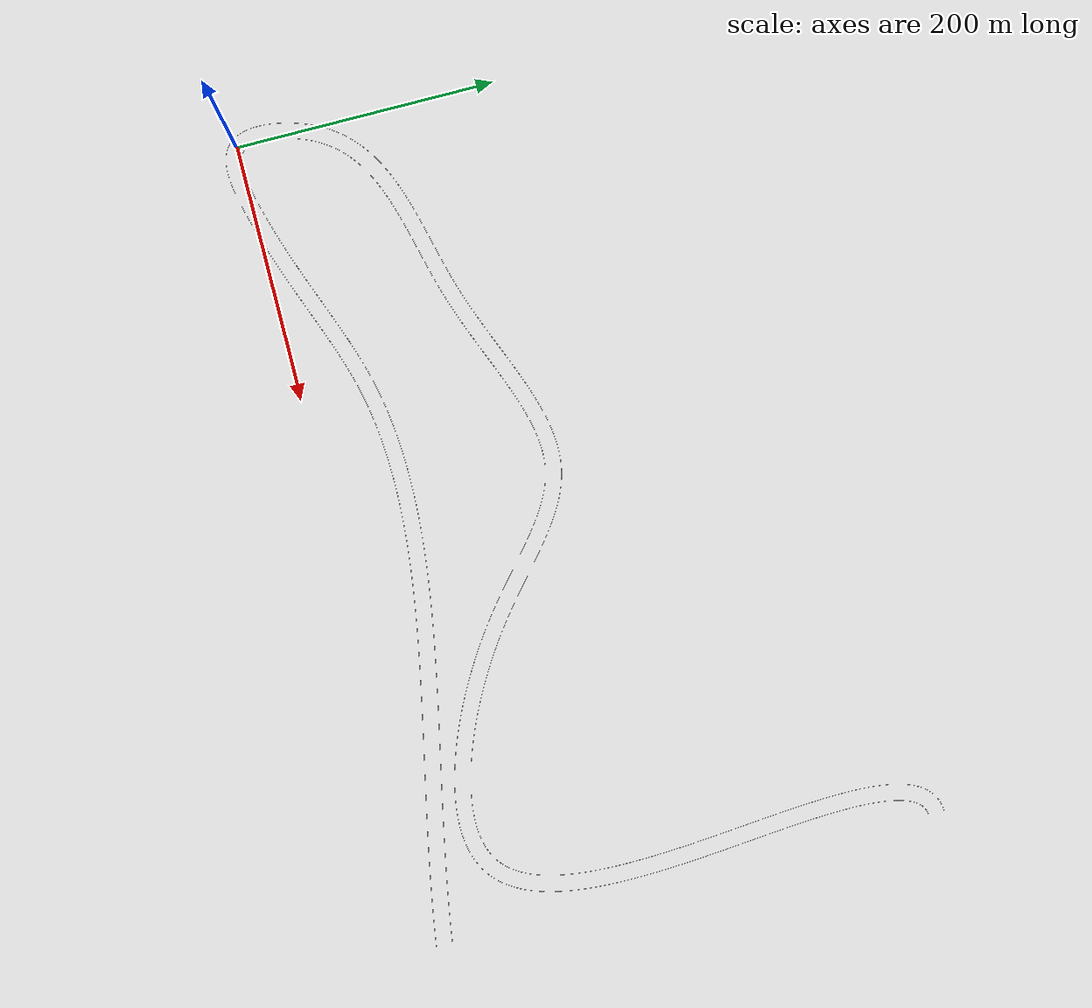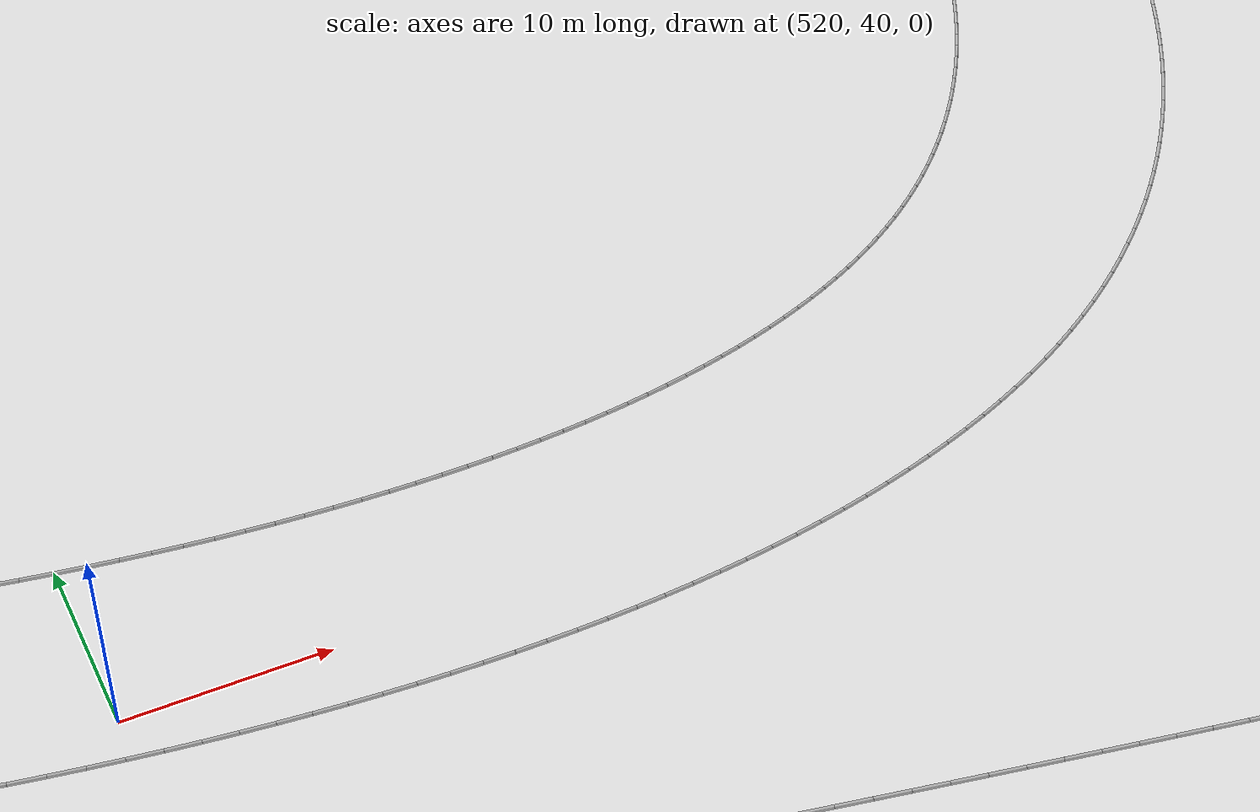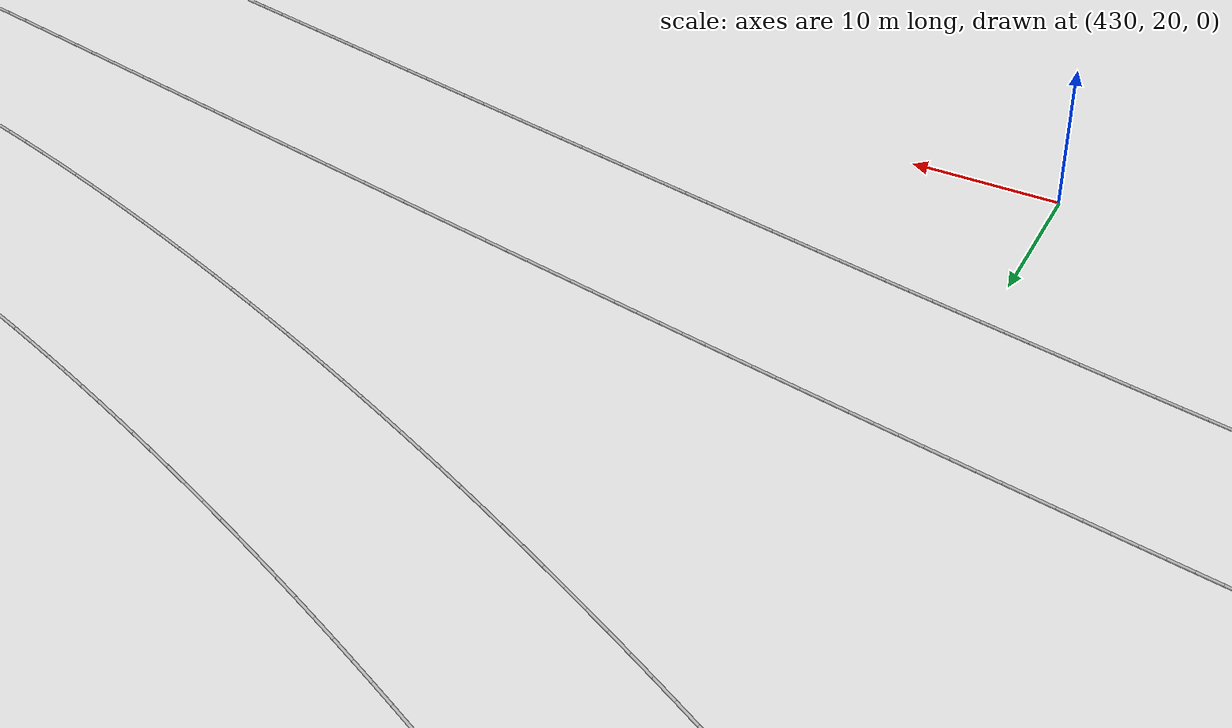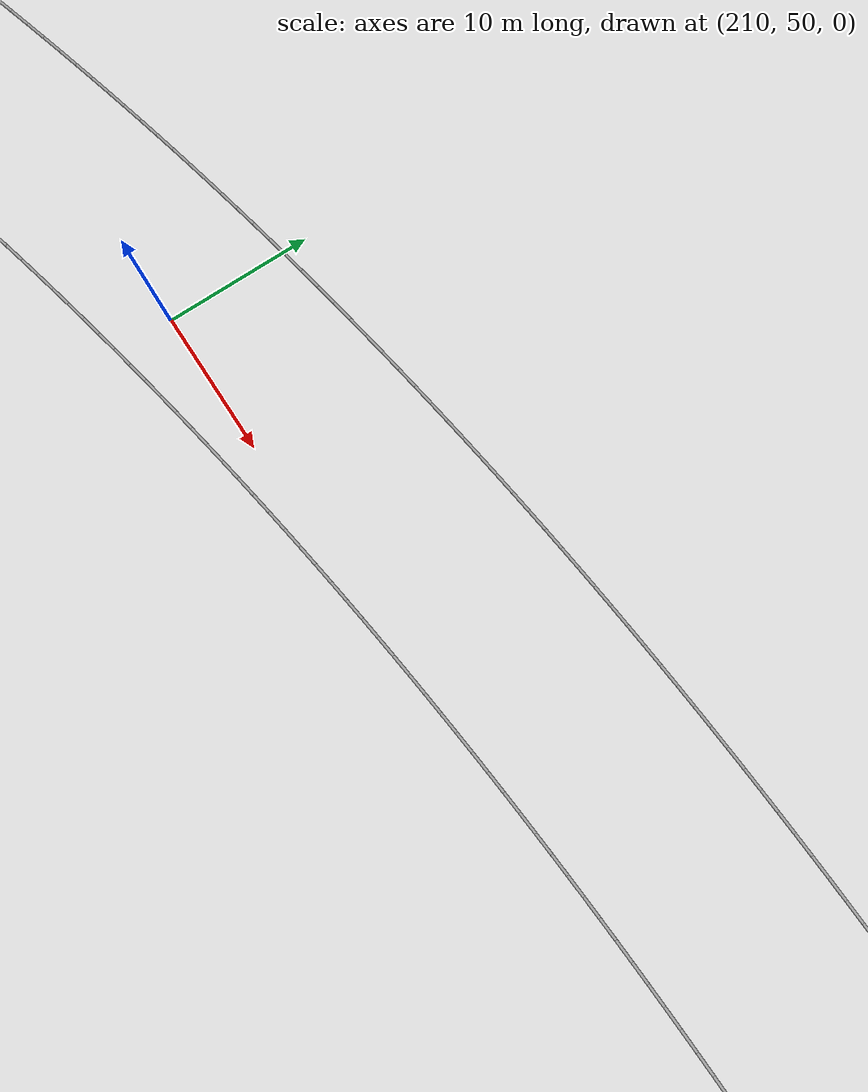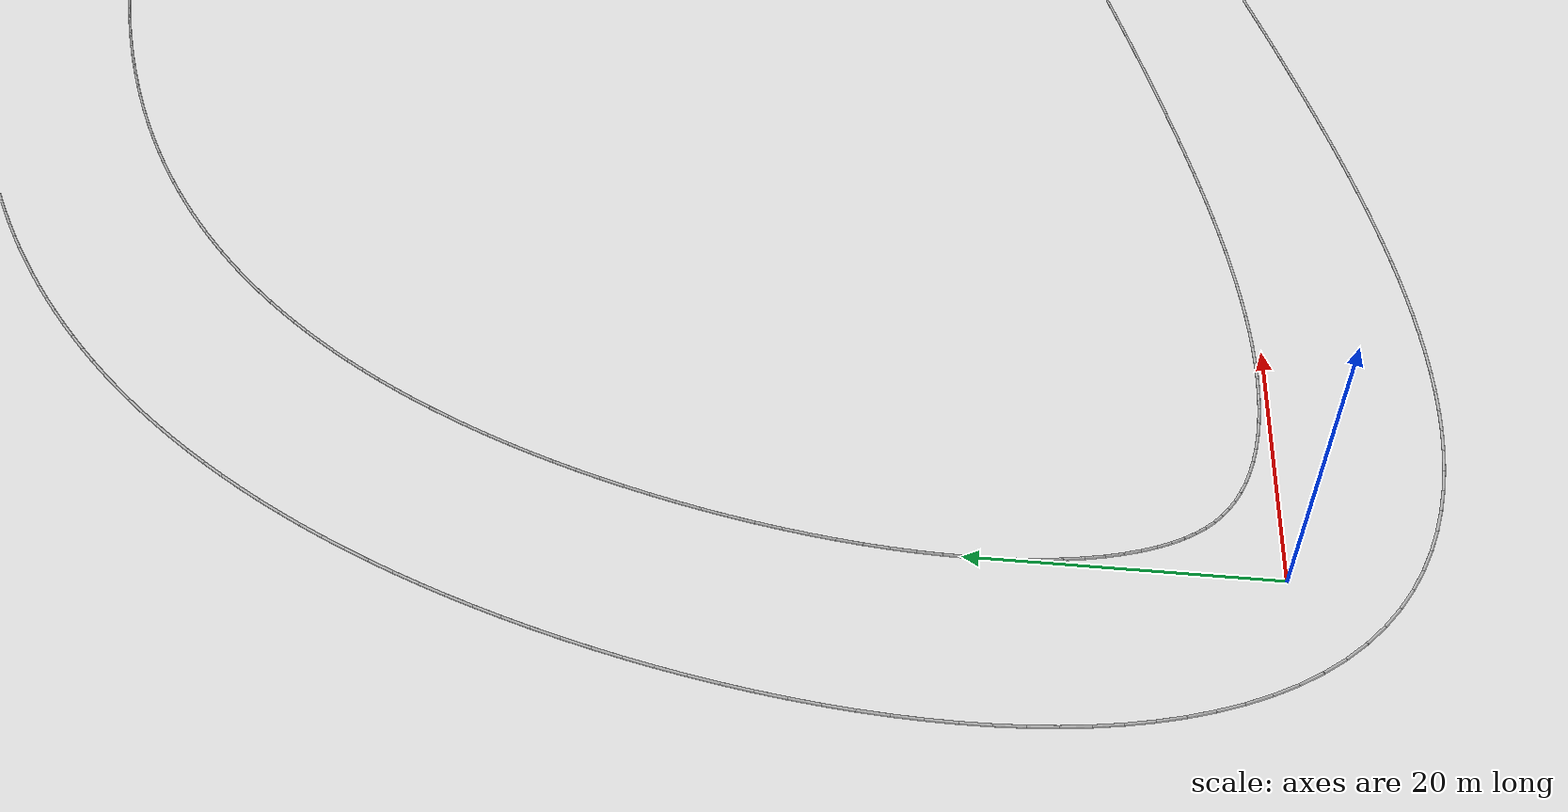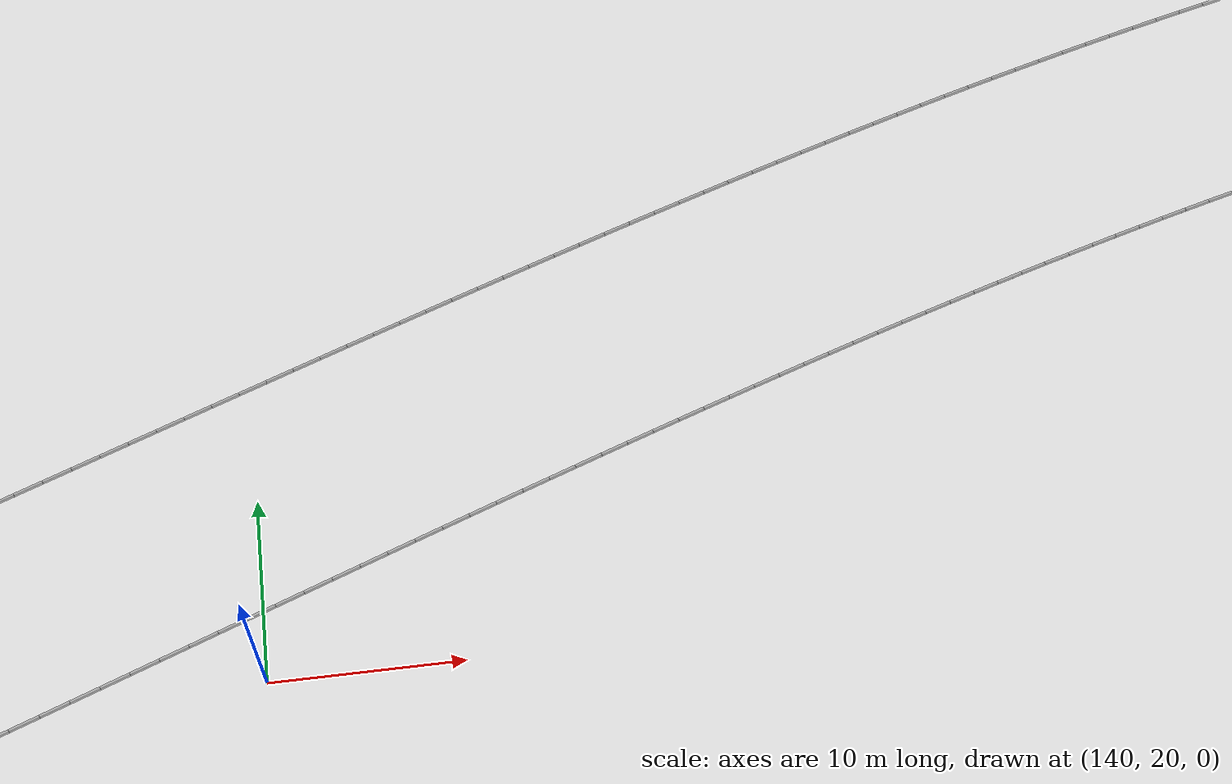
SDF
<sdf version="1.6">
 <model name="line_model">
  <static>true</static>
  <link name="cylinder_(-4.249021052119533, -4.236250712439601)_(-2.9049572582568257, -5.469051834062206)">
   <pose>-3.576989155188179 -4.8526512732509035 0.05 0 1.5707963267948966 -0.7422474314758937</pose>
   <visual name="visual">
    <geometry><cylinder><radius>0.1</radius><length>1.8238163524452145</length></cylinder></geometry>
   </visual>
   <collision name="collision">
    <geometry><cylinder><radius>0.1</radius><length>1.8238163524452145</length></cylinder></geometry>
   </collision>
  </link>
  <link name="cylinder_(-2.9049572582568257, -5.469051834062206)_(-1.472575111838882, -6.568892874361418)">
   <pose>-2.1887661850478537 -6.018972354211812 0.05 0 1.5707963267948966 -0.6548216060838599</pose>
   <visual name="visual">
    <geometry><cylinder><radius>0.1</radius><length>1.805926058094109</length></cylinder></geometry>
   </visual>
   <collision name="collision">
    <geometry><cylinder><radius>0.1</radius><length>1.805926058094109</length></cylinder></geometry>
   </collision>
  </link>
  <link name="cylinder_(-1.472575111838882, -6.568892874361418)_(0.033578878463894846, -7.537119892814051)">
   <pose>-0.7194981166874935 -7.053006383587734 0.05 0 1.5707963267948966 -0.5713305116121087</pose>
   <visual name="visual">
    <geometry><cylinder><radius>0.1</radius><length>1.7905204276317686</length></cylinder></geometry>
   </visual>
   <collision name="collision">
    <geometry><cylinder><radius>0.1</radius><length>1.7905204276317686</length></cylinder></geometry>
   </collision>
  </link>
  <link name="cylinder_(0.033578878463894846, -7.537119892814051)_(1.6005012791967514, -8.378262489645378)">
   <pose>0.8170400788303231 -7.957691191229714 0.05 0 1.5707963267948966 -0.49266164306231314</pose>
   <visual name="visual">
    <geometry><cylinder><radius>0.1</radius><length>1.778416902225844</length></cylinder></geometry>
   </visual>
   <collision name="collision">
    <geometry><cylinder><radius>0.1</radius><length>1.778416902225844</length></cylinder></geometry>
   </collision>
  </link>
  <link name="cylinder_(1.6005012791967514, -8.378262489645378)_(3.2174245499085403, -9.099108740106718)">
   <pose>2.408962914552646 -8.738685614876047 0.05 0 1.5707963267948966 -0.41936699485730816</pose>
   <visual name="visual">
    <geometry><cylinder><radius>0.1</radius><length>1.7703277041761174</length></cylinder></geometry>
   </visual>
   <collision name="collision">
    <geometry><cylinder><radius>0.1</radius><length>1.7703277041761174</length></cylinder></geometry>
   </collision>
  </link>
  <link name="cylinder_(3.2174245499085403, -9.099108740106718)_(4.875987013777609, -9.707716649169532)">
   <pose>4.046705781843075 -9.403412694638124 0.05 0 1.5707963267948966 -0.35169368294137054</pose>
   <visual name="visual">
    <geometry><cylinder><radius>0.1</radius><length>1.766701172674441</length></cylinder></geometry>
   </visual>
   <collision name="collision">
    <geometry><cylinder><radius>0.1</radius><length>1.766701172674441</length></cylinder></geometry>
   </collision>
  </link>
  <link name="cylinder_(4.875987013777609, -9.707716649169532)_(6.570023350481146, -10.212578299242846)">
   <pose>5.723005182129377 -9.960147474206188 0.05 0 1.5707963267948966 -0.28964197104777306</pose>
   <visual name="visual">
    <geometry><cylinder><radius>0.1</radius><length>1.767666370044611</length></cylinder></geometry>
   </visual>
   <collision name="collision">
    <geometry><cylinder><radius>0.1</radius><length>1.767666370044611</length></cylinder></geometry>
   </collision>
  </link>
  <link name="cylinder_(6.570023350481146, -10.212578299242846)_(8.295155358092961, -10.622028005878324)">
   <pose>7.432589354287053 -10.417303152560585 0.05 0 1.5707963267948966 -0.2330321115178145</pose>
   <visual name="visual">
    <geometry><cylinder><radius>0.1</radius><length>1.7730565433597003</length></cylinder></geometry>
   </visual>
   <collision name="collision">
    <geometry><cylinder><radius>0.1</radius><length>1.7730565433597003</length></cylinder></geometry>
   </collision>
  </link>
  <link name="cylinder_(8.295155358092961, -10.622028005878324)_(10.048330074823662, -10.943891145379279)">
   <pose>9.171742716458311 -10.782959575628801 0.05 0 1.5707963267948966 -0.18156686576478967</pose>
   <visual name="visual">
    <geometry><cylinder><radius>0.1</radius><length>1.7824750960260807</length></cylinder></geometry>
   </visual>
   <collision name="collision">
    <geometry><cylinder><radius>0.1</radius><length>1.7824750960260807</length></cylinder></geometry>
   </collision>
  </link>
  <link name="cylinder_(10.048330074823662, -10.943891145379279)_(11.82739612357923, -11.185322695457401)">
   <pose>10.937863099201447 -11.06460692041834 0.05 0 1.5707963267948966 -0.1348829165829973</pose>
   <visual name="visual">
    <geometry><cylinder><radius>0.1</radius><length>1.7953732757306702</length></cylinder></geometry>
   </visual>
   <collision name="collision">
    <geometry><cylinder><radius>0.1</radius><length>1.7953732757306702</length></cylinder></geometry>
   </collision>
  </link>
  <link name="cylinder_(11.82739612357923, -11.185322695457401)_(13.63075912494509, -11.352773611850036)">
   <pose>12.72907762426216 -11.269048153653719 0.05 0 1.5707963267948966 -0.09258931004252366</pose>
   <visual name="visual">
    <geometry><cylinder><radius>0.1</radius><length>1.8111206266000104</length></cylinder></geometry>
   </visual>
   <collision name="collision">
    <geometry><cylinder><radius>0.1</radius><length>1.8111206266000104</length></cylinder></geometry>
   </collision>
  </link>
  <link name="cylinder_(13.63075912494509, -11.352773611850036)_(15.457123899609154, -11.452031755381473)">
   <pose>14.543941512277122 -11.402402683615755 0.05 0 1.5707963267948966 -0.054293968829689294</pose>
   <visual name="visual">
    <geometry><cylinder><radius>0.1</radius><length>1.8290599960610985</length></cylinder></geometry>
   </visual>
   <collision name="collision">
    <geometry><cylinder><radius>0.1</radius><length>1.8290599960610985</length></cylinder></geometry>
   </collision>
  </link>
  <link name="cylinder_(15.457123899609154, -11.452031755381473)_(17.305313992507518, -11.48829893518052)">
   <pose>16.381218946058336 -11.470165345280996 0.05 0 1.5707963267948966 -0.01962056064311813</pose>
   <visual name="visual">
    <geometry><cylinder><radius>0.1</radius><length>1.8485458955130754</length></cylinder></geometry>
   </visual>
   <collision name="collision">
    <geometry><cylinder><radius>0.1</radius><length>1.8485458955130754</length></cylinder></geometry>
   </collision>
  </link>
  <link name="cylinder_(17.305313992507518, -11.48829893518052)_(19.17415277784109, -11.466279648818954)">
   <pose>18.239733385174304 -11.477289291999737 0.05 0 1.5707963267948966 0.011781790750598467</pose>
   <visual name="visual">
    <geometry><cylinder><radius>0.1</radius><length>1.8689685001462533</length></cylinder></geometry>
   </visual>
   <collision name="collision">
    <geometry><cylinder><radius>0.1</radius><length>1.8689685001462533</length></cylinder></geometry>
   </collision>
  </link>
  <link name="cylinder_(19.17415277784109, -11.466279648818954)_(21.062390152229003, -11.390267725794367)">
   <pose>20.118271465035047 -11.42827368730666 0.05 0 1.5707963267948966 0.040233767590855445</pose>
   <visual name="visual">
    <geometry><cylinder><radius>0.1</radius><length>1.8897667037169574</length></cylinder></geometry>
   </visual>
   <collision name="collision">
    <geometry><cylinder><radius>0.1</radius><length>1.8897667037169574</length></cylinder></geometry>
   </collision>
  </link>
  <link name="cylinder_(21.062390152229003, -11.390267725794367)_(22.96866119612631, -11.264224157372379)">
   <pose>22.015525674177656 -11.327245941583373 0.05 0 1.5707963267948966 0.06602438046689744</pose>
   <visual name="visual">
    <geometry><cylinder><radius>0.1</radius><length>1.9104335303647368</length></cylinder></geometry>
   </visual>
   <collision name="collision">
    <geometry><cylinder><radius>0.1</radius><length>1.9104335303647368</length></cylinder></geometry>
   </collision>
  </link>
  <link name="cylinder_(22.96866119612631, -11.264224157372379)_(24.891466253448165, -11.09184366472544)">
   <pose>23.93006372478724 -11.17803391104891 0.05 0 1.5707963267948966 0.08941150143869973</pose>
   <visual name="visual">
    <geometry><cylinder><radius>0.1</radius><length>1.930516594776566</length></cylinder></geometry>
   </visual>
   <collision name="collision">
    <geometry><cylinder><radius>0.1</radius><length>1.930516594776566</length></cylinder></geometry>
   </collision>
  </link>
  <link name="cylinder_(24.891466253448165, -11.09184366472544)_(26.82916473662527, -10.876609896476234)">
   <pose>25.860315495036716 -10.984226780600837 0.05 0 1.5707963267948966 0.11062354317358238</pose>
   <visual name="visual">
    <geometry><cylinder><radius>0.1</radius><length>1.9496155997277016</length></cylinder></geometry>
   </visual>
   <collision name="collision">
    <geometry><cylinder><radius>0.1</radius><length>1.9496155997277016</length></cylinder></geometry>
   </collision>
  </link>
  <link name="cylinder_(26.82916473662527, -10.876609896476234)_(28.7799772844437, -10.62184027834837)">
   <pose>27.804571010534485 -10.749225087412302 0.05 0 1.5707963267948966 0.12986171086418116</pose>
   <visual name="visual">
    <geometry><cylinder><radius>0.1</radius><length>1.967378244020923</length></cylinder></geometry>
   </visual>
   <collision name="collision">
    <geometry><cylinder><radius>0.1</radius><length>1.967378244020923</length></cylinder></geometry>
   </collision>
  </link>
  <link name="cylinder_(28.7799772844437, -10.62184027834837)_(30.741992645876856, -10.330721969862442)">
   <pose>29.760984965160276 -10.476281124105405 0.05 0 1.5707963267948966 0.14730246200813937</pose>
   <visual name="visual">
    <geometry><cylinder><radius>0.1</radius><length>1.9834954368577176</length></cylinder></geometry>
   </visual>
   <collision name="collision">
    <geometry><cylinder><radius>0.1</radius><length>1.9834954368577176</length></cylinder></geometry>
   </collision>
  </link>
  <link name="cylinder_(30.741992645876856, -10.330721969862442)_(32.71317691387913, -10.006340441474308)">
   <pose>31.727584779877994 -10.168531205668375 0.05 0 1.5707963267948966 0.163099951808989</pose>
   <visual name="visual">
    <geometry><cylinder><radius>0.1</radius><length>1.9976963719191885</length></cylinder></geometry>
   </visual>
   <collision name="collision">
    <geometry><cylinder><radius>0.1</radius><length>1.9976963719191885</length></cylinder></geometry>
   </collision>
  </link>
  <link name="cylinder_(32.71317691387913, -10.006340441474308)_(34.691383598166915, -9.651702064840247)">
   <pose>33.70228025602302 -9.829021253157277 0.05 0 1.5707963267948966 0.17738833637332582</pose>
   <visual name="visual">
    <geometry><cylinder><radius>0.1</radius><length>2.00974378067019</length></cylinder></geometry>
   </visual>
   <collision name="collision">
    <geometry><cylinder><radius>0.1</radius><length>2.00974378067019</length></cylinder></geometry>
   </collision>
  </link>
  <link name="cylinder_(34.691383598166915, -9.651702064840247)_(36.674363607689656, -9.269751918317665)">
   <pose>35.68287360292828 -9.460726991578955 0.05 0 1.5707963267948966 0.1902838663734714</pose>
   <visual name="visual">
    <geometry><cylinder><radius>0.1</radius><length>2.019429531475519</length></cylinder></geometry>
   </visual>
   <collision name="collision">
    <geometry><cylinder><radius>0.1</radius><length>2.019429531475519</length></cylinder></geometry>
   </collision>
  </link>
  <link name="cylinder_(36.674363607689656, -9.269751918317665)_(38.65977459466055, -8.863387806654718)">
   <pose>37.6670691011751 -9.06656986248619 0.05 0 1.5707963267948966 0.20188674123878042</pose>
   <visual name="visual">
    <geometry><cylinder><radius>0.1</radius><length>2.026570644816593</length></cylinder></geometry>
   </visual>
   <collision name="collision">
    <geometry><cylinder><radius>0.1</radius><length>2.026570644816593</length></cylinder></geometry>
   </collision>
  </link>
  <link name="cylinder_(38.65977459466055, -8.863387806654718)_(40.645189354887805, -8.435471305276957)">
   <pose>39.652481974774176 -8.649429555965838 0.05 0 1.5707963267948966 0.21228271596719064</pose>
   <visual name="visual">
    <geometry><cylinder><radius>0.1</radius><length>2.0310057366437055</length></cylinder></geometry>
   </visual>
   <collision name="collision">
    <geometry><cylinder><radius>0.1</radius><length>2.0310057366437055</length></cylinder></geometry>
   </collision>
  </link>
  <link name="cylinder_(40.645189354887805, -8.435471305276957)_(42.62810312829511, -7.988836476291541)">
   <pose>41.63664624159146 -8.212153890784249 0.05 0 1.5707963267948966 0.22154446463822486</pose>
   <visual name="visual">
    <geometry><cylinder><radius>0.1</radius><length>2.0325918683373763</length></cylinder></geometry>
   </visual>
   <collision name="collision">
    <geometry><cylinder><radius>0.1</radius><length>2.0325918683373763</length></cylinder></geometry>
   </collision>
  </link>
  <link name="cylinder_(42.62810312829511, -7.988836476291541)_(44.605939729833814, -7.5262967673876195)">
   <pose>43.617021429064465 -7.7575666218395805 0.05 0 1.5707963267948966 0.22973271022263375</pose>
   <visual name="visual">
    <geometry><cylinder><radius>0.1</radius><length>2.0312017636608872</length></cylinder></geometry>
   </visual>
   <collision name="collision">
    <geometry><cylinder><radius>0.1</radius><length>2.0312017636608872</length></cylinder></geometry>
   </collision>
  </link>
  <link name="cylinder_(44.605939729833814, -7.5262967673876195)_(46.57605648530233, -7.050650494240444)">
   <pose>45.59099810756807 -7.288473630814032 0.05 0 1.5707963267948966 0.23689713164219212</pose>
   <visual name="visual">
    <geometry><cylinder><radius>0.1</radius><length>2.0267213442741934</length></cylinder></geometry>
   </visual>
   <collision name="collision">
    <geometry><cylinder><radius>0.1</radius><length>2.0267213442741934</length></cylinder></geometry>
   </collision>
  </link>
  <link name="cylinder_(46.57605648530233, -7.050650494240444)_(48.53574796255034, -6.56468521821217)">
   <pose>47.55590222392634 -6.807667856226307 0.05 0 1.5707963267948966 0.24307705769340937</pose>
   <visual name="visual">
    <geometry><cylinder><radius>0.1</radius><length>2.0190475317593974</length></cylinder></geometry>
   </visual>
   <collision name="collision">
    <geometry><cylinder><radius>0.1</radius><length>2.0190475317593974</length></cylinder></geometry>
   </collision>
  </link>
  <link name="cylinder_(48.53574796255034, -6.56468521821217)_(50.48224848473466, -6.071181260042058)">
   <pose>49.5089982236425 -6.317933239127115 0.05 0 1.5707963267948966 0.24830195428031107</pose>
   <visual name="visual">
    <geometry><cylinder><radius>0.1</radius><length>2.0080862629860823</length></cylinder></geometry>
   </visual>
   <collision name="collision">
    <geometry><cylinder><radius>0.1</radius><length>2.0080862629860823</length></cylinder></geometry>
   </collision>
  </link>
  <link name="cylinder_(50.48224848473466, -6.071181260042058)_(52.41336305370181, -5.572718984320765)">
   <pose>51.447805769218235 -5.821950122181412 0.05 0 1.5707963267948966 0.252607742893596</pose>
   <visual name="visual">
    <geometry><cylinder><radius>0.1</radius><length>1.9944092154807191</length></cylinder></geometry>
   </visual>
   <collision name="collision">
    <geometry><cylinder><radius>0.1</radius><length>1.9944092154807191</length></cylinder></geometry>
   </collision>
  </link>
  <link name="cylinder_(52.41336305370181, -5.572718984320765)_(54.33151805937532, -5.069810359046406)">
   <pose>53.372440556538564 -5.321264671683586 0.05 0 1.5707963267948966 0.2564122261417967</pose>
   <visual name="visual">
    <geometry><cylinder><radius>0.1</radius><length>1.9829865635363484</length></cylinder></geometry>
   </visual>
   <collision name="collision">
    <geometry><cylinder><radius>0.1</radius><length>1.9829865635363484</length></cylinder></geometry>
   </collision>
  </link>
  <link name="cylinder_(54.33151805937532, -5.069810359046406)_(56.237491880919265, -4.562467915189153)">
   <pose>55.284504970147296 -4.81613913711778 0.05 0 1.5707963267948966 0.26015304207290046</pose>
   <visual name="visual">
    <geometry><cylinder><radius>0.1</radius><length>1.972341898289919</length></cylinder></geometry>
   </visual>
   <collision name="collision">
    <geometry><cylinder><radius>0.1</radius><length>1.972341898289919</length></cylinder></geometry>
   </collision>
  </link>
  <link name="cylinder_(56.237491880919265, -4.562467915189153)_(58.131425718838045, -4.050823605082581)">
   <pose>57.184458799878655 -4.306645760135867 0.05 0 1.5707963267948966 0.2638506942374474</pose>
   <visual name="visual">
    <geometry><cylinder><radius>0.1</radius><length>1.961827026645874</length></cylinder></geometry>
   </visual>
   <collision name="collision">
    <geometry><cylinder><radius>0.1</radius><length>1.961827026645874</length></cylinder></geometry>
   </collision>
  </link>
  <link name="cylinder_(58.131425718838045, -4.050823605082581)_(60.013460785294754, -3.5350094744287808)">
   <pose>59.0724432520664 -3.792916539755681 0.05 0 1.5707963267948966 0.2675037542482771</pose>
   <visual name="visual">
    <geometry><cylinder><radius>0.1</radius><length>1.9514405470715328</length></cylinder></geometry>
   </visual>
   <collision name="collision">
    <geometry><cylinder><radius>0.1</radius><length>1.9514405470715328</length></cylinder></geometry>
   </collision>
  </link>
  <link name="cylinder_(60.013460785294754, -3.5350094744287808)_(61.883738307106924, -3.0151576580088912)">
   <pose>60.94859954620084 -3.275083566218836 0.05 0 1.5707963267948966 0.2711107882582817</pose>
   <visual name="visual">
    <geometry><cylinder><radius>0.1</radius><length>1.9411810630724098</length></cylinder></geometry>
   </visual>
   <collision name="collision">
    <geometry><cylinder><radius>0.1</radius><length>1.9411810630724098</length></cylinder></geometry>
   </collision>
  </link>
  <link name="cylinder_(61.883738307106924, -3.0151576580088912)_(63.74239952863063, -2.4914003751935643)">
   <pose>62.813068917868776 -2.753279016601228 0.05 0 1.5707963267948966 0.2746703575459844</pose>
   <visual name="visual">
    <geometry><cylinder><radius>0.1</radius><length>1.9310471842236485</length></cylinder></geometry>
   </visual>
   <collision name="collision">
    <geometry><cylinder><radius>0.1</radius><length>1.9310471842236485</length></cylinder></geometry>
   </collision>
  </link>
  <link name="cylinder_(63.74239952863063, -2.4914003751935643)_(65.58958571452753, -1.9638699252573035)">
   <pose>64.66599262157908 -2.227635150225434 0.05 0 1.5707963267948966 0.278181019103545</pose>
   <visual name="visual">
    <geometry><cylinder><radius>0.1</radius><length>1.9210375272175966</length></cylinder></geometry>
   </visual>
   <collision name="collision">
    <geometry><cylinder><radius>0.1</radius><length>1.9210375272175966</length></cylinder></geometry>
   </collision>
  </link>
  <link name="cylinder_(65.58958571452753, -1.9638699252573035)_(67.42543815240994, -1.4326986825009254)">
   <pose>66.50751193346873 -1.6982843038791144 0.05 0 1.5707963267948966 0.2816413262266187</pose>
   <visual name="visual">
    <geometry><cylinder><radius>0.1</radius><length>1.9111507169268827</length></cylinder></geometry>
   </visual>
   <collision name="collision">
    <geometry><cylinder><radius>0.1</radius><length>1.9111507169268827</length></cylinder></geometry>
   </collision>
  </link>
  <link name="cylinder_(67.42543815240994, -1.4326986825009254)_(69.25009815535985, -0.8980190911865531)">
   <pose>68.3377681538849 -1.1653588868437392 0.05 0 1.5707963267948966 0.2850498291055229</pose>
   <visual name="visual">
    <geometry><cylinder><radius>0.1</radius><length>1.901385387482842</length></cylinder></geometry>
   </visual>
   <collision name="collision">
    <geometry><cylinder><radius>0.1</radius><length>1.901385387482842</length></cylinder></geometry>
   </collision>
  </link>
  <link name="cylinder_(69.25009815535985, -0.8980190911865531)_(71.06370706431818, -0.35996366028987836)">
   <pose>70.15690260983902 -0.6289913757382157 0.05 0 1.5707963267948966 0.2884050754172234</pose>
   <visual name="visual">
    <geometry><cylinder><radius>0.1</radius><length>1.891740183368326</length></cylinder></geometry>
   </visual>
   <collision name="collision">
    <geometry><cylinder><radius>0.1</radius><length>1.891740183368326</length></cylinder></geometry>
   </collision>
  </link>
  <link name="cylinder_(71.06370706431818, -0.35996366028987836)_(72.866406250341, 0.1813350419254416)">
   <pose>71.9650566573296 -0.08931430918221839 0.05 0 1.5707963267948966 0.29170561091771846</pose>
   <visual name="visual">
    <geometry><cylinder><radius>0.1</radius><length>1.8822137605243805</length></cylinder></geometry>
   </visual>
   <collision name="collision">
    <geometry><cylinder><radius>0.1</radius><length>1.8822137605243805</length></cylinder></geometry>
   </collision>
  </link>
  <link name="cylinder_(72.866406250341, 0.1813350419254416)_(74.6583371167207, 0.7257443935062282)">
   <pose>73.76237168353086 0.4535397177158349 0.05 0 1.5707963267948966 0.2949499800343641</pose>
   <visual name="visual">
    <geometry><cylinder><radius>0.1</radius><length>1.872804787470632</length></cylinder></geometry>
   </visual>
   <collision name="collision">
    <geometry><cylinder><radius>0.1</radius><length>1.872804787470632</length></cylinder></geometry>
   </collision>
  </link>
  <link name="cylinder_(74.6583371167207, 0.7257443935062282)_(76.43964110097008, 1.273131724575851)">
   <pose>75.54898910884539 0.9994380590410397 0.05 0 1.5707963267948966 0.2981367264578406</pose>
   <visual name="visual">
    <geometry><cylinder><radius>0.1</radius><length>1.863511946438291</length></cylinder></geometry>
   </visual>
   <collision name="collision">
    <geometry><cylinder><radius>0.1</radius><length>1.863511946438291</length></cylinder></geometry>
   </collision>
  </link>
  <link name="cylinder_(76.43964110097008, 1.273131724575851)_(78.21045967666845, 1.8233643232626031)">
   <pose>77.32505038881926 1.5482480239192271 0.05 0 1.5707963267948966 0.30126439373341274</pose>
   <visual name="visual">
    <geometry><cylinder><radius>0.1</radius><length>1.8543339345155672</length></cylinder></geometry>
   </visual>
   <collision name="collision">
    <geometry><cylinder><radius>0.1</radius><length>1.8543339345155672</length></cylinder></geometry>
   </collision>
  </link>
  <link name="cylinder_(78.21045967666845, 1.8233643232626031)_(79.97093435516949, 2.3763094417850654)">
   <pose>79.09069701591898 2.0998368825238343 0.05 0 1.5707963267948966 0.30433152585130535</pose>
   <visual name="visual">
    <geometry><cylinder><radius>0.1</radius><length>1.8452694648048458</length></cylinder></geometry>
   </visual>
   <collision name="collision">
    <geometry><cylinder><radius>0.1</radius><length>1.8452694648048458</length></cylinder></geometry>
   </collision>
  </link>
  <link name="cylinder_(79.97093435516949, 2.3763094417850654)_(81.72120668717137, 2.9318343026888716)">
   <pose>80.84607052117043 2.6540718722369685 0.05 0 1.5707963267948966 0.30733666783587266</pose>
   <visual name="visual">
    <geometry><cylinder><radius>0.1</radius><length>1.836317267591172</length></cylinder></geometry>
   </visual>
   <collision name="collision">
    <geometry><cylinder><radius>0.1</radius><length>1.836317267591172</length></cylinder></geometry>
   </collision>
  </link>
  <link name="cylinder_(81.72120668717137, 2.9318343026888716)_(83.46141826414983, 3.4898061052295084)">
   <pose>82.5913124756606 3.21082020395919 0.05 0 1.5707963267948966 0.3102783663336991</pose>
   <visual name="visual">
    <geometry><cylinder><radius>0.1</radius><length>1.827476091520839</length></cylinder></geometry>
   </visual>
   <collision name="collision">
    <geometry><cylinder><radius>0.1</radius><length>1.827476091520839</length></cylinder></geometry>
   </collision>
  </link>
  <link name="cylinder_(83.46141826414983, 3.4898061052295084)_(85.19171071965708, 4.050092031895531)">
   <pose>84.32656449190345 3.7699490685625197 0.05 0 1.5707963267948966 0.3131551702001797</pose>
   <visual name="visual">
    <geometry><cylinder><radius>0.1</radius><length>1.8187447047910064</length></cylinder></geometry>
   </visual>
   <collision name="collision">
    <geometry><cylinder><radius>0.1</radius><length>1.8187447047910064</length></cylinder></geometry>
   </collision>
  </link>
  <link name="cylinder_(85.19171071965708, 4.050092031895531)_(86.91222573048836, 4.6125592550667704)">
   <pose>86.05196822507273 4.331325643481151 0.05 0 1.5707963267948966 0.3159656310850415</pose>
   <visual name="visual">
    <geometry><cylinder><radius>0.1</radius><length>1.8101218963477894</length></cylinder></geometry>
   </visual>
   <collision name="collision">
    <geometry><cylinder><radius>0.1</radius><length>1.8101218963477894</length></cylinder></geometry>
   </collision>
  </link>
  <link name="cylinder_(86.91222573048836, 4.6125592550667704)_(88.62310501772025, 5.177074943801976)">
   <pose>87.7676653741043 4.894817099434373 0.05 0 1.5707963267948966 0.31870830401647354</pose>
   <visual name="visual">
    <geometry><cylinder><radius>0.1</radius><length>1.801606477094064</length></cylinder></geometry>
   </visual>
   <collision name="collision">
    <geometry><cylinder><radius>0.1</radius><length>1.801606477094064</length></cylinder></geometry>
   </collision>
  </link>
  <link name="cylinder_(88.62310501772025, 5.177074943801976)_(90.32449034762483, 5.743506270750521)">
   <pose>89.47379768267254 5.4602906072762485 0.05 0 1.5707963267948966 0.3213817479843005</pose>
   <visual name="visual">
    <geometry><cylinder><radius>0.1</radius><length>1.7931972811052366</length></cylinder></geometry>
   </visual>
   <collision name="collision">
    <geometry><cylinder><radius>0.1</radius><length>1.7931972811052366</length></cylinder></geometry>
   </collision>
  </link>
  <link name="cylinder_(90.32449034762483, 5.743506270750521)_(92.01652353246506, 6.311720419182777)">
   <pose>91.17050694004494 6.027613344966649 0.05 0 1.5707963267948966 0.3239845265222312</pose>
   <visual name="visual">
    <geometry><cylinder><radius>0.1</radius><length>1.784893166853175</length></cylinder></geometry>
   </visual>
   <collision name="collision">
    <geometry><cylinder><radius>0.1</radius><length>1.784893166853175</length></cylinder></geometry>
   </collision>
  </link>
  <link name="cylinder_(92.01652353246506, 6.311720419182777)_(93.69934643117672, 6.881584590133851)">
   <pose>92.85793498182089 6.596652504658314 0.05 0 1.5707963267948966 0.32651520828963915</pose>
   <visual name="visual">
    <geometry><cylinder><radius>0.1</radius><length>1.7766930184368035</length></cylinder></geometry>
   </visual>
   <collision name="collision">
    <geometry><cylinder><radius>0.1</radius><length>1.7766930184368035</length></cylinder></geometry>
   </collision>
  </link>
  <link name="cylinder_(93.69934643117672, 6.881584590133851)_(95.37310094994473, 7.452966009655543)">
   <pose>94.53622369056072 7.167275299894698 0.05 0 1.5707963267948966 0.3289723676530078</pose>
   <visual name="visual">
    <geometry><cylinder><radius>0.1</radius><length>1.768595746820326</length></cylinder></geometry>
   </visual>
   <collision name="collision">
    <geometry><cylinder><radius>0.1</radius><length>1.768595746820326</length></cylinder></geometry>
   </collision>
  </link>
  <link name="cylinder_(95.37310094994473, 7.452966009655543)_(97.03792904268025, 8.025731936171336)">
   <pose>96.20551499631249 7.73934897291344 0.05 0 1.5707963267948966 0.331354585267743</pose>
   <visual name="visual">
    <geometry><cylinder><radius>0.1</radius><length>1.7606002910765635</length></cylinder></geometry>
   </visual>
   <collision name="collision">
    <geometry><cylinder><radius>0.1</radius><length>1.7606002910765635</length></cylinder></geometry>
   </collision>
  </link>
  <link name="cylinder_(97.03792904268025, 8.025731936171336)_(98.69397271140767, 8.599749667929537)">
   <pose>97.86595087704396 8.312740802050437 0.05 0 1.5707963267948966 0.33366044866068023</pose>
   <visual name="visual">
    <geometry><cylinder><radius>0.1</radius><length>1.7527056196363962</length></cylinder></geometry>
   </visual>
   <collision name="collision">
    <geometry><cylinder><radius>0.1</radius><length>1.7527056196363962</length></cylinder></geometry>
   </collision>
  </link>
  <link name="cylinder_(98.69397271140767, 8.599749667929537)_(100.34137400657038, 9.174886550549573)">
   <pose>99.51767335898901 8.887318109239555 0.05 0 1.5707963267948966 0.3358885528139044</pose>
   <visual name="visual">
    <geometry><cylinder><radius>0.1</radius><length>1.7449107315429244</length></cylinder></geometry>
   </visual>
   <collision name="collision">
    <geometry><cylinder><radius>0.1</radius><length>1.7449107315429244</length></cylinder></geometry>
   </collision>
  </link>
  <link name="cylinder_(100.34137400657038, 9.174886550549573)_(101.98027502726553, 9.751009984656815)">
   <pose>101.16082451691796 9.462948267603194 0.05 0 1.5707963267948966 0.3380375007505752</pose>
   <visual name="visual">
    <geometry><cylinder><radius>0.1</radius><length>1.737214657710196</length></cylinder></geometry>
   </visual>
   <collision name="collision">
    <geometry><cylinder><radius>0.1</radius><length>1.737214657710196</length></cylinder></geometry>
   </collision>
  </link>
  <link name="cylinder_(101.98027502726553, 9.751009984656815)_(103.61081792141805, 10.327987433601145)">
   <pose>102.79554647434179 10.03949870912898 0.05 0 1.5707963267948966 0.3401059041235259</pose>
   <visual name="visual">
    <geometry><cylinder><radius>0.1</radius><length>1.7296164621850585</length></cylinder></geometry>
   </visual>
   <collision name="collision">
    <geometry><cylinder><radius>0.1</radius><length>1.7296164621850585</length></cylinder></geometry>
   </collision>
  </link>
  <link name="cylinder_(103.61081792141805, 10.327987433601145)_(105.23314488590577, 10.905686431254813)">
   <pose>104.4219814036619 10.61683693242798 0.05 0 1.5707963267948966 0.34209238380732665</pose>
   <visual name="visual">
    <geometry><cylinder><radius>0.1</radius><length>1.7221152434125926</length></cylinder></geometry>
   </visual>
   <collision name="collision">
    <geometry><cylinder><radius>0.1</radius><length>1.7221152434125926</length></cylinder></geometry>
   </collision>
  </link>
  <link name="cylinder_(105.23314488590577, 10.905686431254813)_(106.84739816664816, 11.48397458988506)">
   <pose>106.04027152627697 11.194830510569936 0.05 0 1.5707963267948966 0.34399557049473645</pose>
   <visual name="visual">
    <geometry><cylinder><radius>0.1</radius><length>1.71471013550382</length></cylinder></geometry>
   </visual>
   <collision name="collision">
    <geometry><cylinder><radius>0.1</radius><length>1.71471013550382</length></cylinder></geometry>
   </collision>
  </link>
  <link name="cylinder_(106.84739816664816, 11.48397458988506)_(108.453720058671, 12.062719608097218)">
   <pose>107.65055911265958 11.773347098991138 0.05 0 1.5707963267948966 0.3458141052986037</pose>
   <visual name="visual">
    <geometry><cylinder><radius>0.1</radius><length>1.7074003095048356</length></cylinder></geometry>
   </visual>
   <collision name="collision">
    <geometry><cylinder><radius>0.1</radius><length>1.7074003095048356</length></cylinder></geometry>
   </collision>
  </link>
  <link name="cylinder_(108.453720058671, 12.062719608097218)_(110.05225290616133, 12.641789278843902)">
   <pose>109.25298648241616 12.35225444347056 0.05 0 1.5707963267948966 0.3475466403600147</pose>
   <visual name="visual">
    <geometry><cylinder><radius>0.1</radius><length>1.7001849746672342</length></cylinder></geometry>
   </visual>
   <collision name="collision">
    <geometry><cylinder><radius>0.1</radius><length>1.7001849746672342</length></cylinder></geometry>
   </collision>
  </link>
  <link name="cylinder_(110.05225290616133, 12.641789278843902)_(111.6431391025269, 13.22105149749602)">
   <pose>110.84769600434412 12.931420388169961 0.05 0 1.5707963267948966 0.3491918394638987</pose>
   <visual name="visual">
    <geometry><cylinder><radius>0.1</radius><length>1.6930633797186383</length></cylinder></geometry>
   </visual>
   <collision name="collision">
    <geometry><cylinder><radius>0.1</radius><length>1.6930633797186383</length></cylinder></geometry>
   </collision>
  </link>
  <link name="cylinder_(111.6431391025269, 13.22105149749602)_(113.2265210904752, 13.800374269971435)">
   <pose>112.43483009650106 13.510712883733728 0.05 0 1.5707963267948966 0.35074837866322484</pose>
   <visual name="visual">
    <geometry><cylinder><radius>0.1</radius><length>1.6860348141327663</length></cylinder></geometry>
   </visual>
   <collision name="collision">
    <geometry><cylinder><radius>0.1</radius><length>1.6860348141327663</length></cylinder></geometry>
   </collision>
  </link>
  <link name="cylinder_(113.2265210904752, 13.800374269971435)_(114.80254136212797, 14.379625720916998)">
   <pose>114.01453122630159 14.089999995444217 0.05 0 1.5707963267948966 0.35221494691294947</pose>
   <visual name="visual">
    <geometry><cylinder><radius>0.1</radius><length>1.6790986093982083</length></cylinder></geometry>
   </visual>
   <collision name="collision">
    <geometry><cylinder><radius>0.1</radius><length>1.6790986093982083</length></cylinder></geometry>
   </collision>
  </link>
  <link name="cylinder_(114.80254136212797, 14.379625720916998)_(116.3713424591874, 14.958674101939486)">
   <pose>115.58694191065769 14.669149911428242 0.05 0 1.5707963267948966 0.35359024671489564</pose>
   <visual name="visual">
    <geometry><cylinder><radius>0.1</radius><length>1.6722541402847986</length></cylinder></geometry>
   </visual>
   <collision name="collision">
    <geometry><cylinder><radius>0.1</radius><length>1.6722541402847986</length></cylinder></geometry>
   </collision>
  </link>
  <link name="cylinder_(116.3713424591874, 14.958674101939486)_(117.93306697317136, 15.537387799881348)">
   <pose>117.15220471617938 15.248030950910417 0.05 0 1.5707963267948966 0.35487299477504425</pose>
   <visual name="visual">
    <geometry><cylinder><radius>0.1</radius><length>1.6655008261072655</length></cylinder></geometry>
   </visual>
   <collision name="collision">
    <geometry><cylinder><radius>0.1</radius><length>1.6655008261072655</length></cylinder></geometry>
   </collision>
  </link>
  <link name="cylinder_(117.93306697317136, 15.537387799881348)_(119.48785754573474, 16.11563534513644)">
   <pose>118.71046225945305 15.826511572508894 0.05 0 1.5707963267948966 0.35606192267437087</pose>
   <visual name="visual">
    <geometry><cylinder><radius>0.1</radius><length>1.6588381319843997</length></cylinder></geometry>
   </visual>
   <collision name="collision">
    <geometry><cylinder><radius>0.1</radius><length>1.6588381319843997</length></cylinder></geometry>
   </collision>
  </link>
  <link name="cylinder_(119.48785754573474, 16.11563534513644)_(121.0358568690957, 16.693285420001303)">
   <pose>120.26185720741522 16.40446038256887 0.05 0 1.5707963267948966 0.35715577755470473</pose>
   <visual name="visual">
    <geometry><cylinder><radius>0.1</radius><length>1.6522655700937896</length></cylinder></geometry>
   </visual>
   <collision name="collision">
    <geometry><cylinder><radius>0.1</radius><length>1.6522655700937896</length></cylinder></geometry>
   </collision>
  </link>
  <link name="cylinder_(121.0358568690957, 16.693285420001303)_(122.57720768658481, 17.270206867056892)">
   <pose>121.80653227784026 16.981746143529097 0.05 0 1.5707963267948966 0.35815332282104184</pose>
   <visual name="visual">
    <geometry><cylinder><radius>0.1</radius><length>1.6457827009198651</length></cylinder></geometry>
   </visual>
   <collision name="collision">
    <geometry><cylinder><radius>0.1</radius><length>1.6457827009198651</length></cylinder></geometry>
   </collision>
  </link>
  <link name="cylinder_(122.57720768658481, 17.270206867056892)_(124.11205279333626, 17.846268697575717)">
   <pose>123.34463023996054 17.558237782316304 0.05 0 1.5707963267948966 0.35905333886179264</pose>
   <visual name="visual">
    <geometry><cylinder><radius>0.1</radius><length>1.6393891344947853</length></cylinder></geometry>
   </visual>
   <collision name="collision">
    <geometry><cylinder><radius>0.1</radius><length>1.6393891344947853</length></cylinder></geometry>
   </collision>
  </link>
  <link name="cylinder_(124.11205279333626, 17.846268697575717)_(125.64053503714126, 18.42134009994879)">
   <pose>124.87629391523876 18.13380439876225 0.05 0 1.5707963267948966 0.3598546237881388</pose>
   <visual name="visual">
    <geometry><cylinder><radius>0.1</radius><length>1.6330845316316311</length></cylinder></geometry>
   </visual>
   <collision name="collision">
    <geometry><cylinder><radius>0.1</radius><length>1.6330845316316311</length></cylinder></geometry>
   </collision>
  </link>
  <link name="cylinder_(125.64053503714126, 18.42134009994879)_(127.16279731948222, 18.995290448126507)">
   <pose>126.40166617831174 18.70831527403765 0.05 0 1.5707963267948966 0.3605559941945291</pose>
   <visual name="visual">
    <geometry><cylinder><radius>0.1</radius><length>1.6268686051464742</length></cylinder></geometry>
   </visual>
   <collision name="collision">
    <geometry><cylinder><radius>0.1</radius><length>1.6268686051464742</length></cylinder></geometry>
   </collision>
  </link>
  <link name="cylinder_(127.16279731948222, 18.995290448126507)_(128.6789825967692, 19.567989310067162)">
   <pose>127.92088995812571 19.281639879096836 0.05 0 1.5707963267948966 0.3611562859411725</pose>
   <visual name="visual">
    <geometry><cylinder><radius>0.1</radius><length>1.6207411210708251</length></cylinder></geometry>
   </visual>
   <collision name="collision">
    <geometry><cylinder><radius>0.1</radius><length>1.6207411210708251</length></cylinder></geometry>
   </collision>
  </link>
  <link name="cylinder_(128.6789825967692, 19.567989310067162)_(130.1892338817981, 20.139306456186063)">
   <pose>129.43410823928366 19.853647883126612 0.05 0 1.5707963267948966 0.36165435496044396</pose>
   <visual name="visual">
    <geometry><cylinder><radius>0.1</radius><length>1.61470189985051</length></cylinder></geometry>
   </visual>
   <collision name="collision">
    <geometry><cylinder><radius>0.1</radius><length>1.61470189985051</length></cylinder></geometry>
   </collision>
  </link>
  <link name="cylinder_(130.1892338817981, 20.139306456186063)_(131.6936942454514, 20.70911186779799)">
   <pose>130.94146406362475 20.424209161992025 0.05 0 1.5707963267948966 0.3620490780885752</pose>
   <visual name="visual">
    <geometry><cylinder><radius>0.1</radius><length>1.6087508175308336</length></cylinder></geometry>
   </visual>
   <collision name="collision">
    <geometry><cylinder><radius>0.1</radius><length>1.6087508175308336</length></cylinder></geometry>
   </collision>
  </link>
  <link name="cylinder_(131.6936942454514, 20.70911186779799)_(133.1925068186626, 21.27727574554465)">
   <pose>132.443100532057 20.99319380667132 0.05 0 1.5707963267948966 0.36233935392390326</pose>
   <visual name="visual">
    <geometry><cylinder><radius>0.1</radius><length>1.6028878069260017</length></cylinder></geometry>
   </visual>
   <collision name="collision">
    <geometry><cylinder><radius>0.1</radius><length>1.6028878069260017</length></cylinder></geometry>
   </collision>
  </link>
  <link name="cylinder_(133.1925068186626, 21.27727574554465)_(134.68581479466422, 21.84366851779845)">
   <pose>133.9391608066634 21.56047213167155 0.05 0 1.5707963267948966 0.36252410371339266</pose>
   <visual name="visual">
    <geometry><cylinder><radius>0.1</radius><length>1.5971128587709238</length></cylinder></geometry>
   </visual>
   <collision name="collision">
    <geometry><cylinder><radius>0.1</radius><length>1.5971128587709238</length></cylinder></geometry>
   </collision>
  </link>
  <link name="cylinder_(134.68581479466422, 21.84366851779845)_(136.17376143154127, 22.408160849032697)">
   <pose>135.42978811310275 22.125914683415573 0.05 0 1.5707963267948966 0.3626022722684906</pose>
   <visual name="visual">
    <geometry><cylinder><radius>0.1</radius><length>1.5914260228537087</length></cylinder></geometry>
   </visual>
   <collision name="collision">
    <geometry><cylinder><radius>0.1</radius><length>1.5914260228537087</length></cylinder></geometry>
   </collision>
  </link>
  <link name="cylinder_(136.17376143154127, 22.408160849032697)_(137.65649005510917, 22.970623648147892)">
   <pose>136.91512574332523 22.689392248590295 0.05 0 1.5707963267948966 0.36257282891209325</pose>
   <visual name="visual">
    <geometry><cylinder><radius>0.1</radius><length>1.585827409126253</length></cylinder></geometry>
   </visual>
   <collision name="collision">
    <geometry><cylinder><radius>0.1</radius><length>1.585827409126253</length></cylinder></geometry>
   </collision>
  </link>
  <link name="cylinder_(137.65649005510917, 22.970623648147892)_(139.1341440621388, 23.530928076742384)">
   <pose>138.395317058624 23.25077586244514 0.05 0 1.5707963267948966 0.36243476845719413</pose>
   <visual name="visual">
    <geometry><cylinder><radius>0.1</radius><length>1.5803171887925902</length></cylinder></geometry>
   </visual>
   <collision name="collision">
    <geometry><cylinder><radius>0.1</radius><length>1.5803171887925902</length></cylinder></geometry>
   </collision>
  </link>
  <link name="cylinder_(139.1341440621388, 23.530928076742384)_(140.6068669239463, 24.088945557314872)">
   <pose>139.87050549304257 23.80993681702863 0.05 0 1.5707963267948966 0.3621871122192655</pose>
   <visual name="visual">
    <geometry><cylinder><radius>0.1</radius><length>1.5748955953697295</length></cylinder></geometry>
   </visual>
   <collision name="collision">
    <geometry><cylinder><radius>0.1</radius><length>1.5748955953697295</length></cylinder></geometry>
   </collision>
  </link>
  <link name="cylinder_(140.6068669239463, 24.088945557314872)_(142.07480219036964, 24.644547781385143)">
   <pose>141.34083455715796 24.366746669350007 0.05 0 1.5707963267948966 0.36182890906269877</pose>
   <visual name="visual">
    <geometry><cylinder><radius>0.1</radius><length>1.569562925722046</length></cylinder></geometry>
   </visual>
   <collision name="collision">
    <geometry><cylinder><radius>0.1</radius><length>1.569562925722046</length></cylinder></geometry>
   </collision>
  </link>
  <link name="cylinder_(142.07480219036964, 24.644547781385143)_(143.53809349414914, 25.197606717517935)">
   <pose>142.8064478422594 24.92107724945154 0.05 0 1.5707963267948966 0.3613592364828663</pose>
   <visual name="visual">
    <geometry><cylinder><radius>0.1</radius><length>1.5643195410634756</length></cylinder></geometry>
   </visual>
   <collision name="collision">
    <geometry><cylinder><radius>0.1</radius><length>1.5643195410634756</length></cylinder></geometry>
   </collision>
  </link>
  <link name="cylinder_(143.53809349414914, 25.197606717517935)_(144.99688455573232, 25.74799461923412)">
   <pose>144.26748902494074 25.472800668376028 0.05 0 1.5707963267948966 0.36077720172439115</pose>
   <visual name="visual">
    <geometry><cylinder><radius>0.1</radius><length>1.5591658679276363</length></cylinder></geometry>
   </visual>
   <collision name="collision">
    <geometry><cylinder><radius>0.1</radius><length>1.5591658679276363</length></cylinder></geometry>
   </collision>
  </link>
  <link name="cylinder_(144.99688455573232, 25.74799461923412)_(146.4513191885195, 26.29558403279131)">
   <pose>145.7241018721259 26.021789326012716 0.05 0 1.5707963267948966 0.3600819429364576</pose>
   <visual name="visual">
    <geometry><cylinder><radius>0.1</radius><length>1.554102399100747</length></cylinder></geometry>
   </visual>
   <collision name="collision">
    <geometry><cylinder><radius>0.1</radius><length>1.554102399100747</length></cylinder></geometry>
   </collision>
  </link>
  <link name="cylinder_(146.4513191885195, 26.29558403279131)_(147.90154130456796, 26.840247804815316)">
   <pose>147.17643024654373 26.567915918803315 0.05 0 1.5707963267948966 0.35927263036582174</pose>
   <visual name="visual">
    <geometry><cylinder><radius>0.1</radius><length>1.549129694516074</length></cylinder></geometry>
   </visual>
   <collision name="collision">
    <geometry><cylinder><radius>0.1</radius><length>1.549129694516074</length></cylinder></geometry>
   </collision>
  </link>
  <link name="cylinder_(147.90154130456796, 26.840247804815316)_(149.34769492077038, 27.38185908976205)">
   <pose>148.62461811266917 27.111053447288683 0.05 0 1.5707963267948966 0.35834846758794014</pose>
   <visual name="visual">
    <geometry><cylinder><radius>0.1</radius><length>1.5442483821059991</length></cylinder></geometry>
   </visual>
   <collision name="collision">
    <geometry><cylinder><radius>0.1</radius><length>1.5442483821059991</length></cylinder></geometry>
   </collision>
  </link>
  <link name="cylinder_(149.34769492077038, 27.38185908976205)_(150.78992416552174, 27.920291357187825)">
   <pose>150.06880954314607 27.651075223474937 0.05 0 1.5707963267948966 0.35730869277654304</pose>
   <visual name="visual">
    <geometry><cylinder><radius>0.1</radius><length>1.539459158607769</length></cylinder></geometry>
   </visual>
   <collision name="collision">
    <geometry><cylinder><radius>0.1</radius><length>1.539459158607769</length></cylinder></geometry>
   </collision>
  </link>
  <link name="cylinder_(150.78992416552174, 27.920291357187825)_(152.22837328588912, 28.45541839880503)">
   <pose>151.50914872570542 28.18785487799643 0.05 0 1.5707963267948966 0.35615258001163264</pose>
   <visual name="visual">
    <geometry><cylinder><radius>0.1</radius><length>1.5347627903215768</length></cylinder></geometry>
   </visual>
   <collision name="collision">
    <geometry><cylinder><radius>0.1</radius><length>1.5347627903215768</length></cylinder></geometry>
   </collision>
  </link>
  <link name="cylinder_(152.22837328588912, 28.45541839880503)_(153.66318665529516, 28.98711433529771)">
   <pose>152.94577997059213 28.72126636705137 0.05 0 1.5707963267948966 0.3548794406258955</pose>
   <visual name="visual">
    <geometry><cylinder><radius>0.1</radius><length>1.5301601138146144</length></cylinder></geometry>
   </visual>
   <collision name="collision">
    <geometry><cylinder><radius>0.1</radius><length>1.5301601138146144</length></cylinder></geometry>
   </collision>
  </link>
  <link name="cylinder_(153.66318665529516, 28.98711433529771)_(155.0945087817262, 29.515253622870883)">
   <pose>154.37884771851068 29.251183979084296 0.05 0 1.5707963267948966 0.35348862458917946</pose>
   <visual name="visual">
    <geometry><cylinder><radius>0.1</radius><length>1.5256520365697335</length></cylinder></geometry>
   </visual>
   <collision name="collision">
    <geometry><cylinder><radius>0.1</radius><length>1.5256520365697335</length></cylinder></geometry>
   </collision>
  </link>
  <link name="cylinder_(155.0945087817262, 29.515253622870883)_(156.52248431647297, 30.03971105950505)">
   <pose>155.80849654909957 29.777482341187966 0.05 0 1.5707963267948966 0.3519795219303736</pose>
   <visual name="visual">
    <geometry><cylinder><radius>0.1</radius><length>1.5212395375732866</length></cylinder></geometry>
   </visual>
   <collision name="collision">
    <geometry><cylinder><radius>0.1</radius><length>1.5212395375732866</length></cylinder></geometry>
   </collision>
  </link>
  <link name="cylinder_(156.52248431647297, 30.03971105950505)_(157.94725806341026, 30.560361790886144)">
   <pose>157.2348711899416 30.300036425195596 0.05 0 1.5707963267948966 0.3503515641959048</pose>
   <visual name="visual">
    <geometry><cylinder><radius>0.1</radius><length>1.51692366783876</length></cylinder></geometry>
   </visual>
   <collision name="collision">
    <geometry><cylinder><radius>0.1</radius><length>1.51692366783876</length></cylinder></geometry>
   </collision>
  </link>
  <link name="cylinder_(157.94725806341026, 30.560361790886144)_(159.3689749888199, 31.07708131597934)">
   <pose>158.65811652611507 30.81872155343274 0.05 0 1.5707963267948966 0.34860422594362145</pose>
   <visual name="visual">
    <geometry><cylinder><radius>0.1</radius><length>1.512705550862023</length></cylinder></geometry>
   </visual>
   <collision name="collision">
    <geometry><cylinder><radius>0.1</radius><length>1.512705550862023</length></cylinder></geometry>
   </collision>
  </link>
  <link name="cylinder_(159.3689749888199, 31.07708131597934)_(160.78778023175775, 31.589745492213748)">
   <pose>160.07837761028884 31.333413404096543 0.05 0 1.5707963267948966 0.3467370262710211</pose>
   <visual name="visual">
    <geometry><cylinder><radius>0.1</radius><length>1.5085863830029878</length></cylinder></geometry>
   </visual>
   <collision name="collision">
    <geometry><cylinder><radius>0.1</radius><length>1.5085863830029878</length></cylinder></geometry>
   </collision>
  </link>
  <link name="cylinder_(160.78778023175775, 31.589745492213748)_(162.203819114965, 32.09823054024317)">
   <pose>161.49579967336138 31.843988016228458 0.05 0 1.5707963267948966 0.34474953037537115</pose>
   <visual name="visual">
    <geometry><cylinder><radius>0.1</radius><length>1.5045674337909622</length></cylinder></geometry>
   </visual>
   <collision name="collision">
    <geometry><cylinder><radius>0.1</radius><length>1.5045674337909622</length></cylinder></geometry>
   </collision>
  </link>
  <link name="cylinder_(162.203819114965, 32.09823054024317)_(163.6172371563184, 32.60241304824686)">
   <pose>162.9105281356417 32.35032179424502 0.05 0 1.5707963267948966 0.3426413511445422</pose>
   <visual name="visual">
    <geometry><cylinder><radius>0.1</radius><length>1.5006500461467214</length></cylinder></geometry>
   </visual>
   <collision name="collision">
    <geometry><cylinder><radius>0.1</radius><length>1.5006500461467214</length></cylinder></geometry>
   </collision>
  </link>
  <link name="cylinder_(163.6172371563184, 32.60241304824686)_(165.0281800808137, 33.10216997573283)">
   <pose>164.32270861856605 32.85229151198985 0.05 0 1.5707963267948966 0.3404121507754914</pose>
   <visual name="visual">
    <geometry><cylinder><radius>0.1</radius><length>1.496835636519124</length></cylinder></geometry>
   </visual>
   <collision name="collision">
    <geometry><cylinder><radius>0.1</radius><length>1.496835636519124</length></cylinder></geometry>
   </collision>
  </link>
  <link name="cylinder_(165.0281800808137, 33.10216997573283)_(166.43679383307125, 33.59737865680462)">
   <pose>165.73248695694247 33.34977431626872 0.05 0 1.5707963267948966 0.3380616424179472</pose>
   <visual name="visual">
    <geometry><cylinder><radius>0.1</radius><length>1.4931256949292395</length></cylinder></geometry>
   </visual>
   <collision name="collision">
    <geometry><cylinder><radius>0.1</radius><length>1.4931256949292395</length></cylinder></geometry>
   </collision>
  </link>
  <link name="cylinder_(166.43679383307125, 33.59737865680462)_(167.84322459035045, 34.087916802851765)">
   <pose>167.14000921171083 33.842647729828194 0.05 0 1.5707963267948966 0.33558959184012677</pose>
   <visual name="visual">
    <geometry><cylinder><radius>0.1</radius><length>1.4895217849190059</length></cylinder></geometry>
   </visual>
   <collision name="collision">
    <geometry><cylinder><radius>0.1</radius><length>1.4895217849190059</length></cylinder></geometry>
   </collision>
  </link>
  <link name="cylinder_(167.84322459035045, 34.087916802851765)_(169.2476187760553, 34.57366250462272)">
   <pose>168.54542168320287 34.33078965373724 0.05 0 1.5707963267948966 0.33299581911310794</pose>
   <visual name="visual">
    <geometry><cylinder><radius>0.1</radius><length>1.4860255433977472</length></cylinder></geometry>
   </visual>
   <collision name="collision">
    <geometry><cylinder><radius>0.1</radius><length>1.4860255433977472</length></cylinder></geometry>
   </collision>
  </link>
  <link name="cylinder_(169.2476187760553, 34.57366250462272)_(170.65012307371057, 35.05449423363852)">
   <pose>169.94887092488295 34.81407836913062 0.05 0 1.5707963267948966 0.3302802003096365</pose>
   <visual name="visual">
    <geometry><cylinder><radius>0.1</radius><length>1.4826386803836697</length></cylinder></geometry>
   </visual>
   <collision name="collision">
    <geometry><cylinder><radius>0.1</radius><length>1.4826386803836697</length></cylinder></geometry>
   </collision>
  </link>
  <link name="cylinder_(170.65012307371057, 35.05449423363852)_(172.0508844413818, 35.53029084290445)">
   <pose>171.3505037575462 35.292392538271486 0.05 0 1.5707963267948966 0.3274426692135454</pose>
   <visual name="visual">
    <geometry><cylinder><radius>0.1</radius><length>1.479362978632745</length></cylinder></geometry>
   </visual>
   <collision name="collision">
    <geometry><cylinder><radius>0.1</radius><length>1.479362978632745</length></cylinder></geometry>
   </collision>
  </link>
  <link name="cylinder_(172.0508844413818, 35.53029084290445)_(173.4500501265115, 36.000931566876986)">
   <pose>172.75046728394665 35.76561120489072 0.05 0 1.5707963267948966 0.32448321903466004</pose>
   <visual name="visual">
    <geometry><cylinder><radius>0.1</radius><length>1.4762002931532912</length></cylinder></geometry>
   </visual>
   <collision name="collision">
    <geometry><cylinder><radius>0.1</radius><length>1.4762002931532912</length></cylinder></geometry>
   </collision>
  </link>
  <link name="cylinder_(173.4500501265115, 36.000931566876986)_(174.847767681136, 36.466296020642766)">
   <pose>174.14890890382375 36.23361379375987 0.05 0 1.5707963267948966 0.32140190412439607</pose>
   <visual name="visual">
    <geometry><cylinder><radius>0.1</radius><length>1.4731525505982581</length></cylinder></geometry>
   </visual>
   <collision name="collision">
    <geometry><cylinder><radius>0.1</radius><length>1.4731525505982581</length></cylinder></geometry>
   </collision>
  </link>
  <link name="cylinder_(174.847767681136, 36.466296020642766)_(176.24418497744523, 36.92626419826665)">
   <pose>175.54597632929062 36.696280109454705 0.05 0 1.5707963267948966 0.3181988416863735</pose>
   <visual name="visual">
    <geometry><cylinder><radius>0.1</radius><length>1.4702217485325948</length></cylinder></geometry>
   </visual>
   <collision name="collision">
    <geometry><cylinder><radius>0.1</radius><length>1.4702217485325948</length></cylinder></geometry>
   </collision>
  </link>
  <link name="cylinder_(176.24418497744523, 36.92626419826665)_(177.63945022364265, 37.380716470266385)">
   <pose>176.94181760054394 37.15349033426652 0.05 0 1.5707963267948966 0.3148742134761328</pose>
   <visual name="visual">
    <geometry><cylinder><radius>0.1</radius><length>1.4674099545703247</length></cylinder></geometry>
   </visual>
   <collision name="collision">
    <geometry><cylinder><radius>0.1</radius><length>1.4674099545703247</length></cylinder></geometry>
   </collision>
  </link>
  <link name="cylinder_(177.63945022364265, 37.380716470266385)_(179.03371198005632, 37.82953358017202)">
   <pose>178.3365811018495 37.6051250252192 0.05 0 1.5707963267948966 0.31142826748375085</pose>
   <visual name="visual">
    <geometry><cylinder><radius>0.1</radius><length>1.464719305376213</length></cylinder></geometry>
   </visual>
   <collision name="collision">
    <geometry><cylinder><radius>0.1</radius><length>1.464719305376213</length></cylinder></geometry>
   </collision>
  </link>
  <link name="cylinder_(179.03371198005632, 37.82953358017202)_(180.42711917545017, 38.27259664012956)">
   <pose>179.73041557775326 38.05106511015079 0.05 0 1.5707963267948966 0.30786131959228336</pose>
   <visual name="visual">
    <geometry><cylinder><radius>0.1</radius><length>1.4621520055296193</length></cylinder></geometry>
   </visual>
   <collision name="collision">
    <geometry><cylinder><radius>0.1</radius><length>1.4621520055296193</length></cylinder></geometry>
   </collision>
  </link>
  <link name="cylinder_(180.42711917545017, 38.27259664012956)_(181.81982112347643, 38.70978712550965)">
   <pose>181.1234701494633 38.49119188281961 0.05 0 1.5707963267948966 0.3041737552053544</pose>
   <visual name="visual">
    <geometry><cylinder><radius>0.1</radius><length>1.4597103262438793</length></cylinder></geometry>
   </visual>
   <collision name="collision">
    <geometry><cylinder><radius>0.1</radius><length>1.4597103262438793</length></cylinder></geometry>
   </collision>
  </link>
  <link name="cylinder_(181.81982112347643, 38.70978712550965)_(183.21196753920765, 39.14098686848433)">
   <pose>182.51589433134205 38.92538699699699 0.05 0 1.5707963267948966 0.30036603083610536</pose>
   <visual name="visual">
    <geometry><cylinder><radius>0.1</radius><length>1.4573966039396113</length></cylinder></geometry>
   </visual>
   <collision name="collision">
    <geometry><cylinder><radius>0.1</radius><length>1.4573966039396113</length></cylinder></geometry>
   </collision>
  </link>
  <link name="cylinder_(183.21196753920765, 39.14098686848433)_(184.6037085556821, 39.5660780505369)">
   <pose>183.90783804744487 39.35353245951062 0.05 0 1.5707963267948966 0.2964386756494128</pose>
   <visual name="visual">
    <geometry><cylinder><radius>0.1</radius><length>1.4552132386685328</length></cylinder></geometry>
   </visual>
   <collision name="collision">
    <geometry><cylinder><radius>0.1</radius><length>1.4552132386685328</length></cylinder></geometry>
   </collision>
  </link>
  <link name="cylinder_(184.6037085556821, 39.5660780505369)_(185.99519474038863, 39.98494319387296)">
   <pose>185.29945164803536 39.77551062220493 0.05 0 1.5707963267948966 0.2923922929498606</pose>
   <visual name="visual">
    <geometry><cylinder><radius>0.1</radius><length>1.453162692382064</length></cylinder></geometry>
   </visual>
   <collision name="collision">
    <geometry><cylinder><radius>0.1</radius><length>1.453162692382064</length></cylinder></geometry>
   </collision>
  </link>
  <link name="cylinder_(185.99519474038863, 39.98494319387296)_(187.38657711161738, 40.397465151704225)">
   <pose>186.690885926003 40.19120417278859 0.05 0 1.5707963267948966 0.2882275616061713</pose>
   <visual name="visual">
    <geometry><cylinder><radius>0.1</radius><length>1.451247487046611</length></cylinder></geometry>
   </visual>
   <collision name="collision">
    <geometry><cylinder><radius>0.1</radius><length>1.451247487046611</length></cylinder></geometry>
   </collision>
  </link>
  <link name="cylinder_(187.38657711161738, 40.397465151704225)_(188.77800715459335, 40.803527097379956)">
   <pose>188.08229213310537 40.60049612454209 0.05 0 1.5707963267948966 0.2839452374039067</pose>
   <visual name="visual">
    <geometry><cylinder><radius>0.1</radius><length>1.4494702025988901</length></cylinder></geometry>
   </visual>
   <collision name="collision">
    <geometry><cylinder><radius>0.1</radius><length>1.4494702025988901</length></cylinder></geometry>
   </collision>
  </link>
  <link name="cylinder_(188.77800715459335, 40.803527097379956)_(190.1696368373098, 41.20301251234561)">
   <pose>189.4738219959516 41.00326980486278 0.05 0 1.5707963267948966 0.27954615431703855</pose>
   <visual name="visual">
    <geometry><cylinder><radius>0.1</radius><length>1.4478334747434816</length></cylinder></geometry>
   </visual>
   <collision name="collision">
    <geometry><cylinder><radius>0.1</radius><length>1.4478334747434816</length></cylinder></geometry>
   </collision>
  </link>
  <link name="cylinder_(190.1696368373098, 41.20301251234561)_(191.56161862597202, 41.59580517291259)">
   <pose>190.86562773164093 41.3994088426291 0.05 0 1.5707963267948966 0.27503122568927413</pose>
   <visual name="visual">
    <geometry><cylinder><radius>0.1</radius><length>1.4463399925890612</length></cylinder></geometry>
   </visual>
   <collision name="collision">
    <geometry><cylinder><radius>0.1</radius><length>1.4463399925890612</length></cylinder></geometry>
   </collision>
  </link>
  <link name="cylinder_(191.56161862597202, 41.59580517291259)_(192.9541054999595, 41.981789135828784)">
   <pose>192.25786206296576 41.788797154370684 0.05 0 1.5707963267948966 0.27040144531595456</pose>
   <visual name="visual">
    <geometry><cylinder><radius>0.1</radius><length>1.4449924961244303</length></cylinder></geometry>
   </visual>
   <collision name="collision">
    <geometry><cylinder><radius>0.1</radius><length>1.4449924961244303</length></cylinder></geometry>
   </collision>
  </link>
  <link name="cylinder_(192.9541054999595, 41.981789135828784)_(194.3472509662122, 42.36084872264483)">
   <pose>193.65067823308584 42.171318929236804 0.05 0 1.5707963267948966 0.2656578884167556</pose>
   <visual name="visual">
    <geometry><cylinder><radius>0.1</radius><length>1.4437937735347037</length></cylinder></geometry>
   </visual>
   <collision name="collision">
    <geometry><cylinder><radius>0.1</radius><length>1.4437937735347037</length></cylinder></geometry>
   </collision>
  </link>
  <link name="cylinder_(194.3472509662122, 42.36084872264483)_(195.7412090729417, 42.73286850287713)">
   <pose>195.04423001957696 42.546858612760985 0.05 0 1.5707963267948966 0.26080171248981127</pose>
   <visual name="visual">
    <geometry><cylinder><radius>0.1</radius><length>1.4427466583572528</length></cylinder></geometry>
   </visual>
   <collision name="collision">
    <geometry><cylinder><radius>0.1</radius><length>1.4427466583572528</length></cylinder></geometry>
   </collision>
  </link>
  <link name="cylinder_(195.7412090729417, 42.73286850287713)_(197.13613442256997, 43.09773327597594)">
   <pose>196.43867174775585 42.91530088942653 0.05 0 1.5707963267948966 0.25583415803778553</pose>
   <visual name="visual">
    <geometry><cylinder><radius>0.1</radius><length>1.4418540264825657</length></cylinder></geometry>
   </visual>
   <collision name="collision">
    <geometry><cylinder><radius>0.1</radius><length>1.4418540264825657</length></cylinder></geometry>
   </collision>
  </link>
  <link name="cylinder_(197.13613442256997, 43.09773327597594)_(198.53218218379186, 43.45532805211283)">
   <pose>197.8341583031809 43.27653066404439 0.05 0 1.5707963267948966 0.2507565491564375</pose>
   <visual name="visual">
    <geometry><cylinder><radius>0.1</radius><length>1.441118792998362</length></cylinder></geometry>
   </visual>
   <collision name="collision">
    <geometry><cylinder><radius>0.1</radius><length>1.441118792998362</length></cylinder></geometry>
   </collision>
  </link>
  <link name="cylinder_(198.53218218379186, 43.45532805211283)_(199.92950810266186, 43.8055380318103)">
   <pose>199.23084514322687 43.63043304196157 0.05 0 1.5707963267948966 0.2455702939764394</pose>
   <visual name="visual">
    <geometry><cylinder><radius>0.1</radius><length>1.4405439088849663</length></cylinder></geometry>
   </visual>
   <collision name="collision">
    <geometry><cylinder><radius>0.1</radius><length>1.4405439088849663</length></cylinder></geometry>
   </collision>
  </link>
  <link name="cylinder_(199.92950810266186, 43.8055380318103)_(201.32826851260162, 44.148248584443)">
   <pose>200.62888830763174 43.97689330812665 0.05 0 1.5707963267948966 0.2402768849492838</pose>
   <visual name="visual">
    <geometry><cylinder><radius>0.1</radius><length>1.440132357563249</length></cylinder></geometry>
   </visual>
   <collision name="collision">
    <geometry><cylinder><radius>0.1</radius><length>1.440132357563249</length></cylinder></geometry>
   </collision>
  </link>
  <link name="cylinder_(201.32826851260162, 44.148248584443)_(202.72895020243485, 44.48345183101292)">
   <pose>202.02860935751823 44.31585020772796 0.05 0 1.5707963267948966 0.2348965848667744</pose>
   <visual name="visual">
    <geometry><cylinder><radius>0.1</radius><length>1.4402327633910637</length></cylinder></geometry>
   </visual>
   <collision name="collision">
    <geometry><cylinder><radius>0.1</radius><length>1.4402327633910637</length></cylinder></geometry>
   </collision>
  </link>
  <link name="cylinder_(202.72895020243485, 44.48345183101292)_(204.13202143416243, 44.81126342266539)">
   <pose>203.43048581829862 44.64735762683915 0.05 0 1.5707963267948966 0.22952141397586143</pose>
   <visual name="visual">
    <geometry><cylinder><radius>0.1</radius><length>1.440857147993261</length></cylinder></geometry>
   </visual>
   <collision name="collision">
    <geometry><cylinder><radius>0.1</radius><length>1.440857147993261</length></cylinder></geometry>
   </collision>
  </link>
  <link name="cylinder_(204.13202143416243, 44.81126342266539)_(205.5374778642271, 45.131722835081725)">
   <pose>204.83474964919475 44.97149312887356 0.05 0 1.5707963267948966 0.22417842395303494</pose>
   <visual name="visual">
    <geometry><cylinder><radius>0.1</radius><length>1.4415276659906189</length></cylinder></geometry>
   </visual>
   <collision name="collision">
    <geometry><cylinder><radius>0.1</radius><length>1.4415276659906189</length></cylinder></geometry>
   </collision>
  </link>
  <link name="cylinder_(205.5374778642271, 45.131722835081725)_(206.9453136830189, 45.44486917432476)">
   <pose>206.241395773623 45.28829600470324 0.05 0 1.5707963267948966 0.21886789694300124</pose>
   <visual name="visual">
    <geometry><cylinder><radius>0.1</radius><length>1.4422421164473316</length></cylinder></geometry>
   </visual>
   <collision name="collision">
    <geometry><cylinder><radius>0.1</radius><length>1.4422421164473316</length></cylinder></geometry>
   </collision>
  </link>
  <link name="cylinder_(206.9453136830189, 45.44486917432476)_(208.3555229884271, 45.750741505188806)">
   <pose>207.650418335723 45.59780533975678 0.05 0 1.5707963267948966 0.213590101968102</pose>
   <visual name="visual">
    <geometry><cylinder><radius>0.1</radius><length>1.4429997116590596</length></cylinder></geometry>
   </visual>
   <collision name="collision">
    <geometry><cylinder><radius>0.1</radius><length>1.4429997116590596</length></cylinder></geometry>
   </collision>
  </link>
  <link name="cylinder_(208.3555229884271, 45.750741505188806)_(209.7680997858476, 46.04937885381829)">
   <pose>209.06181138713737 45.90006017950355 0.05 0 1.5707963267948966 0.2083452970579441</pose>
   <visual name="visual">
    <geometry><cylinder><radius>0.1</radius><length>1.4437996656763574</length></cylinder></geometry>
   </visual>
   <collision name="collision">
    <geometry><cylinder><radius>0.1</radius><length>1.4437996656763574</length></cylinder></geometry>
   </collision>
  </link>
  <link name="cylinder_(209.7680997858476, 46.04937885381829)_(211.18303798828566, 46.340820210296755)">
   <pose>210.47556888706663 46.195099532057526 0.05 0 1.5707963267948966 0.2031337293420516</pose>
   <visual name="visual">
    <geometry><cylinder><radius>0.1</radius><length>1.4446411945478617</length></cylinder></geometry>
   </visual>
   <collision name="collision">
    <geometry><cylinder><radius>0.1</radius><length>1.4446411945478617</length></cylinder></geometry>
   </collision>
  </link>
  <link name="cylinder_(211.18303798828566, 46.340820210296755)_(212.60033141655083, 46.62510453120322)">
   <pose>211.89168470241825 46.48296237074999 0.05 0 1.5707963267948966 0.19795563514975534</pose>
   <visual name="visual">
    <geometry><cylinder><radius>0.1</radius><length>1.4455235165561586</length></cylinder></geometry>
   </visual>
   <collision name="collision">
    <geometry><cylinder><radius>0.1</radius><length>1.4455235165561586</length></cylinder></geometry>
   </collision>
  </link>
  <link name="cylinder_(212.60033141655083, 46.62510453120322)_(214.01997379954108, 46.90227074213306)">
   <pose>213.31015260804594 46.76368763666814 0.05 0 1.5707963267948966 0.19281124011682527</pose>
   <visual name="visual">
    <geometry><cylinder><radius>0.1</radius><length>1.4464458524477968</length></cylinder></geometry>
   </visual>
   <collision name="collision">
    <geometry><cylinder><radius>0.1</radius><length>1.4464458524477968</length></cylinder></geometry>
   </collision>
  </link>
  <link name="cylinder_(214.01997379954108, 46.90227074213306)_(215.44195877461252, 47.172357740180736)">
   <pose>214.7309662870768 47.0373142411569 0.05 0 1.5707963267948966 0.18770075929868907</pose>
   <visual name="visual">
    <geometry><cylinder><radius>0.1</radius><length>1.4474074256557221</length></cylinder></geometry>
   </visual>
   <collision name="collision">
    <geometry><cylinder><radius>0.1</radius><length>1.4474074256557221</length></cylinder></geometry>
   </collision>
  </link>
  <link name="cylinder_(215.44195877461252, 47.172357740180736)_(216.8662798880322, 47.435404396381955)">
   <pose>216.15411933132236 47.30388106828134 0.05 0 1.5707963267948966 0.1826243972897515</pose>
   <visual name="visual">
    <geometry><cylinder><radius>0.1</radius><length>1.4484074625159038</length></cylinder></geometry>
   </visual>
   <collision name="collision">
    <geometry><cylinder><radius>0.1</radius><length>1.4484074625159038</length></cylinder></geometry>
   </collision>
  </link>
  <link name="cylinder_(216.8662798880322, 47.435404396381955)_(218.29293059550966, 47.691449558112986)">
   <pose>217.57960524177093 47.563426977247474 0.05 0 1.5707963267948966 0.1775823483486726</pose>
   <visual name="visual">
    <geometry><cylinder><radius>0.1</radius><length>1.449445192475996</length></cylinder></geometry>
   </visual>
   <collision name="collision">
    <geometry><cylinder><radius>0.1</radius><length>1.449445192475996</length></cylinder></geometry>
   </collision>
  </link>
  <link name="cylinder_(218.29293059550966, 47.691449558112986)_(219.7219042628054, 47.94053205144498)">
   <pose>219.00741742915753 47.815990804778984 0.05 0 1.5707963267948966 0.17257479652895344</pose>
   <visual name="visual">
    <geometry><cylinder><radius>0.1</radius><length>1.4505198482989157</length></cylinder></geometry>
   </visual>
   <collision name="collision">
    <geometry><cylinder><radius>0.1</radius><length>1.4505198482989157</length></cylinder></geometry>
   </collision>
  </link>
  <link name="cylinder_(219.7219042628054, 47.94053205144498)_(221.15319416641123, 48.18269068345129)">
   <pose>220.4375492146083 48.06161136744814 0.05 0 1.5707963267948966 0.1676019158148809</pose>
   <visual name="visual">
    <geometry><cylinder><radius>0.1</radius><length>1.4516306662574858</length></cylinder></geometry>
   </visual>
   <collision name="collision">
    <geometry><cylinder><radius>0.1</radius><length>1.4516306662574858</length></cylinder></geometry>
   </collision>
  </link>
  <link name="cylinder_(221.15319416641123, 48.18269068345129)_(222.5867934943003, 48.417964244466205)">
   <pose>221.86999383035578 48.30032746395875 0.05 0 1.5707963267948966 0.16266387026230866</pose>
   <visual name="visual">
    <geometry><cylinder><radius>0.1</radius><length>1.4527768863237986</length></cylinder></geometry>
   </visual>
   <collision name="collision">
    <geometry><cylinder><radius>0.1</radius><length>1.4527768863237986</length></cylinder></geometry>
   </collision>
  </link>
  <link name="cylinder_(222.5867934943003, 48.417964244466205)_(224.02269534674335, 48.64639151029327)">
   <pose>223.30474442052184 48.53217787737974 0.05 0 1.5707963267948966 0.1577608141438111</pose>
   <visual name="visual">
    <geometry><cylinder><radius>0.1</radius><length>1.4539577523513458</length></cylinder></geometry>
   </visual>
   <collision name="collision">
    <geometry><cylinder><radius>0.1</radius><length>1.4539577523513458</length></cylinder></geometry>
   </collision>
  </link>
  <link name="cylinder_(224.02269534674335, 48.64639151029327)_(225.4608927371871, 48.86801124436195)">
   <pose>224.74179404196522 48.75720137732761 0.05 0 1.5707963267948966 0.15289289209827625</pose>
   <visual name="visual">
    <geometry><cylinder><radius>0.1</radius><length>1.455172512249966</length></cylinder></geometry>
   </visual>
   <collision name="collision">
    <geometry><cylinder><radius>0.1</radius><length>1.455172512249966</length></cylinder></geometry>
   </collision>
  </link>
  <link name="cylinder_(225.4608927371871, 48.86801124436195)_(226.90137859319233, 49.08286219983117)">
   <pose>226.18113566518971 48.97543672209656 0.05 0 1.5707963267948966 0.14806023928419743</pose>
   <visual name="visual">
    <geometry><cylinder><radius>0.1</radius><length>1.4564204181544496</length></cylinder></geometry>
   </visual>
   <collision name="collision">
    <geometry><cylinder><radius>0.1</radius><length>1.4564204181544496</length></cylinder></geometry>
   </collision>
  </link>
  <link name="cylinder_(226.90137859319233, 49.08286219983117)_(228.34414575742758, 49.29098312163879)">
   <pose>227.62276217530996 49.18692266073498 0.05 0 1.5707963267948966 0.14326298153675224</pose>
   <visual name="visual">
    <geometry><cylinder><radius>0.1</radius><length>1.4577007265860424</length></cylinder></geometry>
   </visual>
   <collision name="collision">
    <geometry><cylinder><radius>0.1</radius><length>1.4577007265860424</length></cylinder></geometry>
   </collision>
  </link>
  <link name="cylinder_(228.34414575742758, 49.29098312163879)_(229.789186988716, 49.492412748495894)">
   <pose>229.0666663730718 49.39169793506734 0.05 0 1.5707963267948966 0.13850123552794608</pose>
   <visual name="visual">
    <geometry><cylinder><radius>0.1</radius><length>1.45901269860799</length></cylinder></geometry>
   </visual>
   <collision name="collision">
    <geometry><cylinder><radius>0.1</radius><length>1.45901269860799</length></cylinder></geometry>
   </collision>
  </link>
  <link name="cylinder_(229.789186988716, 49.492412748495894)_(231.2364949631308, 49.68718981482516)">
   <pose>230.5128409759234 49.58980128166053 0.05 0 1.5707963267948966 0.13377510893000932</pose>
   <visual name="visual">
    <geometry><cylinder><radius>0.1</radius><length>1.4603555999730002</length></cylinder></geometry>
   </visual>
   <collision name="collision">
    <geometry><cylinder><radius>0.1</radius><length>1.4603555999730002</length></cylinder></geometry>
   </collision>
  </link>
  <link name="cylinder_(231.2364949631308, 49.68718981482516)_(232.68606227513772, 49.87535305264251)">
   <pose>231.96127861913425 49.781271433733835 0.05 0 1.5707963267948966 0.12908470058121768</pose>
   <visual name="visual">
    <geometry><cylinder><radius>0.1</radius><length>1.461728701266016</length></cylinder></geometry>
   </visual>
   <collision name="collision">
    <geometry><cylinder><radius>0.1</radius><length>1.461728701266016</length></cylinder></geometry>
   </collision>
  </link>
  <link name="cylinder_(232.68606227513772, 49.87535305264251)_(234.1378814387795, 50.056941193381725)">
   <pose>233.4119718569586 49.96614712301212 0.05 0 1.5707963267948966 0.12443010065447048</pose>
   <visual name="visual">
    <geometry><cylinder><radius>0.1</radius><length>1.463131278038516</length></cylinder></geometry>
   </visual>
   <collision name="collision">
    <geometry><cylinder><radius>0.1</radius><length>1.463131278038516</length></cylinder></geometry>
   </collision>
  </link>
  <link name="cylinder_(234.1378814387795, 50.056941193381725)_(235.59194488890148, 50.23199296966128)">
   <pose>234.86491316384047 50.1444670815215 0.05 0 1.5707963267948966 0.1198113908275951</pose>
   <visual name="visual">
    <geometry><cylinder><radius>0.1</radius><length>1.4645626109386034</length></cylinder></geometry>
   </visual>
   <collision name="collision">
    <geometry><cylinder><radius>0.1</radius><length>1.4645626109386034</length></cylinder></geometry>
   </collision>
  </link>
  <link name="cylinder_(235.59194488890148, 50.23199296966128)_(237.0482449824125, 50.40054711699344)">
   <pose>236.32009493565698 50.31627004332736 0.05 0 1.5707963267948966 0.1152286444560061</pose>
   <visual name="visual">
    <geometry><cylinder><radius>0.1</radius><length>1.4660219858321064</length></cylinder></geometry>
   </visual>
   <collision name="collision">
    <geometry><cylinder><radius>0.1</radius><length>1.4660219858321064</length></cylinder></geometry>
   </collision>
  </link>
  <link name="cylinder_(237.0482449824125, 50.40054711699344)_(238.50677399958082, 50.562642375435175)">
   <pose>237.77750949099666 50.481594746214306 0.05 0 1.5707963267948966 0.11068192674652516</pose>
   <visual name="visual">
    <geometry><cylinder><radius>0.1</radius><length>1.4675086939201516</length></cylinder></geometry>
   </visual>
   <collision name="collision">
    <geometry><cylinder><radius>0.1</radius><length>1.4675086939201516</length></cylinder></geometry>
   </collision>
  </link>
  <link name="cylinder_(238.50677399958082, 50.562642375435175)_(239.96752414536, 50.71831749118109)">
   <pose>239.2371490724704 50.64047993330813 0.05 0 1.5707963267948966 0.10617129493293136</pose>
   <visual name="visual">
    <geometry><cylinder><radius>0.1</radius><length>1.469022031848528</length></cylinder></geometry>
   </visual>
   <collision name="collision">
    <geometry><cylinder><radius>0.1</radius><length>1.469022031848528</length></cylinder></geometry>
   </collision>
  </link>
  <link name="cylinder_(239.96752414536, 50.71831749118109)_(241.43048755074312, 50.8676112180982)">
   <pose>240.69900584805157 50.79296435463964 0.05 0 1.5707963267948966 0.10169679845240379</pose>
   <visual name="visual">
    <geometry><cylinder><radius>0.1</radius><length>1.4705613018120054</length></cylinder></geometry>
   </visual>
   <collision name="collision">
    <geometry><cylinder><radius>0.1</radius><length>1.4705613018120054</length></cylinder></geometry>
   </collision>
  </link>
  <link name="cylinder_(241.43048755074312, 50.8676112180982)_(242.8956562741424, 51.010562319202855)">
   <pose>242.16307191244277 50.939086768650526 0.05 0 1.5707963267948966 0.0972584791229066</pose>
   <visual name="visual">
    <geometry><cylinder><radius>0.1</radius><length>1.4721258116528253</length></cylinder></geometry>
   </visual>
   <collision name="collision">
    <geometry><cylinder><radius>0.1</radius><length>1.4721258116528253</length></cylinder></geometry>
   </collision>
  </link>
  <link name="cylinder_(242.8956562741424, 51.010562319202855)_(244.36302230279028, 51.14720956808006)">
   <pose>243.62933928846633 51.07888594364145 0.05 0 1.5707963267948966 0.09285637132129934</pose>
   <visual name="visual">
    <geometry><cylinder><radius>0.1</radius><length>1.473714874952269</length></cylinder></geometry>
   </visual>
   <collision name="collision">
    <geometry><cylinder><radius>0.1</radius><length>1.473714874952269</length></cylinder></geometry>
   </collision>
  </link>
  <link name="cylinder_(244.36302230279028, 51.14720956808006)_(245.83257755416142, 51.27759175024554)">
   <pose>245.09779992847587 51.212400659162796 0.05 0 1.5707963267948966 0.0884905021618058</pose>
   <visual name="visual">
    <geometry><cylinder><radius>0.1</radius><length>1.4753278111181625</length></cylinder></geometry>
   </visual>
   <collision name="collision">
    <geometry><cylinder><radius>0.1</radius><length>1.4753278111181625</length></cylinder></geometry>
   </collision>
  </link>
  <link name="cylinder_(245.83257755416142, 51.27759175024554)_(247.30431387741135, 51.40174766445095)">
   <pose>246.56844571578637 51.33966970734825 0.05 0 1.5707963267948966 0.08416089167467854</pose>
   <visual name="visual">
    <geometry><cylinder><radius>0.1</radius><length>1.4769639454656291</length></cylinder></geometry>
   </visual>
   <collision name="collision">
    <geometry><cylinder><radius>0.1</radius><length>1.4769639454656291</length></cylinder></geometry>
   </collision>
  </link>
  <link name="cylinder_(247.30431387741135, 51.40174766445095)_(248.7782230548297, 51.51971612393273)">
   <pose>248.04126846612053 51.46073189419184 0.05 0 1.5707963267948966 0.07986755298494988</pose>
   <visual name="visual">
    <geometry><cylinder><radius>0.1</radius><length>1.4786226092923715</length></cylinder></geometry>
   </visual>
   <collision name="collision">
    <geometry><cylinder><radius>0.1</radius><length>1.4786226092923715</length></cylinder></geometry>
   </collision>
  </link>
  <link name="cylinder_(248.7782230548297, 51.51971612393273)_(250.2542968033061, 51.631535957605465)">
   <pose>249.5162599290679 51.575626040769095 0.05 0 1.5707963267948966 0.07561049249106404</pose>
   <visual name="visual">
    <geometry><cylinder><radius>0.1</radius><length>1.4803031399492848</length></cylinder></geometry>
   </visual>
   <collision name="collision">
    <geometry><cylinder><radius>0.1</radius><length>1.4803031399492848</length></cylinder></geometry>
   </collision>
  </link>
  <link name="cylinder_(250.2542968033061, 51.631535957605465)_(251.73252677580592, 51.73724601120002)">
   <pose>250.993411789556 51.68439098440274 0.05 0 1.5707963267948966 0.07138971004294749</pose>
   <visual name="visual">
    <geometry><cylinder><radius>0.1</radius><length>1.4820048809055317</length></cylinder></geometry>
   </visual>
   <collision name="collision">
    <geometry><cylinder><radius>0.1</radius><length>1.4820048809055317</length></cylinder></geometry>
   </collision>
  </link>
  <link name="cylinder_(251.73252677580592, 51.73724601120002)_(253.2129045628539, 51.83688514834748)">
   <pose>252.47271566932992 51.78706557977375 0.05 0 1.5707963267948966 0.06720519911970753</pose>
   <visual name="visual">
    <geometry><cylinder><radius>0.1</radius><length>1.4837271818082252</length></cylinder></geometry>
   </visual>
   <collision name="collision">
    <geometry><cylinder><radius>0.1</radius><length>1.4837271818082252</length></cylinder></geometry>
   </collision>
  </link>
  <link name="cylinder_(253.2129045628539, 51.83688514834748)_(254.6954216940235, 51.93049225160969)">
   <pose>253.95416312843872 51.883688699978585 0.05 0 1.5707963267948966 0.06305694700664385</pose>
   <visual name="visual">
    <geometry><cylinder><radius>0.1</radius><length>1.4854693985378786</length></cylinder></geometry>
   </visual>
   <collision name="collision">
    <geometry><cylinder><radius>0.1</radius><length>1.4854693985378786</length></cylinder></geometry>
   </collision>
  </link>
  <link name="cylinder_(254.6954216940235, 51.93049225160969)_(256.1800696394296, 52.01810622345706)">
   <pose>255.43774566672653 51.97429923753337 0.05 0 1.5707963267948966 0.058944934971199694</pose>
   <visual name="visual">
    <geometry><cylinder><radius>0.1</radius><length>1.487230893258114</length></cylinder></geometry>
   </visual>
   <collision name="collision">
    <geometry><cylinder><radius>0.1</radius><length>1.487230893258114</length></cylinder></geometry>
   </collision>
  </link>
  <link name="cylinder_(256.1800696394296, 52.01810622345706)_(257.6668398112229, 52.09976598719478)">
   <pose>256.9234547253262 52.05893610532592 0.05 0 1.5707963267948966 0.0548691384381486</pose>
   <visual name="visual">
    <geometry><cylinder><radius>0.1</radius><length>1.48901103446151</length></cylinder></geometry>
   </visual>
   <collision name="collision">
    <geometry><cylinder><radius>0.1</radius><length>1.48901103446151</length></cylinder></geometry>
   </collision>
  </link>
  <link name="cylinder_(257.6668398112229, 52.09976598719478)_(259.1557235650848, 52.17551048783817)">
   <pose>258.41128168815385 52.13763823751647 0.05 0 1.5707963267948966 0.05082952716333648</pose>
   <visual name="visual">
    <geometry><cylinder><radius>0.1</radius><length>1.4908091970106754</length></cylinder></geometry>
   </visual>
   <collision name="collision">
    <geometry><cylinder><radius>0.1</radius><length>1.4908091970106754</length></cylinder></geometry>
   </collision>
  </link>
  <link name="cylinder_(259.1557235650848, 52.17551048783817)_(260.6467122017192, 52.24537869293847)">
   <pose>259.901217883402 52.21044459038832 0.05 0 1.5707963267948966 0.04682606540643016</pose>
   <visual name="visual">
    <geometry><cylinder><radius>0.1</radius><length>1.4926247621745914</length></cylinder></geometry>
   </visual>
   <collision name="collision">
    <geometry><cylinder><radius>0.1</radius><length>1.4926247621745914</length></cylinder></geometry>
   </collision>
  </link>
  <link name="cylinder_(260.6467122017192, 52.24537869293847)_(262.13979696834105, 52.30940959335971)">
   <pose>261.39325458503015 52.277394143149095 0.05 0 1.5707963267948966 0.04285871210189283</pose>
   <visual name="visual">
    <geometry><cylinder><radius>0.1</radius><length>1.4944571176607824</length></cylinder></geometry>
   </visual>
   <collision name="collision">
    <geometry><cylinder><radius>0.1</radius><length>1.4944571176607824</length></cylinder></geometry>
   </collision>
  </link>
  <link name="cylinder_(262.13979696834105, 52.30940959335971)_(263.6349690601599, 52.36764220400812)">
   <pose>262.8873830142505 52.33852589868391 0.05 0 1.5707963267948966 0.038927421028747314</pose>
   <visual name="visual">
    <geometry><cylinder><radius>0.1</radius><length>1.4963056576438218</length></cylinder></geometry>
   </visual>
   <collision name="collision">
    <geometry><cylinder><radius>0.1</radius><length>1.4963056576438218</length></cylinder></geometry>
   </collision>
  </link>
  <link name="cylinder_(263.6349690601599, 52.36764220400812)_(265.13221962185617, 52.420115564514916)">
   <pose>264.383594341008 52.39387888426152 0.05 0 1.5707963267948966 0.03503214097838955</pose>
   <visual name="visual">
    <geometry><cylinder><radius>0.1</radius><length>1.4981697827892033</length></cylinder></geometry>
   </visual>
   <collision name="collision">
    <geometry><cylinder><radius>0.1</radius><length>1.4981697827892033</length></cylinder></geometry>
   </collision>
  </link>
  <link name="cylinder_(265.13221962185617, 52.420115564514916)_(266.63153974904924, 52.46686873987368)">
   <pose>265.8818796854527 52.443492152194295 0.05 0 1.5707963267948966 0.031172815920797677</pose>
   <visual name="visual">
    <geometry><cylinder><radius>0.1</radius><length>1.5000489002737143</length></cylinder></geometry>
   </visual>
   <collision name="collision">
    <geometry><cylinder><radius>0.1</radius><length>1.5000489002737143</length></cylinder></geometry>
   </collision>
  </link>
  <link name="cylinder_(266.63153974904924, 52.46686873987368)_(268.13292048975603, 52.50794082103353)">
   <pose>267.3822301194026 52.4874047804536 0.05 0 1.5707963267948966 0.027349385168825065</pose>
   <visual name="visual">
    <geometry><cylinder><radius>0.1</radius><length>1.5019424238019508</length></cylinder></geometry>
   </visual>
   <collision name="collision">
    <geometry><cylinder><radius>0.1</radius><length>1.5019424238019508</length></cylinder></geometry>
   </collision>
  </link>
  <link name="cylinder_(268.13292048975603, 52.50794082103353)_(269.6363528458383, 52.54337092544909)">
   <pose>268.88463666779717 52.525655873241305 0.05 0 1.5707963267948966 0.023561783540502007</pose>
   <visual name="visual">
    <geometry><cylinder><radius>0.1</radius><length>1.503849773619023</length></cylinder></geometry>
   </visual>
   <collision name="collision">
    <geometry><cylinder><radius>0.1</radius><length>1.503849773619023</length></cylinder></geometry>
   </collision>
  </link>
  <link name="cylinder_(269.6363528458383, 52.54337092544909)_(271.14182777443796, 52.573198197588646)">
   <pose>270.38909031013816 52.55828456151887 0.05 0 1.5707963267948966 0.019809941519341068</pose>
   <visual name="visual">
    <geometry><cylinder><radius>0.1</radius><length>1.5057703765200785</length></cylinder></geometry>
   </visual>
   <collision name="collision">
    <geometry><cylinder><radius>0.1</radius><length>1.5057703765200785</length></cylinder></geometry>
   </collision>
  </link>
  <link name="cylinder_(271.14182777443796, 52.573198197588646)_(272.64933618939926, 52.59746180940154)">
   <pose>271.8955819819186 52.58533000349509 0.05 0 1.5707963267948966 0.016093785412501813</pose>
   <visual name="visual">
    <geometry><cylinder><radius>0.1</radius><length>1.507703665856577</length></cylinder></geometry>
   </visual>
   <collision name="collision">
    <geometry><cylinder><radius>0.1</radius><length>1.507703665856577</length></cylinder></geometry>
   </collision>
  </link>
  <link name="cylinder_(272.64933618939926, 52.59746180940154)_(274.1588689626764, 52.61620096074593)">
   <pose>273.4041025760379 52.60683138507373 0.05 0 1.5707963267948966 0.012413237506683971</pose>
   <visual name="visual">
    <geometry><cylinder><radius>0.1</radius><length>1.5096490815387977</length></cylinder></geometry>
   </visual>
   <collision name="collision">
    <geometry><cylinder><radius>0.1</radius><length>1.5096490815387977</length></cylinder></geometry>
   </collision>
  </link>
  <link name="cylinder_(274.1588689626764, 52.61620096074593)_(275.6704169257257, 52.62945487977838)">
   <pose>274.9146429442011 52.622827920262154 0.05 0 1.5707963267948966 0.008768216221911894</pose>
   <visual name="visual">
    <geometry><cylinder><radius>0.1</radius><length>1.5116060700354939</length></cylinder></geometry>
   </visual>
   <collision name="collision">
    <geometry><cylinder><radius>0.1</radius><length>1.5116060700354939</length></cylinder></geometry>
   </collision>
  </link>
  <link name="cylinder_(275.6704169257257, 52.62945487977838)_(277.183970870882, 52.6372628233062)">
   <pose>276.4271938983038 52.63335885154229 0.05 0 1.5707963267948966 0.0051586362628505055</pose>
   <visual name="visual">
    <geometry><cylinder><radius>0.1</radius><length>1.5135740843712466</length></cylinder></geometry>
   </visual>
   <collision name="collision">
    <geometry><cylinder><radius>0.1</radius><length>1.5135740843712466</length></cylinder></geometry>
   </collision>
  </link>
  <link name="cylinder_(277.183970870882, 52.6372628233062)_(278.6995215527173, 52.6396640771039)">
   <pose>277.9417462117996 52.63846345020505 0.05 0 1.5707963267948966 0.0015844087678161982</pose>
   <visual name="visual">
    <geometry><cylinder><radius>0.1</radius><length>1.5155525841194766</length></cylinder></geometry>
   </visual>
   <collision name="collision">
    <geometry><cylinder><radius>0.1</radius><length>1.5155525841194766</length></cylinder></geometry>
   </collision>
  </link>
  <link name="cylinder_(278.6995215527173, 52.6396640771039)_(280.2170596893824, 52.63669795619491)">
   <pose>279.45829062104985 52.638181016649405 0.05 0 1.5707963267948966 -0.0019545585446403713</pose>
   <visual name="visual">
    <geometry><cylinder><radius>0.1</radius><length>1.5175410353945158</length></cylinder></geometry>
   </visual>
   <collision name="collision">
    <geometry><cylinder><radius>0.1</radius><length>1.5175410353945158</length></cylinder></geometry>
   </collision>
  </link>
  <link name="cylinder_(280.2170596893824, 52.63669795619491)_(281.7365759639289, 52.62840380509985)">
   <pose>280.97681782665563 52.63255088064738 0.05 0 1.5707963267948966 -0.005458361231569718</pose>
   <visual name="visual">
    <geometry><cylinder><radius>0.1</radius><length>1.5195389108390986</length></cylinder></geometry>
   </visual>
   <collision name="collision">
    <geometry><cylinder><radius>0.1</radius><length>1.5195389108390986</length></cylinder></geometry>
   </collision>
  </link>
  <link name="cylinder_(281.7365759639289, 52.62840380509985)_(283.2580610256133, 52.61482099805229)">
   <pose>282.4973184947711 52.62161240157607 0.05 0 1.5707963267948966 -0.008927097984149469</pose>
   <visual name="visual">
    <geometry><cylinder><radius>0.1</radius><length>1.5215456896117587</length></cylinder></geometry>
   </visual>
   <collision name="collision">
    <geometry><cylinder><radius>0.1</radius><length>1.5215456896117587</length></cylinder></geometry>
   </collision>
  </link>
  <link name="cylinder_(283.2580610256133, 52.61482099805229)_(284.78150549117987, 52.59598893918356)">
   <pose>284.0197832583966 52.605404968617925 0.05 0 1.5707963267948966 -0.012360870488421515</pose>
   <visual name="visual">
    <geometry><cylinder><radius>0.1</radius><length>1.5235608573688961</length></cylinder></geometry>
   </visual>
   <collision name="collision">
    <geometry><cylinder><radius>0.1</radius><length>1.5235608573688961</length></cylinder></geometry>
   </collision>
  </link>
  <link name="cylinder_(284.78150549117987, 52.59598893918356)_(286.30689994612436, 52.5719470626774)">
   <pose>285.5442027186521 52.58396800093048 0.05 0 1.5707963267948966 -0.01575978328894324</pose>
   <visual name="visual">
    <geometry><cylinder><radius>0.1</radius><length>1.5255839062474845</length></cylinder></geometry>
   </visual>
   <collision name="collision">
    <geometry><cylinder><radius>0.1</radius><length>1.5255839062474845</length></cylinder></geometry>
   </collision>
  </link>
  <link name="cylinder_(286.30689994612436, 52.5719470626774)_(287.8342349459362, 52.54273483289596)">
   <pose>287.0705674460303 52.557340947786685 0.05 0 1.5707963267948966 -0.019123943654675096</pose>
   <visual name="visual">
    <geometry><cylinder><radius>0.1</radius><length>1.5276143348434</length></cylinder></geometry>
   </visual>
   <collision name="collision">
    <geometry><cylinder><radius>0.1</radius><length>1.5276143348434</length></cylinder></geometry>
   </collision>
  </link>
  <link name="cylinder_(287.8342349459362, 52.54273483289596)_(289.3635010173197, 52.50839174447781)">
   <pose>288.59886798162796 52.52556328868688 0.05 0 1.5707963267948966 -0.022453461447877125</pose>
   <visual name="visual">
    <geometry><cylinder><radius>0.1</radius><length>1.529651648188853</length></cylinder></geometry>
   </visual>
   <collision name="collision">
    <geometry><cylinder><radius>0.1</radius><length>1.529651648188853</length></cylinder></geometry>
   </collision>
  </link>
  <link name="cylinder_(289.3635010173197, 52.50839174447781)_(290.89468865939415, 52.46895732240975)">
   <pose>290.12909483835693 52.488674533443785 0.05 0 1.5707963267948966 -0.02574844899515179</pose>
   <visual name="visual">
    <geometry><cylinder><radius>0.1</radius><length>1.5316953577279293</length></cylinder></geometry>
   </visual>
   <collision name="collision">
    <geometry><cylinder><radius>0.1</radius><length>1.5316953577279293</length></cylinder></geometry>
   </collision>
  </link>
  <link name="cylinder_(290.89468865939415, 52.46895732240975)_(292.4277883448709, 52.424471122072966)">
   <pose>291.6612385021325 52.446714222241354 0.05 0 1.5707963267948966 -0.029009020961451932</pose>
   <visual name="visual">
    <geometry><cylinder><radius>0.1</radius><length>1.5337449812890593</length></cylinder></geometry>
   </visual>
   <collision name="collision">
    <geometry><cylinder><radius>0.1</radius><length>1.5337449812890593</length></cylinder></geometry>
   </collision>
  </link>
  <link name="cylinder_(292.4277883448709, 52.424471122072966)_(293.96279052120934, 52.37497272926474)">
   <pose>293.1952894330401 52.39972192566886 0.05 0 1.5707963267948966 -0.032235294226702634</pose>
   <visual name="visual">
    <geometry><cylinder><radius>0.1</radius><length>1.5358000430571337</length></cylinder></geometry>
   </visual>
   <collision name="collision">
    <geometry><cylinder><radius>0.1</radius><length>1.5358000430571337</length></cylinder></geometry>
   </collision>
  </link>
  <link name="cylinder_(293.96279052120934, 52.37497272926474)_(295.4996856117501, 52.320501760197104)">
   <pose>294.7312380664797 52.34773724473092 0.05 0 1.5707963267948966 -0.035427387764792706</pose>
   <visual name="visual">
    <geometry><cylinder><radius>0.1</radius><length>1.5378600735435992</length></cylinder></geometry>
   </visual>
   <collision name="collision">
    <geometry><cylinder><radius>0.1</radius><length>1.5378600735435992</length></cylinder></geometry>
   </collision>
  </link>
  <link name="cylinder_(295.4996856117501, 52.320501760197104)_(297.03846401682534, 52.261097861473104)">
   <pose>296.2690748142877 52.290799810835104 0.05 0 1.5707963267948966 -0.03858542252549008</pose>
   <visual name="visual">
    <geometry><cylinder><radius>0.1</radius><length>1.5399246095538086</length></cylinder></geometry>
   </visual>
   <collision name="collision">
    <geometry><cylinder><radius>0.1</radius><length>1.5399246095538086</length></cylinder></geometry>
   </collision>
  </link>
  <link name="cylinder_(297.03846401682534, 52.261097861473104)_(298.5791161148471, 52.19680071004177)">
   <pose>297.8087900658362 52.22894928575744 0.05 0 1.5707963267948966 -0.04170952131891</pose>
   <visual name="visual">
    <geometry><cylinder><radius>0.1</radius><length>1.5419931941552458</length></cylinder></geometry>
   </visual>
   <collision name="collision">
    <geometry><cylinder><radius>0.1</radius><length>1.5419931941552458</length></cylinder></geometry>
   </collision>
  </link>
  <link name="cylinder_(298.5791161148471, 52.19680071004177)_(300.12163226337185, 52.12765001313321)">
   <pose>299.3503741891095 52.16222536158749 0.05 0 1.5707963267948966 -0.044799808702385216</pose>
   <visual name="visual">
    <geometry><cylinder><radius>0.1</radius><length>1.5440653766413173</length></cylinder></geometry>
   </visual>
   <collision name="collision">
    <geometry><cylinder><radius>0.1</radius><length>1.5440653766413173</length></cylinder></geometry>
   </collision>
  </link>
  <link name="cylinder_(300.12163226337185, 52.12765001313321)_(301.66600280014313, 52.05368550817408)">
   <pose>300.89381753175746 52.090667760653645 0.05 0 1.5707963267948966 -0.04785641087036315</pose>
   <visual name="visual">
    <geometry><cylinder><radius>0.1</radius><length>1.5461407124971092</length></cylinder></geometry>
   </visual>
   <collision name="collision">
    <geometry><cylinder><radius>0.1</radius><length>1.5461407124971092</length></cylinder></geometry>
   </collision>
  </link>
  <link name="cylinder_(301.66600280014313, 52.05368550817408)_(303.2122180441105, 51.97494696268512)">
   <pose>302.4391104221268 52.0143162354296 0.05 0 1.5707963267948966 -0.050879455546472205</pose>
   <visual name="visual">
    <geometry><cylinder><radius>0.1</radius><length>1.548218763360909</length></cylinder></geometry>
   </visual>
   <collision name="collision">
    <geometry><cylinder><radius>0.1</radius><length>1.548218763360909</length></cylinder></geometry>
   </collision>
  </link>
  <link name="cylinder_(303.2122180441105, 51.97494696268512)_(304.7602682964261, 51.891474174161246)">
   <pose>303.98624317026827 51.93321056842318 0.05 0 1.5707963267948966 -0.05386907187847309</pose>
   <visual name="visual">
    <geometry><cylinder><radius>0.1</radius><length>1.5502990969868733</length></cylinder></geometry>
   </visual>
   <collision name="collision">
    <geometry><cylinder><radius>0.1</radius><length>1.5502990969868733</length></cylinder></geometry>
   </collision>
  </link>
  <link name="cylinder_(304.7602682964261, 51.891474174161246)_(306.31014384141815, 51.80330696993533)">
   <pose>305.5352060689221 51.84739057204828 0.05 0 1.5707963267948966 -0.0568253903355942</pose>
   <visual name="visual">
    <geometry><cylinder><radius>0.1</radius><length>1.552381287205388</length></cylinder></geometry>
   </visual>
   <collision name="collision">
    <geometry><cylinder><radius>0.1</radius><length>1.552381287205388</length></cylinder></geometry>
   </collision>
  </link>
  <link name="cylinder_(306.31014384141815, 51.80330696993533)_(307.86183494754147, 51.71048520702634)">
   <pose>307.08598939447984 51.75689608848083 0.05 0 1.5707963267948966 -0.05974854260857734</pose>
   <visual name="visual">
    <geometry><cylinder><radius>0.1</radius><length>1.5544649138825</length></cylinder></geometry>
   </visual>
   <collision name="collision">
    <geometry><cylinder><radius>0.1</radius><length>1.5544649138825</length></cylinder></geometry>
   </collision>
  </link>
  <link name="cylinder_(307.86183494754147, 51.71048520702634)_(309.4153318683057, 51.61304877197303)">
   <pose>308.6385834079236 51.66176698949968 0.05 0 1.5707963267948966 -0.06263866151204855</pose>
   <visual name="visual">
    <geometry><cylinder><radius>0.1</radius><length>1.5565495628793489</length></cylinder></geometry>
   </visual>
   <collision name="collision">
    <geometry><cylinder><radius>0.1</radius><length>1.5565495628793489</length></cylinder></geometry>
   </collision>
  </link>
  <link name="cylinder_(309.4153318683057, 51.61304877197303)_(310.9706248431805, 51.511037580653785)">
   <pose>310.1929783557431 51.56204317631341 0.05 0 1.5707963267948966 -0.06549588088953176</pose>
   <visual name="visual">
    <geometry><cylinder><radius>0.1</radius><length>1.5586348260093357</length></cylinder></geometry>
   </visual>
   <collision name="collision">
    <geometry><cylinder><radius>0.1</radius><length>1.5586348260093357</length></cylinder></geometry>
   </collision>
  </link>
  <link name="cylinder_(310.9706248431805, 51.511037580653785)_(312.5277040984785, 51.40449157809343)">
   <pose>311.7491644708295 51.4577645793736 0.05 0 1.5707963267948966 -0.06832033552093893</pose>
   <visual name="visual">
    <geometry><cylinder><radius>0.1</radius><length>1.5607203009960238</length></cylinder></geometry>
   </visual>
   <collision name="collision">
    <geometry><cylinder><radius>0.1</radius><length>1.5607203009960238</length></cylinder></geometry>
   </collision>
  </link>
  <link name="cylinder_(312.5277040984785, 51.40449157809343)_(314.08655984821587, 51.29345073825799)">
   <pose>313.30713197334717 51.34897115817571 0.05 0 1.5707963267948966 -0.07111216103239795</pose>
   <visual name="visual">
    <geometry><cylinder><radius>0.1</radius><length>1.562805591428616</length></cylinder></geometry>
   </visual>
   <collision name="collision">
    <geometry><cylinder><radius>0.1</radius><length>1.562805591428616</length></cylinder></geometry>
   </collision>
  </link>
  <link name="cylinder_(314.08655984821587, 51.29345073825799)_(315.64718229495105, 51.177955063838006)">
   <pose>314.86687107158343 51.235702901048 0.05 0 1.5707963267948966 -0.0738714938085693</pose>
   <visual name="visual">
    <geometry><cylinder><radius>0.1</radius><length>1.5648903067191096</length></cylinder></geometry>
   </visual>
   <collision name="collision">
    <geometry><cylinder><radius>0.1</radius><length>1.5648903067191096</length></cylinder></geometry>
   </collision>
  </link>
  <link name="cylinder_(315.64718229495105, 51.177955063838006)_(317.20956163060123, 51.05804458602121)">
   <pose>316.42837196277617 51.11799982492961 0.05 0 1.5707963267948966 -0.07659847090737443</pose>
   <visual name="visual">
    <geometry><cylinder><radius>0.1</radius><length>1.5669740620562114</length></cylinder></geometry>
   </visual>
   <collision name="collision">
    <geometry><cylinder><radius>0.1</radius><length>1.5669740620562114</length></cylinder></geometry>
   </collision>
  </link>
  <link name="cylinder_(317.20956163060123, 51.05804458602121)_(318.77368803723704, 50.93375936425525)">
   <pose>317.9916248339191 50.99590197513823 0.05 0 1.5707963267948966 -0.07929322997705007</pose>
   <visual name="visual">
    <geometry><cylinder><radius>0.1</radius><length>1.5690564783604373</length></cylinder></geometry>
   </visual>
   <collision name="collision">
    <geometry><cylinder><radius>0.1</radius><length>1.5690564783604373</length></cylinder></geometry>
   </collision>
  </link>
  <link name="cylinder_(318.77368803723704, 50.93375936425525)_(320.33955168785644, 50.80513948600134)">
   <pose>319.55661986254677 50.869449425128295 0.05 0 1.5707963267948966 -0.08195590917541176</pose>
   <visual name="visual">
    <geometry><cylinder><radius>0.1</radius><length>1.5711371822387707</length></cylinder></geometry>
   </visual>
   <collision name="collision">
    <geometry><cylinder><radius>0.1</radius><length>1.5711371822387707</length></cylinder></geometry>
   </collision>
  </link>
  <link name="cylinder_(320.33955168785644, 50.80513948600134)_(321.9071427471367, 50.67222506647907)">
   <pose>321.12334721749653 50.738682276240205 0.05 0 1.5707963267948966 -0.08458664709171523</pose>
   <visual name="visual">
    <geometry><cylinder><radius>0.1</radius><length>1.5732158059377177</length></cylinder></geometry>
   </visual>
   <collision name="collision">
    <geometry><cylinder><radius>0.1</radius><length>1.5732158059377177</length></cylinder></geometry>
   </collision>
  </link>
  <link name="cylinder_(321.9071427471367, 50.67222506647907)_(323.47645137216585, 50.53505624840373)">
   <pose>322.69179705965126 50.6036406574414 0.05 0 1.5707963267948966 -0.08718558267033158</pose>
   <visual name="visual">
    <geometry><cylinder><radius>0.1</radius><length>1.575291987297327</length></cylinder></geometry>
   </visual>
   <collision name="collision">
    <geometry><cylinder><radius>0.1</radius><length>1.575291987297327</length></cylinder></geometry>
   </collision>
  </link>
  <link name="cylinder_(323.47645137216585, 50.53505624840373)_(325.04746771315354, 50.393673201715984)">
   <pose>324.2619595426597 50.46436472505985 0.05 0 1.5707963267948966 -0.08975285513706778</pose>
   <visual name="visual">
    <geometry><cylinder><radius>0.1</radius><length>1.5773653697038728</length></cylinder></geometry>
   </visual>
   <collision name="collision">
    <geometry><cylinder><radius>0.1</radius><length>1.5773653697038728</length></cylinder></geometry>
   </collision>
  </link>
  <link name="cylinder_(325.04746771315354, 50.393673201715984)_(326.6201819141211, 50.24811612330515)">
   <pose>325.8338248136373 50.32089466251057 0.05 0 1.5707963267948966 -0.0922886039273907</pose>
   <visual name="visual">
    <geometry><cylinder><radius>0.1</radius><length>1.5794356020428504</length></cylinder></geometry>
   </visual>
   <collision name="collision">
    <geometry><cylinder><radius>0.1</radius><length>1.5794356020428504</length></cylinder></geometry>
   </collision>
  </link>
  <link name="cylinder_(326.6201819141211, 50.24811612330515)_(328.1945841135719, 50.09842523672628)">
   <pose>327.40738301384647 50.17327068001572 0.05 0 1.5707963267948966 -0.09479296861690549</pose>
   <visual name="visual">
    <geometry><cylinder><radius>0.1</radius><length>1.581502338651583</length></cylinder></geometry>
   </visual>
   <collision name="collision">
    <geometry><cylinder><radius>0.1</radius><length>1.581502338651583</length></cylinder></geometry>
   </collision>
  </link>
  <link name="cylinder_(328.1945841135719, 50.09842523672628)_(329.77066444514253, 49.94464079191185)">
   <pose>328.9826242793572 50.02153301431906 0.05 0 1.5707963267948966 -0.09726608885383392</pose>
   <visual name="visual">
    <geometry><cylinder><radius>0.1</radius><length>1.5835652392720043</length></cylinder></geometry>
   </visual>
   <collision name="collision">
    <geometry><cylinder><radius>0.1</radius><length>1.5835652392720043</length></cylinder></geometry>
   </collision>
  </link>
  <link name="cylinder_(329.77066444514253, 49.94464079191185)_(331.3484130382327, 49.786803064878306)">
   <pose>330.5595387416876 49.865721928395075 0.05 0 1.5707963267948966 -0.09970810429386417</pose>
   <visual name="visual">
    <geometry><cylinder><radius>0.1</radius><length>1.5856239690018408</length></cylinder></geometry>
   </visual>
   <collision name="collision">
    <geometry><cylinder><radius>0.1</radius><length>1.5856239690018408</length></cylinder></geometry>
   </collision>
  </link>
  <link name="cylinder_(331.3484130382327, 49.786803064878306)_(332.92782001861883, 49.624952357428256)">
   <pose>332.13811652842577 49.70587771115328 0.05 0 1.5707963267948966 -0.10211915453658069</pose>
   <visual name="visual">
    <geometry><cylinder><radius>0.1</radius><length>1.587678198248782</length></cylinder></geometry>
   </visual>
   <collision name="collision">
    <geometry><cylinder><radius>0.1</radius><length>1.587678198248782</length></cylinder></geometry>
   </collision>
  </link>
  <link name="cylinder_(332.92782001861883, 49.624952357428256)_(334.5088755090459, 49.45912899684886)">
   <pose>333.71834776383236 49.54204067713856 0.05 0 1.5707963267948966 -0.10449937906421874</pose>
   <visual name="visual">
    <geometry><cylinder><radius>0.1</radius><length>1.5897276026802063</length></cylinder></geometry>
   </visual>
   <collision name="collision">
    <geometry><cylinder><radius>0.1</radius><length>1.5897276026802063</length></cylinder></geometry>
   </collision>
  </link>
  <link name="cylinder_(334.5088755090459, 49.45912899684886)_(336.09156962980325, 49.289373335606385)">
   <pose>335.3002225694246 49.37425116622762 0.05 0 1.5707963267948966 -0.10684891718234431</pose>
   <visual name="visual">
    <geometry><cylinder><radius>0.1</radius><length>1.591771863177574</length></cylinder></geometry>
   </visual>
   <collision name="collision">
    <geometry><cylinder><radius>0.1</radius><length>1.591771863177574</length></cylinder></geometry>
   </collision>
  </link>
  <link name="cylinder_(336.09156962980325, 49.289373335606385)_(337.67589249928085, 49.11572575103818)">
   <pose>336.8837310645421 49.20254954332228 0.05 0 1.5707963267948966 -0.10916790796221071</pose>
   <visual name="visual">
    <geometry><cylinder><radius>0.1</radius><length>1.5938106657869118</length></cylinder></geometry>
   </visual>
   <collision name="collision">
    <geometry><cylinder><radius>0.1</radius><length>1.5938106657869118</length></cylinder></geometry>
   </collision>
  </link>
  <link name="cylinder_(337.67589249928085, 49.11572575103818)_(339.26183423450874, 48.93822664504165)">
   <pose>338.46886336689477 49.02697619803992 0.05 0 1.5707963267948966 -0.11145649018533904</pose>
   <visual name="visual">
    <geometry><cylinder><radius>0.1</radius><length>1.5958437016723221</length></cylinder></geometry>
   </visual>
   <collision name="collision">
    <geometry><cylinder><radius>0.1</radius><length>1.5958437016723221</length></cylinder></geometry>
   </collision>
  </link>
  <link name="cylinder_(339.26183423450874, 48.93822664504165)_(340.8493849516784, 48.75691644376141)">
   <pose>340.05560959309355 48.84757154440153 0.05 0 1.5707963267948966 -0.11371480228962985</pose>
   <visual name="visual">
    <geometry><cylinder><radius>0.1</radius><length>1.5978706670673433</length></cylinder></geometry>
   </visual>
   <collision name="collision">
    <geometry><cylinder><radius>0.1</radius><length>1.5978706670673433</length></cylinder></geometry>
   </collision>
  </link>
  <link name="cylinder_(340.8493849516784, 48.75691644376141)_(342.4385347666474, 48.57183559727449)">
   <pose>341.6439598591629 48.66437602051795 0.05 0 1.5707963267948966 -0.11594298231744413</pose>
   <visual name="visual">
    <geometry><cylinder><radius>0.1</radius><length>1.5998912632277038</length></cylinder></geometry>
   </visual>
   <collision name="collision">
    <geometry><cylinder><radius>0.1</radius><length>1.5998912632277038</length></cylinder></geometry>
   </collision>
  </link>
  <link name="cylinder_(342.4385347666474, 48.57183559727449)_(344.0292737954274, 48.38302457927419)">
   <pose>343.23390428103744 48.477430088274346 0.05 0 1.5707963267948966 -0.11814116786541658</pose>
   <visual name="visual">
    <geometry><cylinder><radius>0.1</radius><length>1.6019051963840367</length></cylinder></geometry>
   </visual>
   <collision name="collision">
    <geometry><cylinder><radius>0.1</radius><length>1.6019051963840367</length></cylinder></geometry>
   </collision>
  </link>
  <link name="cylinder_(344.0292737954274, 48.38302457927419)_(345.62159215465584, 48.190523886752935)">
   <pose>344.8254329750416 48.28677423301356 0.05 0 1.5707963267948966 -0.12030949603592693</pose>
   <visual name="visual">
    <geometry><cylinder><radius>0.1</radius><length>1.6039121776946281</length></cylinder></geometry>
   </visual>
   <collision name="collision">
    <geometry><cylinder><radius>0.1</radius><length>1.6039121776946281</length></cylinder></geometry>
   </collision>
  </link>
  <link name="cylinder_(345.62159215465584, 48.190523886752935)_(347.21547996205135, 47.994374039684566)">
   <pose>346.4185360583536 48.09244896321875 0.05 0 1.5707963267948966 -0.12244810339027822</pose>
   <visual name="visual">
    <geometry><cylinder><radius>0.1</radius><length>1.605911923197842</length></cylinder></geometry>
   </visual>
   <collision name="collision">
    <geometry><cylinder><radius>0.1</radius><length>1.605911923197842</length></cylinder></geometry>
   </collision>
  </link>
  <link name="cylinder_(347.21547996205135, 47.994374039684566)_(348.81092733685387, 47.79461558070612)">
   <pose>348.01320364945263 47.89449481019534 0.05 0 1.5707963267948966 -0.12455712590359432</pose>
   <visual name="visual">
    <geometry><cylinder><radius>0.1</radius><length>1.6079041537659167</length></cylinder></geometry>
   </visual>
   <collision name="collision">
    <geometry><cylinder><radius>0.1</radius><length>1.6079041537659167</length></cylinder></geometry>
   </collision>
  </link>
  <link name="cylinder_(348.81092733685387, 47.79461558070612)_(350.40792440024956, 47.59128907479967)">
   <pose>349.60942586855174 47.69295232775289 0.05 0 1.5707963267948966 -0.12663669892121798</pose>
   <visual name="visual">
    <geometry><cylinder><radius>0.1</radius><length>1.6098885950582376</length></cylinder></geometry>
   </visual>
   <collision name="collision">
    <geometry><cylinder><radius>0.1</radius><length>1.6098885950582376</length></cylinder></geometry>
   </collision>
  </link>
  <link name="cylinder_(350.40792440024956, 47.59128907479967)_(352.0064612757802, 47.384435108974465)">
   <pose>351.20719283801486 47.48786209188707 0.05 0 1.5707963267948966 -0.12868695711671696</pose>
   <visual name="visual">
    <geometry><cylinder><radius>0.1</radius><length>1.6118649774745308</length></cylinder></geometry>
   </visual>
   <collision name="collision">
    <geometry><cylinder><radius>0.1</radius><length>1.6118649774745308</length></cylinder></geometry>
   </collision>
  </link>
  <link name="cylinder_(352.0064612757802, 47.384435108974465)_(353.6065280897393, 47.17409429194963)">
   <pose>352.80649468275976 47.27926470046205 0.05 0 1.5707963267948966 -0.13070803445136775</pose>
   <visual name="visual">
    <geometry><cylinder><radius>0.1</radius><length>1.6138330361099376</length></cylinder></geometry>
   </visual>
   <collision name="collision">
    <geometry><cylinder><radius>0.1</radius><length>1.6138330361099376</length></cylinder></geometry>
   </collision>
  </link>
  <link name="cylinder_(353.6065280897393, 47.17409429194963)_(355.2081149715521, 46.960307253837655)">
   <pose>354.40732153064573 47.06720077289364 0.05 0 1.5707963267948966 -0.1327000641352785</pose>
   <visual name="visual">
    <geometry><cylinder><radius>0.1</radius><length>1.6157925107078448</length></cylinder></geometry>
   </visual>
   <collision name="collision">
    <geometry><cylinder><radius>0.1</radius><length>1.6157925107078448</length></cylinder></geometry>
   </collision>
  </link>
  <link name="cylinder_(355.2081149715521, 46.960307253837655)_(356.8112120541435, 46.743114645828996)">
   <pose>356.0096635128478 46.851710949833326 0.05 0 1.5707963267948966 -0.13466317858977953</pose>
   <visual name="visual">
    <geometry><cylinder><radius>0.1</radius><length>1.6177431456157008</length></cylinder></geometry>
   </visual>
   <collision name="collision">
    <geometry><cylinder><radius>0.1</radius><length>1.6177431456157008</length></cylinder></geometry>
   </collision>
  </link>
  <link name="cylinder_(356.8112120541435, 46.743114645828996)_(358.41580947429145, 46.522557139878)">
   <pose>357.6135107642175 46.6328358928535 0.05 0 1.5707963267948966 -0.13659750941132556</pose>
   <visual name="visual">
    <geometry><cylinder><radius>0.1</radius><length>1.6196846897395916</length></cylinder></geometry>
   </visual>
   <collision name="collision">
    <geometry><cylinder><radius>0.1</radius><length>1.6196846897395916</length></cylinder></geometry>
   </collision>
  </link>
  <link name="cylinder_(358.41580947429145, 46.522557139878)_(360.0218973729676, 46.29867542839043)">
   <pose>359.2188534236295 46.41061628413422 0.05 0 1.5707963267948966 -0.13850318733676997</pose>
   <visual name="visual">
    <geometry><cylinder><radius>0.1</radius><length>1.6216168964994717</length></cylinder></geometry>
   </visual>
   <collision name="collision">
    <geometry><cylinder><radius>0.1</radius><length>1.6216168964994717</length></cylinder></geometry>
   </collision>
  </link>
  <link name="cylinder_(360.0218973729676, 46.29867542839043)_(361.62946589566485, 46.07151022391263)">
   <pose>360.8256816343162 46.18509282615153 0.05 0 1.5707963267948966 -0.14038034221000775</pose>
   <visual name="visual">
    <geometry><cylinder><radius>0.1</radius><length>1.6235395237851333</length></cylinder></geometry>
   </visual>
   <collision name="collision">
    <geometry><cylinder><radius>0.1</radius><length>1.6235395237851333</length></cylinder></geometry>
   </collision>
  </link>
  <link name="cylinder_(361.62946589566485, 46.07151022391263)_(363.2385051927125, 45.841102258822836)">
   <pose>362.43398554418866 45.956306241367734 0.05 0 1.5707963267948966 -0.14222910294984098</pose>
   <visual name="visual">
    <geometry><cylinder><radius>0.1</radius><length>1.6254523339121605</length></cylinder></geometry>
   </visual>
   <collision name="collision">
    <geometry><cylinder><radius>0.1</radius><length>1.6254523339121605</length></cylinder></geometry>
   </collision>
  </link>
  <link name="cylinder_(363.2385051927125, 45.841102258822836)_(364.84900541957916, 45.607492285024584)">
   <pose>364.04375530614584 45.72429727192371 0.05 0 1.5707963267948966 -0.144049597519196</pose>
   <visual name="visual">
    <geometry><cylinder><radius>0.1</radius><length>1.6273550935783805</length></cylinder></geometry>
   </visual>
   <collision name="collision">
    <geometry><cylinder><radius>0.1</radius><length>1.6273550935783805</length></cylinder></geometry>
   </collision>
  </link>
  <link name="cylinder_(364.84900541957916, 45.607492285024584)_(366.46095673716394, 45.370721073642294)">
   <pose>365.6549810783715 45.48910667933344 0.05 0 1.5707963267948966 -0.145841952895642</pose>
   <visual name="visual">
    <geometry><cylinder><radius>0.1</radius><length>1.6292475738213499</length></cylinder></geometry>
   </visual>
   <collision name="collision">
    <geometry><cylinder><radius>0.1</radius><length>1.6292475738213499</length></cylinder></geometry>
   </collision>
  </link>
  <link name="cylinder_(366.46095673716394, 45.370721073642294)_(368.07434931207604, 45.13082941471965)">
   <pose>367.26765302462 45.25077524418097 0.05 0 1.5707963267948966 -0.14760629504289635</pose>
   <visual name="visual">
    <geometry><cylinder><radius>0.1</radius><length>1.6311295499751537</length></cylinder></geometry>
   </visual>
   <collision name="collision">
    <geometry><cylinder><radius>0.1</radius><length>1.6311295499751537</length></cylinder></geometry>
   </collision>
  </link>
  <link name="cylinder_(368.07434931207604, 45.13082941471965)_(369.68917331690307, 44.887858116920576)">
   <pose>368.88176131448955 45.00934376582011 0.05 0 1.5707963267948966 -0.14934274888366036</pose>
   <visual name="visual">
    <geometry><cylinder><radius>0.1</radius><length>1.6330008016286361</length></cylinder></geometry>
   </visual>
   <collision name="collision">
    <geometry><cylinder><radius>0.1</radius><length>1.6330008016286361</length></cylinder></geometry>
   </collision>
  </link>
  <link name="cylinder_(369.68917331690307, 44.887858116920576)_(371.3054189304684, 44.641848007232724)">
   <pose>370.4972961236857 44.764853062076654 0.05 0 1.5707963267948966 -0.1510514382737844</pose>
   <visual name="visual">
    <geometry><cylinder><radius>0.1</radius><length>1.634861112583536</length></cylinder></geometry>
   </visual>
   <collision name="collision">
    <geometry><cylinder><radius>0.1</radius><length>1.634861112583536</length></cylinder></geometry>
   </collision>
  </link>
  <link name="cylinder_(371.3054189304684, 44.641848007232724)_(372.9230763380782, 44.39283993067448)">
   <pose>372.1142476342733 44.5173439689536 0.05 0 1.5707963267948966 -0.15273248597697064</pose>
   <visual name="visual">
    <geometry><cylinder><radius>0.1</radius><length>1.636710270813391</length></cylinder></geometry>
   </visual>
   <collision name="collision">
    <geometry><cylinder><radius>0.1</radius><length>1.636710270813391</length></cylinder></geometry>
   </collision>
  </link>
  <link name="cylinder_(372.9230763380782, 44.39283993067448)_(374.5421357317578, 44.14087475000446)">
   <pose>373.73260603491804 44.26685734033947 0.05 0 1.5707963267948966 -0.15438601364127194</pose>
   <visual name="visual">
    <geometry><cylinder><radius>0.1</radius><length>1.638548068422849</length></cylinder></geometry>
   </visual>
   <collision name="collision">
    <geometry><cylinder><radius>0.1</radius><length>1.638548068422849</length></cylinder></geometry>
   </collision>
  </link>
  <link name="cylinder_(374.5421357317578, 44.14087475000446)_(376.1625873104786, 43.88599334543467)">
   <pose>375.3523615211182 44.013434047719564 0.05 0 1.5707963267948966 -0.15601214177601058</pose>
   <visual name="visual">
    <geometry><cylinder><radius>0.1</radius><length>1.6403743016074754</length></cylinder></geometry>
   </visual>
   <collision name="collision">
    <geometry><cylinder><radius>0.1</radius><length>1.6403743016074754</length></cylinder></geometry>
   </collision>
  </link>
  <link name="cylinder_(376.1625873104786, 43.88599334543467)_(377.7844212803744, 43.62823661434674)">
   <pose>376.9735042954265 43.7571149798907 0.05 0 1.5707963267948966 -0.1576109897301672</pose>
   <visual name="visual">
    <geometry><cylinder><radius>0.1</radius><length>1.6421887706134695</length></cylinder></geometry>
   </visual>
   <collision name="collision">
    <geometry><cylinder><radius>0.1</radius><length>1.6421887706134695</length></cylinder></geometry>
   </collision>
  </link>
  <link name="cylinder_(377.7844212803744, 43.62823661434674)_(379.40762785494906, 43.3676454710116)">
   <pose>378.59602456766174 43.49794104267917 0.05 0 1.5707963267948966 -0.1591826756714686</pose>
   <visual name="visual">
    <geometry><cylinder><radius>0.1</radius><length>1.6439912796992522</length></cylinder></geometry>
   </visual>
   <collision name="collision">
    <geometry><cylinder><radius>0.1</radius><length>1.6439912796992522</length></cylinder></geometry>
   </collision>
  </link>
  <link name="cylinder_(379.40762785494906, 43.3676454710116)_(381.03219725527504, 43.10426084631285)">
   <pose>380.21991255511205 43.23595315866223 0.05 0 1.5707963267948966 -0.16072731656648387</pose>
   <visual name="visual">
    <geometry><cylinder><radius>0.1</radius><length>1.6457816370962526</length></cylinder></geometry>
   </visual>
   <collision name="collision">
    <geometry><cylinder><radius>0.1</radius><length>1.6457816370962526</length></cylinder></geometry>
   </collision>
  </link>
  <link name="cylinder_(381.03219725527504, 43.10426084631285)_(382.65811971018275, 42.838123687473356)">
   <pose>381.8451584827289 42.9711922668931 0.05 0 1.5707963267948966 -0.16224502816188166</pose>
   <visual name="visual">
    <geometry><cylinder><radius>0.1</radius><length>1.6475596549710325</length></cylinder></geometry>
   </visual>
   <collision name="collision">
    <geometry><cylinder><radius>0.1</radius><length>1.6475596549710325</length></cylinder></geometry>
   </collision>
  </link>
  <link name="cylinder_(382.65811971018275, 42.838123687473356)_(384.285385456441, 42.56927495778601)">
   <pose>383.47175258331185 42.70369932262968 0.05 0 1.5707963267948966 -0.16373592496619457</pose>
   <visual name="visual">
    <geometry><cylinder><radius>0.1</radius><length>1.6493251493868635</length></cylinder></geometry>
   </visual>
   <collision name="collision">
    <geometry><cylinder><radius>0.1</radius><length>1.6493251493868635</length></cylinder></geometry>
   </collision>
  </link>
  <link name="cylinder_(384.285385456441, 42.56927495778601)_(385.91398473892974, 42.29775563634779)">
   <pose>385.0996850976854 42.4335152970669 0.05 0 1.5707963267948966 -0.16520012023284594</pose>
   <visual name="visual">
    <geometry><cylinder><radius>0.1</radius><length>1.6510779402672215</length></cylinder></geometry>
   </visual>
   <collision name="collision">
    <geometry><cylinder><radius>0.1</radius><length>1.6510779402672215</length></cylinder></geometry>
   </collision>
  </link>
  <link name="cylinder_(385.91398473892974, 42.29775563634779)_(387.54390781080457, 42.02360671779798)">
   <pose>386.72894627486716 42.16068117707289 0.05 0 1.5707963267948966 -0.16663772594365464</pose>
   <visual name="visual">
    <geometry><cylinder><radius>0.1</radius><length>1.6528178513592786</length></cylinder></geometry>
   </visual>
   <collision name="collision">
    <geometry><cylinder><radius>0.1</radius><length>1.6528178513592786</length></cylinder></geometry>
   </collision>
  </link>
  <link name="cylinder_(387.54390781080457, 42.02360671779798)_(389.1751449336532, 41.746869212060105)">
   <pose>388.35952637222886 41.88523796492905 0.05 0 1.5707963267948966 -0.1680488527934955</pose>
   <visual name="visual">
    <geometry><cylinder><radius>0.1</radius><length>1.6545447101971897</length></cylinder></geometry>
   </visual>
   <collision name="collision">
    <geometry><cylinder><radius>0.1</radius><length>1.6545447101971897</length></cylinder></geometry>
   </collision>
  </link>
  <link name="cylinder_(389.1751449336532, 41.746869212060105)_(390.8076863776448, 41.467584144087766)">
   <pose>389.991415655649 41.607226678073935 0.05 0 1.5707963267948966 -0.1694336101755265</pose>
   <visual name="visual">
    <geometry><cylinder><radius>0.1</radius><length>1.656258348067274</length></cylinder></geometry>
   </visual>
   <collision name="collision">
    <geometry><cylinder><radius>0.1</radius><length>1.656258348067274</length></cylinder></geometry>
   </collision>
  </link>
  <link name="cylinder_(390.8076863776448, 41.467584144087766)_(392.44152242167127, 41.185792553614654)">
   <pose>391.62460439965804 41.32668834885121 0.05 0 1.5707963267948966 -0.17079210616727586</pose>
   <visual name="visual">
    <geometry><cylinder><radius>0.1</radius><length>1.6579585999720783</length></cylinder></geometry>
   </visual>
   <collision name="collision">
    <geometry><cylinder><radius>0.1</radius><length>1.6579585999720783</length></cylinder></geometry>
   </collision>
  </link>
  <link name="cylinder_(392.44152242167127, 41.185792553614654)_(394.0766433534819, 40.90153549490839)">
   <pose>393.2590828875766 41.04366402426152 0.05 0 1.5707963267948966 -0.17212444751747763</pose>
   <visual name="visual">
    <geometry><cylinder><radius>0.1</radius><length>1.6596453045966488</length></cylinder></geometry>
   </visual>
   <collision name="collision">
    <geometry><cylinder><radius>0.1</radius><length>1.6596453045966488</length></cylinder></geometry>
   </collision>
  </link>
  <link name="cylinder_(394.0766433534819, 40.90153549490839)_(395.71303946981163, 40.6148540365285)">
   <pose>394.8948414116468 40.75819476571844 0.05 0 1.5707963267948966 -0.17343073963357222</pose>
   <visual name="visual">
    <geometry><cylinder><radius>0.1</radius><length>1.6613183042745798</length></cylinder></geometry>
   </visual>
   <collision name="collision">
    <geometry><cylinder><radius>0.1</radius><length>1.6613183042745798</length></cylinder></geometry>
   </collision>
  </link>
  <link name="cylinder_(395.71303946981163, 40.6148540365285)_(397.3507010765015, 40.325789261088595)">
   <pose>396.5318702731565 40.47032164880855 0.05 0 1.5707963267948966 -0.17471108656994808</pose>
   <visual name="visual">
    <geometry><cylinder><radius>0.1</radius><length>1.6629774449541075</length></cylinder></geometry>
   </visual>
   <collision name="collision">
    <geometry><cylinder><radius>0.1</radius><length>1.6629774449541075</length></cylinder></geometry>
   </collision>
  </link>
  <link name="cylinder_(397.3507010765015, 40.325789261088595)_(398.9896184886137, 40.03438226502253)">
   <pose>398.17015978255756 40.18008576305556 0.05 0 1.5707963267948966 -0.1759655910168658</pose>
   <visual name="visual">
    <geometry><cylinder><radius>0.1</radius><length>1.664622576165801</length></cylinder></geometry>
   </visual>
   <collision name="collision">
    <geometry><cylinder><radius>0.1</radius><length>1.664622576165801</length></cylinder></geometry>
   </collision>
  </link>
  <link name="cylinder_(398.9896184886137, 40.03438226502253)_(400.62978203054007, 39.74067415835478)">
   <pose>399.80970025957686 39.887528211688654 0.05 0 1.5707963267948966 -0.17719435429002</pose>
   <visual name="visual">
    <geometry><cylinder><radius>0.1</radius><length>1.6662535509900076</length></cylinder></geometry>
   </visual>
   <collision name="collision">
    <geometry><cylinder><radius>0.1</radius><length>1.6662535509900076</length></cylinder></geometry>
   </collision>
  </link>
  <link name="cylinder_(400.62978203054007, 39.74067415835478)_(402.27118203610434, 39.44470606447507)">
   <pose>401.4504820333222 39.592690111414925 0.05 0 1.5707963267948966 -0.17839747632067998</pose>
   <visual name="visual">
    <geometry><cylinder><radius>0.1</radius><length>1.667870226025141</length></cylinder></geometry>
   </visual>
   <collision name="collision">
    <geometry><cylinder><radius>0.1</radius><length>1.667870226025141</length></cylinder></geometry>
   </collision>
  </link>
  <link name="cylinder_(402.27118203610434, 39.44470606447507)_(403.91380884865885, 39.14651911991708)">
   <pose>403.0924954423816 39.29561259219608 0.05 0 1.5707963267948966 -0.17957505564656628</pose>
   <visual name="visual">
    <geometry><cylinder><radius>0.1</radius><length>1.6694724613565273</length></cylinder></geometry>
   </visual>
   <collision name="collision">
    <geometry><cylinder><radius>0.1</radius><length>1.6694724613565273</length></cylinder></geometry>
   </collision>
  </link>
  <link name="cylinder_(403.91380884865885, 39.14651911991708)_(405.55765282117636, 38.8461544741414)">
   <pose>404.7357308349176 38.996336797029244 0.05 0 1.5707963267948966 -0.18072718940311594</pose>
   <visual name="visual">
    <geometry><cylinder><radius>0.1</radius><length>1.671060120526523</length></cylinder></geometry>
   </visual>
   <collision name="collision">
    <geometry><cylinder><radius>0.1</radius><length>1.671060120526523</length></cylinder></geometry>
   </collision>
  </link>
  <link name="cylinder_(405.55765282117636, 38.8461544741414)_(407.2027043163344, 38.54365328932272)">
   <pose>406.38017856875535 38.69490388173206 0.05 0 1.5707963267948966 -0.18185397331566597</pose>
   <visual name="visual">
    <geometry><cylinder><radius>0.1</radius><length>1.6726330705024395</length></cylinder></geometry>
   </visual>
   <collision name="collision">
    <geometry><cylinder><radius>0.1</radius><length>1.6726330705024395</length></cylinder></geometry>
   </collision>
  </link>
  <link name="cylinder_(407.2027043163344, 38.54365328932272)_(408.848953706597, 38.23905674014128)">
   <pose>408.0258290114657 38.391355014732 0.05 0 1.5707963267948966 -0.18295550169165062</pose>
   <visual name="visual">
    <geometry><cylinder><radius>0.1</radius><length>1.6741911816495787</length></cylinder></geometry>
   </visual>
   <collision name="collision">
    <geometry><cylinder><radius>0.1</radius><length>1.6741911816495787</length></cylinder></geometry>
   </collision>
  </link>
  <link name="cylinder_(408.848953706597, 38.23905674014128)_(410.49639137428915, 37.93240601357849)">
   <pose>409.67267254044305 38.08573137685988 0.05 0 1.5707963267948966 -0.1840318674139196</pose>
   <visual name="visual">
    <geometry><cylinder><radius>0.1</radius><length>1.6757343277000742</length></cylinder></geometry>
   </visual>
   <collision name="collision">
    <geometry><cylinder><radius>0.1</radius><length>1.6757343277000742</length></cylinder></geometry>
   </collision>
  </link>
  <link name="cylinder_(410.49639137428915, 37.93240601357849)_(412.1450077116684, 37.62374230871671)">
   <pose>411.3206995429788 37.7780741611476 0.05 0 1.5707963267948966 -0.18508316193412175</pose>
   <visual name="visual">
    <geometry><cylinder><radius>0.1</radius><length>1.6772623857264783</length></cylinder></geometry>
   </visual>
   <collision name="collision">
    <geometry><cylinder><radius>0.1</radius><length>1.6772623857264783</length></cylinder></geometry>
   </collision>
  </link>
  <link name="cylinder_(412.1450077116684, 37.62374230871671)_(413.79479312098977, 37.313106836543554)">
   <pose>412.9699004163291 37.46842457263013 0.05 0 1.5707963267948966 -0.18610947526677796</pose>
   <visual name="visual">
    <geometry><cylinder><radius>0.1</radius><length>1.6787752361116768</length></cylinder></geometry>
   </visual>
   <collision name="collision">
    <geometry><cylinder><radius>0.1</radius><length>1.6787752361116768</length></cylinder></geometry>
   </collision>
  </link>
  <link name="cylinder_(413.79479312098977, 37.313106836543554)_(415.4457380145674, 37.000540819759955)">
   <pose>414.6202655677786 37.15682382815176 0.05 0 1.5707963267948966 -0.18711089598395114</pose>
   <visual name="visual">
    <geometry><cylinder><radius>0.1</radius><length>1.6802727625233862</length></cylinder></geometry>
   </visual>
   <collision name="collision">
    <geometry><cylinder><radius>0.1</radius><length>1.6802727625233862</length></cylinder></geometry>
   </collision>
  </link>
  <link name="cylinder_(415.4457380145674, 37.000540819759955)_(417.09783281483203, 36.686085492592944)">
   <pose>416.2717854146997 36.84331315617645 0.05 0 1.5707963267948966 -0.18808751120991848</pose>
   <visual name="visual">
    <geometry><cylinder><radius>0.1</radius><length>1.6817548518869219</length></cylinder></geometry>
   </visual>
   <collision name="collision">
    <geometry><cylinder><radius>0.1</radius><length>1.6817548518869219</length></cylinder></geometry>
   </collision>
  </link>
  <link name="cylinder_(417.09783281483203, 36.686085492592944)_(418.751067954383, 36.36978210061215)">
   <pose>417.92445038460755 36.52793379660255 0.05 0 1.5707963267948966 -0.18903940661703703</pose>
   <visual name="visual">
    <geometry><cylinder><radius>0.1</radius><length>1.6832213943580703</length></cylinder></geometry>
   </visual>
   <collision name="collision">
    <geometry><cylinder><radius>0.1</radius><length>1.6832213943580703</length></cylinder></geometry>
   </collision>
  </link>
  <link name="cylinder_(418.751067954383, 36.36978210061215)_(420.40543387603793, 36.051671900550936)">
   <pose>419.57825091521045 36.21072700058154 0.05 0 1.5707963267948966 -0.18996666642113066</pose>
   <visual name="visual">
    <geometry><cylinder><radius>0.1</radius><length>1.6846722832990693</length></cylinder></geometry>
   </visual>
   <collision name="collision">
    <geometry><cylinder><radius>0.1</radius><length>1.6846722832990693</length></cylinder></geometry>
   </collision>
  </link>
  <link name="cylinder_(420.40543387603793, 36.051671900550936)_(422.0609210328765, 35.731796160131516)">
   <pose>421.2331774544572 35.891734030341226 0.05 0 1.5707963267948966 -0.19086937337812432</pose>
   <visual name="visual">
    <geometry><cylinder><radius>0.1</radius><length>1.686107415251545</length></cylinder></geometry>
   </visual>
   <collision name="collision">
    <geometry><cylinder><radius>0.1</radius><length>1.686107415251545</length></cylinder></geometry>
   </collision>
  </link>
  <link name="cylinder_(422.0609210328765, 35.731796160131516)_(423.7175198882824, 35.41019615789412)">
   <pose>422.88922046057945 35.57099615901282 0.05 0 1.5707963267948966 -0.1917476087805592</pose>
   <visual name="visual">
    <geometry><cylinder><radius>0.1</radius><length>1.6875266899137873</length></cylinder></geometry>
   </visual>
   <collision name="collision">
    <geometry><cylinder><radius>0.1</radius><length>1.6875266899137873</length></cylinder></geometry>
   </collision>
  </link>
  <link name="cylinder_(423.7175198882824, 35.41019615789412)_(425.37522091598026, 35.086913183030575)">
   <pose>424.54637040213134 35.24855467046235 0.05 0 1.5707963267948966 -0.19260145245469484</pose>
   <visual name="visual">
    <geometry><cylinder><radius>0.1</radius><length>1.688930010115013</length></cylinder></geometry>
   </visual>
   <collision name="collision">
    <geometry><cylinder><radius>0.1</radius><length>1.688930010115013</length></cylinder></geometry>
   </collision>
  </link>
  <link name="cylinder_(425.37522091598026, 35.086913183030575)_(427.03401460007007, 34.76198853522181)">
   <pose>426.20461775802517 34.924450859126196 0.05 0 1.5707963267948966 -0.1934309827578701</pose>
   <visual name="visual">
    <geometry><cylinder><radius>0.1</radius><length>1.6903172817935288</length></cylinder></geometry>
   </visual>
   <collision name="collision">
    <geometry><cylinder><radius>0.1</radius><length>1.6903172817935288</length></cylinder></geometry>
   </collision>
  </link>
  <link name="cylinder_(427.03401460007007, 34.76198853522181)_(428.693891435057, 34.43546352447963)">
   <pose>427.8639530175635 34.598726029850724 0.05 0 1.5707963267948966 -0.19423627657642276</pose>
   <visual name="visual">
    <geometry><cylinder><radius>0.1</radius><length>1.6916884139718251</length></cylinder></geometry>
   </visual>
   <collision name="collision">
    <geometry><cylinder><radius>0.1</radius><length>1.6916884139718251</length></cylinder></geometry>
   </collision>
  </link>
  <link name="cylinder_(428.693891435057, 34.43546352447963)_(430.3548419258797, 34.10737947099246)">
   <pose>429.52436668046835 34.27142149773604 0.05 0 1.5707963267948966 -0.19501740932366649</pose>
   <visual name="visual">
    <geometry><cylinder><radius>0.1</radius><length>1.6930433187360379</length></cylinder></geometry>
   </visual>
   <collision name="collision">
    <geometry><cylinder><radius>0.1</radius><length>1.6930433187360379</length></cylinder></geometry>
   </collision>
  </link>
  <link name="cylinder_(430.3548419258797, 34.10737947099246)_(432.01685658793366, 33.7777777049753)">
   <pose>431.1858492569067 33.94257858798388 0.05 0 1.5707963267948966 -0.19577445493847745</pose>
   <visual name="visual">
    <geometry><cylinder><radius>0.1</radius><length>1.6943819112124299</length></cylinder></geometry>
   </visual>
   <collision name="collision">
    <geometry><cylinder><radius>0.1</radius><length>1.6943819112124299</length></cylinder></geometry>
   </collision>
  </link>
  <link name="cylinder_(432.01685658793366, 33.7777777049753)_(433.67992594709295, 33.44669956652359)">
   <pose>432.8483912675133 33.61223863574945 0.05 0 1.5707963267948966 -0.19650748588399478</pose>
   <visual name="visual">
    <geometry><cylinder><radius>0.1</radius><length>1.695704109547168</length></cylinder></geometry>
   </visual>
   <collision name="collision">
    <geometry><cylinder><radius>0.1</radius><length>1.695704109547168</length></cylinder></geometry>
   </collision>
  </link>
  <link name="cylinder_(433.67992594709295, 33.44669956652359)_(435.3440405397285, 33.11418640547119)">
   <pose>434.5119832434107 33.28044298599739 0.05 0 1.5707963267948966 -0.19721657314678456</pose>
   <visual name="visual">
    <geometry><cylinder><radius>0.1</radius><length>1.6970098348847653</length></cylinder></geometry>
   </visual>
   <collision name="collision">
    <geometry><cylinder><radius>0.1</radius><length>1.6970098348847653</length></cylinder></geometry>
   </collision>
  </link>
  <link name="cylinder_(435.3440405397285, 33.11418640547119)_(437.0091909127236, 32.78027958125239)">
   <pose>436.17661572622603 32.94723299336179 0.05 0 1.5707963267948966 -0.19790178623613278</pose>
   <visual name="visual">
    <geometry><cylinder><radius>0.1</radius><length>1.6982990113480314</length></cylinder></geometry>
   </visual>
   <collision name="collision">
    <geometry><cylinder><radius>0.1</radius><length>1.6982990113480314</length></cylinder></geometry>
   </collision>
  </link>
  <link name="cylinder_(437.0091909127236, 32.78027958125239)_(438.67536762348664, 32.44502046276782)">
   <pose>437.84227926810513 32.6126500220101 0.05 0 1.5707963267948966 -0.19856319318386362</pose>
   <visual name="visual">
    <geometry><cylinder><radius>0.1</radius><length>1.69957156601777</length></cylinder></geometry>
   </visual>
   <collision name="collision">
    <geometry><cylinder><radius>0.1</radius><length>1.69957156601777</length></cylinder></geometry>
   </collision>
  </link>
  <link name="cylinder_(438.67536762348664, 32.44502046276782)_(440.34256123996124, 32.10845042825436)">
   <pose>439.50896443172394 32.27673544551109 0.05 0 1.5707963267948966 -0.19920086054419653</pose>
   <visual name="visual">
    <geometry><cylinder><radius>0.1</radius><length>1.7008274289139593</length></cylinder></geometry>
   </visual>
   <collision name="collision">
    <geometry><cylinder><radius>0.1</radius><length>1.7008274289139593</length></cylinder></geometry>
   </collision>
  </link>
  <link name="cylinder_(440.34256123996124, 32.10845042825436)_(442.0107623406346, 31.770610865159068)">
   <pose>441.1766617902979 31.939530646706714 0.05 0 1.5707963267948966 -0.19981485339387667</pose>
   <visual name="visual">
    <geometry><cylinder><radius>0.1</radius><length>1.7020665329769487</length></cylinder></geometry>
   </visual>
   <collision name="collision">
    <geometry><cylinder><radius>0.1</radius><length>1.7020665329769487</length></cylinder></geometry>
   </collision>
  </link>
  <link name="cylinder_(442.0107623406346, 31.770610865159068)_(443.67996151454247, 31.43154317001671)">
   <pose>442.84536192758856 31.60107701758789 0.05 0 1.5707963267948966 -0.2004052353329264</pose>
   <visual name="visual">
    <geometry><cylinder><radius>0.1</radius><length>1.7032888140488431</length></cylinder></geometry>
   </visual>
   <collision name="collision">
    <geometry><cylinder><radius>0.1</radius><length>1.7032888140488431</length></cylinder></geometry>
   </collision>
  </link>
  <link name="cylinder_(443.67996151454247, 31.43154317001671)_(445.3501493612724, 31.091288748331678)">
   <pose>444.51505543790745 31.261415959174194 0.05 0 1.5707963267948966 -0.20097206848501437</pose>
   <visual name="visual">
    <geometry><cylinder><radius>0.1</radius><length>1.7044942108556673</length></cylinder></geometry>
   </visual>
   <collision name="collision">
    <geometry><cylinder><radius>0.1</radius><length>1.7044942108556673</length></cylinder></geometry>
   </collision>
  </link>
  <link name="cylinder_(445.3501493612724, 31.091288748331678)_(447.0213164909643, 30.74988901446319)">
   <pose>446.18573292611836 30.920588881397435 0.05 0 1.5707963267948966 -0.20151541349876215</pose>
   <visual name="visual">
    <geometry><cylinder><radius>0.1</radius><length>1.705682664990243</length></cylinder></geometry>
   </visual>
   <collision name="collision">
    <geometry><cylinder><radius>0.1</radius><length>1.705682664990243</length></cylinder></geometry>
   </collision>
  </link>
  <link name="cylinder_(447.0213164909643, 30.74988901446319)_(448.69345352430946, 30.407385391514712)">
   <pose>447.8573850076369 30.57863720298895 0.05 0 1.5707963267948966 -0.20203532954869557</pose>
   <visual name="visual">
    <geometry><cylinder><radius>0.1</radius><length>1.7068541208952819</length></cylinder></geometry>
   </visual>
   <collision name="collision">
    <geometry><cylinder><radius>0.1</radius><length>1.7068541208952819</length></cylinder></geometry>
   </collision>
  </link>
  <link name="cylinder_(448.69345352430946, 30.407385391514712)_(450.3665510925477, 30.063819311226972)">
   <pose>449.5300023084286 30.235602351370844 0.05 0 1.5707963267948966 -0.2025318743366926</pose>
   <visual name="visual">
    <geometry><cylinder><radius>0.1</radius><length>1.708008525847858</length></cylinder></geometry>
   </visual>
   <collision name="collision">
    <geometry><cylinder><radius>0.1</radius><length>1.708008525847858</length></cylinder></geometry>
   </collision>
  </link>
  <link name="cylinder_(450.3665510925477, 30.063819311226972)_(452.0405998374608, 29.719232213874882)">
   <pose>451.20357546500423 29.891525762550927 0.05 0 1.5707963267948966 -0.20300510409376082</pose>
   <visual name="visual">
    <geometry><cylinder><radius>0.1</radius><length>1.7091458299415518</length></cylinder></geometry>
   </visual>
   <collision name="collision">
    <geometry><cylinder><radius>0.1</radius><length>1.7091458299415518</length></cylinder></geometry>
   </collision>
  </link>
  <link name="cylinder_(452.0405998374608, 29.719232213874882)_(453.7155904113662, 29.37366554816806)">
   <pose>452.87809512441345 29.54644888102147 0.05 0 1.5707963267948966 -0.20345507358168372</pose>
   <visual name="visual">
    <geometry><cylinder><radius>0.1</radius><length>1.7102659860734197</length></cylinder></geometry>
   </visual>
   <collision name="collision">
    <geometry><cylinder><radius>0.1</radius><length>1.7102659860734197</length></cylinder></geometry>
   </collision>
  </link>
  <link name="cylinder_(453.7155904113662, 29.37366554816806)_(455.39151347710794, 29.02716077115506)">
   <pose>454.55355194423703 29.200413159661558 0.05 0 1.5707963267948966 -0.20388183609516988</pose>
   <visual name="visual">
    <geometry><cylinder><radius>0.1</radius><length>1.7113689499281197</length></cylinder></geometry>
   </visual>
   <collision name="collision">
    <geometry><cylinder><radius>0.1</radius><length>1.7113689499281197</length></cylinder></geometry>
   </collision>
  </link>
  <link name="cylinder_(455.39151347710794, 29.02716077115506)_(457.06835970804497, 28.679759348131487)">
   <pose>456.22993659257645 28.853460059643275 0.05 0 1.5707963267948966 -0.20428544346405522</pose>
   <visual name="visual">
    <geometry><cylinder><radius>0.1</radius><length>1.7124546799628098</length></cylinder></geometry>
   </visual>
   <collision name="collision">
    <geometry><cylinder><radius>0.1</radius><length>1.7124546799628098</length></cylinder></geometry>
   </collision>
  </link>
  <link name="cylinder_(457.06835970804497, 28.679759348131487)_(458.7461197880395, 28.331502752551465)">
   <pose>457.90723974804223 28.505631050341478 0.05 0 1.5707963267948966 -0.20466594605566402</pose>
   <visual name="visual">
    <geometry><cylinder><radius>0.1</radius><length>1.713523137395066</length></cylinder></geometry>
   </visual>
   <collision name="collision">
    <geometry><cylinder><radius>0.1</radius><length>1.713523137395066</length></cylinder></geometry>
   </collision>
  </link>
  <link name="cylinder_(458.7461197880395, 28.331502752551465)_(460.42478441144203, 27.98243246594295)">
   <pose>459.5854520997408 28.156967609247207 0.05 0 1.5707963267948966 -0.20502339277748846</pose>
   <visual name="visual">
    <geometry><cylinder><radius>0.1</radius><length>1.7145742861877236</length></cylinder></geometry>
   </visual>
   <collision name="collision">
    <geometry><cylinder><radius>0.1</radius><length>1.7145742861877236</length></cylinder></geometry>
   </collision>
  </link>
  <link name="cylinder_(460.42478441144203, 27.98243246594295)_(462.104344283076, 27.63258997782654)">
   <pose>461.264564347259 27.807511221884745 0.05 0 1.5707963267948966 -0.2053578310798595</pose>
   <visual name="visual">
    <geometry><cylinder><radius>0.1</radius><length>1.7156080930371447</length></cylinder></geometry>
   </visual>
   <collision name="collision">
    <geometry><cylinder><radius>0.1</radius><length>1.7156080930371447</length></cylinder></geometry>
   </collision>
  </link>
  <link name="cylinder_(462.104344283076, 27.63258997782654)_(463.78479011821946, 27.282016785637833)">
   <pose>462.9445672006477 27.45730338173219 0.05 0 1.5707963267948966 -0.20566930695904878</pose>
   <visual name="visual">
    <geometry><cylinder><radius>0.1</radius><length>1.7166245273595582</length></cylinder></geometry>
   </visual>
   <collision name="collision">
    <geometry><cylinder><radius>0.1</radius><length>1.7166245273595582</length></cylinder></geometry>
   </collision>
  </link>
  <link name="cylinder_(463.78479011821946, 27.282016785637833)_(465.46611264258763, 26.930754394653356)">
   <pose>464.62545138040355 27.106385590145592 0.05 0 1.5707963267948966 -0.20595786496008348</pose>
   <visual name="visual">
    <geometry><cylinder><radius>0.1</radius><length>1.7176235612810764</length></cylinder></geometry>
   </visual>
   <collision name="collision">
    <geometry><cylinder><radius>0.1</radius><length>1.7176235612810764</length></cylinder></geometry>
   </collision>
  </link>
  <link name="cylinder_(465.46611264258763, 26.930754394653356)_(467.14830259231064, 26.57884431792005)">
   <pose>466.30720761744914 26.754799356286703 0.05 0 1.5707963267948966 -0.20622354818035502</pose>
   <visual name="visual">
    <geometry><cylinder><radius>0.1</radius><length>1.7186051696231874</length></cylinder></geometry>
   </visual>
   <collision name="collision">
    <geometry><cylinder><radius>0.1</radius><length>1.7186051696231874</length></cylinder></geometry>
   </collision>
  </link>
  <link name="cylinder_(467.14830259231064, 26.57884431792005)_(468.83135071391285, 26.226328076188196)">
   <pose>467.9898266531118 26.402586197054124 0.05 0 1.5707963267948966 -0.2064663982727159</pose>
   <visual name="visual">
    <geometry><cylinder><radius>0.1</radius><length>1.7195693298944033</length></cylinder></geometry>
   </visual>
   <collision name="collision">
    <geometry><cylinder><radius>0.1</radius><length>1.7195693298944033</length></cylinder></geometry>
   </collision>
  </link>
  <link name="cylinder_(468.83135071391285, 26.226328076188196)_(470.5152477642892, 25.873247197847668)">
   <pose>469.673299239101 26.049787637017932 0.05 0 1.5707963267948966 -0.2066864554492848</pose>
   <visual name="visual">
    <geometry><cylinder><radius>0.1</radius><length>1.7205160222781632</length></cylinder></geometry>
   </visual>
   <collision name="collision">
    <geometry><cylinder><radius>0.1</radius><length>1.7205160222781632</length></cylinder></geometry>
   </collision>
  </link>
  <link name="cylinder_(470.5152477642892, 25.873247197847668)_(472.19998451068085, 25.519643218867838)">
   <pose>471.357616137485 25.69644520835775 0.05 0 1.5707963267948966 -0.20688375848496504</pose>
   <visual name="visual">
    <geometry><cylinder><radius>0.1</radius><length>1.7214452296232634</length></cylinder></geometry>
   </visual>
   <collision name="collision">
    <geometry><cylinder><radius>0.1</radius><length>1.7214452296232634</length></cylinder></geometry>
   </collision>
  </link>
  <link name="cylinder_(472.19998451068085, 25.519643218867838)_(473.88555173064907, 25.165557682740655)">
   <pose>473.04276812066496 25.342600450804248 0.05 0 1.5707963267948966 -0.20705834472146792</pose>
   <visual name="visual">
    <geometry><cylinder><radius>0.1</radius><length>1.7223569374336638</length></cylinder></geometry>
   </visual>
   <collision name="collision">
    <geometry><cylinder><radius>0.1</radius><length>1.7223569374336638</length></cylinder></geometry>
   </collision>
  </link>
  <link name="cylinder_(473.88555173064907, 25.165557682740655)_(475.57194021204793, 24.811032140427358)">
   <pose>474.72874597134853 24.988294911584006 0.05 0 1.5707963267948966 -0.20721025007114335</pose>
   <visual name="visual">
    <geometry><cylinder><radius>0.1</radius><length>1.7232511338592837</length></cylinder></geometry>
   </visual>
   <collision name="collision">
    <geometry><cylinder><radius>0.1</radius><length>1.7232511338592837</length></cylinder></geometry>
   </collision>
  </link>
  <link name="cylinder_(475.57194021204793, 24.811032140427358)_(477.2591407529962, 24.45610815030816)">
   <pose>476.41554048252203 24.63357014536776 0.05 0 1.5707963267948966 -0.2073395090212661</pose>
   <visual name="visual">
    <geometry><cylinder><radius>0.1</radius><length>1.724127809687615</length></cylinder></geometry>
   </visual>
   <collision name="collision">
    <geometry><cylinder><radius>0.1</radius><length>1.724127809687615</length></cylinder></geometry>
   </collision>
  </link>
  <link name="cylinder_(477.2591407529962, 24.45610815030816)_(478.9471441618474, 24.100827278135718)">
   <pose>478.10314245742177 24.27846771422194 0.05 0 1.5707963267948966 -0.20744615463809035</pose>
   <visual name="visual">
    <geometry><cylinder><radius>0.1</radius><length>1.72498695833474</length></cylinder></geometry>
   </visual>
   <collision name="collision">
    <geometry><cylinder><radius>0.1</radius><length>1.72498695833474</length></cylinder></geometry>
   </collision>
  </link>
  <link name="cylinder_(478.9471441618474, 24.100827278135718)_(480.63594125715895, 23.745231096991418)">
   <pose>479.7915427095032 23.923029187563568 0.05 0 1.5707963267948966 -0.2075302185714957</pose>
   <visual name="visual">
    <geometry><cylinder><radius>0.1</radius><length>1.7258285758374479</length></cylinder></geometry>
   </visual>
   <collision name="collision">
    <geometry><cylinder><radius>0.1</radius><length>1.7258285758374479</length></cylinder></geometry>
   </collision>
  </link>
  <link name="cylinder_(480.63594125715895, 23.745231096991418)_(482.32552286766037, 23.38936118724523)">
   <pose>481.48073206240963 23.567296142118323 0.05 0 1.5707963267948966 -0.207591731059273</pose>
   <visual name="visual">
    <geometry><cylinder><radius>0.1</radius><length>1.726652660846221</length></cylinder></geometry>
   </visual>
   <collision name="collision">
    <geometry><cylinder><radius>0.1</radius><length>1.726652660846221</length></cylinder></geometry>
   </collision>
  </link>
  <link name="cylinder_(482.32552286766037, 23.38936118724523)_(484.01587983221987, 23.033259136518762)">
   <pose>483.17070134994015 23.211310161881997 0.05 0 1.5707963267948966 -0.20763072093186333</pose>
   <visual name="visual">
    <geometry><cylinder><radius>0.1</radius><length>1.7274592146173513</length></cylinder></geometry>
   </visual>
   <collision name="collision">
    <geometry><cylinder><radius>0.1</radius><length>1.7274592146173513</length></cylinder></geometry>
   </collision>
  </link>
  <link name="cylinder_(484.01587983221987, 23.033259136518762)_(485.7070029998099, 22.67696653965148)">
   <pose>484.8614414160149 22.85511283808512 0.05 0 1.5707963267948966 -0.20764721561713406</pose>
   <visual name="visual">
    <geometry><cylinder><radius>0.1</radius><length>1.7282482410065358</length></cylinder></geometry>
   </visual>
   <collision name="collision">
    <geometry><cylinder><radius>0.1</radius><length>1.7282482410065358</length></cylinder></geometry>
   </collision>
  </link>
  <link name="cylinder_(485.7070029998099, 22.67696653965148)_(487.3988832294717, 22.320524998670034)">
   <pose>486.5529431146408 22.498745769160756 0.05 0 1.5707963267948966 -0.20764124114529103</pose>
   <visual name="visual">
    <geometry><cylinder><radius>0.1</radius><length>1.729019746462648</length></cylinder></geometry>
   </visual>
   <collision name="collision">
    <geometry><cylinder><radius>0.1</radius><length>1.729019746462648</length></cylinder></geometry>
   </collision>
  </link>
  <link name="cylinder_(487.3988832294717, 22.320524998670034)_(489.0915113902792, 21.96397612276091)">
   <pose>488.2451973098755 22.142250560715475 0.05 0 1.5707963267948966 -0.20761282215374688</pose>
   <visual name="visual">
    <geometry><cylinder><radius>0.1</radius><length>1.72977374002226</length></cylinder></geometry>
   </visual>
   <collision name="collision">
    <geometry><cylinder><radius>0.1</radius><length>1.72977374002226</length></cylinder></geometry>
   </collision>
  </link>
  <link name="cylinder_(489.0915113902792, 21.96397612276091)_(490.78487836130034, 21.60736152824618)">
   <pose>489.9381948757898 21.785668825503546 0.05 0 1.5707963267948966 -0.20756198189243222</pose>
   <visual name="visual">
    <geometry><cylinder><radius>0.1</radius><length>1.7305102333029407</length></cylinder></geometry>
   </visual>
   <collision name="collision">
    <geometry><cylinder><radius>0.1</radius><length>1.7305102333029407</length></cylinder></geometry>
   </collision>
  </link>
  <link name="cylinder_(490.78487836130034, 21.60736152824618)_(492.47897503155934, 21.250722838562236)">
   <pose>491.63192669642984 21.429042183404206 0.05 0 1.5707963267948966 -0.20748874222888858</pose>
   <visual name="visual">
    <geometry><cylinder><radius>0.1</radius><length>1.7312292404999727</length></cylinder></geometry>
   </visual>
   <collision name="collision">
    <geometry><cylinder><radius>0.1</radius><length>1.7312292404999727</length></cylinder></geometry>
   </collision>
  </link>
  <link name="cylinder_(492.47897503155934, 21.250722838562236)_(494.173792299996, 20.89410168424184)">
   <pose>493.3263836657777 21.072412261402036 0.05 0 1.5707963267948966 -0.20739312365372078</pose>
   <visual name="visual">
    <geometry><cylinder><radius>0.1</radius><length>1.731930778380008</length></cylinder></geometry>
   </visual>
   <collision name="collision">
    <geometry><cylinder><radius>0.1</radius><length>1.731930778380008</length></cylinder></geometry>
   </collision>
  </link>
  <link name="cylinder_(494.173792299996, 20.89410168424184)_(495.8693210754249, 20.53753970289902)">
   <pose>495.0215566877105 20.71582069357043 0.05 0 1.5707963267948966 -0.20727514528608598</pose>
   <visual name="visual">
    <geometry><cylinder><radius>0.1</radius><length>1.7326148662777117</length></cylinder></geometry>
   </visual>
   <collision name="collision">
    <geometry><cylinder><radius>0.1</radius><length>1.7326148662777117</length></cylinder></geometry>
   </collision>
  </link>
  <link name="cylinder_(495.8693210754249, 20.53753970289902)_(497.56555227649386, 20.181078539217253)">
   <pose>496.7174366759594 20.35930912105814 0.05 0 1.5707963267948966 -0.20713482487910853</pose>
   <visual name="visual">
    <geometry><cylinder><radius>0.1</radius><length>1.7332815260923828</length></cylinder></geometry>
   </visual>
   <collision name="collision">
    <geometry><cylinder><radius>0.1</radius><length>1.7332815260923828</length></cylinder></geometry>
   </collision>
  </link>
  <link name="cylinder_(497.56555227649386, 20.181078539217253)_(499.2624768316397, 19.824759844940345)">
   <pose>498.41401455406674 20.0029191920788 0.05 0 1.5707963267948966 -0.20697217882596386</pose>
   <visual name="visual">
    <geometry><cylinder><radius>0.1</radius><length>1.7339307822828498</length></cylinder></geometry>
   </visual>
   <collision name="collision">
    <geometry><cylinder><radius>0.1</radius><length>1.7339307822828498</length></cylinder></geometry>
   </collision>
  </link>
  <link name="cylinder_(499.2624768316397, 19.824759844940345)_(500.960085679045, 19.46862527886661)">
   <pose>500.1112812553423 19.64669256190348 0.05 0 1.5707963267948966 -0.20678722216530368</pose>
   <visual name="visual">
    <geometry><cylinder><radius>0.1</radius><length>1.734562661866485</length></cylinder></geometry>
   </visual>
   <collision name="collision">
    <geometry><cylinder><radius>0.1</radius><length>1.734562661866485</length></cylinder></geometry>
   </collision>
  </link>
  <link name="cylinder_(500.960085679045, 19.46862527886661)_(502.65836976659244, 19.112716506846027)">
   <pose>501.8092277228187 19.29067089285632 0.05 0 1.5707963267948966 -0.20657996858737263</pose>
   <visual name="visual">
    <geometry><cylinder><radius>0.1</radius><length>1.7351771944150467</length></cylinder></geometry>
   </visual>
   <collision name="collision">
    <geometry><cylinder><radius>0.1</radius><length>1.7351771944150467</length></cylinder></geometry>
   </collision>
  </link>
  <link name="cylinder_(502.65836976659244, 19.112716506846027)_(504.35732005181774, 18.75707520178004)">
   <pose>503.5078449092051 18.934895854313034 0.05 0 1.5707963267948966 -0.20635043044024745</pose>
   <visual name="visual">
    <geometry><cylinder><radius>0.1</radius><length>1.7357744120524838</length></cylinder></geometry>
   </visual>
   <collision name="collision">
    <geometry><cylinder><radius>0.1</radius><length>1.7357744120524838</length></cylinder></geometry>
   </collision>
  </link>
  <link name="cylinder_(504.35732005181774, 18.75707520178004)_(506.0569275018629, 18.4017430436247)">
   <pose>505.2071237768403 18.57940912270237 0.05 0 1.5707963267948966 -0.20609861873565463</pose>
   <visual name="visual">
    <geometry><cylinder><radius>0.1</radius><length>1.7363543494541538</length></cylinder></geometry>
   </visual>
   <collision name="collision">
    <geometry><cylinder><radius>0.1</radius><length>1.7363543494541538</length></cylinder></geometry>
   </collision>
  </link>
  <link name="cylinder_(506.0569275018629, 18.4017430436247)_(507.75718309342676, 18.04676171939633)">
   <pose>506.90705529764483 18.224252381510514 0.05 0 1.5707963267948966 -0.2058245431556727</pose>
   <visual name="visual">
    <geometry><cylinder><radius>0.1</radius><length>1.7369170438438033</length></cylinder></geometry>
   </visual>
   <collision name="collision">
    <geometry><cylinder><radius>0.1</radius><length>1.7369170438438033</length></cylinder></geometry>
   </collision>
  </link>
  <link name="cylinder_(507.75718309342676, 18.04676171939633)_(509.4580778127156, 17.692172923180525)">
   <pose>508.6076304530712 17.869467321288425 0.05 0 1.5707963267948966 -0.20552821205876964</pose>
   <visual name="visual">
    <geometry><cylinder><radius>0.1</radius><length>1.737462534993614</length></cylinder></geometry>
   </visual>
   <collision name="collision">
    <geometry><cylinder><radius>0.1</radius><length>1.737462534993614</length></cylinder></geometry>
   </collision>
  </link>
  <link name="cylinder_(509.4580778127156, 17.692172923180525)_(511.15960265539206, 17.33801835614354)">
   <pose>510.30884023405383 17.515095639662032 0.05 0 1.5707963267948966 -0.20520963248668186</pose>
   <visual name="visual">
    <geometry><cylinder><radius>0.1</radius><length>1.7379908652229206</length></cylinder></geometry>
   </visual>
   <collision name="collision">
    <geometry><cylinder><radius>0.1</radius><length>1.7379908652229206</length></cylinder></geometry>
   </collision>
  </link>
  <link name="cylinder_(511.15960265539206, 17.33801835614354)_(512.8617486265224, 16.984339726546892)">
   <pose>512.0106756409573 17.161179041345214 0.05 0 1.5707963267948966 -0.2048688101709415</pose>
   <visual name="visual">
    <geometry><cylinder><radius>0.1</radius><length>1.7385020793972592</length></cylinder></geometry>
   </visual>
   <collision name="collision">
    <geometry><cylinder><radius>0.1</radius><length>1.7385020793972592</length></cylinder></geometry>
   </collision>
  </link>
  <link name="cylinder_(512.8617486265224, 16.984339726546892)_(514.564506740524, 16.631178749764764)">
   <pose>513.7131276835232 16.80775923815583 0.05 0 1.5707963267948966 -0.2045057495395191</pose>
   <visual name="visual">
    <geometry><cylinder><radius>0.1</radius><length>1.738996224929823</length></cylinder></geometry>
   </visual>
   <collision name="collision">
    <geometry><cylinder><radius>0.1</radius><length>1.738996224929823</length></cylinder></geometry>
   </collision>
  </link>
  <link name="cylinder_(514.564506740524, 16.631178749764764)_(516.2678680211098, 16.278577148303803)">
   <pose>515.416187380817 16.454877949034284 0.05 0 1.5707963267948966 -0.20412045372423226</pose>
   <visual name="visual">
    <geometry><cylinder><radius>0.1</radius><length>1.7394733517797034</length></cylinder></geometry>
   </visual>
   <collision name="collision">
    <geometry><cylinder><radius>0.1</radius><length>1.7394733517797034</length></cylinder></geometry>
   </collision>
  </link>
  <link name="cylinder_(516.2678680211098, 16.278577148303803)_(517.971823501233, 15.926576651826469)">
   <pose>517.1198457611714 16.102576900065138 0.05 0 1.5707963267948966 -0.20371292456714407</pose>
   <visual name="visual">
    <geometry><cylinder><radius>0.1</radius><length>1.7399335124543924</length></cylinder></geometry>
   </visual>
   <collision name="collision">
    <geometry><cylinder><radius>0.1</radius><length>1.7399335124543924</length></cylinder></geometry>
   </collision>
  </link>
  <link name="cylinder_(517.971823501233, 15.926576651826469)_(519.6763642230294, 15.575218997176385)">
   <pose>518.8240938621311 15.750897824501427 0.05 0 1.5707963267948966 -0.2032831626283281</pose>
   <visual name="visual">
    <geometry><cylinder><radius>0.1</radius><length>1.7403767620097423</length></cylinder></geometry>
   </visual>
   <collision name="collision">
    <geometry><cylinder><radius>0.1</radius><length>1.7403767620097423</length></cylinder></geometry>
   </collision>
  </link>
  <link name="cylinder_(519.6763642230294, 15.575218997176385)_(521.3814812377594, 15.224545928406918)">
   <pose>520.5289227303945 15.399882462791652 0.05 0 1.5707963267948966 -0.2028311671928957</pose>
   <visual name="visual">
    <geometry><cylinder><radius>0.1</radius><length>1.7408031580514962</length></cylinder></geometry>
   </visual>
   <collision name="collision">
    <geometry><cylinder><radius>0.1</radius><length>1.7408031580514962</length></cylinder></geometry>
   </collision>
  </link>
  <link name="cylinder_(521.3814812377594, 15.224545928406918)_(523.087165605748, 14.874599196812245)">
   <pose>522.2343234217537 15.049572562609582 0.05 0 1.5707963267948966 -0.2023569362785615</pose>
   <visual name="visual">
    <geometry><cylinder><radius>0.1</radius><length>1.7412127607373393</length></cylinder></geometry>
   </visual>
   <collision name="collision">
    <geometry><cylinder><radius>0.1</radius><length>1.7412127607373393</length></cylinder></geometry>
   </collision>
  </link>
  <link name="cylinder_(523.087165605748, 14.874599196812245)_(524.7934083963239, 14.52542056096134)">
   <pose>523.940287001036 14.700009878886792 0.05 0 1.5707963267948966 -0.20186046664314708</pose>
   <visual name="visual">
    <geometry><cylinder><radius>0.1</radius><length>1.7416056327787832</length></cylinder></geometry>
   </visual>
   <collision name="collision">
    <geometry><cylinder><radius>0.1</radius><length>1.7416056327787832</length></cylinder></geometry>
   </collision>
  </link>
  <link name="cylinder_(524.7934083963239, 14.52542056096134)_(526.5002006877561, 14.177051786734452)">
   <pose>525.64680454204 14.351236173847896 0.05 0 1.5707963267948966 -0.20134175379253816</pose>
   <visual name="visual">
    <geometry><cylinder><radius>0.1</radius><length>1.7419818394428386</length></cylinder></geometry>
   </visual>
   <collision name="collision">
    <geometry><cylinder><radius>0.1</radius><length>1.7419818394428386</length></cylinder></geometry>
   </collision>
  </link>
  <link name="cylinder_(526.5002006877561, 14.177051786734452)_(528.2075335671911, 13.829534647362301)">
   <pose>527.3538671274737 14.003293217048377 0.05 0 1.5707963267948966 -0.20080079198836254</pose>
   <visual name="visual">
    <geometry><cylinder><radius>0.1</radius><length>1.7423414485563404</length></cylinder></geometry>
   </visual>
   <collision name="collision">
    <geometry><cylinder><radius>0.1</radius><length>1.7423414485563404</length></cylinder></geometry>
   </collision>
  </link>
  <link name="cylinder_(528.2075335671911, 13.829534647362301)_(529.9153981305865, 13.482910923468053)">
   <pose>529.0614658488888 13.656222785415178 0.05 0 1.5707963267948966 -0.20023757425622396</pose>
   <visual name="visual">
    <geometry><cylinder><radius>0.1</radius><length>1.7426845305068406</length></cylinder></geometry>
   </visual>
   <collision name="collision">
    <geometry><cylinder><radius>0.1</radius><length>1.7426845305068406</length></cylinder></geometry>
   </collision>
  </link>
  <link name="cylinder_(529.9153981305865, 13.482910923468053)_(531.6237854826444, 13.137222403111675)">
   <pose>530.7695918066154 13.310066663289863 0.05 0 1.5707963267948966 -0.19965209239379894</pose>
   <visual name="visual">
    <geometry><cylinder><radius>0.1</radius><length>1.7430111582481693</length></cylinder></geometry>
   </visual>
   <collision name="collision">
    <geometry><cylinder><radius>0.1</radius><length>1.7430111582481693</length></cylinder></geometry>
   </collision>
  </link>
  <link name="cylinder_(531.6237854826444, 13.137222403111675)_(533.3326867367431, 12.792510881837163)">
   <pose>532.4782361096937 12.96486664247442 0.05 0 1.5707963267948966 -0.19904433697923693</pose>
   <visual name="visual">
    <geometry><cylinder><radius>0.1</radius><length>1.7433214073025858</length></cylinder></geometry>
   </visual>
   <collision name="collision">
    <geometry><cylinder><radius>0.1</radius><length>1.7433214073025858</length></cylinder></geometry>
   </collision>
  </link>
  <link name="cylinder_(533.3326867367431, 12.792510881837163)_(535.042093014866, 12.44881816272219)">
   <pose>534.1873898758046 12.620664522279677 0.05 0 1.5707963267948966 -0.19841429737978286</pose>
   <visual name="visual">
    <geometry><cylinder><radius>0.1</radius><length>1.7436153557648162</length></cylinder></geometry>
   </visual>
   <collision name="collision">
    <geometry><cylinder><radius>0.1</radius><length>1.7436153557648162</length></cylinder></geometry>
   </collision>
  </link>
  <link name="cylinder_(535.042093014866, 12.44881816272219)_(536.7519954475318, 12.106186056430303)">
   <pose>535.897044231199 12.277502109576247 0.05 0 1.5707963267948966 -0.19776196176027058</pose>
   <visual name="visual">
    <geometry><cylinder><radius>0.1</radius><length>1.7438930843083205</length></cylinder></geometry>
   </visual>
   <collision name="collision">
    <geometry><cylinder><radius>0.1</radius><length>1.7438930843083205</length></cylinder></geometry>
   </collision>
  </link>
  <link name="cylinder_(536.7519954475318, 12.106186056430303)_(538.4623851737185, 11.764656381265738)">
   <pose>537.6071903106251 11.93542121884802 0.05 0 1.5707963267948966 -0.19708731709235797</pose>
   <visual name="visual">
    <geometry><cylinder><radius>0.1</radius><length>1.7441546761864315</length></cylinder></geometry>
   </visual>
   <collision name="collision">
    <geometry><cylinder><radius>0.1</radius><length>1.7441546761864315</length></cylinder></geometry>
   </collision>
  </link>
  <link name="cylinder_(538.4623851737185, 11.764656381265738)_(540.1732533407899, 11.424270963230704)">
   <pose>539.3178192572542 11.59446367224822 0.05 0 1.5707963267948966 -0.19639034916323794</pose>
   <visual name="visual">
    <geometry><cylinder><radius>0.1</radius><length>1.7444002172405648</length></cylinder></geometry>
   </visual>
   <collision name="collision">
    <geometry><cylinder><radius>0.1</radius><length>1.7444002172405648</length></cylinder></geometry>
   </collision>
  </link>
  <link name="cylinder_(540.1732533407899, 11.424270963230704)_(541.8845911044186, 11.085071636085257)">
   <pose>541.0289222226043 11.25467129965798 0.05 0 1.5707963267948966 -0.1956710425849374</pose>
   <visual name="visual">
    <geometry><cylinder><radius>0.1</radius><length>1.7446297959045116</length></cylinder></geometry>
   </visual>
   <collision name="collision">
    <geometry><cylinder><radius>0.1</radius><length>1.7446297959045116</length></cylinder></geometry>
   </collision>
  </link>
  <link name="cylinder_(541.8845911044186, 11.085071636085257)_(543.5963896285062, 10.747100241409491)">
   <pose>542.7404903664624 10.916085938747374 0.05 0 1.5707963267948966 -0.19492938080404323</pose>
   <visual name="visual">
    <geometry><cylinder><radius>0.1</radius><length>1.7448435032081273</length></cylinder></geometry>
   </visual>
   <collision name="collision">
    <geometry><cylinder><radius>0.1</radius><length>1.7448435032081273</length></cylinder></geometry>
   </collision>
  </link>
  <link name="cylinder_(543.5963896285062, 10.747100241409491)_(545.308640085104, 10.41039862866823)">
   <pose>544.4525148568051 10.57874943503886 0.05 0 1.5707963267948966 -0.1941653461109178</pose>
   <visual name="visual">
    <geometry><cylinder><radius>0.1</radius><length>1.7450414327865675</length></cylinder></geometry>
   </visual>
   <collision name="collision">
    <geometry><cylinder><radius>0.1</radius><length>1.7450414327865675</length></cylinder></geometry>
   </collision>
  </link>
  <link name="cylinder_(545.308640085104, 10.41039862866823)_(547.0213336543287, 10.07500865527819)">
   <pose>546.1649868697164 10.24270364197321 0.05 0 1.5707963267948966 -0.19337891964989212</pose>
   <visual name="visual">
    <geometry><cylinder><radius>0.1</radius><length>1.7452236808828412</length></cylinder></geometry>
   </visual>
   <collision name="collision">
    <geometry><cylinder><radius>0.1</radius><length>1.7452236808828412</length></cylinder></geometry>
   </collision>
  </link>
  <link name="cylinder_(547.0213336543287, 10.07500865527819)_(548.7344615242786, 9.740972186677649)">
   <pose>547.8778975893036 9.907990420977919 0.05 0 1.5707963267948966 -0.1925700814289971</pose>
   <visual name="visual">
    <geometry><cylinder><radius>0.1</radius><length>1.745390346356384</length></cylinder></geometry>
   </visual>
   <collision name="collision">
    <geometry><cylinder><radius>0.1</radius><length>1.745390346356384</length></cylinder></geometry>
   </collision>
  </link>
  <link name="cylinder_(548.7344615242786, 9.740972186677649)_(550.4480148909472, 9.408331096398076)">
   <pose>549.5912382076128 9.574651641537862 0.05 0 1.5707963267948966 -0.19173881033040627</pose>
   <visual name="visual">
    <geometry><cylinder><radius>0.1</radius><length>1.7455415306900588</length></cylinder></geometry>
   </visual>
   <collision name="collision">
    <geometry><cylinder><radius>0.1</radius><length>1.7455415306900588</length></cylinder></geometry>
   </collision>
  </link>
  <link name="cylinder_(550.4480148909472, 9.408331096398076)_(552.1619849581338, 9.077127266138726)">
   <pose>551.3049999245404 9.242729181268402 0.05 0 1.5707963267948966 -0.19088508412075444</pose>
   <visual name="visual">
    <geometry><cylinder><radius>0.1</radius><length>1.745677337995179</length></cylinder></geometry>
   </visual>
   <collision name="collision">
    <geometry><cylinder><radius>0.1</radius><length>1.745677337995179</length></cylinder></geometry>
   </collision>
  </link>
  <link name="cylinder_(552.1619849581338, 9.077127266138726)_(553.8763629373519, 8.747402585842849)">
   <pose>553.0191739477428 8.912264925990787 0.05 0 1.5707963267948966 -0.19000887946209097</pose>
   <visual name="visual">
    <geometry><cylinder><radius>0.1</radius><length>1.7457978750200138</length></cylinder></geometry>
   </visual>
   <collision name="collision">
    <geometry><cylinder><radius>0.1</radius><length>1.7457978750200138</length></cylinder></geometry>
   </collision>
  </link>
  <link name="cylinder_(553.8763629373519, 8.747402585842849)_(555.5911400477376, 8.419198953776924)">
   <pose>554.7337514925448 8.583300769809886 0.05 0 1.5707963267948966 -0.1891101719222972</pose>
   <visual name="visual">
    <geometry><cylinder><radius>0.1</radius><length>1.745903251157905</length></cylinder></geometry>
   </visual>
   <collision name="collision">
    <geometry><cylinder><radius>0.1</radius><length>1.745903251157905</length></cylinder></geometry>
   </collision>
  </link>
  <link name="cylinder_(555.5911400477376, 8.419198953776924)_(557.3063075159511, 8.092558276611495)">
   <pose>556.4487237818444 8.25587861519421 0.05 0 1.5707963267948966 -0.18818893598691422</pose>
   <visual name="visual">
    <geometry><cylinder><radius>0.1</radius><length>1.7459935784524023</length></cylinder></geometry>
   </visual>
   <collision name="collision">
    <geometry><cylinder><radius>0.1</radius><length>1.7459935784524023</length></cylinder></geometry>
   </collision>
  </link>
  <link name="cylinder_(557.3063075159511, 8.092558276611495)_(559.0218565760821, 7.767522469504604)">
   <pose>558.1640820460166 7.930040373058049 0.05 0 1.5707963267948966 -0.1872451450698448</pose>
   <visual name="visual">
    <geometry><cylinder><radius>0.1</radius><length>1.7460689716096758</length></cylinder></geometry>
   </visual>
   <collision name="collision">
    <geometry><cylinder><radius>0.1</radius><length>1.7460689716096758</length></cylinder></geometry>
   </collision>
  </link>
  <link name="cylinder_(559.0218565760821, 7.767522469504604)_(560.7377784695462, 7.444133456187541)">
   <pose>559.8798175228142 7.605827962846073 0.05 0 1.5707963267948966 -0.18627877152551248</pose>
   <visual name="visual">
    <geometry><cylinder><radius>0.1</radius><length>1.746129548001464</length></cylinder></geometry>
   </visual>
   <collision name="collision">
    <geometry><cylinder><radius>0.1</radius><length>1.746129548001464</length></cylinder></geometry>
   </collision>
  </link>
  <link name="cylinder_(560.7377784695462, 7.444133456187541)_(562.4540644449834, 7.122433169052173)">
   <pose>561.5959214572648 7.283283312619857 0.05 0 1.5707963267948966 -0.18528978666067328</pose>
   <visual name="visual">
    <geometry><cylinder><radius>0.1</radius><length>1.7461754276776325</length></cylinder></geometry>
   </visual>
   <collision name="collision">
    <geometry><cylinder><radius>0.1</radius><length>1.7461754276776325</length></cylinder></geometry>
   </collision>
  </link>
  <link name="cylinder_(562.4540644449834, 7.122433169052173)_(564.1707057581525, 6.80246354924132)">
   <pose>563.312385101568 6.962448359146746 0.05 0 1.5707963267948966 -0.18427816074614853</pose>
   <visual name="visual">
    <geometry><cylinder><radius>0.1</radius><length>1.7462067333740732</length></cylinder></geometry>
   </visual>
   <collision name="collision">
    <geometry><cylinder><radius>0.1</radius><length>1.7462067333740732</length></cylinder></geometry>
   </collision>
  </link>
  <link name="cylinder_(564.1707057581525, 6.80246354924132)_(565.8876936718217, 6.484266546740246)">
   <pose>565.029199714987 6.643365047990783 0.05 0 1.5707963267948966 -0.18324386303008397</pose>
   <visual name="visual">
    <geometry><cylinder><radius>0.1</radius><length>1.7462235905194767</length></cylinder></geometry>
   </visual>
   <collision name="collision">
    <geometry><cylinder><radius>0.1</radius><length>1.7462235905194767</length></cylinder></geometry>
   </collision>
  </link>
  <link name="cylinder_(565.8876936718217, 6.484266546740246)_(567.6050194556581, 6.167884120470992)">
   <pose>566.7463565637399 6.326075333605619 0.05 0 1.5707963267948966 -0.18218686174992227</pose>
   <visual name="visual">
    <geometry><cylinder><radius>0.1</radius><length>1.7462261272473365</length></cylinder></geometry>
   </visual>
   <collision name="collision">
    <geometry><cylinder><radius>0.1</radius><length>1.7462261272473365</length></cylinder></geometry>
   </collision>
  </link>
  <link name="cylinder_(567.6050194556581, 6.167884120470992)_(569.3226743861137, 5.85335823838824)">
   <pose>568.4638469208859 6.0106211794296165 0.05 0 1.5707963267948966 -0.18110712414584887</pose>
   <visual name="visual">
    <geometry><cylinder><radius>0.1</radius><length>1.7462144744041306</length></cylinder></geometry>
   </visual>
   <collision name="collision">
    <geometry><cylinder><radius>0.1</radius><length>1.7462144744041306</length></cylinder></geometry>
   </collision>
  </link>
  <link name="cylinder_(569.3226743861137, 5.85335823838824)_(571.0406497463083, 5.540730877577535)">
   <pose>570.181662066211 5.6970445579828874 0.05 0 1.5707963267948966 -0.18000461647391816</pose>
   <visual name="visual">
    <geometry><cylinder><radius>0.1</radius><length>1.7461887655586477</length></cylinder></geometry>
   </visual>
   <collision name="collision">
    <geometry><cylinder><radius>0.1</radius><length>1.7461887655586477</length></cylinder></geometry>
   </collision>
  </link>
  <link name="cylinder_(571.0406497463083, 5.540730877577535)_(572.7589368259096, 5.2300440243551956)">
   <pose>571.8997932861089 5.385387450966365 0.05 0 1.5707963267948966 -0.1788793040197501</pose>
   <visual name="visual">
    <geometry><cylinder><radius>0.1</radius><length>1.7461491370126156</length></cylinder></geometry>
   </visual>
   <collision name="collision">
    <geometry><cylinder><radius>0.1</radius><length>1.7461491370126156</length></cylinder></geometry>
   </collision>
  </link>
  <link name="cylinder_(572.7589368259096, 5.2300440243551956)_(574.47752692101, 4.921339674370148)">
   <pose>573.6182318734598 5.075691849362672 0.05 0 1.5707963267948966 -0.17773115111250717</pose>
   <visual name="visual">
    <geometry><cylinder><radius>0.1</radius><length>1.746095727810226</length></cylinder></geometry>
   </visual>
   <collision name="collision">
    <geometry><cylinder><radius>0.1</radius><length>1.746095727810226</length></cylinder></geometry>
   </collision>
  </link>
  <link name="cylinder_(574.47752692101, 4.921339674370148)_(576.1964113340003, 4.614659832707741)">
   <pose>575.3369691275052 4.767999753538945 0.05 0 1.5707963267948966 -0.17656012113910954</pose>
   <visual name="visual">
    <geometry><cylinder><radius>0.1</radius><length>1.7460286797481477</length></cylinder></geometry>
   </visual>
   <collision name="collision">
    <geometry><cylinder><radius>0.1</radius><length>1.7460286797481477</length></cylinder></geometry>
   </collision>
  </link>
  <link name="cylinder_(576.1964113340003, 4.614659832707741)_(577.9155813734404, 4.310046513995478)">
   <pose>577.0559963537204 4.462353173351609 0.05 0 1.5707963267948966 -0.17536617655865397</pose>
   <visual name="visual">
    <geometry><cylinder><radius>0.1</radius><length>1.7459481373870553</length></cylinder></geometry>
   </visual>
   <collision name="collision">
    <geometry><cylinder><radius>0.1</radius><length>1.7459481373870553</length></cylinder></geometry>
   </collision>
  </link>
  <link name="cylinder_(577.9155813734404, 4.310046513995478)_(579.6350283539267, 4.007541742509959)">
   <pose>578.7753048636836 4.158794128252719 0.05 0 1.5707963267948966 -0.17414927891773585</pose>
   <visual name="visual">
    <geometry><cylinder><radius>0.1</radius><length>1.745854248061647</length></cylinder></geometry>
   </visual>
   <collision name="collision">
    <geometry><cylinder><radius>0.1</radius><length>1.745854248061647</length></cylinder></geometry>
   </collision>
  </link>
  <link name="cylinder_(579.6350283539267, 4.007541742509959)_(581.3547435959549, 3.7071875522865287)">
   <pose>580.4948859749409 3.857364647398244 0.05 0 1.5707963267948966 -0.17290938886524354</pose>
   <visual name="visual">
    <geometry><cylinder><radius>0.1</radius><length>1.7457471618905431</length></cylinder></geometry>
   </visual>
   <collision name="collision">
    <geometry><cylinder><radius>0.1</radius><length>1.7457471618905431</length></cylinder></geometry>
   </collision>
  </link>
  <link name="cylinder_(581.3547435959549, 3.7071875522865287)_(583.0747184257808, 3.409025987229527)">
   <pose>582.2147310108678 3.558106769758028 0.05 0 1.5707963267948966 -0.17164646616846127</pose>
   <visual name="visual">
    <geometry><cylinder><radius>0.1</radius><length>1.7456270317888292</length></cylinder></geometry>
   </visual>
   <collision name="collision">
    <geometry><cylinder><radius>0.1</radius><length>1.7456270317888292</length></cylinder></geometry>
   </collision>
  </link>
  <link name="cylinder_(583.0747184257808, 3.409025987229527)_(584.7949441752762, 3.11309910122484)">
   <pose>583.9348313005285 3.2610625442271837 0.05 0 1.5707963267948966 -0.1703604697288012</pose>
   <visual name="visual">
    <geometry><cylinder><radius>0.1</radius><length>1.7454940134779713</length></cylinder></geometry>
   </visual>
   <collision name="collision">
    <geometry><cylinder><radius>0.1</radius><length>1.7454940134779713</length></cylinder></geometry>
   </collision>
  </link>
  <link name="cylinder_(584.7949441752762, 3.11309910122484)_(586.515412181783, 2.8194489582538456)">
   <pose>585.6551781785296 2.966274029739343 0.05 0 1.5707963267948966 -0.16905135759810302</pose>
   <visual name="visual">
    <geometry><cylinder><radius>0.1</radius><length>1.745348265498936</length></cylinder></geometry>
   </visual>
   <collision name="collision">
    <geometry><cylinder><radius>0.1</radius><length>1.745348265498936</length></cylinder></geometry>
   </collision>
  </link>
  <link name="cylinder_(586.515412181783, 2.8194489582538456)_(588.2361137879598, 2.528117632508761)">
   <pose>587.3757629848714 2.673783295381303 0.05 0 1.5707963267948966 -0.1677190869957857</pose>
   <visual name="visual">
    <geometry><cylinder><radius>0.1</radius><length>1.74518994922039</length></cylinder></geometry>
   </visual>
   <collision name="collision">
    <geometry><cylinder><radius>0.1</radius><length>1.74518994922039</length></cylinder></geometry>
   </collision>
  </link>
  <link name="cylinder_(588.2361137879598, 2.528117632508761)_(589.9570403416292, 2.2391472085095874)">
   <pose>589.0965770647945 2.383632420509174 0.05 0 1.5707963267948966 -0.1663636143255466</pose>
   <visual name="visual">
    <geometry><cylinder><radius>0.1</radius><length>1.7450192288541553</length></cylinder></geometry>
   </visual>
   <collision name="collision">
    <geometry><cylinder><radius>0.1</radius><length>1.7450192288541553</length></cylinder></geometry>
   </collision>
  </link>
  <link name="cylinder_(589.9570403416292, 2.2391472085095874)_(591.6781831956175, 1.9525797812221484)">
   <pose>590.8176117686234 2.095863494865868 0.05 0 1.5707963267948966 -0.16498489519336787</pose>
   <visual name="visual">
    <geometry><cylinder><radius>0.1</radius><length>1.7448362714642511</length></cylinder></geometry>
   </visual>
   <collision name="collision">
    <geometry><cylinder><radius>0.1</radius><length>1.7448362714642511</length></cylinder></geometry>
   </collision>
  </link>
  <link name="cylinder_(591.6781831956175, 1.9525797812221484)_(593.3995337075914, 1.6684574561780314)">
   <pose>592.5388584516045 1.81051861870009 0.05 0 1.5707963267948966 -0.1635828844251147</pose>
   <visual name="visual">
    <geometry><cylinder><radius>0.1</radius><length>1.744641246979265</length></cylinder></geometry>
   </visual>
   <collision name="collision">
    <geometry><cylinder><radius>0.1</radius><length>1.744641246979265</length></cylinder></geometry>
   </collision>
  </link>
  <link name="cylinder_(593.3995337075914, 1.6684574561780314)_(595.1210832398918, 1.386822349594862)">
   <pose>594.2603084737416 1.5276399028864467 0.05 0 1.5707963267948966 -0.16215753608532119</pose>
   <visual name="visual">
    <geometry><cylinder><radius>0.1</radius><length>1.7444343282060926</length></cylinder></geometry>
   </visual>
   <collision name="collision">
    <geometry><cylinder><radius>0.1</radius><length>1.7444343282060926</length></cylinder></geometry>
   </collision>
  </link>
  <link name="cylinder_(595.1210832398918, 1.386822349594862)_(596.8428231593607, 1.1077165884986764)">
   <pose>595.9819531996263 1.2472694690467692 0.05 0 1.5707963267948966 -0.1607088034957791</pose>
   <visual name="visual">
    <geometry><cylinder><radius>0.1</radius><length>1.744215690839214</length></cylinder></geometry>
   </visual>
   <collision name="collision">
    <geometry><cylinder><radius>0.1</radius><length>1.744215690839214</length></cylinder></geometry>
   </collision>
  </link>
  <link name="cylinder_(596.8428231593607, 1.1077165884986764)_(598.5647448371651, 0.8311823108469145)">
   <pose>597.7037839982629 0.9694494496727954 0.05 0 1.5707963267948966 -0.1592366392549654</pose>
   <visual name="visual">
    <geometry><cylinder><radius>0.1</radius><length>1.7439855134745563</length></cylinder></geometry>
   </visual>
   <collision name="collision">
    <geometry><cylinder><radius>0.1</radius><length>1.7439855134745563</length></cylinder></geometry>
   </collision>
  </link>
  <link name="cylinder_(598.5647448371651, 0.8311823108469145)_(600.2868396486181, 0.5572616656523177)">
   <pose>599.4257922428916 0.6942219882496161 0.05 0 1.5707963267948966 -0.15774099525775256</pose>
   <visual name="visual">
    <geometry><cylinder><radius>0.1</radius><length>1.7437439776231591</length></cylinder></geometry>
   </visual>
   <collision name="collision">
    <geometry><cylinder><radius>0.1</radius><length>1.7437439776231591</length></cylinder></geometry>
   </collision>
  </link>
  <link name="cylinder_(600.2868396486181, 0.5572616656523177)_(602.0090989729906, 0.2859968131083308)">
   <pose>601.1479693108043 0.42162923938032426 0.05 0 1.5707963267948966 -0.15622182271569934</pose>
   <visual name="visual">
    <geometry><cylinder><radius>0.1</radius><length>1.7434912677194236</length></cylinder></geometry>
   </visual>
   <collision name="collision">
    <geometry><cylinder><radius>0.1</radius><length>1.7434912677194236</length></cylinder></geometry>
   </collision>
  </link>
  <link name="cylinder_(602.0090989729906, 0.2859968131083308)_(603.7315141933244, 0.017429924714440936)">
   <pose>602.8703065831576 0.15171336891138587 0.05 0 1.5707963267948966 -0.154679072177808</pose>
   <visual name="visual">
    <geometry><cylinder><radius>0.1</radius><length>1.743227571138981</length></cylinder></geometry>
   </visual>
   <collision name="collision">
    <geometry><cylinder><radius>0.1</radius><length>1.743227571138981</length></cylinder></geometry>
   </collision>
  </link>
  <link name="cylinder_(603.7315141933244, 0.017429924714440936)_(605.4540766962344, -0.24839681659662194)">
   <pose>604.5927954447794 -0.1154834459410905 0.05 0 1.5707963267948966 -0.1531126935515774</pose>
   <visual name="visual">
    <geometry><cylinder><radius>0.1</radius><length>1.74295307820598</length></cylinder></geometry>
   </visual>
   <collision name="collision">
    <geometry><cylinder><radius>0.1</radius><length>1.74295307820598</length></cylinder></geometry>
   </collision>
  </link>
  <link name="cylinder_(605.4540766962344, -0.24839681659662194)_(607.1767778717104, -0.5114412163318054)">
   <pose>606.3154272839724 -0.37991901646421367 0.05 0 1.5707963267948966 -0.1515226361248261</pose>
   <visual name="visual">
    <geometry><cylinder><radius>0.1</radius><length>1.7426679822095916</length></cylinder></geometry>
   </visual>
   <collision name="collision">
    <geometry><cylinder><radius>0.1</radius><length>1.7426679822095916</length></cylinder></geometry>
   </collision>
  </link>
  <link name="cylinder_(607.1767778717104, -0.5114412163318054)_(608.8996091129114, -0.77166106830978)">
   <pose>608.0381934923109 -0.6415511423207927 0.05 0 1.5707963267948966 -0.14990884858793035</pose>
   <visual name="visual">
    <geometry><cylinder><radius>0.1</radius><length>1.7423724794146607</length></cylinder></geometry>
   </visual>
   <collision name="collision">
    <geometry><cylinder><radius>0.1</radius><length>1.7423724794146607</length></cylinder></geometry>
   </collision>
  </link>
  <link name="cylinder_(608.8996091129114, -0.77166106830978)_(610.6225618159563, -1.029014154532546)">
   <pose>609.7610854644338 -0.900337611421163 0.05 0 1.5707963267948966 -0.1482712790564887</pose>
   <visual name="visual">
    <geometry><cylinder><radius>0.1</radius><length>1.7420667690757012</length></cylinder></geometry>
   </visual>
   <collision name="collision">
    <geometry><cylinder><radius>0.1</radius><length>1.7420667690757012</length></cylinder></geometry>
   </collision>
  </link>
  <link name="cylinder_(610.6225618159563, -1.029014154532546)_(612.3456273797062, -1.2834582450565408)">
   <pose>611.4840945978312 -1.1562361997945434 0.05 0 1.5707963267948966 -0.14660987509477333</pose>
   <visual name="visual">
    <geometry><cylinder><radius>0.1</radius><length>1.7417510534469567</length></cylinder></geometry>
   </visual>
   <collision name="collision">
    <geometry><cylinder><radius>0.1</radius><length>1.7417510534469567</length></cylinder></geometry>
   </collision>
  </link>
  <link name="cylinder_(612.3456273797062, -1.2834582450565408)_(614.0687972055466, -1.5349510978635212)">
   <pose>613.2072122926264 -1.409204671460031 0.05 0 1.5707963267948966 -0.14492458373923436</pose>
   <visual name="visual">
    <geometry><cylinder><radius>0.1</radius><length>1.7414255377993577</length></cylinder></geometry>
   </visual>
   <collision name="collision">
    <geometry><cylinder><radius>0.1</radius><length>1.7414255377993577</length></cylinder></geometry>
   </collision>
  </link>
  <link name="cylinder_(614.0687972055466, -1.5349510978635212)_(615.7920626971581, -1.783450458731565)">
   <pose>614.9304299513524 -1.659200778297543 0.05 0 1.5707963267948966 -0.14321535152344025</pose>
   <visual name="visual">
    <geometry><cylinder><radius>0.1</radius><length>1.7410904304288584</length></cylinder></geometry>
   </visual>
   <collision name="collision">
    <geometry><cylinder><radius>0.1</radius><length>1.7410904304288584</length></cylinder></geometry>
   </collision>
  </link>
  <link name="cylinder_(615.7920626971581, -1.783450458731565)_(617.5154152602868, -2.0289140611053504)">
   <pose>616.6537389787225 -1.9061822599184577 0.05 0 1.5707963267948966 -0.1414821245023388</pose>
   <visual name="visual">
    <geometry><cylinder><radius>0.1</radius><length>1.7407459426729477</length></cylinder></geometry>
   </visual>
   <collision name="collision">
    <geometry><cylinder><radius>0.1</radius><length>1.7407459426729477</length></cylinder></geometry>
   </collision>
  </link>
  <link name="cylinder_(617.5154152602868, -2.0289140611053504)_(619.2388463025043, -2.2712996259671066)">
   <pose>618.3771307813955 -2.1501068435362285 0.05 0 1.5707963267948966 -0.13972484827843878</pose>
   <visual name="visual">
    <geometry><cylinder><radius>0.1</radius><length>1.740392288920014</length></cylinder></geometry>
   </visual>
   <collision name="collision">
    <geometry><cylinder><radius>0.1</radius><length>1.740392288920014</length></cylinder></geometry>
   </collision>
  </link>
  <link name="cylinder_(617.900313130398, 386.0218728022217)_(616.5626202427335, 385.95396791167036)">
   <pose>617.2314666865657 385.987920356946 0.05 0 1.5707963267948966 -3.0908734980439383</pose>
   <visual name="visual">
    <geometry><cylinder><radius>0.1</radius><length>1.3394152962651225</length></cylinder></geometry>
   </visual>
   <collision name="collision">
    <geometry><cylinder><radius>0.1</radius><length>1.3394152962651225</length></cylinder></geometry>
   </collision>
  </link>
  <link name="cylinder_(616.5626202427335, 385.95396791167036)_(615.2433528574526, 385.82377024677163)">
   <pose>615.902986550093 385.88886907922097 0.05 0 1.5707963267948966 -3.0432218239112863</pose>
   <visual name="visual">
    <geometry><cylinder><radius>0.1</radius><length>1.3256763804982759</length></cylinder></geometry>
   </visual>
   <collision name="collision">
    <geometry><cylinder><radius>0.1</radius><length>1.3256763804982759</length></cylinder></geometry>
   </collision>
  </link>
  <link name="cylinder_(615.2433528574526, 385.82377024677163)_(613.9439916506913, 385.63061794962994)">
   <pose>614.5936722540719 385.7271940982008 0.05 0 1.5707963267948966 -2.9940215631269704</pose>
   <visual name="visual">
    <geometry><cylinder><radius>0.1</radius><length>1.3136389745768595</length></cylinder></geometry>
   </visual>
   <collision name="collision">
    <geometry><cylinder><radius>0.1</radius><length>1.3136389745768595</length></cylinder></geometry>
   </collision>
  </link>
  <link name="cylinder_(613.9439916506913, 385.63061794962994)_(612.6663524857986, 385.3741039735819)">
   <pose>613.3051720682449 385.5023609616059 0.05 0 1.5707963267948966 -2.9434550426059194</pose>
   <visual name="visual">
    <geometry><cylinder><radius>0.1</radius><length>1.303135163970182</length></cylinder></geometry>
   </visual>
   <collision name="collision">
    <geometry><cylinder><radius>0.1</radius><length>1.303135163970182</length></cylinder></geometry>
   </collision>
  </link>
  <link name="cylinder_(612.6663524857986, 385.3741039735819)_(611.4125363186411, 385.05415328053283)">
   <pose>612.0394444022198 385.21412862705733 0.05 0 1.5707963267948966 -2.891743259335037</pose>
   <visual name="visual">
    <geometry><cylinder><radius>0.1</radius><length>1.2939951418023936</length></cylinder></geometry>
   </visual>
   <collision name="collision">
    <geometry><cylinder><radius>0.1</radius><length>1.2939951418023936</length></cylinder></geometry>
   </collision>
  </link>
  <link name="cylinder_(611.4125363186411, 385.05415328053283)_(610.1848522310428, 384.67108735151197)">
   <pose>610.7986942748419 384.8626203160224 0.05 0 1.5707963267948966 -2.8391422157547503</pose>
   <visual name="visual">
    <geometry><cylinder><radius>0.1</radius><length>1.2860589896729573</length></cylinder></geometry>
   </visual>
   <collision name="collision">
    <geometry><cylinder><radius>0.1</radius><length>1.2860589896729573</length></cylinder></geometry>
   </collision>
  </link>
  <link name="cylinder_(610.1848522310428, 384.67108735151197)_(608.9857175352172, 384.2256672205427)">
   <pose>609.58528488313 384.4483772860273 0.05 0 1.5707963267948966 -2.785936804157594</pose>
   <visual name="visual">
    <geometry><cylinder><radius>0.1</radius><length>1.2791884582833912</length></cylinder></geometry>
   </visual>
   <collision name="collision">
    <geometry><cylinder><radius>0.1</radius><length>1.2791884582833912</length></cylinder></geometry>
   </collision>
  </link>
  <link name="cylinder_(608.9857175352172, 384.2256672205427)_(607.8175427125525, 383.71910795555897)">
   <pose>608.4016301238848 383.9723875880508 0.05 0 1.5707963267948966 -2.732432479583427</pose>
   <visual name="visual">
    <geometry><cylinder><radius>0.1</radius><length>1.2732771517813894</length></cylinder></geometry>
   </visual>
   <collision name="collision">
    <geometry><cylinder><radius>0.1</radius><length>1.2732771517813894</length></cylinder></geometry>
   </collision>
  </link>
  <link name="cylinder_(607.8175427125525, 383.71910795555897)_(606.6826118934883, 383.15306080496396)">
   <pose>607.2500773030204 383.4360843802615 0.05 0 1.5707963267948966 -2.678945259031531</pose>
   <visual name="visual">
    <geometry><cylinder><radius>0.1</radius><length>1.2682576003156294</length></cylinder></geometry>
   </visual>
   <collision name="collision">
    <geometry><cylinder><radius>0.1</radius><length>1.2682576003156294</length></cylinder></geometry>
   </collision>
  </link>
  <link name="cylinder_(606.6826118934883, 383.15306080496396)_(605.5829708540327, 382.52956355184034)">
   <pose>606.1327913737605 382.8413121784022 0.05 0 1.5707963267948966 -2.625790829996118</pose>
   <visual name="visual">
    <geometry><cylinder><radius>0.1</radius><length>1.264104125579732</length></cylinder></geometry>
   </visual>
   <collision name="collision">
    <geometry><cylinder><radius>0.1</radius><length>1.264104125579732</length></cylinder></geometry>
   </collision>
  </link>
  <link name="cylinder_(605.5829708540327, 382.52956355184034)_(604.520333680909, 381.8509640582565)">
   <pose>605.0516522674709 382.1902638050484 0.05 0 1.5707963267948966 -2.5732736879630362</pose>
   <visual name="visual">
    <geometry><cylinder><radius>0.1</radius><length>1.2608310887651575</length></cylinder></geometry>
   </visual>
   <collision name="collision">
    <geometry><cylinder><radius>0.1</radius><length>1.2608310887651575</length></cylinder></geometry>
   </collision>
  </link>
  <link name="cylinder_(604.520333680909, 381.8509640582565)_(603.4960164777764, 381.11982554169094)">
   <pose>604.0081750793427 381.48539479997373 0.05 0 1.5707963267948966 -2.52167721791457</pose>
   <visual name="visual">
    <geometry><cylinder><radius>0.1</radius><length>1.258486894265905</length></cylinder></geometry>
   </visual>
   <collision name="collision">
    <geometry><cylinder><radius>0.1</radius><length>1.258486894265905</length></cylinder></geometry>
   </collision>
  </link>
  <link name="cylinder_(603.4960164777764, 381.11982554169094)_(602.5109024107522, 380.3388240447092)">
   <pose>603.0034594442643 380.7293247932001 0.05 0 1.5707963267948966 -2.471255490224788</pose>
   <visual name="visual">
    <geometry><cylinder><radius>0.1</radius><length>1.2571448060333184</length></cylinder></geometry>
   </visual>
   <collision name="collision">
    <geometry><cylinder><radius>0.1</radius><length>1.2571448060333184</length></cylinder></geometry>
   </collision>
  </link>
  <link name="cylinder_(602.5109024107522, 380.3388240447092)_(601.5654379825036, 379.5106485507195)">
   <pose>602.0381701966279 379.9247362977144 0.05 0 1.5707963267948966 -2.422227291080957</pose>
   <visual name="visual">
    <geometry><cylinder><radius>0.1</radius><length>1.2568920534113797</length></cylinder></geometry>
   </visual>
   <collision name="collision">
    <geometry><cylinder><radius>0.1</radius><length>1.2568920534113797</length></cylinder></geometry>
   </collision>
  </link>
  <link name="cylinder_(601.5654379825036, 379.5106485507195)_(600.659656619053, 378.63791249540975)">
   <pose>601.1125473007783 379.07428052306466 0.05 0 1.5707963267948966 -2.374772608056751</pose>
   <visual name="visual">
    <geometry><cylinder><radius>0.1</radius><length>1.257818786873567</length></cylinder></geometry>
   </visual>
   <collision name="collision">
    <geometry><cylinder><radius>0.1</radius><length>1.257818786873567</length></cylinder></geometry>
   </collision>
  </link>
  <link name="cylinder_(600.659656619053, 378.63791249540975)_(599.7932230972867, 377.72308263578844)">
   <pose>600.2264398581699 378.1804975655991 0.05 0 1.5707963267948966 -2.329031502925709</pose>
   <visual name="visual">
    <geometry><cylinder><radius>0.1</radius><length>1.26000822207435</length></cylinder></geometry>
   </visual>
   <collision name="collision">
    <geometry><cylinder><radius>0.1</radius><length>1.26000822207435</length></cylinder></geometry>
   </collision>
  </link>
  <link name="cylinder_(599.7932230972867, 377.72308263578844)_(598.965491260179, 376.768428111016)">
   <pose>599.3793571787328 377.24575537340223 0.05 0 1.5707963267948966 -2.285105074137108</pose>
   <visual name="visual">
    <geometry><cylinder><radius>0.1</radius><length>1.263528889986395</length></cylinder></geometry>
   </visual>
   <collision name="collision">
    <geometry><cylinder><radius>0.1</radius><length>1.263528889986395</length></cylinder></geometry>
   </collision>
  </link>
  <link name="cylinder_(598.965491260179, 376.768428111016)_(598.1755677056215, 375.77598970720356)">
   <pose>598.5705294829002 376.2722089091098 0.05 0 1.5707963267948966 -2.243058066451536</pose>
   <visual name="visual">
    <geometry><cylinder><radius>0.1</radius><length>1.2684294254733213</length></cylinder></geometry>
   </visual>
   <collision name="collision">
    <geometry><cylinder><radius>0.1</radius><length>1.2684294254733213</length></cylinder></geometry>
   </collision>
  </link>
  <link name="cylinder_(598.1755677056215, 375.77598970720356)_(597.422375300637, 374.7475672290973)">
   <pose>597.7989715031292 375.2617784681504 0.05 0 1.5707963267948966 -2.2029226279479275</pose>
   <visual name="visual">
    <geometry><cylinder><radius>0.1</radius><length>1.2747358912341633</length></cylinder></geometry>
   </visual>
   <collision name="collision">
    <geometry><cylinder><radius>0.1</radius><length>1.2747358912341633</length></cylinder></geometry>
   </collision>
  </link>
  <link name="cylinder_(597.422375300637, 374.7475672290973)_(596.7047120040667, 373.68472162579343)">
   <pose>597.0635436523519 374.21614442744533 0.05 0 1.5707963267948966 -2.1647027305975914</pose>
   <visual name="visual">
    <geometry><cylinder><radius>0.1</radius><length>1.2824513182598862</length></cylinder></geometry>
   </visual>
   <collision name="collision">
    <geometry><cylinder><radius>0.1</radius><length>1.2824513182598862</length></cylinder></geometry>
   </collision>
  </link>
  <link name="cylinder_(596.7047120040667, 373.68472162579343)_(596.0213021777452, 372.5887880456495)">
   <pose>596.363007090906 373.1367548357215 0.05 0 1.5707963267948966 -2.128378836540656</pose>
   <visual name="visual">
    <geometry><cylinder><radius>0.1</radius><length>1.2915569684686377</length></cylinder></geometry>
   </visual>
   <collision name="collision">
    <geometry><cylinder><radius>0.1</radius><length>1.2915569684686377</length></cylinder></geometry>
   </collision>
  </link>
  <link name="cylinder_(596.0213021777452, 372.5887880456495)_(595.3708390566239, 371.46089611818013)">
   <pose>595.6960706171845 372.0248420819148 0.05 0 1.5707963267948966 -2.0939124837196736</pose>
   <visual name="visual">
    <geometry><cylinder><radius>0.1</radius><length>1.3020147741056223</length></cylinder></geometry>
   </visual>
   <collision name="collision">
    <geometry><cylinder><radius>0.1</radius><length>1.3020147741056223</length></cylinder></geometry>
   </collision>
  </link>
  <link name="cylinder_(595.3708390566239, 371.46089611818013)_(594.7520181959745, 370.3019942545368)">
   <pose>595.0614286262992 370.88144518635846 0.05 0 1.5707963267948966 -2.0612505614642362</pose>
   <visual name="visual">
    <geometry><cylinder><radius>0.1</radius><length>1.3137704468935476</length></cylinder></geometry>
   </visual>
   <collision name="collision">
    <geometry><cylinder><radius>0.1</radius><length>1.3137704468935476</length></cylinder></geometry>
   </collision>
  </link>
  <link name="cylinder_(594.7520181959745, 370.3019942545368)_(594.1635624909786, 369.1128754236786)">
   <pose>594.4577903434765 369.7074348391077 0.05 0 1.5707963267948966 -2.030329135086506</pose>
   <visual name="visual">
    <geometry><cylinder><radius>0.1</radius><length>1.3267568393054616</length></cylinder></geometry>
   </visual>
   <collision name="collision">
    <geometry><cylinder><radius>0.1</radius><length>1.3267568393054616</length></cylinder></geometry>
   </collision>
  </link>
  <link name="cylinder_(594.1635624909786, 369.1128754236786)_(593.604239811474, 367.8942025508451)">
   <pose>593.8839011512264 368.50353898726183 0.05 0 1.5707963267948966 -2.0010767511858134</pose>
   <visual name="visual">
    <geometry><cylinder><radius>0.1</radius><length>1.340897248408121</length></cylinder></geometry>
   </visual>
   <collision name="collision">
    <geometry><cylinder><radius>0.1</radius><length>1.340897248408121</length></cylinder></geometry>
   </collision>
  </link>
  <link name="cylinder_(593.604239811474, 367.8942025508451)_(593.0728744851706, 366.6465323068544)">
   <pose>593.3385571483223 367.27036742884974 0.05 0 1.5707963267948966 -1.9734172097420553</pose>
   <visual name="visual">
    <geometry><cylinder><radius>0.1</radius><length>1.3561084572176874</length></cylinder></geometry>
   </visual>
   <collision name="collision">
    <geometry><cylinder><radius>0.1</radius><length>1.3561084572176874</length></cylinder></geometry>
   </collision>
  </link>
  <link name="cylinder_(593.0728744851706, 366.6465323068544)_(592.5683538747165, 365.3703365667136)">
   <pose>592.8206141799435 366.008434436784 0.05 0 1.5707963267948966 -1.947271826183893</pose>
   <visual name="visual">
    <geometry><cylinder><radius>0.1</radius><length>1.372303397039603</length></cylinder></geometry>
   </visual>
   <collision name="collision">
    <geometry><cylinder><radius>0.1</radius><length>1.372303397039603</length></cylinder></geometry>
   </collision>
  </link>
  <link name="cylinder_(592.5683538747165, 365.3703365667136)_(592.08963119661, 364.06602120310816)">
   <pose>592.3289925356632 364.7181788849109 0.05 0 1.5707963267948966 -1.9225612291820517</pose>
   <visual name="visual">
    <geometry><cylinder><radius>0.1</radius><length>1.3893933821170754</length></cylinder></geometry>
   </visual>
   <collision name="collision">
    <geometry><cylinder><radius>0.1</radius><length>1.3893933821170754</length></cylinder></geometry>
   </collision>
  </link>
  <link name="cylinder_(592.08963119661, 364.06602120310816)_(591.6357255764541, 362.7339421536397)">
   <pose>591.862678386532 363.39998167837393 0.05 0 1.5707963267948966 -1.8992067513025261</pose>
   <visual name="visual">
    <geometry><cylinder><radius>0.1</radius><length>1.4072899154196625</length></cylinder></geometry>
   </visual>
   <collision name="collision">
    <geometry><cylinder><radius>0.1</radius><length>1.4072899154196625</length></cylinder></geometry>
   </collision>
  </link>
  <link name="cylinder_(591.6357255764541, 362.7339421536397)_(591.2057201626561, 361.37441887900394)">
   <pose>591.4207228695551 362.0541805163218 0.05 0 1.5707963267948966 -1.8771314730577493</pose>
   <visual name="visual">
    <geometry><cylinder><radius>0.1</radius><length>1.425906094443779</length></cylinder></geometry>
   </visual>
   <collision name="collision">
    <geometry><cylinder><radius>0.1</radius><length>1.425906094443779</length></cylinder></geometry>
   </collision>
  </link>
  <link name="cylinder_(591.2057201626561, 361.37441887900394)_(590.7987589526181, 359.98774543410696)">
   <pose>591.002239557637 360.6810821565555 0.05 0 1.5707963267948966 -1.85626097912183</pose>
   <visual name="visual">
    <geometry><cylinder><radius>0.1</radius><length>1.4451576624223754</length></cylinder></geometry>
   </visual>
   <collision name="collision">
    <geometry><cylinder><radius>0.1</radius><length>1.4451576624223754</length></cylinder></geometry>
   </collision>
  </link>
  <link name="cylinder_(590.7987589526181, 359.98774543410696)_(590.4140428346101, 358.57419942556015)">
   <pose>590.6064008936141 359.2809724298336 0.05 0 1.5707963267948966 -1.8365238806011575</pose>
   <visual name="visual">
    <geometry><cylinder><radius>0.1</radius><length>1.4649637571399956</length></cylinder></geometry>
   </visual>
   <collision name="collision">
    <geometry><cylinder><radius>0.1</radius><length>1.4649637571399956</length></cylinder></geometry>
   </collision>
  </link>
  <link name="cylinder_(590.4140428346101, 358.57419942556015)_(590.050825220355, 357.1340491440175)">
   <pose>590.2324340274826 357.85412428478884 0.05 0 1.5707963267948966 -1.8178521508768202</pose>
   <visual name="visual">
    <geometry><cylinder><radius>0.1</radius><length>1.4852474099396544</length></cylinder></geometry>
   </visual>
   <collision name="collision">
    <geometry><cylinder><radius>0.1</radius><length>1.4852474099396544</length></cylinder></geometry>
   </collision>
  </link>
  <link name="cylinder_(590.050825220355, 357.1340491440175)_(589.7084075388628, 355.66755915164333)">
   <pose>589.8796163796089 356.4008041478304 0.05 0 1.5707963267948966 -1.80018131567867</pose>
   <visual name="visual">
    <geometry><cylinder><radius>0.1</radius><length>1.5059358440292665</length></cylinder></geometry>
   </visual>
   <collision name="collision">
    <geometry><cylinder><radius>0.1</radius><length>1.5059358440292665</length></cylinder></geometry>
   </collision>
  </link>
  <link name="cylinder_(589.7084075388628, 355.66755915164333)_(589.3861347796304, 354.1749945833606)">
   <pose>589.5472711592466 354.921276867502 0.05 0 1.5707963267948966 -1.7834505313642182</pose>
   <visual name="visual">
    <geometry><cylinder><radius>0.1</radius><length>1.5269606156794775</length></cylinder></geometry>
   </visual>
   <collision name="collision">
    <geometry><cylinder><radius>0.1</radius><length>1.5269606156794775</length></cylinder></geometry>
   </collision>
  </link>
  <link name="cylinder_(589.3861347796304, 354.1749945833606)_(589.0833912100801, 352.6566243922115)">
   <pose>589.2347629948553 353.4158094877861 0.05 0 1.5707963267948966 -1.7676025792593235</pose>
   <visual name="visual">
    <geometry><cylinder><radius>0.1</radius><length>1.5482576356260365</length></cylinder></geometry>
   </visual>
   <collision name="collision">
    <geometry><cylinder><radius>0.1</radius><length>1.5482576356260365</length></cylinder></geometry>
   </collision>
  </link>
  <link name="cylinder_(589.0833912100801, 352.6566243922115)_(588.7995963448371, 351.11272373865864)">
   <pose>588.9414937774586 351.8846740654351 0.05 0 1.5707963267948966 -1.7525837985087929</pose>
   <visual name="visual">
    <geometry><cylinder><radius>0.1</radius><length>1.569767101699851</length></cylinder></geometry>
   </visual>
   <collision name="collision">
    <geometry><cylinder><radius>0.1</radius><length>1.569767101699851</length></cylinder></geometry>
   </collision>
  </link>
  <link name="cylinder_(588.7995963448371, 351.11272373865864)_(588.5342012099678, 349.5435756937611)">
   <pose>588.6668987774025 350.32814971620985 0.05 0 1.5707963267948966 -1.7383439752725707</pose>
   <visual name="visual">
    <geometry><cylinder><radius>0.1</radius><length>1.5914333678850807</length></cylinder></geometry>
   </visual>
   <collision name="collision">
    <geometry><cylinder><radius>0.1</radius><length>1.5914333678850807</length></cylinder></geometry>
   </collision>
  </link>
  <link name="cylinder_(588.5342012099678, 349.5435756937611)_(588.2866849208124, 347.94947239845663)">
   <pose>588.4104430653902 348.7465240461089 0.05 0 1.5707963267948966 -1.7248362022426236</pose>
   <visual name="visual">
    <geometry><cylinder><radius>0.1</radius><length>1.6132047698596346</length></cylinder></geometry>
   </visual>
   <collision name="collision">
    <geometry><cylinder><radius>0.1</radius><length>1.6132047698596346</length></cylinder></geometry>
   </collision>
  </link>
  <link name="cylinder_(588.2866849208124, 347.94947239845663)_(588.0565515752099, 346.33071579646975)">
   <pose>588.1716182480111 347.1400940974632 0.05 0 1.5707963267948966 -1.7120167192669653</pose>
   <visual name="visual">
    <geometry><cylinder><radius>0.1</radius><length>1.6350334226658207</length></cylinder></geometry>
   </visual>
   <collision name="collision">
    <geometry><cylinder><radius>0.1</radius><length>1.6350334226658207</length></cylinder></geometry>
   </collision>
  </link>
  <link name="cylinder_(588.0565515752099, 346.33071579646975)_(587.8433274527396, 344.68761803688494)">
   <pose>587.9499395139748 345.5091669166774 0.05 0 1.5707963267948966 -1.6998447433155859</pose>
   <visual name="visual">
    <geometry><cylinder><radius>0.1</radius><length>1.6568750025140284</length></cylinder></geometry>
   </visual>
   <collision name="collision">
    <geometry><cylinder><radius>0.1</radius><length>1.6568750025140284</length></cylinder></geometry>
   </collision>
  </link>
  <link name="cylinder_(587.8433274527396, 344.68761803688494)_(587.6465585036353, 343.020501624135)">
   <pose>587.7449429781875 343.85405983051 0.05 0 1.5707963267948966 -1.6882822939470639</pose>
   <visual name="visual">
    <geometry><cylinder><radius>0.1</radius><length>1.6786885217311003</length></cylinder></geometry>
   </visual>
   <collision name="collision">
    <geometry><cylinder><radius>0.1</radius><length>1.6786885217311003</length></cylinder></geometry>
   </collision>
  </link>
  <link name="cylinder_(587.6465585036353, 343.020501624135)_(587.4658081070362, 341.3296993778142)">
   <pose>587.5561833053357 342.1751005009746 0.05 0 1.5707963267948966 -1.67729401882352</pose>
   <visual name="visual">
    <geometry><cylinder><radius>0.1</radius><length>1.7004361034846938</length></cylinder></geometry>
   </visual>
   <collision name="collision">
    <geometry><cylinder><radius>0.1</radius><length>1.7004361034846938</length></cylinder></geometry>
   </collision>
  </link>
  <link name="cylinder_(587.4658081070362, 341.3296993778142)_(587.3006550763494, 339.61555425201584)">
   <pose>587.3832315916927 340.47262681491503 0.05 0 1.5707963267948966 -1.6668470225405205</pose>
   <visual name="visual">
    <geometry><cylinder><radius>0.1</radius><length>1.7220827610319422</length></cylinder></geometry>
   </visual>
   <collision name="collision">
    <geometry><cylinder><radius>0.1</radius><length>1.7220827610319422</length></cylinder></geometry>
   </collision>
  </link>
  <link name="cylinder_(587.3006550763494, 339.61555425201584)_(587.1506918890545, 337.87841905347386)">
   <pose>587.225673482702 338.74698665274485 0.05 0 1.5707963267948966 -1.6569107010544852</pose>
   <visual name="visual">
    <geometry><cylinder><radius>0.1</radius><length>1.7435961847736123</length></cylinder></geometry>
   </visual>
   <collision name="collision">
    <geometry><cylinder><radius>0.1</radius><length>1.7435961847736123</length></cylinder></geometry>
   </collision>
  </link>
  <link name="cylinder_(587.1506918890545, 337.87841905347386)_(587.0155231187674, 336.1186560893057)">
   <pose>587.0831075039109 336.99853757138976 0.05 0 1.5707963267948966 -1.6474565832359482</pose>
   <visual name="visual">
    <geometry><cylinder><radius>0.1</radius><length>1.7649465392806645</length></cylinder></geometry>
   </visual>
   <collision name="collision">
    <geometry><cylinder><radius>0.1</radius><length>1.7649465392806645</length></cylinder></geometry>
   </collision>
  </link>
  <link name="cylinder_(587.0155231187674, 336.1186560893057)_(586.8947640484766, 334.33663676831355)">
   <pose>586.955143583622 335.22764642880963 0.05 0 1.5707963267948966 -1.6384581804964267</pose>
   <visual name="visual">
    <geometry><cylinder><radius>0.1</radius><length>1.7861062715994422</length></cylinder></geometry>
   </visual>
   <collision name="collision">
    <geometry><cylinder><radius>0.1</radius><length>1.7861062715994422</length></cylinder></geometry>
   </collision>
  </link>
  <link name="cylinder_(586.8947640484766, 334.33663676831355)_(586.7880394452937, 332.53274117430334)">
   <pose>586.8414017468851 333.43468897130845 0.05 0 1.5707963267948966 -1.6298908450143537</pose>
   <visual name="visual">
    <geometry><cylinder><radius>0.1</radius><length>1.8070499315220956</length></cylinder></geometry>
   </visual>
   <collision name="collision">
    <geometry><cylinder><radius>0.1</radius><length>1.8070499315220956</length></cylinder></geometry>
   </collision>
  </link>
  <link name="cylinder_(586.7880394452937, 332.53274117430334)_(586.6949824786622, 330.70735762550436)">
   <pose>586.741510961978 331.62004939990385 0.05 0 1.5707963267948966 -1.6217316367605752</pose>
   <visual name="visual">
    <geometry><cylinder><radius>0.1</radius><length>1.8277540040346343</length></cylinder></geometry>
   </visual>
   <collision name="collision">
    <geometry><cylinder><radius>0.1</radius><length>1.8277540040346343</length></cylinder></geometry>
   </collision>
  </link>
  <link name="cylinder_(586.6949824786622, 330.70735762550436)_(586.6152337656266, 328.8608822306926)">
   <pose>586.6551081221444 329.78411992809845 0.05 0 1.5707963267948966 -1.6139591992947475</pose>
   <visual name="visual">
    <geometry><cylinder><radius>0.1</radius><length>1.8481967538322528</length></cylinder></geometry>
   </visual>
   <collision name="collision">
    <geometry><cylinder><radius>0.1</radius><length>1.8481967538322528</length></cylinder></geometry>
   </collision>
  </link>
  <link name="cylinder_(586.6152337656266, 328.8608822306926)_(586.5484405283886, 326.9937184498811)">
   <pose>586.5818371470076 327.9273003402868 0.05 0 1.5707963267948966 -1.606553644142762</pose>
   <visual name="visual">
    <geometry><cylinder><radius>0.1</radius><length>1.8683580815558378</length></cylinder></geometry>
   </visual>
   <collision name="collision">
    <geometry><cylinder><radius>0.1</radius><length>1.8683580815558378</length></cylinder></geometry>
   </collision>
  </link>
  <link name="cylinder_(586.5484405283886, 326.9937184498811)_(586.494255850929, 325.1062766652879)">
   <pose>586.5213481896587 326.0499975575845 0.05 0 1.5707963267948966 -1.599496443449175</pose>
   <visual name="visual">
    <geometry><cylinder><radius>0.1</radius><length>1.8882193912519112</length></cylinder></geometry>
   </visual>
   <collision name="collision">
    <geometry><cylinder><radius>0.1</radius><length>1.8882193912519112</length></cylinder></geometry>
   </collision>
  </link>
  <link name="cylinder_(586.494255850929, 325.1062766652879)_(586.4523380229341, 323.1989737666133)">
   <pose>586.4732969369315 324.1526252159506 0.05 0 1.5707963267948966 -1.5927703305238476</pose>
   <visual name="visual">
    <geometry><cylinder><radius>0.1</radius><length>1.9077634684615525</length></cylinder></geometry>
   </visual>
   <collision name="collision">
    <geometry><cylinder><radius>0.1</radius><length>1.9077634684615525</length></cylinder></geometry>
   </collision>
  </link>
  <link name="cylinder_(586.4523380229341, 323.1989737666133)_(586.4223499605835, 321.2722327533587)">
   <pose>586.4373439917588 322.23560325998596 0.05 0 1.5707963267948966 -1.58635920786525</pose>
   <visual name="visual">
    <geometry><cylinder><radius>0.1</radius><length>1.9269743682884823</length></cylinder></geometry>
   </visual>
   <collision name="collision">
    <geometry><cylinder><radius>0.1</radius><length>1.9269743682884823</length></cylinder></geometry>
   </collision>
  </link>
  <link name="cylinder_(586.4223499605835, 321.2722327533587)_(586.4039586949834, 319.3264823559199)">
   <pose>586.4131543277834 320.2993575546393 0.05 0 1.5707963267948966 -1.580248062206533</pose>
   <visual name="visual">
    <geometry><cylinder><radius>0.1</radius><length>1.9458373127740345</length></cylinder></geometry>
   </visual>
   <collision name="collision">
    <geometry><cylinder><radius>0.1</radius><length>1.9458373127740345</length></cylinder></geometry>
   </collision>
  </link>
  <link name="cylinder_(586.4039586949834, 319.3264823559199)_(586.396834920108, 317.36215667642085)">
   <pose>586.4003968075457 318.34431951617034 0.05 0 1.5707963267948966 -1.5744228861375416</pose>
   <visual name="visual">
    <geometry><cylinder><radius>0.1</radius><length>1.964338596909363</length></cylinder></geometry>
   </visual>
   <collision name="collision">
    <geometry><cylinder><radius>0.1</radius><length>1.964338596909363</length></cylinder></geometry>
   </collision>
  </link>
  <link name="cylinder_(586.396834920108, 317.36215667642085)_(586.4006525930874, 315.37969484968636)">
   <pose>586.3987437565977 316.3709257630536 0.05 0 1.5707963267948966 -1.5688706058509392</pose>
   <visual name="visual">
    <geometry><cylinder><radius>0.1</radius><length>1.982465502622036</length></cylinder></geometry>
   </visual>
   <collision name="collision">
    <geometry><cylinder><radius>0.1</radius><length>1.982465502622036</length></cylinder></geometry>
   </collision>
  </link>
  <link name="cylinder_(586.4006525930874, 315.37969484968636)_(586.415088580558, 313.37954072431785)">
   <pose>586.4078705868227 314.3796177870021 0.05 0 1.5707963267948966 -1.5635790145729902</pose>
   <visual name="visual">
    <geometry><cylinder><radius>0.1</radius><length>2.0002062201090465</length></cylinder></geometry>
   </visual>
   <collision name="collision">
    <geometry><cylinder><radius>0.1</radius><length>2.0002062201090465</length></cylinder></geometry>
   </collision>
  </link>
  <link name="cylinder_(586.415088580558, 313.37954072431785)_(586.4398223455377, 311.3621425635286)">
   <pose>586.4274554630479 312.3708416439232 0.05 0 1.5707963267948966 -1.5585367112656248</pose>
   <visual name="visual">
    <geometry><cylinder><radius>0.1</radius><length>2.017549775912824</length></cylinder></geometry>
   </visual>
   <collision name="collision">
    <geometry><cylinder><radius>0.1</radius><length>2.017549775912824</length></cylinder></geometry>
   </collision>
  </link>
  <link name="cylinder_(586.4398223455377, 311.3621425635286)_(586.4745356699907, 309.32795276517095)">
   <pose>586.4571790077641 310.34504766434975 0.05 0 1.5707963267948966 -1.5537330441933532</pose>
   <visual name="visual">
    <geometry><cylinder><radius>0.1</radius><length>2.0344859671762188</length></cylinder></geometry>
   </visual>
   <collision name="collision">
    <geometry><cylinder><radius>0.1</radius><length>2.0344859671762188</length></cylinder></geometry>
   </collision>
  </link>
  <link name="cylinder_(586.4745356699907, 309.32795276517095)_(586.5189124088176, 307.2774276002316)">
   <pose>586.4967240394042 308.30269018270127 0.05 0 1.5707963267948966 -1.5491580589875942</pose>
   <visual name="visual">
    <geometry><cylinder><radius>0.1</radius><length>2.0510053015529963</length></cylinder></geometry>
   </visual>
   <collision name="collision">
    <geometry><cylinder><radius>0.1</radius><length>2.0510053015529963</length></cylinder></geometry>
   </collision>
  </link>
  <link name="cylinder_(586.5189124088176, 307.2774276002316)_(586.5726382715486, 305.2110269689836)">
   <pose>586.5457753401831 306.24422728460763 0.05 0 1.5707963267948966 -1.5448024508503118</pose>
   <visual name="visual">
    <geometry><cylinder><radius>0.1</radius><length>2.067098942273496</length></cylinder></geometry>
   </visual>
   <collision name="collision">
    <geometry><cylinder><radius>0.1</radius><length>2.067098942273496</length></cylinder></geometry>
   </collision>
  </link>
  <link name="cylinder_(586.5726382715486, 305.2110269689836)_(586.6354006284671, 303.12921417390436)">
   <pose>586.6040194500079 304.170120571444 0.05 0 1.5707963267948966 -1.5406575205729154</pose>
   <visual name="visual">
    <geometry><cylinder><radius>0.1</radius><length>2.082758657934634</length></cylinder></geometry>
   </visual>
   <collision name="collision">
    <geometry><cylinder><radius>0.1</radius><length>2.082758657934634</length></cylinder></geometry>
   </collision>
  </link>
  <link name="cylinder_(586.6354006284671, 303.12921417390436)_(586.706888338297, 301.0324557084618)">
   <pose>586.671144483382 302.08083494118307 0.05 0 1.5707963267948966 -1.5367151340653777</pose>
   <visual name="visual">
    <geometry><cylinder><radius>0.1</radius><length>2.0979767765782884</length></cylinder></geometry>
   </visual>
   <collision name="collision">
    <geometry><cylinder><radius>0.1</radius><length>2.0979767765782884</length></cylinder></geometry>
   </collision>
  </link>
  <link name="cylinder_(586.706888338297, 301.0324557084618)_(586.7867915949352, 298.9212210608533)">
   <pose>586.7468399666161 299.9768383846575 0.05 0 1.5707963267948966 -1.5329676851157896</pose>
   <visual name="visual">
    <geometry><cylinder><radius>0.1</radius><length>2.1127461436916146</length></cylinder></geometry>
   </visual>
   <collision name="collision">
    <geometry><cylinder><radius>0.1</radius><length>2.1127461436916146</length></cylinder></geometry>
   </collision>
  </link>
  <link name="cylinder_(586.7867915949352, 298.9212210608533)_(586.8748017910266, 296.79598253179785)">
   <pose>586.8307966929808 297.8586017963256 0.05 0 1.5707963267948966 -1.5294080611186505</pose>
   <visual name="visual">
    <geometry><cylinder><radius>0.1</radius><length>2.1270600837771254</length></cylinder></geometry>
   </visual>
   <collision name="collision">
    <geometry><cylinder><radius>0.1</radius><length>2.1270600837771254</length></cylinder></geometry>
   </collision>
  </link>
  <link name="cylinder_(586.8748017910266, 296.79598253179785)_(586.970611396438, 294.65721506550597)">
   <pose>586.9227065937323 295.72659879865193 0.05 0 1.5707963267948966 -1.5260296115377823</pose>
   <visual name="visual">
    <geometry><cylinder><radius>0.1</radius><length>2.1409123651746436</length></cylinder></geometry>
   </visual>
   <collision name="collision">
    <geometry><cylinder><radius>0.1</radius><length>2.1409123651746436</length></cylinder></geometry>
   </collision>
  </link>
  <link name="cylinder_(586.970611396438, 294.65721506550597)_(587.0739138499348, 292.5053960929855)">
   <pose>587.0222626231864 293.58130557924574 0.05 0 1.5707963267948966 -1.5228261188802457</pose>
   <visual name="visual">
    <geometry><cylinder><radius>0.1</radius><length>2.154297167847895</length></cylinder></geometry>
   </visual>
   <collision name="collision">
    <geometry><cylinder><radius>0.1</radius><length>2.154297167847895</length></cylinder></geometry>
   </collision>
  </link>
  <link name="cylinder_(587.0739138499348, 292.5053960929855)_(587.1844034625595, 290.34100538687636)">
   <pose>587.1291586562472 291.42320073993096 0.05 0 1.5707963267948966 -1.5197917719857232</pose>
   <visual name="visual">
    <geometry><cylinder><radius>0.1</radius><length>2.1672090538731172</length></cylinder></geometry>
   </visual>
   <collision name="collision">
    <geometry><cylinder><radius>0.1</radius><length>2.1672090538731172</length></cylinder></geometry>
   </collision>
  </link>
  <link name="cylinder_(587.1844034625595, 290.34100538687636)_(587.3017753314011, 288.1645249270543)">
   <pose>587.2430893969804 289.2527651569653 0.05 0 1.5707963267948966 -1.5169211414438462</pose>
   <visual name="visual">
    <geometry><cylinder><radius>0.1</radius><length>2.1796429403878683</length></cylinder></geometry>
   </visual>
   <collision name="collision">
    <geometry><cylinder><radius>0.1</radius><length>2.1796429403878683</length></cylinder></geometry>
   </collision>
  </link>
  <link name="cylinder_(587.3017753314011, 288.1645249270543)_(587.4257252625983, 285.9764387762825)">
   <pose>587.3637502969998 287.07048185166843 0.05 0 1.5707963267948966 -1.5142091569727327</pose>
   <visual name="visual">
    <geometry><cylinder><radius>0.1</radius><length>2.191594074787346</length></cylinder></geometry>
   </visual>
   <collision name="collision">
    <geometry><cylinder><radius>0.1</radius><length>2.191594074787346</length></cylinder></geometry>
   </collision>
  </link>
  <link name="cylinder_(587.4257252625983, 285.9764387762825)_(587.5559497025547, 283.7772329652393)">
   <pose>587.4908374825766 284.87683587076094 0.05 0 1.5707963267948966 -1.5116510866082615</pose>
   <visual name="visual">
    <geometry><cylinder><radius>0.1</radius><length>2.2030580119661365</length></cylinder></geometry>
   </visual>
   <collision name="collision">
    <geometry><cylinder><radius>0.1</radius><length>2.2030580119661365</length></cylinder></geometry>
   </collision>
  </link>
  <link name="cylinder_(587.5559497025547, 283.7772329652393)_(587.6921456764757, 281.56739538628926)">
   <pose>587.6240476895152 282.6723141757643 0.05 0 1.5707963267948966 -1.5092425175581519</pose>
   <visual name="visual">
    <geometry><cylinder><radius>0.1</radius><length>2.214030593431823</length></cylinder></geometry>
   </visual>
   <collision name="collision">
    <geometry><cylinder><radius>0.1</radius><length>2.214030593431823</length></cylinder></geometry>
   </collision>
  </link>
  <link name="cylinder_(587.6921456764757, 281.56739538628926)_(587.8340107334315, 279.34741569541313)">
   <pose>587.7630782049536 280.4574055408512 0.05 0 1.5707963267948966 -1.5069793385999568</pose>
   <visual name="visual">
    <geometry><cylinder><radius>0.1</radius><length>2.2245079281242286</length></cylinder></geometry>
   </visual>
   <collision name="collision">
    <geometry><cylinder><radius>0.1</radius><length>2.2245079281242286</length></cylinder></geometry>
   </collision>
  </link>
  <link name="cylinder_(587.8340107334315, 279.34741569541313)_(587.9812428972533, 277.1177852217516)">
   <pose>587.9076268153424 278.2326004585824 0.05 0 1.5707963267948966 -1.504857723901544</pose>
   <visual name="visual">
    <geometry><cylinder><radius>0.1</radius><length>2.234486374794844</length></cylinder></geometry>
   </visual>
   <collision name="collision">
    <geometry><cylinder><radius>0.1</radius><length>2.234486374794844</length></cylinder></geometry>
   </collision>
  </link>
  <link name="cylinder_(587.9812428972533, 277.1177852217516)_(588.1335406226485, 274.87899688425875)">
   <pose>588.0573917599509 275.9983910530052 0.05 0 1.5707963267948966 -1.5028741181604863</pose>
   <visual name="visual">
    <geometry><cylinder><radius>0.1</radius><length>2.243962525813333</length></cylinder></geometry>
   </visual>
   <collision name="collision">
    <geometry><cylinder><radius>0.1</radius><length>2.243962525813333</length></cylinder></geometry>
   </collision>
  </link>
  <link name="cylinder_(588.1335406226485, 274.87899688425875)_(588.2906027559915, 272.6315451149998)">
   <pose>588.21207168932 273.75527099962926 0.05 0 1.5707963267948966 -1.5010252229662722</pose>
   <visual name="visual">
    <geometry><cylinder><radius>0.1</radius><length>2.2529331922796407</length></cylinder></geometry>
   </visual>
   <collision name="collision">
    <geometry><cylinder><radius>0.1</radius><length>2.2529331922796407</length></cylinder></geometry>
   </collision>
  </link>
  <link name="cylinder_(588.2906027559915, 272.6315451149998)_(588.4521285003152, 270.3759257886654)">
   <pose>588.3713656281534 271.50373545183265 0.05 0 1.5707963267948966 -1.4993079842960997</pose>
   <visual name="visual">
    <geometry><cylinder><radius>0.1</radius><length>2.2613953903315043</length></cylinder></geometry>
   </visual>
   <collision name="collision">
    <geometry><cylinder><radius>0.1</radius><length>2.2613953903315043</length></cylinder></geometry>
   </collision>
  </link>
  <link name="cylinder_(588.4521285003152, 270.3759257886654)_(588.617817384081, 268.11263615790745)">
   <pose>588.5349729421981 269.24428097328644 0.05 0 1.5707963267948966 -1.4977195810664516</pose>
   <visual name="visual">
    <geometry><cylinder><radius>0.1</radius><length>2.269346328549295</length></cylinder></geometry>
   </visual>
   <collision name="collision">
    <geometry><cylinder><radius>0.1</radius><length>2.269346328549295</length></cylinder></geometry>
   </collision>
  </link>
  <link name="cylinder_(588.617817384081, 268.11263615790745)_(588.7873692333545, 265.8421747941365)">
   <pose>588.7025933087177 266.977405476022 0.05 0 1.5707963267948966 -1.4962574146676089</pose>
   <visual name="visual">
    <geometry><cylinder><radius>0.1</radius><length>2.276783396366175</length></cylinder></geometry>
   </visual>
   <collision name="collision">
    <geometry><cylinder><radius>0.1</radius><length>2.276783396366175</length></cylinder></geometry>
   </collision>
  </link>
  <link name="cylinder_(588.7873692333545, 265.8421747941365)_(588.9604841470627, 263.5650415334504)">
   <pose>588.8739266902087 264.70360816379343 0.05 0 1.5707963267948966 -1.4949190994149781</pose>
   <visual name="visual">
    <geometry><cylinder><radius>0.1</radius><length>2.2837041534031903</length></cylinder></geometry>
   </visual>
   <collision name="collision">
    <geometry><cylinder><radius>0.1</radius><length>2.2837041534031903</length></cylinder></geometry>
   </collision>
  </link>
  <link name="cylinder_(588.9604841470627, 263.5650415334504)_(589.1368624750432, 261.2817374273936)">
   <pose>589.048673311053 262.423389480422 0.05 0 1.5707963267948966 -1.4937024538594919</pose>
   <visual name="visual">
    <geometry><cylinder><radius>0.1</radius><length>2.290106319653577</length></cylinder></geometry>
   </visual>
   <collision name="collision">
    <geometry><cylinder><radius>0.1</radius><length>2.290106319653577</length></cylinder></geometry>
   </collision>
  </link>
  <link name="cylinder_(589.1368624750432, 261.2817374273936)_(589.316204798631, 258.9927646982723)">
   <pose>589.2265336368371 260.13725106283295 0.05 0 1.5707963267948966 -1.4926054929035322</pose>
   <visual name="visual">
    <geometry><cylinder><radius>0.1</radius><length>2.2959877664505823</length></cylinder></geometry>
   </visual>
   <collision name="collision">
    <geometry><cylinder><radius>0.1</radius><length>2.2959877664505823</length></cylinder></geometry>
   </collision>
  </link>
  <link name="cylinder_(589.316204798631, 258.9927646982723)_(589.4982119135642, 256.69862669877983)">
   <pose>589.4072083560976 257.8456956985261 0.05 0 1.5707963267948966 -1.4916264206727603</pose>
   <visual name="visual">
    <geometry><cylinder><radius>0.1</radius><length>2.3013465081559636</length></cylinder></geometry>
   </visual>
   <collision name="collision">
    <geometry><cylinder><radius>0.1</radius><length>2.3013465081559636</length></cylinder></geometry>
   </collision>
  </link>
  <link name="cylinder_(589.4982119135642, 256.69862669877983)_(589.6825848150123, 254.39982787570625)">
   <pose>589.5903983642883 255.54922728724304 0.05 0 1.5707963267948966 -1.4907636241029445</pose>
   <visual name="visual">
    <geometry><cylinder><radius>0.1</radius><length>2.3061806945148255</length></cylinder></geometry>
   </visual>
   <collision name="collision">
    <geometry><cylinder><radius>0.1</radius><length>2.3061806945148255</length></cylinder></geometry>
   </collision>
  </link>
  <link name="cylinder_(589.6825848150123, 254.39982787570625)_(589.8690246845584, 252.09687373753366)">
   <pose>589.7758047497854 253.24835080661995 0.05 0 1.5707963267948966 -1.4900156672020803</pose>
   <visual name="visual">
    <geometry><cylinder><radius>0.1</radius><length>2.3104886036253576</length></cylinder></geometry>
   </visual>
   <collision name="collision">
    <geometry><cylinder><radius>0.1</radius><length>2.3104886036253576</length></cylinder></geometry>
   </collision>
  </link>
  <link name="cylinder_(589.8690246845584, 252.09687373753366)_(590.0572328789896, 249.79027082573617)">
   <pose>589.963128781774 250.9435722816349 0.05 0 1.5707963267948966 -1.4893812859534614</pose>
   <visual name="visual">
    <geometry><cylinder><radius>0.1</radius><length>2.3142686354793938</length></cylinder></geometry>
   </visual>
   <collision name="collision">
    <geometry><cylinder><radius>0.1</radius><length>2.3142686354793938</length></cylinder></geometry>
   </collision>
  </link>
  <link name="cylinder_(590.0572328789896, 249.79027082573617)_(590.2469109207696, 247.4805266896266)">
   <pose>590.1520718998795 248.6353987576814 0.05 0 1.5707963267948966 -1.4888593838294895</pose>
   <visual name="visual">
    <geometry><cylinder><radius>0.1</radius><length>2.317519306030921</length></cylinder></geometry>
   </visual>
   <collision name="collision">
    <geometry><cylinder><radius>0.1</radius><length>2.317519306030921</length></cylinder></geometry>
   </collision>
  </link>
  <link name="cylinder_(590.2469109207696, 247.4805266896266)_(590.4377604900861, 245.1681498646097)">
   <pose>590.3423357054278 246.32433827711816 0.05 0 1.5707963267948966 -1.48844902789029</pose>
   <visual name="visual">
    <geometry><cylinder><radius>0.1</radius><length>2.3202392417558193</length></cylinder></geometry>
   </visual>
   <collision name="collision">
    <geometry><cylinder><radius>0.1</radius><length>2.3202392417558193</length></cylinder></geometry>
   </collision>
  </link>
  <link name="cylinder_(590.4377604900861, 245.1681498646097)_(590.629483418384, 242.85364985372152)">
   <pose>590.5336219542351 244.0108998591656 0.05 0 1.5707963267948966 -1.4881494454425972</pose>
   <visual name="visual">
    <geometry><cylinder><radius>0.1</radius><length>2.3224271746680087</length></cylinder></geometry>
   </visual>
   <collision name="collision">
    <geometry><cylinder><radius>0.1</radius><length>2.3224271746680087</length></cylinder></geometry>
   </collision>
  </link>
  <link name="cylinder_(590.629483418384, 242.85364985372152)_(590.821781683308, 240.5375371123501)">
   <pose>590.7256325508461 241.6955934830358 0.05 0 1.5707963267948966 -1.4879600212406445</pose>
   <visual name="visual">
    <geometry><cylinder><radius>0.1</radius><length>2.324081937762922</length></cylinder></geometry>
   </visual>
   <collision name="collision">
    <geometry><cylinder><radius>0.1</radius><length>2.324081937762922</length></cylinder></geometry>
   </collision>
  </link>
  <link name="cylinder_(590.821781683308, 240.5375371123501)_(591.0143574050007, 238.22032303605067)">
   <pose>590.9180695441544 239.37893007420038 0.05 0 1.5707963267948966 -1.4878802952103174</pose>
   <visual name="visual">
    <geometry><cylinder><radius>0.1</radius><length>2.3252024608591944</length></cylinder></geometry>
   </visual>
   <collision name="collision">
    <geometry><cylinder><radius>0.1</radius><length>2.3252024608591944</length></cylinder></geometry>
   </collision>
  </link>
  <link name="cylinder_(591.0143574050007, 238.22032303605067)_(591.2069128437045, 235.9025199513856)">
   <pose>591.1106351243526 237.06142149371814 0.05 0 1.5707963267948966 -1.4879099606857793</pose>
   <visual name="visual">
    <geometry><cylinder><radius>0.1</radius><length>2.325787766813052</length></cylinder></geometry>
   </visual>
   <collision name="collision">
    <geometry><cylinder><radius>0.1</radius><length>2.325787766813052</length></cylinder></geometry>
   </collision>
  </link>
  <link name="cylinder_(591.2069128437045, 235.9025199513856)_(591.399150398641, 233.5846411097318)">
   <pose>591.3030316211727 234.7435805305587 0.05 0 1.5707963267948966 -1.4880488631442075</pose>
   <visual name="visual">
    <geometry><cylinder><radius>0.1</radius><length>2.325836968085782</length></cylinder></geometry>
   </visual>
   <collision name="collision">
    <geometry><cylinder><radius>0.1</radius><length>2.325836968085782</length></cylinder></geometry>
   </collision>
  </link>
  <link name="cylinder_(591.399150398641, 233.5846411097318)_(591.5907726081472, 231.26720068401772)">
   <pose>591.494961503394 232.42592089687474 0.05 0 1.5707963267948966 -1.4882969994336053</pose>
   <visual name="visual">
    <geometry><cylinder><radius>0.1</radius><length>2.3253492636397257</length></cylinder></geometry>
   </visual>
   <collision name="collision">
    <geometry><cylinder><radius>0.1</radius><length>2.3253492636397257</length></cylinder></geometry>
   </collision>
  </link>
  <link name="cylinder_(591.5907726081472, 231.26720068401772)_(591.7814821510623, 228.95071376836358)">
   <pose>591.6861273796047 230.10895722619065 0.05 0 1.5707963267948966 -1.4886545174856975</pose>
   <visual name="visual">
    <geometry><cylinder><radius>0.1</radius><length>2.324323936149114</length></cylinder></geometry>
   </visual>
   <collision name="collision">
    <geometry><cylinder><radius>0.1</radius><length>2.324323936149114</length></cylinder></geometry>
   </collision>
  </link>
  <link name="cylinder_(591.7814821510623, 228.95071376836358)_(591.9709818493711, 226.6356963806142)">
   <pose>591.8762320002168 227.7932050744889 0.05 0 1.5707963267948966 -1.4891217165142379</pose>
   <visual name="visual">
    <geometry><cylinder><radius>0.1</radius><length>2.322760349506832</length></cylinder></geometry>
   </visual>
   <collision name="collision">
    <geometry><cylinder><radius>0.1</radius><length>2.322760349506832</length></cylinder></geometry>
   </collision>
  </link>
  <link name="cylinder_(591.9709818493711, 226.6356963806142)_(592.1589746721247, 224.32266546776637)">
   <pose>592.0649782607479 225.4791809241903 0.05 0 1.5707963267948966 -1.4896990476949543</pose>
   <visual name="visual">
    <geometry><cylinder><radius>0.1</radius><length>2.3206579466169837</length></cylinder></geometry>
   </visual>
   <collision name="collision">
    <geometry><cylinder><radius>0.1</radius><length>2.3206579466169837</length></cylinder></geometry>
   </collision>
  </link>
  <link name="cylinder_(592.1589746721247, 224.32266546776637)_(592.3451637406673, 222.0121389143169)">
   <pose>592.2520692063961 223.16740219104162 0.05 0 1.5707963267948966 -1.4903871153326747</pose>
   <visual name="visual">
    <geometry><cylinder><radius>0.1</radius><length>2.318016247449505</length></cylinder></geometry>
   </visual>
   <collision name="collision">
    <geometry><cylinder><radius>0.1</radius><length>2.318016247449505</length></cylinder></geometry>
   </collision>
  </link>
  <link name="cylinder_(592.3451637406673, 222.0121389143169)_(592.529252335216, 219.70463555355158)">
   <pose>592.4372080379417 220.85838723393425 0.05 0 1.5707963267948966 -1.4911866785192824</pose>
   <visual name="visual">
    <geometry><cylinder><radius>0.1</radius><length>2.3148348473673277</length></cylinder></geometry>
   </visual>
   <collision name="collision">
    <geometry><cylinder><radius>0.1</radius><length>2.3148348473673277</length></cylinder></geometry>
   </collision>
  </link>
  <link name="cylinder_(592.529252335216, 219.70463555355158)_(592.7109439028497, 217.40067518183247)">
   <pose>592.620098119033 218.552655367692 0.05 0 1.5707963267948966 -1.492098653290563</pose>
   <visual name="visual">
    <geometry><cylinder><radius>0.1</radius><length>2.311113415694106</length></cylinder></geometry>
   </visual>
   <collision name="collision">
    <geometry><cylinder><radius>0.1</radius><length>2.311113415694106</length></cylinder></geometry>
   </collision>
  </link>
  <link name="cylinder_(592.7109439028497, 217.40067518183247)_(592.8899420669807, 215.10077857593984)">
   <pose>592.8004429849152 216.25072687888616 0.05 0 1.5707963267948966 -1.4931241152921662</pose>
   <visual name="visual">
    <geometry><cylinder><radius>0.1</radius><length>2.306851694530592</length></cylinder></geometry>
   </visual>
   <collision name="collision">
    <geometry><cylinder><radius>0.1</radius><length>2.306851694530592</length></cylinder></geometry>
   </collision>
  </link>
  <link name="cylinder_(592.8899420669807, 215.10077857593984)_(593.0659506383942, 212.80546751354805)">
   <pose>592.9779463526875 213.95312304474396 0.05 0 1.5707963267948966 -1.4942643029685128</pose>
   <visual name="visual">
    <geometry><cylinder><radius>0.1</radius><length>2.3020494978060624</length></cylinder></geometry>
   </visual>
   <collision name="collision">
    <geometry><cylinder><radius>0.1</radius><length>2.3020494978060624</length></cylinder></geometry>
   </collision>
  </link>
  <link name="cylinder_(593.0659506383942, 212.80546751354805)_(593.2386736279617, 210.51526479692464)">
   <pose>593.1523121331779 211.66036615523635 0.05 0 1.5707963267948966 -1.4955206212897285</pose>
   <visual name="visual">
    <geometry><cylinder><radius>0.1</radius><length>2.2967067105650227</length></cylinder></geometry>
   </visual>
   <collision name="collision">
    <geometry><cylinder><radius>0.1</radius><length>2.2967067105650227</length></cylinder></geometry>
   </collision>
  </link>
  <link name="cylinder_(593.2386736279617, 210.51526479692464)_(593.4078152611447, 208.23069427996245)">
   <pose>593.3232444445532 209.37297953844353 0.05 0 1.5707963267948966 -1.4968946460371881</pose>
   <visual name="visual">
    <geometry><cylinder><radius>0.1</radius><length>2.2908232884813944</length></cylinder></geometry>
   </visual>
   <collision name="collision">
    <geometry><cylinder><radius>0.1</radius><length>2.2908232884813944</length></cylinder></geometry>
   </collision>
  </link>
  <link name="cylinder_(593.4078152611447, 208.23069427996245)_(593.5730799944324, 205.95228089866578)">
   <pose>593.4904476277886 207.0914875893141 0.05 0 1.5707963267948966 -1.4983881286671068</pose>
   <visual name="visual">
    <geometry><cylinder><radius>0.1</radius><length>2.2843992576037127</length></cylinder></geometry>
   </visual>
   <collision name="collision">
    <geometry><cylinder><radius>0.1</radius><length>2.2843992576037127</length></cylinder></geometry>
   </collision>
  </link>
  <link name="cylinder_(593.5730799944324, 205.95228089866578)_(593.7341725338704, 203.68055070523243)">
   <pose>593.6536262641514 204.81641580194912 0.05 0 1.5707963267948966 -1.500003001780372</pose>
   <visual name="visual">
    <geometry><cylinder><radius>0.1</radius><length>2.2774347143264633</length></cylinder></geometry>
   </visual>
   <collision name="collision">
    <geometry><cylinder><radius>0.1</radius><length>2.2774347143264633</length></cylinder></geometry>
   </collision>
  </link>
  <link name="cylinder_(593.7341725338704, 203.68055070523243)_(593.8907978558626, 201.4160309058872)">
   <pose>593.8124851948664 202.54829080555982 0.05 0 1.5707963267948966 -1.5017413852258743</pose>
   <visual name="visual">
    <geometry><cylinder><radius>0.1</radius><length>2.269929825592801</length></cylinder></geometry>
   </visual>
   <collision name="collision">
    <geometry><cylinder><radius>0.1</radius><length>2.269929825592801</length></cylinder></geometry>
   </collision>
  </link>
  <link name="cylinder_(593.8907978558626, 201.4160309058872)_(594.0426617741891, 199.15924383412855)">
   <pose>593.9667298150259 200.28763737000787 0.05 0 1.5707963267948966 -1.5036055331556943</pose>
   <visual name="visual">
    <geometry><cylinder><radius>0.1</radius><length>2.2618909206560938</length></cylinder></geometry>
   </visual>
   <collision name="collision">
    <geometry><cylinder><radius>0.1</radius><length>2.2618909206560938</length></cylinder></geometry>
   </collision>
  </link>
  <link name="cylinder_(594.0426617741891, 199.15924383412855)_(594.1895197892685, 196.91043838485487)">
   <pose>594.1160907817289 198.0348411094917 0.05 0 1.5707963267948966 -1.5055840258432285</pose>
   <visual name="visual">
    <geometry><cylinder><radius>0.1</radius><length>2.2535956215071127</length></cylinder></geometry>
   </visual>
   <collision name="collision">
    <geometry><cylinder><radius>0.1</radius><length>2.2535956215071127</length></cylinder></geometry>
   </collision>
  </link>
  <link name="cylinder_(594.1895197892685, 196.91043838485487)_(594.3312039941289, 194.66977047355218)">
   <pose>594.2603618916987 195.79010442920352 0.05 0 1.5707963267948966 -1.5076473797943235</pose>
   <visual name="visual">
    <geometry><cylinder><radius>0.1</radius><length>2.2451430027168673</length></cylinder></geometry>
   </visual>
   <collision name="collision">
    <geometry><cylinder><radius>0.1</radius><length>2.2451430027168673</length></cylinder></geometry>
   </collision>
  </link>
  <link name="cylinder_(594.3312039941289, 194.66977047355218)_(594.4675516361929, 192.43746582590578)">
   <pose>594.399377815161 193.55361814972898 0.05 0 1.5707963267948966 -1.5097927965954967</pose>
   <visual name="visual">
    <geometry><cylinder><radius>0.1</radius><length>2.2364647816140804</length></cylinder></geometry>
   </visual>
   <collision name="collision">
    <geometry><cylinder><radius>0.1</radius><length>2.2364647816140804</length></cylinder></geometry>
   </collision>
  </link>
  <link name="cylinder_(594.4675516361929, 192.43746582590578)_(594.5984001402513, 190.213750572806)">
   <pose>594.5329758882222 191.32560819935588 0.05 0 1.5707963267948966 -1.5120218053986227</pose>
   <visual name="visual">
    <geometry><cylinder><radius>0.1</radius><length>2.2275616395249247</length></cylinder></geometry>
   </visual>
   <collision name="collision">
    <geometry><cylinder><radius>0.1</radius><length>2.2275616395249247</length></cylinder></geometry>
   </collision>
  </link>
  <link name="cylinder_(594.5984001402513, 190.213750572806)_(594.7235871200194, 187.99885126332185)">
   <pose>594.6609936301354 189.10630091806394 0.05 0 1.5707963267948966 -1.5143360043754253</pose>
   <visual name="visual">
    <geometry><cylinder><radius>0.1</radius><length>2.218434297214312</length></cylinder></geometry>
   </visual>
   <collision name="collision">
    <geometry><cylinder><radius>0.1</radius><length>2.218434297214312</length></cylinder></geometry>
   </collision>
  </link>
  <link name="cylinder_(594.7235871200194, 187.99885126332185)_(594.842950390529, 185.79299487823258)">
   <pose>594.7832687552742 186.8959230707772 0.05 0 1.5707963267948966 -1.5167370631200492</pose>
   <visual name="visual">
    <geometry><cylinder><radius>0.1</radius><length>2.2090835162994393</length></cylinder></geometry>
   </visual>
   <collision name="collision">
    <geometry><cylinder><radius>0.1</radius><length>2.2090835162994393</length></cylinder></geometry>
   </collision>
  </link>
  <link name="cylinder_(594.842950390529, 185.79299487823258)_(594.9563279814174, 183.59640884412806)">
   <pose>594.8996391859732 184.6947018611803 0.05 0 1.5707963267948966 -1.5192267251718004</pose>
   <visual name="visual">
    <geometry><cylinder><radius>0.1</radius><length>2.199510100758495</length></cylinder></geometry>
   </visual>
   <collision name="collision">
    <geometry><cylinder><radius>0.1</radius><length>2.199510100758495</length></cylinder></geometry>
   </collision>
  </link>
  <link name="cylinder_(594.9563279814174, 183.59640884412806)_(595.0635581511757, 181.40932104808826)">
   <pose>595.0099430662965 182.50286494610816 0.05 0 1.5707963267948966 -1.5218068106610172</pose>
   <visual name="visual">
    <geometry><cylinder><radius>0.1</radius><length>2.18971489854105</length></cylinder></geometry>
   </visual>
   <collision name="collision">
    <geometry><cylinder><radius>0.1</radius><length>2.18971489854105</length></cylinder></geometry>
   </collision>
  </link>
  <link name="cylinder_(595.0635581511757, 181.40932104808826)_(595.1644794024281, 179.23195985295092)">
   <pose>595.1140187768019 180.3206404505196 0.05 0 1.5707963267948966 -1.5244792190837873</pose>
   <visual name="visual">
    <geometry><cylinder><radius>0.1</radius><length>2.1796988032855014</length></cylinder></geometry>
   </visual>
   <collision name="collision">
    <geometry><cylinder><radius>0.1</radius><length>2.1796988032855014</length></cylinder></geometry>
   </collision>
  </link>
  <link name="cylinder_(595.1644794024281, 179.23195985295092)_(595.2589304983164, 177.06455411317393)">
   <pose>595.2117049503722 178.14825698306242 0.05 0 1.5707963267948966 -1.5272459322098955</pose>
   <visual name="visual">
    <geometry><cylinder><radius>0.1</radius><length>2.169462756152492</length></cylinder></geometry>
   </visual>
   <collision name="collision">
    <geometry><cylinder><radius>0.1</radius><length>2.169462756152492</length></cylinder></geometry>
   </collision>
  </link>
  <link name="cylinder_(595.2589304983164, 177.06455411317393)_(595.3467504800674, 174.9073331912986)">
   <pose>595.3028404891919 175.98594365223624 0.05 0 1.5707963267948966 -1.5301090171307212</pose>
   <visual name="visual">
    <geometry><cylinder><radius>0.1</radius><length>2.159007747779385</length></cylinder></geometry>
   </visual>
   <collision name="collision">
    <geometry><cylinder><radius>0.1</radius><length>2.159007747779385</length></cylinder></geometry>
   </collision>
  </link>
  <link name="cylinder_(595.3467504800674, 174.9073331912986)_(595.4277786858335, 172.76052697501632)">
   <pose>595.3872645829504 173.83393008315744 0.05 0 1.5707963267948966 -1.53307062944949</pose>
   <visual name="visual">
    <geometry><cylinder><radius>0.1</radius><length>2.1483348203662</length></cylinder></geometry>
   </visual>
   <collision name="collision">
    <geometry><cylinder><radius>0.1</radius><length>2.1483348203662</length></cylinder></geometry>
   </collision>
  </link>
  <link name="cylinder_(595.4277786858335, 172.76052697501632)_(595.5018547708944, 170.62436589483877)">
   <pose>595.464816728364 171.69244643492755 0.05 0 1.5707963267948966 -1.5361330166230902</pose>
   <visual name="visual">
    <geometry><cylinder><radius>0.1</radius><length>2.137445069900803</length></cylinder></geometry>
   </visual>
   <collision name="collision">
    <geometry><cylinder><radius>0.1</radius><length>2.137445069900803</length></cylinder></geometry>
   </collision>
  </link>
  <link name="cylinder_(595.5018547708944, 170.62436589483877)_(595.5688187293249, 168.4990809423693)">
   <pose>595.5353367501096 169.56172341860403 0.05 0 1.5707963267948966 -1.5392985214560175</pose>
   <visual name="visual">
    <geometry><cylinder><radius>0.1</radius><length>2.1263396485326385</length></cylinder></geometry>
   </visual>
   <collision name="collision">
    <geometry><cylinder><radius>0.1</radius><length>2.1263396485326385</length></cylinder></geometry>
   </collision>
  </link>
  <link name="cylinder_(595.5688187293249, 168.4990809423693)_(595.6285109172312, 166.38490368916717)">
   <pose>595.5986648232781 167.44199231576823 0.05 0 1.5707963267948966 -1.542569585756393</pose>
   <visual name="visual">
    <geometry><cylinder><radius>0.1</radius><length>2.1150197671072206</length></cylinder></geometry>
   </visual>
   <collision name="collision">
    <geometry><cylinder><radius>0.1</radius><length>2.1150197671072206</length></cylinder></geometry>
   </collision>
  </link>
  <link name="cylinder_(595.6285109172312, 166.38490368916717)_(595.680772077671, 164.2820663061942)">
   <pose>595.6546414974512 165.33348499768067 0.05 0 1.5707963267948966 -1.5459487541576422</pose>
   <visual name="visual">
    <geometry><cylinder><radius>0.1</radius><length>2.1034866978707423</length></cylinder></geometry>
   </visual>
   <collision name="collision">
    <geometry><cylinder><radius>0.1</radius><length>2.1034866978707423</length></cylinder></geometry>
   </collision>
  </link>
  <link name="cylinder_(595.680772077671, 164.2820663061942)_(595.7254433673847, 162.1908015838259)">
   <pose>595.7031077225279 163.23643394501005 0.05 0 1.5707963267948966 -1.549438678108729</pose>
   <visual name="visual">
    <geometry><cylinder><radius>0.1</radius><length>2.091741777358483</length></cylinder></geometry>
   </visual>
   <collision name="collision">
    <geometry><cylinder><radius>0.1</radius><length>2.091741777358483</length></cylinder></geometry>
   </collision>
  </link>
  <link name="cylinder_(595.7254433673847, 162.1908015838259)_(595.7623663854638, 160.11134295240373)">
   <pose>595.7439048764243 161.15107226811483 0.05 0 1.5707963267948966 -1.5530421200435438</pose>
   <visual name="visual">
    <geometry><cylinder><radius>0.1</radius><length>2.0797864094806062</length></cylinder></geometry>
   </visual>
   <collision name="collision">
    <geometry><cylinder><radius>0.1</radius><length>2.0797864094806062</length></cylinder></geometry>
   </collision>
  </link>
  <link name="cylinder_(595.7623663854638, 160.11134295240373)_(595.7913832041006, 158.04392450329811)">
   <pose>595.7768747947822 159.07763372785092 0.05 0 1.5707963267948966 -1.556761957729703</pose>
   <visual name="visual">
    <geometry><cylinder><radius>0.1</radius><length>2.067622068818689</length></cylinder></geometry>
   </visual>
   <collision name="collision">
    <geometry><cylinder><radius>0.1</radius><length>2.067622068818689</length></cylinder></geometry>
   </collision>
  </link>
  <link name="cylinder_(595.7913832041006, 158.04392450329811)_(595.8123364015711, 155.98878101044224)">
   <pose>595.8018598028359 157.01635275687016 0.05 0 1.5707963267948966 -1.5606011888038147</pose>
   <visual name="visual">
    <geometry><cylinder><radius>0.1</radius><length>2.055250304150832</length></cylinder></geometry>
   </visual>
   <collision name="collision">
    <geometry><cylinder><radius>0.1</radius><length>2.055250304150832</length></cylinder></geometry>
   </collision>
  </link>
  <link name="cylinder_(595.8123364015711, 155.98878101044224)_(595.825069097611, 153.9461479522876)">
   <pose>595.818702749591 154.9674644813649 0.05 0 1.5707963267948966 -1.5645629354971502</pose>
   <visual name="visual">
    <geometry><cylinder><radius>0.1</radius><length>2.04267274222149</length></cylinder></geometry>
   </visual>
   <collision name="collision">
    <geometry><cylinder><radius>0.1</radius><length>2.04267274222149</length></cylinder></geometry>
   </collision>
  </link>
  <link name="cylinder_(595.825069097611, 153.9461479522876)_(595.8294249913577, 151.9162615341209)">
   <pose>595.8272470444844 152.93120474320426 0.05 0 1.5707963267948966 -1.5686504495568256</pose>
   <visual name="visual">
    <geometry><cylinder><radius>0.1</radius><length>2.0298910917750974</length></cylinder></geometry>
   </visual>
   <collision name="collision">
    <geometry><cylinder><radius>0.1</radius><length>2.0298910917750974</length></cylinder></geometry>
   </collision>
  </link>
  <link name="cylinder_(595.8294249913577, 151.9162615341209)_(595.8252484020428, 149.89935871066837)">
   <pose>595.8273366967003 150.90781012239464 0.05 0 1.5707963267948966 -1.5728671173636366</pose>
   <visual name="visual">
    <geometry><cylinder><radius>0.1</radius><length>2.0169071478749667</length></cylinder></geometry>
   </visual>
   <collision name="collision">
    <geometry><cylinder><radius>0.1</radius><length>2.0169071478749667</length></cylinder></geometry>
   </collision>
  </link>
  <link name="cylinder_(595.8252484020428, 149.89935871066837)_(595.8123843126295, 147.8956772088994)">
   <pose>595.8188163573361 148.8975179597839 0.05 0 1.5707963267948966 -1.5772164652533482</pose>
   <visual name="visual">
    <geometry><cylinder><radius>0.1</radius><length>2.003722796528395</length></cylinder></geometry>
   </visual>
   <collision name="collision">
    <geometry><cylinder><radius>0.1</radius><length>2.003722796528395</length></cylinder></geometry>
   </collision>
  </link>
  <link name="cylinder_(595.8123843126295, 147.8956772088994)_(595.7906784166056, 145.90545555092038)">
   <pose>595.8015313646176 146.9005663799099 0.05 0 1.5707963267948966 -1.581702165038169</pose>
   <visual name="visual">
    <geometry><cylinder><radius>0.1</radius><length>1.990340019647639</length></cylinder></geometry>
   </visual>
   <collision name="collision">
    <geometry><cylinder><radius>0.1</radius><length>1.990340019647639</length></cylinder></geometry>
   </collision>
  </link>
  <link name="cylinder_(595.7906784166056, 145.90545555092038)_(595.7599771681492, 143.92893307684156)">
   <pose>595.7753277923774 144.91719431388097 0.05 0 1.5707963267948966 -1.5863280397350896</pose>
   <visual name="visual">
    <geometry><cylinder><radius>0.1</radius><length>1.97676090036085</length></cylinder></geometry>
   </visual>
   <collision name="collision">
    <geometry><cylinder><radius>0.1</radius><length>1.97676090036085</length></cylinder></geometry>
   </collision>
  </link>
  <link name="cylinder_(595.7599771681492, 143.92893307684156)_(595.7201278359048, 141.9663499674583)">
   <pose>595.7400525020271 142.94764152214992 0.05 0 1.5707963267948966 -1.5910980694964065</pose>
   <visual name="visual">
    <geometry><cylinder><radius>0.1</radius><length>1.9629876287222847</length></cylinder></geometry>
   </visual>
   <collision name="collision">
    <geometry><cylinder><radius>0.1</radius><length>1.9629876287222847</length></cylinder></geometry>
   </collision>
  </link>
  <link name="cylinder_(595.7201278359048, 141.9663499674583)_(595.6709785606142, 140.01794726658076)">
   <pose>595.6955531982595 140.99214861701955 0.05 0 1.5707963267948966 -1.5960163977425599</pose>
   <visual name="visual">
    <geometry><cylinder><radius>0.1</radius><length>1.9490225078352803</length></cylinder></geometry>
   </visual>
   <collision name="collision">
    <geometry><cylinder><radius>0.1</radius><length>1.9490225078352803</length></cylinder></geometry>
   </collision>
  </link>
  <link name="cylinder_(595.6709785606142, 140.01794726658076)_(595.6123784168619, 138.0839669028078)">
   <pose>595.6416784887381 139.0509570846943 0.05 0 1.5707963267948966 -1.6010873374951589</pose>
   <visual name="visual">
    <geometry><cylinder><radius>0.1</radius><length>1.9348679604322454</length></cylinder></geometry>
   </visual>
   <collision name="collision">
    <geometry><cylinder><radius>0.1</radius><length>1.9348679604322454</length></cylinder></geometry>
   </collision>
  </link>
  <link name="cylinder_(595.6123784168619, 138.0839669028078)_(595.5441774792105, 136.16465171050956)">
   <pose>595.5782779480362 137.1243093066587 0.05 0 1.5707963267948966 -1.6063153779006323</pose>
   <visual name="visual">
    <geometry><cylinder><radius>0.1</radius><length>1.9205265359487544</length></cylinder></geometry>
   </visual>
   <collision name="collision">
    <geometry><cylinder><radius>0.1</radius><length>1.9205265359487544</length></cylinder></geometry>
   </collision>
  </link>
  <link name="cylinder_(595.5441774792105, 136.16465171050956)_(595.4662268930073, 134.26024544974655)">
   <pose>595.5052021861088 135.21244858012807 0.05 0 1.5707963267948966 -1.6117051909416884</pose>
   <visual name="visual">
    <geometry><cylinder><radius>0.1</radius><length>1.906000918132721</length></cylinder></geometry>
   </visual>
   <collision name="collision">
    <geometry><cylinder><radius>0.1</radius><length>1.906000918132721</length></cylinder></geometry>
   </collision>
  </link>
  <link name="cylinder_(595.4662268930073, 134.26024544974655)_(595.3783789501625, 132.37099282481122)">
   <pose>595.4223029215849 133.31561913727887 0.05 0 1.5707963267948966 -1.6172616383212608</pose>
   <visual name="visual">
    <geometry><cylinder><radius>0.1</radius><length>1.8912939332338232</length></cylinder></geometry>
   </visual>
   <collision name="collision">
    <geometry><cylinder><radius>0.1</radius><length>1.8912939332338232</length></cylinder></geometry>
   </collision>
  </link>
  <link name="cylinder_(595.3783789501625, 132.37099282481122)_(595.2804871702059, 130.49713950103006)">
   <pose>595.3294330601842 131.43406616292066 0.05 0 1.5707963267948966 -1.6229897785064238</pose>
   <visual name="visual">
    <geometry><cylinder><radius>0.1</radius><length>1.87640855882422</length></cylinder></geometry>
   </visual>
   <collision name="collision">
    <geometry><cylinder><radius>0.1</radius><length>1.87640855882422</length></cylinder></geometry>
   </collision>
  </link>
  <link name="cylinder_(595.2804871702059, 130.49713950103006)_(595.1724063869351, 128.6389321194107)">
   <pose>595.2264467785706 129.56803581022038 0.05 0 1.5707963267948966 -1.6288948739158091</pose>
   <visual name="visual">
    <geometry><cylinder><radius>0.1</radius><length>1.861347933304552</length></cylinder></geometry>
   </visual>
   <collision name="collision">
    <geometry><cylinder><radius>0.1</radius><length>1.861347933304552</length></cylinder></geometry>
   </collision>
  </link>
  <link name="cylinder_(595.1724063869351, 128.6389321194107)_(595.0539928409817, 126.79661830865918)">
   <pose>595.1131996139584 127.71777521403493 0.05 0 1.5707963267948966 -1.6349823982250713</pose>
   <visual name="visual">
    <geometry><cylinder><radius>0.1</radius><length>1.8461153661543084</length></cylinder></geometry>
   </visual>
   <collision name="collision">
    <geometry><cylinder><radius>0.1</radius><length>1.8461153661543084</length></cylinder></geometry>
   </collision>
  </link>
  <link name="cylinder_(595.0539928409817, 126.79661830865918)_(594.9251042786226, 124.97044669402464)">
   <pose>594.9895485598022 125.8835325013419 0.05 0 1.5707963267948966 -1.6412580437626327</pose>
   <visual name="visual">
    <geometry><cylinder><radius>0.1</radius><length>1.8307143489916393</length></cylinder></geometry>
   </visual>
   <collision name="collision">
    <geometry><cylinder><radius>0.1</radius><length>1.8307143489916393</length></cylinder></geometry>
   </collision>
  </link>
  <link name="cylinder_(594.9251042786226, 124.97044669402464)_(594.7856000571584, 123.16066690235303)">
   <pose>594.8553521678905 124.06555679818884 0.05 0 1.5707963267948966 -1.6477277289665127</pose>
   <visual name="visual">
    <geometry><cylinder><radius>0.1</radius><length>1.8151485675143224</length></cylinder></geometry>
   </visual>
   <collision name="collision">
    <geometry><cylinder><radius>0.1</radius><length>1.8151485675143224</length></cylinder></geometry>
   </collision>
  </link>
  <link name="cylinder_(594.7856000571584, 123.16066690235303)_(594.6353412571889, 121.36752956264787)">
   <pose>594.7104706571736 122.26409823250046 0.05 0 1.5707963267948966 -1.6543976058527468</pose>
   <visual name="visual">
    <geometry><cylinder><radius>0.1</radius><length>1.7994219143972738</length></cylinder></geometry>
   </visual>
   <collision name="collision">
    <geometry><cylinder><radius>0.1</radius><length>1.7994219143972738</length></cylinder></geometry>
   </collision>
  </link>
  <link name="cylinder_(594.6353412571889, 121.36752956264787)_(594.4741908020886, 119.59128630134262)">
   <pose>594.5547660296388 120.47940793199524 0.05 0 1.5707963267948966 -1.661274067457761</pose>
   <visual name="visual">
    <geometry><cylinder><radius>0.1</radius><length>1.7835385032320845</length></cylinder></geometry>
   </visual>
   <collision name="collision">
    <geometry><cylinder><radius>0.1</radius><length>1.7835385032320845</length></cylinder></geometry>
   </collision>
  </link>
  <link name="cylinder_(594.4741908020886, 119.59128630134262)_(594.3020135849856, 117.8321897313842)">
   <pose>594.3881021935372 118.71173801636341 0.05 0 1.5707963267948966 -1.6683637551855441</pose>
   <visual name="visual">
    <geometry><cylinder><radius>0.1</radius><length>1.7675026835987555</length></cylinder></geometry>
   </visual>
   <collision name="collision">
    <geometry><cylinder><radius>0.1</radius><length>1.7675026835987555</length></cylinder></geometry>
   </collision>
  </link>
  <link name="cylinder_(594.3020135849856, 117.8321897313842)_(594.1186766035064, 116.09049343411318)">
   <pose>594.210345094246 116.9613415827487 0.05 0 1.5707963267948966 -1.6756735660001</pose>
   <visual name="visual">
    <geometry><cylinder><radius>0.1</radius><length>1.7513190573694701</length></cylinder></geometry>
   </visual>
   <collision name="collision">
    <geometry><cylinder><radius>0.1</radius><length>1.7513190573694701</length></cylinder></geometry>
   </collision>
  </link>
  <link name="cylinder_(594.1186766035064, 116.09049343411318)_(593.9240491025168, 114.36645193279888)">
   <pose>594.0213628530116 115.22847268345603 0.05 0 1.5707963267948966 -1.6832106593812683</pose>
   <visual name="visual">
    <geometry><cylinder><radius>0.1</radius><length>1.734992496351358</length></cylinder></geometry>
   </visual>
   <collision name="collision">
    <geometry><cylinder><radius>0.1</radius><length>1.734992496351358</length></cylinder></geometry>
   </collision>
  </link>
  <link name="cylinder_(593.9240491025168, 114.36645193279888)_(593.7180027250447, 112.66032065654876)">
   <pose>593.8210259137808 113.51338629467382 0.05 0 1.5707963267948966 -1.6909824639471567</pose>
   <visual name="visual">
    <geometry><cylinder><radius>0.1</radius><length>1.7185281613835297</length></cylinder></geometry>
   </visual>
   <collision name="collision">
    <geometry><cylinder><radius>0.1</radius><length>1.7185281613835297</length></cylinder></geometry>
   </collision>
  </link>
  <link name="cylinder_(593.7180027250447, 112.66032065654876)_(593.5004116714939, 110.97235589315865)">
   <pose>593.6092071982694 111.8163382748537 0.05 0 1.5707963267948966 -1.6989966836412267</pose>
   <visual name="visual">
    <geometry><cylinder><radius>0.1</radius><length>1.7019315230149488</length></cylinder></geometry>
   </visual>
   <collision name="collision">
    <geometry><cylinder><radius>0.1</radius><length>1.7019315230149488</length></cylinder></geometry>
   </collision>
  </link>
  <link name="cylinder_(593.5004116714939, 110.97235589315865)_(593.2711528671826, 109.30281472930598)">
   <pose>593.3857822693383 110.13758531123231 0.05 0 1.5707963267948966 -1.7072613033559838</pose>
   <visual name="visual">
    <geometry><cylinder><radius>0.1</radius><length>1.685208383895819</length></cylinder></geometry>
   </visual>
   <collision name="collision">
    <geometry><cylinder><radius>0.1</radius><length>1.685208383895819</length></cylinder></geometry>
   </collision>
  </link>
  <link name="cylinder_(593.2711528671826, 109.30281472930598)_(593.0301061381313, 107.65195497630877)">
   <pose>593.150629502657 108.47738485280738 0.05 0 1.5707963267948966 -1.715784593849498</pose>
   <visual name="visual">
    <geometry><cylinder><radius>0.1</radius><length>1.6683649030270242</length></cylinder></geometry>
   </visual>
   <collision name="collision">
    <geometry><cylinder><radius>0.1</radius><length>1.6683649030270242</length></cylinder></geometry>
   </collision>
  </link>
  <link name="cylinder_(593.0301061381313, 107.65195497630877)_(592.7771543948912, 106.02003507948181)">
   <pose>592.9036302665113 106.8359950278953 0.05 0 1.5707963267948966 -1.7245751157921598</pose>
   <visual name="visual">
    <geometry><cylinder><radius>0.1</radius><length>1.6514076220206442</length></cylinder></geometry>
   </visual>
   <collision name="collision">
    <geometry><cylinder><radius>0.1</radius><length>1.6514076220206442</length></cylinder></geometry>
   </collision>
  </link>
  <link name="cylinder_(592.7771543948912, 106.02003507948181)_(592.5121838240456, 104.40731400891744)">
   <pose>592.6446691094684 105.21367454419962 0.05 0 1.5707963267948966 -1.7336417227551821</pose>
   <visual name="visual">
    <geometry><cylinder><radius>0.1</radius><length>1.6343434935338972</length></cylinder></geometry>
   </visual>
   <collision name="collision">
    <geometry><cylinder><radius>0.1</radius><length>1.6343434935338972</length></cylinder></geometry>
   </collision>
  </link>
  <link name="cylinder_(592.5121838240456, 104.40731400891744)_(592.2350840868158, 102.81405112930379)">
   <pose>592.3736339554307 103.61068256911062 0.05 0 1.5707963267948966 -1.7429935629259243</pose>
   <visual name="visual">
    <geometry><cylinder><radius>0.1</radius><length>1.6171799120467547</length></cylinder></geometry>
   </visual>
   <collision name="collision">
    <geometry><cylinder><radius>0.1</radius><length>1.6171799120467547</length></cylinder></geometry>
   </collision>
  </link>
  <link name="cylinder_(592.2350840868158, 102.81405112930379)_(591.9457485239705, 101.24050604617)">
   <pose>592.0904163053931 102.0272785877369 0.05 0 1.5707963267948966 -1.7526400793098418</pose>
   <visual name="visual">
    <geometry><cylinder><radius>0.1</radius><length>1.5999247471620661</length></cylinder></geometry>
   </visual>
   <collision name="collision">
    <geometry><cylinder><radius>0.1</radius><length>1.5999247471620661</length></cylinder></geometry>
   </collision>
  </link>
  <link name="cylinder_(591.9457485239705, 101.24050604617)_(591.6440743659479, 99.68693842571844)">
   <pose>591.7949114449591 100.46372223594422 0.05 0 1.5707963267948966 -1.7625910081438183</pose>
   <visual name="visual">
    <geometry><cylinder><radius>0.1</radius><length>1.582586379612235</length></cylinder></geometry>
   </visual>
   <collision name="collision">
    <geometry><cylinder><radius>0.1</radius><length>1.582586379612235</length></cylinder></geometry>
   </collision>
  </link>
  <link name="cylinder_(591.6440743659479, 99.68693842571844)_(591.3299629467728, 98.15360778517464)">
   <pose>591.4870186563603 98.92027310544654 0.05 0 1.5707963267948966 -1.7728563752133195</pose>
   <visual name="visual">
    <geometry><cylinder><radius>0.1</radius><length>1.5651737401600643</length></cylinder></geometry>
   </visual>
   <collision name="collision">
    <geometry><cylinder><radius>0.1</radius><length>1.5651737401600643</length></cylinder></geometry>
   </collision>
  </link>
  <link name="cylinder_(591.3299629467728, 98.15360778517464)_(591.0033199199415, 96.64077325035991)">
   <pose>591.1666414333572 97.39719051776729 0.05 0 1.5707963267948966 -1.7834464897327573</pose>
   <visual name="visual">
    <geometry><cylinder><radius>0.1</radius><length>1.5476963515837205</length></cylinder></geometry>
   </visual>
   <collision name="collision">
    <geometry><cylinder><radius>0.1</radius><length>1.5476963515837205</length></cylinder></geometry>
   </collision>
  </link>
  <link name="cylinder_(591.0033199199415, 96.64077325035991)_(590.6640554740031, 95.14869327697814)">
   <pose>590.8336876969723 95.89473326366902 0.05 0 1.5707963267948966 -1.7943719353986347</pose>
   <visual name="visual">
    <geometry><cylinder><radius>0.1</radius><length>1.5301643739300863</length></cylinder></geometry>
   </visual>
   <collision name="collision">
    <geometry><cylinder><radius>0.1</radius><length>1.5301643739300863</length></cylinder></geometry>
   </collision>
  </link>
  <link name="cylinder_(590.6640554740031, 95.14869327697814)_(590.312084545013, 93.67762533191852)">
   <pose>590.4880700095081 94.41315930444833 0.05 0 1.5707963267948966 -1.8056435581987245</pose>
   <visual name="visual">
    <geometry><cylinder><radius>0.1</radius><length>1.5125886532154353</length></cylinder></geometry>
   </visual>
   <collision name="collision">
    <geometry><cylinder><radius>0.1</radius><length>1.5125886532154353</length></cylinder></geometry>
   </collision>
  </link>
  <link name="cylinder_(590.312084545013, 93.67762533191852)_(589.9473270224341, 92.22782553071839)">
   <pose>590.1297057837236 92.95272543131846 0.05 0 1.5707963267948966 -1.8172724505017661</pose>
   <visual name="visual">
    <geometry><cylinder><radius>0.1</radius><length>1.4949807737351737</length></cylinder></geometry>
   </visual>
   <collision name="collision">
    <geometry><cylinder><radius>0.1</radius><length>1.4949807737351737</length></cylinder></geometry>
   </collision>
  </link>
  <link name="cylinder_(589.9473270224341, 92.22782553071839)_(589.5697079443531, 90.79954822722503)">
   <pose>589.7585174833937 91.51368687897171 0.05 0 1.5707963267948966 -1.829269930917478</pose>
   <visual name="visual">
    <geometry><cylinder><radius>0.1</radius><length>1.4773531141216767</length></cylinder></geometry>
   </visual>
   <collision name="collision">
    <geometry><cylinder><radius>0.1</radius><length>1.4773531141216767</length></cylinder></geometry>
   </collision>
  </link>
  <link name="cylinder_(589.5697079443531, 90.79954822722503)_(589.1791576770885, 89.39304555145607)">
   <pose>589.3744328107208 90.09629688934055 0.05 0 1.5707963267948966 -1.8416475193682773</pose>
   <visual name="visual">
    <geometry><cylinder><radius>0.1</radius><length>1.4597189072577414</length></cylinder></geometry>
   </visual>
   <collision name="collision">
    <geometry><cylinder><radius>0.1</radius><length>1.4597189072577414</length></cylinder></geometry>
   </collision>
  </link>
  <link name="cylinder_(589.1791576770885, 89.39304555145607)_(588.7756120733872, 88.00856689171205)">
   <pose>588.9773848752378 88.70080622158406 0.05 0 1.5707963267948966 -1.8544169067668568</pose>
   <visual name="visual">
    <geometry><cylinder><radius>0.1</radius><length>1.4420923041030584</length></cylinder></geometry>
   </visual>
   <collision name="collision">
    <geometry><cylinder><radius>0.1</radius><length>1.4420923041030584</length></cylinder></geometry>
   </collision>
  </link>
  <link name="cylinder_(588.7756120733872, 88.00856689171205)_(588.3590126024275, 86.6463583171631)">
   <pose>588.5673123379073 87.32746260443759 0.05 0 1.5707963267948966 -1.8675899186543146</pose>
   <visual name="visual">
    <geometry><cylinder><radius>0.1</radius><length>1.42448844143382</length></cylinder></geometry>
   </visual>
   <collision name="collision">
    <geometry><cylinder><radius>0.1</radius><length>1.42448844143382</length></cylinder></geometry>
   </collision>
  </link>
  <link name="cylinder_(588.3590126024275, 86.6463583171631)_(587.9293064437787, 85.30666193745054)">
   <pose>588.1441595231031 85.97651012730682 0.05 0 1.5707963267948966 -1.8811784721158473</pose>
   <visual name="visual">
    <geometry><cylinder><radius>0.1</radius><length>1.406923513413436</length></cylinder></geometry>
   </visual>
   <collision name="collision">
    <geometry><cylinder><radius>0.1</radius><length>1.406923513413436</length></cylinder></geometry>
   </collision>
  </link>
  <link name="cylinder_(587.9293064437787, 85.30666193745054)_(587.4864465363293, 83.98971519634095)">
   <pose>587.707876490054 84.64818856689575 0.05 0 1.5707963267948966 -1.8951945252523743</pose>
   <visual name="visual">
    <geometry><cylinder><radius>0.1</radius><length>1.3894148468133356</length></cylinder></geometry>
   </visual>
   <collision name="collision">
    <geometry><cylinder><radius>0.1</radius><length>1.3894148468133356</length></cylinder></geometry>
   </collision>
  </link>
  <link name="cylinder_(587.4864465363293, 83.98971519634095)_(587.0303915719822, 82.6957500971996)">
   <pose>587.2584190541558 83.34273264677029 0.05 0 1.5707963267948966 -1.9096500184737932</pose>
   <visual name="visual">
    <geometry><cylinder><radius>0.1</radius><length>1.3719809795698408</length></cylinder></geometry>
   </visual>
   <collision name="collision">
    <geometry><cylinder><radius>0.1</radius><length>1.3719809795698408</length></cylinder></geometry>
   </collision>
  </link>
  <link name="cylinder_(587.0303915719822, 82.6957500971996)_(586.5611059226796, 81.42499235902311)">
   <pose>586.7957487473309 82.06037122811136 0.05 0 1.5707963267948966 -1.924556806857854</pose>
   <visual name="visual">
    <geometry><cylinder><radius>0.1</radius><length>1.354641742224423</length></cylinder></geometry>
   </visual>
   <collision name="collision">
    <geometry><cylinder><radius>0.1</radius><length>1.354641742224423</length></cylinder></geometry>
   </collision>
  </link>
  <link name="cylinder_(586.5611059226796, 81.42499235902311)_(586.078559488067, 80.17766050307782)">
   <pose>586.3198327053733 80.80132643105046 0.05 0 1.5707963267948966 -1.9399265828354375</pose>
   <visual name="visual">
    <geometry><cylinder><radius>0.1</radius><length>1.3374183415870065</length></cylinder></geometry>
   </visual>
   <collision name="collision">
    <geometry><cylinder><radius>0.1</radius><length>1.3374183415870065</length></cylinder></geometry>
   </collision>
  </link>
  <link name="cylinder_(586.078559488067, 80.17766050307782)_(585.5827274499137, 78.95396487183287)">
   <pose>585.8306434689903 79.56581268745535 0.05 0 1.5707963267948966 -1.9557707884867</pose>
   <visual name="visual">
    <geometry><cylinder><radius>0.1</radius><length>1.3203334457579978</length></cylinder></geometry>
   </visual>
   <collision name="collision">
    <geometry><cylinder><radius>0.1</radius><length>1.3203334457579978</length></cylinder></geometry>
   </collision>
  </link>
  <link name="cylinder_(585.5827274499137, 78.95396487183287)_(585.0735899183235, 77.75410658392582)">
   <pose>585.3281586841185 78.35403572787934 0.05 0 1.5707963267948966 -1.9721005167850003</pose>
   <visual name="visual">
    <geometry><cylinder><radius>0.1</radius><length>1.3034112693747213</length></cylinder></geometry>
   </visual>
   <collision name="collision">
    <geometry><cylinder><radius>0.1</radius><length>1.3034112693747213</length></cylinder></geometry>
   </collision>
  </link>
  <link name="cylinder_(585.0735899183235, 77.75410658392582)_(584.5511314538638, 76.57827643138499)">
   <pose>584.8123606860936 77.16619150765541 0.05 0 1.5707963267948966 -1.988926401224711</pose>
   <visual name="visual">
    <geometry><cylinder><radius>0.1</radius><length>1.286677657655449</length></cylinder></geometry>
   </visual>
   <collision name="collision">
    <geometry><cylinder><radius>0.1</radius><length>1.286677657655449</length></cylinder></geometry>
   </collision>
  </link>
  <link name="cylinder_(584.5511314538638, 76.57827643138499)_(584.0153404491546, 75.42665372828345)">
   <pose>584.2832359515091 76.00246507983422 0.05 0 1.5707963267948966 -2.006258493380865</pose>
   <visual name="visual">
    <geometry><cylinder><radius>0.1</radius><length>1.2701601674695433</length></cylinder></geometry>
   </visual>
   <collision name="collision">
    <geometry><cylinder><radius>0.1</radius><length>1.2701601674695433</length></cylinder></geometry>
   </collision>
  </link>
  <link name="cylinder_(584.0153404491546, 75.42665372828345)_(583.4662083532439, 74.29940512343303)">
   <pose>583.7407744011992 74.86302942585824 0.05 0 1.5707963267948966 -2.024106128140534</pose>
   <visual name="visual">
    <geometry><cylinder><radius>0.1</radius><length>1.2538881432952587</length></cylinder></geometry>
   </visual>
   <collision name="collision">
    <geometry><cylinder><radius>0.1</radius><length>1.2538881432952587</length></cylinder></geometry>
   </collision>
  </link>
  <link name="cylinder_(583.4662083532439, 74.29940512343303)_(582.9037287224577, 73.19668339363182)">
   <pose>583.1849685378509 73.74804425853242 0.05 0 1.5707963267948966 -2.0424777765565745</pose>
   <visual name="visual">
    <geometry><cylinder><radius>0.1</radius><length>1.2378927855130335</length></cylinder></geometry>
   </visual>
   <collision name="collision">
    <geometry><cylinder><radius>0.1</radius><length>1.2378927855130335</length></cylinder></geometry>
   </collision>
  </link>
  <link name="cylinder_(582.9037287224577, 73.19668339363182)_(582.3278960824404, 72.11862623831925)">
   <pose>582.615812402449 72.65765481597553 0.05 0 1.5707963267948966 -2.0613808865694017</pose>
   <visual name="visual">
    <geometry><cylinder><radius>0.1</radius><length>1.2222072080584123</length></cylinder></geometry>
   </visual>
   <collision name="collision">
    <geometry><cylinder><radius>0.1</radius><length>1.2222072080584123</length></cylinder></geometry>
   </collision>
  </link>
  <link name="cylinder_(582.3278960824404, 72.11862623831925)_(581.7387045880055, 71.06535510119271)">
   <pose>582.033300335223 71.59199066975597 0.05 0 1.5707963267948966 -2.080821712184609</pose>
   <visual name="visual">
    <geometry><cylinder><radius>0.1</radius><length>1.2068664820178974</length></cylinder></geometry>
   </visual>
   <collision name="collision">
    <geometry><cylinder><radius>0.1</radius><length>1.2068664820178974</length></cylinder></geometry>
   </collision>
  </link>
  <link name="cylinder_(581.7387045880055, 71.06535510119271)_(581.1361464703211, 70.03697404927247)">
   <pose>581.4374255291633 70.55116457523259 0.05 0 1.5707963267948966 -2.1008051321121726</pose>
   <visual name="visual">
    <geometry><cylinder><radius>0.1</radius><length>1.1919076613294597</length></cylinder></geometry>
   </visual>
   <collision name="collision">
    <geometry><cylinder><radius>0.1</radius><length>1.1919076613294597</length></cylinder></geometry>
   </collision>
  </link>
  <link name="cylinder_(581.1361464703211, 70.03697404927247)_(580.5202102650455, 69.03356874489475)">
   <pose>580.8281783676833 69.53527139708362 0.05 0 1.5707963267948966 -2.121334459351154</pose>
   <visual name="visual">
    <geometry><cylinder><radius>0.1</radius><length>1.1773697863554415</length></cylinder></geometry>
   </visual>
   <collision name="collision">
    <geometry><cylinder><radius>0.1</radius><length>1.1773697863554415</length></cylinder></geometry>
   </collision>
  </link>
  <link name="cylinder_(580.5202102650455, 69.03356874489475)_(579.8908788204203, 68.05520555091765)">
   <pose>580.2055445427329 68.5443871479062 0.05 0 1.5707963267948966 -2.142411243746135</pose>
   <visual name="visual">
    <geometry><cylinder><radius>0.1</radius><length>1.1632938607777261</length></cylinder></geometry>
   </visual>
   <collision name="collision">
    <geometry><cylinder><radius>0.1</radius><length>1.1632938607777261</length></cylinder></geometry>
   </collision>
  </link>
  <link name="cylinder_(579.8908788204203, 68.05520555091765)_(579.2481270911121, 67.10193081374264)">
   <pose>579.5695029557662 67.57856818233014 0.05 0 1.5707963267948966 -2.164035070144125</pose>
   <visual name="visual">
    <geometry><cylinder><radius>0.1</radius><length>1.1497227970536046</length></cylinder></geometry>
   </visual>
   <collision name="collision">
    <geometry><cylinder><radius>0.1</radius><length>1.1497227970536046</length></cylinder></geometry>
   </collision>
  </link>
  <link name="cylinder_(579.2481270911121, 67.10193081374264)_(578.591919731802, 66.17377037221381)">
   <pose>578.9200234114571 66.63785059297822 0.05 0 1.5707963267948966 -2.186203355413149</pose>
   <visual name="visual">
    <geometry><cylinder><radius>0.1</radius><length>1.1367013256048017</length></cylinder></geometry>
   </visual>
   <collision name="collision">
    <geometry><cylinder><radius>0.1</radius><length>1.1367013256048017</length></cylinder></geometry>
   </collision>
  </link>
  <link name="cylinder_(578.591919731802, 66.17377037221381)_(577.9222085140697, 65.27072934263634)">
   <pose>578.2570641229358 65.72224985742508 0.05 0 1.5707963267948966 -2.208911148253536</pose>
   <visual name="visual">
    <geometry><cylinder><radius>0.1</radius><length>1.1242758630589225</length></cylinder></geometry>
   </visual>
   <collision name="collision">
    <geometry><cylinder><radius>0.1</radius><length>1.1242758630589225</length></cylinder></geometry>
   </collision>
  </link>
  <link name="cylinder_(577.9222085140697, 65.27072934263634)_(577.2389296008589, 64.39279223059684)">
   <pose>577.5805690574643 64.8317607866166 0.05 0 1.5707963267948966 -2.2321509363702443</pose>
   <visual name="visual">
    <geometry><cylinder><radius>0.1</radius><length>1.112494335237145</length></cylinder></geometry>
   </visual>
   <collision name="collision">
    <geometry><cylinder><radius>0.1</radius><length>1.112494335237145</length></cylinder></geometry>
   </collision>
  </link>
  <link name="cylinder_(577.2389296008589, 64.39279223059684)_(576.5420007243848, 63.53992341850477)">
   <pose>576.8904651626219 63.966357824550805 0.05 0 1.5707963267948966 -2.2559124662032293</pose>
   <visual name="visual">
    <geometry><cylinder><radius>0.1</radius><length>1.101405951274449</length></cylinder></geometry>
   </visual>
   <collision name="collision">
    <geometry><cylinder><radius>0.1</radius><length>1.101405951274449</length></cylinder></geometry>
   </collision>
  </link>
  <link name="cylinder_(576.5420007243848, 63.53992341850477)_(575.8313183253159, 62.712068073366666)">
   <pose>576.1866595248504 63.12599574593572 0.05 0 1.5707963267948966 -2.280182580929473</pose>
   <visual name="visual">
    <geometry><cylinder><radius>0.1</radius><length>1.0910609262640003</length></cylinder></geometry>
   </visual>
   <collision name="collision">
    <geometry><cylinder><radius>0.1</radius><length>1.0910609262640003</length></cylinder></geometry>
   </collision>
  </link>
  <link name="cylinder_(575.8313183253159, 62.712068073366666)_(575.1067547228058, 61.90915351189654)">
   <pose>575.4690365240608 62.31061079263161 0.05 0 1.5707963267948966 -2.304945082847984</pose>
   <visual name="visual">
    <geometry><cylinder><radius>0.1</radius><length>1.0815101511789802</length></cylinder></geometry>
   </visual>
   <collision name="collision">
    <geometry><cylinder><radius>0.1</radius><length>1.0815101511789802</length></cylinder></geometry>
   </collision>
  </link>
  <link name="cylinder_(575.1067547228058, 61.90915351189654)_(574.3681553956751, 61.13109104942955)">
   <pose>574.7374550592405 61.520122280663045 0.05 0 1.5707963267948966 -2.330180626482102</pose>
   <visual name="visual">
    <geometry><cylinder><radius>0.1</radius><length>1.072804810549497</length></cylinder></geometry>
   </visual>
   <collision name="collision">
    <geometry><cylinder><radius>0.1</radius><length>1.072804810549497</length></cylinder></geometry>
   </collision>
  </link>
  <link name="cylinder_(574.3681553956751, 61.13109104942955)_(573.6153364638853, 60.37777834520739)">
   <pose>573.9917459297802 60.75443469731847 0.05 0 1.5707963267948966 -2.3558666487189286</pose>
   <visual name="visual">
    <geometry><cylinder><radius>0.1</radius><length>1.0649959504165178</length></cylinder></geometry>
   </visual>
   <collision name="collision">
    <geometry><cylinder><radius>0.1</radius><length>1.0649959504165178</length></cylinder></geometry>
   </collision>
  </link>
  <link name="cylinder_(573.6153364638853, 60.37777834520739)_(572.8480824654644, 59.64910223965437)">
   <pose>573.2317094646749 60.01344029243088 0.05 0 1.5707963267948966 -2.381977342010416</pose>
   <visual name="visual">
    <geometry><cylinder><radius>0.1</radius><length>1.058134001389665</length></cylinder></geometry>
   </visual>
   <collision name="collision">
    <geometry><cylinder><radius>0.1</radius><length>1.058134001389665</length></cylinder></geometry>
   </collision>
  </link>
  <link name="cylinder_(572.8480824654644, 59.64910223965437)_(572.0661445262763, 58.94494205975961)">
   <pose>572.4571134958703 59.29702214970699 0.05 0 1.5707963267948966 -2.408483676071451</pose>
   <visual name="visual">
    <geometry><cylinder><radius>0.1</radius><length>1.0522682641280798</length></cylinder></geometry>
   </visual>
   <collision name="collision">
    <geometry><cylinder><radius>0.1</radius><length>1.0522682641280798</length></cylinder></geometry>
   </collision>
  </link>
  <link name="cylinder_(572.0661445262763, 58.94494205975961)_(571.2692390176815, 58.265173347428444)">
   <pose>571.6676917719789 58.60505770359403 0.05 0 1.5707963267948966 -2.4353534725700197</pose>
   <visual name="visual">
    <geometry><cylinder><radius>0.1</radius><length>1.0474463670723861</length></cylinder></geometry>
   </visual>
   <collision name="collision">
    <geometry><cylinder><radius>0.1</radius><length>1.0474463670723861</length></cylinder></geometry>
   </collision>
  </link>
  <link name="cylinder_(571.2692390176815, 58.265173347428444)_(570.4570467895643, 57.60967194375888)">
   <pose>570.8631429036229 57.937422645593664 0.05 0 1.5707963267948966 -2.462551536040768</pose>
   <visual name="visual">
    <geometry><cylinder><radius>0.1</radius><length>1.043713708651322</length></cylinder></geometry>
   </visual>
   <collision name="collision">
    <geometry><cylinder><radius>0.1</radius><length>1.043713708651322</length></cylinder></geometry>
   </collision>
  </link>
  <link name="cylinder_(570.4570467895643, 57.60967194375888)_(569.6292130531112, 56.97831834098422)">
   <pose>570.0431299213378 57.29399514237155 0.05 0 1.5707963267948966 -2.4900398426834993</pose>
   <visual name="visual">
    <geometry><cylinder><radius>0.1</radius><length>1.041112898271057</length></cylinder></geometry>
   </visual>
   <collision name="collision">
    <geometry><cylinder><radius>0.1</radius><length>1.041112898271057</length></cylinder></geometry>
   </collision>
  </link>
  <link name="cylinder_(569.6292130531112, 56.97831834098422)_(568.7853479692169, 56.37100219479724)">
   <pose>569.2072805111641 56.67466026789073 0.05 0 1.5707963267948966 -2.5177777868619664</pose>
   <visual name="visual">
    <geometry><cylinder><radius>0.1</radius><length>1.0396832119618962</length></cylinder></geometry>
   </visual>
   <collision name="collision">
    <geometry><cylinder><radius>0.1</radius><length>1.0396832119618962</length></cylinder></geometry>
   </collision>
  </link>
  <link name="cylinder_(568.7853479692169, 56.37100219479724)_(567.9250279749974, 55.78762687447254)">
   <pose>568.3551879721072 56.07931453463489 0.05 0 1.5707963267948966 -2.5457224831150898</pose>
   <visual name="visual">
    <geometry><cylinder><radius>0.1</radius><length>1.039460079472877</length></cylinder></geometry>
   </visual>
   <collision name="collision">
    <geometry><cylinder><radius>0.1</radius><length>1.039460079472877</length></cylinder></geometry>
   </collision>
  </link>
  <link name="cylinder_(567.9250279749974, 55.78762687447254)_(567.0477978536738, 55.22811391804956)">
   <pose>567.4864129143357 55.50787039626105 0.05 0 1.5707963267948966 -2.5738291193799534</pose>
   <visual name="visual">
    <geometry><cylinder><radius>0.1</radius><length>1.0404746196628538</length></cylinder></geometry>
   </visual>
   <collision name="collision">
    <geometry><cylinder><radius>0.1</radius><length>1.0404746196628538</length></cylinder></geometry>
   </collision>
  </link>
  <link name="cylinder_(567.0477978536738, 55.22811391804956)_(566.1523934392343, 54.69189555275912)">
   <pose>566.6000956464541 54.96000473540434 0.05 0 1.5707963267948966 -2.6020147056257183</pose>
   <visual name="visual">
    <geometry><cylinder><radius>0.1</radius><length>1.0436853935322608</length></cylinder></geometry>
   </visual>
   <collision name="collision">
    <geometry><cylinder><radius>0.1</radius><length>1.0436853935322608</length></cylinder></geometry>
   </collision>
  </link>
  <link name="cylinder_(566.1523934392343, 54.69189555275912)_(565.2369495124535, 54.17781528736697)">
   <pose>565.694671475844 54.434855420063045 0.05 0 1.5707963267948966 -2.6299145773600654</pose>
   <visual name="visual">
    <geometry><cylinder><radius>0.1</radius><length>1.0499124260363133</length></cylinder></geometry>
   </visual>
   <collision name="collision">
    <geometry><cylinder><radius>0.1</radius><length>1.0499124260363133</length></cylinder></geometry>
   </collision>
  </link>
  <link name="cylinder_(565.2369495124535, 54.17781528736697)_(564.3013432016909, 53.685689985739025)">
   <pose>564.7691463570723 53.931752636553 0.05 0 1.5707963267948966 -2.6573650740736925</pose>
   <visual name="visual">
    <geometry><cylinder><radius>0.1</radius><length>1.057140710237415</length></cylinder></geometry>
   </visual>
   <collision name="collision">
    <geometry><cylinder><radius>0.1</radius><length>1.057140710237415</length></cylinder></geometry>
   </collision>
  </link>
  <link name="cylinder_(564.3013432016909, 53.685689985739025)_(563.3455229045726, 53.21539680025975)">
   <pose>563.8234330531318 53.450543392999386 0.05 0 1.5707963267948966 -2.684340570184935</pose>
   <visual name="visual">
    <geometry><cylinder><radius>0.1</radius><length>1.0652549557225959</length></cylinder></geometry>
   </visual>
   <collision name="collision">
    <geometry><cylinder><radius>0.1</radius><length>1.0652549557225959</length></cylinder></geometry>
   </collision>
  </link>
  <link name="cylinder_(563.3455229045726, 53.21539680025975)_(562.3694613308172, 52.76684011737919)">
   <pose>562.8574921176948 52.99111845881947 0.05 0 1.5707963267948966 -2.7108189685936046</pose>
   <visual name="visual">
    <geometry><cylinder><radius>0.1</radius><length>1.074197045945773</length></cylinder></geometry>
   </visual>
   <collision name="collision">
    <geometry><cylinder><radius>0.1</radius><length>1.074197045945773</length></cylinder></geometry>
   </collision>
  </link>
  <link name="cylinder_(562.3694613308172, 52.76684011737919)_(561.3731571421063, 52.33994792149368)">
   <pose>561.8713092364617 52.55339401943644 0.05 0 1.5707963267948966 -2.7367816923344237</pose>
   <visual name="visual">
    <geometry><cylinder><radius>0.1</radius><length>1.0839091213524024</length></cylinder></geometry>
   </visual>
   <collision name="collision">
    <geometry><cylinder><radius>0.1</radius><length>1.0839091213524024</length></cylinder></geometry>
   </collision>
  </link>
  <link name="cylinder_(561.3731571421063, 52.33994792149368)_(560.3566359725112, 51.934668130036776)">
   <pose>560.8648965573087 52.13730802576523 0.05 0 1.5707963267948966 -2.7622135788023643</pose>
   <visual name="visual">
    <geometry><cylinder><radius>0.1</radius><length>1.0943340429678237</length></cylinder></geometry>
   </visual>
   <collision name="collision">
    <geometry><cylinder><radius>0.1</radius><length>1.0943340429678237</length></cylinder></geometry>
   </collision>
  </link>
  <link name="cylinder_(560.3566359725112, 51.934668130036776)_(559.3199508797965, 51.55096499488484)">
   <pose>559.8382934261538 51.74281656246081 0.05 0 1.5707963267948966 -2.7871027355106266</pose>
   <visual name="visual">
    <geometry><cylinder><radius>0.1</radius><length>1.1054157938904028</length></cylinder></geometry>
   </visual>
   <collision name="collision">
    <geometry><cylinder><radius>0.1</radius><length>1.1054157938904028</length></cylinder></geometry>
   </collision>
  </link>
  <link name="cylinder_(559.3199508797965, 51.55096499488484)_(558.2631822895677, 51.18881564899603)">
   <pose>558.7915665846821 51.36989032194043 0.05 0 1.5707963267948966 -2.811440364958441</pose>
   <visual name="visual">
    <geometry><cylinder><radius>0.1</radius><length>1.1170998173940552</length></cylinder></geometry>
   </visual>
   <collision name="collision">
    <geometry><cylinder><radius>0.1</radius><length>1.1170998173940552</length></cylinder></geometry>
   </collision>
  </link>
  <link name="cylinder_(558.2631822895677, 51.18881564899603)_(557.1864375013402, 50.848206860377836)">
   <pose>557.724809895454 51.01851125468693 0.05 0 1.5707963267948966 -2.8352205660132723</pose>
   <visual name="visual">
    <geometry><cylinder><radius>0.1</radius><length>1.129333292637341</length></cylinder></geometry>
   </visual>
   <collision name="collision">
    <geometry><cylinder><radius>0.1</radius><length>1.129333292637341</length></cylinder></geometry>
   </collision>
  </link>
  <link name="cylinder_(557.1864375013402, 50.848206860377836)_(556.0898498286548, 50.529132039016886)">
   <pose>556.6381436649974 50.68866944969736 0.05 0 1.5707963267948966 -2.8584401187844874</pose>
   <visual name="visual">
    <geometry><cylinder><radius>0.1</radius><length>1.1420653508061678</length></cylinder></geometry>
   </visual>
   <collision name="collision">
    <geometry><cylinder><radius>0.1</radius><length>1.1420653508061678</length></cylinder></geometry>
   </collision>
  </link>
  <link name="cylinder_(556.0898498286548, 50.529132039016886)_(554.9735774449597, 50.231588527077776)">
   <pose>555.5317136368072 50.38036028304733 0.05 0 1.5707963267948966 -2.881098259368276</pose>
   <visual name="visual">
    <geometry><cylinder><radius>0.1</radius><length>1.1552472359185328</length></cylinder></geometry>
   </visual>
   <collision name="collision">
    <geometry><cylinder><radius>0.1</radius><length>1.1552472359185328</length></cylinder></geometry>
   </collision>
  </link>
  <link name="cylinder_(554.9735774449597, 50.231588527077776)_(553.8378020038415, 49.9555751890189)">
   <pose>554.4056897244006 50.09358185804834 0.05 0 1.5707963267948966 -2.9031964501151095</pose>
   <visual name="visual">
    <geometry><cylinder><radius>0.1</radius><length>1.1688324154615328</length></cylinder></geometry>
   </visual>
   <collision name="collision">
    <geometry><cylinder><radius>0.1</radius><length>1.1688324154615328</length></cylinder></geometry>
   </collision>
  </link>
  <link name="cylinder_(553.8378020038415, 49.9555751890189)_(552.6827270970457, 49.70109030659794)">
   <pose>553.2602645504436 49.82833274780842 0.05 0 1.5707963267948966 -2.9247381502803367</pose>
   <visual name="visual">
    <geometry><cylinder><radius>0.1</radius><length>1.182776646577921</length></cylinder></geometry>
   </visual>
   <collision name="collision">
    <geometry><cylinder><radius>0.1</radius><length>1.182776646577921</length></cylinder></geometry>
   </collision>
  </link>
  <link name="cylinder_(552.6827270970457, 49.70109030659794)_(551.5085766072079, 49.46812977417407)">
   <pose>552.0956518521268 49.58461004038601 0.05 0 1.5707963267948966 -2.9457285911150652</pose>
   <visual name="visual">
    <geometry><cylinder><radius>0.1</radius><length>1.197038003763229</length></cylinder></geometry>
   </visual>
   <collision name="collision">
    <geometry><cylinder><radius>0.1</radius><length>1.197038003763229</length></cylinder></geometry>
   </collision>
  </link>
  <link name="cylinder_(551.5085766072079, 49.46812977417407)_(550.3155930049589, 49.2566855822366)">
   <pose>550.9120848060834 49.36240767820534 0.05 0 1.5707963267948966 -2.9661745586620114</pose>
   <visual name="visual">
    <geometry><cylinder><radius>0.1</radius><length>1.2115768739700727</length></cylinder></geometry>
   </visual>
   <collision name="collision">
    <geometry><cylinder><radius>0.1</radius><length>1.2115768739700727</length></cylinder></geometry>
   </collision>
  </link>
  <link name="cylinder_(550.3155930049589, 49.2566855822366)_(549.1040356325224, 49.06674457156689)">
   <pose>549.7098143187407 49.16171507690174 0.05 0 1.5707963267948966 -2.986084186782419</pose>
   <visual name="visual">
    <geometry><cylinder><radius>0.1</radius><length>1.2263559247786275</length></cylinder></geometry>
   </visual>
   <collision name="collision">
    <geometry><cylinder><radius>0.1</radius><length>1.2263559247786275</length></cylinder></geometry>
   </collision>
  </link>
  <link name="cylinder_(549.1040356325224, 49.06674457156689)_(547.8741790085028, 48.898287436669364)">
   <pose>548.4891073205126 48.982516004118125 0.05 0 1.5707963267948966 -3.0054667622646103</pose>
   <visual name="visual">
    <geometry><cylinder><radius>0.1</radius><length>1.2413400508896613</length></cylinder></geometry>
   </visual>
   <collision name="collision">
    <geometry><cylinder><radius>0.1</radius><length>1.2413400508896613</length></cylinder></geometry>
   </collision>
  </link>
  <link name="cylinder_(547.8741790085028, 48.898287436669364)_(546.6263111815332, 48.75128795484151)">
   <pose>547.250245095018 48.82478769575543 0.05 0 1.5707963267948966 -3.0243325432685646</pose>
   <visual name="visual">
    <geometry><cylinder><radius>0.1</radius><length>1.2564963037126073</length></cylinder></geometry>
   </visual>
   <collision name="collision">
    <geometry><cylinder><radius>0.1</radius><length>1.2564963037126073</length></cylinder></geometry>
   </collision>
  </link>
  <link name="cylinder_(546.6263111815332, 48.75128795484151)_(545.3607321540211, 48.6257124162354)">
   <pose>545.9935216677771 48.68850018553846 0.05 0 1.5707963267948966 -3.0426925918470555</pose>
   <visual name="visual">
    <geometry><cylinder><radius>0.1</radius><length>1.271793808278172</length></cylinder></geometry>
   </visual>
   <collision name="collision">
    <geometry><cylinder><radius>0.1</radius><length>1.271793808278172</length></cylinder></geometry>
   </collision>
  </link>
  <link name="cylinder_(545.3607321540211, 48.6257124162354)_(544.0777523915091, 48.52151923023726)">
   <pose>544.7192422727651 48.57361582323633 0.05 0 1.5707963267948966 -3.060558620852561</pose>
   <visual name="visual">
    <geometry><cylinder><radius>0.1</radius><length>1.287203671150695</length></cylinder></geometry>
   </visual>
   <collision name="collision">
    <geometry><cylinder><radius>0.1</radius><length>1.287203671150695</length></cylinder></geometry>
   </collision>
  </link>
  <link name="cylinder_(544.0777523915091, 48.52151923023726)_(542.7776914281999, 48.43865868422456)">
   <pose>543.4277219098544 48.48008895723091 0.05 0 1.5707963267948966 -3.077942855189254</pose>
   <visual name="visual">
    <geometry><cylinder><radius>0.1</radius><length>1.3026988824766634</length></cylinder></geometry>
   </visual>
   <collision name="collision">
    <geometry><cylinder><radius>0.1</radius><length>1.3026988824766634</length></cylinder></geometry>
   </collision>
  </link>
  <link name="cylinder_(542.7776914281999, 48.43865868422456)_(541.460876575004, 48.37707283203965)">
   <pose>542.119284001602 48.407865758132104 0.05 0 1.5707963267948966 -3.0948579070897027</pose>
   <visual name="visual">
    <geometry><cylinder><radius>0.1</radius><length>1.3182542147805139</length></cylinder></geometry>
   </visual>
   <collision name="collision">
    <geometry><cylinder><radius>0.1</radius><length>1.3182542147805139</length></cylinder></geometry>
   </collision>
  </link>
  <link name="cylinder_(541.460876575004, 48.37707283203965)_(540.1276417329932, 48.33669549116769)">
   <pose>540.7942591539986 48.35688416160367 0.05 0 1.5707963267948966 -3.1113166648856048</pose>
   <visual name="visual">
    <geometry><cylinder><radius>0.1</radius><length>1.3338461206629193</length></cylinder></geometry>
   </visual>
   <collision name="collision">
    <geometry><cylinder><radius>0.1</radius><length>1.3338461206629193</length></cylinder></geometry>
   </collision>
  </link>
  <link name="cylinder_(540.1276417329932, 48.33669549116769)_(538.7783263123703, 48.317452329476325)">
   <pose>539.4529840226817 48.32707391032201 0.05 0 1.5707963267948966 -3.1273321945856445</pose>
   <visual name="visual">
    <geometry><cylinder><radius>0.1</radius><length>1.3494526311074102</length></cylinder></geometry>
   </visual>
   <collision name="collision">
    <geometry><cylinder><radius>0.1</radius><length>1.3494526311074102</length></cylinder></geometry>
   </collision>
  </link>
  <link name="cylinder_(538.7783263123703, 48.317452329476325)_(537.4132742548759, 48.31926102434618)">
   <pose>538.095800283623 48.31835667691125 0.05 0 1.5707963267948966 3.1402676537105103</pose>
   <visual name="visual">
    <geometry><cylinder><radius>0.1</radius><length>1.3650532557547985</length></cylinder></geometry>
   </visual>
   <collision name="collision">
    <geometry><cylinder><radius>0.1</radius><length>1.3650532557547985</length></cylinder></geometry>
   </collision>
  </link>
  <link name="cylinder_(537.4132742548759, 48.31926102434618)_(536.0328331559131, 48.34203147900561)">
   <pose>536.7230537053945 48.3306462516759 0.05 0 1.5707963267948966 3.12509909234132</pose>
   <visual name="visual">
    <geometry><cylinder><radius>0.1</radius><length>1.380628886164227</length></cylinder></geometry>
   </visual>
   <collision name="collision">
    <geometry><cylinder><radius>0.1</radius><length>1.380628886164227</length></cylinder></geometry>
   </collision>
  </link>
  <link name="cylinder_(536.0328331559131, 48.34203147900561)_(534.6373534814902, 48.38566608281168)">
   <pose>535.3350933187016 48.36384878090865 0.05 0 1.5707963267948966 3.1103343041375986</pose>
   <visual name="visual">
    <geometry><cylinder><radius>0.1</radius><length>1.3961617028040272</length></cylinder></geometry>
   </visual>
   <collision name="collision">
    <geometry><cylinder><radius>0.1</radius><length>1.3961617028040272</length></cylinder></geometry>
   </collision>
  </link>
  <link name="cylinder_(534.6373534814902, 48.38566608281168)_(533.2271878742653, 48.45006000404535)">
   <pose>533.9322706778778 48.41786304342851 0.05 0 1.5707963267948966 3.095960269303783</pose>
   <visual name="visual">
    <geometry><cylinder><radius>0.1</radius><length>1.4116350863066314</length></cylinder></geometry>
   </visual>
   <collision name="collision">
    <geometry><cylinder><radius>0.1</radius><length>1.4116350863066314</length></cylinder></geometry>
   </collision>
  </link>
  <link name="cylinder_(533.2271878742653, 48.45006000404535)_(531.802690542494, 48.53510150548287)">
   <pose>532.5149392083797 48.492580754764106 0.05 0 1.5707963267948966 3.081964119697817</pose>
   <visual name="visual">
    <geometry><cylinder><radius>0.1</radius><length>1.4270335333096265</length></cylinder></geometry>
   </visual>
   <collision name="collision">
    <geometry><cylinder><radius>0.1</radius><length>1.4270335333096265</length></cylinder></geometry>
   </collision>
  </link>
  <link name="cylinder_(531.802690542494, 48.53510150548287)_(530.3642167254392, 48.64067227454797)">
   <pose>531.0834536339667 48.58788689001542 0.05 0 1.5707963267948966 3.0683331782804175</pose>
   <visual name="visual">
    <geometry><cylinder><radius>0.1</radius><length>1.4423425770715228</length></cylinder></geometry>
   </visual>
   <collision name="collision">
    <geometry><cylinder><radius>0.1</radius><length>1.4423425770715228</length></cylinder></geometry>
   </collision>
  </link>
  <link name="cylinder_(530.3642167254392, 48.64067227454797)_(528.9121222287586, 48.76664776123475)">
   <pose>529.6381694770989 48.70366001789136 0.05 0 1.5707963267948966 3.055054991719483</pose>
   <visual name="visual">
    <geometry><cylinder><radius>0.1</radius><length>1.4575487129204643</length></cylinder></geometry>
   </visual>
   <collision name="collision">
    <geometry><cylinder><radius>0.1</radius><length>1.4575487129204643</length></cylinder></geometry>
   </collision>
  </link>
  <link name="cylinder_(528.9121222287586, 48.76664776123475)_(527.4467630234961, 48.91289751821839)">
   <pose>528.1794426261274 48.83977263972657 0.05 0 1.5707963267948966 3.0421173569079167</pose>
   <visual name="visual">
    <geometry><cylinder><radius>0.1</radius><length>1.4726393285068387</length></cylinder></geometry>
   </visual>
   <collision name="collision">
    <geometry><cylinder><radius>0.1</radius><length>1.4726393285068387</length></cylinder></geometry>
   </collision>
  </link>
  <link name="cylinder_(527.4467630234961, 48.91289751821839)_(525.9684949025248, 49.079285538645124)">
   <pose>526.7076289630104 48.996091528431755 0.05 0 1.5707963267948966 3.029508342099371</pose>
   <visual name="visual">
    <geometry><cylinder><radius>0.1</radius><length>1.4876026387519687</length></cylinder></geometry>
   </visual>
   <collision name="collision">
    <geometry><cylinder><radius>0.1</radius><length>1.4876026387519687</length></cylinder></geometry>
   </collision>
  </link>
  <link name="cylinder_(525.9684949025248, 49.079285538645124)_(524.4776731885794, 49.26567058802386)">
   <pose>525.223084045552 49.172478063334495 0.05 0 1.5707963267948966 3.0172163033123978</pose>
   <visual name="visual">
    <geometry><cylinder><radius>0.1</radius><length>1.50242762534603</length></cylinder></geometry>
   </visual>
   <collision name="collision">
    <geometry><cylinder><radius>0.1</radius><length>1.50242762534603</length></cylinder></geometry>
   </collision>
  </link>
  <link name="cylinder_(524.4776731885794, 49.26567058802386)_(522.9746524883818, 49.47190652743919)">
   <pose>523.7261628384806 49.36878855773152 0.05 0 1.5707963267948966 3.005229896596762</pose>
   <visual name="visual">
    <geometry><cylinder><radius>0.1</radius><length>1.5171039805922688</length></cylinder></geometry>
   </visual>
   <collision name="collision">
    <geometry><cylinder><radius>0.1</radius><length>1.5171039805922688</length></cylinder></geometry>
   </collision>
  </link>
  <link name="cylinder_(522.9746524883818, 49.47190652743919)_(521.4597864877288, 49.697842625983604)">
   <pose>522.2172194880553 49.5848745767114 0.05 0 1.5707963267948966 2.9935380867023227</pose>
   <visual name="visual">
    <geometry><cylinder><radius>0.1</radius><length>1.5316220553909143</length></cylinder></geometry>
   </visual>
   <collision name="collision">
    <geometry><cylinder><radius>0.1</radius><length>1.5316220553909143</length></cylinder></geometry>
   </collision>
  </link>
  <link name="cylinder_(521.4597864877288, 49.697842625983604)_(519.9334277828167, 49.94332386087536)">
   <pose>520.6966071352728 49.82058324342948 0.05 0 1.5707963267948966 2.982130152638154</pose>
   <visual name="visual">
    <geometry><cylinder><radius>0.1</radius><length>1.5459728111273519</length></cylinder></geometry>
   </visual>
   <collision name="collision">
    <geometry><cylinder><radius>0.1</radius><length>1.5459728111273519</length></cylinder></geometry>
   </collision>
  </link>
  <link name="cylinder_(519.9334277828167, 49.94332386087536)_(518.3959277434757, 50.20819120420326)">
   <pose>519.1646777631462 50.07575753253931 0.05 0 1.5707963267948966 2.97099569055874</pose>
   <visual name="visual">
    <geometry><cylinder><radius>0.1</radius><length>1.5601477752236141</length></cylinder></geometry>
   </visual>
   <collision name="collision">
    <geometry><cylinder><radius>0.1</radius><length>1.5601477752236141</length></cylinder></geometry>
   </collision>
  </link>
  <link name="cylinder_(518.3959277434757, 50.20819120420326)_(516.8476364043726, 50.49228189562931)">
   <pose>517.6217820739241 50.35023654991629 0.05 0 1.5707963267948966 2.9601246143691884</pose>
   <visual name="visual">
    <geometry><cylinder><radius>0.1</radius><length>1.57413900011932</length></cylinder></geometry>
   </visual>
   <collision name="collision">
    <geometry><cylinder><radius>0.1</radius><length>1.57413900011932</length></cylinder></geometry>
   </collision>
  </link>
  <link name="cylinder_(516.8476364043726, 50.49228189562931)_(515.288902380618, 50.795429700698875)">
   <pose>516.0682693924953 50.6438557981641 0.05 0 1.5707963267948966 2.9495071543963447</pose>
   <visual name="visual">
    <geometry><cylinder><radius>0.1</radius><length>1.5879390254442036</length></cylinder></geometry>
   </visual>
   <collision name="collision">
    <geometry><cylinder><radius>0.1</radius><length>1.5879390254442036</length></cylinder></geometry>
   </collision>
  </link>
  <link name="cylinder_(515.288902380618, 50.795429700698875)_(513.7200728045707, 51.117465154664)">
   <pose>514.5044875925944 50.95644742768144 0.05 0 1.5707963267948966 2.9391338544333254</pose>
   <visual name="visual">
    <geometry><cylinder><radius>0.1</radius><length>1.6015408431542448</length></cylinder></geometry>
   </visual>
   <collision name="collision">
    <geometry><cylinder><radius>0.1</radius><length>1.6015408431542448</length></cylinder></geometry>
   </collision>
  </link>
  <link name="cylinder_(513.7200728045707, 51.117465154664)_(512.1414932809715, 51.45821579192702)">
   <pose>512.930783042771 51.28784047329551 0.05 0 1.5707963267948966 2.92899556742862</pose>
   <visual name="visual">
    <geometry><cylinder><radius>0.1</radius><length>1.6149378654058804</length></cylinder></geometry>
   </visual>
   <collision name="collision">
    <geometry><cylinder><radius>0.1</radius><length>1.6149378654058804</length></cylinder></geometry>
   </collision>
  </link>
  <link name="cylinder_(512.1414932809715, 51.45821579192702)_(510.5535078578372, 51.81750636137218)">
   <pose>511.34750056940436 51.6378610766496 0.05 0 1.5707963267948966 2.9190834500573875</pose>
   <visual name="visual">
    <geometry><cylinder><radius>0.1</radius><length>1.6281238949721806</length></cylinder></geometry>
   </visual>
   <collision name="collision">
    <geometry><cylinder><radius>0.1</radius><length>1.6281238949721806</length></cylinder></geometry>
   </collision>
  </link>
  <link name="cylinder_(510.5535078578372, 51.81750636137218)_(508.9564590108437, 52.19515902797144)">
   <pose>509.75498343434043 52.00633269467181 0.05 0 1.5707963267948966 2.9093889563826774</pose>
   <visual name="visual">
    <geometry><cylinder><radius>0.1</radius><length>1.641093097990742</length></cylinder></geometry>
   </visual>
   <collision name="collision">
    <geometry><cylinder><radius>0.1</radius><length>1.641093097990742</length></cylinder></geometry>
   </collision>
  </link>
  <link name="cylinder_(508.9564590108437, 52.19515902797144)_(507.3506876391828, 52.59099356114071)">
   <pose>508.1535733250132 52.39307629455608 0.05 0 1.5707963267948966 2.8999038307875735</pose>
   <visual name="visual">
    <geometry><cylinder><radius>0.1</radius><length>1.6538399788658362</length></cylinder></geometry>
   </visual>
   <collision name="collision">
    <geometry><cylinder><radius>0.1</radius><length>1.6538399788658362</length></cylinder></geometry>
   </collision>
  </link>
  <link name="cylinder_(507.3506876391828, 52.59099356114071)_(505.73653307111755, 53.00482751038656)">
   <pose>506.5436103551502 52.797910535763634 0.05 0 1.5707963267948966 2.890620100334528</pose>
   <visual name="visual">
    <geometry><cylinder><radius>0.1</radius><length>1.6663593571478996</length></cylinder></geometry>
   </visual>
   <collision name="collision">
    <geometry><cylinder><radius>0.1</radius><length>1.6663593571478996</length></cylinder></geometry>
   </collision>
  </link>
  <link name="cylinder_(505.73653307111755, 53.00482751038656)_(504.11433307767226, 53.43647636882547)">
   <pose>504.9254330743949 53.220651939606014 0.05 0 1.5707963267948966 2.8815300666878536</pose>
   <visual name="visual">
    <geometry><cylinder><radius>0.1</radius><length>1.6786463462342258</length></cylinder></geometry>
   </visual>
   <collision name="collision">
    <geometry><cylinder><radius>0.1</radius><length>1.6786463462342258</length></cylinder></geometry>
   </collision>
  </link>
  <link name="cylinder_(504.11433307767226, 53.43647636882547)_(502.4844238930934, 53.88575372518325)">
   <pose>503.2993784853828 53.66111504700436 0.05 0 1.5707963267948966 2.872626297714718</pose>
   <visual name="visual">
    <geometry><cylinder><radius>0.1</radius><length>1.6906963337366119</length></cylinder></geometry>
   </visual>
   <collision name="collision">
    <geometry><cylinder><radius>0.1</radius><length>1.6906963337366119</length></cylinder></geometry>
   </collision>
  </link>
  <link name="cylinder_(502.4844238930934, 53.88575372518325)_(500.8471402408832, 54.35247140489402)">
   <pose>501.6657820669883 54.119112565038634 0.05 0 1.5707963267948966 2.863901618864849</pose>
   <visual name="visual">
    <geometry><cylinder><radius>0.1</radius><length>1.7025049633846112</length></cylinder></geometry>
   </visual>
   <collision name="collision">
    <geometry><cylinder><radius>0.1</radius><length>1.7025049633846112</length></cylinder></geometry>
   </collision>
  </link>
  <link name="cylinder_(500.8471402408832, 54.35247140489402)_(499.20281536437216, 54.83643960091845)">
   <pose>500.0249778026277 54.594455502906236 0.05 0 1.5707963267948966 2.8553491044124257</pose>
   <visual name="visual">
    <geometry><cylinder><radius>0.1</radius><length>1.7140681183302695</length></cylinder></geometry>
   </visual>
   <collision name="collision">
    <geometry><cylinder><radius>0.1</radius><length>1.7140681183302695</length></cylinder></geometry>
   </collision>
  </link>
  <link name="cylinder_(499.20281536437216, 54.83643960091845)_(497.5517810609234, 55.33746699489416)">
   <pose>498.3772982126478 55.086953297906305 0.05 0 1.5707963267948966 2.8469620686326804</pose>
   <visual name="visual">
    <geometry><cylinder><radius>0.1</radius><length>1.7253819057468258</length></cylinder></geometry>
   </visual>
   <collision name="collision">
    <geometry><cylinder><radius>0.1</radius><length>1.7253819057468258</length></cylinder></geometry>
   </collision>
  </link>
  <link name="cylinder_(497.5517810609234, 55.33746699489416)_(495.8943677189947, 55.85536086921612)">
   <pose>496.72307438995904 55.59641393205514 0.05 0 1.5707963267948966 2.83873405697226</pose>
   <visual name="visual">
    <geometry><cylinder><radius>0.1</radius><length>1.7364426426068564</length></cylinder></geometry>
   </visual>
   <collision name="collision">
    <geometry><cylinder><radius>0.1</radius><length>1.7364426426068564</length></cylinder></geometry>
   </collision>
  </link>
  <link name="cylinder_(495.8943677189947, 55.85536086921612)_(494.2309043573854, 56.38992721062664)">
   <pose>495.06263603819 56.12264403992138 0.05 0 1.5707963267948966 2.830658837263757</pose>
   <visual name="visual">
    <geometry><cylinder><radius>0.1</radius><length>1.7472468425456211</length></cylinder></geometry>
   </visual>
   <collision name="collision">
    <geometry><cylinder><radius>0.1</radius><length>1.7472468425456211</length></cylinder></geometry>
   </collision>
  </link>
  <link name="cylinder_(494.2309043573854, 56.38992721062664)_(492.561718666092, 56.94097080587155)">
   <pose>493.3963115117387 56.6654490082491 0.05 0 1.5707963267948966 2.822730391025879</pose>
   <visual name="visual">
    <geometry><cylinder><radius>0.1</radius><length>1.7577912037210068</length></cylinder></geometry>
   </visual>
   <collision name="collision">
    <geometry><cylinder><radius>0.1</radius><length>1.7577912037210068</length></cylinder></geometry>
   </collision>
  </link>
  <link name="cylinder_(492.561718666092, 56.94097080587155)_(490.8871370482843, 57.50829532995475)">
   <pose>491.7244278571882 57.224633067913146 0.05 0 1.5707963267948966 2.8149429048821593</pose>
   <visual name="visual">
    <geometry><cylinder><radius>0.1</radius><length>1.768072597583548</length></cylinder></geometry>
   </visual>
   <collision name="collision">
    <geometry><cylinder><radius>0.1</radius><length>1.768072597583548</length></cylinder></geometry>
   </collision>
  </link>
  <link name="cylinder_(490.8871370482843, 57.50829532995475)_(489.20748466297863, 58.09170342749631)">
   <pose>490.04731085563145 57.79999937872553 0.05 0 1.5707963267948966 2.807290762126734</pose>
   <visual name="visual">
    <geometry><cylinder><radius>0.1</radius><length>1.77808805848867</length></cylinder></geometry>
   </visual>
   <collision name="collision">
    <geometry><cylinder><radius>0.1</radius><length>1.77808805848867</length></cylinder></geometry>
   </collision>
  </link>
  <link name="cylinder_(489.20748466297863, 58.09170342749631)_(487.5230854680615, 58.69099678767267)">
   <pose>488.3652850655201 58.391350107584486 0.05 0 1.5707963267948966 2.7997685344569563</pose>
   <visual name="visual">
    <geometry><cylinder><radius>0.1</radius><length>1.7878347740742158</length></cylinder></geometry>
   </visual>
   <collision name="collision">
    <geometry><cylinder><radius>0.1</radius><length>1.7878347740742158</length></cylinder></geometry>
   </collision>
  </link>
  <link name="cylinder_(487.5230854680615, 58.69099678767267)_(485.83426226336076, 59.305976213189325)">
   <pose>486.6786738657111 58.998486500431 0.05 0 1.5707963267948966 2.7923709738910625</pose>
   <visual name="visual">
    <geometry><cylinder><radius>0.1</radius><length>1.79731007634866</length></cylinder></geometry>
   </visual>
   <collision name="collision">
    <geometry><cylinder><radius>0.1</radius><length>1.79731007634866</length></cylinder></geometry>
   </collision>
  </link>
  <link name="cylinder_(485.83426226336076, 59.305976213189325)_(484.14133673351995, 59.93644168370952)">
   <pose>484.9877994984404 59.62120894844942 0.05 0 1.5707963267948966 2.785093004882308</pose>
   <visual name="visual">
    <geometry><cylinder><radius>0.1</radius><length>1.8065114334277055</length></cylinder></geometry>
   </visual>
   <collision name="collision">
    <geometry><cylinder><radius>0.1</radius><length>1.8065114334277055</length></cylinder></geometry>
   </collision>
  </link>
  <link name="cylinder_(484.14133673351995, 59.93644168370952)_(482.44462949046783, 60.58219241413528)">
   <pose>483.29298311199386 60.2593170489224 0.05 0 1.5707963267948966 2.7779297166388948</pose>
   <visual name="visual">
    <geometry><cylinder><radius>0.1</radius><length>1.8154364418703617</length></cylinder></geometry>
   </visual>
   <collision name="collision">
    <geometry><cylinder><radius>0.1</radius><length>1.8154364418703617</length></cylinder></geometry>
   </collision>
  </link>
  <link name="cylinder_(482.44462949046783, 60.58219241413528)_(480.74446011531677, 61.24302690811086)">
   <pose>481.5945448028923 60.91260966112307 0.05 0 1.5707963267948966 2.770876355655275</pose>
   <visual name="visual">
    <geometry><cylinder><radius>0.1</radius><length>1.8240828195642662</length></cylinder></geometry>
   </visual>
   <collision name="collision">
    <geometry><cylinder><radius>0.1</radius><length>1.8240828195642662</length></cylinder></geometry>
   </collision>
  </link>
  <link name="cylinder_(480.74446011531677, 61.24302690811086)_(479.0411471995521, 61.91874300709391)">
   <pose>479.89280365743446 61.580884957602386 0.05 0 1.5707963267948966 2.7639283184581043</pose>
   <visual name="visual">
    <geometry><cylinder><radius>0.1</radius><length>1.8324483991195097</length></cylinder></geometry>
   </visual>
   <collision name="collision">
    <geometry><cylinder><radius>0.1</radius><length>1.8324483991195097</length></cylinder></geometry>
   </collision>
  </link>
  <link name="cylinder_(479.0411471995521, 61.91874300709391)_(477.33500838540346, 62.60913793531468)">
   <pose>478.18807779247777 62.26394047120429 0.05 0 1.5707963267948966 2.7570811445681214</pose>
   <visual name="visual">
    <geometry><cylinder><radius>0.1</radius><length>1.8405311217302076</length></cylinder></geometry>
   </visual>
   <collision name="collision">
    <geometry><cylinder><radius>0.1</radius><length>1.8405311217302076</length></cylinder></geometry>
   </collision>
  </link>
  <link name="cylinder_(477.33500838540346, 62.60913793531468)_(475.62636040531413, 63.314008340921305)">
   <pose>476.4806843953588 62.96157313811799 0.05 0 1.5707963267948966 2.7503305096765733</pose>
   <visual name="visual">
    <geometry><cylinder><radius>0.1</radius><length>1.848329031466903</length></cylinder></geometry>
   </visual>
   <collision name="collision">
    <geometry><cylinder><radius>0.1</radius><length>1.848329031466903</length></cylinder></geometry>
   </collision>
  </link>
  <link name="cylinder_(475.62636040531413, 63.314008340921305)_(473.91551912044145, 64.03315033358678)">
   <pose>474.7709397628778 63.67357933725404 0.05 0 1.5707963267948966 2.7436722190345026</pose>
   <visual name="visual">
    <geometry><cylinder><radius>0.1</radius><length>1.8558402699692895</length></cylinder></geometry>
   </visual>
   <collision name="collision">
    <geometry><cylinder><radius>0.1</radius><length>1.8558402699692895</length></cylinder></geometry>
   </collision>
  </link>
  <link name="cylinder_(473.91551912044145, 64.03315033358678)_(472.2027995581431, 64.76635951883245)">
   <pose>473.05915933929225 64.39975492620961 0.05 0 1.5707963267948966 2.7371022010505928</pose>
   <visual name="visual">
    <geometry><cylinder><radius>0.1</radius><length>1.8630630715056347</length></cylinder></geometry>
   </visual>
   <collision name="collision">
    <geometry><cylinder><radius>0.1</radius><length>1.8630630715056347</length></cylinder></geometry>
   </collision>
  </link>
  <link name="cylinder_(472.2027995581431, 64.76635951883245)_(470.4885159484146, 65.51343102930366)">
   <pose>471.34565775327883 65.13989527406805 0.05 0 1.5707963267948966 2.7306165010935466</pose>
   <visual name="visual">
    <geometry><cylinder><radius>0.1</radius><length>1.8699957583752853</length></cylinder></geometry>
   </visual>
   <collision name="collision">
    <geometry><cylinder><radius>0.1</radius><length>1.8699957583752853</length></cylinder></geometry>
   </collision>
  </link>
  <link name="cylinder_(470.4885159484146, 65.51343102930366)_(468.7729817592592, 66.27415955321463)">
   <pose>469.6307488538369 65.89379529125915 0.05 0 1.5707963267948966 2.7242112754926486</pose>
   <visual name="visual">
    <geometry><cylinder><radius>0.1</radius><length>1.8766367366256078</length></cylinder></geometry>
   </visual>
   <collision name="collision">
    <geometry><cylinder><radius>0.1</radius><length>1.8766367366256078</length></cylinder></geometry>
   </collision>
  </link>
  <link name="cylinder_(468.7729817592592, 66.27415955321463)_(467.0565097309796, 67.04833936016215)">
   <pose>467.9147457451194 66.66124945668838 0.05 0 1.5707963267948966 2.7178827857311103</pose>
   <visual name="visual">
    <geometry><cylinder><radius>0.1</radius><length>1.882984492063494</length></cylinder></geometry>
   </visual>
   <collision name="collision">
    <geometry><cylinder><radius>0.1</radius><length>1.882984492063494</length></cylinder></geometry>
   </collision>
  </link>
  <link name="cylinder_(467.0565097309796, 67.04833936016215)_(465.33941190939146, 67.83576432449186)">
   <pose>466.19796082018553 67.442051842327 0.05 0 1.5707963267948966 2.7116273928245755</pose>
   <visual name="visual">
    <geometry><cylinder><radius>0.1</radius><length>1.8890375865377567</length></cylinder></geometry>
   </visual>
   <collision name="collision">
    <geometry><cylinder><radius>0.1</radius><length>1.8890375865377567</length></cylinder></geometry>
   </collision>
  </link>
  <link name="cylinder_(465.33941190939146, 67.83576432449186)_(463.6219996779657, 68.63622794638542)">
   <pose>464.48070579367857 68.23599613543864 0.05 0 1.5707963267948966 2.705441551878016</pose>
   <visual name="visual">
    <geometry><cylinder><radius>0.1</radius><length>1.8947946544746839</length></cylinder></geometry>
   </visual>
   <collision name="collision">
    <geometry><cylinder><radius>0.1</radius><length>1.8947946544746839</length></cylinder></geometry>
   </collision>
  </link>
  <link name="cylinder_(463.6219996779657, 68.63622794638542)_(461.9045837889111, 69.44952337082343)">
   <pose>462.7632917334384 69.04287565860443 0.05 0 1.5707963267948966 2.6993218068130456</pose>
   <visual name="visual">
    <geometry><cylinder><radius>0.1</radius><length>1.900254399649921</length></cylinder></geometry>
   </visual>
   <collision name="collision">
    <geometry><cylinder><radius>0.1</radius><length>1.900254399649921</length></cylinder></geometry>
   </collision>
  </link>
  <link name="cylinder_(461.9045837889111, 69.44952337082343)_(460.18747439321777, 70.27544340456433)">
   <pose>461.04602909106444 69.86248338769389 0.05 0 1.5707963267948966 2.6932647852580582</pose>
   <visual name="visual">
    <geometry><cylinder><radius>0.1</radius><length>1.905415592177445</length></cylinder></geometry>
   </visual>
   <collision name="collision">
    <geometry><cylinder><radius>0.1</radius><length>1.905415592177445</length></cylinder></geometry>
   </collision>
  </link>
  <link name="cylinder_(460.18747439321777, 70.27544340456433)_(458.4709810696795, 71.11378053126909)">
   <pose>459.32922773144867 70.6946119679167 0.05 0 1.5707963267948966 2.6872671935930184</pose>
   <visual name="visual">
    <geometry><cylinder><radius>0.1</radius><length>1.9102770657061785</length></cylinder></geometry>
   </visual>
   <collision name="collision">
    <geometry><cylinder><radius>0.1</radius><length>1.9102770657061785</length></cylinder></geometry>
   </collision>
  </link>
  <link name="cylinder_(458.4709810696795, 71.11378053126909)_(456.75541285292485, 71.96432692488813)">
   <pose>457.61319696130215 71.53905372807861 0.05 0 1.5707963267948966 2.6813258121403383</pose>
   <visual name="visual">
    <geometry><cylinder><radius>0.1</radius><length>1.914837714804345</length></cylinder></geometry>
   </visual>
   <collision name="collision">
    <geometry><cylinder><radius>0.1</radius><length>1.914837714804345</length></cylinder></geometry>
   </collision>
  </link>
  <link name="cylinder_(456.75541285292485, 71.96432692488813)_(455.041078260481, 72.8268744614176)">
   <pose>455.89824555670293 72.39560069315286 0.05 0 1.5707963267948966 2.675437490494118</pose>
   <visual name="visual">
    <geometry><cylinder><radius>0.1</radius><length>1.9190964925252283</length></cylinder></geometry>
   </visual>
   <collision name="collision">
    <geometry><cylinder><radius>0.1</radius><length>1.9190964925252283</length></cylinder></geometry>
   </collision>
  </link>
  <link name="cylinder_(455.041078260481, 72.8268744614176)_(453.32828531890107, 73.70121472912201)">
   <pose>454.184681789691 73.26404459526981 0.05 0 1.5707963267948966 2.6695991429788495</pose>
   <visual name="visual">
    <geometry><cylinder><radius>0.1</radius><length>1.9230524081406402</length></cylinder></geometry>
   </visual>
   <collision name="collision">
    <geometry><cylinder><radius>0.1</radius><length>1.9230524081406402</length></cylinder></geometry>
   </collision>
  </link>
  <link name="cylinder_(453.32828531890107, 73.70121472912201)_(451.6173415889894, 74.5871390373079)">
   <pose>452.47281345394526 74.14417688321495 0.05 0 1.5707963267948966 2.6638077442295396</pose>
   <visual name="visual">
    <geometry><cylinder><radius>0.1</radius><length>1.9267045250267831</length></cylinder></geometry>
   </visual>
   <collision name="collision">
    <geometry><cylinder><radius>0.1</radius><length>1.9267045250267831</length></cylinder></geometry>
   </collision>
  </link>
  <link name="cylinder_(451.6173415889894, 74.5871390373079)_(449.90855419015116, 75.48443842373064)">
   <pose>450.7629478895703 75.03578873051927 0.05 0 1.5707963267948966 2.65806032488459</pose>
   <visual name="visual">
    <geometry><cylinder><radius>0.1</radius><length>1.9300519587055076</length></cylinder></geometry>
   </visual>
   <collision name="collision">
    <geometry><cylinder><radius>0.1</radius><length>1.9300519587055076</length></cylinder></geometry>
   </collision>
  </link>
  <link name="cylinder_(449.90855419015116, 75.48443842373064)_(448.2022298239029, 76.39290366070148)">
   <pose>449.055392007027 75.93867104221606 0.05 0 1.5707963267948966 2.6523539673834304</pose>
   <visual name="visual">
    <geometry><cylinder><radius>0.1</radius><length>1.933093875019288</length></cylinder></geometry>
   </visual>
   <collision name="collision">
    <geometry><cylinder><radius>0.1</radius><length>1.933093875019288</length></cylinder></geometry>
   </collision>
  </link>
  <link name="cylinder_(448.2022298239029, 76.39290366070148)_(446.4986747965768, 77.31232525995881)">
   <pose>447.3504523102398 76.85261446033014 0.05 0 1.5707963267948966 2.6466858018598094</pose>
   <visual name="visual">
    <geometry><cylinder><radius>0.1</radius><length>1.93582948843873</length></cylinder></geometry>
   </visual>
   <collision name="collision">
    <geometry><cylinder><radius>0.1</radius><length>1.93582948843873</length></cylinder></geometry>
   </collision>
  </link>
  <link name="cylinder_(446.4986747965768, 77.31232525995881)_(444.79819504125004, 78.24249347635778)">
   <pose>445.6484349189134 77.77740936815829 0.05 0 1.5707963267948966 2.6410530021236505</pose>
   <visual name="visual">
    <geometry><cylinder><radius>0.1</radius><length>1.9382580604952802</length></cylinder></geometry>
   </visual>
   <collision name="collision">
    <geometry><cylinder><radius>0.1</radius><length>1.9382580604952802</length></cylinder></geometry>
   </collision>
  </link>
  <link name="cylinder_(444.79819504125004, 78.24249347635778)_(443.10109613893405, 79.18319831042756)">
   <pose>443.949645590092 78.71284589339267 0.05 0 1.5707963267948966 2.635452781721483</pose>
   <visual name="visual">
    <geometry><cylinder><radius>0.1</radius><length>1.9403788983300068</length></cylinder></geometry>
   </visual>
   <collision name="collision">
    <geometry><cylinder><radius>0.1</radius><length>1.9403788983300068</length></cylinder></geometry>
   </collision>
  </link>
  <link name="cylinder_(443.10109613893405, 79.18319831042756)_(441.40768333905334, 80.1342295098371)">
   <pose>442.2543897389937 79.65871391013232 0.05 0 1.5707963267948966 2.6298823900691812</pose>
   <visual name="visual">
    <geometry><cylinder><radius>0.1</radius><length>1.9421913533558441</length></cylinder></geometry>
   </visual>
   <collision name="collision">
    <geometry><cylinder><radius>0.1</radius><length>1.9421913533558441</length></cylinder></geometry>
   </collision>
  </link>
  <link name="cylinder_(441.40768333905334, 80.1342295098371)_(439.718261579249, 81.09537656980582)">
   <pose>440.5629724591512 80.61480303982145 0.05 0 1.5707963267948966 2.624339108646559</pose>
   <visual name="visual">
    <geometry><cylinder><radius>0.1</radius><length>1.9436948200237056</length></cylinder></geometry>
   </visual>
   <collision name="collision">
    <geometry><cylinder><radius>0.1</radius><length>1.9436948200237056</length></cylinder></geometry>
   </collision>
  </link>
  <link name="cylinder_(439.718261579249, 81.09537656980582)_(438.03313550453436, 82.06642873248813)">
   <pose>438.87569854189167 81.58090265114697 0.05 0 1.5707963267948966 2.618820247247925</pose>
   <visual name="visual">
    <geometry><cylinder><radius>0.1</radius><length>1.944888734692319</length></cylinder></geometry>
   </visual>
   <collision name="collision">
    <geometry><cylinder><radius>0.1</radius><length>1.944888734692319</length></cylinder></geometry>
   </collision>
  </link>
  <link name="cylinder_(438.03313550453436, 82.06642873248813)_(436.35260948583596, 83.04717498535686)">
   <pose>437.19287249518516 82.5568018589225 0.05 0 1.5707963267948966 2.6133231402781045</pose>
   <visual name="visual">
    <geometry><cylinder><radius>0.1</radius><length>1.9457725745930197</length></cylinder></geometry>
   </visual>
   <collision name="collision">
    <geometry><cylinder><radius>0.1</radius><length>1.9457725745930197</length></cylinder></geometry>
   </collision>
  </link>
  <link name="cylinder_(436.35260948583596, 83.04717498535686)_(434.6769876379459, 84.0374040586037)">
   <pose>435.5147985618909 83.54228952198028 0.05 0 1.5707963267948966 2.607845143087675</pose>
   <visual name="visual">
    <geometry><cylinder><radius>0.1</radius><length>1.946345856889206</length></cylinder></geometry>
   </visual>
   <collision name="collision">
    <geometry><cylinder><radius>0.1</radius><length>1.946345856889206</length></cylinder></geometry>
   </collision>
  </link>
  <link name="cylinder_(434.6769876379459, 84.0374040586037)_(433.0065738369162, 85.03690442157044)">
   <pose>433.841780737431 84.53715424008706 0.05 0 1.5707963267948966 2.60238362833773</pose>
   <visual name="visual">
    <geometry><cylinder><radius>0.1</radius><length>1.9466081378236404</length></cylinder></geometry>
   </visual>
   <collision name="collision">
    <geometry><cylinder><radius>0.1</radius><length>1.9466081378236404</length></cylinder></geometry>
   </collision>
  </link>
  <link name="cylinder_(433.0065738369162, 85.03690442157044)_(431.34167173692026, 86.04546427821944)">
   <pose>432.17412278691825 85.54118434989493 0.05 0 1.5707963267948966 2.596935982386715</pose>
   <visual name="visual">
    <geometry><cylinder><radius>0.1</radius><length>1.9465590119527985</length></cylinder></geometry>
   </visual>
   <collision name="collision">
    <geometry><cylinder><radius>0.1</radius><length>1.9465590119527985</length></cylinder></geometry>
   </collision>
  </link>
  <link name="cylinder_(431.34167173692026, 86.04546427821944)_(429.68258478660687, 87.0628715616472)">
   <pose>430.51212826176356 86.55416791993332 0.05 0 1.5707963267948966 2.5914996016908227</pose>
   <visual name="visual">
    <geometry><cylinder><radius>0.1</radius><length>1.946198111465544</length></cylinder></geometry>
   </visual>
   <collision name="collision">
    <geometry><cylinder><radius>0.1</radius><length>1.946198111465544</length></cylinder></geometry>
   </collision>
  </link>
  <link name="cylinder_(429.68258478660687, 87.0628715616472)_(428.02961624497226, 88.08891392763942)">
   <pose>428.85610051578954 87.57589274464331 0.05 0 1.5707963267948966 2.586071889209009</pose>
   <visual name="visual">
    <geometry><cylinder><radius>0.1</radius><length>1.9455251055806408</length></cylinder></geometry>
   </visual>
   <collision name="collision">
    <geometry><cylinder><radius>0.1</radius><length>1.9455251055806408</length></cylinder></geometry>
   </collision>
  </link>
  <link name="cylinder_(428.02961624497226, 88.08891392763942)_(426.3830691967704, 89.12337874726168)">
   <pose>427.20634272087136 88.60614633745055 0.05 0 1.5707963267948966 2.5806502508054416</pose>
   <visual name="visual">
    <geometry><cylinder><radius>0.1</radius><length>1.9445397000262932</length></cylinder></geometry>
   </visual>
   <collision name="collision">
    <geometry><cylinder><radius>0.1</radius><length>1.9445397000262932</length></cylinder></geometry>
   </collision>
  </link>
  <link name="cylinder_(426.3830691967704, 89.12337874726168)_(424.74324656748524, 90.16605309847512)">
   <pose>425.5631578821278 89.6447159228684 0.05 0 1.5707963267948966 2.5752320916389406</pose>
   <visual name="visual">
    <geometry><cylinder><radius>0.1</radius><length>1.9432416365943952</length></cylinder></geometry>
   </visual>
   <collision name="collision">
    <geometry><cylinder><radius>0.1</radius><length>1.9432416365943952</length></cylinder></geometry>
   </collision>
  </link>
  <link name="cylinder_(424.74324656748524, 90.16605309847512)_(423.1104511378823, 91.21672375676148)">
   <pose>423.92684885268375 90.6913884276183 0.05 0 1.5707963267948966 2.569814812532352</pose>
   <visual name="visual">
    <geometry><cylinder><radius>0.1</radius><length>1.9416306927724796</length></cylinder></geometry>
   </visual>
   <collision name="collision">
    <geometry><cylinder><radius>0.1</radius><length>1.9416306927724796</length></cylinder></geometry>
   </collision>
  </link>
  <link name="cylinder_(423.1104511378823, 91.21672375676148)_(421.4849855581576, 92.2751771847374)">
   <pose>422.29771834801994 91.74595047074945 0.05 0 1.5707963267948966 2.5643958063121173</pose>
   <visual name="visual">
    <geometry><cylinder><radius>0.1</radius><length>1.939706681450532</length></cylinder></geometry>
   </visual>
   <collision name="collision">
    <geometry><cylinder><radius>0.1</radius><length>1.939706681450532</length></cylinder></geometry>
   </collision>
  </link>
  <link name="cylinder_(421.4849855581576, 92.2751771847374)_(419.8671523617006, 93.34119952073301)">
   <pose>420.6760689599291 92.80818835273521 0.05 0 1.5707963267948966 2.558972454108604</pose>
   <visual name="visual">
    <geometry><cylinder><radius>0.1</radius><length>1.9374694507010104</length></cylinder></geometry>
   </visual>
   <collision name="collision">
    <geometry><cylinder><radius>0.1</radius><length>1.9374694507010104</length></cylinder></geometry>
   </collision>
  </link>
  <link name="cylinder_(419.8671523617006, 93.34119952073301)_(418.25725397848436, 94.41457656630473)">
   <pose>419.0622031700925 93.87788804351888 0.05 0 1.5707963267948966 2.5535421216088876</pose>
   <visual name="visual">
    <geometry><cylinder><radius>0.1</radius><length>1.9349188836337825</length></cylinder></geometry>
   </visual>
   <collision name="collision">
    <geometry><cylinder><radius>0.1</radius><length>1.9349188836337825</length></cylinder></geometry>
   </collision>
  </link>
  <link name="cylinder_(418.25725397848436, 94.41457656630473)_(416.65559274809414, 95.49509377264779)">
   <pose>417.4564233632892 94.95483516947627 0.05 0 1.5707963267948966 2.5481021552513092</pose>
   <visual name="visual">
    <geometry><cylinder><radius>0.1</radius><length>1.932054898324198</length></cylinder></geometry>
   </visual>
   <collision name="collision">
    <geometry><cylinder><radius>0.1</radius><length>1.932054898324198</length></cylinder></geometry>
   </collision>
  </link>
  <link name="cylinder_(416.65559274809414, 95.49509377264779)_(415.0624709324042, 96.58253622586834)">
   <pose>415.85903184024914 96.03881499925807 0.05 0 1.5707963267948966 2.542649878352972</pose>
   <visual name="visual">
    <geometry><cylinder><radius>0.1</radius><length>1.9288774478160837</length></cylinder></geometry>
   </visual>
   <collision name="collision">
    <geometry><cylinder><radius>0.1</radius><length>1.9288774478160837</length></cylinder></geometry>
   </collision>
  </link>
  <link name="cylinder_(415.0624709324042, 96.58253622586834)_(413.4781907279106, 97.6766886310698)">
   <pose>414.2703308301574 97.12961242846907 0.05 0 1.5707963267948966 2.537182587158932</pose>
   <visual name="visual">
    <geometry><cylinder><radius>0.1</radius><length>1.9253865201975533</length></cylinder></geometry>
   </visual>
   <collision name="collision">
    <geometry><cylinder><radius>0.1</radius><length>1.9253865201975533</length></cylinder></geometry>
   </collision>
  </link>
  <link name="cylinder_(413.4781907279106, 97.6766886310698)_(411.90305427772233, 98.77733529520363)">
   <pose>412.6906225028165 98.2270119631367 0.05 0 1.5707963267948966 2.5316975468034686</pose>
   <visual name="visual">
    <geometry><cylinder><radius>0.1</radius><length>1.9215821387545817</length></cylinder></geometry>
   </visual>
   <collision name="collision">
    <geometry><cylinder><radius>0.1</radius><length>1.9215821387545817</length></cylinder></geometry>
   </collision>
  </link>
  <link name="cylinder_(411.90305427772233, 98.77733529520363)_(410.3373636832136, 99.88426010862702)">
   <pose>411.12020898046796 99.33079770191532 0.05 0 1.5707963267948966 2.526191987172379</pose>
   <visual name="visual">
    <geometry><cylinder><radius>0.1</radius><length>1.917464362199603</length></cylinder></geometry>
   </visual>
   <collision name="collision">
    <geometry><cylinder><radius>0.1</radius><length>1.917464362199603</length></cylinder></geometry>
   </collision>
  </link>
  <link name="cylinder_(410.3373636832136, 99.88426010862702)_(408.78142101533535, 100.99724652530666)">
   <pose>409.5593923492745 100.44075331696683 0.05 0 1.5707963267948966 2.5206630986540937</pose>
   <visual name="visual">
    <geometry><cylinder><radius>0.1</radius><length>1.913033284978978</length></cylinder></geometry>
   </visual>
   <collision name="collision">
    <geometry><cylinder><radius>0.1</radius><length>1.913033284978978</length></cylinder></geometry>
   </collision>
  </link>
  <link name="cylinder_(408.78142101533535, 100.99724652530666)_(407.2355283255798, 102.11607754159961)">
   <pose>408.0084746704576 101.55666203345314 0.05 0 1.5707963267948966 2.515108027769285</pose>
   <visual name="visual">
    <geometry><cylinder><radius>0.1</radius><length>1.9082890376614068</length></cylinder></geometry>
   </visual>
   <collision name="collision">
    <geometry><cylinder><radius>0.1</radius><length>1.9082890376614068</length></cylinder></geometry>
   </collision>
  </link>
  <link name="cylinder_(407.2355283255798, 102.11607754159961)_(405.6999876565893, 103.24053567353668)">
   <pose>406.46775799108457 102.67830660756815 0.05 0 1.5707963267948966 2.50952387266561</pose>
   <visual name="visual">
    <geometry><cylinder><radius>0.1</radius><length>1.9032317874087825</length></cylinder></geometry>
   </visual>
   <collision name="collision">
    <geometry><cylinder><radius>0.1</radius><length>1.9032317874087825</length></cylinder></geometry>
   </collision>
  </link>
  <link name="cylinder_(405.6999876565893, 103.24053567353668)_(404.1751010523971, 104.37040293252711)">
   <pose>404.9375443544932 103.8054693030319 0.05 0 1.5707963267948966 2.503907678464812</pose>
   <visual name="visual">
    <geometry><cylinder><radius>0.1</radius><length>1.897861738531914</length></cylinder></geometry>
   </visual>
   <collision name="collision">
    <geometry><cylinder><radius>0.1</radius><length>1.897861738531914</length></cylinder></geometry>
   </collision>
  </link>
  <link name="cylinder_(404.1751010523971, 104.37040293252711)_(402.66090906929696, 105.50563301376019)">
   <pose>403.418005060847 104.93801797314364 0.05 0 1.5707963267948966 2.4982665124762</pose>
   <visual name="visual">
    <geometry><cylinder><radius>0.1</radius><length>1.8924916641880385</length></cylinder></geometry>
   </visual>
   <collision name="collision">
    <geometry><cylinder><radius>0.1</radius><length>1.8924916641880385</length></cylinder></geometry>
   </collision>
  </link>
  <link name="cylinder_(402.66090906929696, 105.50563301376019)_(401.1564787531119, 106.64657961828169)">
   <pose>401.9086939112044 106.07610631602094 0.05 0 1.5707963267948966 2.4927428173669193</pose>
   <visual name="visual">
    <geometry><cylinder><radius>0.1</radius><length>1.888139224375628</length></cylinder></geometry>
   </visual>
   <collision name="collision">
    <geometry><cylinder><radius>0.1</radius><length>1.888139224375628</length></cylinder></geometry>
   </collision>
  </link>
  <link name="cylinder_(401.1564787531119, 106.64657961828169)_(399.6615021422607, 107.7928869313138)">
   <pose>400.4089904476863 107.21973327479775 0.05 0 1.5707963267948966 2.487443126062374</pose>
   <visual name="visual">
    <geometry><cylinder><radius>0.1</radius><length>1.8838724805312779</length></cylinder></geometry>
   </visual>
   <collision name="collision">
    <geometry><cylinder><radius>0.1</radius><length>1.8838724805312779</length></cylinder></geometry>
   </collision>
  </link>
  <link name="cylinder_(399.6615021422607, 107.7928869313138)_(398.1757579265787, 108.94412780835438)">
   <pose>398.9186300344197 108.36850736983409 0.05 0 1.5707963267948966 2.4823712707169316</pose>
   <visual name="visual">
    <geometry><cylinder><radius>0.1</radius><length>1.8795721405154249</length></cylinder></geometry>
   </visual>
   <collision name="collision">
    <geometry><cylinder><radius>0.1</radius><length>1.8795721405154249</length></cylinder></geometry>
   </collision>
  </link>
  <link name="cylinder_(398.1757579265787, 108.94412780835438)_(396.69902444378, 110.09987442984414)">
   <pose>397.4373911851793 109.52200111909926 0.05 0 1.5707963267948966 2.4775287870234766</pose>
   <visual name="visual">
    <geometry><cylinder><radius>0.1</radius><length>1.8752311943607751</length></cylinder></geometry>
   </visual>
   <collision name="collision">
    <geometry><cylinder><radius>0.1</radius><length>1.8752311943607751</length></cylinder></geometry>
   </collision>
  </link>
  <link name="cylinder_(396.69902444378, 110.09987442984414)_(395.23107960737383, 111.25969833128684)">
   <pose>395.96505202557694 110.67978638056549 0.05 0 1.5707963267948966 2.472917228297692</pose>
   <visual name="visual">
    <geometry><cylinder><radius>0.1</radius><length>1.870842998514117</length></cylinder></geometry>
   </visual>
   <collision name="collision">
    <geometry><cylinder><radius>0.1</radius><length>1.870842998514117</length></cylinder></geometry>
   </collision>
  </link>
  <link name="cylinder_(395.23107960737383, 111.25969833128684)_(393.7717008362436, 112.42317043369557)">
   <pose>394.5013902218087 111.8414343824912 0.05 0 1.5707963267948966 2.4685381744715182</pose>
   <visual name="visual">
    <geometry><cylinder><radius>0.1</radius><length>1.866401278050608</length></cylinder></geometry>
   </visual>
   <collision name="collision">
    <geometry><cylinder><radius>0.1</radius><length>1.866401278050608</length></cylinder></geometry>
   </collision>
  </link>
  <link name="cylinder_(393.7717008362436, 112.42317043369557)_(392.32066498576603, 113.5898610740582)">
   <pose>393.04618291100485 113.0065157538769 0.05 0 1.5707963267948966 2.4643932409836253</pose>
   <visual name="visual">
    <geometry><cylinder><radius>0.1</radius><length>1.861900128814906</length></cylinder></geometry>
   </visual>
   <collision name="collision">
    <geometry><cylinder><radius>0.1</radius><length>1.861900128814906</length></cylinder></geometry>
   </collision>
  </link>
  <link name="cylinder_(392.32066498576603, 113.5898610740582)_(390.8777482803236, 114.75934003553316)">
   <pose>391.5992066330448 114.17460055479569 0.05 0 1.5707963267948966 2.4604840875622367</pose>
   <visual name="visual">
    <geometry><cylinder><radius>0.1</radius><length>1.8573340195498929</length></cylinder></geometry>
   </visual>
   <collision name="collision">
    <geometry><cylinder><radius>0.1</radius><length>1.8573340195498929</length></cylinder></geometry>
   </collision>
  </link>
  <link name="cylinder_(390.8777482803236, 114.75934003553316)_(389.4427262470666, 115.93117657708336)">
   <pose>390.1602372636951 115.34525830630827 0.05 0 1.5707963267948966 2.456812426897036</pose>
   <visual name="visual">
    <geometry><cylinder><radius>0.1</radius><length>1.8526977940412621</length></cylinder></geometry>
   </visual>
   <collision name="collision">
    <geometry><cylinder><radius>0.1</radius><length>1.8526977940412621</length></cylinder></geometry>
   </collision>
  </link>
  <link name="cylinder_(389.4427262470666, 115.93117657708336)_(388.01537365076314, 117.10493946226693)">
   <pose>388.72904994891485 116.51805801967515 0.05 0 1.5707963267948966 2.4533800331987963</pose>
   <visual name="visual">
    <geometry><cylinder><radius>0.1</radius><length>1.847986673330932</length></cylinder></geometry>
   </visual>
   <collision name="collision">
    <geometry><cylinder><radius>0.1</radius><length>1.847986673330932</length></cylinder></geometry>
   </collision>
  </link>
  <link name="cylinder_(388.01537365076314, 117.10493946226693)_(386.59546442957384, 118.28019698690491)">
   <pose>387.3054190401685 117.69256822458593 0.05 0 1.5707963267948966 2.4501887506443922</pose>
   <visual name="visual">
    <geometry><cylinder><radius>0.1</radius><length>1.8431962580356465</length></cylinder></geometry>
   </visual>
   <collision name="collision">
    <geometry><cylinder><radius>0.1</radius><length>1.8431962580356465</length></cylinder></geometry>
   </collision>
  </link>
  <link name="cylinder_(386.59546442957384, 118.28019698690491)_(385.18277163158444, 119.45651700534876)">
   <pose>385.88911803057914 118.86835699612683 0.05 0 1.5707963267948966 2.4472405017058674</pose>
   <visual name="visual">
    <geometry><cylinder><radius>0.1</radius><length>1.8383225308097682</length></cylinder></geometry>
   </visual>
   <collision name="collision">
    <geometry><cylinder><radius>0.1</radius><length>1.8383225308097682</length></cylinder></geometry>
   </collision>
  </link>
  <link name="cylinder_(385.18277163158444, 119.45651700534876)_(383.77706735192544, 120.63346695506888)">
   <pose>384.4799194917549 120.04499198020882 0.05 0 1.5707963267948966 2.444537295363078</pose>
   <visual name="visual">
    <geometry><cylinder><radius>0.1</radius><length>1.8333618589896126</length></cylinder></geometry>
   </visual>
   <collision name="collision">
    <geometry><cylinder><radius>0.1</radius><length>1.8333618589896126</length></cylinder></geometry>
   </collision>
  </link>
  <link name="cylinder_(383.77706735192544, 120.63346695506888)_(382.3781226703132, 121.81061387928402)">
   <pose>383.07759501111934 121.22204041717646 0.05 0 1.5707963267948966 2.4420812351968517</pose>
   <visual name="visual">
    <geometry><cylinder><radius>0.1</radius><length>1.8283109974510232</length></cylinder></geometry>
   </visual>
   <collision name="collision">
    <geometry><cylinder><radius>0.1</radius><length>1.8283109974510232</length></cylinder></geometry>
   </collision>
  </link>
  <link name="cylinder_(382.3781226703132, 121.81061387928402)_(380.9857075888459, 122.98752444734541)">
   <pose>381.6819151295796 122.39906916331472 0.05 0 1.5707963267948966 2.4398745273621207</pose>
   <visual name="visual">
    <geometry><cylinder><radius>0.1</radius><length>1.8231670917148823</length></cylinder></geometry>
   </visual>
   <collision name="collision">
    <geometry><cylinder><radius>0.1</radius><length>1.8231670917148823</length></cylinder></geometry>
   </collision>
  </link>
  <link name="cylinder_(380.9857075888459, 122.98752444734541)_(379.599590969897, 124.16376497258311)">
   <pose>380.29264927937146 123.57564470996425 0.05 0 1.5707963267948966 2.4379194884365343</pose>
   <visual name="visual">
    <geometry><cylinder><radius>0.1</radius><length>1.8179276813277823</length></cylinder></geometry>
   </visual>
   <collision name="collision">
    <geometry><cylinder><radius>0.1</radius><length>1.8179276813277823</length></cylinder></geometry>
   </collision>
  </link>
  <link name="cylinder_(379.599590969897, 124.16376497258311)_(378.2195404739532, 125.33890142731137)">
   <pose>378.9095657219251 124.75133319994724 0.05 0 1.5707963267948966 2.4362185531415954</pose>
   <visual name="visual">
    <geometry><cylinder><radius>0.1</radius><length>1.812590703547287</length></cylinder></geometry>
   </visual>
   <collision name="collision">
    <geometry><cylinder><radius>0.1</radius><length>1.812590703547287</length></cylinder></geometry>
   </collision>
  </link>
  <link name="cylinder_(378.2195404739532, 125.33890142731137)_(376.8453224972598, 126.5124994546779)">
   <pose>377.5324314856065 125.92570044099463 0.05 0 1.5707963267948966 2.4347742819287514</pose>
   <visual name="visual">
    <geometry><cylinder><radius>0.1</radius><length>1.8071544973537437</length></cylinder></geometry>
   </visual>
   <collision name="collision">
    <geometry><cylinder><radius>0.1</radius><length>1.8071544973537437</length></cylinder></geometry>
   </collision>
  </link>
  <link name="cylinder_(376.8453224972598, 126.5124994546779)_(375.47670210914487, 127.68412437702565)">
   <pose>376.16101230320237 127.09831191585178 0.05 0 1.5707963267948966 2.433589368424528</pose>
   <visual name="visual">
    <geometry><cylinder><radius>0.1</radius><length>1.801617807813385</length></cylinder></geometry>
   </visual>
   <collision name="collision">
    <geometry><cylinder><radius>0.1</radius><length>1.801617807813385</length></cylinder></geometry>
   </collision>
  </link>
  <link name="cylinder_(375.47670210914487, 127.68412437702565)_(374.11344298891356, 128.85334120041907)">
   <pose>374.7950725490292 128.26873278872236 0.05 0 1.5707963267948966 2.4326666467228257</pose>
   <visual name="visual">
    <geometry><cylinder><radius>0.1</radius><length>1.7959797908105801</length></cylinder></geometry>
   </visual>
   <collision name="collision">
    <geometry><cylinder><radius>0.1</radius><length>1.7959797908105801</length></cylinder></geometry>
   </collision>
  </link>
  <link name="cylinder_(374.11344298891356, 128.85334120041907)_(372.75530736222436, 130.01971461496402)">
   <pose>373.43437517556896 129.43652790769153 0.05 0 1.5707963267948966 2.4320090985121188</pose>
   <visual name="visual">
    <geometry><cylinder><radius>0.1</radius><length>1.7902400181650846</length></cylinder></geometry>
   </visual>
   <collision name="collision">
    <geometry><cylinder><radius>0.1</radius><length>1.7902400181650846</length></cylinder></geometry>
   </collision>
  </link>
  <link name="cylinder_(372.75530736222436, 130.01971461496402)_(371.40205593688, 131.18280899052826)">
   <pose>372.0786816495522 130.60126180274614 0.05 0 1.5707963267948966 2.431619860021561</pose>
   <visual name="visual">
    <geometry><cylinder><radius>0.1</radius><length>1.7843984831493493</length></cylinder></geometry>
   </visual>
   <collision name="collision">
    <geometry><cylinder><radius>0.1</radius><length>1.7843984831493493</length></cylinder></geometry>
   </collision>
  </link>
  <link name="cylinder_(371.40205593688, 131.18280899052826)_(370.05344783799876, 132.3421883674415)">
   <pose>370.72775188743935 131.76249867898488 0.05 0 1.5707963267948966 2.4315022287648316</pose>
   <visual name="visual">
    <geometry><cylinder><radius>0.1</radius><length>1.7784556064124395</length></cylinder></geometry>
   </visual>
   <collision name="collision">
    <geometry><cylinder><radius>0.1</radius><length>1.7784556064124395</length></cylinder></geometry>
   </collision>
  </link>
  <link name="cylinder_(370.05344783799876, 132.3421883674415)_(368.70924054256017, 133.49741644172462)">
   <pose>369.3813441902795 132.91980240458307 0.05 0 1.5707963267948966 2.431659670058878</pose>
   <visual name="visual">
    <geometry><cylinder><radius>0.1</radius><length>1.7724122423189856</length></cylinder></geometry>
   </visual>
   <collision name="collision">
    <geometry><cylinder><radius>0.1</radius><length>1.7724122423189856</length></cylinder></geometry>
   </collision>
  </link>
  <link name="cylinder_(368.70924054256017, 133.49741644172462)_(367.36918981336134, 134.6480565443663)">
   <pose>368.0392151779607 134.07273649304545 0.05 0 1.5707963267948966 2.432095823286506</pose>
   <visual name="visual">
    <geometry><cylinder><radius>0.1</radius><length>1.766269685703055</length></cylinder></geometry>
   </visual>
   <collision name="collision">
    <geometry><cylinder><radius>0.1</radius><length>1.766269685703055</length></cylinder></geometry>
   </collision>
  </link>
  <link name="cylinder_(367.36918981336134, 134.6480565443663)_(366.03304963246217, 135.79367161412785)">
   <pose>366.70111972291176 135.22086407924706 0.05 0 1.5707963267948966 2.4328145078700167</pose>
   <visual name="visual">
    <geometry><cylinder><radius>0.1</radius><length>1.7600296790332859</length></cylinder></geometry>
   </visual>
   <collision name="collision">
    <geometry><cylinder><radius>0.1</radius><length>1.7600296790332859</length></cylinder></geometry>
   </collision>
  </link>
  <link name="cylinder_(366.03304963246217, 135.79367161412785)_(364.70057213424866, 136.93382416332298)">
   <pose>365.3668108833554 136.3637478887254 0.05 0 1.5707963267948966 2.4338197289131296</pose>
   <visual name="visual">
    <geometry><cylinder><radius>0.1</radius><length>1.7536944199835651</length></cylinder></geometry>
   </visual>
   <collision name="collision">
    <geometry><cylinder><radius>0.1</radius><length>1.7536944199835651</length></cylinder></geometry>
   </collision>
  </link>
  <link name="cylinder_(364.70057213424866, 136.93382416332298)_(363.3715075383055, 138.06807623597615)">
   <pose>364.03603983627704 137.50095019964957 0.05 0 1.5707963267948966 2.435115682464189</pose>
   <visual name="visual">
    <geometry><cylinder><radius>0.1</radius><length>1.7472665693899192</length></cylinder></geometry>
   </visual>
   <collision name="collision">
    <geometry><cylinder><radius>0.1</radius><length>1.7472665693899192</length></cylinder></geometry>
   </collision>
  </link>
  <link name="cylinder_(363.3715075383055, 138.06807623597615)_(362.04560408235034, 139.19598935772487)">
   <pose>362.7085558103279 138.63203279685052 0.05 0 1.5707963267948966 2.4367067603450376</pose>
   <visual name="visual">
    <geometry><cylinder><radius>0.1</radius><length>1.7407492595795442</length></cylinder></geometry>
   </visual>
   <collision name="collision">
    <geometry><cylinder><radius>0.1</radius><length>1.7407492595795442</length></cylinder></geometry>
   </collision>
  </link>
  <link name="cylinder_(362.04560408235034, 139.19598935772487)_(360.72260795556474, 140.31712447678717)">
   <pose>361.38410601895754 139.75655691725603 0.05 0 1.5707963267948966 2.4385975544806717</pose>
   <visual name="visual">
    <geometry><cylinder><radius>0.1</radius><length>1.7341461030387646</length></cylinder></geometry>
   </visual>
   <collision name="collision">
    <geometry><cylinder><radius>0.1</radius><length>1.7341461030387646</length></cylinder></geometry>
   </collision>
  </link>
  <link name="cylinder_(360.72260795556474, 140.31712447678717)_(359.40226323273936, 141.43104189527293)">
   <pose>360.062435594152 140.87408318603005 0.05 0 1.5707963267948966 2.440792860656636</pose>
   <visual name="visual">
    <geometry><cylinder><radius>0.1</radius><length>1.7274612013874016</length></cylinder></geometry>
   </visual>
   <collision name="collision">
    <geometry><cylinder><radius>0.1</radius><length>1.7274612013874016</length></cylinder></geometry>
   </collision>
  </link>
  <link name="cylinder_(359.40226323273936, 141.43104189527293)_(358.0843118097517, 142.53730119007608)">
   <pose>358.7432875212455 141.98417154267452 0.05 0 1.5707963267948966 2.443297681619441</pose>
   <visual name="visual">
    <geometry><cylinder><radius>0.1</radius><length>1.7206991546152417</length></cylinder></geometry>
   </visual>
   <collision name="collision">
    <geometry><cylinder><radius>0.1</radius><length>1.7206991546152417</length></cylinder></geometry>
   </collision>
  </link>
  <link name="cylinder_(358.0843118097517, 142.53730119007608)_(356.7684933410059, 143.63546112254303)">
   <pose>357.4264025753788 143.08638115630956 0.05 0 1.5707963267948966 2.446117229424422</pose>
   <visual name="visual">
    <geometry><cylinder><radius>0.1</radius><length>1.7138650705257599</length></cylinder></geometry>
   </visual>
   <collision name="collision">
    <geometry><cylinder><radius>0.1</radius><length>1.7138650705257599</length></cylinder></geometry>
   </collision>
  </link>
  <link name="cylinder_(356.7684933410059, 143.63546112254303)_(355.45454517959, 144.72507953607484)">
   <pose>356.111519260298 144.18027032930894 0.05 0 1.5707963267948966 2.449256926922882</pose>
   <visual name="visual">
    <geometry><cylinder><radius>0.1</radius><length>1.7069645743236215</length></cylinder></geometry>
   </visual>
   <collision name="collision">
    <geometry><cylinder><radius>0.1</radius><length>1.7069645743236215</length></cylinder></geometry>
   </collision>
  </link>
  <link name="cylinder_(355.45454517959, 144.72507953607484)_(354.1422023210442, 145.80571324078772)">
   <pose>354.79837375031707 145.26539638843127 0.05 0 1.5707963267948966 2.4527224082670656</pose>
   <visual name="visual">
    <geometry><cylinder><radius>0.1</radius><length>1.7000038182715158</length></cylinder></geometry>
   </visual>
   <collision name="collision">
    <geometry><cylinder><radius>0.1</radius><length>1.7000038182715158</length></cylinder></geometry>
   </collision>
  </link>
  <link name="cylinder_(354.1422023210442, 145.80571324078772)_(352.8311973517957, 146.87691788432954)">
   <pose>353.4866998364199 146.34131556255863 0.05 0 1.5707963267948966 2.456519518295403</pose>
   <visual name="visual">
    <geometry><cylinder><radius>0.1</radius><length>1.6929894913258448</length></cylinder></geometry>
   </visual>
   <collision name="collision">
    <geometry><cylinder><radius>0.1</radius><length>1.6929894913258448</length></cylinder></geometry>
   </collision>
  </link>
  <link name="cylinder_(352.8311973517957, 146.87691788432954)_(351.52126040348736, 147.93824780793187)">
   <pose>352.1762288776415 147.4075828461307 0.05 0 1.5707963267948966 2.460654310646654</pose>
   <visual name="visual">
    <geometry><cylinder><radius>0.1</radius><length>1.6859288286511722</length></cylinder></geometry>
   </visual>
   <collision name="collision">
    <geometry><cylinder><radius>0.1</radius><length>1.6859288286511722</length></cylinder></geometry>
   </collision>
  </link>
  <link name="cylinder_(351.52126040348736, 147.93824780793187)_(350.2121191146209, 148.9892558867732)">
   <pose>350.8666897590541 148.46375184735254 0.05 0 1.5707963267948966 2.465133044432738</pose>
   <visual name="visual">
    <geometry><cylinder><radius>0.1</radius><length>1.6788296208980358</length></cylinder></geometry>
   </visual>
   <collision name="collision">
    <geometry><cylinder><radius>0.1</radius><length>1.6788296208980358</length></cylinder></geometry>
   </collision>
  </link>
  <link name="cylinder_(350.2121191146209, 148.9892558867732)_(348.9034986011515, 150.02949335373637)">
   <pose>349.55780885788624 149.5093746202548 0.05 0 1.5707963267948966 2.4699621792836686</pose>
   <visual name="visual">
    <geometry><cylinder><radius>0.1</radius><length>1.6717002231102533</length></cylinder></geometry>
   </visual>
   <collision name="collision">
    <geometry><cylinder><radius>0.1</radius><length>1.6717002231102533</length></cylinder></geometry>
   </collision>
  </link>
  <link name="cylinder_(348.9034986011515, 150.02949335373637)_(347.5951214379003, 151.05850960567557)">
   <pose>348.24931001952586 150.54400147970597 0.05 0 1.5707963267948966 2.475148368557416</pose>
   <visual name="visual">
    <geometry><cylinder><radius>0.1</radius><length>1.664549563116805</length></cylinder></geometry>
   </visual>
   <collision name="collision">
    <geometry><cylinder><radius>0.1</radius><length>1.664549563116805</length></cylinder></geometry>
   </collision>
  </link>
  <link name="cylinder_(347.5951214379003, 151.05850960567557)_(346.28670765290695, 152.07585199135937)">
   <pose>346.94091454540364 151.56718079851748 0.05 0 1.5707963267948966 2.4806984504896685</pose>
   <visual name="visual">
    <geometry><cylinder><radius>0.1</radius><length>1.6573871492410457</length></cylinder></geometry>
   </visual>
   <collision name="collision">
    <geometry><cylinder><radius>0.1</radius><length>1.6573871492410457</length></cylinder></geometry>
   </collision>
  </link>
  <link name="cylinder_(346.28670765290695, 152.07585199135937)_(344.977974737116, 153.0810655803413)">
   <pose>345.63234119501146 152.57845878585033 0.05 0 1.5707963267948966 2.4866194370364525</pose>
   <visual name="visual">
    <geometry><cylinder><radius>0.1</radius><length>1.6502230771470041</length></cylinder></geometry>
   </visual>
   <collision name="collision">
    <geometry><cylinder><radius>0.1</radius><length>1.6502230771470041</length></cylinder></geometry>
   </collision>
  </link>
  <link name="cylinder_(344.977974737116, 153.0810655803413)_(343.66863767207855, 154.0736929121282)">
   <pose>344.3233062045973 153.57737924623473 0.05 0 1.5707963267948966 2.4929185001436074</pose>
   <visual name="visual">
    <geometry><cylinder><radius>0.1</radius><length>1.643068035624624</length></cylinder></geometry>
   </visual>
   <collision name="collision">
    <geometry><cylinder><radius>0.1</radius><length>1.643068035624624</length></cylinder></geometry>
   </collision>
  </link>
  <link name="cylinder_(343.66863767207855, 154.0736929121282)_(342.3584089786648, 155.05327372517436)">
   <pose>343.0135233253717 154.56348331865127 0.05 0 1.5707963267948966 2.4996029551553134</pose>
   <visual name="visual">
    <geometry><cylinder><radius>0.1</radius><length>1.635933311089706</length></cylinder></geometry>
   </visual>
   <collision name="collision">
    <geometry><cylinder><radius>0.1</radius><length>1.635933311089706</length></cylinder></geometry>
   </collision>
  </link>
  <link name="cylinder_(342.3584089786648, 155.05327372517436)_(341.04699879008984, 156.01934466544714)">
   <pose>341.70270388437734 155.53630919531076 0.05 0 1.5707963267948966 2.5066802410553937</pose>
   <visual name="visual">
    <geometry><cylinder><radius>0.1</radius><length>1.6288307905788357</length></cylinder></geometry>
   </visual>
   <collision name="collision">
    <geometry><cylinder><radius>0.1</radius><length>1.6288307905788357</length></cylinder></geometry>
   </collision>
  </link>
  <link name="cylinder_(341.04699879008984, 156.01934466544714)_(339.7341149528894, 156.971438974572)">
   <pose>340.3905568714896 156.49539182000956 0.05 0 1.5707963267948966 2.5141578972158234</pose>
   <visual name="visual">
    <geometry><cylinder><radius>0.1</radius><length>1.621772962979139</length></cylinder></geometry>
   </visual>
   <collision name="collision">
    <geometry><cylinder><radius>0.1</radius><length>1.621772962979139</length></cylinder></geometry>
   </collision>
  </link>
  <link name="cylinder_(339.7341149528894, 156.971438974572)_(338.419463159804, 157.90908615790386)">
   <pose>339.0767890563467 157.44026256623795 0.05 0 1.5707963267948966 2.5220435363104325</pose>
   <visual name="visual">
    <geometry><cylinder><radius>0.1</radius><length>1.6147729182373411</length></cylinder></geometry>
   </visual>
   <collision name="collision">
    <geometry><cylinder><radius>0.1</radius><length>1.6147729182373411</length></cylinder></geometry>
   </collision>
  </link>
  <link name="cylinder_(338.419463159804, 157.90908615790386)_(337.1027471188447, 158.8318116332825)">
   <pose>337.7611051393244 158.3704488955932 0.05 0 1.5707963267948966 2.530344813038847</pose>
   <visual name="visual">
    <geometry><cylinder><radius>0.1</radius><length>1.60784434427973</length></cylinder></geometry>
   </visual>
   <collision name="collision">
    <geometry><cylinder><radius>0.1</radius><length>1.60784434427973</length></cylinder></geometry>
   </collision>
  </link>
  <link name="cylinder_(337.1027471188447, 158.8318116332825)_(335.7836687631109, 159.73913636172404)">
   <pose>336.4432079409778 159.2854739975033 0.05 0 1.5707963267948966 2.5390693882958595</pose>
   <visual name="visual">
    <geometry><cylinder><radius>0.1</radius><length>1.6010015213631015</length></cylinder></geometry>
   </visual>
   <collision name="collision">
    <geometry><cylinder><radius>0.1</radius><length>1.6010015213631015</length></cylinder></geometry>
   </collision>
  </link>
  <link name="cylinder_(335.7836687631109, 159.73913636172404)_(334.4619285061888, 160.6305764618894)">
   <pose>335.1227986346498 160.18485641180672 0.05 0 1.5707963267948966 2.5482248884176886</pose>
   <visual name="visual">
    <geometry><cylinder><radius>0.1</radius><length>1.5942593135845948</length></cylinder></geometry>
   </visual>
   <collision name="collision">
    <geometry><cylinder><radius>0.1</radius><length>1.5942593135845948</length></cylinder></geometry>
   </collision>
  </link>
  <link name="cylinder_(334.4619285061888, 160.6305764618894)_(333.1372255481656, 161.50564281086127)">
   <pose>333.7995770271772 161.06810963637534 0.05 0 1.5707963267948966 2.5578188591395383</pose>
   <visual name="visual">
    <geometry><cylinder><radius>0.1</radius><length>1.5876331572811382</length></cylinder></geometry>
   </visual>
   <collision name="collision">
    <geometry><cylinder><radius>0.1</radius><length>1.5876331572811382</length></cylinder></geometry>
   </collision>
  </link>
  <link name="cylinder_(333.1372255481656, 161.50564281086127)_(331.8092582374254, 162.3638406345545)">
   <pose>332.4732418927955 161.93474172270788 0.05 0 1.5707963267948966 2.567858713910909</pose>
   <visual name="visual">
    <geometry><cylinder><radius>0.1</radius><length>1.5811390460633987</length></cylinder></geometry>
   </visual>
   <collision name="collision">
    <geometry><cylinder><radius>0.1</radius><length>1.5811390460633987</length></cylinder></geometry>
   </collision>
  </link>
  <link name="cylinder_(331.8092582374254, 162.3638406345545)_(330.47772449342574, 163.20466909199453)">
   <pose>331.1434913654256 162.7842548632745 0.05 0 1.5707963267948966 2.578351676237244</pose>
   <visual name="visual">
    <geometry><cylinder><radius>0.1</radius><length>1.5747935122582828</length></cylinder></geometry>
   </visual>
   <collision name="collision">
    <geometry><cylinder><radius>0.1</radius><length>1.5747935122582828</length></cylinder></geometry>
   </collision>
  </link>
  <link name="cylinder_(330.47772449342574, 163.20466909199453)_(329.1423222955542, 164.02762085871484)">
   <pose>329.81002339449 163.6161449753547 0.05 0 1.5707963267948966 2.5893047157518634</pose>
   <visual name="visual">
    <geometry><cylinder><radius>0.1</radius><length>1.5686136045655708</length></cylinder></geometry>
   </visual>
   <collision name="collision">
    <geometry><cylinder><radius>0.1</radius><length>1.5686136045655708</length></cylinder></geometry>
   </collision>
  </link>
  <link name="cylinder_(329.1423222955542, 164.02762085871484)_(327.80275024290745, 164.8321817156493)">
   <pose>328.47253626923083 164.42990128718208 0.05 0 1.5707963267948966 2.6007244777730123</pose>
   <visual name="visual">
    <geometry><cylinder><radius>0.1</radius><length>1.5626168617877454</length></cylinder></geometry>
   </visual>
   <collision name="collision">
    <geometry><cylinder><radius>0.1</radius><length>1.5626168617877454</length></cylinder></geometry>
   </collision>
  </link>
  <link name="cylinder_(327.80275024290745, 164.8321817156493)_(326.4587081893793, 165.61783015111655)">
   <pose>327.1307292161434 165.22500593338293 0.05 0 1.5707963267948966 2.6126172061680792</pose>
   <visual name="visual">
    <geometry><cylinder><radius>0.1</radius><length>1.5568212825511676</length></cylinder></geometry>
   </visual>
   <collision name="collision">
    <geometry><cylinder><radius>0.1</radius><length>1.5568212825511676</length></cylinder></geometry>
   </collision>
  </link>
  <link name="cylinder_(326.4587081893793, 165.61783015111655)_(325.1098979577534, 166.38403698479297)">
   <pose>325.7843030735663 166.00093356795475 0.05 0 1.5707963267948966 2.6249886594357155</pose>
   <visual name="visual">
    <geometry><cylinder><radius>0.1</radius><length>1.5512452910198344</length></cylinder></geometry>
   </visual>
   <collision name="collision">
    <geometry><cylinder><radius>0.1</radius><length>1.5512452910198344</length></cylinder></geometry>
   </collision>
  </link>
  <link name="cylinder_(325.1098979577534, 166.38403698479297)_(323.7560241355315, 167.13026502392282)">
   <pose>324.43296104664245 166.7571510043579 0.05 0 1.5707963267948966 2.6378440200263147</pose>
   <visual name="visual">
    <geometry><cylinder><radius>0.1</radius><length>1.5459076986939655</length></cylinder></geometry>
   </visual>
   <collision name="collision">
    <geometry><cylinder><radius>0.1</radius><length>1.5459076986939655</length></cylinder></geometry>
   </collision>
  </link>
  <link name="cylinder_(323.7560241355315, 167.13026502392282)_(322.39679495395325, 167.85596876337814)">
   <pose>323.0764095447424 167.4931168936505 0.05 0 1.5707963267948966 2.651187797056208</pose>
   <visual name="visual">
    <geometry><cylinder><radius>0.1</radius><length>1.540827662496148</length></cylinder></geometry>
   </visual>
   <collision name="collision">
    <geometry><cylinder><radius>0.1</radius><length>1.540827662496148</length></cylinder></geometry>
   </collision>
  </link>
  <link name="cylinder_(322.39679495395325, 167.85596876337814)_(321.0319232500383, 168.5605941425128)">
   <pose>321.7143591019958 168.20828145294547 0.05 0 1.5707963267948966 2.6650237227307385</pose>
   <visual name="visual">
    <geometry><cylinder><radius>0.1</radius><length>1.5360246394730699</length></cylinder></geometry>
   </visual>
   <collision name="collision">
    <geometry><cylinder><radius>0.1</radius><length>1.5360246394730699</length></cylinder></geometry>
   </collision>
  </link>
  <link name="cylinder_(321.0319232500383, 168.5605941425128)_(319.66112750948355, 169.2435783729854)">
   <pose>320.3465253797609 168.9020862577491 0.05 0 1.5707963267948966 2.6793546429798103</pose>
   <visual name="visual">
    <geometry><cylinder><radius>0.1</radius><length>1.5315183385768798</length></cylinder></geometry>
   </visual>
   <collision name="collision">
    <geometry><cylinder><radius>0.1</radius><length>1.5315183385768798</length></cylinder></geometry>
   </collision>
  </link>
  <link name="cylinder_(319.66112750948355, 169.2435783729854)_(318.28413298585656, 169.9043498527842)">
   <pose>318.97263024767005 169.57396411288482 0.05 0 1.5707963267948966 2.6941824030223973</pose>
   <visual name="visual">
    <geometry><cylinder><radius>0.1</radius><length>1.5273286701343016</length></cylinder></geometry>
   </visual>
   <collision name="collision">
    <geometry><cylinder><radius>0.1</radius><length>1.5273286701343016</length></cylinder></geometry>
   </collision>
  </link>
  <link name="cylinder_(318.28413298585656, 169.9043498527842)_(316.90067288873854, 170.5423281824806)">
   <pose>317.59240293729755 170.22333901763238 0.05 0 1.5707963267948966 2.7095077288163734</pose>
   <visual name="visual">
    <geometry><cylinder><radius>0.1</radius><length>1.5234756937608096</length></cylinder></geometry>
   </visual>
   <collision name="collision">
    <geometry><cylinder><radius>0.1</radius><length>1.5234756937608096</length></cylinder></geometry>
   </collision>
  </link>
  <link name="cylinder_(316.90067288873854, 170.5423281824806)_(315.5104896302993, 171.15692430016588)">
   <pose>316.2055812595189 170.84962624132322 0.05 0 1.5707963267948966 2.7253301056146118</pose>
   <visual name="visual">
    <geometry><cylinder><radius>0.1</radius><length>1.5199795656253572</length></cylinder></geometry>
   </visual>
   <collision name="collision">
    <geometry><cylinder><radius>0.1</radius><length>1.5199795656253572</length></cylinder></geometry>
   </collision>
  </link>
  <link name="cylinder_(315.5104896302993, 171.15692430016588)_(314.11333611628413, 171.7475407514808)">
   <pose>314.8119128732917 171.45223252582335 0.05 0 1.5707963267948966 2.7416476551253366</pose>
   <visual name="visual">
    <geometry><cylinder><radius>0.1</radius><length>1.51686048609907</length></cylinder></geometry>
   </visual>
   <collision name="collision">
    <geometry><cylinder><radius>0.1</radius><length>1.51686048609907</length></cylinder></geometry>
   </collision>
  </link>
  <link name="cylinder_(314.11333611628413, 171.7475407514808)_(312.708977063617, 172.31357211050954)">
   <pose>313.41115658995056 172.03055643099518 0.05 0 1.5707963267948966 2.7584570130715416</pose>
   <visual name="visual">
    <geometry><cylinder><radius>0.1</radius><length>1.5141386489394006</length></cylinder></geometry>
   </visual>
   <collision name="collision">
    <geometry><cylinder><radius>0.1</radius><length>1.5141386489394006</length></cylinder></geometry>
   </collision>
  </link>
  <link name="cylinder_(312.708977063617, 172.31357211050954)_(311.29719032289063, 172.8544055659762)">
   <pose>312.0030836932538 172.58398883824287 0.05 0 1.5707963267948966 2.7757532092348502</pose>
   <visual name="visual">
    <geometry><cylinder><radius>0.1</radius><length>1.5118341932377386</length></cylinder></geometry>
   </visual>
   <collision name="collision">
    <geometry><cylinder><radius>0.1</radius><length>1.5118341932377386</length></cylinder></geometry>
   </collision>
  </link>
  <link name="cylinder_(311.29719032289063, 172.8544055659762)_(309.8777681800626, 173.36942168503992)">
   <pose>310.5874792514766 173.11191362550807 0.05 0 1.5707963267948966 2.793529552359356</pose>
   <visual name="visual">
    <geometry><cylinder><radius>0.1</radius><length>1.5099671593931823</length></cylinder></geometry>
   </visual>
   <collision name="collision">
    <geometry><cylinder><radius>0.1</radius><length>1.5099671593931823</length></cylinder></geometry>
   </collision>
  </link>
  <link name="cylinder_(309.8777681800626, 173.36942168503992)_(308.4505186078877, 173.85799536396544)">
   <pose>309.16414339397517 173.61370852450267 0.05 0 1.5707963267948966 2.8117775225501203</pose>
   <visual name="visual">
    <geometry><cylinder><radius>0.1</radius><length>1.5085574503519095</length></cylinder></geometry>
   </visual>
   <collision name="collision">
    <geometry><cylinder><radius>0.1</radius><length>1.5085574503519095</length></cylinder></geometry>
   </collision>
  </link>
  <link name="cylinder_(308.4505186078877, 173.85799536396544)_(307.01526643420215, 174.31949697099452)">
   <pose>307.73289252104496 174.08874616748 0.05 0 1.5707963267948966 2.8304866740292787</pose>
   <visual name="visual">
    <geometry><cylinder><radius>0.1</radius><length>1.5076247992652458</length></cylinder></geometry>
   </visual>
   <collision name="collision">
    <geometry><cylinder><radius>0.1</radius><length>1.5076247992652458</length></cylinder></geometry>
   </collision>
  </link>
  <link name="cylinder_(307.01526643420215, 174.31949697099452)_(305.57185439139, 174.75329368186004)">
   <pose>306.29356041279607 174.53639532642728 0.05 0 1.5707963267948966 2.8496445512788005</pose>
   <visual name="visual">
    <geometry><cylinder><radius>0.1</radius><length>1.5071887445482421</length></cylinder></geometry>
   </visual>
   <collision name="collision">
    <geometry><cylinder><radius>0.1</radius><length>1.5071887445482421</length></cylinder></geometry>
   </collision>
  </link>
  <link name="cylinder_(305.57185439139, 174.75329368186004)_(304.12014400945804, 175.15875100262394)">
   <pose>304.845999200424 174.956022342242 0.05 0 1.5707963267948966 2.869236621694427</pose>
   <visual name="visual">
    <geometry><cylinder><radius>0.1</radius><length>1.5072686130779864</length></cylinder></geometry>
   </visual>
   <collision name="collision">
    <geometry><cylinder><radius>0.1</radius><length>1.5072686130779864</length></cylinder></geometry>
   </collision>
  </link>
  <link name="cylinder_(304.12014400945804, 175.15875100262394)_(302.6600163143997, 175.535234468002)">
   <pose>303.39008016192884 175.34699273531297 0.05 0 1.5707963267948966 2.889246227876214</pose>
   <visual name="visual">
    <geometry><cylinder><radius>0.1</radius><length>1.5078835119396667</length></cylinder></geometry>
   </visual>
   <collision name="collision">
    <geometry><cylinder><radius>0.1</radius><length>1.5078835119396667</length></cylinder></geometry>
   </collision>
  </link>
  <link name="cylinder_(302.6600163143997, 175.535234468002)_(301.1913890510027, 175.88210784829735)">
   <pose>301.92570268270117 175.70867115814968 0.05 0 1.5707963267948966 2.909654362769114</pose>
   <visual name="visual">
    <geometry><cylinder><radius>0.1</radius><length>1.5090351820784031</length></cylinder></geometry>
   </visual>
   <collision name="collision">
    <geometry><cylinder><radius>0.1</radius><length>1.5090351820784031</length></cylinder></geometry>
   </collision>
  </link>
  <link name="cylinder_(301.1913890510027, 175.88210784829735)_(299.71644659184176, 176.1984803536866)">
   <pose>300.45391782142224 176.04029410099196 0.05 0 1.5707963267948966 2.9302961703284045</pose>
   <visual name="visual">
    <geometry><cylinder><radius>0.1</radius><length>1.5084915710742421</length></cylinder></geometry>
   </visual>
   <collision name="collision">
    <geometry><cylinder><radius>0.1</radius><length>1.5084915710742421</length></cylinder></geometry>
   </collision>
  </link>
  <link name="cylinder_(299.71644659184176, 176.1984803536866)_(298.23691347221825, 176.4843378390586)">
   <pose>298.97668003203 176.34140909637262 0.05 0 1.5707963267948966 2.9507364085831953</pose>
   <visual name="visual">
    <geometry><cylinder><radius>0.1</radius><length>1.5068950706688549</length></cylinder></geometry>
   </visual>
   <collision name="collision">
    <geometry><cylinder><radius>0.1</radius><length>1.5068950706688549</length></cylinder></geometry>
   </collision>
  </link>
  <link name="cylinder_(298.23691347221825, 176.4843378390586)_(296.7529990791014, 176.74016288481639)">
   <pose>297.49495627565983 176.6122503619375 0.05 0 1.5707963267948966 2.9708720121913634</pose>
   <visual name="visual">
    <geometry><cylinder><radius>0.1</radius><length>1.5058048944455813</length></cylinder></geometry>
   </visual>
   <collision name="collision">
    <geometry><cylinder><radius>0.1</radius><length>1.5058048944455813</length></cylinder></geometry>
   </collision>
  </link>
  <link name="cylinder_(296.7529990791014, 176.74016288481639)_(295.26490034836513, 176.96644821605622)">
   <pose>296.0089497137333 176.8533055504363 0.05 0 1.5707963267948966 2.9906853382524266</pose>
   <visual name="visual">
    <geometry><cylinder><radius>0.1</radius><length>1.5052052629303616</length></cylinder></geometry>
   </visual>
   <collision name="collision">
    <geometry><cylinder><radius>0.1</radius><length>1.5052052629303616</length></cylinder></geometry>
   </collision>
  </link>
  <link name="cylinder_(295.26490034836513, 176.96644821605622)_(293.77280116085467, 177.16369535159168)">
   <pose>294.5188507546099 177.06507178382395 0.05 0 1.5707963267948966 3.010160341147233</pose>
   <visual name="visual">
    <geometry><cylinder><radius>0.1</radius><length>1.505080203127503</length></cylinder></geometry>
   </visual>
   <collision name="collision">
    <geometry><cylinder><radius>0.1</radius><length>1.505080203127503</length></cylinder></geometry>
   </collision>
  </link>
  <link name="cylinder_(293.77280116085467, 177.16369535159168)_(292.2768719435742, 177.3324132392947)">
   <pose>293.0248365522144 177.24805429544318 0.05 0 1.5707963267948966 3.0292825848581675</pose>
   <visual name="visual">
    <geometry><cylinder><radius>0.1</radius><length>1.5054135474162547</length></cylinder></geometry>
   </visual>
   <collision name="collision">
    <geometry><cylinder><radius>0.1</radius><length>1.5054135474162547</length></cylinder></geometry>
   </collision>
  </link>
  <link name="cylinder_(292.2768719435742, 177.3324132392947)_(290.77726946560654, 177.4731169040132)">
   <pose>291.52707070459036 177.40276507165396 0.05 0 1.5707963267948966 3.0480392377729344</pose>
   <visual name="visual">
    <geometry><cylinder><radius>0.1</radius><length>1.5061889367512655</length></cylinder></geometry>
   </visual>
   <collision name="collision">
    <geometry><cylinder><radius>0.1</radius><length>1.5061889367512655</length></cylinder></geometry>
   </collision>
  </link>
  <link name="cylinder_(290.77726946560654, 177.4731169040132)_(289.2741368147712, 177.58632613128276)">
   <pose>290.02570314018885 177.529721517648 0.05 0 1.5707963267948966 3.066419051501276</pose>
   <visual name="visual">
    <geometry><cylinder><radius>0.1</radius><length>1.5073898285268346</length></cylinder></geometry>
   </visual>
   <collision name="collision">
    <geometry><cylinder><radius>0.1</radius><length>1.5073898285268346</length></cylinder></geometry>
   </collision>
  </link>
  <link name="cylinder_(289.2741368147712, 177.58632613128276)_(287.7676035382495, 177.672564206643)">
   <pose>288.52087017651036 177.6294451689629 0.05 0 1.5707963267948966 3.0844123254182656</pose>
   <visual name="visual">
    <geometry><cylinder><radius>0.1</radius><length>1.5089995092474864</length></cylinder></geometry>
   </visual>
   <collision name="collision">
    <geometry><cylinder><radius>0.1</radius><length>1.5089995092474864</length></cylinder></geometry>
   </collision>
  </link>
  <link name="cylinder_(287.7676035382495, 177.672564206643)_(286.2577859284957, 177.73235672677828)">
   <pose>287.0126947333726 177.70246046671065 0.05 0 1.5707963267948966 3.102010858761212</pose>
   <visual name="visual">
    <geometry><cylinder><radius>0.1</radius><length>1.5110011119078475</length></cylinder></geometry>
   </visual>
   <collision name="collision">
    <geometry><cylinder><radius>0.1</radius><length>1.5110011119078475</length></cylinder></geometry>
   </collision>
  </link>
  <link name="cylinder_(286.2577859284957, 177.73235672677828)_(284.74478743464044, 177.76623049509016)">
   <pose>285.5012866815681 177.74929361093422 0.05 0 1.5707963267948966 3.1192078921603947</pose>
   <visual name="visual">
    <geometry><cylinder><radius>0.1</radius><length>1.513377637798294</length></cylinder></geometry>
   </visual>
   <collision name="collision">
    <geometry><cylinder><radius>0.1</radius><length>1.513377637798294</length></cylinder></geometry>
   </collision>
  </link>
  <link name="cylinder_(284.74478743464044, 177.76623049509016)_(283.22869917920747, 177.7747125108162)">
   <pose>283.9867433069239 177.77047150295317 0.05 0 1.5707963267948966 3.135998040478971</pose>
   <visual name="visual">
    <geometry><cylinder><radius>0.1</radius><length>1.5161119822930564</length></cylinder></geometry>
   </visual>
   <collision name="collision">
    <geometry><cylinder><radius>0.1</radius><length>1.5161119822930564</length></cylinder></geometry>
   </collision>
  </link>
  <link name="cylinder_(283.22869917920747, 177.7747125108162)_(281.7096005602136, 177.75832905754555)">
   <pose>282.4691498697105 177.76652078418087 0.05 0 1.5707963267948966 -3.1308080883932963</pose>
   <visual name="visual">
    <geometry><cylinder><radius>0.1</radius><length>1.5191869640601274</length></cylinder></geometry>
   </visual>
   <collision name="collision">
    <geometry><cylinder><radius>0.1</radius><length>1.5191869640601274</length></cylinder></geometry>
   </collision>
  </link>
  <link name="cylinder_(281.7096005602136, 177.75832905754555)_(280.1875599194911, 177.7176048940288)">
   <pose>280.94858023985233 177.73796697578717 0.05 0 1.5707963267948966 -3.1148427439827433</pose>
   <visual name="visual">
    <geometry><cylinder><radius>0.1</radius><length>1.522585357050644</length></cylinder></geometry>
   </visual>
   <collision name="collision">
    <geometry><cylinder><radius>0.1</radius><length>1.522585357050644</length></cylinder></geometry>
   </collision>
  </link>
  <link name="cylinder_(280.1875599194911, 177.7176048940288)_(278.6626352592543, 177.65306254758943)">
   <pose>279.4250975893727 177.68533372080913 0.05 0 1.5707963267948966 -3.0992929589931038</pose>
   <visual name="visual">
    <geometry><cylinder><radius>0.1</radius><length>1.5262899245825745</length></cylinder></geometry>
   </visual>
   <collision name="collision">
    <geometry><cylinder><radius>0.1</radius><length>1.5262899245825745</length></cylinder></geometry>
   </collision>
  </link>
  <link name="cylinder_(278.6626352592543, 177.65306254758943)_(277.1348749904155, 177.56522170824888)">
   <pose>277.8987551248349 177.60914212791914 0.05 0 1.5707963267948966 -3.0841594053259818</pose>
   <visual name="visual">
    <geometry><cylinder><radius>0.1</radius><length>1.5302834548208457</length></cylinder></geometry>
   </visual>
   <collision name="collision">
    <geometry><cylinder><radius>0.1</radius><length>1.5302834548208457</length></cylinder></geometry>
   </collision>
  </link>
  <link name="cylinder_(277.1348749904155, 177.56522170824888)_(275.6043186978455, 177.45459871987615)">
   <pose>276.36959684413046 177.50991021406253 0.05 0 1.5707963267948966 -3.069441786741556</pose>
   <visual name="visual">
    <geometry><cylinder><radius>0.1</radius><length>1.5345487969700182</length></cylinder></geometry>
   </visual>
   <collision name="collision">
    <geometry><cylinder><radius>0.1</radius><length>1.5345487969700182</length></cylinder></geometry>
   </collision>
  </link>
  <link name="cylinder_(275.6043186978455, 177.45459871987615)_(274.0709979095645, 177.32170616326633)">
   <pose>274.837658303705 177.38815244157124 0.05 0 1.5707963267948966 -3.0551389239367315</pose>
   <visual name="visual">
    <geometry><cylinder><radius>0.1</radius><length>1.5390688975406428</length></cylinder></geometry>
   </visual>
   <collision name="collision">
    <geometry><cylinder><radius>0.1</radius><length>1.5390688975406428</length></cylinder></geometry>
   </collision>
  </link>
  <link name="cylinder_(274.0709979095645, 177.32170616326633)_(272.5349368586879, 177.167052525003)">
   <pose>273.3029673841262 177.24437934413464 0.05 0 1.5707963267948966 -3.0412488382354117</pose>
   <visual name="visual">
    <geometry><cylinder><radius>0.1</radius><length>1.5438268360953442</length></cylinder></geometry>
   </visual>
   <collision name="collision">
    <geometry><cylinder><radius>0.1</radius><length>1.5438268360953442</length></cylinder></geometry>
   </collision>
  </link>
  <link name="cylinder_(272.5349368586879, 177.167052525003)_(270.99615322874826, 176.99114194524208)">
   <pose>271.7655450437181 177.07909723512253 0.05 0 1.5707963267948966 -3.027768833069023</pose>
   <visual name="visual">
    <geometry><cylinder><radius>0.1</radius><length>1.5488058599585832</length></cylinder></geometry>
   </visual>
   <collision name="collision">
    <geometry><cylinder><radius>0.1</radius><length>1.5488058599585832</length></cylinder></geometry>
   </collision>
  </link>
  <link name="cylinder_(270.99615322874826, 176.99114194524208)_(269.4546588747403, 176.7944740371316)">
   <pose>270.22540605174424 176.89280799118683 0.05 0 1.5707963267948966 -3.014695572579775</pose>
   <visual name="visual">
    <geometry><cylinder><radius>0.1</radius><length>1.553989417441118</length></cylinder></geometry>
   </visual>
   <collision name="collision">
    <geometry><cylinder><radius>0.1</radius><length>1.553989417441118</length></cylinder></geometry>
   </collision>
  </link>
  <link name="cylinder_(269.4546588747403, 176.7944740371316)_(267.910460513842, 176.57754377039834)">
   <pose>268.6825596942912 176.68600890376496 0.05 0 1.5707963267948966 -3.0020251568173997</pose>
   <visual name="visual">
    <geometry><cylinder><radius>0.1</radius><length>1.5593611892136923</length></cylinder></geometry>
   </visual>
   <collision name="collision">
    <geometry><cylinder><radius>0.1</radius><length>1.5593611892136923</length></cylinder></geometry>
   </collision>
  </link>
  <link name="cylinder_(267.910460513842, 176.57754377039834)_(266.3635603812348, 176.34084141166377)">
   <pose>267.1370104475384 176.45919259103107 0.05 0 1.5707963267948966 -2.9897531931349275</pose>
   <visual name="visual">
    <geometry><cylinder><radius>0.1</radius><length>1.564905117536121</length></cylinder></geometry>
   </visual>
   <collision name="collision">
    <geometry><cylinder><radius>0.1</radius><length>1.564905117536121</length></cylinder></geometry>
   </collision>
  </link>
  <link name="cylinder_(266.3635603812348, 176.34084141166377)_(264.81395684775725, 176.08485251424074)">
   <pose>265.588758614496 176.21284696295226 0.05 0 1.5707963267948966 -2.9778748635014294</pose>
   <visual name="visual">
    <geometry><cylinder><radius>0.1</radius><length>1.5706054331275843</length></cylinder></geometry>
   </visual>
   <collision name="collision">
    <geometry><cylinder><radius>0.1</radius><length>1.5706054331275843</length></cylinder></geometry>
   </collision>
  </link>
  <link name="cylinder_(264.81395684775725, 176.08485251424074)_(263.2616449972791, 175.81005795048262)">
   <pose>264.03780092251816 175.94745523236168 0.05 0 1.5707963267948966 -2.9663849875552786</pose>
   <visual name="visual">
    <geometry><cylinder><radius>0.1</radius><length>1.576446679531491</length></cylinder></geometry>
   </visual>
   <collision name="collision">
    <geometry><cylinder><radius>0.1</radius><length>1.576446679531491</length></cylinder></geometry>
   </collision>
  </link>
  <link name="cylinder_(263.2616449972791, 175.81005795048262)_(261.7066171626743, 175.5169339801688)">
   <pose>262.4841310799767 175.6634959653257 0.05 0 1.5707963267948966 -2.955278081308091</pose>
   <visual name="visual">
    <geometry><cylinder><radius>0.1</radius><length>1.582413734889908</length></cylinder></geometry>
   </visual>
   <collision name="collision">
    <geometry><cylinder><radius>0.1</radius><length>1.582413734889908</length></cylinder></geometry>
   </collision>
  </link>
  <link name="cylinder_(261.7066171626743, 175.5169339801688)_(260.14886342010817, 175.205952348885)">
   <pose>260.9277402913913 175.36144316452692 0.05 0 1.5707963267948966 -2.944548411485424</pose>
   <visual name="visual">
    <geometry><cylinder><radius>0.1</radius><length>1.5884918311010523</length></cylinder></geometry>
   </visual>
   <collision name="collision">
    <geometry><cylinder><radius>0.1</radius><length>1.5884918311010523</length></cylinder></geometry>
   </collision>
  </link>
  <link name="cylinder_(260.14886342010817, 175.205952348885)_(258.58837204204445, 174.87758041087073)">
   <pose>259.3686177310763 175.04176637987786 0.05 0 1.5707963267948966 -2.9341900455526186</pose>
   <visual name="visual">
    <geometry><cylinder><radius>0.1</radius><length>1.5946665703796654</length></cylinder></geometry>
   </visual>
   <collision name="collision">
    <geometry><cylinder><radius>0.1</radius><length>1.5946665703796654</length></cylinder></geometry>
   </collision>
  </link>
  <link name="cylinder_(258.58837204204445, 174.87758041087073)_(257.0251299099361, 174.53228127133684)">
   <pose>257.80675097599027 174.7049308411038 0.05 0 1.5707963267948966 -2.9241968975250043</pose>
   <visual name="visual">
    <geometry><cylinder><radius>0.1</radius><length>1.6009239392805559</length></cylinder></geometry>
   </visual>
   <collision name="collision">
    <geometry><cylinder><radius>0.1</radius><length>1.6009239392805559</length></cylinder></geometry>
   </collision>
  </link>
  <link name="cylinder_(257.0251299099361, 174.53228127133684)_(255.45912288799911, 174.17051394378817)">
   <pose>256.24212639896757 174.3513976075625 0.05 0 1.5707963267948966 -2.9145627697025454</pose>
   <visual name="visual">
    <geometry><cylinder><radius>0.1</radius><length>1.6072503202792043</length></cylinder></geometry>
   </visual>
   <collision name="collision">
    <geometry><cylinder><radius>0.1</radius><length>1.6072503202792043</length></cylinder></geometry>
   </collision>
  </link>
  <link name="cylinder_(255.45912288799911, 174.17051394378817)_(253.89033615980046, 173.79273351840285)">
   <pose>254.67472952389977 173.9816237310955 0.05 0 1.5707963267948966 -2.905281390498024</pose>
   <visual name="visual">
    <geometry><cylinder><radius>0.1</radius><length>1.6136325010288315</length></cylinder></geometry>
   </visual>
   <collision name="collision">
    <geometry><cylinder><radius>0.1</radius><length>1.6136325010288315</length></cylinder></geometry>
   </collision>
  </link>
  <link name="cylinder_(253.89033615980046, 173.79273351840285)_(252.318754529628, 173.39939133801815)">
   <pose>253.1045453447142 173.5960624282105 0.05 0 1.5707963267948966 -2.8963464485527384</pose>
   <visual name="visual">
    <geometry><cylinder><radius>0.1</radius><length>1.6200576814315355</length></cylinder></geometry>
   </visual>
   <collision name="collision">
    <geometry><cylinder><radius>0.1</radius><length>1.6200576814315355</length></cylinder></geometry>
   </collision>
  </link>
  <link name="cylinder_(252.318754529628, 173.39939133801815)_(250.74436269076776, 172.99093517873797)">
   <pose>251.53155861019786 173.19516325837805 0.05 0 1.5707963267948966 -2.887751623347681</pose>
   <visual name="visual">
    <geometry><cylinder><radius>0.1</radius><length>1.6265134786787447</length></cylinder></geometry>
   </visual>
   <collision name="collision">
    <geometry><cylinder><radius>0.1</radius><length>1.6265134786787447</length></cylinder></geometry>
   </collision>
  </link>
  <link name="cylinder_(250.74436269076776, 172.99093517873797)_(249.16714546290808, 172.56780943261157)">
   <pose>249.95575407683793 172.77937230567477 0.05 0 1.5707963267948966 -2.87949061252801</pose>
   <visual name="visual">
    <geometry><cylinder><radius>0.1</radius><length>1.6329879304184673</length></cylinder></geometry>
   </visual>
   <collision name="collision">
    <geometry><cylinder><radius>0.1</radius><length>1.6329879304184673</length></cylinder></geometry>
   </collision>
  </link>
  <link name="cylinder_(249.16714546290808, 172.56780943261157)_(247.58708800092495, 172.13045529022747)">
   <pose>248.37711673191652 172.34913236141952 0.05 0 1.5707963267948966 -2.8715571561625266</pose>
   <visual name="visual">
    <geometry><cylinder><radius>0.1</radius><length>1.6394694962179384</length></cylinder></geometry>
   </visual>
   <collision name="collision">
    <geometry><cylinder><radius>0.1</radius><length>1.6394694962179384</length></cylinder></geometry>
   </collision>
  </link>
  <link name="cylinder_(247.58708800092495, 172.13045529022747)_(246.00417597729668, 171.6793109214276)">
   <pose>246.7956319891108 171.90488310582754 0.05 0 1.5707963267948966 -2.863945058161254</pose>
   <visual name="visual">
    <geometry><cylinder><radius>0.1</radius><length>1.6459470574859854</length></cylinder></geometry>
   </visual>
   <collision name="collision">
    <geometry><cylinder><radius>0.1</radius><length>1.6459470574859854</length></cylinder></geometry>
   </collision>
  </link>
  <link name="cylinder_(246.00417597729668, 171.6793109214276)_(244.41839574035225, 171.2148116526667)">
   <pose>245.21128585882445 171.44706128704715 0.05 0 1.5707963267948966 -2.856648205069882</pose>
   <visual name="visual">
    <geometry><cylinder><radius>0.1</radius><length>1.6524099160205215</length></cylinder></geometry>
   </visual>
   <collision name="collision">
    <geometry><cylinder><radius>0.1</radius><length>1.6524099160205215</length></cylinder></geometry>
   </collision>
  </link>
  <link name="cylinder_(244.41839574035225, 171.2148116526667)_(242.82973445048853, 170.73739013982765)">
   <pose>243.6240650954204 170.97610089624717 0.05 0 1.5707963267948966 -2.8496605824544545</pose>
   <visual name="visual">
    <geometry><cylinder><radius>0.1</radius><length>1.6588477913398167</length></cylinder></geometry>
   </visual>
   <collision name="collision">
    <geometry><cylinder><radius>0.1</radius><length>1.6588477913398167</length></cylinder></geometry>
   </collision>
  </link>
  <link name="cylinder_(242.82973445048853, 170.73739013982765)_(241.23818019640058, 170.24747653555454)">
   <pose>242.03395732344455 170.4924333376911 0.05 0 1.5707963267948966 -2.8429762890826473</pose>
   <visual name="visual">
    <geometry><cylinder><radius>0.1</radius><length>1.6652508169514082</length></cylinder></geometry>
   </visual>
   <collision name="collision">
    <geometry><cylinder><radius>0.1</radius><length>1.6652508169514082</length></cylinder></geometry>
   </collision>
  </link>
  <link name="cylinder_(241.23818019640058, 170.24747653555454)_(239.6437220932651, 169.74549865038193)">
   <pose>240.44095114483284 169.99648759296824 0.05 0 1.5707963267948966 -2.836589549097097</pose>
   <visual name="visual">
    <geometry><cylinder><radius>0.1</radius><length>1.6716095357040641</length></cylinder></geometry>
   </visual>
   <collision name="collision">
    <geometry><cylinder><radius>0.1</radius><length>1.6716095357040641</length></cylinder></geometry>
   </collision>
  </link>
  <link name="cylinder_(239.6437220932651, 169.74549865038193)_(238.0463503647026, 169.23188210712928)">
   <pose>238.84503622898384 169.48869037875562 0.05 0 1.5707963267948966 -2.8304947223681993</pose>
   <visual name="visual">
    <geometry><cylinder><radius>0.1</radius><length>1.6779148943595368</length></cylinder></geometry>
   </visual>
   <collision name="collision">
    <geometry><cylinder><radius>0.1</radius><length>1.6779148943595368</length></cylinder></geometry>
   </collision>
  </link>
  <link name="cylinder_(238.0463503647026, 169.23188210712928)_(236.44605641022275, 168.70705048818783)">
   <pose>237.24620338746269 168.96946629765856 0.05 0 1.5707963267948966 -2.82468631320062</pose>
   <visual name="visual">
    <geometry><cylinder><radius>0.1</radius><length>1.6841582375137496</length></cylinder></geometry>
   </visual>
   <collision name="collision">
    <geometry><cylinder><radius>0.1</radius><length>1.6841582375137496</length></cylinder></geometry>
   </collision>
  </link>
  <link name="cylinder_(236.44605641022275, 168.70705048818783)_(234.84283285974212, 168.17142547546675)">
   <pose>235.64444463498245 168.4392379818273 0.05 0 1.5707963267948966 -2.8191589775579713</pose>
   <visual name="visual">
    <geometry><cylinder><radius>0.1</radius><length>1.6903313009786558</length></cylinder></geometry>
   </visual>
   <collision name="collision">
    <geometry><cylinder><radius>0.1</radius><length>1.6903313009786558</length></cylinder></geometry>
   </collision>
  </link>
  <link name="cylinder_(234.84283285974212, 168.17142547546675)_(233.23667361662865, 167.62542698287524)">
   <pose>234.03975323818537 167.89842622917098 0.05 0 1.5707963267948966 -2.81390752895833</pose>
   <visual name="visual">
    <geometry><cylinder><radius>0.1</radius><length>1.696426204746621</length></cylinder></geometry>
   </visual>
   <collision name="collision">
    <geometry><cylinder><radius>0.1</radius><length>1.696426204746621</length></cylinder></geometry>
   </collision>
  </link>
  <link name="cylinder_(233.23667361662865, 167.62542698287524)_(231.6275738906225, 167.06947328131574)">
   <pose>232.43212375362558 167.3474501320955 0.05 0 1.5707963267948966 -2.8089269431814095</pose>
   <visual name="visual">
    <geometry><cylinder><radius>0.1</radius><length>1.7024354456221769</length></cylinder></geometry>
   </visual>
   <collision name="collision">
    <geometry><cylinder><radius>0.1</radius><length>1.7024354456221769</length></cylinder></geometry>
   </collision>
  </link>
  <link name="cylinder_(231.6275738906225, 167.06947328131574)_(230.01553022185783, 166.50398111623835)">
   <pose>230.82155205624017 166.78672719877704 0.05 0 1.5707963267948966 -2.8042123619180925</pose>
   <visual name="visual">
    <geometry><cylinder><radius>0.1</radius><length>1.7083518896199836</length></cylinder></geometry>
   </visual>
   <collision name="collision">
    <geometry><cylinder><radius>0.1</radius><length>1.7083518896199836</length></cylinder></geometry>
   </collision>
  </link>
  <link name="cylinder_(230.01553022185783, 166.50398111623835)_(228.4005404971027, 165.9293658178693)">
   <pose>229.20803535948028 166.21667346705382 0.05 0 1.5707963267948966 -2.7997590954814897</pose>
   <visual name="visual">
    <geometry><cylinder><radius>0.1</radius><length>1.7141687642074275</length></cylinder></geometry>
   </visual>
   <collision name="collision">
    <geometry><cylinder><radius>0.1</radius><length>1.7141687642074275</length></cylinder></geometry>
   </collision>
  </link>
  <link name="cylinder_(228.4005404971027, 165.9293658178693)_(226.78260395922993, 165.34604140427538)">
   <pose>227.5915722281663 165.63770361107234 0.05 0 1.5707963267948966 -2.795562624688799</pose>
   <visual name="visual">
    <geometry><cylinder><radius>0.1</radius><length>1.7198796504634835</length></cylinder></geometry>
   </visual>
   <collision name="collision">
    <geometry><cylinder><radius>0.1</radius><length>1.7198796504634835</length></cylinder></geometry>
   </collision>
  </link>
  <link name="cylinder_(226.78260395922993, 165.34604140427538)_(225.161721210831, 164.75442067746434)">
   <pose>225.97216258503045 165.05023104086985 0.05 0 1.5707963267948966 -2.7916186020138287</pose>
   <visual name="visual">
    <geometry><cylinder><radius>0.1</radius><length>1.7254784752206365</length></cylinder></geometry>
   </visual>
   <collision name="collision">
    <geometry><cylinder><radius>0.1</radius><length>1.7254784752206365</length></cylinder></geometry>
   </collision>
  </link>
  <link name="cylinder_(225.161721210831, 164.75442067746434)_(223.53789421279455, 164.1549153127484)">
   <pose>224.3498077118128 164.45466799510638 0.05 0 1.5707963267948966 -2.7879228520997192</pose>
   <visual name="visual">
    <geometry><cylinder><radius>0.1</radius><length>1.7309595032453033</length></cylinder></geometry>
   </visual>
   <collision name="collision">
    <geometry><cylinder><radius>0.1</radius><length>1.7309595032453033</length></cylinder></geometry>
   </collision>
  </link>
  <link name="cylinder_(223.53789421279455, 164.1549153127484)_(221.91112627858436, 163.54793594162004)">
   <pose>222.72451024568946 163.8514256271842 0.05 0 1.5707963267948966 -2.7844713717146394</pose>
   <visual name="visual">
    <geometry><cylinder><radius>0.1</radius><length>1.7363173295080199</length></cylinder></geometry>
   </visual>
   <collision name="collision">
    <geometry><cylinder><radius>0.1</radius><length>1.7363173295080199</length></cylinder></geometry>
   </collision>
  </link>
  <link name="cylinder_(221.91112627858436, 163.54793594162004)_(220.28142206487166, 162.9338922284)">
   <pose>221.096274171728 163.24091408501002 0.05 0 1.5707963267948966 -2.7812603292226963</pose>
   <visual name="visual">
    <geometry><cylinder><radius>0.1</radius><length>1.74154687158801</length></cylinder></geometry>
   </visual>
   <collision name="collision">
    <geometry><cylinder><radius>0.1</radius><length>1.74154687158801</length></cylinder></geometry>
   </collision>
  </link>
  <link name="cylinder_(220.28142206487166, 162.9338922284)_(218.64878755910524, 162.3131929409272)">
   <pose>219.46510481198845 162.6235425846636 0.05 0 1.5707963267948966 -2.778286063637446</pose>
   <visual name="visual">
    <geometry><cylinder><radius>0.1</radius><length>1.7466433622489745</length></cylinder></geometry>
   </visual>
   <collision name="collision">
    <geometry><cylinder><radius>0.1</radius><length>1.7466433622489745</length></cylinder></geometry>
   </collision>
  </link>
  <link name="cylinder_(218.64878755910524, 162.3131929409272)_(217.0132300645337, 161.68624601556184)">
   <pose>217.83100881181946 161.99971947824451 0.05 0 1.5707963267948966 -2.7755450833162443</pose>
   <visual name="visual">
    <geometry><cylinder><radius>0.1</radius><length>1.7516023422210367</length></cylinder></geometry>
   </visual>
   <collision name="collision">
    <geometry><cylinder><radius>0.1</radius><length>1.7516023422210367</length></cylinder></geometry>
   </collision>
  </link>
  <link name="cylinder_(217.0132300645337, 161.68624601556184)_(215.37475818313354, 161.0534586167722)">
   <pose>216.19399412383362 161.369852316167 0.05 0 1.5707963267948966 -2.773034064348611</pose>
   <visual name="visual">
    <geometry><cylinder><radius>0.1</radius><length>1.7564196532167249</length></cylinder></geometry>
   </visual>
   <collision name="collision">
    <geometry><cylinder><radius>0.1</radius><length>1.7564196532167249</length></cylinder></geometry>
   </collision>
  </link>
  <link name="cylinder_(215.37475818313354, 161.0534586167722)_(213.73338179684183, 160.4152371915712)">
   <pose>214.55406998998768 160.7343479041717 0.05 0 1.5707963267948966 -2.7707498486848445</pose>
   <visual name="visual">
    <geometry><cylinder><radius>0.1</radius><length>1.761091431204413</length></cylinder></geometry>
   </visual>
   <collision name="collision">
    <geometry><cylinder><radius>0.1</radius><length>1.761091431204413</length></cylinder></geometry>
   </collision>
  </link>
  <link name="cylinder_(213.73338179684183, 160.4152371915712)_(212.0891120474396, 159.77198751906377)">
   <pose>212.91124692214072 160.09361235531748 0.05 0 1.5707963267948966 -2.7686894420472954</pose>
   <visual name="visual">
    <geometry><cylinder><radius>0.1</radius><length>1.7656140999607306</length></cylinder></geometry>
   </visual>
   <collision name="collision">
    <geometry><cylinder><radius>0.1</radius><length>1.7656140999607306</length></cylinder></geometry>
   </collision>
  </link>
  <link name="cylinder_(212.0891120474396, 159.77198751906377)_(210.44196131538675, 159.12411475535532)">
   <pose>211.26553668141318 159.44805113720955 0.05 0 1.5707963267948966 -2.7668500116596646</pose>
   <visual name="visual">
    <geometry><cylinder><radius>0.1</radius><length>1.7699843649189422</length></cylinder></geometry>
   </visual>
   <collision name="collision">
    <geometry><cylinder><radius>0.1</radius><length>1.7699843649189422</length></cylinder></geometry>
   </collision>
  </link>
  <link name="cylinder_(210.44196131538675, 159.12411475535532)_(208.79194319786743, 158.4720234740636)">
   <pose>209.6169522566271 158.79806911470945 0.05 0 1.5707963267948966 -2.7652288838265453</pose>
   <visual name="visual">
    <geometry><cylinder><radius>0.1</radius><length>1.7741992073266986</length></cylinder></geometry>
   </visual>
   <collision name="collision">
    <geometry><cylinder><radius>0.1</radius><length>1.7741992073266986</length></cylinder></geometry>
   </collision>
  </link>
  <link name="cylinder_(208.79194319786743, 158.4720234740636)_(207.1390724862671, 157.81611770266457)">
   <pose>207.96550784206727 158.1440705883641 0.05 0 1.5707963267948966 -2.763823541391158</pose>
   <visual name="visual">
    <geometry><cylinder><radius>0.1</radius><length>1.7782558787251888</length></cylinder></geometry>
   </visual>
   <collision name="collision">
    <geometry><cylinder><radius>0.1</radius><length>1.7782558787251888</length></cylinder></geometry>
   </collision>
  </link>
  <link name="cylinder_(207.1390724862671, 157.81611770266457)_(205.48336514326726, 157.15680095489145)">
   <pose>206.3112188147672 157.486459328778 0.05 0 1.5707963267948966 -2.762631621094941</pose>
   <visual name="visual">
    <geometry><cylinder><radius>0.1</radius><length>1.7821518957590945</length></cylinder></geometry>
   </visual>
   <collision name="collision">
    <geometry><cylinder><radius>0.1</radius><length>1.7821518957590945</length></cylinder></geometry>
   </collision>
  </link>
  <link name="cylinder_(205.48336514326726, 157.15680095489145)_(203.82483827971382, 156.49447625939362)">
   <pose>204.65410171149054 156.82563860714254 0.05 0 1.5707963267948966 -2.7616509108591427</pose>
   <visual name="visual">
    <geometry><cylinder><radius>0.1</radius><length>1.7858850353241469</length></cylinder></geometry>
   </visual>
   <collision name="collision">
    <geometry><cylinder><radius>0.1</radius><length>1.7858850353241469</length></cylinder></geometry>
   </collision>
  </link>
  <link name="cylinder_(203.82483827971382, 156.49447625939362)_(202.16351013138697, 155.82954618485118)">
   <pose>202.9941742055504 156.1620112221224 0.05 0 1.5707963267948966 -2.76087934700659</pose>
   <visual name="visual">
    <geometry><cylinder><radius>0.1</radius><length>1.7894533300575677</length></cylinder></geometry>
   </visual>
   <collision name="collision">
    <geometry><cylinder><radius>0.1</radius><length>1.7894533300575677</length></cylinder></geometry>
   </collision>
  </link>
  <link name="cylinder_(202.16351013138697, 155.82954618485118)_(200.49940003577427, 155.1624128617267)">
   <pose>201.33145508358064 155.49597952328895 0.05 0 1.5707963267948966 -2.760315011436914</pose>
   <visual name="visual">
    <geometry><cylinder><radius>0.1</radius><length>1.7928550641764742</length></cylinder></geometry>
   </visual>
   <collision name="collision">
    <geometry><cylinder><radius>0.1</radius><length>1.7928550641764742</length></cylinder></geometry>
   </collision>
  </link>
  <link name="cylinder_(200.49940003577427, 155.1624128617267)_(198.83252840892692, 154.49347800082543)">
   <pose>199.6659642223506 154.82794543127608 0.05 0 1.5707963267948966 -2.7599561287678775</pose>
   <visual name="visual">
    <geometry><cylinder><radius>0.1</radius><length>1.7960887696652772</length></cylinder></geometry>
   </visual>
   <collision name="collision">
    <geometry><cylinder><radius>0.1</radius><length>1.7960887696652772</length></cylinder></geometry>
   </collision>
  </link>
  <link name="cylinder_(198.83252840892692, 154.49347800082543)_(197.16291672245706, 153.82314290882258)">
   <pose>197.997722565692 154.158310454824 0.05 0 1.5707963267948966 -2.7598010634518992</pose>
   <visual name="visual">
    <geometry><cylinder><radius>0.1</radius><length>1.7991532228154508</length></cylinder></geometry>
   </visual>
   <collision name="collision">
    <geometry><cylinder><radius>0.1</radius><length>1.7991532228154508</length></cylinder></geometry>
   </collision>
  </link>
  <link name="cylinder_(197.16291672245706, 153.82314290882258)_(195.49058748071647, 153.1518085009045)">
   <pose>196.32675210158675 153.48747570486353 0.05 0 1.5707963267948966 -2.7598483168747476</pose>
   <visual name="visual">
    <geometry><cylinder><radius>0.1</radius><length>1.802047441116726</length></cylinder></geometry>
   </visual>
   <collision name="collision">
    <geometry><cylinder><radius>0.1</radius><length>1.802047441116726</length></cylinder></geometry>
   </collision>
  </link>
  <link name="cylinder_(195.49058748071647, 153.1518085009045)_(193.81556419817784, 152.47987531066084)">
   <pose>194.65307583944715 152.8158419057827 0.05 0 1.5707963267948966 -2.7600965244421922</pose>
   <visual name="visual">
    <geometry><cylinder><radius>0.1</radius><length>1.8047706805014094</length></cylinder></geometry>
   </visual>
   <collision name="collision">
    <geometry><cylinder><radius>0.1</radius><length>1.8047706805014094</length></cylinder></geometry>
   </collision>
  </link>
  <link name="cylinder_(193.81556419817784, 152.47987531066084)_(192.13787137702678, 151.80774349735265)">
   <pose>192.9767177876023 152.14380940400673 0.05 0 1.5707963267948966 -2.7605444526570317</pose>
   <visual name="visual">
    <geometry><cylinder><radius>0.1</radius><length>1.8073224329385038</length></cylinder></geometry>
   </visual>
   <collision name="collision">
    <geometry><cylinder><radius>0.1</radius><length>1.8073224329385038</length></cylinder></geometry>
   </collision>
  </link>
  <link name="cylinder_(192.13787137702678, 151.80774349735265)_(190.4575344849543, 151.13581285067357)">
   <pose>191.29770293099054 151.4717781740131 0.05 0 1.5707963267948966 -2.761190996189559</pose>
   <visual name="visual">
    <geometry><cylinder><radius>0.1</radius><length>1.8097024243798727</length></cylinder></geometry>
   </visual>
   <collision name="collision">
    <geometry><cylinder><radius>0.1</radius><length>1.8097024243798727</length></cylinder></geometry>
   </collision>
  </link>
  <link name="cylinder_(190.4575344849543, 151.13581285067357)_(188.77457993313058, 150.46448279310962)">
   <pose>189.61605720904242 150.80014782189158 0.05 0 1.5707963267948966 -2.762035174939565</pose>
   <visual name="visual">
    <geometry><cylinder><radius>0.1</radius><length>1.8119106130526883</length></cylinder></geometry>
   </visual>
   <collision name="collision">
    <geometry><cylinder><radius>0.1</radius><length>1.8119106130526883</length></cylinder></geometry>
   </collision>
  </link>
  <link name="cylinder_(188.77457993313058, 150.46448279310962)_(187.08903505432457, 149.79415237999717)">
   <pose>187.93180749372758 150.12931758655338 0.05 0 1.5707963267948966 -2.7630761310907372</pose>
   <visual name="visual">
    <geometry><cylinder><radius>0.1</radius><length>1.8139471880991156</length></cylinder></geometry>
   </visual>
   <collision name="collision">
    <geometry><cylinder><radius>0.1</radius><length>1.8139471880991156</length></cylinder></geometry>
   </collision>
  </link>
  <link name="cylinder_(187.08903505432457, 149.79415237999717)_(185.40092808112357, 149.12522029736886)">
   <pose>186.24498156772407 149.459686338683 0.05 0 1.5707963267948966 -2.7643131261531058</pose>
   <visual name="visual">
    <geometry><cylinder><radius>0.1</radius><length>1.8158125685596807</length></cylinder></geometry>
   </visual>
   <collision name="collision">
    <geometry><cylinder><radius>0.1</radius><length>1.8158125685596807</length></cylinder></geometry>
   </collision>
  </link>
  <link name="cylinder_(185.40092808112357, 149.12522029736886)_(183.71028812419755, 148.45808485767128)">
   <pose>184.55560810266056 148.79165257752007 0.05 0 1.5707963267948966 -2.765745537990124</pose>
   <visual name="visual">
    <geometry><cylinder><radius>0.1</radius><length>1.8175074026961462</length></cylinder></geometry>
   </visual>
   <collision name="collision">
    <geometry><cylinder><radius>0.1</radius><length>1.8175074026961462</length></cylinder></geometry>
   </collision>
  </link>
  <link name="cylinder_(183.71028812419755, 148.45808485767128)_(182.01714515053936, 147.79314399343136)">
   <pose>182.86371663736844 148.1256144255513 0.05 0 1.5707963267948966 -2.7673728578253107</pose>
   <visual name="visual">
    <geometry><cylinder><radius>0.1</radius><length>1.819032567653535</length></cylinder></geometry>
   </visual>
   <collision name="collision">
    <geometry><cylinder><radius>0.1</radius><length>1.819032567653535</length></cylinder></geometry>
   </collision>
  </link>
  <link name="cylinder_(182.01714515053936, 147.79314399343136)_(180.32152996160497, 147.13079524894397)">
   <pose>181.16933755607215 147.46196962118768 0.05 0 1.5707963267948966 -2.769194687222314</pose>
   <visual name="visual">
    <geometry><cylinder><radius>0.1</radius><length>1.8203891694549963</length></cylinder></geometry>
   </visual>
   <collision name="collision">
    <geometry><cylinder><radius>0.1</radius><length>1.8203891694549963</length></cylinder></geometry>
   </collision>
  </link>
  <link name="cylinder_(180.32152996160497, 147.13079524894397)_(178.62347417126648, 146.47143577004707)">
   <pose>179.4725020664357 146.8011155094955 0.05 0 1.5707963267948966 -2.7712107350303485</pose>
   <visual name="visual">
    <geometry><cylinder><radius>0.1</radius><length>1.8215785433280818</length></cylinder></geometry>
   </visual>
   <collision name="collision">
    <geometry><cylinder><radius>0.1</radius><length>1.8215785433280818</length></cylinder></geometry>
   </collision>
  </link>
  <link name="cylinder_(178.62347417126648, 146.47143577004707)_(176.9230101834802, 145.81546229204793)">
   <pose>177.77324217737333 146.1434490310475 0.05 0 1.5707963267948966 -2.7734208142876966</pose>
   <visual name="visual">
    <geometry><cylinder><radius>0.1</radius><length>1.822602254359505</length></cylinder></geometry>
   </visual>
   <collision name="collision">
    <geometry><cylinder><radius>0.1</radius><length>1.822602254359505</length></cylinder></geometry>
   </collision>
  </link>
  <link name="cylinder_(176.9230101834802, 145.81546229204793)_(175.2201711695707, 145.16327112586293)">
   <pose>176.07159067652543 145.48936670895543 0.05 0 1.5707963267948966 -2.7758248390730595</pose>
   <visual name="visual">
    <geometry><cylinder><radius>0.1</radius><length>1.8234620984659806</length></cylinder></geometry>
   </visual>
   <collision name="collision">
    <geometry><cylinder><radius>0.1</radius><length>1.8234620984659806</length></cylinder></geometry>
   </collision>
  </link>
  <link name="cylinder_(175.2201711695707, 145.16327112586293)_(173.51499104500905, 144.5152581424267)">
   <pose>174.36758110728988 144.8392646341448 0.05 0 1.5707963267948966 -2.7784228212950866</pose>
   <visual name="visual">
    <geometry><cylinder><radius>0.1</radius><length>1.8241601036921153</length></cylinder></geometry>
   </visual>
   <collision name="collision">
    <geometry><cylinder><radius>0.1</radius><length>1.8241601036921153</length></cylinder></geometry>
   </collision>
  </link>
  <link name="cylinder_(173.51499104500905, 144.5152581424267)_(171.80750444556833, 143.87181875543106)">
   <pose>172.66124774528868 144.19353844892888 0.05 0 1.5707963267948966 -2.7812148674090147</pose>
   <visual name="visual">
    <geometry><cylinder><radius>0.1</radius><length>1.8246985318147664</length></cylinder></geometry>
   </visual>
   <collision name="collision">
    <geometry><cylinder><radius>0.1</radius><length>1.8246985318147664</length></cylinder></geometry>
   </collision>
  </link>
  <link name="cylinder_(171.80750444556833, 143.87181875543106)_(170.09774670272435, 143.233347902451)">
   <pose>170.95262557414634 143.552583328941 0.05 0 1.5707963267948966 -2.7842011750479596</pose>
   <visual name="visual">
    <geometry><cylinder><radius>0.1</radius><length>1.8250798802573098</length></cylinder></geometry>
   </visual>
   <collision name="collision">
    <geometry><cylinder><radius>0.1</radius><length>1.8250798802573098</length></cylinder></geometry>
   </collision>
  </link>
  <link name="cylinder_(170.09774670272435, 143.233347902451)_(168.38575381816236, 142.60024002451695)">
   <pose>169.24175026044335 142.91679396348397 0.05 0 1.5707963267948966 -2.7873820295568006</pose>
   <visual name="visual">
    <geometry><cylinder><radius>0.1</radius><length>1.8253068843054956</length></cylinder></geometry>
   </visual>
   <collision name="collision">
    <geometry><cylinder><radius>0.1</radius><length>1.8253068843054956</length></cylinder></geometry>
   </collision>
  </link>
  <link name="cylinder_(168.38575381816236, 142.60024002451695)_(166.6715624372421, 141.97288904419543)">
   <pose>167.52865812770222 142.2865645343562 0.05 0 1.5707963267948966 -2.790757800414555</pose>
   <visual name="visual">
    <geometry><cylinder><radius>0.1</radius><length>1.8253825196192897</length></cylinder></geometry>
   </visual>
   <collision name="collision">
    <geometry><cylinder><radius>0.1</radius><length>1.8253825196192897</length></cylinder></geometry>
   </collision>
  </link>
  <link name="cylinder_(166.6715624372421, 141.97288904419543)_(164.95520982126732, 141.35168834224328)">
   <pose>165.8133861292547 141.66228869321935 0.05 0 1.5707963267948966 -2.794328937531436</pose>
   <visual name="visual">
    <geometry><cylinder><radius>0.1</radius><length>1.8253100050318378</length></cylinder></geometry>
   </visual>
   <collision name="collision">
    <geometry><cylinder><radius>0.1</radius><length>1.8253100050318378</length></cylinder></geometry>
   </collision>
  </link>
  <link name="cylinder_(164.95520982126732, 141.35168834224328)_(163.23673381839626, 140.73703073290545)">
   <pose>164.0959718198318 141.04435953757437 0.05 0 1.5707963267948966 -2.7980959674050667</pose>
   <visual name="visual">
    <geometry><cylinder><radius>0.1</radius><length>1.8250928056295046</length></cylinder></geometry>
   </visual>
   <collision name="collision">
    <geometry><cylinder><radius>0.1</radius><length>1.8250928056295046</length></cylinder></geometry>
   </collision>
  </link>
  <link name="cylinder_(163.23673381839626, 140.73703073290545)_(161.5161728330231, 140.12930843793308)">
   <pose>162.3764533257097 140.43316958541925 0.05 0 1.5707963267948966 -2.8020594891210084</pose>
   <visual name="visual">
    <geometry><cylinder><radius>0.1</radius><length>1.8247346361032284</length></cylinder></geometry>
   </visual>
   <collision name="collision">
    <geometry><cylinder><radius>0.1</radius><length>1.8247346361032284</length></cylinder></geometry>
   </collision>
  </link>
  <link name="cylinder_(161.5161728330231, 140.12930843793308)_(159.79356579345358, 139.5289130594049)">
   <pose>160.65486931323835 139.829110748669 0.05 0 1.5707963267948966 -2.806220170180368</pose>
   <visual name="visual">
    <geometry><cylinder><radius>0.1</radius><length>1.8242394643610822</length></cylinder></geometry>
   </visual>
   <collision name="collision">
    <geometry><cylinder><radius>0.1</radius><length>1.8242394643610822</length></cylinder></geometry>
   </collision>
  </link>
  <link name="cylinder_(159.79356579345358, 139.5289130594049)_(158.06895211769105, 138.9362355514454)">
   <pose>158.93125895557233 139.23257430542515 0.05 0 1.5707963267948966 -2.8105787421385475</pose>
   <visual name="visual">
    <geometry><cylinder><radius>0.1</radius><length>1.8236115153914292</length></cylinder></geometry>
   </visual>
   <collision name="collision">
    <geometry><cylinder><radius>0.1</radius><length>1.8236115153914292</length></cylinder></geometry>
   </collision>
  </link>
  <link name="cylinder_(158.06895211769105, 138.9362355514454)_(156.34237167714303, 138.35166619094176)">
   <pose>157.20566189741703 138.64395087119357 0.05 0 1.5707963267948966 -2.815135996037108</pose>
   <visual name="visual">
    <geometry><cylinder><radius>0.1</radius><length>1.8228552753640757</length></cylinder></geometry>
   </visual>
   <collision name="collision">
    <geometry><cylinder><radius>0.1</radius><length>1.8228552753640757</length></cylinder></geometry>
   </collision>
  </link>
  <link name="cylinder_(156.34237167714303, 138.35166619094176)_(154.6138647580535, 137.7755945473754)">
   <pose>155.47811821759825 138.06363036915857 0.05 0 1.5707963267948966 -2.8198927776115257</pose>
   <visual name="visual">
    <geometry><cylinder><radius>0.1</radius><length>1.821975495955329</length></cylinder></geometry>
   </visual>
   <collision name="collision">
    <geometry><cylinder><radius>0.1</radius><length>1.821975495955329</length></cylinder></geometry>
   </collision>
  </link>
  <link name="cylinder_(154.6138647580535, 137.7755945473754)_(152.88347202046126, 137.20840945189576)">
   <pose>153.74866838925738 137.4920019996356 0.05 0 1.5707963267948966 -2.8248499822562345</pose>
   <visual name="visual">
    <geometry><cylinder><radius>0.1</radius><length>1.8209771988814696</length></cylinder></geometry>
   </visual>
   <collision name="collision">
    <geometry><cylinder><radius>0.1</radius><length>1.8209771988814696</length></cylinder></geometry>
   </collision>
  </link>
  <link name="cylinder_(152.88347202046126, 137.20840945189576)_(151.15123445448182, 136.6504989657804)">
   <pose>152.01735323747153 136.92945420883808 0.05 0 1.5707963267948966 -2.830008549728989</pose>
   <visual name="visual">
    <geometry><cylinder><radius>0.1</radius><length>1.819865680622563</length></cylinder></geometry>
   </visual>
   <collision name="collision">
    <geometry><cylinder><radius>0.1</radius><length>1.819865680622563</length></cylinder></geometry>
   </collision>
  </link>
  <link name="cylinder_(151.15123445448182, 136.6504989657804)_(149.4171933337067, 136.1022503484414)">
   <pose>150.28421389409425 136.3763746571109 0.05 0 1.5707963267948966 -2.8353694585758986</pose>
   <visual name="visual">
    <geometry><cylinder><radius>0.1</radius><length>1.818646517318071</length></cylinder></geometry>
   </visual>
   <collision name="collision">
    <geometry><cylinder><radius>0.1</radius><length>1.818646517318071</length></cylinder></geometry>
   </collision>
  </link>
  <link name="cylinder_(149.4171933337067, 136.1022503484414)_(147.68125965678817, 135.56400528945525)">
   <pose>148.54922649524744 135.83312781894833 0.05 0 1.5707963267948966 -2.840931476023715</pose>
   <visual name="visual">
    <geometry><cylinder><radius>0.1</radius><length>1.8174634725855996</length></cylinder></geometry>
   </visual>
   <collision name="collision">
    <geometry><cylinder><radius>0.1</radius><length>1.8174634725855996</length></cylinder></geometry>
   </collision>
  </link>
  <link name="cylinder_(147.68125965678817, 135.56400528945525)_(145.94166015971572, 135.03528134039703)">
   <pose>146.81145990825195 135.29964331492613 0.05 0 1.5707963267948966 -2.8465303327540776</pose>
   <visual name="visual">
    <geometry><cylinder><radius>0.1</radius><length>1.818173650816233</length></cylinder></geometry>
   </visual>
   <collision name="collision">
    <geometry><cylinder><radius>0.1</radius><length>1.818173650816233</length></cylinder></geometry>
   </collision>
  </link>
  <link name="cylinder_(145.94166015971572, 135.03528134039703)_(144.19802479744837, 134.5155357908855)">
   <pose>145.06984247858205 134.77540856564127 0.05 0 1.5707963267948966 -2.8518968234532545</pose>
   <visual name="visual">
    <geometry><cylinder><radius>0.1</radius><length>1.8194503875583552</length></cylinder></geometry>
   </visual>
   <collision name="collision">
    <geometry><cylinder><radius>0.1</radius><length>1.8194503875583552</length></cylinder></geometry>
   </collision>
  </link>
  <link name="cylinder_(144.19802479744837, 134.5155357908855)_(142.45061599277082, 134.00437479772222)">
   <pose>143.3243203951096 134.25995529430386 0.05 0 1.5707963267948966 -2.857007564407403</pose>
   <visual name="visual">
    <geometry><cylinder><radius>0.1</radius><length>1.8206381001166307</length></cylinder></geometry>
   </visual>
   <collision name="collision">
    <geometry><cylinder><radius>0.1</radius><length>1.8206381001166307</length></cylinder></geometry>
   </collision>
  </link>
  <link name="cylinder_(142.45061599277082, 134.00437479772222)_(140.69969656963661, 133.5014033241953)">
   <pose>141.5751562812037 133.75288906095875 0.05 0 1.5707963267948966 -2.8618632770633816</pose>
   <visual name="visual">
    <geometry><cylinder><radius>0.1</radius><length>1.8217297081319324</length></cylinder></geometry>
   </visual>
   <collision name="collision">
    <geometry><cylinder><radius>0.1</radius><length>1.8217297081319324</length></cylinder></geometry>
   </collision>
  </link>
  <link name="cylinder_(140.69969656963661, 133.5014033241953)_(138.9455296652299, 133.006225129321)">
   <pose>139.82261311743326 133.25381422675815 0.05 0 1.5707963267948966 -2.866464645752168</pose>
   <visual name="visual">
    <geometry><cylinder><radius>0.1</radius><length>1.8227185666456507</length></cylinder></geometry>
   </visual>
   <collision name="collision">
    <geometry><cylinder><radius>0.1</radius><length>1.8227185666456507</length></cylinder></geometry>
   </collision>
  </link>
  <link name="cylinder_(138.9455296652299, 133.006225129321)_(137.188378646595, 132.5184427595139)">
   <pose>138.06695415591247 132.76233394441743 0.05 0 1.5707963267948966 -2.870812308422521</pose>
   <visual name="visual">
    <geometry><cylinder><radius>0.1</radius><length>1.8235984597998378</length></cylinder></geometry>
   </visual>
   <collision name="collision">
    <geometry><cylinder><radius>0.1</radius><length>1.8235984597998378</length></cylinder></geometry>
   </collision>
  </link>
  <link name="cylinder_(137.188378646595, 132.5184427595139)_(135.42850703178843, 132.03765754221445)">
   <pose>136.3084428391917 132.27805015086417 0.05 0 1.5707963267948966 -2.874906847895785</pose>
   <visual name="visual">
    <geometry><cylinder><radius>0.1</radius><length>1.8243635947298364</length></cylinder></geometry>
   </visual>
   <collision name="collision">
    <geometry><cylinder><radius>0.1</radius><length>1.8243635947298364</length></cylinder></geometry>
   </collision>
  </link>
  <link name="cylinder_(135.42850703178843, 132.03765754221445)_(133.66617841548901, 131.56346958102998)">
   <pose>134.54734272363874 131.8005635616222 0.05 0 1.5707963267948966 -2.8787487836183057</pose>
   <visual name="visual">
    <geometry><cylinder><radius>0.1</radius><length>1.82500859569485</length></cylinder></geometry>
   </visual>
   <collision name="collision">
    <geometry><cylinder><radius>0.1</radius><length>1.82500859569485</length></cylinder></geometry>
   </collision>
  </link>
  <link name="cylinder_(133.66617841548901, 131.56346958102998)_(131.90165639898729, 131.09547775197413)">
   <pose>132.78391740723816 131.32947366650205 0.05 0 1.5707963267948966 -2.8823385638876116</pose>
   <visual name="visual">
    <geometry><cylinder><radius>0.1</radius><length>1.825528498485402</length></cylinder></geometry>
   </visual>
   <collision name="collision">
    <geometry><cylinder><radius>0.1</radius><length>1.825528498485402</length></cylinder></geometry>
   </collision>
  </link>
  <link name="cylinder_(131.90165639898729, 131.09547775197413)_(130.135204524467, 130.63327970041536)">
   <pose>131.01843046172715 130.86437872619473 0.05 0 1.5707963267948966 -2.885676558528451</pose>
   <visual name="visual">
    <geometry><cylinder><radius>0.1</radius><length>1.8259187451419918</length></cylinder></geometry>
   </visual>
   <collision name="collision">
    <geometry><cylinder><radius>0.1</radius><length>1.8259187451419918</length></cylinder></geometry>
   </collision>
  </link>
  <link name="cylinder_(130.135204524467, 130.63327970041536)_(128.36708621348515, 130.1764718383718)">
   <pose>129.2511453689761 130.40487576939358 0.05 0 1.5707963267948966 -2.888763051995906</pose>
   <visual name="visual">
    <geometry><cylinder><radius>0.1</radius><length>1.826175179016008</length></cylinder></geometry>
   </visual>
   <collision name="collision">
    <geometry><cylinder><radius>0.1</radius><length>1.826175179016008</length></cylinder></geometry>
   </collision>
  </link>
  <link name="cylinder_(128.36708621348515, 130.1764718383718)_(126.59756470955563, 129.72464934181434)">
   <pose>127.48232546152039 129.95056059009306 0.05 0 1.5707963267948966 -2.891598236883125</pose>
   <visual name="visual">
    <geometry><cylinder><radius>0.1</radius><length>1.8262940401984646</length></cylinder></geometry>
   </visual>
   <collision name="collision">
    <geometry><cylinder><radius>0.1</radius><length>1.8262940401984646</length></cylinder></geometry>
   </collision>
  </link>
  <link name="cylinder_(126.59756470955563, 129.72464934181434)_(124.82690302474404, 129.27740614766333)">
   <pose>125.71223386714983 129.50102774473885 0.05 0 1.5707963267948966 -2.8941822078127446</pose>
   <visual name="visual">
    <geometry><cylinder><radius>0.1</radius><length>1.8262719613393303</length></cylinder></geometry>
   </visual>
   <collision name="collision">
    <geometry><cylinder><radius>0.1</radius><length>1.8262719613393303</length></cylinder></geometry>
   </collision>
  </link>
  <link name="cylinder_(124.82690302474404, 129.27740614766333)_(123.05536389018594, 128.8343349501876)">
   <pose>123.94113345746499 129.05587054892547 0.05 0 1.5707963267948966 -2.896514955692232</pose>
   <visual name="visual">
    <geometry><cylinder><radius>0.1</radius><length>1.8261059638759787</length></cylinder></geometry>
   </visual>
   <collision name="collision">
    <geometry><cylinder><radius>0.1</radius><length>1.8261059638759787</length></cylinder></geometry>
   </collision>
  </link>
  <link name="cylinder_(123.05536389018594, 128.8343349501876)_(121.28320971044808, 128.3950271965339)">
   <pose>122.16928680031701 128.61468107336077 0.05 0 1.5707963267948966 -2.8985963623144264</pose>
   <visual name="visual">
    <geometry><cylinder><radius>0.1</radius><length>1.8257934546883066</length></cylinder></geometry>
   </visual>
   <collision name="collision">
    <geometry><cylinder><radius>0.1</radius><length>1.8257934546883066</length></cylinder></geometry>
   </collision>
  </link>
  <link name="cylinder_(121.28320971044808, 128.3950271965339)_(119.5107025216639, 127.95907308113688)">
   <pose>120.39695611605599 128.1770501388354 0.05 0 1.5707963267948966 -2.900426195287595</pose>
   <visual name="visual">
    <geometry><cylinder><radius>0.1</radius><length>1.825332223192036</length></cylinder></geometry>
   </visual>
   <collision name="collision">
    <geometry><cylinder><radius>0.1</radius><length>1.825332223192036</length></cylinder></geometry>
   </collision>
  </link>
  <link name="cylinder_(119.5107025216639, 127.95907308113688)_(117.7381039533872, 127.52606153877764)">
   <pose>118.62440323752554 127.74256730995725 0.05 0 1.5707963267948966 -2.9020041032797073</pose>
   <visual name="visual">
    <geometry><cylinder><radius>0.1</radius><length>1.8247204388817908</length></cylinder></geometry>
   </visual>
   <collision name="collision">
    <geometry><cylinder><radius>0.1</radius><length>1.8247204388817908</length></cylinder></geometry>
   </collision>
  </link>
  <link name="cylinder_(117.7381039533872, 127.52606153877764)_(115.96567519412353, 127.09558023607724)">
   <pose>116.85188957375536 127.31082088742744 0.05 0 1.5707963267948966 -2.9033296115649225</pose>
   <visual name="visual">
    <geometry><cylinder><radius>0.1</radius><length>1.8239566493312158</length></cylinder></geometry>
   </visual>
   <collision name="collision">
    <geometry><cylinder><radius>0.1</radius><length>1.8239566493312158</length></cylinder></geometry>
   </collision>
  </link>
  <link name="cylinder_(115.96567519412353, 127.09558023607724)_(114.19367696051715, 126.66721556122845)">
   <pose>115.07967607732034 126.88139789865284 0.05 0 1.5707963267948966 -2.9044021178617334</pose>
   <visual name="visual">
    <geometry><cylinder><radius>0.1</radius><length>1.8230397786560917</length></cylinder></geometry>
   </visual>
   <collision name="collision">
    <geometry><cylinder><radius>0.1</radius><length>1.8230397786560917</length></cylinder></geometry>
   </collision>
  </link>
  <link name="cylinder_(114.19367696051715, 126.66721556122845)_(112.4223694701877, 126.24055261178539)">
   <pose>113.30802321535242 126.45388408650692 0.05 0 1.5707963267948966 -2.905220888455354</pose>
   <visual name="visual">
    <geometry><cylinder><radius>0.1</radius><length>1.8219691264466191</length></cylinder></geometry>
   </visual>
   <collision name="collision">
    <geometry><cylinder><radius>0.1</radius><length>1.8219691264466191</length></cylinder></geometry>
   </collision>
  </link>
  <link name="cylinder_(112.4223694701877, 126.24055261178539)_(110.65201241824326, 125.81517518034916)">
   <pose>111.53719094421548 126.02786389606727 0.05 0 1.5707963267948966 -2.9057850545991637</pose>
   <visual name="visual">
    <geometry><cylinder><radius>0.1</radius><length>1.8207443671599561</length></cylinder></geometry>
   </visual>
   <collision name="collision">
    <geometry><cylinder><radius>0.1</radius><length>1.8207443671599561</length></cylinder></geometry>
   </collision>
  </link>
  <link name="cylinder_(110.65201241824326, 125.81517518034916)_(108.88286495750324, 125.39066573799863)">
   <pose>109.76743868787325 125.6029204591739 0.05 0 1.5707963267948966 -2.906093609192539</pose>
   <visual name="visual">
    <geometry><cylinder><radius>0.1</radius><length>1.819365549989226</length></cylinder></geometry>
   </visual>
   <collision name="collision">
    <geometry><cylinder><radius>0.1</radius><length>1.819365549989226</length></cylinder></geometry>
   </collision>
  </link>
  <link name="cylinder_(108.88286495750324, 125.39066573799863)_(107.11518568250665, 124.96660541533657)">
   <pose>107.99902532000495 125.1786355766676 0.05 0 1.5707963267948966 -2.9061454037361982</pose>
   <visual name="visual">
    <geometry><cylinder><radius>0.1</radius><length>1.8178330991894547</length></cylinder></geometry>
   </visual>
   <collision name="collision">
    <geometry><cylinder><radius>0.1</radius><length>1.8178330991894547</length></cylinder></geometry>
   </collision>
  </link>
  <link name="cylinder_(107.11518568250665, 124.96660541533657)_(105.34923261740038, 124.54257398103442)">
   <pose>106.23220914995352 124.7545896981855 0.05 0 1.5707963267948966 -2.905939145568414</pose>
   <visual name="visual">
    <geometry><cylinder><radius>0.1</radius><length>1.8161478148638073</length></cylinder></geometry>
   </visual>
   <collision name="collision">
    <geometry><cylinder><radius>0.1</radius><length>1.8161478148638073</length></cylinder></geometry>
   </collision>
  </link>
  <link name="cylinder_(105.34923261740038, 124.54257398103442)_(103.58526320783322, 124.1181498177766)">
   <pose>104.4672479126168 124.33036189940552 0.05 0 1.5707963267948966 -2.9054733953893317</pose>
   <visual name="visual">
    <geometry><cylinder><radius>0.1</radius><length>1.8143108742014957</length></cylinder></geometry>
   </visual>
   <collision name="collision">
    <geometry><cylinder><radius>0.1</radius><length>1.8143108742014957</length></cylinder></geometry>
   </collision>
  </link>
  <link name="cylinder_(103.58526320783322, 124.1181498177766)_(101.82353431701394, 123.69290989552351)">
   <pose>102.70439876242358 123.90552985665005 0.05 0 1.5707963267948966 -2.9047465650841744</pose>
   <visual name="visual">
    <geometry><cylinder><radius>0.1</radius><length>1.8123238331559721</length></cylinder></geometry>
   </visual>
   <collision name="collision">
    <geometry><cylinder><radius>0.1</radius><length>1.8123238331559721</length></cylinder></geometry>
   </collision>
  </link>
  <link name="cylinder_(101.82353431701394, 123.69290989552351)_(100.06430222612353, 123.26642974203055)">
   <pose>100.94391827156873 123.47966981877704 0.05 0 1.5707963267948966 -2.903756915859357</pose>
   <visual name="visual">
    <geometry><cylinder><radius>0.1</radius><length>1.8101886285528401</length></cylinder></geometry>
   </visual>
   <collision name="collision">
    <geometry><cylinder><radius>0.1</radius><length>1.8101886285528401</length></cylinder></geometry>
   </collision>
  </link>
  <link name="cylinder_(100.06430222612353, 123.26642974203055)_(98.30782263930767, 122.83828341058197)">
   <pose>99.1860624327156 123.05235657630627 0.05 0 1.5707963267948966 -2.9025025567102922</pose>
   <visual name="visual">
    <geometry><cylinder><radius>0.1</radius><length>1.807907580611821</length></cylinder></geometry>
   </visual>
   <collision name="collision">
    <geometry><cylinder><radius>0.1</radius><length>1.807907580611821</length></cylinder></geometry>
   </collision>
  </link>
  <link name="cylinder_(98.30782263930767, 122.83828341058197)_(96.55435069351165, 122.40804344492096)">
   <pose>97.43108666640967 122.62316342775146 0.05 0 1.5707963267948966 -2.9009814432431416</pose>
   <visual name="visual">
    <geometry><cylinder><radius>0.1</radius><length>1.8054833958654033</length></cylinder></geometry>
   </visual>
   <collision name="collision">
    <geometry><cylinder><radius>0.1</radius><length>1.8054833958654033</length></cylinder></geometry>
   </collision>
  </link>
  <link name="cylinder_(96.55435069351165, 122.40804344492096)_(94.80414097345829, 121.97528084138315)">
   <pose>95.67924583348497 122.19166214315206 0.05 0 1.5707963267948966 -2.899191376877764</pose>
   <visual name="visual">
    <geometry><cylinder><radius>0.1</radius><length>1.8029191704538765</length></cylinder></geometry>
   </visual>
   <collision name="collision">
    <geometry><cylinder><radius>0.1</radius><length>1.8029191704538765</length></cylinder></geometry>
   </collision>
  </link>
  <link name="cylinder_(94.80414097345829, 121.97528084138315)_(93.05744753210938, 121.53956500826855)">
   <pose>93.93079425278384 121.75742292482585 0.05 0 1.5707963267948966 -2.8971300044633166</pose>
   <visual name="visual">
    <geometry><cylinder><radius>0.1</radius><length>1.8002183937728353</length></cylinder></geometry>
   </visual>
   <collision name="collision">
    <geometry><cylinder><radius>0.1</radius><length>1.8002183937728353</length></cylinder></geometry>
   </collision>
  </link>
  <link name="cylinder_(93.05744753210938, 121.53956500826855)_(91.31452391699186, 121.10046372252074)">
   <pose>92.18598572455062 121.32001436539466 0.05 0 1.5707963267948966 -2.8947948183438306</pose>
   <visual name="visual">
    <geometry><cylinder><radius>0.1</radius><length>1.797384952446109</length></cylinder></geometry>
   </visual>
   <collision name="collision">
    <geometry><cylinder><radius>0.1</radius><length>1.797384952446109</length></cylinder></geometry>
   </collision>
  </link>
  <link name="cylinder_(91.31452391699186, 121.10046372252074)_(89.57562320281284, 120.6575430838169)">
   <pose>90.44507355990234 120.87900340316882 0.05 0 1.5707963267948966 -2.892183156915012</pose>
   <visual name="visual">
    <geometry><cylinder><radius>0.1</radius><length>1.7944231345928803</length></cylinder></geometry>
   </visual>
   <collision name="collision">
    <geometry><cylinder><radius>0.1</radius><length>1.7944231345928803</length></cylinder></geometry>
   </collision>
  </link>
  <link name="cylinder_(89.57562320281284, 120.6575430838169)_(87.84099803083012, 120.21036746621517)">
   <pose>88.70831061682148 120.43395527501605 0.05 0 1.5707963267948966 -2.8892922057205643</pose>
   <visual name="visual">
    <geometry><cylinder><radius>0.1</radius><length>1.791337634354157</length></cylinder></geometry>
   </visual>
   <collision name="collision">
    <geometry><cylinder><radius>0.1</radius><length>1.791337634354157</length></cylinder></geometry>
   </collision>
  </link>
  <link name="cylinder_(87.84099803083012, 120.21036746621517)_(86.1109006554886, 119.75849946755173)">
   <pose>86.97594934315936 119.98443346688344 0.05 0 1.5707963267948966 -2.8861189991409355</pose>
   <visual name="visual">
    <geometry><cylinder><radius>0.1</radius><length>1.7881335566393541</length></cylinder></geometry>
   </visual>
   <collision name="collision">
    <geometry><cylinder><radius>0.1</radius><length>1.7881335566393541</length></cylinder></geometry>
   </collision>
  </link>
  <link name="cylinder_(86.1109006554886, 119.75849946755173)_(84.38558299887663, 119.30149985683357)">
   <pose>85.24824182718262 119.52999966219265 0.05 0 1.5707963267948966 -2.8826604227341615</pose>
   <visual name="visual">
    <geometry><cylinder><radius>0.1</radius><length>1.7848164220483833</length></cylinder></geometry>
   </visual>
   <collision name="collision">
    <geometry><cylinder><radius>0.1</radius><length>1.7848164220483833</length></cylinder></geometry>
   </collision>
  </link>
  <link name="cylinder_(84.38558299887663, 119.30149985683357)_(82.66529671359945, 118.83892751993305)">
   <pose>83.52543985623804 119.07021368838332 0.05 0 1.5707963267948966 -2.8789132162946527</pose>
   <visual name="visual">
    <geometry><cylinder><radius>0.1</radius><length>1.781392171920147</length></cylinder></geometry>
   </visual>
   <collision name="collision">
    <geometry><cylinder><radius>0.1</radius><length>1.781392171920147</length></cylinder></geometry>
   </collision>
  </link>
  <link name="cylinder_(82.66529671359945, 118.83892751993305)_(80.95029325470776, 118.37033940395757)">
   <pose>81.8077949841536 118.60463346194531 0.05 0 1.5707963267948966 -2.874873977702342</pose>
   <visual name="visual">
    <geometry><cylinder><radius>0.1</radius><length>1.7778671734536013</length></cylinder></geometry>
   </visual>
   <collision name="collision">
    <geometry><cylinder><radius>0.1</radius><length>1.7778671734536013</length></cylinder></geometry>
   </collision>
  </link>
  <link name="cylinder_(80.95029325470776, 118.37033940395757)_(79.24082396136009, 117.89529046074415)">
   <pose>80.09555860803393 118.13281493235087 0.05 0 1.5707963267948966 -2.870539167641222</pose>
   <visual name="visual">
    <geometry><cylinder><radius>0.1</radius><length>1.7742482248396814</length></cylinder></geometry>
   </visual>
   <collision name="collision">
    <geometry><cylinder><radius>0.1</radius><length>1.7742482248396814</length></cylinder></geometry>
   </collision>
  </link>
  <link name="cylinder_(79.24082396136009, 117.89529046074415)_(77.53714014893215, 117.41333359001372)">
   <pose>78.38898205514613 117.65431202537894 0.05 0 1.5707963267948966 -2.8659051152737574</pose>
   <visual name="visual">
    <geometry><cylinder><radius>0.1</radius><length>1.7705425603394196</length></cylinder></geometry>
   </visual>
   <collision name="collision">
    <geometry><cylinder><radius>0.1</radius><length>1.7705425603394196</length></cylinder></geometry>
   </collision>
  </link>
  <link name="cylinder_(77.53714014893215, 117.41333359001372)_(75.83949321231925, 116.92401958281421)">
   <pose>76.6883166806257 117.16867658641397 0.05 0 1.5707963267948966 -2.86096802496359</pose>
   <visual name="visual">
    <geometry><cylinder><radius>0.1</radius><length>1.7667578552344971</length></cylinder></geometry>
   </visual>
   <collision name="collision">
    <geometry><cylinder><radius>0.1</radius><length>1.7667578552344971</length></cylinder></geometry>
   </collision>
  </link>
  <link name="cylinder_(75.83949321231925, 116.92401958281421)_(74.14813474120145, 116.42689706598817)">
   <pose>74.99381397676035 116.67545832440119 0.05 0 1.5707963267948966 -2.855723984147818</pose>
   <visual name="visual">
    <geometry><cylinder><radius>0.1</radius><length>1.7629022305724806</length></cylinder></geometry>
   </visual>
   <collision name="collision">
    <geometry><cylinder><radius>0.1</radius><length>1.7629022305724806</length></cylinder></geometry>
   </collision>
  </link>
  <link name="cylinder_(74.14813474120145, 116.42689706598817)_(72.46331664806011, 115.92151244851468)">
   <pose>73.30572569463078 116.17420475725143 0.05 0 1.5707963267948966 -2.8501689724643002</pose>
   <visual name="visual">
    <geometry><cylinder><radius>0.1</radius><length>1.7589842576200683</length></cylinder></geometry>
   </visual>
   <collision name="collision">
    <geometry><cylinder><radius>0.1</radius><length>1.7589842576200683</length></cylinder></geometry>
   </collision>
  </link>
  <link name="cylinder_(72.46331664806011, 115.92151244851468)_(70.78529130973946, 115.40740987070444)">
   <pose>71.62430397889979 115.66446115960956 0.05 0 1.5707963267948966 -2.844298872249162</pose>
   <visual name="visual">
    <geometry><cylinder><radius>0.1</radius><length>1.7550129619342603</length></cylinder></geometry>
   </visual>
   <collision name="collision">
    <geometry><cylinder><radius>0.1</radius><length>1.7550129619342603</length></cylinder></geometry>
   </collision>
  </link>
  <link name="cylinder_(70.78529130973946, 115.40740987070444)_(69.11431172334358, 114.88413115736469)">
   <pose>69.94980151654153 115.14577051403457 0.05 0 1.5707963267948966 -2.838109480523314</pose>
   <visual name="visual">
    <geometry><cylinder><radius>0.1</radius><length>1.7509978269507573</length></cylinder></geometry>
   </visual>
   <collision name="collision">
    <geometry><cylinder><radius>0.1</radius><length>1.7509978269507573</length></cylinder></geometry>
   </collision>
  </link>
  <link name="cylinder_(69.11431172334358, 114.88413115736469)_(67.45063167723612, 114.35121577620025)">
   <pose>68.28247170028985 114.61767346678246 0.05 0 1.5707963267948966 -2.83159652259407</pose>
   <visual name="visual">
    <geometry><cylinder><radius>0.1</radius><length>1.7469487969879824</length></cylinder></geometry>
   </visual>
   <collision name="collision">
    <geometry><cylinder><radius>0.1</radius><length>1.7469487969879824</length></cylinder></geometry>
   </collision>
  </link>
  <link name="cylinder_(67.45063167723612, 114.35121577620025)_(65.79450593787328, 113.80820080287901)">
   <pose>66.6225688075547 114.07970828953964 0.05 0 1.5707963267948966 -2.824755667402324</pose>
   <visual name="visual">
    <geometry><cylinder><radius>0.1</radius><length>1.7428762795537607</length></cylinder></geometry>
   </visual>
   <collision name="collision">
    <geometry><cylinder><radius>0.1</radius><length>1.7428762795537607</length></cylinder></geometry>
   </collision>
  </link>
  <link name="cylinder_(65.79450593787328, 113.80820080287901)_(64.14619045313802, 113.254620894359)">
   <pose>64.97034819550565 113.531410848619 0.05 0 1.5707963267948966 -2.817582544748769</pose>
   <visual name="visual">
    <geometry><cylinder><radius>0.1</radius><length>1.7387911468417023</length></cylinder></geometry>
   </visual>
   <collision name="collision">
    <geometry><cylinder><radius>0.1</radius><length>1.7387911468417023</length></cylinder></geometry>
   </collision>
  </link>
  <link name="cylinder_(64.14619045313802, 113.254620894359)_(62.505942572758194, 112.6900082722556)">
   <pose>63.3260665129481 112.9723145833073 0.05 0 1.5707963267948966 -2.8100727645367463</pose>
   <visual name="visual">
    <geometry><cylinder><radius>0.1</radius><length>1.7347047362963475</length></cylinder></geometry>
   </visual>
   <collision name="collision">
    <geometry><cylinder><radius>0.1</radius><length>1.7347047362963475</length></cylinder></geometry>
   </collision>
  </link>
  <link name="cylinder_(62.505942572758194, 112.6900082722556)_(60.874021286274974, 112.11389271821221)">
   <pose>61.689981929516584 112.4019504952339 0.05 0 1.5707963267948966 -2.8022219381680182</pose>
   <visual name="visual">
    <geometry><cylinder><radius>0.1</radius><length>1.7306288501258036</length></cylinder></geometry>
   </visual>
   <collision name="collision">
    <geometry><cylinder><radius>0.1</radius><length>1.7306288501258036</length></cylinder></geometry>
   </collision>
  </link>
  <link name="cylinder_(60.874021286274974, 112.11389271821221)_(59.25068747887913, 111.52580158342768)">
   <pose>60.062354382577055 111.81984715081995 0.05 0 1.5707963267948966 -2.794025702227302</pose>
   <visual name="visual">
    <geometry><cylinder><radius>0.1</radius><length>1.7265757536367907</length></cylinder></geometry>
   </visual>
   <collision name="collision">
    <geometry><cylinder><radius>0.1</radius><length>1.7265757536367907</length></cylinder></geometry>
   </collision>
  </link>
  <link name="cylinder_(59.25068747887913, 111.52580158342768)_(57.63620420524407, 110.92525981468472)">
   <pose>58.4434458420616 111.22553069905621 0.05 0 1.5707963267948966 -2.785479744587407</pose>
   <visual name="visual">
    <geometry><cylinder><radius>0.1</radius><length>1.7225581722694583</length></cylinder></geometry>
   </visual>
   <collision name="collision">
    <geometry><cylinder><radius>0.1</radius><length>1.7225581722694583</length></cylinder></geometry>
   </collision>
  </link>
  <link name="cylinder_(57.63620420524407, 110.92525981468472)_(56.03083698125529, 110.31178999940906)">
   <pose>56.83352059324968 110.61852490704689 0.05 0 1.5707963267948966 -2.7765798330588423</pose>
   <visual name="visual">
    <geometry><cylinder><radius>0.1</radius><length>1.7185892872096566</length></cylinder></geometry>
   </visual>
   <collision name="collision">
    <geometry><cylinder><radius>0.1</radius><length>1.7185892872096566</length></cylinder></geometry>
   </collision>
  </link>
  <link name="cylinder_(56.03083698125529, 110.31178999940906)_(54.43485409325776, 109.68491243246545)">
   <pose>55.23284553725652 109.99835121593725 0.05 0 1.5707963267948966 -2.7673218466978584</pose>
   <visual name="visual">
    <geometry><cylinder><radius>0.1</radius><length>1.7146827294628204</length></cylinder></geometry>
   </visual>
   <collision name="collision">
    <geometry><cylinder><radius>0.1</radius><length>1.7146827294628204</length></cylinder></geometry>
   </collision>
  </link>
  <link name="cylinder_(54.43485409325776, 109.68491243246545)_(52.8485269241154, 109.04414520755637)">
   <pose>53.64169050868658 109.36452882001092 0.05 0 1.5707963267948966 -2.757701809871261</pose>
   <visual name="visual">
    <geometry><cylinder><radius>0.1</radius><length>1.7108525722799486</length></cylinder></geometry>
   </visual>
   <collision name="collision">
    <geometry><cylinder><radius>0.1</radius><length>1.7108525722799486</length></cylinder></geometry>
   </collision>
  </link>
  <link name="cylinder_(52.8485269241154, 109.04414520755637)_(51.2721302949935, 108.38900433622358)">
   <pose>52.060328609554446 108.71657477188998 0.05 0 1.5707963267948966 -2.7477159291570974</pose>
   <visual name="visual">
    <geometry><cylinder><radius>0.1</radius><length>1.7071133218382313</length></cylinder></geometry>
   </visual>
   <collision name="collision">
    <geometry><cylinder><radius>0.1</radius><length>1.7071133218382313</length></cylinder></geometry>
   </collision>
  </link>
  <link name="cylinder_(51.2721302949935, 108.38900433622358)_(49.70594282133331, 107.71900389755226)">
   <pose>50.489036558163406 108.05400411688791 0.05 0 1.5707963267948966 -2.7373606331349682</pose>
   <visual name="visual">
    <geometry><cylinder><radius>0.1</radius><length>1.7034799060951271</length></cylinder></geometry>
   </visual>
   <collision name="collision">
    <geometry><cylinder><radius>0.1</radius><length>1.7034799060951271</length></cylinder></geometry>
   </collision>
  </link>
  <link name="cylinder_(49.70594282133331, 107.71900389755226)_(48.15024728099769, 107.03365622173553)">
   <pose>48.9280950511655 107.37633005964389 0.05 0 1.5707963267948966 -2.7266326150889104</pose>
   <visual name="visual">
    <geometry><cylinder><radius>0.1</radius><length>1.6999676617416957</length></cylinder></geometry>
   </visual>
   <collision name="collision">
    <geometry><cylinder><radius>0.1</radius><length>1.6999676617416957</length></cylinder></geometry>
   </collision>
  </link>
  <link name="cylinder_(48.15024728099769, 107.03365622173553)_(46.605330991995466, 106.33247211064872)">
   <pose>47.377789136496574 106.68306416619212 0.05 0 1.5707963267948966 -2.715528878608374</pose>
   <visual name="visual">
    <geometry><cylinder><radius>0.1</radius><length>1.6965923192284564</length></cylinder></geometry>
   </visual>
   <collision name="collision">
    <geometry><cylinder><radius>0.1</radius><length>1.6965923192284564</length></cylinder></geometry>
   </collision>
  </link>
  <link name="cylinder_(46.605330991995466, 106.33247211064872)_(45.0714861965949, 105.61496109851505)">
   <pose>45.83840859429518 105.97371660458188 0.05 0 1.5707963267948966 -2.7040467860280106</pose>
   <visual name="visual">
    <geometry><cylinder><radius>0.1</radius><length>1.6933699858301778</length></cylinder></geometry>
   </visual>
   <collision name="collision">
    <geometry><cylinder><radius>0.1</radius><length>1.6933699858301778</length></cylinder></geometry>
   </collision>
  </link>
  <link name="cylinder_(45.0714861965949, 105.61496109851505)_(43.5490104479628, 104.88063175558165)">
   <pose>44.31024832227885 105.24779642704834 0.05 0 1.5707963267948966 -2.692184109595697</pose>
   <visual name="visual">
    <geometry><cylinder><radius>0.1</radius><length>1.690317126774107</length></cylinder></geometry>
   </visual>
   <collision name="collision">
    <geometry><cylinder><radius>0.1</radius><length>1.690317126774107</length></cylinder></geometry>
   </collision>
  </link>
  <link name="cylinder_(43.5490104479628, 104.88063175558165)_(42.03820699476301, 104.12899203746761)">
   <pose>42.7936087213629 104.50481189652463 0.05 0 1.5707963267948966 -2.6799390851986074</pose>
   <visual name="visual">
    <geometry><cylinder><radius>0.1</radius><length>1.6874505444744032</length></cylinder></geometry>
   </visual>
   <collision name="collision">
    <geometry><cylinder><radius>0.1</radius><length>1.6874505444744032</length></cylinder></geometry>
   </collision>
  </link>
  <link name="cylinder_(42.03820699476301, 104.12899203746761)_(40.5393851584076, 103.35954968246965)">
   <pose>41.2887960765853 103.74427085996862 0.05 0 1.5707963267948966 -2.667310468409565</pose>
   <visual name="visual">
    <geometry><cylinder><radius>0.1</radius><length>1.684787355959386</length></cylinder></geometry>
   </visual>
   <collision name="collision">
    <geometry><cylinder><radius>0.1</radius><length>1.684787355959386</length></cylinder></geometry>
   </collision>
  </link>
  <link name="cylinder_(40.5393851584076, 103.35954968246965)_(39.05286069690034, 102.57181265860831)">
   <pose>39.79612292765397 102.96568117053897 0.05 0 1.5707963267948966 -2.654297592542606</pose>
   <visual name="visual">
    <geometry><cylinder><radius>0.1</radius><length>1.6823449686141558</length></cylinder></geometry>
   </visual>
   <collision name="collision">
    <geometry><cylinder><radius>0.1</radius><length>1.6823449686141558</length></cylinder></geometry>
   </collision>
  </link>
  <link name="cylinder_(39.05286069690034, 102.57181265860831)_(37.57895614846012, 101.76528966154922)">
   <pose>38.31590842268023 102.16855116007876 0.05 0 1.5707963267948966 -2.640900428323756</pose>
   <visual name="visual">
    <geometry><cylinder><radius>0.1</radius><length>1.680141054405236</length></cylinder></geometry>
   </visual>
   <collision name="collision">
    <geometry><cylinder><radius>0.1</radius><length>1.680141054405236</length></cylinder></geometry>
   </collision>
  </link>
  <link name="cylinder_(37.57895614846012, 101.76528966154922)_(36.11800114739101, 100.93949066373446)">
   <pose>36.84847864792557 101.35239016264184 0.05 0 1.5707963267948966 -2.627119644696496</pose>
   <visual name="visual">
    <geometry><cylinder><radius>0.1</radius><length>1.6781935227919036</length></cylinder></geometry>
   </visual>
   <collision name="collision">
    <geometry><cylinder><radius>0.1</radius><length>1.6781935227919036</length></cylinder></geometry>
   </collision>
  </link>
  <link name="cylinder_(36.11800114739101, 100.93949066373446)_(34.670332704000494, 100.09392751409825)">
   <pose>35.39416692569576 100.51670908891636 0.05 0 1.5707963267948966 -2.6129566701887117</pose>
   <visual name="visual">
    <geometry><cylinder><radius>0.1</radius><length>1.6765204925712747</length></cylinder></geometry>
   </visual>
   <collision name="collision">
    <geometry><cylinder><radius>0.1</radius><length>1.6765204925712747</length></cylinder></geometry>
   </collision>
  </link>
  <link name="cylinder_(34.670332704000494, 100.09392751409825)_(33.236295439797345, 99.2281145866185)">
   <pose>33.953314071898916 99.66102105035839 0.05 0 1.5707963267948966 -2.5984137541720327</pose>
   <visual name="visual">
    <geometry><cylinder><radius>0.1</radius><length>1.6751402629374974</length></cylinder></geometry>
   </visual>
   <collision name="collision">
    <geometry><cylinder><radius>0.1</radius><length>1.6751402629374974</length></cylinder></geometry>
   </collision>
  </link>
  <link name="cylinder_(33.236295439797345, 99.2281145866185)_(31.81624176875794, 98.3415694746751)">
   <pose>32.52626860427765 98.7848420306468 0.05 0 1.5707963267948966 -2.5834940272488423</pose>
   <visual name="visual">
    <geometry><cylinder><radius>0.1</radius><length>1.6740712840686431</length></cylinder></geometry>
   </visual>
   <collision name="collision">
    <geometry><cylinder><radius>0.1</radius><length>1.6740712840686431</length></cylinder></geometry>
   </collision>
  </link>
  <link name="cylinder_(31.81624176875794, 98.3415694746751)_(30.410532015181385, 97.43381372676038)">
   <pose>31.11338689196966 97.88769160071774 0.05 0 1.5707963267948966 -2.5682015599074752</pose>
   <visual name="visual">
    <geometry><cylinder><radius>0.1</radius><length>1.673332127574342</length></cylinder></geometry>
   </visual>
   <collision name="collision">
    <geometry><cylinder><radius>0.1</radius><length>1.673332127574342</length></cylinder></geometry>
   </collision>
  </link>
  <link name="cylinder_(30.410532015181385, 97.43381372676038)_(29.01953445859684, 96.50437361753495)">
   <pose>29.715033236889113 96.96909367214766 0.05 0 1.5707963267948966 -2.5525414184967743</pose>
   <visual name="visual">
    <geometry><cylinder><radius>0.1</radius><length>1.6729414571529817</length></cylinder></geometry>
   </visual>
   <collision name="collision">
    <geometry><cylinder><radius>0.1</radius><length>1.6729414571529817</length></cylinder></geometry>
   </collision>
  </link>
  <link name="cylinder_(29.01953445859684, 96.50437361753495)_(27.643625296388734, 95.55278094657885)">
   <pose>28.331579877492786 96.0285772820569 0.05 0 1.5707963267948966 -2.536519717491317</pose>
   <visual name="visual">
    <geometry><cylinder><radius>0.1</radius><length>1.672917999803213</length></cylinder></geometry>
   </visual>
   <collision name="collision">
    <geometry><cylinder><radius>0.1</radius><length>1.672917999803213</length></cylinder></geometry>
   </collision>
  </link>
  <link name="cylinder_(27.643625296388734, 95.55278094657885)_(26.283188515301667, 94.57857385549113)">
   <pose>26.9634069058452 95.06567740103499 0.05 0 1.5707963267948966 -2.5201436669513657</pose>
   <visual name="visual">
    <geometry><cylinder><radius>0.1</radius><length>1.6732805179228432</length></cylinder></geometry>
   </visual>
   <collision name="collision">
    <geometry><cylinder><radius>0.1</radius><length>1.6732805179228432</length></cylinder></geometry>
   </collision>
  </link>
  <link name="cylinder_(26.283188515301667, 94.57857385549113)_(24.938615663816584, 93.58129765229648)">
   <pose>25.610902089559126 94.0799357538938 0.05 0 1.5707963267948966 -2.5034216140316423</pose>
   <visual name="visual">
    <geometry><cylinder><radius>0.1</radius><length>1.6740477825943476</length></cylinder></geometry>
   </visual>
   <collision name="collision">
    <geometry><cylinder><radius>0.1</radius><length>1.6740477825943476</length></cylinder></geometry>
   </collision>
  </link>
  <link name="cylinder_(24.938615663816584, 93.58129765229648)_(23.610305518574506, 92.56050563048673)">
   <pose>24.274460591195545 93.0709016413916 0.05 0 1.5707963267948966 -2.486363077366009</pose>
   <visual name="visual">
    <geometry><cylinder><radius>0.1</radius><length>1.6752385483099044</length></cylinder></geometry>
   </visual>
   <collision name="collision">
    <geometry><cylinder><radius>0.1</radius><length>1.6752385483099044</length></cylinder></geometry>
   </collision>
  </link>
  <link name="cylinder_(23.610305518574506, 92.56050563048673)_(22.29866363958253, 91.51575986853145)">
   <pose>22.954484579078517 92.03813274950909 0.05 0 1.5707963267948966 -2.4689787731535224</pose>
   <visual name="visual">
    <geometry><cylinder><radius>0.1</radius><length>1.6768715293215315</length></cylinder></geometry>
   </visual>
   <collision name="collision">
    <geometry><cylinder><radius>0.1</radius><length>1.6768715293215315</length></cylinder></geometry>
   </collision>
  </link>
  <link name="cylinder_(22.29866363958253, 91.51575986853145)_(21.00410181086501, 90.44663199441486)">
   <pose>21.65138272522377 90.98119593147315 0.05 0 1.5707963267948966 -2.4512806318017137</pose>
   <visual name="visual">
    <geometry><cylinder><radius>0.1</radius><length>1.6789653777209061</length></cylinder></geometry>
   </visual>
   <collision name="collision">
    <geometry><cylinder><radius>0.1</radius><length>1.6789653777209061</length></cylinder></geometry>
   </collision>
  </link>
  <link name="cylinder_(21.00410181086501, 90.44663199441486)_(19.727037365505815, 89.35270389877674)">
   <pose>20.365569588185412 89.8996679465958 0.05 0 1.5707963267948966 -2.4332818040458206</pose>
   <visual name="visual">
    <geometry><cylinder><radius>0.1</radius><length>1.6815386632566702</length></cylinder></geometry>
   </visual>
   <collision name="collision">
    <geometry><cylinder><radius>0.1</radius><length>1.6815386632566702</length></cylinder></geometry>
   </collision>
  </link>
  <link name="cylinder_(19.727037365505815, 89.35270389877674)_(18.46789239662391, 88.23356837963767)">
   <pose>19.097464881064862 88.7931361392072 0.05 0 1.5707963267948966 -2.4149966555642957</pose>
   <visual name="visual">
    <geometry><cylinder><radius>0.1</radius><length>1.684609854791096</length></cylinder></geometry>
   </visual>
   <collision name="collision">
    <geometry><cylinder><radius>0.1</radius><length>1.684609854791096</length></cylinder></geometry>
   </collision>
  </link>
  <link name="cylinder_(18.46789239662391, 88.23356837963767)_(17.227092858678528, 87.08882970155024)">
   <pose>17.84749262765122 87.66119904059396 0.05 0 1.5707963267948966 -2.396440749249501</pose>
   <visual name="visual">
    <geometry><cylinder><radius>0.1</radius><length>1.6881973031831443</length></cylinder></geometry>
   </visual>
   <collision name="collision">
    <geometry><cylinder><radius>0.1</radius><length>1.6881973031831443</length></cylinder></geometry>
   </collision>
  </link>
  <link name="cylinder_(17.227092858678528, 87.08882970155024)_(16.005067566528027, 85.91810405240015)">
   <pose>16.61608021260328 86.5034668769752 0.05 0 1.5707963267948966 -2.3776308144689193</pose>
   <visual name="visual">
    <geometry><cylinder><radius>0.1</radius><length>1.6923192252744186</length></cylinder></geometry>
   </visual>
   <collision name="collision">
    <geometry><cylinder><radius>0.1</radius><length>1.6923192252744186</length></cylinder></geometry>
   </collision>
  </link>
  <link name="cylinder_(16.005067566528027, 85.91810405240015)_(14.802247102770153, 84.72101988204011)">
   <pose>15.40365733464909 85.31956196722012 0.05 0 1.5707963267948966 -2.358584702866732</pose>
   <visual name="visual">
    <geometry><cylinder><radius>0.1</radius><length>1.6969936885449217</length></cylinder></geometry>
   </visual>
   <collision name="collision">
    <geometry><cylinder><radius>0.1</radius><length>1.6969936885449217</length></cylinder></geometry>
   </collision>
  </link>
  <link name="cylinder_(14.802247102770153, 84.72101988204011)_(13.619062646951523, 83.49721810849414)">
   <pose>14.210654874860838 84.10911899526712 0.05 0 1.5707963267948966 -2.339321330500934</pose>
   <visual name="visual">
    <geometry><cylinder><radius>0.1</radius><length>1.7022385959157118</length></cylinder></geometry>
   </visual>
   <collision name="collision">
    <geometry><cylinder><radius>0.1</radius><length>1.7022385959157118</length></cylinder></geometry>
   </collision>
  </link>
  <link name="cylinder_(13.619062646951523, 83.49721810849414)_(12.455944743124789, 82.2463521796268)">
   <pose>13.037503695038156 82.87178514406047 0.05 0 1.5707963267948966 -2.319860606384618</pose>
   <visual name="visual">
    <geometry><cylinder><radius>0.1</radius><length>1.7080716701015366</length></cylinder></geometry>
   </visual>
   <collision name="collision">
    <geometry><cylinder><radius>0.1</radius><length>1.7080716701015366</length></cylinder></geometry>
   </collision>
  </link>
  <link name="cylinder_(12.455944743124789, 82.2463521796268)_(11.31332202481618, 80.96808798089724)">
   <pose>11.884633383970485 81.60722008026201 0.05 0 1.5707963267948966 -2.3002233477937706</pose>
   <visual name="visual">
    <geometry><cylinder><radius>0.1</radius><length>1.7145104368736503</length></cylinder></geometry>
   </visual>
   <collision name="collision">
    <geometry><cylinder><radius>0.1</radius><length>1.7145104368736503</length></cylinder></geometry>
   </collision>
  </link>
  <link name="cylinder_(11.31332202481618, 80.96808798089724)_(10.191619918614737, 79.66210358304913)">
   <pose>10.752470971715459 80.31509578197318 0.05 0 1.5707963267948966 -2.2804311830067028</pose>
   <visual name="visual">
    <geometry><cylinder><radius>0.1</radius><length>1.7215722065831094</length></cylinder></geometry>
   </visual>
   <collision name="collision">
    <geometry><cylinder><radius>0.1</radius><length>1.7215722065831094</length></cylinder></geometry>
   </collision>
  </link>
  <link name="cylinder_(10.191619918614737, 79.66210358304913)_(9.091259349183328, 78.32808882723214)">
   <pose>9.641439633899033 78.99509620514064 0.05 0 1.5707963267948966 -2.2605064424457892</pose>
   <visual name="visual">
    <geometry><cylinder><radius>0.1</radius><length>1.7292740533232116</length></cylinder></geometry>
   </visual>
   <collision name="collision">
    <geometry><cylinder><radius>0.1</radius><length>1.7292740533232116</length></cylinder></geometry>
   </collision>
  </link>
  <link name="cylinder_(9.091259349183328, 78.32808882723214)_(8.012655469423045, 76.96574474898581)">
   <pose>8.551957409303187 77.64691678810897 0.05 0 1.5707963267948966 -2.240472039484775</pose>
   <visual name="visual">
    <geometry><cylinder><radius>0.1</radius><length>1.7376327911750402</length></cylinder></geometry>
   </visual>
   <collision name="collision">
    <geometry><cylinder><radius>0.1</radius><length>1.7376327911750402</length></cylinder></geometry>
   </collision>
  </link>
  <link name="cylinder_(8.012655469423045, 76.96574474898581)_(6.956216439716663, 75.57478284659442)">
   <pose>7.484435954569854 76.27026379779011 0.05 0 1.5707963267948966 -2.2203513424567025</pose>
   <visual name="visual">
    <geometry><cylinder><radius>0.1</radius><length>1.7466649470895255</length></cylinder></geometry>
   </visual>
   <collision name="collision">
    <geometry><cylinder><radius>0.1</radius><length>1.7466649470895255</length></cylinder></geometry>
   </collision>
  </link>
  <link name="cylinder_(6.956216439716663, 75.57478284659442)_(5.92234227959718, 74.15492420338065)">
   <pose>6.439279359656921 74.86485352498752 0.05 0 1.5707963267948966 -2.20016803963442</pose>
   <visual name="visual">
    <geometry><cylinder><radius>0.1</radius><length>1.7563867301000706</length></cylinder></geometry>
   </visual>
   <collision name="collision">
    <geometry><cylinder><radius>0.1</radius><length>1.7563867301000706</length></cylinder></geometry>
   </collision>
  </link>
  <link name="cylinder_(5.92234227959718, 74.15492420338065)_(4.911423813825127, 72.70589847738115)">
   <pose>5.4168830467111535 73.4304113403809 0.05 0 1.5707963267948966 -2.1799459991520562</pose>
   <visual name="visual">
    <geometry><cylinder><radius>0.1</radius><length>1.7668139967317642</length></cylinder></geometry>
   </visual>
   <collision name="collision">
    <geometry><cylinder><radius>0.1</radius><length>1.7668139967317642</length></cylinder></geometry>
   </collision>
  </link>
  <link name="cylinder_(4.911423813825127, 72.70589847738115)_(3.9238417327560393, 71.22744277536371)">
   <pose>4.417632773290583 71.96667062637243 0.05 0 1.5707963267948966 -2.159709125974772</pose>
   <visual name="visual">
    <geometry><cylinder><radius>0.1</radius><length>1.777962212668379</length></cylinder></geometry>
   </visual>
   <collision name="collision">
    <geometry><cylinder><radius>0.1</radius><length>1.777962212668379</length></cylinder></geometry>
   </collision>
  </link>
  <link name="cylinder_(3.9238417327560393, 71.22744277536371)_(2.9599657841035274, 69.71930043116076)">
   <pose>3.4419037584297834 70.47337160326224 0.05 0 1.5707963267948966 -2.1394812181113863</pose>
   <visual name="visual">
    <geometry><cylinder><radius>0.1</radius><length>1.7898464109438985</length></cylinder></geometry>
   </visual>
   <collision name="collision">
    <geometry><cylinder><radius>0.1</radius><length>1.7898464109438985</length></cylinder></geometry>
   </collision>
  </link>
  <link name="cylinder_(2.9599657841035274, 69.71930043116076)_(2.020154109879077, 68.18121971068052)">
   <pose>2.4900599469913023 68.95026007092065 0.05 0 1.5707963267948966 -2.119285824282825</pose>
   <visual name="visual">
    <geometry><cylinder><radius>0.1</radius><length>1.8024811471195954</length></cylinder></geometry>
   </visual>
   <collision name="collision">
    <geometry><cylinder><radius>0.1</radius><length>1.8024811471195954</length></cylinder></geometry>
   </collision>
  </link>
  <link name="cylinder_(2.020154109879077, 68.18121971068052)_(1.1047527385281937, 66.61295246759381)">
   <pose>1.5624534242036354 67.39708608913716 0.05 0 1.5707963267948966 -2.0991461052200924</pose>
   <visual name="visual">
    <geometry><cylinder><radius>0.1</radius><length>1.8158804521250467</length></cylinder></geometry>
   </visual>
   <collision name="collision">
    <geometry><cylinder><radius>0.1</radius><length>1.8158804521250467</length></cylinder></geometry>
   </collision>
  </link>
  <link name="cylinder_(1.1047527385281937, 66.61295246759381)_(0.2140952382805219, 65.0142527745654)">
   <pose>0.6594239884043578 65.81360262107961 0.05 0 1.5707963267948966 -2.0790847006604203</pose>
   <visual name="visual">
    <geometry><cylinder><radius>0.1</radius><length>1.8300577835785834</length></cylinder></geometry>
   </visual>
   <collision name="collision">
    <geometry><cylinder><radius>0.1</radius><length>1.8300577835785834</length></cylinder></geometry>
   </collision>
  </link>
  <link name="cylinder_(0.2140952382805219, 65.0142527745654)_(-0.6514974663792534, 63.38487555493792)">
   <pose>-0.21870111404936576 64.19956416475166 0.05 0 1.5707963267948966 -2.0591236039514693</pose>
   <visual name="visual">
    <geometry><cylinder><radius>0.1</radius><length>1.8450259765654309</length></cylinder></geometry>
   </visual>
   <collision name="collision">
    <geometry><cylinder><radius>0.1</radius><length>1.8450259765654309</length></cylinder></geometry>
   </collision>
  </link>
  <link name="cylinder_(-0.6514974663792534, 63.38487555493792)_(-1.4917171172410972, 61.724575239036525)">
   <pose>-1.0716072918101753 62.55472539698722 0.05 0 1.5707963267948966 -2.039284045964087</pose>
   <visual name="visual">
    <geometry><cylinder><radius>0.1</radius><length>1.8607971949346525</length></cylinder></geometry>
   </visual>
   <collision name="collision">
    <geometry><cylinder><radius>0.1</radius><length>1.8607971949346525</length></cylinder></geometry>
   </collision>
  </link>
  <link name="cylinder_(-1.4917171172410972, 61.724575239036525)_(-2.306267989817135, 60.033104467789066)">
   <pose>-1.8989925535291161 60.8788398534128 0.05 0 1.5707963267948966 -2.0195863897636395</pose>
   <visual name="visual">
    <geometry><cylinder><radius>0.1</radius><length>1.877382884229762</length></cylinder></geometry>
   </visual>
   <collision name="collision">
    <geometry><cylinder><radius>0.1</radius><length>1.877382884229762</length></cylinder></geometry>
   </collision>
  </link>
  <link name="cylinder_(-2.306267989817135, 60.033104467789066)_(-3.0948666150490958, 58.310212864246246)">
   <pose>-2.7005673024331154 59.171658666017656 0.05 0 1.5707963267948966 -2.000050037211114</pose>
   <visual name="visual">
    <geometry><cylinder><radius>0.1</radius><length>1.8947937273687834</length></cylinder></geometry>
   </visual>
   <collision name="collision">
    <geometry><cylinder><radius>0.1</radius><length>1.8947937273687834</length></cylinder></geometry>
   </collision>
  </link>
  <link name="cylinder_(-3.0948666150490958, 58.310212864246246)_(-3.8572413675573465, 56.55564589095431)">
   <pose>-3.476053991303221 57.432929377600274 0.05 0 1.5707963267948966 -1.9806933483659555</pose>
   <visual name="visual">
    <geometry><cylinder><radius>0.1</radius><length>1.9130396041454143</length></cylinder></geometry>
   </visual>
   <collision name="collision">
    <geometry><cylinder><radius>0.1</radius><length>1.9130396041454143</length></cylinder></geometry>
   </collision>
  </link>
  <link name="cylinder_(-3.8572413675573465, 56.55564589095431)_(-4.593131935088225, 54.76914380811692)">
   <pose>-4.225186651322786 55.662394849535616 0.05 0 1.5707963267948966 -1.9615335742582656</pose>
   <visual name="visual">
    <geometry><cylinder><radius>0.1</radius><length>1.9321295555327653</length></cylinder></geometry>
   </visual>
   <collision name="collision">
    <geometry><cylinder><radius>0.1</radius><length>1.9321295555327653</length></cylinder></geometry>
   </collision>
  </link>
  <link name="cylinder_(-4.593131935088225, 54.76914380811692)_(-5.302288685575968, 52.950440744222966)">
   <pose>-4.947710310332097 53.85979227616994 0.05 0 1.5707963267948966 -1.9425868032954428</pose>
   <visual name="visual">
    <geometry><cylinder><radius>0.1</radius><length>1.952071753645239</length></cylinder></geometry>
   </visual>
   <collision name="collision">
    <geometry><cylinder><radius>0.1</radius><length>1.952071753645239</length></cylinder></geometry>
   </collision>
  </link>
  <link name="cylinder_(-5.302288685575968, 52.950440744222966)_(-5.984421504219919, 51.09941198770949)">
   <pose>-5.643355094897943 52.02492636596622 0.05 0 1.5707963267948966 -1.9238698865383541</pose>
   <visual name="visual">
    <geometry><cylinder><radius>0.1</radius><length>1.9727170703653825</length></cylinder></geometry>
   </visual>
   <collision name="collision">
    <geometry><cylinder><radius>0.1</radius><length>1.9727170703653825</length></cylinder></geometry>
   </collision>
  </link>
  <link name="cylinder_(-5.984421504219919, 51.09941198770949)_(-6.63856731949113, 49.217980461565546)">
   <pose>-6.3114944118555245 50.15869622463752 0.05 0 1.5707963267948966 -1.9054074385032886</pose>
   <visual name="visual">
    <geometry><cylinder><radius>0.1</radius><length>1.9919064574435112</length></cylinder></geometry>
   </visual>
   <collision name="collision">
    <geometry><cylinder><radius>0.1</radius><length>1.9919064574435112</length></cylinder></geometry>
   </collision>
  </link>
  <link name="cylinder_(-6.63856731949113, 49.217980461565546)_(-7.2632851578642175, 47.30946975875145)">
   <pose>-6.950926238677674 48.2637251101585 0.05 0 1.5707963267948966 -1.8871365662034636</pose>
   <visual name="visual">
    <geometry><cylinder><radius>0.1</radius><length>2.0081547451173942</length></cylinder></geometry>
   </visual>
   <collision name="collision">
    <geometry><cylinder><radius>0.1</radius><length>2.0081547451173942</length></cylinder></geometry>
   </collision>
  </link>
  <link name="cylinder_(-7.2632851578642175, 47.30946975875145)_(-7.857072914544514, 45.377233895705416)">
   <pose>-7.5601790362043655 46.34335182722843 0.05 0 1.5707963267948966 -1.8689423618119332</pose>
   <visual name="visual">
    <geometry><cylinder><radius>0.1</radius><length>2.021415180121259</length></cylinder></geometry>
   </visual>
   <collision name="collision">
    <geometry><cylinder><radius>0.1</radius><length>2.021415180121259</length></cylinder></geometry>
   </collision>
  </link>
  <link name="cylinder_(-7.857072914544514, 45.377233895705416)_(-8.418375809163948, 43.42463314038627)">
   <pose>-8.13772436185423 44.400933518045846 0.05 0 1.5707963267948966 -1.8507131202981706</pose>
   <visual name="visual">
    <geometry><cylinder><radius>0.1</radius><length>2.0316768072656277</length></cylinder></geometry>
   </visual>
   <collision name="collision">
    <geometry><cylinder><radius>0.1</radius><length>2.0316768072656277</length></cylinder></geometry>
   </collision>
  </link>
  <link name="cylinder_(-8.418375809163948, 43.42463314038627)_(-8.945590565923526, 41.455024636695896)">
   <pose>-8.681983187543736 42.439828888541086 0.05 0 1.5707963267948966 -1.832339777540304</pose>
   <visual name="visual">
    <geometry><cylinder><radius>0.1</radius><length>2.0389490080810004</length></cylinder></geometry>
   </visual>
   <collision name="collision">
    <geometry><cylinder><radius>0.1</radius><length>2.0389490080810004</length></cylinder></geometry>
   </collision>
  </link>
  <link name="cylinder_(-8.945590565923526, 41.455024636695896)_(-9.437067495129012, 39.47175326708392)">
   <pose>-9.19132903052627 40.46338895188991 0.05 0 1.5707963267948966 -1.8137139180983484</pose>
   <visual name="visual">
    <geometry><cylinder><radius>0.1</radius><length>2.0432608490997475</length></cylinder></geometry>
   </visual>
   <collision name="collision">
    <geometry><cylinder><radius>0.1</radius><length>2.0432608490997475</length></cylinder></geometry>
   </collision>
  </link>
  <link name="cylinder_(-9.437067495129012, 39.47175326708392)_(-9.891110598301363, 37.47814256746172)">
   <pose>-9.664089046715187 38.474947917272814 0.05 0 1.5707963267948966 -1.7947258854117003</pose>
   <visual name="visual">
    <geometry><cylinder><radius>0.1</radius><length>2.044661038213059</length></cylinder></geometry>
   </visual>
   <collision name="collision">
    <geometry><cylinder><radius>0.1</radius><length>2.044661038213059</length></cylinder></geometry>
   </collision>
  </link>
  <link name="cylinder_(-9.891110598301363, 37.47814256746172)_(-10.305975698118647, 35.47748553376672)">
   <pose>-10.098543148210005 36.477814050614214 0.05 0 1.5707963267948966 -1.7752629343537705</pose>
   <visual name="visual">
    <geometry><cylinder><radius>0.1</radius><length>2.0432184458641904</length></cylinder></geometry>
   </visual>
   <collision name="collision">
    <geometry><cylinder><radius>0.1</radius><length>2.0432184458641904</length></cylinder></geometry>
   </collision>
  </link>
  <link name="cylinder_(-10.305975698118647, 35.47748553376672)_(-10.679866478723248, 33.47303519108946)">
   <pose>-10.492921088420948 34.47526036242809 0.05 0 1.5707963267948966 -1.755207373114353</pose>
   <visual name="visual">
    <geometry><cylinder><radius>0.1</radius><length>2.0390231710503195</length></cylinder></geometry>
   </visual>
   <collision name="collision">
    <geometry><cylinder><radius>0.1</radius><length>2.0390231710503195</length></cylinder></geometry>
   </collision>
  </link>
  <link name="cylinder_(-10.679866478723248, 33.47303519108946)_(-11.01092820355948, 31.467994839458353)">
   <pose>-10.845397341141364 32.470515015273904 0.05 0 1.5707963267948966 -1.7344346466722487</pose>
   <visual name="visual">
    <geometry><cylinder><radius>0.1</radius><length>2.032188150078759</length></cylinder></geometry>
   </visual>
   <collision name="collision">
    <geometry><cylinder><radius>0.1</radius><length>2.032188150078759</length></cylinder></geometry>
   </collision>
  </link>
  <link name="cylinder_(-11.01092820355948, 31.467994839458353)_(-11.29723875023232, 29.465507953396255)">
   <pose>-11.1540834768959 30.466751396427306 0.05 0 1.5707963267948966 -1.7128113186061291</pose>
   <visual name="visual">
    <geometry><cylinder><radius>0.1</radius><length>2.0228513188039248</length></cylinder></geometry>
   </visual>
   <collision name="collision">
    <geometry><cylinder><radius>0.1</radius><length>2.0228513188039248</length></cylinder></geometry>
   </collision>
  </link>
  <link name="cylinder_(-11.29723875023232, 29.465507953396255)_(-11.53679645950713, 27.468647807587327)">
   <pose>-11.417017604869725 28.467077880491793 0.05 0 1.5707963267948966 -1.6901929127690183</pose>
   <visual name="visual">
    <geometry><cylinder><radius>0.1</radius><length>2.011178345645419</length></cylinder></geometry>
   </visual>
   <collision name="collision">
    <geometry><cylinder><radius>0.1</radius><length>2.011178345645419</length></cylinder></geometry>
   </collision>
  </link>
  <link name="cylinder_(-11.53679645950713, 27.468647807587327)_(-11.727504135124072, 25.480407046681826)">
   <pose>-11.6321502973156 26.474527427134575 0.05 0 1.5707963267948966 -1.666421582869194</pose>
   <visual name="visual">
    <geometry><cylinder><radius>0.1</radius><length>1.9973659506623478</length></cylinder></geometry>
   </visual>
   <collision name="collision">
    <geometry><cylinder><radius>0.1</radius><length>1.9973659506623478</length></cylinder></geometry>
   </collision>
  </link>
  <link name="cylinder_(-11.727504135124072, 25.480407046681826)_(-11.867148352998479, 23.50368764002147)">
   <pose>-11.797326244061274 24.49204734335165 0.05 0 1.5707963267948966 -1.6413235883133932</pose>
   <visual name="visual">
    <geometry><cylinder><radius>0.1</radius><length>1.9816458109998918</length></cylinder></geometry>
   </visual>
   <collision name="collision">
    <geometry><cylinder><radius>0.1</radius><length>1.9816458109998918</length></cylinder></geometry>
   </collision>
  </link>
  <link name="cylinder_(-11.867148352998479, 23.50368764002147)_(-11.953373050368507, 21.541292000008347)">
   <pose>-11.910260701683493 22.52248982001491 0.05 0 1.5707963267948966 -1.6147065718030962</pose>
   <visual name="visual">
    <geometry><cylinder><radius>0.1</radius><length>1.96428901803657</length></cylinder></geometry>
   </visual>
   <collision name="collision">
    <geometry><cylinder><radius>0.1</radius><length>1.96428901803657</length></cylinder></geometry>
   </collision>
  </link>
  <link name="cylinder_(-11.953373050368507, 21.541292000008347)_(-11.983646189022501, 19.595916549302018)">
   <pose>-11.968509619695503 20.568604274655183 0.05 0 1.5707963267948966 -1.5863566626254806</pose>
   <visual name="visual">
    <geometry><cylinder><radius>0.1</radius><length>1.9456109855607873</length></cylinder></geometry>
   </visual>
   <collision name="collision">
    <geometry><cylinder><radius>0.1</radius><length>1.9456109855607873</length></cylinder></geometry>
   </collision>
  </link>
  <link name="cylinder_(-11.983646189022501, 19.595916549302018)_(-11.955218168176382, 17.670149768954964)">
   <pose>-11.96943217859944 18.63303315912849 0.05 0 1.5707963267948966 -1.5560354759753252</pose>
   <visual name="visual">
    <geometry><cylinder><radius>0.1</radius><length>1.9259765950440535</length></cylinder></geometry>
   </visual>
   <collision name="collision">
    <geometry><cylinder><radius>0.1</radius><length>1.9259765950440535</length></cylinder></geometry>
   </collision>
  </link>
  <link name="cylinder_(-11.955218168176382, 17.670149768954964)_(-11.865070691170668, 15.766477838386248)">
   <pose>-11.910144429673526 16.718313803670604 0.05 0 1.5707963267948966 -1.5234771525643729</pose>
   <visual name="visual">
    <geometry><cylinder><radius>0.1</radius><length>1.9058051807164655</length></cylinder></geometry>
   </visual>
   <collision name="collision">
    <geometry><cylinder><radius>0.1</radius><length>1.9058051807164655</length></cylinder></geometry>
   </collision>
  </link>
  <link name="cylinder_(-11.865070691170668, 15.766477838386248)_(-11.70985512661075, 13.887302492881648)">
   <pose>-11.78746290889071 14.826890165633948 0.05 0 1.5707963267948966 -1.488385697604213</pose>
   <visual name="visual">
    <geometry><cylinder><radius>0.1</radius><length>1.885574673841899</length></cylinder></geometry>
   </visual>
   <collision name="collision">
    <geometry><cylinder><radius>0.1</radius><length>1.885574673841899</length></cylinder></geometry>
   </collision>
  </link>
  <link name="cylinder_(-11.70985512661075, 13.887302492881648)_(-11.485820321882509, 12.034977767358201)">
   <pose>-11.597837724246629 12.961140130119926 0.05 0 1.5707963267948966 -1.4504330516722514</pose>
   <visual name="visual">
    <geometry><cylinder><radius>0.1</radius><length>1.8658238080041571</length></cylinder></geometry>
   </visual>
   <collision name="collision">
    <geometry><cylinder><radius>0.1</radius><length>1.8658238080041571</length></cylinder></geometry>
   </collision>
  </link>
  <link name="cylinder_(-11.485820321882509, 12.034977767358201)_(-11.188731761774552, 10.211874885255622)">
   <pose>-11.337276041828531 11.123426326306912 0.05 0 1.5707963267948966 -1.4092585791831365</pose>
   <visual name="visual">
    <geometry><cylinder><radius>0.1</radius><length>1.8471507061628059</length></cylinder></geometry>
   </visual>
   <collision name="collision">
    <geometry><cylinder><radius>0.1</radius><length>1.8471507061628059</length></cylinder></geometry>
   </collision>
  </link>
  <link name="cylinder_(-11.188731761774552, 10.211874885255622)_(-10.813787563709308, 8.420487503892579)">
   <pose>-11.00125966274193 9.3161811945741 0.05 0 1.5707963267948966 -1.3644710138765928</pose>
   <visual name="visual">
    <geometry><cylinder><radius>0.1</radius><length>1.8302054261119236</length></cylinder></geometry>
   </visual>
   <collision name="collision">
    <geometry><cylinder><radius>0.1</radius><length>1.8302054261119236</length></cylinder></geometry>
   </collision>
  </link>
  <link name="cylinder_(-10.813787563709308, 8.420487503892579)_(-10.355542913617445, 6.663592212623934)">
   <pose>-10.584665238663376 7.542039858258256 0.05 0 1.5707963267948966 -1.315654364208013</pose>
   <visual name="visual">
    <geometry><cylinder><radius>0.1</radius><length>1.815673215041669</length></cylinder></geometry>
   </visual>
   <collision name="collision">
    <geometry><cylinder><radius>0.1</radius><length>1.815673215041669</length></cylinder></geometry>
   </collision>
  </link>
  <link name="cylinder_(-10.355542913617445, 6.663592212623934)_(-9.807864055636825, 4.944480134105018)">
   <pose>-10.081703484627134 5.8040361733644765 0.05 0 1.5707963267948966 -1.2623798292953927</pose>
   <visual name="visual">
    <geometry><cylinder><radius>0.1</radius><length>1.8042445704473056</length></cylinder></geometry>
   </visual>
   <collision name="collision">
    <geometry><cylinder><radius>0.1</radius><length>1.8042445704473056</length></cylinder></geometry>
   </collision>
  </link>
  <link name="cylinder_(-9.807864055636825, 4.944480134105018)_(-9.163946227111504, 3.2672719061767457)">
   <pose>-9.485905141374165 4.105876020140882 0.05 0 1.5707963267948966 -1.2042263049969697</pose>
   <visual name="visual">
    <geometry><cylinder><radius>0.1</radius><length>1.7965682869635269</length></cylinder></geometry>
   </visual>
   <collision name="collision">
    <geometry><cylinder><radius>0.1</radius><length>1.7965682869635269</length></cylinder></geometry>
   </collision>
  </link>
  <link name="cylinder_(-9.163946227111504, 3.2672719061767457)_(-8.416445626096486, 1.6373157505248814)">
   <pose>-8.790195926603996 2.4522938283508138 0.05 0 1.5707963267948966 -1.1408123242179573</pose>
   <visual name="visual">
    <geometry><cylinder><radius>0.1</radius><length>1.7931854945501922</length></cylinder></geometry>
   </visual>
   <collision name="collision">
    <geometry><cylinder><radius>0.1</radius><length>1.7931854945501922</length></cylinder></geometry>
   </collision>
  </link>
  <link name="cylinder_(-8.416445626096486, 1.6373157505248814)_(-7.557788461368193, 0.06164117317026552)">
   <pose>-7.98711704373234 0.8494784618475735 0.05 0 1.5707963267948966 -1.0718418177618942</pose>
   <visual name="visual">
    <geometry><cylinder><radius>0.1</radius><length>1.7944476866882686</length></cylinder></geometry>
   </visual>
   <collision name="collision">
    <geometry><cylinder><radius>0.1</radius><length>1.7944476866882686</length></cylinder></geometry>
   </collision>
  </link>
  <link name="cylinder_(-7.557788461368193, 0.06164117317026552)_(-6.580719019964381, -1.4506047614644708)">
   <pose>-7.069253740666287 -0.6944817941471026 0.05 0 1.5707963267948966 -0.9971642201935306</pose>
   <visual name="visual">
    <geometry><cylinder><radius>0.1</radius><length>1.800431187283881</length></cylinder></geometry>
   </visual>
   <collision name="collision">
    <geometry><cylinder><radius>0.1</radius><length>1.800431187283881</length></cylinder></geometry>
   </collision>
  </link>
  <link name="cylinder_(-6.580719019964381, -1.4506047614644708)_(-5.479115650052715, -2.8878711628943368)">
   <pose>-6.029917335008548 -2.1692379621794036 0.05 0 1.5707963267948966 -0.9168454576531249</pose>
   <visual name="visual">
    <geometry><cylinder><radius>0.1</radius><length>1.8108740136408978</length></cylinder></geometry>
   </visual>
   <collision name="collision">
    <geometry><cylinder><radius>0.1</radius><length>1.8108740136408978</length></cylinder></geometry>
   </collision>
  </link>
  <link name="cylinder_(-5.479115650052715, -2.8878711628943368)_(-4.249021052119533, -4.236250712439601)">
   <pose>-4.864068351086123 -3.5620609376669687 0.05 0 1.5707963267948966 -0.8312400355782094</pose>
   <visual name="visual">
    <geometry><cylinder><radius>0.1</radius><length>1.8251739997864003</length></cylinder></geometry>
   </visual>
   <collision name="collision">
    <geometry><cylinder><radius>0.1</radius><length>1.8251739997864003</length></cylinder></geometry>
   </collision>
  </link>
  <link name="cylinder_(4.249021052119533, 4.236250712439601)_(4.806337420661199, 3.725290685927494)">
   <pose>4.527679236390366 3.980770699183547 0.05 0 1.5707963267948966 -0.7420317849084277</pose>
   <visual name="visual">
    <geometry><cylinder><radius>0.1</radius><length>0.756096345274677</length></cylinder></geometry>
   </visual>
   <collision name="collision">
    <geometry><cylinder><radius>0.1</radius><length>0.756096345274677</length></cylinder></geometry>
   </collision>
  </link>
  <link name="cylinder_(4.806337420661199, 3.725290685927494)_(5.4241914530288176, 3.251219698808149)">
   <pose>5.115264436845008 3.4882551923678218 0.05 0 1.5707963267948966 -0.654472913264563</pose>
   <visual name="visual">
    <geometry><cylinder><radius>0.1</radius><length>0.7787726922159227</length></cylinder></geometry>
   </visual>
   <collision name="collision">
    <geometry><cylinder><radius>0.1</radius><length>0.7787726922159227</length></cylinder></geometry>
   </collision>
  </link>
  <link name="cylinder_(5.4241914530288176, 3.251219698808149)_(6.111266321558223, 2.8099432336993626)">
   <pose>5.76772888729352 3.030581466253756 0.05 0 1.5707963267948966 -0.5709104691004641</pose>
   <visual name="visual">
    <geometry><cylinder><radius>0.1</radius><length>0.816576263201182</length></cylinder></geometry>
   </visual>
   <collision name="collision">
    <geometry><cylinder><radius>0.1</radius><length>0.816576263201182</length></cylinder></geometry>
   </collision>
  </link>
  <link name="cylinder_(6.111266321558223, 2.8099432336993626)_(6.874702123369599, 2.400550313967385)">
   <pose>6.492984222463911 2.6052467738333736 0.05 0 1.5707963267948966 -0.49222581604979254</pose>
   <visual name="visual">
    <geometry><cylinder><radius>0.1</radius><length>0.8662775457173364</length></cylinder></geometry>
   </visual>
   <collision name="collision">
    <geometry><cylinder><radius>0.1</radius><length>0.8662775457173364</length></cylinder></geometry>
   </collision>
  </link>
  <link name="cylinder_(6.874702123369599, 2.400550313967385)_(7.7194030625795245, 2.0243884380045225)">
   <pose>7.297052592974562 2.212469375985954 0.05 0 1.5707963267948966 -0.4189548838581837</pose>
   <visual name="visual">
    <geometry><cylinder><radius>0.1</radius><length>0.9246715274247553</length></cylinder></geometry>
   </visual>
   <collision name="collision">
    <geometry><cylinder><radius>0.1</radius><length>0.9246715274247553</length></cylinder></geometry>
   </collision>
  </link>
  <link name="cylinder_(7.7194030625795245, 2.0243884380045225)_(8.647867479675083, 1.6840750339232127)">
   <pose>8.183635271127304 1.8542317359638676 0.05 0 1.5707963267948966 -0.35132749106261774</pose>
   <visual name="visual">
    <geometry><cylinder><radius>0.1</radius><length>0.9888677296838061</length></cylinder></geometry>
   </visual>
   <collision name="collision">
    <geometry><cylinder><radius>0.1</radius><length>0.9888677296838061</length></cylinder></geometry>
   </collision>
  </link>
  <link name="cylinder_(8.647867479675083, 1.6840750339232127)_(9.66039735864451, 1.3826616072734623)">
   <pose>9.154132419159797 1.5333683205983375 0.05 0 1.5707963267948966 -0.28933020197889636</pose>
   <visual name="visual">
    <geometry><cylinder><radius>0.1</radius><length>1.056440632298183</length></cylinder></geometry>
   </visual>
   <collision name="collision">
    <geometry><cylinder><radius>0.1</radius><length>1.056440632298183</length></cylinder></geometry>
   </collision>
  </link>
  <link name="cylinder_(9.66039735864451, 1.3826616072734623)_(10.755507565079439, 1.1230418967479183)">
   <pose>10.207952461861975 1.2528517520106903 0.05 0 1.5707963267948966 -0.23277439289714014</pose>
   <visual name="visual">
    <geometry><cylinder><radius>0.1</radius><length>1.1254637969883001</length></cylinder></geometry>
   </visual>
   <collision name="collision">
    <geometry><cylinder><radius>0.1</radius><length>1.1254637969883001</length></cylinder></geometry>
   </collision>
  </link>
  <link name="cylinder_(10.755507565079439, 1.1230418967479183)_(11.930387724434675, 0.9076007017908756)">
   <pose>11.342947644757057 1.015321299269397 0.05 0 1.5707963267948966 -0.1813580648565737</pose>
   <visual name="visual">
    <geometry><cylinder><radius>0.1</radius><length>1.1944698812992751</length></cylinder></geometry>
   </visual>
   <collision name="collision">
    <geometry><cylinder><radius>0.1</radius><length>1.1944698812992751</length></cylinder></geometry>
   </collision>
  </link>
  <link name="cylinder_(11.930387724434675, 0.9076007017908756)_(13.181325877469686, 0.7380524232550068)">
   <pose>12.555856800952181 0.8228265625229412 0.05 0 1.5707963267948966 -0.13471597986648523</pose>
   <visual name="visual">
    <geometry><cylinder><radius>0.1</radius><length>1.262375887552166</length></cylinder></geometry>
   </visual>
   <collision name="collision">
    <geometry><cylinder><radius>0.1</radius><length>1.262375887552166</length></cylinder></geometry>
   </collision>
  </link>
  <link name="cylinder_(13.181325877469686, 0.7380524232550068)_(14.504053067264469, 0.6154074400186342)">
   <pose>13.842689472367077 0.6767299316368205 0.05 0 1.5707963267948966 -0.09245694554235831</pose>
   <visual name="visual">
    <geometry><cylinder><radius>0.1</radius><length>1.32840092236322</length></cylinder></geometry>
   </visual>
   <collision name="collision">
    <geometry><cylinder><radius>0.1</radius><length>1.32840092236322</length></cylinder></geometry>
   </collision>
  </link>
  <link name="cylinder_(14.504053067264469, 0.6154074400186342)_(15.894001136796533, 0.540013036047033)">
   <pose>15.1990271020305 0.5777102380328336 0.05 0 1.5707963267948966 -0.05418950000184838</pose>
   <visual name="visual">
    <geometry><cylinder><radius>0.1</radius><length>1.3919913620946591</length></cylinder></geometry>
   </visual>
   <collision name="collision">
    <geometry><cylinder><radius>0.1</radius><length>1.3919913620946591</length></cylinder></geometry>
   </collision>
  </link>
  <link name="cylinder_(15.894001136796533, 0.540013036047033)_(17.346483204795224, 0.5116304436099881)">
   <pose>16.620242170795876 0.5258217398285105 0.05 0 1.5707963267948966 -0.01953826580297105</pose>
   <visual name="visual">
    <geometry><cylinder><radius>0.1</radius><length>1.4527593501372487</length></cylinder></geometry>
   </visual>
   <collision name="collision">
    <geometry><cylinder><radius>0.1</radius><length>1.4527593501372487</length></cylinder></geometry>
   </collision>
  </link>
  <link name="cylinder_(17.346483204795224, 0.5116304436099881)_(18.856812560725064, 0.5295235834202598)">
   <pose>18.101647882760144 0.520577013515124 0.05 0 1.5707963267948966 0.011846623172830386</pose>
   <visual name="visual">
    <geometry><cylinder><radius>0.1</radius><length>1.5104353438117493</length></cylinder></geometry>
   </visual>
   <collision name="collision">
    <geometry><cylinder><radius>0.1</radius><length>1.5104353438117493</length></cylinder></geometry>
   </collision>
  </link>
  <link name="cylinder_(18.856812560725064, 0.5295235834202598)_(20.420375971632357, 0.59254570811642)">
   <pose>19.63859426617871 0.56103464576834 0.05 0 1.5707963267948966 0.040284921114738484</pose>
   <visual name="visual">
    <geometry><cylinder><radius>0.1</radius><length>1.5648330032719993</length></cylinder></geometry>
   </visual>
   <collision name="collision">
    <geometry><cylinder><radius>0.1</radius><length>1.5648330032719993</length></cylinder></geometry>
   </collision>
  </link>
  <link name="cylinder_(20.420375971632357, 0.59254570811642)_(22.032675020727464, 0.6992172321050747)">
   <pose>21.22652549617991 0.6458814701107474 0.05 0 1.5707963267948966 0.06606484530063561</pose>
   <visual name="visual">
    <geometry><cylinder><radius>0.1</radius><length>1.6158239501081322</length></cylinder></geometry>
   </visual>
   <collision name="collision">
    <geometry><cylinder><radius>0.1</radius><length>1.6158239501081322</length></cylinder></geometry>
   </collision>
  </link>
  <link name="cylinder_(22.032675020727464, 0.6992172321050747)_(23.689346027760664, 0.8477922996996483)">
   <pose>22.861010524244065 0.7735047659023615 0.05 0 1.5707963267948966 0.08944361756140778</pose>
   <visual name="visual">
    <geometry><cylinder><radius>0.1</radius><length>1.663319986128685</length></cylinder></geometry>
   </visual>
   <collision name="collision">
    <geometry><cylinder><radius>0.1</radius><length>1.663319986128685</length></cylinder></geometry>
   </collision>
  </link>
  <link name="cylinder_(23.689346027760664, 0.8477922996996483)_(25.386166243966702, 1.0363139826638115)">
   <pose>24.53775613586368 0.9420531411817299 0.05 0 1.5707963267948966 0.11064913124451638</pose>
   <visual name="visual">
    <geometry><cylinder><radius>0.1</radius><length>1.7072607507563535</length></cylinder></geometry>
   </visual>
   <collision name="collision">
    <geometry><cylinder><radius>0.1</radius><length>1.7072607507563535</length></cylinder></geometry>
   </collision>
  </link>
  <link name="cylinder_(25.386166243966702, 1.0363139826638115)_(27.119051694224932, 1.2626591298621594)">
   <pose>26.252608969095817 1.1494865562629855 0.05 0 1.5707963267948966 0.12988218345435004</pose>
   <visual name="visual">
    <geometry><cylinder><radius>0.1</radius><length>1.7476052498710661</length></cylinder></geometry>
   </visual>
   <collision name="collision">
    <geometry><cylinder><radius>0.1</radius><length>1.7476052498710661</length></cylinder></geometry>
   </collision>
  </link>
  <link name="cylinder_(27.119051694224932, 1.2626591298621594)_(28.884050293227354, 1.5245743239562524)">
   <pose>28.00155099372614 1.393616726909206 0.05 0 1.5707963267948966 0.14731891418370585</pose>
   <visual name="visual">
    <geometry><cylinder><radius>0.1</radius><length>1.7843260978245699</length></cylinder></geometry>
   </visual>
   <collision name="collision">
    <geometry><cylinder><radius>0.1</radius><length>1.7843260978245699</length></cylinder></geometry>
   </collision>
  </link>
  <link name="cylinder_(28.884050293227354, 1.5245743239562524)_(30.67733261168502, 1.819704458542934)">
   <pose>29.78069145245619 1.6721393912495932 0.05 0 1.5707963267948966 0.16311323299955025</pose>
   <visual name="visual">
    <geometry><cylinder><radius>0.1</radius><length>1.8174056426769611</length></cylinder></geometry>
   </visual>
   <collision name="collision">
    <geometry><cylinder><radius>0.1</radius><length>1.8174056426769611</length></cylinder></geometry>
   </collision>
  </link>
  <link name="cylinder_(30.67733261168502, 1.819704458542934)_(32.495181803547005, 2.145615328419475)">
   <pose>31.586257207616015 1.9826598934812045 0.05 0 1.5707963267948966 0.1773991064556128</pose>
   <visual name="visual">
    <geometry><cylinder><radius>0.1</radius><length>1.846833392446908</length></cylinder></geometry>
   </visual>
   <collision name="collision">
    <geometry><cylinder><radius>0.1</radius><length>1.846833392446908</length></cylinder></geometry>
   </collision>
  </link>
  <link name="cylinder_(32.495181803547005, 2.145615328419475)_(34.33398362352925, 2.499811435084249)">
   <pose>33.414582713538124 2.322713381751862 0.05 0 1.5707963267948966 0.1902926389735795</pose>
   <visual name="visual">
    <geometry><cylinder><radius>0.1</radius><length>1.872604340256237</length></cylinder></geometry>
   </visual>
   <collision name="collision">
    <geometry><cylinder><radius>0.1</radius><length>1.872604340256237</length></cylinder></geometry>
   </collision>
  </link>
  <link name="cylinder_(34.33398362352925, 2.499811435084249)_(36.19021708308399, 2.879750006426411)">
   <pose>35.26210035330662 2.68978072075533 0.05 0 1.5707963267948966 0.20189391693318626</pose>
   <visual name="visual">
    <geometry><cylinder><radius>0.1</radius><length>1.8947179141930592</length></cylinder></geometry>
   </visual>
   <collision name="collision">
    <geometry><cylinder><radius>0.1</radius><length>1.8947179141930592</length></cylinder></geometry>
   </collision>
  </link>
  <link name="cylinder_(36.19021708308399, 2.879750006426411)_(38.06044605006848, 3.2828520410124646)">
   <pose>37.125331566576236 3.081301023719438 0.05 0 1.5707963267948966 0.2122886076133292</pose>
   <visual name="visual">
    <geometry><cylinder><radius>0.1</radius><length>1.9131773674270944</length></cylinder></geometry>
   </visual>
   <collision name="collision">
    <geometry><cylinder><radius>0.1</radius><length>1.9131773674270944</length></cylinder></geometry>
   </collision>
  </link>
  <link name="cylinder_(38.06044605006848, 3.2828520410124646)_(39.94131194822441, 3.7065110240905783)">
   <pose>39.000878999146444 3.4946815325515215 0.05 0 1.5707963267948966 0.22154931661574753</pose>
   <visual name="visual">
    <geometry><cylinder><radius>0.1</radius><length>1.9279894866903973</length></cylinder></geometry>
   </visual>
   <collision name="collision">
    <geometry><cylinder><radius>0.1</radius><length>1.9279894866903973</length></cylinder></geometry>
   </collision>
  </link>
  <link name="cylinder_(39.94131194822441, 3.7065110240905783)_(41.82952762626592, 4.148099826490873)">
   <pose>40.88541978724517 3.927305425290726 0.05 0 1.5707963267948966 0.22973671296711595</pose>
   <visual name="visual">
    <geometry><cylinder><radius>0.1</radius><length>1.9391645410348994</length></cylinder></geometry>
   </visual>
   <collision name="collision">
    <geometry><cylinder><radius>0.1</radius><length>1.9391645410348994</length></cylinder></geometry>
   </collision>
  </link>
  <link name="cylinder_(41.82952762626592, 4.148099826490873)_(43.72187242205999, 4.6049761870295685)">
   <pose>42.77570002416296 4.376538006760221 0.05 0 1.5707963267948966 0.2369004325179239</pose>
   <visual name="visual">
    <geometry><cylinder><radius>0.1</radius><length>1.9467164238758483</length></cylinder></geometry>
   </visual>
   <collision name="collision">
    <geometry><cylinder><radius>0.1</radius><length>1.9467164238758483</length></cylinder></geometry>
   </collision>
  </link>
  <link name="cylinder_(43.72187242205999, 4.6049761870295685)_(45.6151884314224, 5.074487090209844)">
   <pose>44.6685304267412 4.839731638619706 0.05 0 1.5707963267948966 0.24307976897681638</pose>
   <visual name="visual">
    <geometry><cylinder><radius>0.1</radius><length>1.9506629641004565</length></cylinder></geometry>
   </visual>
   <collision name="collision">
    <geometry><cylinder><radius>0.1</radius><length>1.9506629641004565</length></cylinder></geometry>
   </collision>
  </link>
  <link name="cylinder_(45.6151884314224, 5.074487090209844)_(47.506377994861715, 5.55397227991187)">
   <pose>46.56078321314206 5.314229685060857 0.05 0 1.5707963267948966 0.24830415879884657</pose>
   <visual name="visual">
    <geometry><cylinder><radius>0.1</radius><length>1.9510263996177404</length></cylinder></geometry>
   </visual>
   <collision name="collision">
    <geometry><cylinder><radius>0.1</radius><length>1.9510263996177404</length></cylinder></geometry>
   </collision>
  </link>
  <link name="cylinder_(47.506377994861715, 5.55397227991187)_(49.391881975912916, 6.04066347285181)">
   <pose>48.449129985387316 5.79731787638184 0.05 0 1.5707963267948966 0.2526087336953492</pose>
   <visual name="visual">
    <geometry><cylinder><radius>0.1</radius><length>1.9473041826702961</length></cylinder></geometry>
   </visual>
   <collision name="collision">
    <geometry><cylinder><radius>0.1</radius><length>1.9473041826702961</length></cylinder></geometry>
   </collision>
  </link>
  <link name="cylinder_(49.391881975912916, 6.04066347285181)_(51.2663701647023, 6.532123461820766)">
   <pose>50.32912607030761 6.286393467336287 0.05 0 1.5707963267948966 0.2564122677300538</pose>
   <visual name="visual">
    <geometry><cylinder><radius>0.1</radius><length>1.9378438767527886</length></cylinder></geometry>
   </visual>
   <collision name="collision">
    <geometry><cylinder><radius>0.1</radius><length>1.9378438767527886</length></cylinder></geometry>
   </collision>
  </link>
  <link name="cylinder_(51.2663701647023, 6.532123461820766)_(53.12921258106165, 7.0279850437799976)">
   <pose>52.19779137288198 6.780054252800381 0.05 0 1.5707963267948966 0.2601530868605011</pose>
   <visual name="visual">
    <geometry><cylinder><radius>0.1</radius><length>1.9277086337542433</length></cylinder></geometry>
   </visual>
   <collision name="collision">
    <geometry><cylinder><radius>0.1</radius><length>1.9277086337542433</length></cylinder></geometry>
   </collision>
  </link>
  <link name="cylinder_(53.12921258106165, 7.0279850437799976)_(54.98056606535569, 7.52812640966647)">
   <pose>54.05488932320867 7.278055726723234 0.05 0 1.5707963267948966 0.2638507421771064</pose>
   <visual name="visual">
    <geometry><cylinder><radius>0.1</radius><length>1.9177202897394756</length></cylinder></geometry>
   </visual>
   <collision name="collision">
    <geometry><cylinder><radius>0.1</radius><length>1.9177202897394756</length></cylinder></geometry>
   </collision>
  </link>
  <link name="cylinder_(54.98056606535569, 7.52812640966647)_(56.820587446290375, 8.03242584378567)">
   <pose>55.90057675582303 7.78027612672607 0.05 0 1.5707963267948966 0.267503805285019</pose>
   <visual name="visual">
    <geometry><cylinder><radius>0.1</radius><length>1.9078775121977136</length></cylinder></geometry>
   </visual>
   <collision name="collision">
    <geometry><cylinder><radius>0.1</radius><length>1.9078775121977136</length></cylinder></geometry>
   </collision>
  </link>
  <link name="cylinder_(56.820587446290375, 8.03242584378567)_(58.64943353791723, 8.540761719522127)">
   <pose>57.735010492103804 8.286593781653899 0.05 0 1.5707963267948966 0.27111084232929733</pose>
   <visual name="visual">
    <geometry><cylinder><radius>0.1</radius><length>1.8981789666466076</length></cylinder></geometry>
   </visual>
   <collision name="collision">
    <geometry><cylinder><radius>0.1</radius><length>1.8981789666466076</length></cylinder></geometry>
   </collision>
  </link>
  <link name="cylinder_(58.64943353791723, 8.540761719522127)_(60.46726113674927, 9.053012494849881)">
   <pose>59.55834733733325 8.796887107186004 0.05 0 1.5707963267948966 0.2746704145805293</pose>
   <visual name="visual">
    <geometry><cylinder><radius>0.1</radius><length>1.888623317630952</length></cylinder></geometry>
   </visual>
   <collision name="collision">
    <geometry><cylinder><radius>0.1</radius><length>1.888623317630952</length></cylinder></geometry>
   </collision>
  </link>
  <link name="cylinder_(60.46726113674927, 9.053012494849881)_(62.274227018993926, 9.56905670764684)">
   <pose>61.3707440778716 9.31103460124836 0.05 0 1.5707963267948966 0.27818107902285405</pose>
   <visual name="visual">
    <geometry><cylinder><radius>0.1</radius><length>1.8792092297446379</length></cylinder></geometry>
   </visual>
   <collision name="collision">
    <geometry><cylinder><radius>0.1</radius><length>1.8792092297446379</length></cylinder></geometry>
   </collision>
  </link>
  <link name="cylinder_(62.274227018993926, 9.56905670764684)_(64.07048793790797, 10.0887729708172)">
   <pose>63.17235747845095 9.82891483923202 0.05 0 1.5707963267948966 0.28164138894379603</pose>
   <visual name="visual">
    <geometry><cylinder><radius>0.1</radius><length>1.8699353686749942</length></cylinder></geometry>
   </visual>
   <collision name="collision">
    <geometry><cylinder><radius>0.1</radius><length>1.8699353686749942</length></cylinder></geometry>
   </collision>
  </link>
  <link name="cylinder_(64.07048793790797, 10.0887729708172)_(65.8562006212784, 10.612039967226481)">
   <pose>64.96334427959319 10.350406469021841 0.05 0 1.5707963267948966 0.285049894525506</pose>
   <visual name="visual">
    <geometry><cylinder><radius>0.1</radius><length>1.8608004022681282</length></cylinder></geometry>
   </visual>
   <collision name="collision">
    <geometry><cylinder><radius>0.1</radius><length>1.8608004022681282</length></cylinder></geometry>
   </collision>
  </link>
  <link name="cylinder_(65.8562006212784, 10.612039967226481)_(67.6315217690335, 11.138736444453771)">
   <pose>66.74386119515594 10.875388205840126 0.05 0 1.5707963267948966 0.28840514343668733</pose>
   <visual name="visual">
    <geometry><cylinder><radius>0.1</radius><length>1.8518030016149394</length></cylinder></geometry>
   </visual>
   <collision name="collision">
    <geometry><cylinder><radius>0.1</radius><length>1.8518030016149394</length></cylinder></geometry>
   </collision>
  </link>
  <link name="cylinder_(67.6315217690335, 11.138736444453771)_(69.39660805098619, 11.668741209366118)">
   <pose>68.51406491000984 11.403738826909944 0.05 0 1.5707963267948966 0.291705681425072</pose>
   <visual name="visual">
    <geometry><cylinder><radius>0.1</radius><length>1.8429418421554613</length></cylinder></geometry>
   </visual>
   <collision name="collision">
    <geometry><cylinder><radius>0.1</radius><length>1.8429418421554613</length></cylinder></geometry>
   </collision>
  </link>
  <link name="cylinder_(69.39660805098619, 11.668741209366118)_(71.15161610471318, 12.201933122520096)">
   <pose>70.27411207784968 11.935337165943107 0.05 0 1.5707963267948966 0.2949500529096987</pose>
   <visual name="visual">
    <geometry><cylinder><radius>0.1</radius><length>1.8342156048020686</length></cylinder></geometry>
   </visual>
   <collision name="collision">
    <geometry><cylinder><radius>0.1</radius><length>1.8342156048020686</length></cylinder></geometry>
   </collision>
  </link>
  <link name="cylinder_(71.15161610471318, 12.201933122520096)_(72.89670253357076, 12.73819109239573)">
   <pose>72.02415931914197 12.470062107457913 0.05 0 1.5707963267948966 0.29813680157292227</pose>
   <visual name="visual">
    <geometry><cylinder><radius>0.1</radius><length>1.82562297707879</length></cylinder></geometry>
   </visual>
   <collision name="collision">
    <geometry><cylinder><radius>0.1</radius><length>1.82562297707879</length></cylinder></geometry>
   </collision>
  </link>
  <link name="cylinder_(72.89670253357076, 12.73819109239573)_(74.63202390484867, 13.277394069468109)">
   <pose>73.76436321920971 13.00779258093192 0.05 0 1.5707963267948966 0.301264470951686</pose>
   <visual name="visual">
    <geometry><cylinder><radius>0.1</radius><length>1.8171626542765908</length></cylinder></geometry>
   </visual>
   <collision name="collision">
    <geometry><cylinder><radius>0.1</radius><length>1.8171626542765908</length></cylinder></geometry>
   </collision>
  </link>
  <link name="cylinder_(74.63202390484867, 13.277394069468109)_(76.35773674806227, 13.819421040122055)">
   <pose>75.49488032645547 13.548407554795082 0.05 0 1.5707963267948966 0.30433160502789264</pose>
   <visual name="visual">
    <geometry><cylinder><radius>0.1</radius><length>1.8088333406228063</length></cylinder></geometry>
   </visual>
   <collision name="collision">
    <geometry><cylinder><radius>0.1</radius><length>1.8088333406228063</length></cylinder></geometry>
   </collision>
  </link>
  <link name="cylinder_(76.35773674806227, 13.819421040122055)_(78.07399755338257, 14.364151020415319)">
   <pose>77.21586715072242 14.091786030268686 0.05 0 1.5707963267948966 0.3073367488176339</pose>
   <visual name="visual">
    <geometry><cylinder><radius>0.1</radius><length>1.8006337504637067</length></cylinder></geometry>
   </visual>
   <collision name="collision">
    <geometry><cylinder><radius>0.1</radius><length>1.8006337504637067</length></cylinder></geometry>
   </collision>
  </link>
  <link name="cylinder_(78.07399755338257, 14.364151020415319)_(79.78096277020283, 14.911463049695811)">
   <pose>78.9274801617927 14.637807035055566 0.05 0 1.5707963267948966 0.31027844895923007</pose>
   <visual name="visual">
    <geometry><cylinder><radius>0.1</radius><length>1.7925626094587004</length></cylinder></geometry>
   </visual>
   <collision name="collision">
    <geometry><cylinder><radius>0.1</radius><length>1.7925626094587004</length></cylinder></geometry>
   </collision>
  </link>
  <link name="cylinder_(79.78096277020283, 14.911463049695811)_(81.47878880583995, 15.461236184078366)">
   <pose>80.6298757880214 15.186349616887089 0.05 0 1.5707963267948966 0.3131552542999236</pose>
   <visual name="visual">
    <geometry><cylinder><radius>0.1</radius><length>1.7846186557850616</length></cylinder></geometry>
   </visual>
   <collision name="collision">
    <geometry><cylinder><radius>0.1</radius><length>1.7846186557850616</length></cylinder></geometry>
   </collision>
  </link>
  <link name="cylinder_(81.47878880583995, 15.461236184078366)_(83.16763202436775, 16.013349489786552)">
   <pose>82.32321041510386 15.73729283693246 0.05 0 1.5707963267948966 0.31596571648131877</pose>
   <visual name="visual">
    <geometry><cylinder><radius>0.1</radius><length>1.7768006413515665</length></cylinder></geometry>
   </visual>
   <collision name="collision">
    <geometry><cylinder><radius>0.1</radius><length>1.7768006413515665</length></cylinder></geometry>
   </collision>
  </link>
  <link name="cylinder_(83.16763202436775, 16.013349489786552)_(84.84764874557872, 16.56768203636501)">
   <pose>84.00764038497323 16.29051576307578 0.05 0 1.5707963267948966 0.31870839052358524</pose>
   <visual name="visual">
    <geometry><cylinder><radius>0.1</radius><length>1.7691073330198581</length></cylinder></geometry>
   </visual>
   <collision name="collision">
    <geometry><cylinder><radius>0.1</radius><length>1.7691073330198581</length></cylinder></geometry>
   </collision>
  </link>
  <link name="cylinder_(84.84764874557872, 16.56768203636501)_(86.51899524406984, 17.12411288976776)">
   <pose>85.68332199482428 16.845897463066386 0.05 0 1.5707963267948966 0.3213818354086293</pose>
   <visual name="visual">
    <geometry><cylinder><radius>0.1</radius><length>1.7615375138318892</length></cylinder></geometry>
   </visual>
   <collision name="collision">
    <geometry><cylinder><radius>0.1</radius><length>1.7615375138318892</length></cylinder></geometry>
   </collision>
  </link>
  <link name="cylinder_(86.51899524406984, 17.12411288976776)_(88.18182774844733, 17.682521105327826)">
   <pose>87.35041149625859 17.40331699754779 0.05 0 1.5707963267948966 0.3239846146623694</pose>
   <visual name="visual">
    <geometry><cylinder><radius>0.1</radius><length>1.7540899842423412</length></cylinder></geometry>
   </visual>
   <collision name="collision">
    <geometry><cylinder><radius>0.1</radius><length>1.7540899842423412</length></cylinder></geometry>
   </collision>
  </link>
  <link name="cylinder_(88.18182774844733, 17.682521105327826)_(89.83630244064433, 18.242785720613483)">
   <pose>89.00906509454583 17.962653412970653 0.05 0 1.5707963267948966 0.32651529693649606</pose>
   <visual name="visual">
    <geometry><cylinder><radius>0.1</radius><length>1.7467635633541074</length></cylinder></geometry>
   </visual>
   <collision name="collision">
    <geometry><cylinder><radius>0.1</radius><length>1.7467635633541074</length></cylinder></geometry>
   </collision>
  </link>
  <link name="cylinder_(89.83630244064433, 18.242785720613483)_(91.48257545534508, 18.80478574817633)">
   <pose>90.65943894799472 18.523785734394906 0.05 0 1.5707963267948966 0.3289724565899717</pose>
   <visual name="visual">
    <geometry><cylinder><radius>0.1</radius><length>1.7395570901561541</length></cylinder></geometry>
   </visual>
   <collision name="collision">
    <geometry><cylinder><radius>0.1</radius><length>1.7395570901561541</length></cylinder></geometry>
   </collision>
  </link>
  <link name="cylinder_(91.48257545534508, 18.80478574817633)_(93.12080287950752, 19.368400168196274)">
   <pose>92.3016891674263 19.0865929581863 0.05 0 1.5707963267948966 0.3313546742708548</pose>
   <visual name="visual">
    <geometry><cylinder><radius>0.1</radius><length>1.732469424761174</length></cylinder></geometry>
   </visual>
   <collision name="collision">
    <geometry><cylinder><radius>0.1</radius><length>1.732469424761174</length></cylinder></geometry>
   </collision>
  </link>
  <link name="cylinder_(93.12080287950752, 19.368400168196274)_(94.75114075197632, 19.933507921028408)">
   <pose>93.93597181574192 19.65095404461234 0.05 0 1.5707963267948966 0.33366053749877944</pose>
   <visual name="visual">
    <geometry><cylinder><radius>0.1</radius><length>1.725499449642647</length></cylinder></geometry>
   </visual>
   <collision name="collision">
    <geometry><cylinder><radius>0.1</radius><length>1.725499449642647</length></cylinder></geometry>
   </collision>
  </link>
  <link name="cylinder_(94.75114075197632, 19.933507921028408)_(96.37374506317708, 20.49998789965669)">
   <pose>95.5624429075767 20.216747910342548 0.05 0 1.5707963267948966 0.3358886412488501</pose>
   <visual name="visual">
    <geometry><cylinder><radius>0.1</radius><length>1.7186460708691578</length></cylinder></geometry>
   </visual>
   <collision name="collision">
    <geometry><cylinder><radius>0.1</radius><length>1.7186460708691578</length></cylinder></geometry>
   </collision>
  </link>
  <link name="cylinder_(96.37374506317708, 20.49998789965669)_(97.98877175488182, 21.067718942059148)">
   <pose>97.18125840902945 20.78385342085792 0.05 0 1.5707963267948966 0.33803758853743754</pose>
   <visual name="visual">
    <geometry><cylinder><radius>0.1</radius><length>1.7119082193348285</length></cylinder></geometry>
   </visual>
   <collision name="collision">
    <geometry><cylinder><radius>0.1</radius><length>1.7119082193348285</length></cylinder></geometry>
   </collision>
  </link>
  <link name="cylinder_(97.98877175488182, 21.067718942059148)_(99.59637672003474, 21.636579823489296)">
   <pose>98.79257423745828 21.352149382774222 0.05 0 1.5707963267948966 0.34010599101081895</pose>
   <visual name="visual">
    <geometry><cylinder><radius>0.1</radius><length>1.705284851983912</length></cylinder></geometry>
   </visual>
   <collision name="collision">
    <geometry><cylinder><radius>0.1</radius><length>1.705284851983912</length></cylinder></geometry>
   </collision>
  </link>
  <link name="cylinder_(99.59637672003474, 21.636579823489296)_(101.1967158026269, 22.20644924867827)">
   <pose>100.39654626133083 21.921514536083784 0.05 0 1.5707963267948966 0.34209246953725014</pose>
   <visual name="visual">
    <geometry><cylinder><radius>0.1</radius><length>1.6987749530285396</length></cylinder></geometry>
   </visual>
   <collision name="collision">
    <geometry><cylinder><radius>0.1</radius><length>1.6987749530285396</length></cylinder></geometry>
   </collision>
  </link>
  <link name="cylinder_(101.1967158026269, 22.20644924867827)_(102.78994479760806, 22.777205843962214)">
   <pose>101.99333030011748 22.49182754632024 0.05 0 1.5707963267948966 0.3439956548034235</pose>
   <visual name="visual">
    <geometry><cylinder><radius>0.1</radius><length>1.6923775351583938</length></cylinder></geometry>
   </visual>
   <collision name="collision">
    <geometry><cylinder><radius>0.1</radius><length>1.6923775351583938</length></cylinder></geometry>
   </collision>
  </link>
  <link name="cylinder_(102.78994479760806, 22.777205843962214)_(104.37621945082145, 23.348728149339188)">
   <pose>103.58308212421476 23.0629669966507 0.05 0 1.5707963267948966 0.3458141879164173</pose>
   <visual name="visual">
    <geometry><cylinder><radius>0.1</radius><length>1.6860916407392226</length></cylinder></geometry>
   </visual>
   <collision name="collision">
    <geometry><cylinder><radius>0.1</radius><length>1.6860916407392226</length></cylinder></geometry>
   </collision>
  </link>
  <link name="cylinder_(104.37621945082145, 23.348728149339188)_(105.95569545894915, 23.92089461045999)">
   <pose>105.1659574548853 23.63481137989959 0.05 0 1.5707963267948966 0.34754672101180617</pose>
   <visual name="visual">
    <geometry><cylinder><radius>0.1</radius><length>1.6799163430011963</length></cylinder></geometry>
   </visual>
   <collision name="collision">
    <geometry><cylinder><radius>0.1</radius><length>1.6799163430011963</length></cylinder></geometry>
   </collision>
  </link>
  <link name="cylinder_(105.95569545894915, 23.92089461045999)_(107.52852846945245, 24.4935835705571)">
   <pose>106.7421119642008 24.207239090508544 0.05 0 1.5707963267948966 0.3491919178693606</pose>
   <visual name="visual">
    <geometry><cylinder><radius>0.1</radius><length>1.6738507472131412</length></cylinder></geometry>
   </visual>
   <collision name="collision">
    <geometry><cylinder><radius>0.1</radius><length>1.6738507472131412</length></cylinder></geometry>
   </collision>
  </link>
  <link name="cylinder_(107.52852846945245, 24.4935835705571)_(109.09487408049294, 25.066673262316023)">
   <pose>108.3117012749727 24.78012841643656 0.05 0 1.5707963267948966 0.3507484545371891</pose>
   <visual name="visual">
    <geometry><cylinder><radius>0.1</radius><length>1.6678939918430493</length></cylinder></geometry>
   </visual>
   <collision name="collision">
    <geometry><cylinder><radius>0.1</radius><length>1.6678939918430493</length></cylinder></geometry>
   </collision>
  </link>
  <link name="cylinder_(109.09487408049294, 25.066673262316023)_(110.65488784081798, 25.640041799693343)">
   <pose>109.87488096065546 25.353357531004683 0.05 0 1.5707963267948966 0.35221501996575577</pose>
   <visual name="visual">
    <geometry><cylinder><radius>0.1</radius><length>1.662045249702204</length></cylinder></geometry>
   </visual>
   <collision name="collision">
    <geometry><cylinder><radius>0.1</radius><length>1.662045249702204</length></cylinder></geometry>
   </collision>
  </link>
  <link name="cylinder_(110.65488784081798, 25.640041799693343)_(112.20872524959442, 26.213567169685632)">
   <pose>111.4318065452062 25.926804484689487 0.05 0 1.5707963267948966 0.35359031665275625</pose>
   <visual name="visual">
    <geometry><cylinder><radius>0.1</radius><length>1.656303729072023</length></cylinder></geometry>
   </visual>
   <collision name="collision">
    <geometry><cylinder><radius>0.1</radius><length>1.656303729072023</length></cylinder></geometry>
   </collision>
  </link>
  <link name="cylinder_(112.20872524959442, 26.213567169685632)_(113.75654175617358, 26.787127224053872)">
   <pose>112.982633502884 26.500347196869754 0.05 0 1.5707963267948966 0.3548730613004487</pose>
   <visual name="visual">
    <geometry><cylinder><radius>0.1</radius><length>1.6506686748120567</length></cylinder></geometry>
   </visual>
   <collision name="collision">
    <geometry><cylinder><radius>0.1</radius><length>1.6506686748120567</length></cylinder></geometry>
   </collision>
  </link>
  <link name="cylinder_(113.75654175617358, 26.787127224053872)_(115.29849275976947, 27.360599671007563)">
   <pose>114.52751725797152 27.07386344753072 0.05 0 1.5707963267948966 0.3560619854864797</pose>
   <visual name="visual">
    <geometry><cylinder><radius>0.1</radius><length>1.645139369447297</length></cylinder></geometry>
   </visual>
   <collision name="collision">
    <geometry><cylinder><radius>0.1</radius><length>1.645139369447297</length></cylinder></geometry>
   </collision>
  </link>
  <link name="cylinder_(115.29849275976947, 27.360599671007563)_(116.83473360903308, 27.933862066853585)">
   <pose>116.06661318440128 27.647230868930574 0.05 0 1.5707963267948966 0.357155836349811</pose>
   <visual name="visual">
    <geometry><cylinder><radius>0.1</radius><length>1.6397151342343854</length></cylinder></geometry>
   </visual>
   <collision name="collision">
    <geometry><cylinder><radius>0.1</radius><length>1.6397151342343854</length></cylinder></geometry>
   </collision>
  </link>
  <link name="cylinder_(116.83473360903308, 27.933862066853585)_(118.36541960150299, 28.506791807614363)">
   <pose>117.60007660526804 28.220326937233974 0.05 0 1.5707963267948966 0.35815337729302676</pose>
   <visual name="visual">
    <geometry><cylinder><radius>0.1</radius><length>1.6343953302037462</length></cylinder></geometry>
   </visual>
   <collision name="collision">
    <geometry><cylinder><radius>0.1</radius><length>1.6343953302037462</length></cylinder></geometry>
   </collision>
  </link>
  <link name="cylinder_(118.36541960150299, 28.506791807614363)_(119.89070598291389, 29.079266120620773)">
   <pose>119.12806279220844 28.793028964117568 0.05 0 1.5707963267948966 0.35905338870260955</pose>
   <visual name="visual">
    <geometry><cylinder><radius>0.1</radius><length>1.6291793591774046</length></cylinder></geometry>
   </visual>
   <collision name="collision">
    <geometry><cylinder><radius>0.1</radius><length>1.6291793591774046</length></cylinder></geometry>
   </collision>
  </link>
  <link name="cylinder_(119.89070598291389, 29.079266120620773)_(121.41074794634389, 29.651162056085223)">
   <pose>120.65072696462889 29.365214088353 0.05 0 1.5707963267948966 0.3598546686883497</pose>
   <visual name="visual">
    <geometry><cylinder><radius>0.1</radius><length>1.6240666647613018</length></cylinder></geometry>
   </visual>
   <collision name="collision">
    <geometry><cylinder><radius>0.1</radius><length>1.6240666647613018</length></cylinder></geometry>
   </collision>
  </link>
  <link name="cylinder_(121.41074794634389, 29.651162056085223)_(122.92570063117952, 30.222356478660675)">
   <pose>122.1682242887617 29.93675926737295 0.05 0 1.5707963267948966 0.36055603384382634</pose>
   <visual name="visual">
    <geometry><cylinder><radius>0.1</radius><length>1.6190567333086265</length></cylinder></geometry>
   </visual>
   <collision name="collision">
    <geometry><cylinder><radius>0.1</radius><length>1.6190567333086265</length></cylinder></geometry>
   </collision>
  </link>
  <link name="cylinder_(122.92570063117952, 30.222356478660675)_(124.4357191218798, 30.79272605899226)">
   <pose>123.68070987652966 30.507541268826465 0.05 0 1.5707963267948966 0.36115632002897463</pose>
   <visual name="visual">
    <geometry><cylinder><radius>0.1</radius><length>1.6141490948559754</length></cylinder></geometry>
   </visual>
   <collision name="collision">
    <geometry><cylinder><radius>0.1</radius><length>1.6141490948559754</length></cylinder></geometry>
   </collision>
  </link>
  <link name="cylinder_(124.4357191218798, 30.79272605899226)_(125.940958446518, 31.362147265268042)">
   <pose>125.18833878419889 31.07743666213015 0.05 0 1.5707963267948966 0.36165438317647997</pose>
   <visual name="visual">
    <geometry><cylinder><radius>0.1</radius><length>1.609343324028103</length></cylinder></geometry>
   </visual>
   <collision name="collision">
    <geometry><cylinder><radius>0.1</radius><length>1.609343324028103</length></cylinder></geometry>
   </collision>
  </link>
  <link name="cylinder_(125.940958446518, 31.362147265268042)_(127.44157357508057, 31.93049635477664)">
   <pose>126.69126601079928 31.646321810022343 0.05 0 1.5707963267948966 0.3620491001235327</pose>
   <visual name="visual">
    <geometry><cylinder><radius>0.1</radius><length>1.6046390409111064</length></cylinder></geometry>
   </visual>
   <collision name="collision">
    <geometry><cylinder><radius>0.1</radius><length>1.6046390409111064</length></cylinder></geometry>
   </collision>
  </link>
  <link name="cylinder_(127.44157357508057, 31.93049635477664)_(128.93771941750316, 32.497649365479724)">
   <pose>128.18964649629186 32.214072860128184 0.05 0 1.5707963267948966 0.3623393694701025</pose>
   <visual name="visual">
    <geometry><cylinder><radius>0.1</radius><length>1.6000359118932241</length></cylinder></geometry>
   </visual>
   <collision name="collision">
    <geometry><cylinder><radius>0.1</radius><length>1.6000359118932241</length></cylinder></geometry>
   </collision>
  </link>
  <link name="cylinder_(128.93771941750316, 32.497649365479724)_(130.42955082142225, 33.06348210760832)">
   <pose>129.6836351194627 32.78056573654402 0.05 0 1.5707963267948966 0.3625241124654861</pose>
   <visual name="visual">
    <geometry><cylinder><radius>0.1</radius><length>1.5955336504705822</length></cylinder></geometry>
   </visual>
   <collision name="collision">
    <geometry><cylinder><radius>0.1</radius><length>1.5955336504705822</length></cylinder></geometry>
   </collision>
  </link>
  <link name="cylinder_(130.42955082142225, 33.06348210760832)_(131.91722256962214, 33.62787015529248)">
   <pose>131.1733866955222 33.3456761314504 0.05 0 1.5707963267948966 0.3626022739242067</pose>
   <visual name="visual">
    <geometry><cylinder><radius>0.1</radius><length>1.5911320180176247</length></cylinder></geometry>
   </visual>
   <collision name="collision">
    <geometry><cylinder><radius>0.1</radius><length>1.5911320180176247</length></cylinder></geometry>
   </collision>
  </link>
  <link name="cylinder_(131.91722256962214, 33.62787015529248)_(133.40088937715623, 34.19068883823509)">
   <pose>132.65905597338917 33.90927949676379 0.05 0 1.5707963267948966 0.3625728231729819</pose>
   <visual name="visual">
    <geometry><cylinder><radius>0.1</radius><length>1.5868308245202645</length></cylinder></geometry>
   </visual>
   <collision name="collision">
    <geometry><cylinder><radius>0.1</radius><length>1.5868308245202645</length></cylinder></geometry>
   </collision>
  </link>
  <link name="cylinder_(133.40088937715623, 34.19068883823509)_(134.8807058881229, 34.751813233441226)">
   <pose>134.14079763263956 34.47125103583816 0.05 0 1.5707963267948966 0.3624347550294952</pose>
   <visual name="visual">
    <geometry><cylinder><radius>0.1</radius><length>1.5826299292712056</length></cylinder></geometry>
   </visual>
   <collision name="collision">
    <geometry><cylinder><radius>0.1</radius><length>1.5826299292712056</length></cylinder></geometry>
   </collision>
  </link>
  <link name="cylinder_(134.8807058881229, 34.751813233441226)_(136.35682667207487, 35.311118157015535)">
   <pose>135.6187662800989 35.03146569522838 0.05 0 1.5707963267948966 0.36218709081468703</pose>
   <visual name="visual">
    <geometry><cylinder><radius>0.1</radius><length>1.5785292415249976</length></cylinder></geometry>
   </visual>
   <collision name="collision">
    <geometry><cylinder><radius>0.1</radius><length>1.5785292415249976</length></cylinder></geometry>
   </collision>
  </link>
  <link name="cylinder_(136.35682667207487, 35.311118157015535)_(137.8294062200434, 35.8684781560417)">
   <pose>137.09311644605913 35.589798156528616 0.05 0 1.5707963267948966 0.3618288793994083</pose>
   <visual name="visual">
    <geometry><cylinder><radius>0.1</radius><length>1.574528721112975</length></cylinder></geometry>
   </visual>
   <collision name="collision">
    <geometry><cylinder><radius>0.1</radius><length>1.574528721112975</length></cylinder></geometry>
   </collision>
  </link>
  <link name="cylinder_(137.8294062200434, 35.8684781560417)_(139.29859894015723, 36.42376750055828)">
   <pose>138.56400258010032 36.14612282829999 0.05 0 1.5707963267948966 0.3613591982862793</pose>
   <visual name="visual">
    <geometry><cylinder><radius>0.1</radius><length>1.570628379015581</length></cylinder></geometry>
   </visual>
   <collision name="collision">
    <geometry><cylinder><radius>0.1</radius><length>1.570628379015581</length></cylinder></geometry>
   </collision>
  </link>
  <link name="cylinder_(139.29859894015723, 36.42376750055828)_(140.76455915283793, 36.976860175647865)">
   <pose>140.0315790464976 36.70031383810307 0.05 0 1.5707963267948966 0.3607771547282812</pose>
   <visual name="visual">
    <geometry><cylinder><radius>0.1</radius><length>1.5668282778915483</length></cylinder></geometry>
   </visual>
   <collision name="collision">
    <geometry><cylinder><radius>0.1</radius><length>1.5668282778915483</length></cylinder></geometry>
   </collision>
  </link>
  <link name="cylinder_(140.76455915283793, 36.976860175647865)_(142.2274410855543, 37.527629873656224)">
   <pose>141.4960001191961 37.25224502465204 0.05 0 1.5707963267948966 0.36008188688384807</pose>
   <visual name="visual">
    <geometry><cylinder><radius>0.1</radius><length>1.5631285325628739</length></cylinder></geometry>
   </visual>
   <collision name="collision">
    <geometry><cylinder><radius>0.1</radius><length>1.5631285325628739</length></cylinder></geometry>
   </collision>
  </link>
  <link name="cylinder_(142.2274410855543, 37.527629873656224)_(143.6873988671179, 38.0759499865609)">
   <pose>142.9574199763361 37.80178993010856 0.05 0 1.5707963267948966 0.3592725650101228</pose>
   <visual name="visual">
    <geometry><cylinder><radius>0.1</radius><length>1.5595293104536234</length></cylinder></geometry>
   </visual>
   <collision name="collision">
    <geometry><cylinder><radius>0.1</radius><length>1.5595293104536234</length></cylinder></geometry>
   </collision>
  </link>
  <link name="cylinder_(143.6873988671179, 38.0759499865609)_(145.14458652150546, 38.62169359850944)">
   <pose>144.41599269431168 38.34882179253517 0.05 0 1.5707963267948966 0.35834839269395763</pose>
   <visual name="visual">
    <geometry><cylinder><radius>0.1</radius><length>1.5560308319831377</length></cylinder></geometry>
   </visual>
   <collision name="collision">
    <geometry><cylinder><radius>0.1</radius><length>1.5560308319831377</length></cylinder></geometry>
   </collision>
  </link>
  <link name="cylinder_(145.14458652150546, 38.62169359850944)_(146.5991579611908, 39.16473347854884)">
   <pose>145.87187224134811 38.89321353852914 0.05 0 1.5707963267948966 0.35730860812164766</pose>
   <visual name="visual">
    <geometry><cylinder><radius>0.1</radius><length>1.5526333709093998</length></cylinder></geometry>
   </visual>
   <collision name="collision">
    <geometry><cylinder><radius>0.1</radius><length>1.5526333709093998</length></cylinder></geometry>
   </collision>
  </link>
  <link name="cylinder_(146.5991579611908, 39.16473347854884)_(148.05126697997605, 39.70494207357017)">
   <pose>147.32521247058344 39.43483777605951 0.05 0 1.5707963267948966 0.3561524853868906</pose>
   <visual name="visual">
    <geometry><cylinder><radius>0.1</radius><length>1.5493372546261148</length></cylinder></geometry>
   </visual>
   <collision name="collision">
    <geometry><cylinder><radius>0.1</radius><length>1.5493372546261148</length></cylinder></geometry>
   </collision>
  </link>
  <link name="cylinder_(148.05126697997605, 39.70494207357017)_(149.50106724530767, 40.24219150149276)">
   <pose>148.77616711264187 39.97356678753147 0.05 0 1.5707963267948966 0.35487933583727493</pose>
   <visual name="visual">
    <geometry><cylinder><radius>0.1</radius><length>1.5461428644076778</length></cylinder></geometry>
   </visual>
   <collision name="collision">
    <geometry><cylinder><radius>0.1</radius><length>1.5461428644076778</length></cylinder></geometry>
   </collision>
  </link>
  <link name="cylinder_(149.50106724530767, 40.24219150149276)_(150.9487122900683, 40.77635354471498)">
   <pose>150.22488976768798 40.509272523103874 0.05 0 1.5707963267948966 0.3534885094588015</pose>
   <visual name="visual">
    <geometry><cylinder><radius>0.1</radius><length>1.5430506356044675</length></cylinder></geometry>
   </visual>
   <collision name="collision">
    <geometry><cylinder><radius>0.1</radius><length>1.5430506356044675</length></cylinder></geometry>
   </collision>
  </link>
  <link name="cylinder_(150.9487122900683, 40.77635354471498)_(152.39435550383638, 41.30729964385972)">
   <pose>151.67153389695233 41.04182659428735 0.05 0 1.5707963267948966 0.35197939629769515</pose>
   <visual name="visual">
    <geometry><cylinder><radius>0.1</radius><length>1.5400610577865796</length></cylinder></geometry>
   </visual>
   <collision name="collision">
    <geometry><cylinder><radius>0.1</radius><length>1.5400610577865796</length></cylinder></geometry>
   </collision>
  </link>
  <link name="cylinder_(152.39435550383638, 41.30729964385972)_(153.83815012360608, 41.83490089184447)">
   <pose>153.11625281372125 41.571100267852096 0.05 0 1.5707963267948966 0.3503514279190584</pose>
   <visual name="visual">
    <geometry><cylinder><radius>0.1</radius><length>1.5371746748339985</length></cylinder></geometry>
   </visual>
   <collision name="collision">
    <geometry><cylinder><radius>0.1</radius><length>1.5371746748339985</length></cylinder></geometry>
   </collision>
  </link>
  <link name="cylinder_(153.83815012360608, 41.83490089184447)_(155.2802492239648, 42.3590280283074)">
   <pose>154.55919967378543 42.09696446007594 0.05 0 1.5707963267948966 0.3486040789007192</pose>
   <visual name="visual">
    <geometry><cylinder><radius>0.1</radius><length>1.5343920849744546</length></cylinder></geometry>
   </visual>
   <collision name="collision">
    <geometry><cylinder><radius>0.1</radius><length>1.5343920849744546</length></cylinder></geometry>
   </collision>
  </link>
  <link name="cylinder_(155.2802492239648, 42.3590280283074)_(156.72080570672554, 42.87955143442281)">
   <pose>156.00052746534516 42.6192897313651 0.05 0 1.5707963267948966 0.34673686836144213</pose>
   <visual name="visual">
    <geometry><cylinder><radius>0.1</radius><length>1.5317139407663505</length></cylinder></geometry>
   </visual>
   <collision name="collision">
    <geometry><cylinder><radius>0.1</radius><length>1.5317139407663505</length></cylinder></geometry>
   </collision>
  </link>
  <link name="cylinder_(156.72080570672554, 42.87955143442281)_(158.15997229001644, 43.396341128140314)">
   <pose>157.440388998371 43.13794628128156 0.05 0 1.5707963267948966 0.34474936152111296</pose>
   <visual name="visual">
    <geometry><cylinder><radius>0.1</radius><length>1.5291409490278627</length></cylinder></geometry>
   </visual>
   <collision name="collision">
    <geometry><cylinder><radius>0.1</radius><length>1.5291409490278627</length></cylinder></geometry>
   </collision>
  </link>
  <link name="cylinder_(158.15997229001644, 43.396341128140314)_(159.59790149682968, 43.90926675988399)">
   <pose>158.87893689342306 43.65280394401215 0.05 0 1.5707963267948966 0.34264117129156463</pose>
   <visual name="visual">
    <geometry><cylinder><radius>0.1</radius><length>1.526673870709195</length></cylinder></geometry>
   </visual>
   <collision name="collision">
    <geometry><cylinder><radius>0.1</radius><length>1.526673870709195</length></cylinder></geometry>
   </collision>
  </link>
  <link name="cylinder_(159.59790149682968, 43.90926675988399)_(161.03474564303863, 44.41819760874929)">
   <pose>160.31632356993416 44.16373218431664 0.05 0 1.5707963267948966 0.3404119598950709</pose>
   <visual name="visual">
    <geometry><cylinder><radius>0.1</radius><length>1.5243135207107799</length></cylinder></geometry>
   </visual>
   <collision name="collision">
    <geometry><cylinder><radius>0.1</radius><length>1.5243135207107799</length></cylinder></geometry>
   </collision>
  </link>
  <link name="cylinder_(161.03474564303863, 44.41819760874929)_(162.47065682489193, 44.92300257923603)">
   <pose>161.7527012339653 44.67060009399266 0.05 0 1.5707963267948966 0.33806144050798825</pose>
   <visual name="visual">
    <geometry><cylinder><radius>0.1</radius><length>1.5220607676434788</length></cylinder></geometry>
   </visual>
   <collision name="collision">
    <geometry><cylinder><radius>0.1</radius><length>1.5220607676434788</length></cylinder></geometry>
   </collision>
  </link>
  <link name="cylinder_(162.47065682489193, 44.92300257923603)_(163.9057869059994, 45.42355019855809)">
   <pose>163.18822186544566 45.17327638889706 0.05 0 1.5707963267948966 0.3355893789265127</pose>
   <visual name="visual">
    <geometry><cylinder><radius>0.1</radius><length>1.5199165335335125</length></cylinder></geometry>
   </visual>
   <collision name="collision">
    <geometry><cylinder><radius>0.1</radius><length>1.5199165335335125</length></cylinder></geometry>
   </collision>
  </link>
  <link name="cylinder_(163.9057869059994, 45.42355019855809)_(165.34028750382592, 45.91970861457037)">
   <pose>164.62303720491266 45.67162940656423 0.05 0 1.5707963267948966 0.3329955952509759</pose>
   <visual name="visual">
    <geometry><cylinder><radius>0.1</radius><length>1.5178817934689242</length></cylinder></geometry>
   </visual>
   <collision name="collision">
    <geometry><cylinder><radius>0.1</radius><length>1.5178817934689242</length></cylinder></geometry>
   </collision>
  </link>
  <link name="cylinder_(165.34028750382592, 45.91970861457037)_(166.77430997571605, 46.41134559435527)">
   <pose>166.057298739771 46.16552710446282 0.05 0 1.5707963267948966 0.3302799655846853</pose>
   <visual name="visual">
    <geometry><cylinder><radius>0.1</radius><length>1.5159575751906451</length></cylinder></geometry>
   </visual>
   <collision name="collision">
    <geometry><cylinder><radius>0.1</radius><length>1.5159575751906451</length></cylinder></geometry>
   </collision>
  </link>
  <link name="cylinder_(166.77430997571605, 46.41134559435527)_(168.2080054044731, 46.89832852351087)">
   <pose>167.49115769009458 46.65483705893307 0.05 0 1.5707963267948966 0.32744242374323757</pose>
   <visual name="visual">
    <geometry><cylinder><radius>0.1</radius><length>1.5141449586244593</length></cylinder></geometry>
   </visual>
   <collision name="collision">
    <geometry><cylinder><radius>0.1</radius><length>1.5141449586244593</length></cylinder></geometry>
   </collision>
  </link>
  <link name="cylinder_(168.2080054044731, 46.89832852351087)_(169.64152458352376, 47.38052440618411)">
   <pose>168.92476499399845 47.13942646484749 0.05 0 1.5707963267948966 0.324482962969405</pose>
   <visual name="visual">
    <geometry><cylinder><radius>0.1</radius><length>1.5124450753574719</length></cylinder></geometry>
   </visual>
   <collision name="collision">
    <geometry><cylinder><radius>0.1</radius><length>1.5124450753574719</length></cylinder></geometry>
   </collision>
  </link>
  <link name="cylinder_(169.64152458352376, 47.38052440618411)_(171.07501800170078, 47.8577998658917)">
   <pose>170.35827129261227 47.6191621360379 0.05 0 1.5707963267948966 0.32140163764863244</pose>
   <visual name="visual">
    <geometry><cylinder><radius>0.1</radius><length>1.5108591080560545</length></cylinder></geometry>
   </visual>
   <collision name="collision">
    <geometry><cylinder><radius>0.1</radius><length>1.5108591080560545</length></cylinder></geometry>
   </collision>
  </link>
  <link name="cylinder_(171.07501800170078, 47.8577998658917)_(172.50863582768318, 48.330021147172204)">
   <pose>171.79182691469197 48.093910506531955 0.05 0 1.5707963267948966 0.31819856501970056</pose>
   <visual name="visual">
    <geometry><cylinder><radius>0.1</radius><length>1.509388289827601</length></cylinder></geometry>
   </visual>
   <collision name="collision">
    <geometry><cylinder><radius>0.1</radius><length>1.509388289827601</length></cylinder></geometry>
   </collision>
  </link>
  <link name="cylinder_(172.50863582768318, 48.330021147172204)_(173.9425278941368, 48.797054118111284)">
   <pose>173.22558186090998 48.56353763264174 0.05 0 1.5707963267948966 0.31487392687417554</pose>
   <visual name="visual">
    <geometry><cylinder><radius>0.1</radius><length>1.5080339035256418</length></cylinder></geometry>
   </visual>
   <collision name="collision">
    <geometry><cylinder><radius>0.1</radius><length>1.5080339035256418</length></cylinder></geometry>
   </collision>
  </link>
  <link name="cylinder_(173.9425278941368, 48.797054118111284)_(175.37684368160237, 49.258764273782255)">
   <pose>174.6596857878696 49.02790919594677 0.05 0 1.5707963267948966 0.3114279712390306</pose>
   <visual name="visual">
    <geometry><cylinder><radius>0.1</radius><length>1.506797280997917</length></cylinder></geometry>
   </visual>
   <collision name="collision">
    <geometry><cylinder><radius>0.1</radius><length>1.506797280997917</length></cylinder></geometry>
   </collision>
  </link>
  <link name="cylinder_(175.37684368160237, 49.258764273782255)_(176.81173230218525, 49.71501674064253)">
   <pose>176.0942879918938 49.486890507212394 0.05 0 1.5707963267948966 0.3078610140349845</pose>
   <visual name="visual">
    <geometry><cylinder><radius>0.1</radius><length>1.505679802280131</length></cylinder></geometry>
   </visual>
   <collision name="collision">
    <geometry><cylinder><radius>0.1</radius><length>1.505679802280131</length></cylinder></geometry>
   </collision>
  </link>
  <link name="cylinder_(176.81173230218525, 49.71501674064253)_(178.24734248310236, 50.16567628192483)">
   <pose>177.52953739264382 49.94034651128368 0.05 0 1.5707963267948966 0.3041734407039375</pose>
   <visual name="visual">
    <geometry><cylinder><radius>0.1</radius><length>1.5046828947328494</length></cylinder></geometry>
   </visual>
   <collision name="collision">
    <geometry><cylinder><radius>0.1</radius><length>1.5046828947328494</length></cylinder></geometry>
   </collision>
  </link>
  <link name="cylinder_(178.24734248310236, 50.16567628192483)_(179.6838225501499, 50.61060730406051)">
   <pose>178.9655825166261 50.38814179299267 0.05 0 1.5707963267948966 0.30036570779773153</pose>
   <visual name="visual">
    <geometry><cylinder><radius>0.1</radius><length>1.5038080321249798</length></cylinder></geometry>
   </visual>
   <collision name="collision">
    <geometry><cylinder><radius>0.1</radius><length>1.5038080321249798</length></cylinder></geometry>
   </collision>
  </link>
  <link name="cylinder_(179.6838225501499, 50.61060730406051)_(181.12132041115893, 51.049673864169705)">
   <pose>180.40257148065442 50.83014058411511 0.05 0 1.5707963267948966 0.2964383445203325</pose>
   <visual name="visual">
    <geometry><cylinder><radius>0.1</radius><length>1.5030567336636613</length></cylinder></geometry>
   </visual>
   <collision name="collision">
    <geometry><cylinder><radius>0.1</radius><length>1.5030567336636613</length></cylinder></geometry>
   </collision>
  </link>
  <link name="cylinder_(181.12132041115893, 51.049673864169705)_(182.55998353950957, 51.482739678650155)">
   <pose>181.84065197533425 51.26620677140993 0.05 0 1.5707963267948966 0.29239195421547926</pose>
   <visual name="visual">
    <geometry><cylinder><radius>0.1</radius><length>1.5024305629703048</length></cylinder></geometry>
   </visual>
   <collision name="collision">
    <geometry><cylinder><radius>0.1</radius><length>1.5024305629703048</length></cylinder></geometry>
   </collision>
  </link>
  <link name="cylinder_(182.55998353950957, 51.482739678650155)_(183.99995895778085, 51.90966813289356)">
   <pose>183.2799712486452 51.69620390577185 0.05 0 1.5707963267948966 0.2882272157911421</pose>
   <visual name="visual">
    <geometry><cylinder><radius>0.1</radius><length>1.50193112700556</length></cylinder></geometry>
   </visual>
   <collision name="collision">
    <geometry><cylinder><radius>0.1</radius><length>1.50193112700556</length></cylinder></geometry>
   </collision>
  </link>
  <link name="cylinder_(183.99995895778085, 51.90966813289356)_(185.44139322161675, 52.33032229215402)">
   <pose>184.7206760896988 52.11999521252379 0.05 0 1.5707963267948966 0.283944885071798</pose>
   <visual name="visual">
    <geometry><cylinder><radius>0.1</radius><length>1.5015600749431495</length></cylinder></geometry>
   </visual>
   <collision name="collision">
    <geometry><cylinder><radius>0.1</radius><length>1.5015600749431495</length></cylinder></geometry>
   </collision>
  </link>
  <link name="cylinder_(185.44139322161675, 52.33032229215402)_(186.88443240389316, 52.74456491358954)">
   <pose>186.16291281275494 52.53744360287178 0.05 0 1.5707963267948966 0.2795457960699224</pose>
   <visual name="visual">
    <geometry><cylinder><radius>0.1</radius><length>1.5013190969939518</length></cylinder></geometry>
   </visual>
   <collision name="collision">
    <geometry><cylinder><radius>0.1</radius><length>1.5013190969939518</length></cylinder></geometry>
   </collision>
  </link>
  <link name="cylinder_(186.88443240389316, 52.74456491358954)_(188.32922207927385, 53.152258459492074)">
   <pose>187.60682724158352 52.94841168654081 0.05 0 1.5707963267948966 0.275030862167143</pose>
   <visual name="visual">
    <geometry><cylinder><radius>0.1</radius><length>1.5012099231810387</length></cylinder></geometry>
   </visual>
   <collision name="collision">
    <geometry><cylinder><radius>0.1</radius><length>1.5012099231810387</length></cylinder></geometry>
   </collision>
  </link>
  <link name="cylinder_(188.32922207927385, 53.152258459492074)_(189.77590730924834, 53.55326511171709)">
   <pose>189.0525646942611 53.352761785604585 0.05 0 1.5707963267948966 0.2704010771957919</pose>
   <visual name="visual">
    <geometry><cylinder><radius>0.1</radius><length>1.501234322068031</length></cylinder></geometry>
   </visual>
   <collision name="collision">
    <geometry><cylinder><radius>0.1</radius><length>1.501234322068031</length></cylinder></geometry>
   </collision>
  </link>
  <link name="cylinder_(189.77590730924834, 53.55326511171709)_(191.2246326277459, 53.9474467873174)">
   <pose>190.50026996849712 53.75035594951724 0.05 0 1.5707963267948966 0.26565751641145824</pose>
   <visual name="visual">
    <geometry><cylinder><radius>0.1</radius><length>1.501394099440565</length></cylinder></geometry>
   </visual>
   <collision name="collision">
    <geometry><cylinder><radius>0.1</radius><length>1.501394099440565</length></cylinder></geometry>
   </collision>
  </link>
  <link name="cylinder_(191.2246326277459, 53.9474467873174)_(192.67554202742375, 54.334665155379945)">
   <pose>191.9500873275848 54.14105597134868 0.05 0 1.5707963267948966 0.26080133734679783</pose>
   <visual name="visual">
    <geometry><cylinder><radius>0.1</radius><length>1.5016910969432191</length></cylinder></geometry>
   </visual>
   <collision name="collision">
    <geometry><cylinder><radius>0.1</radius><length>1.5016910969432191</length></cylinder></geometry>
   </collision>
  </link>
  <link name="cylinder_(192.67554202742375, 54.334665155379945)_(194.1287789467293, 54.71478165505792)">
   <pose>193.40216048707651 54.524723405218936 0.05 0 1.5707963267948966 0.255833780537419</pose>
   <visual name="visual">
    <geometry><cylinder><radius>0.1</radius><length>1.5021271906733369</length></cylinder></geometry>
   </visual>
   <collision name="collision">
    <geometry><cylinder><radius>0.1</radius><length>1.5021271906733369</length></cylinder></geometry>
   </collision>
  </link>
  <link name="cylinder_(194.1287789467293, 54.71478165505792)_(195.5844862578366, 55.0876575147831)">
   <pose>194.85663260228296 54.90121958492051 0.05 0 1.5707963267948966 0.25075617011019447</pose>
   <visual name="visual">
    <geometry><cylinder><radius>0.1</radius><length>1.5027042897313532</length></cylinder></geometry>
   </visual>
   <collision name="collision">
    <geometry><cylinder><radius>0.1</radius><length>1.5027042897313532</length></cylinder></geometry>
   </collision>
  </link>
  <link name="cylinder_(195.5844862578366, 55.0876575147831)_(197.04280625556035, 55.453153772636426)">
   <pose>196.31364625669846 55.270405643709765 0.05 0 1.5707963267948966 0.2455699142247259</pose>
   <visual name="visual">
    <geometry><cylinder><radius>0.1</radius><length>1.503424334732472</length></cylinder></geometry>
   </visual>
   <collision name="collision">
    <geometry><cylinder><radius>0.1</radius><length>1.503424334732472</length></cylinder></geometry>
   </collision>
  </link>
  <link name="cylinder_(197.04280625556035, 55.453153772636426)_(198.5038806473478, 55.811131297846536)">
   <pose>197.77334345145408 55.632142535241485 0.05 0 1.5707963267948966 0.24027650535914283</pose>
   <visual name="visual">
    <geometry><cylinder><radius>0.1</radius><length>1.5042892962767034</length></cylinder></geometry>
   </visual>
   <collision name="collision">
    <geometry><cylinder><radius>0.1</radius><length>1.5042892962767034</length></cylinder></geometry>
   </collision>
  </link>
  <link name="cylinder_(198.5038806473478, 55.811131297846536)_(199.96747674828615, 56.161391048273465)">
   <pose>199.23567869781698 55.98626117306 0.05 0 1.5707963267948966 0.23489670224344714</pose>
   <visual name="visual">
    <geometry><cylinder><radius>0.1</radius><length>1.5049237321043958</length></cylinder></geometry>
   </visual>
   <collision name="collision">
    <geometry><cylinder><radius>0.1</radius><length>1.5049237321043958</length></cylinder></geometry>
   </collision>
  </link>
  <link name="cylinder_(199.96747674828615, 56.161391048273465)_(201.43317077233058, 56.50383393154537)">
   <pose>200.70032376030838 56.33261248990942 0.05 0 1.5707963267948966 0.22952153714986404</pose>
   <visual name="visual">
    <geometry><cylinder><radius>0.1</radius><length>1.5051664693392408</length></cylinder></geometry>
   </visual>
   <collision name="collision">
    <geometry><cylinder><radius>0.1</radius><length>1.5051664693392408</length></cylinder></geometry>
   </collision>
  </link>
  <link name="cylinder_(201.43317077233058, 56.50383393154537)_(202.90094909009062, 56.83850360620537)">
   <pose>202.1670599312106 56.671168768875376 0.05 0 1.5707963267948966 0.22417854787634137</pose>
   <visual name="visual">
    <geometry><cylinder><radius>0.1</radius><length>1.5054490961914024</length></cylinder></geometry>
   </visual>
   <collision name="collision">
    <geometry><cylinder><radius>0.1</radius><length>1.5054490961914024</length></cylinder></geometry>
   </collision>
  </link>
  <link name="cylinder_(202.90094909009062, 56.83850360620537)_(204.37079952760493, 57.16544411174029)">
   <pose>203.63587430884778 57.00197385897283 0.05 0 1.5707963267948966 0.2188680215297478</pose>
   <visual name="visual">
    <geometry><cylinder><radius>0.1</radius><length>1.5057723608900646</length></cylinder></geometry>
   </visual>
   <collision name="collision">
    <geometry><cylinder><radius>0.1</radius><length>1.5057723608900646</length></cylinder></geometry>
   </collision>
  </link>
  <link name="cylinder_(204.37079952760493, 57.16544411174029)_(205.8427100034131, 57.48469952890549)">
   <pose>205.106754765509 57.32507182032289 0.05 0 1.5707963267948966 0.21359022713398954</pose>
   <visual name="visual">
    <geometry><cylinder><radius>0.1</radius><length>1.5061356081651884</length></cylinder></geometry>
   </visual>
   <collision name="collision">
    <geometry><cylinder><radius>0.1</radius><length>1.5061356081651884</length></cylinder></geometry>
   </collision>
  </link>
  <link name="cylinder_(205.8427100034131, 57.48469952890549)_(207.31666852854812, 57.7963139771062)">
   <pose>206.57968926598062 57.640506753005845 0.05 0 1.5707963267948966 0.20834542272031578</pose>
   <visual name="visual">
    <geometry><cylinder><radius>0.1</radius><length>1.506538183434351</length></cylinder></geometry>
   </visual>
   <collision name="collision">
    <geometry><cylinder><radius>0.1</radius><length>1.506538183434351</length></cylinder></geometry>
   </collision>
  </link>
  <link name="cylinder_(207.31666852854812, 57.7963139771062)_(208.79266320643353, 58.10033161180853)">
   <pose>208.05466586749083 57.94832279445737 0.05 0 1.5707963267948966 0.203133855419977</pose>
   <visual name="visual">
    <geometry><cylinder><radius>0.1</radius><length>1.5069794329572161</length></cylinder></geometry>
   </visual>
   <collision name="collision">
    <geometry><cylinder><radius>0.1</radius><length>1.5069794329572161</length></cylinder></geometry>
   </collision>
  </link>
  <link name="cylinder_(208.79266320643353, 58.10033161180853)_(210.27068223268856, 58.396796621983114)">
   <pose>209.53167271956104 58.24856411689582 0.05 0 1.5707963267948966 0.1979557615640697</pose>
   <visual name="visual">
    <geometry><cylinder><radius>0.1</radius><length>1.5074587039881637</length></cylinder></geometry>
   </visual>
   <collision name="collision">
    <geometry><cylinder><radius>0.1</radius><length>1.5074587039881637</length></cylinder></geometry>
   </collision>
  </link>
  <link name="cylinder_(210.27068223268856, 58.396796621983114)_(211.75071389484415, 58.68575322758425)">
   <pose>211.01069806376637 58.54127492478368 0.05 0 1.5707963267948966 0.1928113667901767</pose>
   <visual name="visual">
    <geometry><cylinder><radius>0.1</radius><length>1.5079753449256352</length></cylinder></geometry>
   </visual>
   <collision name="collision">
    <geometry><cylinder><radius>0.1</radius><length>1.5079753449256352</length></cylinder></geometry>
   </collision>
  </link>
  <link name="cylinder_(211.75071389484415, 58.68575322758425)_(213.23274657197302, 58.96724567706715)">
   <pose>212.4917302334086 58.8264994523257 0.05 0 1.5707963267948966 0.18770088615560127</pose>
   <visual name="visual">
    <geometry><cylinder><radius>0.1</radius><length>1.5085287054589478</length></cylinder></geometry>
   </visual>
   <collision name="collision">
    <geometry><cylinder><radius>0.1</radius><length>1.5085287054589478</length></cylinder></geometry>
   </collision>
  </link>
  <link name="cylinder_(213.23274657197302, 58.96724567706715)_(214.71676873423704, 59.241318244945745)">
   <pose>213.97475765310503 59.10428196100645 0.05 0 1.5707963267948966 0.18262452425667736</pose>
   <visual name="visual">
    <geometry><cylinder><radius>0.1</radius><length>1.509118136712405</length></cylinder></geometry>
   </visual>
   <collision name="collision">
    <geometry><cylinder><radius>0.1</radius><length>1.509118136712405</length></cylinder></geometry>
   </collision>
  </link>
  <link name="cylinder_(214.71676873423704, 59.241318244945745)_(216.20276894235522, 59.5080152293934)">
   <pose>215.45976883829613 59.374666737169576 0.05 0 1.5707963267948966 0.17758247535396882</pose>
   <visual name="visual">
    <geometry><cylinder><radius>0.1</radius><length>1.5097429913865343</length></cylinder></geometry>
   </visual>
   <collision name="collision">
    <geometry><cylinder><radius>0.1</radius><length>1.5097429913865343</length></cylinder></geometry>
   </collision>
  </link>
  <link name="cylinder_(216.20276894235522, 59.5080152293934)_(217.69073584699615, 59.76738094988868)">
   <pose>216.94675239467568 59.63769808964104 0.05 0 1.5707963267948966 0.17257492350299417</pose>
   <visual name="visual">
    <geometry><cylinder><radius>0.1</radius><length>1.510402623896933</length></cylinder></geometry>
   </visual>
   <collision name="collision">
    <geometry><cylinder><radius>0.1</radius><length>1.510402623896933</length></cylinder></geometry>
   </collision>
  </link>
  <link name="cylinder_(217.69073584699615, 59.76738094988868)_(219.18065818809683, 60.019459744907856)">
   <pose>218.4356970175465 59.89342034739827 0.05 0 1.5707963267948966 0.16760204269003723</pose>
   <visual name="visual">
    <geometry><cylinder><radius>0.1</radius><length>1.511096390508974</length></cylinder></geometry>
   </visual>
   <collision name="collision">
    <geometry><cylinder><radius>0.1</radius><length>1.511096390508974</length></cylinder></geometry>
   </collision>
  </link>
  <link name="cylinder_(219.18065818809683, 60.019459744907856)_(220.67252479411286, 60.26429596966632)">
   <pose>219.92659149110483 60.141877857287085 0.05 0 1.5707963267948966 0.16266399697297293</pose>
   <visual name="visual">
    <geometry><cylinder><radius>0.1</radius><length>1.5118236494709865</length></cylinder></geometry>
   </visual>
   <collision name="collision">
    <geometry><cylinder><radius>0.1</radius><length>1.5118236494709865</length></cylinder></geometry>
   </collision>
  </link>
  <link name="cylinder_(220.67252479411286, 60.26429596966632)_(222.16632458120236, 60.50193399391016)">
   <pose>221.41942468765762 60.38311498178824 0.05 0 1.5707963267948966 0.1577609406264236</pose>
   <visual name="visual">
    <geometry><cylinder><radius>0.1</radius><length>1.5125837611435442</length></cylinder></geometry>
   </visual>
   <collision name="collision">
    <geometry><cylinder><radius>0.1</radius><length>1.5125837611435442</length></cylinder></geometry>
   </collision>
  </link>
  <link name="cylinder_(222.16632458120236, 60.50193399391016)_(223.6620465523475, 60.73241819975959)">
   <pose>222.91418556677493 60.617176096834875 0.05 0 1.5707963267948966 0.15289301829133242</pose>
   <visual name="visual">
    <geometry><cylinder><radius>0.1</radius><length>1.5133760881262666</length></cylinder></geometry>
   </visual>
   <collision name="collision">
    <geometry><cylinder><radius>0.1</radius><length>1.5133760881262666</length></cylinder></geometry>
   </collision>
  </link>
  <link name="cylinder_(223.6620465523475, 60.73241819975959)_(225.15967979641633, 60.95579297960535)">
   <pose>224.41086317438192 60.84410558968247 0.05 0 1.5707963267948966 0.14806036512828308</pose>
   <visual name="visual">
    <geometry><cylinder><radius>0.1</radius><length>1.51419999538081</length></cylinder></geometry>
   </visual>
   <collision name="collision">
    <geometry><cylinder><radius>0.1</radius><length>1.51419999538081</length></cylinder></geometry>
   </collision>
  </link>
  <link name="cylinder_(225.15967979641633, 60.95579297960535)_(226.65921348716896, 61.17210273405921)">
   <pose>225.90944664179264 61.06394785683228 0.05 0 1.5707963267948966 0.14326310697448458</pose>
   <visual name="visual">
    <geometry><cylinder><radius>0.1</radius><length>1.5150548503516588</length></cylinder></geometry>
   </visual>
   <collision name="collision">
    <geometry><cylinder><radius>0.1</radius><length>1.5150548503516588</length></cylinder></geometry>
   </collision>
  </link>
  <link name="cylinder_(226.65921348716896, 61.17210273405921)_(228.16063688221138, 61.38139186995976)">
   <pose>227.40992518469017 61.27674730200948 0.05 0 1.5707963267948966 0.1385013605040406</pose>
   <visual name="visual">
    <geometry><cylinder><radius>0.1</radius><length>1.5159400230836024</length></cylinder></geometry>
   </visual>
   <collision name="collision">
    <geometry><cylinder><radius>0.1</radius><length>1.5159400230836024</length></cylinder></geometry>
   </collision>
  </link>
  <link name="cylinder_(228.16063688221138, 61.38139186995976)_(229.66393932189894, 61.583704798434)">
   <pose>228.91228810205516 61.48254833419688 0.05 0 1.5707963267948966 0.1337752333912506</pose>
   <visual name="visual">
    <geometry><cylinder><radius>0.1</radius><length>1.5168548863350082</length></cylinder></geometry>
   </visual>
   <collision name="collision">
    <geometry><cylinder><radius>0.1</radius><length>1.5168548863350082</length></cylinder></geometry>
   </collision>
  </link>
  <link name="cylinder_(229.66393932189894, 61.583704798434)_(231.169110228195, 61.77908593301564)">
   <pose>230.41652477504698 61.68139536572482 0.05 0 1.5707963267948966 0.12908482447645492</pose>
   <visual name="visual">
    <geometry><cylinder><radius>0.1</radius><length>1.5177988156901776</length></cylinder></geometry>
   </visual>
   <collision name="collision">
    <geometry><cylinder><radius>0.1</radius><length>1.5177988156901776</length></cylinder></geometry>
   </collision>
  </link>
  <link name="cylinder_(231.169110228195, 61.77908593301564)_(232.67613910348533, 61.96757968782058)">
   <pose>231.92262466584015 61.873332810418106 0.05 0 1.5707963267948966 0.12443022393458048</pose>
   <visual name="visual">
    <geometry><cylinder><radius>0.1</radius><length>1.518771189665944</length></cylinder></geometry>
   </visual>
   <collision name="collision">
    <geometry><cylinder><radius>0.1</radius><length>1.518771189665944</length></cylinder></geometry>
   </collision>
  </link>
  <link name="cylinder_(232.67613910348533, 61.96757968782058)_(234.18501552935373, 62.14923047577999)">
   <pose>233.43057731641954 62.05840508180029 0.05 0 1.5707963267948966 0.11981151344552168</pose>
   <visual name="visual">
    <geometry><cylinder><radius>0.1</radius><length>1.51977138981746</length></cylinder></geometry>
   </visual>
   <collision name="collision">
    <geometry><cylinder><radius>0.1</radius><length>1.51977138981746</length></cylinder></geometry>
   </collision>
  </link>
  <link name="cylinder_(234.18501552935373, 62.14923047577999)_(235.69572916532005, 62.32408270693129)">
   <pose>234.9403723473369 62.23665659135564 0.05 0 1.5707963267948966 0.11522876636670684</pose>
   <visual name="visual">
    <geometry><cylinder><radius>0.1</radius><length>1.520798800838935</length></cylinder></geometry>
   </visual>
   <collision name="collision">
    <geometry><cylinder><radius>0.1</radius><length>1.520798800838935</length></cylinder></geometry>
   </collision>
  </link>
  <link name="cylinder_(235.69572916532005, 62.32408270693129)_(237.20826974754485, 62.49218078676712)">
   <pose>236.45199945643245 62.40813174684921 0.05 0 1.5707963267948966 0.11068204790695121</pose>
   <visual name="visual">
    <geometry><cylinder><radius>0.1</radius><length>1.521852810662527</length></cylinder></geometry>
   </visual>
   <collision name="collision">
    <geometry><cylinder><radius>0.1</radius><length>1.521852810662527</length></cylinder></geometry>
   </collision>
  </link>
  <link name="cylinder_(237.20826974754485, 62.49218078676712)_(238.72262708750347, 62.653569114642586)">
   <pose>237.96544841752416 62.57287495070486 0.05 0 1.5707963267948966 0.10617141530204327</pose>
   <visual name="visual">
    <geometry><cylinder><radius>0.1</radius><length>1.5229328105536994</length></cylinder></geometry>
   </visual>
   <collision name="collision">
    <geometry><cylinder><radius>0.1</radius><length>1.5229328105536994</length></cylinder></geometry>
   </collision>
  </link>
  <link name="cylinder_(238.72262708750347, 62.653569114642586)_(240.23879107063152, 62.80829208224031)">
   <pose>239.48070907906748 62.73093059844145 0.05 0 1.5707963267948966 0.10169691799107806</pose>
   <visual name="visual">
    <geometry><cylinder><radius>0.1</radius><length>1.5240381952027864</length></cylinder></geometry>
   </visual>
   <collision name="collision">
    <geometry><cylinder><radius>0.1</radius><length>1.5240381952027864</length></cylinder></geometry>
   </collision>
  </link>
  <link name="cylinder_(240.23879107063152, 62.80829208224031)_(241.75675165494593, 62.95639407209361)">
   <pose>240.99777136278874 62.88234307716696 0.05 0 1.5707963267948966 0.09725859779399525</pose>
   <visual name="visual">
    <geometry><cylinder><radius>0.1</radius><length>1.5251683628146266</length></cylinder></geometry>
   </visual>
   <collision name="collision">
    <geometry><cylinder><radius>0.1</radius><length>1.5251683628146266</length></cylinder></geometry>
   </collision>
  </link>
  <link name="cylinder_(241.75675165494593, 62.95639407209361)_(243.2764988696428, 63.097919456167105)">
   <pose>242.51662526229438 63.02715676413035 0.05 0 1.5707963267948966 0.09285648908952844</pose>
   <visual name="visual">
    <geometry><cylinder><radius>0.1</radius><length>1.5263227151936345</length></cylinder></geometry>
   </visual>
   <collision name="collision">
    <geometry><cylinder><radius>0.1</radius><length>1.5263227151936345</length></cylinder></geometry>
   </collision>
  </link>
  <link name="cylinder_(243.2764988696428, 63.097919456167105)_(244.79802281367628, 63.232912594494756)">
   <pose>244.03726084165953 63.16541602533093 0.05 0 1.5707963267948966 0.08849061899377883</pose>
   <visual name="visual">
    <geometry><cylinder><radius>0.1</radius><length>1.5275006578272663</length></cylinder></geometry>
   </visual>
   <collision name="collision">
    <geometry><cylinder><radius>0.1</radius><length>1.5275006578272663</length></cylinder></geometry>
   </collision>
  </link>
  <link name="cylinder_(244.79802281367628, 63.232912594494756)_(246.3213136543199, 63.36141783387461)">
   <pose>245.55966823399808 63.29716521418469 0.05 0 1.5707963267948966 0.08416100753884677</pose>
   <visual name="visual">
    <geometry><cylinder><radius>0.1</radius><length>1.5287015999654203</length></cylinder></geometry>
   </visual>
   <collision name="collision">
    <geometry><cylinder><radius>0.1</radius><length>1.5287015999654203</length></cylinder></geometry>
   </collision>
  </link>
  <link name="cylinder_(246.3213136543199, 63.36141783387461)_(247.8463616257128, 63.48347950661981)">
   <pose>247.08383764001636 63.422448670247206 0.05 0 1.5707963267948966 0.07986766785156618</pose>
   <visual name="visual">
    <geometry><cylinder><radius>0.1</radius><length>1.5299249546964506</length></cylinder></geometry>
   </visual>
   <collision name="collision">
    <geometry><cylinder><radius>0.1</radius><length>1.5299249546964506</length></cylinder></geometry>
   </collision>
  </link>
  <link name="cylinder_(247.8463616257128, 63.48347950661981)_(249.3731570273941, 63.59914192936547)">
   <pose>248.60975932655344 63.541310717992644 0.05 0 1.5707963267948966 0.07561060633215527</pose>
   <visual name="visual">
    <geometry><cylinder><radius>0.1</radius><length>1.5311701390213006</length></cylinder></geometry>
   </visual>
   <collision name="collision">
    <geometry><cylinder><radius>0.1</radius><length>1.5311701390213006</length></cylinder></geometry>
   </collision>
  </link>
  <link name="cylinder_(249.3731570273941, 63.59914192936547)_(250.9016902228273, 63.7084494019304)">
   <pose>250.1374236251107 63.653795665647934 0.05 0 1.5707963267948966 0.07138982283225782</pose>
   <visual name="visual">
    <geometry><cylinder><radius>0.1</radius><length>1.5324365739239725</length></cylinder></geometry>
   </visual>
   <collision name="collision">
    <geometry><cylinder><radius>0.1</radius><length>1.5324365739239725</length></cylinder></geometry>
   </collision>
  </link>
  <link name="cylinder_(250.9016902228273, 63.7084494019304)_(252.43195163791643, 63.81144620623313)">
   <pose>251.66682093037187 63.75994780408176 0.05 0 1.5707963267948966 0.06720531083270034</pose>
   <visual name="visual">
    <geometry><cylinder><radius>0.1</radius><length>1.5337236844383388</length></cylinder></geometry>
   </visual>
   <collision name="collision">
    <geometry><cylinder><radius>0.1</radius><length>1.5337236844383388</length></cylinder></geometry>
   </collision>
  </link>
  <link name="cylinder_(252.43195163791643, 63.81144620623313)_(253.96393175951707, 63.90817660526152)">
   <pose>253.19794169871676 63.85981140574732 0.05 0 1.5707963267948966 0.06305705762042428</pose>
   <visual name="visual">
    <geometry><cylinder><radius>0.1</radius><length>1.5350308997136515</length></cylinder></geometry>
   </visual>
   <collision name="collision">
    <geometry><cylinder><radius>0.1</radius><length>1.5350308997136515</length></cylinder></geometry>
   </collision>
  </link>
  <link name="cylinder_(253.96393175951707, 63.90817660526152)_(255.49762113394303, 63.99868484209478)">
   <pose>254.73077644673003 63.95343072367815 0.05 0 1.5707963267948966 0.058945044464497956</pose>
   <visual name="visual">
    <geometry><cylinder><radius>0.1</radius><length>1.536357653074883</length></cylinder></geometry>
   </visual>
   <collision name="collision">
    <geometry><cylinder><radius>0.1</radius><length>1.536357653074883</length></cylinder></geometry>
   </collision>
  </link>
  <link name="cylinder_(255.49762113394303, 63.99868484209478)_(257.0330103654723, 64.08301513897743)">
   <pose>256.26531574970767 64.0408499905361 0.05 0 1.5707963267948966 0.05486924679125459</pose>
   <visual name="visual">
    <geometry><cylinder><radius>0.1</radius><length>1.5377033820826393</length></cylinder></geometry>
   </visual>
   <collision name="collision">
    <geometry><cylinder><radius>0.1</radius><length>1.5377033820826393</length></cylinder></geometry>
   </collision>
  </link>
  <link name="cylinder_(257.0330103654723, 64.08301513897743)_(258.5700901148525, 64.16121169644374)">
   <pose>257.80155024016244 64.12211341771058 0.05 0 1.5707963267948966 0.050829634358092325</pose>
   <visual name="visual">
    <geometry><cylinder><radius>0.1</radius><length>1.5390675285881112</length></cylinder></geometry>
   </visual>
   <collision name="collision">
    <geometry><cylinder><radius>0.1</radius><length>1.5390675285881112</length></cylinder></geometry>
   </collision>
  </link>
  <link name="cylinder_(258.5700901148525, 64.16121169644374)_(260.1088510978087, 64.23331869249219)">
   <pose>259.3394706063306 64.19726519446797 0.05 0 1.5707963267948966 0.04682617142615335</pose>
   <visual name="visual">
    <geometry><cylinder><radius>0.1</radius><length>1.5404495387864796</length></cylinder></geometry>
   </visual>
   <collision name="collision">
    <geometry><cylinder><radius>0.1</radius><length>1.5404495387864796</length></cylinder></geometry>
   </collision>
  </link>
  <link name="cylinder_(260.1088510978087, 64.23331869249219)_(261.6492840835546, 64.29938028180838)">
   <pose>260.87906759068164 64.26634948715028 0.05 0 1.5707963267948966 0.042858816931386476</pose>
   <visual name="visual">
    <geometry><cylinder><radius>0.1</radius><length>1.541848863266758</length></cylinder></geometry>
   </visual>
   <collision name="collision">
    <geometry><cylinder><radius>0.1</radius><length>1.541848863266758</length></cylinder></geometry>
   </collision>
  </link>
  <link name="cylinder_(261.6492840835546, 64.29938028180838)_(263.1913798933095, 64.35944059503575)">
   <pose>262.42033198843205 64.32941043842206 0.05 0 1.5707963267948966 0.03892752465418653</pose>
   <visual name="visual">
    <geometry><cylinder><radius>0.1</radius><length>1.5432649570597055</length></cylinder></geometry>
   </visual>
   <collision name="collision">
    <geometry><cylinder><radius>0.1</radius><length>1.5432649570597055</length></cylinder></geometry>
   </collision>
  </link>
  <link name="cylinder_(263.1913798933095, 64.35944059503575)_(264.73512939882175, 64.41354373809274)">
   <pose>263.9632546460656 64.38649216656424 0.05 0 1.5707963267948966 0.035032243387324837</pose>
   <visual name="visual">
    <geometry><cylinder><radius>0.1</radius><length>1.5446972796823373</length></cylinder></geometry>
   </visual>
   <collision name="collision">
    <geometry><cylinder><radius>0.1</radius><length>1.5446972796823373</length></cylinder></geometry>
   </collision>
  </link>
  <link name="cylinder_(264.73512939882175, 64.41354373809274)_(266.28052352090083, 64.46173379153544)">
   <pose>265.5078264598613 64.4376387648141 0.05 0 1.5707963267948966 0.031172917102113624</pose>
   <visual name="visual">
    <geometry><cylinder><radius>0.1</radius><length>1.5461452951800363</length></cylinder></geometry>
   </visual>
   <collision name="collision">
    <geometry><cylinder><radius>0.1</radius><length>1.5461452951800363</length></cylinder></geometry>
   </collision>
  </link>
  <link name="cylinder_(266.28052352090083, 64.46173379153544)_(267.82755322795873, 64.50405480996437)">
   <pose>267.05403837442975 64.4828943007499 0.05 0 1.5707963267948966 0.02734948511265785</pose>
   <visual name="visual">
    <geometry><cylinder><radius>0.1</radius><length>1.5476084721661745</length></cylinder></geometry>
   </visual>
   <collision name="collision">
    <geometry><cylinder><radius>0.1</radius><length>1.5476084721661745</length></cylinder></geometry>
   </collision>
  </link>
  <link name="cylinder_(267.82755322795873, 64.50405480996437)_(269.3762095345625, 64.5405508214746)">
   <pose>268.6018813812606 64.52230281571948 0.05 0 1.5707963267948966 0.023561882238268907</pose>
   <visual name="visual">
    <geometry><cylinder><radius>0.1</radius><length>1.5490862838589214</length></cylinder></geometry>
   </visual>
   <collision name="collision">
    <geometry><cylinder><radius>0.1</radius><length>1.5490862838589214</length></cylinder></geometry>
   </collision>
  </link>
  <link name="cylinder_(269.3762095345625, 64.5405508214746)_(270.9264834999991, 64.57126582714743)">
   <pose>270.1513465172808 64.55590832431102 0.05 0 1.5707963267948966 0.019810038963602963</pose>
   <visual name="visual">
    <geometry><cylinder><radius>0.1</radius><length>1.5505782081159163</length></cylinder></geometry>
   </visual>
   <collision name="collision">
    <geometry><cylinder><radius>0.1</radius><length>1.5505782081159163</length></cylinder></geometry>
   </collision>
  </link>
  <link name="cylinder_(270.9264834999991, 64.57126582714743)_(272.47836622685304, 64.59624380058327)">
   <pose>271.7024248634261 64.58375481386534 0.05 0 1.5707963267948966 0.016093881597020094</pose>
   <visual name="visual">
    <geometry><cylinder><radius>0.1</radius><length>1.5520837274659376</length></cylinder></geometry>
   </visual>
   <collision name="collision">
    <geometry><cylinder><radius>0.1</radius><length>1.5520837274659376</length></cylinder></geometry>
   </collision>
  </link>
  <link name="cylinder_(272.47836622685304, 64.59624380058327)_(274.03184885959905, 64.61552868747354)">
   <pose>273.255107543226 64.6058862440284 0.05 0 1.5707963267948966 0.01241333242628897</pose>
   <visual name="visual">
    <geometry><cylinder><radius>0.1</radius><length>1.5536023291389107</length></cylinder></geometry>
   </visual>
   <collision name="collision">
    <geometry><cylinder><radius>0.1</radius><length>1.5536023291389107</length></cylinder></geometry>
   </collision>
  </link>
  <link name="cylinder_(274.03184885959905, 64.61552868747354)_(275.58692258320957, 64.6291644052114)">
   <pose>274.8093857214043 64.62234654634247 0.05 0 1.5707963267948966 0.008768309872540733</pose>
   <visual name="visual">
    <geometry><cylinder><radius>0.1</radius><length>1.555133505092766</length></cylinder></geometry>
   </visual>
   <collision name="collision">
    <geometry><cylinder><radius>0.1</radius><length>1.555133505092766</length></cylinder></geometry>
   </collision>
  </link>
  <link name="cylinder_(275.58692258320957, 64.6291644052114)_(277.14357862177866, 64.63719484253916)">
   <pose>276.36525060249414 64.63317962387528 0.05 0 1.5707963267948966 0.005158728641425391</pose>
   <visual name="visual">
    <geometry><cylinder><radius>0.1</radius><length>1.5566767520385472</length></cylinder></geometry>
   </visual>
   <collision name="collision">
    <geometry><cylinder><radius>0.1</radius><length>1.5566767520385472</length></cylinder></geometry>
   </collision>
  </link>
  <link name="cylinder_(277.14357862177866, 64.63719484253916)_(278.701808237163, 64.63966385923199)">
   <pose>277.9226934294708 64.63842935088557 0.05 0 1.5707963267948966 0.0015844998722785645</pose>
   <visual name="visual">
    <geometry><cylinder><radius>0.1</radius><length>1.558231571463061</length></cylinder></geometry>
   </visual>
   <collision name="collision">
    <geometry><cylinder><radius>0.1</radius><length>1.558231571463061</length></cylinder></geometry>
   </collision>
  </link>
  <link name="cylinder_(278.701808237163, 64.63966385923199)_(280.2616027276408, 64.63661528581609)">
   <pose>279.48170548240194 64.63813957252404 0.05 0 1.5707963267948966 -0.0019544687154034396</pose>
   <visual name="visual">
    <geometry><cylinder><radius>0.1</radius><length>1.5597974696494596</length></cylinder></geometry>
   </visual>
   <collision name="collision">
    <geometry><cylinder><radius>0.1</radius><length>1.5597974696494596</length></cylinder></geometry>
   </collision>
  </link>
  <link name="cylinder_(280.2616027276408, 64.63661528581609)_(281.82295342658904, 64.62809292332055)">
   <pose>281.04227807711493 64.63235410456832 0.05 0 1.5707963267948966 -0.0054582726777962776</pose>
   <visual name="visual">
    <geometry><cylinder><radius>0.1</radius><length>1.5613739576951424</length></cylinder></geometry>
   </visual>
   <collision name="collision">
    <geometry><cylinder><radius>0.1</radius><length>1.5613739576951424</length></cylinder></geometry>
   </collision>
  </link>
  <link name="cylinder_(281.82295342658904, 64.62809292332055)_(283.3858517011804, 64.61414054306142)">
   <pose>282.6044025638847 64.62111673319099 0.05 0 1.5707963267948966 -0.008927010705164704</pose>
   <visual name="visual">
    <geometry><cylinder><radius>0.1</radius><length>1.5629605515289087</length></cylinder></geometry>
   </visual>
   <collision name="collision">
    <geometry><cylinder><radius>0.1</radius><length>1.5629605515289087</length></cylinder></geometry>
   </collision>
  </link>
  <link name="cylinder_(283.3858517011804, 64.61414054306142)_(284.95028895109925, 64.59480188645705)">
   <pose>284.16807032613985 64.60447121475923 0.05 0 1.5707963267948966 -0.012360784482763086</pose>
   <visual name="visual">
    <geometry><cylinder><radius>0.1</radius><length>1.5645567719238975</length></cylinder></geometry>
   </visual>
   <collision name="collision">
    <geometry><cylinder><radius>0.1</radius><length>1.5645567719238975</length></cylinder></geometry>
   </collision>
  </link>
  <link name="cylinder_(284.95028895109925, 64.59480188645705)_(286.51625660727876, 64.57012066487329)">
   <pose>285.733272779189 64.58246127566517 0.05 0 1.5707963267948966 -0.01575969855434078</pose>
   <visual name="visual">
    <geometry><cylinder><radius>0.1</radius><length>1.5661621445109741</length></cylinder></geometry>
   </visual>
   <collision name="collision">
    <geometry><cylinder><radius>0.1</radius><length>1.5661621445109741</length></cylinder></geometry>
   </collision>
  </link>
  <link name="cylinder_(286.51625660727876, 64.57012066487329)_(288.0837461306583, 64.5401405594978)">
   <pose>287.30000136896854 64.55513061218554 0.05 0 1.5707963267948966 -0.01912386018807941</pose>
   <visual name="visual">
    <geometry><cylinder><radius>0.1</radius><length>1.567776199788405</length></cylinder></geometry>
   </visual>
   <collision name="collision">
    <geometry><cylinder><radius>0.1</radius><length>1.567776199788405</length></cylinder></geometry>
   </collision>
  </link>
  <link name="cylinder_(288.0837461306583, 64.5401405594978)_(289.6527490109623, 64.50490522124154)">
   <pose>288.8682475708103 64.52252289036967 0.05 0 1.5707963267948966 -0.02245337924556016</pose>
   <visual name="visual">
    <geometry><cylinder><radius>0.1</radius><length>1.5693984731304491</length></cylinder></geometry>
   </visual>
   <collision name="collision">
    <geometry><cylinder><radius>0.1</radius><length>1.5693984731304491</length></cylinder></geometry>
   </collision>
  </link>
  <link name="cylinder_(289.6527490109623, 64.50490522124154)_(291.2232567655005, 64.46445827066738)">
   <pose>290.4380028882314 64.48468174595446 0.05 0 1.5707963267948966 -0.025748368052680853</pose>
   <visual name="visual">
    <geometry><cylinder><radius>0.1</radius><length>1.5710285047940291</length></cylinder></geometry>
   </visual>
   <collision name="collision">
    <geometry><cylinder><radius>0.1</radius><length>1.5710285047940291</length></cylinder></geometry>
   </collision>
  </link>
  <link name="cylinder_(291.2232567655005, 64.46445827066738)_(292.7952609379902, 64.41884329794388)">
   <pose>292.00925885174536 64.44165078430564 0.05 0 1.5707963267948966 -0.02900894127373849</pose>
   <visual name="visual">
    <geometry><cylinder><radius>0.1</radius><length>1.5726658399232774</length></cylinder></geometry>
   </visual>
   <collision name="collision">
    <geometry><cylinder><radius>0.1</radius><length>1.5726658399232774</length></cylinder></geometry>
   </collision>
  </link>
  <link name="cylinder_(292.7952609379902, 64.41884329794388)_(294.3687530974009, 64.36810386282332)">
   <pose>293.58200701769556 64.3934735803836 0.05 0 1.5707963267948966 -0.03223521578806617</pose>
   <visual name="visual">
    <geometry><cylinder><radius>0.1</radius><length>1.5743100285532445</length></cylinder></geometry>
   </visual>
   <collision name="collision">
    <geometry><cylinder><radius>0.1</radius><length>1.5743100285532445</length></cylinder></geometry>
   </collision>
  </link>
  <link name="cylinder_(294.3687530974009, 64.36810386282332)_(295.9437248368208, 64.31228349464335)">
   <pose>295.1562389671109 64.34019367873333 0.05 0 1.5707963267948966 -0.035427310568950265</pose>
   <visual name="visual">
    <geometry><cylinder><radius>0.1</radius><length>1.5759606256106806</length></cylinder></geometry>
   </visual>
   <collision name="collision">
    <geometry><cylinder><radius>0.1</radius><length>1.5759606256106806</length></cylinder></geometry>
   </collision>
  </link>
  <link name="cylinder_(295.9437248368208, 64.31228349464335)_(297.5201677723465, 64.25142569235065)">
   <pose>296.73194630458363 64.281854593497 0.05 0 1.5707963267948966 -0.03858534656561983</pose>
   <visual name="visual">
    <geometry><cylinder><radius>0.1</radius><length>1.5776171909144214</length></cylinder></geometry>
   </visual>
   <collision name="collision">
    <geometry><cylinder><radius>0.1</radius><length>1.5776171909144214</length></cylinder></geometry>
   </collision>
  </link>
  <link name="cylinder_(297.5201677723465, 64.25142569235065)_(299.09807354199506, 64.18557392454575)">
   <pose>298.30912065717075 64.2184998084482 0.05 0 1.5707963267948966 -0.04170944658764732</pose>
   <visual name="visual">
    <geometry><cylinder><radius>0.1</radius><length>1.5792792891737881</length></cylinder></geometry>
   </visual>
   <collision name="collision">
    <geometry><cylinder><radius>0.1</radius><length>1.5792792891737881</length></cylinder></geometry>
   </collision>
  </link>
  <link name="cylinder_(299.09807354199506, 64.18557392454575)_(300.6774338046386, 64.11477162954829)">
   <pose>299.88775367331687 64.15017277704702 0.05 0 1.5707963267948966 -0.04479973519191543</pose>
   <visual name="visual">
    <geometry><cylinder><radius>0.1</radius><length>1.580946489984529</length></cylinder></geometry>
   </visual>
   <collision name="collision">
    <geometry><cylinder><radius>0.1</radius><length>1.580946489984529</length></cylinder></geometry>
   </collision>
  </link>
  <link name="cylinder_(300.6774338046386, 64.11477162954829)_(302.25824023896257, 64.03906221548122)">
   <pose>301.4678370218006 64.07691692251476 0.05 0 1.5707963267948966 -0.04785633857238028</pose>
   <visual name="visual">
    <geometry><cylinder><radius>0.1</radius><length>1.582618367825425</length></cylinder></geometry>
   </visual>
   <collision name="collision">
    <geometry><cylinder><radius>0.1</radius><length>1.582618367825425</length></cylinder></geometry>
   </collision>
  </link>
  <link name="cylinder_(302.25824023896257, 64.03906221548122)_(303.8404845424461, 63.95848906037347)">
   <pose>303.04936239070435 63.99877563792735 0.05 0 1.5707963267948966 -0.05087938445225889</pose>
   <visual name="visual">
    <geometry><cylinder><radius>0.1</radius><length>1.584294502051357</length></cylinder></geometry>
   </visual>
   <collision name="collision">
    <geometry><cylinder><radius>0.1</radius><length>1.584294502051357</length></cylinder></geometry>
   </collision>
  </link>
  <link name="cylinder_(303.8404845424461, 63.95848906037347)_(305.42415843036594, 63.87309551227979)">
   <pose>304.632321486406 63.915792286326635 0.05 0 1.5707963267948966 -0.05386900197888259</pose>
   <visual name="visual">
    <geometry><cylinder><radius>0.1</radius><length>1.5859744768864004</length></cylinder></geometry>
   </visual>
   <collision name="collision">
    <geometry><cylinder><radius>0.1</radius><length>1.5859744768864004</length></cylinder></geometry>
   </collision>
  </link>
  <link name="cylinder_(305.42415843036594, 63.87309551227979)_(307.0092536348227, 63.78292488941698)">
   <pose>306.2167060325943 63.82801020084838 0.05 0 1.5707963267948966 -0.056825321621144016</pose>
   <visual name="visual">
    <geometry><cylinder><radius>0.1</radius><length>1.5876578814150406</length></cylinder></geometry>
   </visual>
   <collision name="collision">
    <geometry><cylinder><radius>0.1</radius><length>1.5876578814150406</length></cylinder></geometry>
   </collision>
  </link>
  <link name="cylinder_(307.0092536348227, 63.78292488941698)_(308.59576190379045, 63.688020480315714)">
   <pose>307.80250776930654 63.73547268486635 0.05 0 1.5707963267948966 -0.05974847506939521</pose>
   <visual name="visual">
    <geometry><cylinder><radius>0.1</radius><length>1.5893443095723156</length></cylinder></geometry>
   </visual>
   <collision name="collision">
    <geometry><cylinder><radius>0.1</radius><length>1.5893443095723156</length></cylinder></geometry>
   </collision>
  </link>
  <link name="cylinder_(308.59576190379045, 63.688020480315714)_(310.1836750001883, 63.58842554398687)">
   <pose>309.3897184519894 63.63822301215129 0.05 0 1.5707963267948966 -0.06263859513796137</pose>
   <visual name="visual">
    <geometry><cylinder><radius>0.1</radius><length>1.5910333601324065</length></cylinder></geometry>
   </visual>
   <collision name="collision">
    <geometry><cylinder><radius>0.1</radius><length>1.5910333601324065</length></cylinder></geometry>
   </collision>
  </link>
  <link name="cylinder_(310.1836750001883, 63.58842554398687)_(311.77298470097554, 63.48418331010179)">
   <pose>310.97832985058193 63.53630442704433 0.05 0 1.5707963267948966 -0.06549581567004557</pose>
   <visual name="visual">
    <geometry><cylinder><radius>0.1</radius><length>1.5927246366970447</length></cylinder></geometry>
   </visual>
   <collision name="collision">
    <geometry><cylinder><radius>0.1</radius><length>1.5927246366970447</length></cylinder></geometry>
   </collision>
  </link>
  <link name="cylinder_(311.77298470097554, 63.48418331010179)_(313.3636827962683, 63.37533697918526)">
   <pose>312.5683337486219 63.429760144643524 0.05 0 1.5707963267948966 -0.06832027144530375</pose>
   <visual name="visual">
    <geometry><cylinder><radius>0.1</radius><length>1.5944177476815578</length></cylinder></geometry>
   </visual>
   <collision name="collision">
    <geometry><cylinder><radius>0.1</radius><length>1.5944177476815578</length></cylinder></geometry>
   </collision>
  </link>
  <link name="cylinder_(313.3636827962683, 63.37533697918526)_(314.9557610884791, 63.26192972282092)">
   <pose>314.1597219423737 63.31863335100309 0.05 0 1.5707963267948966 -0.0711120980895898</pose>
   <visual name="visual">
    <geometry><cylinder><radius>0.1</radius><length>1.5961123063008558</length></cylinder></geometry>
   </visual>
   <collision name="collision">
    <geometry><cylinder><radius>0.1</radius><length>1.5961123063008558</length></cylinder></geometry>
   </collision>
  </link>
  <link name="cylinder_(314.9557610884791, 63.26192972282092)_(316.54921139147854, 63.14400468386791)">
   <pose>315.7524862399788 63.202967203344414 0.05 0 1.5707963267948966 -0.07387143198733412</pose>
   <visual name="visual">
    <geometry><cylinder><radius>0.1</radius><length>1.5978079305539328</length></cylinder></geometry>
   </visual>
   <collision name="collision">
    <geometry><cylinder><radius>0.1</radius><length>1.5978079305539328</length></cylinder></geometry>
   </collision>
  </link>
  <link name="cylinder_(316.54921139147854, 63.14400468386791)_(318.14402552977833, 63.02160497668814)">
   <pose>317.3466184606284 63.08280483027802 0.05 0 1.5707963267948966 -0.07659841019627067</pose>
   <visual name="visual">
    <geometry><cylinder><radius>0.1</radius><length>1.599504243207443</length></cylinder></geometry>
   </visual>
   <collision name="collision">
    <geometry><cylinder><radius>0.1</radius><length>1.599504243207443</length></cylinder></geometry>
   </collision>
  </link>
  <link name="cylinder_(318.14402552977833, 63.02160497668814)_(319.74019533773645, 62.89477368738359)">
   <pose>318.9421104337574 62.958189332035865 0.05 0 1.5707963267948966 -0.07929317036440539</pose>
   <visual name="visual">
    <geometry><cylinder><radius>0.1</radius><length>1.6012008717783395</length></cylinder></geometry>
   </visual>
   <collision name="collision">
    <geometry><cylinder><radius>0.1</radius><length>1.6012008717783395</length></cylinder></geometry>
   </collision>
  </link>
  <link name="cylinder_(319.74019533773645, 62.89477368738359)_(321.33771265878386, 62.7635538740428)">
   <pose>320.5389539982601 62.829163780713195 0.05 0 1.5707963267948966 -0.08195585064941141</pose>
   <visual name="visual">
    <geometry><cylinder><radius>0.1</radius><length>1.6028974485161773</length></cylinder></geometry>
   </visual>
   <collision name="collision">
    <geometry><cylinder><radius>0.1</radius><length>1.6028974485161773</length></cylinder></geometry>
   </collision>
  </link>
  <link name="cylinder_(321.33771265878386, 62.7635538740428)_(322.93656934467225, 62.627988566995725)">
   <pose>322.1371410017281 62.69577122051926 0.05 0 1.5707963267948966 -0.08458658964036705</pose>
   <visual name="visual">
    <geometry><cylinder><radius>0.1</radius><length>1.6045936103838823</length></cylinder></geometry>
   </visual>
   <collision name="collision">
    <geometry><cylinder><radius>0.1</radius><length>1.6045936103838823</length></cylinder></geometry>
   </collision>
  </link>
  <link name="cylinder_(322.93656934467225, 62.627988566995725)_(324.5367572547422, 62.48812076907682)">
   <pose>323.73666329970723 62.55805466803628 0.05 0 1.5707963267948966 -0.08718552628152512</pose>
   <visual name="visual">
    <geometry><cylinder><radius>0.1</radius><length>1.6062889990374576</length></cylinder></geometry>
   </visual>
   <collision name="collision">
    <geometry><cylinder><radius>0.1</radius><length>1.6062889990374576</length></cylinder></geometry>
   </collision>
  </link>
  <link name="cylinder_(324.5367572547422, 62.48812076907682)_(326.1382682552131, 62.343993455895045)">
   <pose>325.33751275497764 62.41605711248593 0.05 0 1.5707963267948966 -0.08975279979857302</pose>
   <visual name="visual">
    <geometry><cylinder><radius>0.1</radius><length>1.6079832608066305</length></cylinder></geometry>
   </visual>
   <collision name="collision">
    <geometry><cylinder><radius>0.1</radius><length>1.6079832608066305</length></cylinder></geometry>
   </collision>
  </link>
  <link name="cylinder_(326.1382682552131, 62.343993455895045)_(327.74109421849244, 62.19564957611074)">
   <pose>326.9396812368528 62.26982151600289 0.05 0 1.5707963267948966 -0.09228854962686019</pose>
   <visual name="visual">
    <geometry><cylinder><radius>0.1</radius><length>1.6096760466726607</length></cylinder></geometry>
   </visual>
   <collision name="collision">
    <geometry><cylinder><radius>0.1</radius><length>1.6096760466726607</length></cylinder></geometry>
   </collision>
  </link>
  <link name="cylinder_(327.74109421849244, 62.19564957611074)_(329.3452270225054, 62.04313205171848)">
   <pose>328.54316062049895 62.119390813914606 0.05 0 1.5707963267948966 -0.0947929153419033</pose>
   <visual name="visual">
    <geometry><cylinder><radius>0.1</radius><length>1.611367012246831</length></cylinder></geometry>
   </visual>
   <collision name="collision">
    <geometry><cylinder><radius>0.1</radius><length>1.611367012246831</length></cylinder></geometry>
   </collision>
  </link>
  <link name="cylinder_(329.3452270225054, 62.04313205171848)_(330.95065855004464, 61.88648377833552)">
   <pose>330.14794278627505 61.964807915026995 0.05 0 1.5707963267948966 -0.097266036591892</pose>
   <visual name="visual">
    <geometry><cylinder><radius>0.1</radius><length>1.6130558177480376</length></cylinder></geometry>
   </visual>
   <collision name="collision">
    <geometry><cylinder><radius>0.1</radius><length>1.6130558177480376</length></cylinder></geometry>
   </collision>
  </link>
  <link name="cylinder_(330.95065855004464, 61.88648377833552)_(332.5573806881388, 61.72574762549507)">
   <pose>331.7540196190917 61.80611570191529 0.05 0 1.5707963267948966 -0.09970805303240035</pose>
   <visual name="visual">
    <geometry><cylinder><radius>0.1</radius><length>1.6147421279794985</length></cylinder></geometry>
   </visual>
   <collision name="collision">
    <geometry><cylinder><radius>0.1</radius><length>1.6147421279794985</length></cylinder></geometry>
   </collision>
  </link>
  <link name="cylinder_(332.5573806881388, 61.72574762549507)_(334.16538532744084, 61.5609664369441)">
   <pose>333.3613830077898 61.64335703121958 0.05 0 1.5707963267948966 -0.1021191042630048</pose>
   <visual name="visual">
    <geometry><cylinder><radius>0.1</radius><length>1.616425612305509</length></cylinder></geometry>
   </visual>
   <collision name="collision">
    <geometry><cylinder><radius>0.1</radius><length>1.616425612305509</length></cylinder></geometry>
   </collision>
  </link>
  <link name="cylinder_(334.16538532744084, 61.5609664369441)_(335.7746643616342, 61.392183030945205)">
   <pose>334.97002484453753 61.47657473394465 0.05 0 1.5707963267948966 -0.10449932976591401</pose>
   <visual name="visual">
    <geometry><cylinder><radius>0.1</radius><length>1.6181059446262962</length></cylinder></geometry>
   </visual>
   <collision name="collision">
    <geometry><cylinder><radius>0.1</radius><length>1.6181059446262962</length></cylinder></geometry>
   </collision>
  </link>
  <link name="cylinder_(335.7746643616342, 61.392183030945205)_(337.3852096868587, 61.21944020058169)">
   <pose>336.5799370242464 61.305811615763446 0.05 0 1.5707963267948966 -0.10684886884664441</pose>
   <visual name="visual">
    <geometry><cylinder><radius>0.1</radius><length>1.6197828033549218</length></cylinder></geometry>
   </visual>
   <collision name="collision">
    <geometry><cylinder><radius>0.1</radius><length>1.6197828033549218</length></cylinder></geometry>
   </collision>
  </link>
  <link name="cylinder_(337.3852096868587, 61.21944020058169)_(338.99701320115287, 61.042780714065934)">
   <pose>338.19111144400574 61.131110457323814 0.05 0 1.5707963267948966 -0.10916786057647425</pose>
   <visual name="visual">
    <geometry><cylinder><radius>0.1</radius><length>1.6214558713906235</length></cylinder></geometry>
   </visual>
   <collision name="collision">
    <geometry><cylinder><radius>0.1</radius><length>1.6214558713906235</length></cylinder></geometry>
   </collision>
  </link>
  <link name="cylinder_(338.99701320115287, 61.042780714065934)_(340.6100668039157, 60.86224731505017)">
   <pose>339.8035400025343 60.95251401455805 0.05 0 1.5707963267948966 -0.11145644373690472</pose>
   <visual name="visual">
    <geometry><cylinder><radius>0.1</radius><length>1.6231248360943447</length></cylinder></geometry>
   </visual>
   <collision name="collision">
    <geometry><cylinder><radius>0.1</radius><length>1.6231248360943447</length></cylinder></geometry>
   </collision>
  </link>
  <link name="cylinder_(340.6100668039157, 60.86224731505017)_(342.22436239538456, 60.67788272293943)">
   <pose>341.41721459965015 60.7700650189948 0.05 0 1.5707963267948966 -0.11371475676587349</pose>
   <visual name="visual">
    <geometry><cylinder><radius>0.1</radius><length>1.624789389262498</length></cylinder></geometry>
   </visual>
   <collision name="collision">
    <geometry><cylinder><radius>0.1</radius><length>1.624789389262498</length></cylinder></geometry>
   </collision>
  </link>
  <link name="cylinder_(342.22436239538456, 60.67788272293943)_(343.83989187613065, 60.48972963320637)">
   <pose>343.0321271357576 60.583806178072905 0.05 0 1.5707963267948966 -0.11594293770576268</pose>
   <visual name="visual">
    <geometry><cylinder><radius>0.1</radius><length>1.6264492271005044</length></cylinder></geometry>
   </visual>
   <collision name="collision">
    <geometry><cylinder><radius>0.1</radius><length>1.6264492271005044</length></cylinder></geometry>
   </collision>
  </link>
  <link name="cylinder_(343.83989187613065, 60.48972963320637)_(345.45664714657113, 60.297830717707356)">
   <pose>344.6482695113509 60.39378017545687 0.05 0 1.5707963267948966 -0.11814112415322567</pose>
   <visual name="visual">
    <geometry><cylinder><radius>0.1</radius><length>1.6281040501966584</length></cylinder></geometry>
   </visual>
   <collision name="collision">
    <geometry><cylinder><radius>0.1</radius><length>1.6281040501966584</length></cylinder></geometry>
   </collision>
  </link>
  <link name="cylinder_(345.45664714657113, 60.297830717707356)_(347.07462010649755, 60.10222862499955)">
   <pose>346.26563362653434 60.20002967135345 0.05 0 1.5707963267948966 -0.12030945321069937</pose>
   <visual name="visual">
    <geometry><cylinder><radius>0.1</radius><length>1.6297535634950249</length></cylinder></geometry>
   </visual>
   <collision name="collision">
    <geometry><cylinder><radius>0.1</radius><length>1.6297535634950249</length></cylinder></geometry>
   </collision>
  </link>
  <link name="cylinder_(347.07462010649755, 60.10222862499955)_(348.6938026546199, 59.90296598065881)">
   <pose>347.8842113805587 60.00259730282918 0.05 0 1.5707963267948966 -0.1224480614395549</pose>
   <visual name="visual">
    <geometry><cylinder><radius>0.1</radius><length>1.6313974762680181</length></cylinder></geometry>
   </visual>
   <collision name="collision">
    <geometry><cylinder><radius>0.1</radius><length>1.6313974762680181</length></cylinder></geometry>
   </collision>
  </link>
  <link name="cylinder_(348.6938026546199, 59.90296598065881)_(350.31418668812717, 59.700085387597795)">
   <pose>349.50399467137356 59.80152568412831 0.05 0 1.5707963267948966 -0.1245570848149495</pose>
   <visual name="visual">
    <geometry><cylinder><radius>0.1</radius><length>1.633035502089915</length></cylinder></geometry>
   </visual>
   <collision name="collision">
    <geometry><cylinder><radius>0.1</radius><length>1.633035502089915</length></cylinder></geometry>
   </collision>
  </link>
  <link name="cylinder_(350.31418668812717, 59.700085387597795)_(351.9357641022621, 59.49362942638407)">
   <pose>351.1249753951946 59.596857406990935 0.05 0 1.5707963267948966 -0.12663665868230545</pose>
   <visual name="visual">
    <geometry><cylinder><radius>0.1</radius><length>1.6346673588082885</length></cylinder></geometry>
   </visual>
   <collision name="collision">
    <geometry><cylinder><radius>0.1</radius><length>1.6346673588082885</length></cylinder></geometry>
   </collision>
  </link>
  <link name="cylinder_(351.9357641022621, 59.49362942638407)_(353.5585267899113, 59.283640655558024)">
   <pose>352.74714544608673 59.388635040971046 0.05 0 1.5707963267948966 -0.12868691771528398</pose>
   <visual name="visual">
    <geometry><cylinder><radius>0.1</radius><length>1.6362927685165147</length></cylinder></geometry>
   </visual>
   <collision name="collision">
    <geometry><cylinder><radius>0.1</radius><length>1.6362927685165147</length></cylinder></geometry>
   </collision>
  </link>
  <link name="cylinder_(353.5585267899113, 59.283640655558024)_(355.1824666412108, 59.07016161195021)">
   <pose>354.37049671556105 59.176901133754114 0.05 0 1.5707963267948966 -0.13070799587521606</pose>
   <visual name="visual">
    <geometry><cylinder><radius>0.1</radius><length>1.6379114575270355</length></cylinder></geometry>
   </visual>
   <collision name="collision">
    <geometry><cylinder><radius>0.1</radius><length>1.6379114575270355</length></cylinder></geometry>
   </collision>
  </link>
  <link name="cylinder_(355.1824666412108, 59.07016161195021)_(356.80757554316386, 58.853234810997805)">
   <pose>355.99502109218736 58.96169821147401 0.05 0 1.5707963267948966 -0.13270002637232078</pose>
   <visual name="visual">
    <geometry><cylinder><radius>0.1</radius><length>1.6395231563410615</length></cylinder></geometry>
   </visual>
   <collision name="collision">
    <geometry><cylinder><radius>0.1</radius><length>1.6395231563410615</length></cylinder></geometry>
   </collision>
  </link>
  <link name="cylinder_(356.80757554316386, 58.853234810997805)_(358.4338453792745, 58.63290274706)">
   <pose>357.6207104612192 58.7430687790289 0.05 0 1.5707963267948966 -0.134663141628009</pose>
   <visual name="visual">
    <geometry><cylinder><radius>0.1</radius><length>1.6411275996223953</length></cylinder></geometry>
   </visual>
   <collision name="collision">
    <geometry><cylinder><radius>0.1</radius><length>1.6411275996223953</length></cylinder></geometry>
   </collision>
  </link>
  <link name="cylinder_(358.4338453792745, 58.63290274706)_(360.06126802919334, 58.4092078937321)">
   <pose>359.24755670423394 58.52105532039605 0.05 0 1.5707963267948966 -0.1365974732388573</pose>
   <visual name="visual">
    <geometry><cylinder><radius>0.1</radius><length>1.642724526168128</length></cylinder></geometry>
   </visual>
   <collision name="collision">
    <geometry><cylinder><radius>0.1</radius><length>1.642724526168128</length></cylinder></geometry>
   </collision>
  </link>
  <link name="cylinder_(360.06126802919334, 58.4092078937321)_(361.68983536837777, 58.182192704158034)">
   <pose>360.87555169878556 58.295700298945064 0.05 0 1.5707963267948966 -0.13850315194180712</pose>
   <visual name="visual">
    <geometry><cylinder><radius>0.1</radius><length>1.644313678881131</length></cylinder></geometry>
   </visual>
   <collision name="collision">
    <geometry><cylinder><radius>0.1</radius><length>1.644313678881131</length></cylinder></geometry>
   </collision>
  </link>
  <link name="cylinder_(361.68983536837777, 58.182192704158034)_(363.3195392677638, 57.95189961134107)">
   <pose>362.50468731807075 58.06704615774955 0.05 0 1.5707963267948966 -0.14038030758086334</pose>
   <visual name="visual">
    <geometry><cylinder><radius>0.1</radius><length>1.645894804740931</length></cylinder></geometry>
   </visual>
   <collision name="collision">
    <geometry><cylinder><radius>0.1</radius><length>1.645894804740931</length></cylinder></geometry>
   </collision>
  </link>
  <link name="cylinder_(363.3195392677638, 57.95189961134107)_(364.9503715934509, 57.71837102845263)">
   <pose>364.1349554306073 57.83513531989685 0.05 0 1.5707963267948966 -0.1422290690749607</pose>
   <visual name="visual">
    <geometry><cylinder><radius>0.1</radius><length>1.647467654775614</length></cylinder></geometry>
   </visual>
   <collision name="collision">
    <geometry><cylinder><radius>0.1</radius><length>1.647467654775614</length></cylinder></geometry>
   </collision>
  </link>
  <link name="cylinder_(364.9503715934509, 57.71837102845263)_(366.5823242063992, 57.48164934913894)">
   <pose>365.76634789992505 57.600010188795785 0.05 0 1.5707963267948966 -0.14404956438713107</pose>
   <visual name="visual">
    <geometry><cylinder><radius>0.1</radius><length>1.649031984033665</length></cylinder></geometry>
   </visual>
   <collision name="collision">
    <geometry><cylinder><radius>0.1</radius><length>1.649031984033665</length></cylinder></geometry>
   </collision>
  </link>
  <link name="cylinder_(366.5823242063992, 57.48164934913894)_(368.21538896213843, 57.24177694782514)">
   <pose>367.39885658426886 57.36171314848204 0.05 0 1.5707963267948966 -0.14584192049508596</pose>
   <visual name="visual">
    <geometry><cylinder><radius>0.1</radius><length>1.6505875515553923</length></cylinder></geometry>
   </visual>
   <collision name="collision">
    <geometry><cylinder><radius>0.1</radius><length>1.6505875515553923</length></cylinder></geometry>
   </collision>
  </link>
  <link name="cylinder_(368.21538896213843, 57.24177694782514)_(369.8495577104883, 56.99879618001717)">
   <pose>369.0324733363134 57.120286563921155 0.05 0 1.5707963267948966 -0.14760626336263855</pose>
   <visual name="visual">
    <geometry><cylinder><radius>0.1</radius><length>1.6521341203449145</length></cylinder></geometry>
   </visual>
   <collision name="collision">
    <geometry><cylinder><radius>0.1</radius><length>1.6521341203449145</length></cylinder></geometry>
   </collision>
  </link>
  <link name="cylinder_(369.8495577104883, 56.99879618001717)_(371.4848222952901, 56.7527493826009)">
   <pose>370.6671900028892 56.87577278130904 0.05 0 1.5707963267948966 -0.14934271791265546</pose>
   <visual name="visual">
    <geometry><cylinder><radius>0.1</radius><length>1.6536714573414562</length></cylinder></geometry>
   </visual>
   <collision name="collision">
    <geometry><cylinder><radius>0.1</radius><length>1.6536714573414562</length></cylinder></geometry>
   </collision>
  </link>
  <link name="cylinder_(371.4848222952901, 56.7527493826009)_(373.12117455414926, 56.5036788741382)">
   <pose>372.3029984247197 56.62821412836955 0.05 0 1.5707963267948966 -0.15105140800107908</pose>
   <visual name="visual">
    <geometry><cylinder><radius>0.1</radius><length>1.6551993333914188</length></cylinder></geometry>
   </visual>
   <collision name="collision">
    <geometry><cylinder><radius>0.1</radius><length>1.6551993333914188</length></cylinder></geometry>
   </collision>
  </link>
  <link name="cylinder_(373.12117455414926, 56.5036788741382)_(374.7586063181883, 56.25162695516047)">
   <pose>373.93989043616875 56.37765291464933 0.05 0 1.5707963267948966 -0.15273245639180547</pose>
   <visual name="visual">
    <geometry><cylinder><radius>0.1</radius><length>1.656717523220041</length></cylinder></geometry>
   </visual>
   <collision name="collision">
    <geometry><cylinder><radius>0.1</radius><length>1.656717523220041</length></cylinder></geometry>
   </collision>
  </link>
  <link name="cylinder_(374.7586063181883, 56.25162695516047)_(376.39710941181073, 55.99663590845866)">
   <pose>375.5778578649995 56.12413143180956 0.05 0 1.5707963267948966 -0.15438598473298712</pose>
   <visual name="visual">
    <geometry><cylinder><radius>0.1</radius><length>1.6582258054041876</length></cylinder></geometry>
   </visual>
   <collision name="collision">
    <geometry><cylinder><radius>0.1</radius><length>1.6582258054041876</length></cylinder></geometry>
   </collision>
  </link>
  <link name="cylinder_(376.39710941181073, 55.99663590845866)_(378.03667565247423, 55.73874799937043)">
   <pose>377.2168925321425 55.867691953914544 0.05 0 1.5707963267948966 -0.15601211353411532</pose>
   <visual name="visual">
    <geometry><cylinder><radius>0.1</radius><length>1.6597239623435378</length></cylinder></geometry>
   </visual>
   <collision name="collision">
    <geometry><cylinder><radius>0.1</radius><length>1.6597239623435378</length></cylinder></geometry>
   </collision>
  </link>
  <link name="cylinder_(378.03667565247423, 55.73874799937043)_(379.67729685047374, 55.47800547606386)">
   <pose>378.856986251474 55.60837673771715 0.05 0 1.5707963267948966 -0.157610962144264</pose>
   <visual name="visual">
    <geometry><cylinder><radius>0.1</radius><length>1.6612117802332178</length></cylinder></geometry>
   </visual>
   <collision name="collision">
    <geometry><cylinder><radius>0.1</radius><length>1.6612117802332178</length></cylinder></geometry>
   </collision>
  </link>
  <link name="cylinder_(379.67729685047374, 55.47800547606386)_(381.318964808734, 55.214450569817615)">
   <pose>380.49813082960384 55.346228022940736 0.05 0 1.5707963267948966 -0.15918264873134463</pose>
   <visual name="visual">
    <geometry><cylinder><radius>0.1</radius><length>1.6626890490361899</length></cylinder></geometry>
   </visual>
   <collision name="collision">
    <geometry><cylinder><radius>0.1</radius><length>1.6626890490361899</length></cylinder></geometry>
   </collision>
  </link>
  <link name="cylinder_(381.318964808734, 55.214450569817615)_(382.96167132261144, 54.94812549529784)">
   <pose>382.1403180656727 55.08128803255772 0.05 0 1.5707963267948966 -0.1607272902620901</pose>
   <visual name="visual">
    <geometry><cylinder><radius>0.1</radius><length>1.6641555624560298</length></cylinder></geometry>
   </visual>
   <collision name="collision">
    <geometry><cylinder><radius>0.1</radius><length>1.6641555624560298</length></cylinder></geometry>
   </collision>
  </link>
  <link name="cylinder_(382.96167132261144, 54.94812549529784)_(384.6054081797048, 54.67907245083124)">
   <pose>383.7835397511581 54.81359897306454 0.05 0 1.5707963267948966 -0.16224500248327794</pose>
   <visual name="visual">
    <geometry><cylinder><radius>0.1</radius><length>1.6656111179095485</length></cylinder></geometry>
   </visual>
   <collision name="collision">
    <geometry><cylinder><radius>0.1</radius><length>1.6656111179095485</length></cylinder></geometry>
   </collision>
  </link>
  <link name="cylinder_(384.6054081797048, 54.67907245083124)_(386.25016715967405, 54.407333618674656)">
   <pose>385.42778766968945 54.54320303475295 0.05 0 1.5707963267948966 -0.16373589990362375</pose>
   <visual name="visual">
    <geometry><cylinder><radius>0.1</radius><length>1.6670555164994731</length></cylinder></geometry>
   </visual>
   <collision name="collision">
    <geometry><cylinder><radius>0.1</radius><length>1.6670555164994731</length></cylinder></geometry>
   </collision>
  </link>
  <link name="cylinder_(386.25016715967405, 54.407333618674656)_(387.8959400340678, 54.132951165280716)">
   <pose>387.0730535968709 54.270142391977686 0.05 0 1.5707963267948966 -0.16520009577668324</pose>
   <visual name="visual">
    <geometry><cylinder><radius>0.1</radius><length>1.6684885629876876</length></cylinder></geometry>
   </visual>
   <collision name="collision">
    <geometry><cylinder><radius>0.1</radius><length>1.6684885629876876</length></cylinder></geometry>
   </collision>
  </link>
  <link name="cylinder_(387.8959400340678, 54.132951165280716)_(389.5427185661595, 53.85596724155982)">
   <pose>388.71932930011366 53.99445920342026 0.05 0 1.5707963267948966 -0.16663770208441184</pose>
   <visual name="visual">
    <geometry><cylinder><radius>0.1</radius><length>1.6699100657694168</length></cylinder></geometry>
   </visual>
   <collision name="collision">
    <geometry><cylinder><radius>0.1</radius><length>1.6699100657694168</length></cylinder></geometry>
   </collision>
  </link>
  <link name="cylinder_(389.5427185661595, 53.85596724155982)_(391.19049451079, 53.57642398313811)">
   <pose>390.3666065384748 53.71619561234897 0.05 0 1.5707963267948966 -0.16804882952188474</pose>
   <visual name="visual">
    <geometry><cylinder><radius>0.1</radius><length>1.6713198368451043</length></cylinder></geometry>
   </visual>
   <collision name="collision">
    <geometry><cylinder><radius>0.1</radius><length>1.6713198368451043</length></cylinder></geometry>
   </collision>
  </link>
  <link name="cylinder_(391.19049451079, 53.57642398313811)_(392.8392596142194, 53.29436351061162)">
   <pose>392.0148770625047 53.435393746874865 0.05 0 1.5707963267948966 -0.16943358748236637</pose>
   <visual name="visual">
    <geometry><cylinder><radius>0.1</radius><length>1.672717691796282</length></cylinder></geometry>
   </visual>
   <collision name="collision">
    <geometry><cylinder><radius>0.1</radius><length>1.672717691796282</length></cylinder></geometry>
   </collision>
  </link>
  <link name="cylinder_(392.8392596142194, 53.29436351061162)_(394.4890056139843, 53.00982792979632)">
   <pose>393.66413261410185 53.152095720203974 0.05 0 1.5707963267948966 -0.1707920840435847</pose>
   <visual name="visual">
    <geometry><cylinder><radius>0.1</radius><length>1.674103449757612</length></cylinder></geometry>
   </visual>
   <collision name="collision">
    <geometry><cylinder><radius>0.1</radius><length>1.674103449757612</length></cylinder></geometry>
   </collision>
  </link>
  <link name="cylinder_(394.4890056139843, 53.00982792979632)_(396.1397242387643, 52.72285933197429)">
   <pose>395.3143649263743 52.86634363088531 0.05 0 1.5707963267948966 -0.17212442595437924</pose>
   <visual name="visual">
    <geometry><cylinder><radius>0.1</radius><length>1.6754769333928365</length></cylinder></geometry>
   </visual>
   <collision name="collision">
    <geometry><cylinder><radius>0.1</radius><length>1.6754769333928365</length></cylinder></geometry>
   </collision>
  </link>
  <link name="cylinder_(396.1397242387643, 52.72285933197429)_(397.7914072082533, 52.433499794135614)">
   <pose>396.9655657235088 52.57817956305495 0.05 0 1.5707963267948966 -0.17343071862238418</pose>
   <visual name="visual">
    <geometry><cylinder><radius>0.1</radius><length>1.6768379688682569</length></cylinder></geometry>
   </visual>
   <collision name="collision">
    <geometry><cylinder><radius>0.1</radius><length>1.6768379688682569</length></cylinder></geometry>
   </collision>
  </link>
  <link name="cylinder_(397.7914072082533, 52.433499794135614)_(399.4440462330393, 52.141791379216365)">
   <pose>398.61772672064626 52.28764558667599 0.05 0 1.5707963267948966 -0.17471106610210485</pose>
   <visual name="visual">
    <geometry><cylinder><radius>0.1</radius><length>1.678186385828529</length></cylinder></geometry>
   </visual>
   <collision name="collision">
    <geometry><cylinder><radius>0.1</radius><length>1.678186385828529</length></cylinder></geometry>
   </collision>
  </link>
  <link name="cylinder_(399.4440462330393, 52.141791379216365)_(401.0976330144887, 51.84777613633234)">
   <pose>400.270839623764 51.99478375777436 0.05 0 1.5707963267948966 -0.17596557108400587</pose>
   <visual name="visual">
    <geometry><cylinder><radius>0.1</radius><length>1.6795220173705239</length></cylinder></geometry>
   </visual>
   <collision name="collision">
    <geometry><cylinder><radius>0.1</radius><length>1.6795220173705239</length></cylinder></geometry>
   </collision>
  </link>
  <link name="cylinder_(401.0976330144887, 51.84777613633234)_(402.75215924463856, 51.551496101008695)">
   <pose>401.92489612956365 51.69963611867052 0.05 0 1.5707963267948966 -0.1771943348839112</pose>
   <visual name="visual">
    <geometry><cylinder><radius>0.1</radius><length>1.680844700020013</length></cylinder></geometry>
   </visual>
   <collision name="collision">
    <geometry><cylinder><radius>0.1</radius><length>1.680844700020013</length></cylinder></geometry>
   </collision>
  </link>
  <link name="cylinder_(402.75215924463856, 51.551496101008695)_(404.4076166060941, 51.2529932954054)">
   <pose>403.57988792536634 51.40224469820705 0.05 0 1.5707963267948966 -0.17839745743322163</pose>
   <visual name="visual">
    <geometry><cylinder><radius>0.1</radius><length>1.6821542737069024</length></cylinder></geometry>
   </visual>
   <collision name="collision">
    <geometry><cylinder><radius>0.1</radius><length>1.6821542737069024</length></cylinder></geometry>
   </collision>
  </link>
  <link name="cylinder_(404.4076166060941, 51.2529932954054)_(406.06399677193133, 50.952309728538474)">
   <pose>405.23580668901275 51.10265151197194 0.05 0 1.5707963267948966 -0.17957503726984225</pose>
   <visual name="visual">
    <geometry><cylinder><radius>0.1</radius><length>1.6834505817405974</length></cylinder></geometry>
   </visual>
   <collision name="collision">
    <geometry><cylinder><radius>0.1</radius><length>1.6834505817405974</length></cylinder></geometry>
   </collision>
  </link>
  <link name="cylinder_(406.06399677193133, 50.952309728538474)_(407.7212914056072, 50.64948739649695)">
   <pose>406.89264408876926 50.800898562517716 0.05 0 1.5707963267948966 -0.18072717152935697</pose>
   <visual name="visual">
    <geometry><cylinder><radius>0.1</radius><length>1.6847334707881454</length></cylinder></geometry>
   </visual>
   <collision name="collision">
    <geometry><cylinder><radius>0.1</radius><length>1.6847334707881454</length></cylinder></geometry>
   </collision>
  </link>
  <link name="cylinder_(407.7212914056072, 50.64948739649695)_(409.3794921608722, 50.34456828265576)">
   <pose>408.55039178323966 50.497027839576354 0.05 0 1.5707963267948966 -0.18185395593727627</pose>
   <visual name="visual">
    <geometry><cylinder><radius>0.1</radius><length>1.6860027908479613</length></cylinder></geometry>
   </visual>
   <collision name="collision">
    <geometry><cylinder><radius>0.1</radius><length>1.6860027908479613</length></cylinder></geometry>
   </collision>
  </link>
  <link name="cylinder_(409.3794921608722, 50.34456828265576)_(411.0385906816917, 50.03759435788436)">
   <pose>410.20904142128194 50.19108132027006 0.05 0 1.5707963267948966 -0.18295548480113236</pose>
   <visual name="visual">
    <geometry><cylinder><radius>0.1</radius><length>1.6872583952302629</length></cylinder></geometry>
   </visual>
   <collision name="collision">
    <geometry><cylinder><radius>0.1</radius><length>1.6872583952302629</length></cylinder></geometry>
   </collision>
  </link>
  <link name="cylinder_(411.0385906816917, 50.03759435788436)_(412.6985786021688, 49.728607580751024)">
   <pose>411.8685846419303 49.883100969317695 0.05 0 1.5707963267948966 -0.1840318510039971</pose>
   <visual name="visual">
    <geometry><cylinder><radius>0.1</radius><length>1.6885001405310127</length></cylinder></geometry>
   </visual>
   <collision name="collision">
    <geometry><cylinder><radius>0.1</radius><length>1.6885001405310127</length></cylinder></geometry>
   </collision>
  </link>
  <link name="cylinder_(412.6985786021688, 49.728607580751024)_(414.35944754647574, 49.41764989772293)">
   <pose>413.5290130743223 49.57312873923698 0.05 0 1.5707963267948966 -0.18508314599761222</pose>
   <visual name="visual">
    <geometry><cylinder><radius>0.1</radius><length>1.689727886612918</length></cylinder></geometry>
   </visual>
   <collision name="collision">
    <geometry><cylinder><radius>0.1</radius><length>1.689727886612918</length></cylinder></geometry>
   </collision>
  </link>
  <link name="cylinder_(414.35944754647574, 49.41764989772293)_(416.02118912878586, 49.1047632433623)">
   <pose>415.1903183376308 49.26120657054261 0.05 0 1.5707963267948966 -0.18610945979668095</pose>
   <visual name="visual">
    <geometry><cylinder><radius>0.1</radius><length>1.6909414965798073</length></cylinder></geometry>
   </visual>
   <collision name="collision">
    <geometry><cylinder><radius>0.1</radius><length>1.6909414965798073</length></cylinder></geometry>
   </collision>
  </link>
  <link name="cylinder_(416.02118912878586, 49.1047632433623)_(417.6837949532138, 48.789989540517716)">
   <pose>416.85249204099983 48.94737639194001 0.05 0 1.5707963267948966 -0.18711088097340045</pose>
   <visual name="visual">
    <geometry><cylinder><radius>0.1</radius><length>1.692140836758042</length></cylinder></geometry>
   </visual>
   <collision name="collision">
    <geometry><cylinder><radius>0.1</radius><length>1.692140836758042</length></cylinder></geometry>
   </collision>
  </link>
  <link name="cylinder_(417.6837949532138, 48.789989540517716)_(419.34725661375785, 48.47337070051194)">
   <pose>418.5155257834858 48.63168012051483 0.05 0 1.5707963267948966 -0.18808749665222763</pose>
   <visual name="visual">
    <geometry><cylinder><radius>0.1</radius><length>1.6933257766733933</length></cylinder></geometry>
   </visual>
   <collision name="collision">
    <geometry><cylinder><radius>0.1</radius><length>1.6933257766733933</length></cylinder></geometry>
   </collision>
  </link>
  <link name="cylinder_(419.34725661375785, 48.47337070051194)_(421.01156569424717, 48.15494862332489)">
   <pose>420.17941115400254 48.31415966191842 0.05 0 1.5707963267948966 -0.1890393925056185</pose>
   <visual name="visual">
    <geometry><cylinder><radius>0.1</radius><length>1.694496189030626</length></cylinder></geometry>
   </visual>
   <collision name="collision">
    <geometry><cylinder><radius>0.1</radius><length>1.694496189030626</length></cylinder></geometry>
   </collision>
  </link>
  <link name="cylinder_(421.01156569424717, 48.15494862332489)_(422.6767137682933, 47.83476519777286)">
   <pose>421.8441397312703 47.994856910548876 0.05 0 1.5707963267948966 -0.1899666527495949</pose>
   <visual name="visual">
    <geometry><cylinder><radius>0.1</radius><length>1.695651949693056</length></cylinder></geometry>
   </visual>
   <collision name="collision">
    <geometry><cylinder><radius>0.1</radius><length>1.695651949693056</length></cylinder></geometry>
   </collision>
  </link>
  <link name="cylinder_(422.6767137682933, 47.83476519777286)_(424.3426923992453, 47.51286230168336)">
   <pose>423.5097030837693 47.67381374972811 0.05 0 1.5707963267948966 -0.19086936014018863</pose>
   <visual name="visual">
    <geometry><cylinder><radius>0.1</radius><length>1.696792937661958</length></cylinder></geometry>
   </visual>
   <collision name="collision">
    <geometry><cylinder><radius>0.1</radius><length>1.696792937661958</length></cylinder></geometry>
   </collision>
  </link>
  <link name="cylinder_(424.3426923992453, 47.51286230168336)_(426.0094931401483, 47.18928180206581)">
   <pose>425.1760927696968 47.35107205187458 0.05 0 1.5707963267948966 -0.19174759597011007</pose>
   <visual name="visual">
    <geometry><cylinder><radius>0.1</radius><length>1.6979190350566</length></cylinder></geometry>
   </visual>
   <collision name="collision">
    <geometry><cylinder><radius>0.1</radius><length>1.6979190350566</length></cylinder></geometry>
   </collision>
  </link>
  <link name="cylinder_(426.0094931401483, 47.18928180206581)_(427.6771075337063, 46.86406555527803)">
   <pose>426.8433003369273 47.02667367867192 0.05 0 1.5707963267948966 -0.19260144006576646</pose>
   <visual name="visual">
    <geometry><cylinder><radius>0.1</radius><length>1.6990301270950103</length></cylinder></geometry>
   </visual>
   <collision name="collision">
    <geometry><cylinder><radius>0.1</radius><length>1.6990301270950103</length></cylinder></geometry>
   </collision>
  </link>
  <link name="cylinder_(427.6771075337063, 46.86406555527803)_(429.3455271122487, 46.537255407188745)">
   <pose>428.5113173229775 46.700660481233385 0.05 0 1.5707963267948966 -0.1934309707846143</pose>
   <visual name="visual">
    <geometry><cylinder><radius>0.1</radius><length>1.7001261020752945</length></cylinder></geometry>
   </visual>
   <collision name="collision">
    <geometry><cylinder><radius>0.1</radius><length>1.7001261020752945</length></cylinder></geometry>
   </collision>
  </link>
  <link name="cylinder_(429.3455271122487, 46.537255407188745)_(431.01474339769857, 46.20889319333581)">
   <pose>430.1801352549736 46.373074300262275 0.05 0 1.5707963267948966 -0.1942362650131709</pose>
   <visual name="visual">
    <geometry><cylinder><radius>0.1</radius><length>1.7012068513550724</length></cylinder></geometry>
   </visual>
   <collision name="collision">
    <geometry><cylinder><radius>0.1</radius><length>1.7012068513550724</length></cylinder></geometry>
   </collision>
  </link>
  <link name="cylinder_(431.01474339769857, 46.20889319333581)_(432.6847479015466, 45.87902073908044)">
   <pose>431.8497456496226 46.04395696620813 0.05 0 1.5707963267948966 -0.19501739816485214</pose>
   <visual name="visual">
    <geometry><cylinder><radius>0.1</radius><length>1.7022722693356471</length></cylinder></geometry>
   </visual>
   <collision name="collision">
    <geometry><cylinder><radius>0.1</radius><length>1.7022722693356471</length></cylinder></geometry>
   </collision>
  </link>
  <link name="cylinder_(432.6847479015466, 45.87902073908044)_(434.35553212482574, 45.54767985975733)">
   <pose>433.52014001318616 45.713350299418885 0.05 0 1.5707963267948966 -0.19577444417869516</pose>
   <visual name="visual">
    <geometry><cylinder><radius>0.1</radius><length>1.7033222534415335</length></cylinder></geometry>
   </visual>
   <collision name="collision">
    <geometry><cylinder><radius>0.1</radius><length>1.7033222534415335</length></cylinder></geometry>
   </collision>
  </link>
  <link name="cylinder_(434.35553212482574, 45.54767985975733)_(436.0270875580907, 45.214912360820705)">
   <pose>435.19130984145824 45.381296110289014 0.05 0 1.5707963267948966 -0.1965074755179889</pose>
   <visual name="visual">
    <geometry><cylinder><radius>0.1</radius><length>1.7043567041045802</length></cylinder></geometry>
   </visual>
   <collision name="collision">
    <geometry><cylinder><radius>0.1</radius><length>1.7043567041045802</length></cylinder></geometry>
   </collision>
  </link>
  <link name="cylinder_(436.0270875580907, 45.214912360820705)_(437.6994056813997, 44.88076003798632)">
   <pose>436.8632466197452 45.04783619940351 0.05 0 1.5707963267948966 -0.1972165631694046</pose>
   <visual name="visual">
    <geometry><cylinder><radius>0.1</radius><length>1.705375524746162</length></cylinder></geometry>
   </visual>
   <collision name="collision">
    <geometry><cylinder><radius>0.1</radius><length>1.705375524746162</length></cylinder></geometry>
   </collision>
  </link>
  <link name="cylinder_(437.6994056813997, 44.88076003798632)_(439.37247796429824, 44.54526467736959)">
   <pose>438.53594182284894 44.713012357677954 0.05 0 1.5707963267948966 -0.19790177664240302</pose>
   <visual name="visual">
    <geometry><cylinder><radius>0.1</radius><length>1.706378621759749</length></cylinder></geometry>
   </visual>
   <collision name="collision">
    <geometry><cylinder><radius>0.1</radius><length>1.706378621759749</length></cylinder></geometry>
   </collision>
  </link>
  <link name="cylinder_(439.37247796429824, 44.54526467736959)_(441.04629586580677, 44.20846805561953)">
   <pose>440.2093869150525 44.37686636649455 0.05 0 1.5707963267948966 -0.19856318396892453</pose>
   <visual name="visual">
    <geometry><cylinder><radius>0.1</radius><length>1.7073659044951863</length></cylinder></geometry>
   </visual>
   <collision name="collision">
    <geometry><cylinder><radius>0.1</radius><length>1.7073659044951863</length></cylinder></geometry>
   </collision>
  </link>
  <link name="cylinder_(441.04629586580677, 44.20846805561953)_(442.72085083441027, 43.87041194004887)">
   <pose>441.8835733501085 44.039439997834194 0.05 0 1.5707963267948966 -0.19920085170330812</pose>
   <visual name="visual">
    <geometry><cylinder><radius>0.1</radius><length>1.7083372852424072</length></cylinder></geometry>
   </visual>
   <collision name="collision">
    <geometry><cylinder><radius>0.1</radius><length>1.7083372852424072</length></cylinder></geometry>
   </collision>
  </link>
  <link name="cylinder_(442.72085083441027, 43.87041194004887)_(444.3961343080504, 43.53113808876033)">
   <pose>443.5584925712303 43.7007750144046 0.05 0 1.5707963267948966 -0.19981484492246745</pose>
   <visual name="visual">
    <geometry><cylinder><radius>0.1</radius><length>1.7092926792155763</length></cylinder></geometry>
   </visual>
   <collision name="collision">
    <geometry><cylinder><radius>0.1</radius><length>1.7092926792155763</length></cylinder></geometry>
   </collision>
  </link>
  <link name="cylinder_(444.3961343080504, 43.53113808876033)_(446.0721377141206, 43.19068825076863)">
   <pose>445.2341360110855 43.36091316976448 0.05 0 1.5707963267948966 -0.2004052272265149</pose>
   <visual name="visual">
    <geometry><cylinder><radius>0.1</radius><length>1.7102320045383677</length></cylinder></geometry>
   </visual>
   <collision name="collision">
    <geometry><cylinder><radius>0.1</radius><length>1.7102320045383677</length></cylinder></geometry>
   </collision>
  </link>
  <link name="cylinder_(446.0721377141206, 43.19068825076863)_(447.74885246946184, 42.849104166119204)">
   <pose>446.9104950917912 43.01989620844392 0.05 0 1.5707963267948966 -0.2009720607392993</pose>
   <visual name="visual">
    <geometry><cylinder><radius>0.1</radius><length>1.7111551822277566</length></cylinder></geometry>
   </visual>
   <collision name="collision">
    <geometry><cylinder><radius>0.1</radius><length>1.7111551822277566</length></cylinder></geometry>
   </collision>
  </link>
  <link name="cylinder_(447.74885246946184, 42.849104166119204)_(449.42626998036314, 42.50642756600242)">
   <pose>448.5875612249125 42.67776586606081 0.05 0 1.5707963267948966 -0.20151540610952756</pose>
   <visual name="visual">
    <geometry><cylinder><radius>0.1</radius><length>1.7120621361813753</length></cylinder></geometry>
   </visual>
   <collision name="collision">
    <geometry><cylinder><radius>0.1</radius><length>1.7120621361813753</length></cylinder></geometry>
   </collision>
  </link>
  <link name="cylinder_(449.42626998036314, 42.50642756600242)_(451.10438164256163, 42.162700172864504)">
   <pose>450.2653258114624 42.33456386943347 0.05 0 1.5707963267948966 -0.20203532251187842</pose>
   <visual name="visual">
    <geometry><cylinder><radius>0.1</radius><length>1.7129527931615527</length></cylinder></geometry>
   </visual>
   <collision name="collision">
    <geometry><cylinder><radius>0.1</radius><length>1.7129527931615527</length></cylinder></geometry>
   </collision>
  </link>
  <link name="cylinder_(451.10438164256163, 42.162700172864504)_(452.7831788412473, 41.81796370051432)">
   <pose>451.9437802419045 41.990331936689415 0.05 0 1.5707963267948966 -0.20253186764833891</pose>
   <visual name="visual">
    <geometry><cylinder><radius>0.1</radius><length>1.7138270827838369</length></cylinder></geometry>
   </visual>
   <collision name="collision">
    <geometry><cylinder><radius>0.1</radius><length>1.7138270827838369</length></cylinder></geometry>
   </collision>
  </link>
  <link name="cylinder_(452.7831788412473, 41.81796370051432)_(454.46265295106645, 41.47225985422667)">
   <pose>453.6229158961569 41.645111777370495 0.05 0 1.5707963267948966 -0.20300509775007708</pose>
   <visual name="visual">
    <geometry><cylinder><radius>0.1</radius><length>1.7146849375004194</length></cylinder></geometry>
   </visual>
   <collision name="collision">
    <geometry><cylinder><radius>0.1</radius><length>1.7146849375004194</length></cylinder></geometry>
   </collision>
  </link>
  <link name="cylinder_(454.46265295106645, 41.47225985422667)_(456.1427953361306, 41.12563033084162)">
   <pose>455.30272414359854 41.29894509253414 0.05 0 1.5707963267948966 -0.20345506757895931</pose>
   <visual name="visual">
    <geometry><cylinder><radius>0.1</radius><length>1.7155262925910326</length></cylinder></geometry>
   </visual>
   <collision name="collision">
    <geometry><cylinder><radius>0.1</radius><length>1.7155262925910326</length></cylinder></geometry>
   </collision>
  </link>
  <link name="cylinder_(456.1427953361306, 41.12563033084162)_(457.82359735002484, 40.77811681886018)">
   <pose>456.9831963430777 40.95187357485089 0.05 0 1.5707963267948966 -0.20388183042984556</pose>
   <visual name="visual">
    <geometry><cylinder><radius>0.1</radius><length>1.7163510861477882</length></cylinder></geometry>
   </visual>
   <collision name="collision">
    <geometry><cylinder><radius>0.1</radius><length>1.7163510861477882</length></cylinder></geometry>
   </collision>
  </link>
  <link name="cylinder_(457.82359735002484, 40.77811681886018)_(459.5050503358187, 40.42976099853647)">
   <pose>458.66432384292176 40.603938908698325 0.05 0 1.5707963267948966 -0.204285438132673</pose>
   <visual name="visual">
    <geometry><cylinder><radius>0.1</radius><length>1.7171592590637652</length></cylinder></geometry>
   </visual>
   <collision name="collision">
    <geometry><cylinder><radius>0.1</radius><length>1.7171592590637652</length></cylinder></geometry>
   </collision>
  </link>
  <link name="cylinder_(459.5050503358187, 40.42976099853647)_(461.1871456260788, 40.08060454196602)">
   <pose>460.34609798094874 40.255182770251245 0.05 0 1.5707963267948966 -0.2046659410549219</pose>
   <visual name="visual">
    <geometry><cylinder><radius>0.1</radius><length>1.717950755021843</length></cylinder></geometry>
   </visual>
   <collision name="collision">
    <geometry><cylinder><radius>0.1</radius><length>1.717950755021843</length></cylinder></geometry>
   </collision>
  </link>
  <link name="cylinder_(461.1871456260788, 40.08060454196602)_(462.8698745428836, 39.73068911317053)">
   <pose>462.02851008448124 39.905646827568276 0.05 0 1.5707963267948966 -0.20502338810415166</pose>
   <visual name="visual">
    <geometry><cylinder><radius>0.1</radius><length>1.718725520483202</length></cylinder></geometry>
   </visual>
   <collision name="collision">
    <geometry><cylinder><radius>0.1</radius><length>1.718725520483202</length></cylinder></geometry>
   </collision>
  </link>
  <link name="cylinder_(462.8698745428836, 39.73068911317053)_(464.55322839783867, 39.3800563681791)">
   <pose>463.71155147036114 39.55537274067481 0.05 0 1.5707963267948966 -0.20535782673086686</pose>
   <visual name="visual">
    <geometry><cylinder><radius>0.1</radius><length>1.7194835046758175</length></cylinder></geometry>
   </visual>
   <collision name="collision">
    <geometry><cylinder><radius>0.1</radius><length>1.7194835046758175</length></cylinder></geometry>
   </collision>
  </link>
  <link name="cylinder_(464.55322839783867, 39.3800563681791)_(466.2371984920941, 39.02874795510577)">
   <pose>465.3952134449664 39.204402161642435 0.05 0 1.5707963267948966 -0.20566930293141994</pose>
   <visual name="visual">
    <geometry><cylinder><radius>0.1</radius><length>1.720224659584523</length></cylinder></geometry>
   </visual>
   <collision name="collision">
    <geometry><cylinder><radius>0.1</radius><length>1.720224659584523</length></cylinder></geometry>
   </collision>
  </link>
  <link name="cylinder_(466.2371984920941, 39.02874795510577)_(467.9217761163645, 38.676805514223624)">
   <pose>467.0794873042293 38.8527767346647 0.05 0 1.5707963267948966 -0.20595786125097254</pose>
   <visual name="visual">
    <geometry><cylinder><radius>0.1</radius><length>1.7209489399417823</length></cylinder></geometry>
   </visual>
   <collision name="collision">
    <geometry><cylinder><radius>0.1</radius><length>1.7209489399417823</length></cylinder></geometry>
   </collision>
  </link>
  <link name="cylinder_(467.9217761163645, 38.676805514223624)_(469.6069525509481, 38.32427067803537)">
   <pose>468.7643643336563 38.500538096129496 0.05 0 1.5707963267948966 -0.20622354478702898</pose>
   <visual name="visual">
    <geometry><cylinder><radius>0.1</radius><length>1.721656303215631</length></cylinder></geometry>
   </visual>
   <collision name="collision">
    <geometry><cylinder><radius>0.1</radius><length>1.721656303215631</length></cylinder></geometry>
   </collision>
  </link>
  <link name="cylinder_(469.6069525509481, 38.32427067803537)_(471.2927190657494, 37.97118507134047)">
   <pose>470.4498358083488 38.14772787468792 0.05 0 1.5707963267948966 -0.2064663951925421</pose>
   <visual name="visual">
    <geometry><cylinder><radius>0.1</radius><length>1.7223467096030292</length></cylinder></geometry>
   </visual>
   <collision name="collision">
    <geometry><cylinder><radius>0.1</radius><length>1.7223467096030292</length></cylinder></geometry>
   </collision>
  </link>
  <link name="cylinder_(471.2927190657494, 37.97118507134047)_(472.97906692030216, 37.61759031129866)">
   <pose>472.1358929930258 37.79438769131957 0.05 0 1.5707963267948966 -0.20668645267975638</pose>
   <visual name="visual">
    <geometry><cylinder><radius>0.1</radius><length>1.7230201220193961</length></cylinder></geometry>
   </visual>
   <collision name="collision">
    <geometry><cylinder><radius>0.1</radius><length>1.7230201220193961</length></cylinder></geometry>
   </collision>
  </link>
  <link name="cylinder_(472.97906692030216, 37.61759031129866)_(474.66598736379416, 37.263528007490265)">
   <pose>473.82252714204816 37.44055915939447 0.05 0 1.5707963267948966 -0.20688375602370104</pose>
   <visual name="visual">
    <geometry><cylinder><radius>0.1</radius><length>1.7236765060907902</length></cylinder></geometry>
   </visual>
   <collision name="collision">
    <geometry><cylinder><radius>0.1</radius><length>1.7236765060907902</length></cylinder></geometry>
   </collision>
  </link>
  <link name="cylinder_(474.66598736379416, 37.263528007490265)_(476.35347163509294, 36.90903976197292)">
   <pose>475.50972949944355 37.08628388473159 0.05 0 1.5707963267948966 -0.2070583425661888</pose>
   <visual name="visual">
    <geometry><cylinder><radius>0.1</radius><length>1.7243158301456143</length></cylinder></geometry>
   </visual>
   <collision name="collision">
    <geometry><cylinder><radius>0.1</radius><length>1.7243158301456143</length></cylinder></geometry>
   </collision>
  </link>
  <link name="cylinder_(476.35347163509294, 36.90903976197292)_(478.0415109627734, 36.55416716933516)">
   <pose>477.1974912989332 36.73160346565404 0.05 0 1.5707963267948966 -0.20721024821963713</pose>
   <visual name="visual">
    <geometry><cylinder><radius>0.1</radius><length>1.7249380652073394</length></cylinder></geometry>
   </visual>
   <collision name="collision">
    <geometry><cylinder><radius>0.1</radius><length>1.7249380652073394</length></cylinder></geometry>
   </collision>
  </link>
  <link name="cylinder_(478.0415109627734, 36.55416716933516)_(479.7300965651454, 36.19895181674628)">
   <pose>478.8858037639594 36.376559493040716 0.05 0 1.5707963267948966 -0.207339507471505</pose>
   <visual name="visual">
    <geometry><cylinder><radius>0.1</radius><length>1.725543184986383</length></cylinder></geometry>
   </visual>
   <collision name="collision">
    <geometry><cylinder><radius>0.1</radius><length>1.725543184986383</length></cylinder></geometry>
   </collision>
  </link>
  <link name="cylinder_(479.7300965651454, 36.19895181674628)_(481.4192196502845, 35.84343528400344)">
   <pose>480.574658107715 36.02119355037486 0.05 0 1.5707963267948966 -0.20744615338808792</pose>
   <visual name="visual">
    <geometry><cylinder><radius>0.1</radius><length>1.7261311658745193</length></cylinder></geometry>
   </visual>
   <collision name="collision">
    <geometry><cylinder><radius>0.1</radius><length>1.7261311658745193</length></cylinder></geometry>
   </collision>
  </link>
  <link name="cylinder_(481.4192196502845, 35.84343528400344)_(483.1088714160617, 35.487659143574845)">
   <pose>482.2640455331731 35.66554721378914 0.05 0 1.5707963267948966 -0.2075302176194389</pose>
   <visual name="visual">
    <geometry><cylinder><radius>0.1</radius><length>1.7267019869369988</length></cylinder></geometry>
   </visual>
   <collision name="collision">
    <geometry><cylinder><radius>0.1</radius><length>1.7267019869369988</length></cylinder></geometry>
   </collision>
  </link>
  <link name="cylinder_(483.1088714160617, 35.487659143574845)_(484.79904305017664, 35.13166496064015)">
   <pose>483.9539572331191 35.3096620521075 0.05 0 1.5707963267948966 -0.20759173040337744</pose>
   <visual name="visual">
    <geometry><cylinder><radius>0.1</radius><length>1.727255629908375</length></cylinder></geometry>
   </visual>
   <collision name="collision">
    <geometry><cylinder><radius>0.1</radius><length>1.727255629908375</length></cylinder></geometry>
   </collision>
  </link>
  <link name="cylinder_(484.79904305017664, 35.13166496064015)_(486.48972573019, 34.77549429312741)">
   <pose>485.6443843901833 34.95357962688378 0.05 0 1.5707963267948966 -0.20763072057051643</pose>
   <visual name="visual">
    <geometry><cylinder><radius>0.1</radius><length>1.727792079184777</length></cylinder></geometry>
   </visual>
   <collision name="collision">
    <geometry><cylinder><radius>0.1</radius><length>1.727792079184777</length></cylinder></geometry>
   </collision>
  </link>
  <link name="cylinder_(486.48972573019, 34.77549429312741)_(488.18091062355813, 34.41918869174689)">
   <pose>487.33531817687407 34.59734149243715 0.05 0 1.5707963267948966 -0.2076472155487867</pose>
   <visual name="visual">
    <geometry><cylinder><radius>0.1</radius><length>1.7283113218201491</length></cylinder></geometry>
   </visual>
   <collision name="collision">
    <geometry><cylinder><radius>0.1</radius><length>1.7283113218201491</length></cylinder></geometry>
   </collision>
  </link>
  <link name="cylinder_(488.18091062355813, 34.41918869174689)_(489.87258888766837, 34.062789700021554)">
   <pose>489.02674975561325 34.240989195884225 0.05 0 1.5707963267948966 -0.207641241368508</pose>
   <visual name="visual">
    <geometry><cylinder><radius>0.1</radius><length>1.7288133475207383</length></cylinder></geometry>
   </visual>
   <collision name="collision">
    <geometry><cylinder><radius>0.1</radius><length>1.7288133475207383</length></cylinder></geometry>
   </collision>
  </link>
  <link name="cylinder_(489.87258888766837, 34.062789700021554)_(491.564751669876, 33.70633885431455)">
   <pose>490.71867027877215 33.88456427716805 0.05 0 1.5707963267948966 -0.20761282266721548</pose>
   <visual name="visual">
    <geometry><cylinder><radius>0.1</radius><length>1.7292981486411942</length></cylinder></geometry>
   </visual>
   <collision name="collision">
    <geometry><cylinder><radius>0.1</radius><length>1.7292981486411942</length></cylinder></geometry>
   </collision>
  </link>
  <link name="cylinder_(491.564751669876, 33.70633885431455)_(493.2573901075415, 33.34987768385353)">
   <pose>492.41107088870876 33.52810826908404 0.05 0 1.5707963267948966 -0.2075619826949054</pose>
   <visual name="visual">
    <geometry><cylinder><radius>0.1</radius><length>1.7297657201797956</length></cylinder></geometry>
   </visual>
   <collision name="collision">
    <geometry><cylinder><radius>0.1</radius><length>1.7297657201797956</length></cylinder></geometry>
   </collision>
  </link>
  <link name="cylinder_(493.2573901075415, 33.34987768385353)_(494.9504953280698, 32.99344771075168)">
   <pose>494.10394271780564 33.17166269730261 0.05 0 1.5707963267948966 -0.20748874331925424</pose>
   <visual name="visual">
    <geometry><cylinder><radius>0.1</radius><length>1.7302160597756566</length></cylinder></geometry>
   </visual>
   <collision name="collision">
    <geometry><cylinder><radius>0.1</radius><length>1.7302160597756566</length></cylinder></geometry>
   </collision>
  </link>
  <link name="cylinder_(494.9504953280698, 32.99344771075168)_(496.64405844895003, 32.63709045002596)">
   <pose>495.79727688850994 32.815269080388816 0.05 0 1.5707963267948966 -0.2073931250309244</pose>
   <visual name="visual">
    <geometry><cylinder><radius>0.1</radius><length>1.7306491677048719</length></cylinder></geometry>
   </visual>
   <collision name="collision">
    <geometry><cylinder><radius>0.1</radius><length>1.7306491677048719</length></cylinder></geometry>
   </collision>
  </link>
  <link name="cylinder_(496.64405844895003, 32.63709045002596)_(498.3380705777959, 32.28084740961194)">
   <pose>497.491064513373 32.45896892981895 0.05 0 1.5707963267948966 -0.20727514694922455</pose>
   <visual name="visual">
    <geometry><cylinder><radius>0.1</radius><length>1.7310650468773237</length></cylinder></geometry>
   </visual>
   <collision name="collision">
    <geometry><cylinder><radius>0.1</radius><length>1.7310650468773237</length></cylinder></geometry>
   </collision>
  </link>
  <link name="cylinder_(498.3380705777959, 32.28084740961194)_(500.0325228123891, 31.924760090375926)">
   <pose>499.1852966950925 32.10280374999393 0.05 0 1.5707963267948966 -0.20713482682733605</pose>
   <visual name="visual">
    <geometry><cylinder><radius>0.1</radius><length>1.7314637028360074</length></cylinder></geometry>
   </visual>
   <collision name="collision">
    <geometry><cylinder><radius>0.1</radius><length>1.7314637028360074</length></cylinder></geometry>
   </collision>
  </link>
  <link name="cylinder_(500.0325228123891, 31.924760090375926)_(501.72740624072105, 31.5688699861237)">
   <pose>500.8799645265551 31.746815038249814 0.05 0 1.5707963267948966 -0.20697218105853937</pose>
   <visual name="visual">
    <geometry><cylinder><radius>0.1</radius><length>1.7318451437524287</length></cylinder></geometry>
   </visual>
   <collision name="collision">
    <geometry><cylinder><radius>0.1</radius><length>1.7318451437524287</length></cylinder></geometry>
   </collision>
  </link>
  <link name="cylinder_(501.72740624072105, 31.5688699861237)_(503.42271194103824, 31.21321858360652)">
   <pose>502.5750590908797 31.39104428486511 0.05 0 1.5707963267948966 -0.20678722468158628</pose>
   <visual name="visual">
    <geometry><cylinder><radius>0.1</radius><length>1.7322093804273213</length></cylinder></geometry>
   </visual>
   <collision name="collision">
    <geometry><cylinder><radius>0.1</radius><length>1.7322093804273213</length></cylinder></geometry>
   </collision>
  </link>
  <link name="cylinder_(503.42271194103824, 31.21321858360652)_(505.1184309818871, 30.857847362524183)">
   <pose>504.2705714614627 31.03553297306535 0.05 0 1.5707963267948966 -0.20657997138683232</pose>
   <visual name="visual">
    <geometry><cylinder><radius>0.1</radius><length>1.7325564262877464</length></cylinder></geometry>
   </visual>
   <collision name="collision">
    <geometry><cylinder><radius>0.1</radius><length>1.7325564262877464</length></cylinder></geometry>
   </collision>
  </link>
  <link name="cylinder_(505.1184309818871, 30.857847362524183)_(506.8145544221603, 30.50279779552484)">
   <pose>505.96649270202374 30.680322579024512 0.05 0 1.5707963267948966 -0.20635043352242333</pose>
   <visual name="visual">
    <geometry><cylinder><radius>0.1</radius><length>1.7328862973867059</length></cylinder></geometry>
   </visual>
   <collision name="collision">
    <geometry><cylinder><radius>0.1</radius><length>1.7328862973867059</length></cylinder></geometry>
   </collision>
  </link>
  <link name="cylinder_(506.8145544221603, 30.50279779552484)_(508.5110733111452, 30.14811134820217)">
   <pose>507.66281386665275 30.325454571863506 0.05 0 1.5707963267948966 -0.20609862210017935</pose>
   <visual name="visual">
    <geometry><cylinder><radius>0.1</radius><length>1.733199012403619</length></cylinder></geometry>
   </visual>
   <collision name="collision">
    <geometry><cylinder><radius>0.1</radius><length>1.733199012403619</length></cylinder></geometry>
   </collision>
  </link>
  <link name="cylinder_(508.5110733111452, 30.14811134820217)_(510.2079786885713, 29.793829479089396)">
   <pose>509.35952599985825 29.970970413645784 0.05 0 1.5707963267948966 -0.20582454680228976</pose>
   <visual name="visual">
    <geometry><cylinder><radius>0.1</radius><length>1.7334945926421792</length></cylinder></geometry>
   </visual>
   <collision name="collision">
    <geometry><cylinder><radius>0.1</radius><length>1.7334945926421792</length></cylinder></geometry>
   </collision>
  </link>
  <link name="cylinder_(510.2079786885713, 29.793829479089396)_(511.90526158466116, 29.43999363965072)">
   <pose>511.05662013661623 29.61691155937006 0.05 0 1.5707963267948966 -0.20552821598731066</pose>
   <visual name="visual">
    <geometry><cylinder><radius>0.1</radius><length>1.7337730620327605</length></cylinder></geometry>
   </visual>
   <collision name="collision">
    <geometry><cylinder><radius>0.1</radius><length>1.7337730620327605</length></cylinder></geometry>
   </collision>
  </link>
  <link name="cylinder_(511.90526158466116, 29.43999363965072)_(513.6029130201814, 29.08664527426947)">
   <pose>512.7540873024213 29.263319456960094 0.05 0 1.5707963267948966 -0.20520963669704723</pose>
   <visual name="visual">
    <geometry><cylinder><radius>0.1</radius><length>1.7340344471323348</length></cylinder></geometry>
   </visual>
   <collision name="collision">
    <geometry><cylinder><radius>0.1</radius><length>1.7340344471323348</length></cylinder></geometry>
   </collision>
  </link>
  <link name="cylinder_(513.6029130201814, 29.08664527426947)_(515.300924006494, 28.733825820233747)">
   <pose>514.4519185133377 28.91023554725161 0.05 0 1.5707963267948966 -0.2048688146631454</pose>
   <visual name="visual">
    <geometry><cylinder><radius>0.1</radius><length>1.7342787771244959</length></cylinder></geometry>
   </visual>
   <collision name="collision">
    <geometry><cylinder><radius>0.1</radius><length>1.7342787771244959</length></cylinder></geometry>
   </collision>
  </link>
  <link name="cylinder_(515.300924006494, 28.733825820233747)_(516.9992855456109, 28.381576707719198)">
   <pose>516.1501047760524 28.557701263976472 0.05 0 1.5707963267948966 -0.20450575431369078</pose>
   <visual name="visual">
    <geometry><cylinder><radius>0.1</radius><length>1.734506083822879</length></cylinder></geometry>
   </visual>
   <collision name="collision">
    <geometry><cylinder><radius>0.1</radius><length>1.734506083822879</length></cylinder></geometry>
   </collision>
  </link>
  <link name="cylinder_(516.9992855456109, 28.381576707719198)_(518.697988630248, 28.029939359768584)">
   <pose>517.8486370879294 28.20575803374389 0.05 0 1.5707963267948966 -0.20412045878048918</pose>
   <visual name="visual">
    <geometry><cylinder><radius>0.1</radius><length>1.734716401671897</length></cylinder></geometry>
   </visual>
   <collision name="collision">
    <geometry><cylinder><radius>0.1</radius><length>1.734716401671897</length></cylinder></geometry>
   </collision>
  </link>
  <link name="cylinder_(518.697988630248, 28.029939359768584)_(520.3970242438808, 27.67895519226928)">
   <pose>519.5475064370644 27.85444727601893 0.05 0 1.5707963267948966 -0.20371292990582204</pose>
   <visual name="visual">
    <geometry><cylinder><radius>0.1</radius><length>1.7349097677480592</length></cylinder></geometry>
   </visual>
   <collision name="collision">
    <geometry><cylinder><radius>0.1</radius><length>1.7349097677480592</length></cylinder></geometry>
   </collision>
  </link>
  <link name="cylinder_(520.3970242438808, 27.67895519226928)_(522.0963833608023, 27.328665613927278)">
   <pose>521.2467038023415 27.503810403098278 0.05 0 1.5707963267948966 -0.2032831682497611</pose>
   <visual name="visual">
    <geometry><cylinder><radius>0.1</radius><length>1.7350862217651704</length></cylinder></geometry>
   </visual>
   <collision name="collision">
    <geometry><cylinder><radius>0.1</radius><length>1.7350862217651704</length></cylinder></geometry>
   </collision>
  </link>
  <link name="cylinder_(522.0963833608023, 27.328665613927278)_(523.7960569461808, 26.9791120262389)">
   <pose>522.9462201534916 27.15388882008309 0.05 0 1.5707963267948966 -0.2028311730975448</pose>
   <visual name="visual">
    <geometry><cylinder><radius>0.1</radius><length>1.7352458060745142</length></cylinder></geometry>
   </visual>
   <collision name="collision">
    <geometry><cylinder><radius>0.1</radius><length>1.7352458060745142</length></cylinder></geometry>
   </collision>
  </link>
  <link name="cylinder_(523.7960569461808, 26.9791120262389)_(525.4960359561204, 26.630335823459557)">
   <pose>524.6460464511506 26.804723924849228 0.05 0 1.5707963267948966 -0.20235694246691785</pose>
   <visual name="visual">
    <geometry><cylinder><radius>0.1</radius><length>1.7353885656706645</length></cylinder></geometry>
   </visual>
   <collision name="collision">
    <geometry><cylinder><radius>0.1</radius><length>1.7353885656706645</length></cylinder></geometry>
   </collision>
  </link>
  <link name="cylinder_(525.4960359561204, 26.630335823459557)_(527.1963113377212, 26.282378392569992)">
   <pose>526.3461736469208 26.456357108014775 0.05 0 1.5707963267948966 -0.20186047311588062</pose>
   <visual name="visual">
    <geometry><cylinder><radius>0.1</radius><length>1.735514548192862</length></cylinder></geometry>
   </visual>
   <collision name="collision">
    <geometry><cylinder><radius>0.1</radius><length>1.735514548192862</length></cylinder></geometry>
   </collision>
  </link>
  <link name="cylinder_(527.1963113377212, 26.282378392569992)_(528.8968740291429, 25.935281113239625)">
   <pose>528.046592683432 26.10882975290481 0.05 0 1.5707963267948966 -0.20134176055031208</pose>
   <visual name="visual">
    <geometry><cylinder><radius>0.1</radius><length>1.7356238039315142</length></cylinder></geometry>
   </visual>
   <collision name="collision">
    <geometry><cylinder><radius>0.1</radius><length>1.7356238039315142</length></cylinder></geometry>
   </collision>
  </link>
  <link name="cylinder_(528.8968740291429, 25.935281113239625)_(530.5977149596679, 25.589085357787347)">
   <pose>529.7472944944054 25.762183235513486 0.05 0 1.5707963267948966 -0.20080079903198791</pose>
   <visual name="visual">
    <geometry><cylinder><radius>0.1</radius><length>1.7357163858310587</length></cylinder></geometry>
   </visual>
   <collision name="collision">
    <geometry><cylinder><radius>0.1</radius><length>1.7357163858310587</length></cylinder></geometry>
   </collision>
  </link>
  <link name="cylinder_(530.5977149596679, 25.589085357787347)_(532.2988250497672, 25.243832491139713)">
   <pose>531.4482700047175 25.41645892446353 0.05 0 1.5707963267948966 -0.2002375815865718</pose>
   <visual name="visual">
    <geometry><cylinder><radius>0.1</radius><length>1.735792349495189</length></cylinder></geometry>
   </visual>
   <collision name="collision">
    <geometry><cylinder><radius>0.1</radius><length>1.735792349495189</length></cylinder></geometry>
   </collision>
  </link>
  <link name="cylinder_(532.2988250497672, 25.243832491139713)_(534.0001952111678, 24.89956387078634)">
   <pose>533.1495101304674 25.071698180963025 0.05 0 1.5707963267948966 -0.19965210001178652</pose>
   <visual name="visual">
    <geometry><cylinder><radius>0.1</radius><length>1.7358517531933502</length></cylinder></geometry>
   </visual>
   <collision name="collision">
    <geometry><cylinder><radius>0.1</radius><length>1.7358517531933502</length></cylinder></geometry>
   </collision>
  </link>
  <link name="cylinder_(534.0001952111678, 24.89956387078634)_(535.7018163469205, 24.5563208467329)">
   <pose>534.8510057790442 24.72794235875962 0.05 0 1.5707963267948966 -0.19904434488591954</pose>
   <visual name="visual">
    <geometry><cylinder><radius>0.1</radius><length>1.7358946578642585</length></cylinder></geometry>
   </visual>
   <collision name="collision">
    <geometry><cylinder><radius>0.1</radius><length>1.7358946578642585</length></cylinder></geometry>
   </collision>
  </link>
  <link name="cylinder_(535.7018163469205, 24.5563208467329)_(537.40367935147, 24.214144761451436)">
   <pose>536.5527478491953 24.38523280409217 0.05 0 1.5707963267948966 -0.19841430557624232</pose>
   <visual name="visual">
    <geometry><cylinder><radius>0.1</radius><length>1.735921127123256</length></cylinder></geometry>
   </visual>
   <collision name="collision">
    <geometry><cylinder><radius>0.1</radius><length>1.735921127123256</length></cylinder></geometry>
   </collision>
  </link>
  <link name="cylinder_(537.40367935147, 24.214144761451436)_(539.1057751107274, 23.873076949828047)">
   <pose>538.2547272310987 24.04361085563974 0.05 0 1.5707963267948966 -0.1977619702477526</pose>
   <visual name="visual">
    <geometry><cylinder><radius>0.1</radius><length>1.735931227268999</length></cylinder></geometry>
   </visual>
   <collision name="collision">
    <geometry><cylinder><radius>0.1</radius><length>1.735931227268999</length></cylinder></geometry>
   </collision>
  </link>
  <link name="cylinder_(539.1057751107274, 23.873076949828047)_(540.8080945021429, 23.533158739108146)">
   <pose>539.9569348064351 23.703117844468096 0.05 0 1.5707963267948966 -0.19708732587209946</pose>
   <visual name="visual">
    <geometry><cylinder><radius>0.1</radius><length>1.7359250272889555</length></cylinder></geometry>
   </visual>
   <collision name="collision">
    <geometry><cylinder><radius>0.1</radius><length>1.7359250272889555</length></cylinder></geometry>
   </collision>
  </link>
  <link name="cylinder_(540.8080945021429, 23.533158739108146)_(542.5106283947814, 23.194431448839133)">
   <pose>541.6593614484622 23.36379509397364 0.05 0 1.5707963267948966 -0.19639035823656556</pose>
   <visual name="visual">
    <geometry><cylinder><radius>0.1</radius><length>1.7359025988677301</length></cylinder></geometry>
   </visual>
   <collision name="collision">
    <geometry><cylinder><radius>0.1</radius><length>1.7359025988677301</length></cylinder></geometry>
   </collision>
  </link>
  <link name="cylinder_(542.5106283947814, 23.194431448839133)_(544.2133676493995, 22.856936390810677)">
   <pose>543.3619980220905 23.025683919824907 0.05 0 1.5707963267948966 -0.19567105195331594</pose>
   <visual name="visual">
    <geometry><cylinder><radius>0.1</radius><length>1.735864016393872</length></cylinder></geometry>
   </visual>
   <collision name="collision">
    <geometry><cylinder><radius>0.1</radius><length>1.735864016393872</length></cylinder></geometry>
   </collision>
  </link>
  <link name="cylinder_(544.2133676493995, 22.856936390810677)_(545.9163031185241, 22.52071486899238)">
   <pose>545.0648353839617 22.68882562990153 0.05 0 1.5707963267948966 -0.19492939046893212</pose>
   <visual name="visual">
    <geometry><cylinder><radius>0.1</radius><length>1.7358093569676019</length></cylinder></geometry>
   </visual>
   <collision name="collision">
    <geometry><cylinder><radius>0.1</radius><length>1.7358093569676019</length></cylinder></geometry>
   </collision>
  </link>
  <link name="cylinder_(545.9163031185241, 22.52071486899238)_(547.6194256465332, 22.185808179469024)">
   <pose>546.7678643825286 22.353261524230703 0.05 0 1.5707963267948966 -0.194165356073945</pose>
   <visual name="visual">
    <geometry><cylinder><radius>0.1</radius><length>1.7357387004095874</length></cylinder></geometry>
   </visual>
   <collision name="collision">
    <geometry><cylinder><radius>0.1</radius><length>1.7357387004095874</length></cylinder></geometry>
   </collision>
  </link>
  <link name="cylinder_(547.6194256465332, 22.185808179469024)_(549.3227260697387, 21.852257610373478)">
   <pose>548.4710758581359 22.019032894921253 0.05 0 1.5707963267948966 -0.19337892991268646</pose>
   <visual name="visual">
    <geometry><cylinder><radius>0.1</radius><length>1.7356521292690144</length></cylinder></geometry>
   </visual>
   <collision name="collision">
    <geometry><cylinder><radius>0.1</radius><length>1.7356521292690144</length></cylinder></geometry>
   </collision>
  </link>
  <link name="cylinder_(549.3227260697387, 21.852257610373478)_(551.0261952164709, 21.52010444181727)">
   <pose>550.1744606431048 21.686181026095376 0.05 0 1.5707963267948966 -0.19257009199325698</pose>
   <visual name="visual">
    <geometry><cylinder><radius>0.1</radius><length>1.7355497288325004</length></cylinder></geometry>
   </visual>
   <collision name="collision">
    <geometry><cylinder><radius>0.1</radius><length>1.7355497288325004</length></cylinder></geometry>
   </collision>
  </link>
  <link name="cylinder_(551.0261952164709, 21.52010444181727)_(552.7298239071654, 21.18938994581843)">
   <pose>551.8780095618181 21.35474719381785 0.05 0 1.5707963267948966 -0.19173882119797042</pose>
   <visual name="visual">
    <geometry><cylinder><radius>0.1</radius><length>1.735431587133624</length></cylinder></geometry>
   </visual>
   <collision name="collision">
    <geometry><cylinder><radius>0.1</radius><length>1.735431587133624</length></cylinder></geometry>
   </collision>
  </link>
  <link name="cylinder_(552.7298239071654, 21.18938994581843)_(554.4336029544519, 20.86015538622754)">
   <pose>553.5817134308086 21.024772666022983 0.05 0 1.5707963267948966 -0.19088509529348505</pose>
   <visual name="visual">
    <geometry><cylinder><radius>0.1</radius><length>1.735297794962441</length></cylinder></geometry>
   </visual>
   <collision name="collision">
    <geometry><cylinder><radius>0.1</radius><length>1.735297794962441</length></cylinder></geometry>
   </collision>
  </link>
  <link name="cylinder_(554.4336029544519, 20.86015538622754)_(556.1375231632452, 20.532442018650812)">
   <pose>555.2855630588485 20.696298702439176 0.05 0 1.5707963267948966 -0.19000889094192142</pose>
   <visual name="visual">
    <geometry><cylinder><radius>0.1</radius><length>1.7351484458750794</length></cylinder></geometry>
   </visual>
   <collision name="collision">
    <geometry><cylinder><radius>0.1</radius><length>1.7351484458750794</length></cylinder></geometry>
   </collision>
  </link>
  <link name="cylinder_(556.1375231632452, 20.532442018650812)_(557.8415753308389, 20.20629109037161)">
   <pose>556.9895492470421 20.36936655451121 0.05 0 1.5707963267948966 -0.18911018371127303</pose>
   <visual name="visual">
    <geometry><cylinder><radius>0.1</radius><length>1.7349836362046853</length></cylinder></geometry>
   </visual>
   <collision name="collision">
    <geometry><cylinder><radius>0.1</radius><length>1.7349836362046853</length></cylinder></geometry>
   </collision>
  </link>
  <link name="cylinder_(557.8415753308389, 20.20629109037161)_(559.5457502470005, 19.881743840269)">
   <pose>558.6936627889197 20.044017465320305 0.05 0 1.5707963267948966 -0.18818894808705403</pose>
   <visual name="visual">
    <geometry><cylinder><radius>0.1</radius><length>1.7348034650713555</length></cylinder></geometry>
   </visual>
   <collision name="collision">
    <geometry><cylinder><radius>0.1</radius><length>1.7348034650713555</length></cylinder></geometry>
   </collision>
  </link>
  <link name="cylinder_(559.5457502470005, 19.881743840269)_(561.25003869407, 19.558841498734488)">
   <pose>560.3978944705352 19.720292669501745 0.05 0 1.5707963267948966 -0.18724515748338263</pose>
   <visual name="visual">
    <geometry><cylinder><radius>0.1</radius><length>1.7346080343936898</length></cylinder></geometry>
   </visual>
   <collision name="collision">
    <geometry><cylinder><radius>0.1</radius><length>1.7346080343936898</length></cylinder></geometry>
   </collision>
  </link>
  <link name="cylinder_(561.25003869407, 19.558841498734488)_(562.9544314470603, 19.237625287586656)">
   <pose>562.1022350705651 19.398233393160574 0.05 0 1.5707963267948966 -0.18627878425461913</pose>
   <visual name="visual">
    <geometry><cylinder><radius>0.1</radius><length>1.734397448899783</length></cylinder></geometry>
   </visual>
   <collision name="collision">
    <geometry><cylinder><radius>0.1</radius><length>1.734397448899783</length></cylinder></geometry>
   </collision>
  </link>
  <link name="cylinder_(562.9544314470603, 19.237625287586656)_(564.65891927376, 18.918136419983014)">
   <pose>563.8066753604102 19.077880853784833 0.05 0 1.5707963267948966 -0.1852897997076295</pose>
   <visual name="visual">
    <geometry><cylinder><radius>0.1</radius><length>1.7341718161388266</length></cylinder></geometry>
   </visual>
   <collision name="collision">
    <geometry><cylinder><radius>0.1</radius><length>1.7341718161388266</length></cylinder></geometry>
   </collision>
  </link>
  <link name="cylinder_(564.65891927376, 18.918136419983014)_(566.3634929348398, 18.600416100330666)">
   <pose>565.5112061042998 18.759276260156838 0.05 0 1.5707963267948966 -0.18427817411335118</pose>
   <visual name="visual">
    <geometry><cylinder><radius>0.1</radius><length>1.7339312464935746</length></cylinder></geometry>
   </visual>
   <collision name="collision">
    <geometry><cylinder><radius>0.1</radius><length>1.7339312464935746</length></cylinder></geometry>
   </collision>
  </link>
  <link name="cylinder_(566.3634929348398, 18.600416100330666)_(568.0681431839599, 18.284505524193875)">
   <pose>567.2158180593999 18.44246081226227 0.05 0 1.5707963267948966 -0.18324387671991302</pose>
   <visual name="visual">
    <geometry><cylinder><radius>0.1</radius><length>1.7336758531918575</length></cylinder></geometry>
   </visual>
   <collision name="collision">
    <geometry><cylinder><radius>0.1</radius><length>1.7336758531918575</length></cylinder></geometry>
   </collision>
  </link>
  <link name="cylinder_(568.0681431839599, 18.284505524193875)_(569.7728607678821, 17.970445878200316)">
   <pose>568.9205019759211 18.127475701197096 0.05 0 1.5707963267948966 -0.18218687576487214</pose>
   <visual name="visual">
    <geometry><cylinder><radius>0.1</radius><length>1.7334057523196955</length></cylinder></geometry>
   </visual>
   <collision name="collision">
    <geometry><cylinder><radius>0.1</radius><length>1.7334057523196955</length></cylinder></geometry>
   </collision>
  </link>
  <link name="cylinder_(569.7728607678821, 17.970445878200316)_(571.4776364265831, 17.65827833994487)">
   <pose>570.6252485972326 17.814362109072594 0.05 0 1.5707963267948966 -0.18110713848846943</pose>
   <visual name="visual">
    <geometry><cylinder><radius>0.1</radius><length>1.7331210628343094</length></cylinder></geometry>
   </visual>
   <collision name="collision">
    <geometry><cylinder><radius>0.1</radius><length>1.7331210628343094</length></cylinder></geometry>
   </collision>
  </link>
  <link name="cylinder_(571.4776364265831, 17.65827833994487)_(573.1824608933722, 17.34804407789171)">
   <pose>572.3300486599776 17.503161208918293 0.05 0 1.5707963267948966 -0.18000463114679582</pose>
   <visual name="visual">
    <geometry><cylinder><radius>0.1</radius><length>1.7328219065773547</length></cylinder></geometry>
   </visual>
   <collision name="collision">
    <geometry><cylinder><radius>0.1</radius><length>1.7328219065773547</length></cylinder></geometry>
   </collision>
  </link>
  <link name="cylinder_(573.1824608933722, 17.34804407789171)_(574.8873248950104, 17.03978425127424)">
   <pose>574.0348928941912 17.193914164582978 0.05 0 1.5707963267948966 -0.17887931902558554</pose>
   <visual name="visual">
    <geometry><cylinder><radius>0.1</radius><length>1.7325084082877928</length></cylinder></geometry>
   </visual>
   <collision name="collision">
    <geometry><cylinder><radius>0.1</radius><length>1.7325084082877928</length></cylinder></geometry>
   </collision>
  </link>
  <link name="cylinder_(574.8873248950104, 17.03978425127424)_(576.5922191518342, 16.733540009993146)">
   <pose>575.7397720234223 16.886662130633695 0.05 0 1.5707963267948966 -0.17773116645400996</pose>
   <visual name="visual">
    <geometry><cylinder><radius>0.1</radius><length>1.7321806956171963</length></cylinder></geometry>
   </visual>
   <collision name="collision">
    <geometry><cylinder><radius>0.1</radius><length>1.7321806956171963</length></cylinder></geometry>
   </collision>
  </link>
  <link name="cylinder_(576.5922191518342, 16.733540009993146)_(578.2971343778814, 16.42935249451266)">
   <pose>577.4446767648578 16.581446252252903 0.05 0 1.5707963267948966 -0.17656013681905938</pose>
   <visual name="visual">
    <geometry><cylinder><radius>0.1</radius><length>1.7318388991421185</length></cylinder></geometry>
   </visual>
   <collision name="collision">
    <geometry><cylinder><radius>0.1</radius><length>1.7318388991421185</length></cylinder></geometry>
   </collision>
  </link>
  <link name="cylinder_(578.2971343778814, 16.42935249451266)_(580.0020612810209, 16.127262835755143)">
   <pose>579.1495978294512 16.2783076651339 0.05 0 1.5707963267948966 -0.17536619257988528</pose>
   <visual name="visual">
    <geometry><cylinder><radius>0.1</radius><length>1.7314831523803687</length></cylinder></geometry>
   </visual>
   <collision name="collision">
    <geometry><cylinder><radius>0.1</radius><length>1.7314831523803687</length></cylinder></geometry>
   </collision>
  </link>
  <link name="cylinder_(580.0020612810209, 16.127262835755143)_(581.7069905630857, 15.82731215499332)">
   <pose>580.8545259220533 15.977287495374231 0.05 0 1.5707963267948966 -0.1741492952831551</pose>
   <visual name="visual">
    <geometry><cylinder><radius>0.1</radius><length>1.7311135918048144</length></cylinder></geometry>
   </visual>
   <collision name="collision">
    <geometry><cylinder><radius>0.1</radius><length>1.7311135918048144</length></cylinder></geometry>
   </collision>
  </link>
  <link name="cylinder_(581.7069905630857, 15.82731215499332)_(583.4119129200085, 15.5295415637418)">
   <pose>582.559451741547 15.67842685936756 0.05 0 1.5707963267948966 -0.1729094055778029</pose>
   <visual name="visual">
    <geometry><cylinder><radius>0.1</radius><length>1.7307303568578938</length></cylinder></geometry>
   </visual>
   <collision name="collision">
    <geometry><cylinder><radius>0.1</radius><length>1.7307303568578938</length></cylinder></geometry>
   </collision>
  </link>
  <link name="cylinder_(583.4119129200085, 15.5295415637418)_(585.1168190419627, 15.233992163645823)">
   <pose>584.2643659809855 15.381766863693812 0.05 0 1.5707963267948966 -0.17164648323113554</pose>
   <visual name="visual">
    <geometry><cylinder><radius>0.1</radius><length>1.730333589968705</length></cylinder></geometry>
   </visual>
   <collision name="collision">
    <geometry><cylinder><radius>0.1</radius><length>1.730333589968705</length></cylinder></geometry>
   </collision>
  </link>
  <link name="cylinder_(585.1168190419627, 15.233992163645823)_(586.8216996135045, 14.94070504636911)">
   <pose>585.9692593277337 15.087348605007467 0.05 0 1.5707963267948966 -0.1703604871446575</pose>
   <visual name="visual">
    <geometry><cylinder><radius>0.1</radius><length>1.7299234365662692</length></cylinder></geometry>
   </visual>
   <collision name="collision">
    <geometry><cylinder><radius>0.1</radius><length>1.7299234365662692</length></cylinder></geometry>
   </collision>
  </link>
  <link name="cylinder_(586.8216996135045, 14.94070504636911)_(588.526545313722, 14.649721293479983)">
   <pose>587.6741224636132 14.795213169924548 0.05 0 1.5707963267948966 -0.1690513753702571</pose>
   <visual name="visual">
    <geometry><cylinder><radius>0.1</radius><length>1.7295000450983975</length></cylinder></geometry>
   </visual>
   <collision name="collision">
    <geometry><cylinder><radius>0.1</radius><length>1.7295000450983975</length></cylinder></geometry>
   </collision>
  </link>
  <link name="cylinder_(588.526545313722, 14.649721293479983)_(590.2313468163843, 14.36108197633586)">
   <pose>589.3789460650531 14.505401634907923 0.05 0 1.5707963267948966 -0.16771910512736224</pose>
   <visual name="visual">
    <geometry><cylinder><radius>0.1</radius><length>1.729063567044667</length></cylinder></geometry>
   </visual>
   <collision name="collision">
    <geometry><cylinder><radius>0.1</radius><length>1.729063567044667</length></cylinder></geometry>
   </collision>
  </link>
  <link name="cylinder_(590.2313468163843, 14.36108197633586)_(591.9360947900984, 14.074828155966491)">
   <pose>591.0837208032414 14.217955066151177 0.05 0 1.5707963267948966 -0.1663636328197317</pose>
   <visual name="visual">
    <geometry><cylinder><radius>0.1</radius><length>1.7286141569356817</length></cylinder></geometry>
   </visual>
   <collision name="collision">
    <geometry><cylinder><radius>0.1</radius><length>1.7286141569356817</length></cylinder></geometry>
   </collision>
  </link>
  <link name="cylinder_(591.9360947900984, 14.074828155966491)_(593.6407798984665, 13.791000882955522)">
   <pose>592.7884373442824 13.932914519461008 0.05 0 1.5707963267948966 -0.16498491405344545</pose>
   <visual name="visual">
    <geometry><cylinder><radius>0.1</radius><length>1.7281519723671868</length></cylinder></geometry>
   </visual>
   <collision name="collision">
    <geometry><cylinder><radius>0.1</radius><length>1.7281519723671868</length></cylinder></geometry>
   </collision>
  </link>
  <link name="cylinder_(593.6407798984665, 13.791000882955522)_(595.3453928002505, 13.509641197321315)">
   <pose>594.4930863493585 13.650321040138419 0.05 0 1.5707963267948966 -0.16358290365430989</pose>
   <visual name="visual">
    <geometry><cylinder><radius>0.1</radius><length>1.7276771740196892</length></cylinder></geometry>
   </visual>
   <collision name="collision">
    <geometry><cylinder><radius>0.1</radius><length>1.7276771740196892</length></cylinder></geometry>
   </collision>
  </link>
  <link name="cylinder_(595.3453928002505, 13.509641197321315)_(597.0499241495389, 13.230790128395657)">
   <pose>596.1976584748948 13.370215662858486 0.05 0 1.5707963267948966 -0.16215755568698853</pose>
   <visual name="visual">
    <geometry><cylinder><radius>0.1</radius><length>1.7271899256735248</length></cylinder></geometry>
   </visual>
   <collision name="collision">
    <geometry><cylinder><radius>0.1</radius><length>1.7271899256735248</length></cylinder></geometry>
   </collision>
  </link>
  <link name="cylinder_(597.0499241495389, 13.230790128395657)_(598.7543645959188, 12.954488694702178)">
   <pose>597.9021443727288 13.092639411548918 0.05 0 1.5707963267948966 -0.16070882347325322</pose>
   <visual name="visual">
    <geometry><cylinder><radius>0.1</radius><length>1.7266903942272507</length></cylinder></geometry>
   </visual>
   <collision name="collision">
    <geometry><cylinder><radius>0.1</radius><length>1.7266903942272507</length></cylinder></geometry>
   </collision>
  </link>
  <link name="cylinder_(598.7543645959188, 12.954488694702178)_(600.4587047846508, 12.680777903833215)">
   <pose>599.6065346902848 12.817633299267698 0.05 0 1.5707963267948966 -0.15923665961165026</pose>
   <visual name="visual">
    <geometry><cylinder><radius>0.1</radius><length>1.7261787497142527</length></cylinder></geometry>
   </visual>
   <collision name="collision">
    <geometry><cylinder><radius>0.1</radius><length>1.7261787497142527</length></cylinder></geometry>
   </collision>
  </link>
  <link name="cylinder_(600.4587047846508, 12.680777903833215)_(602.1629353568519, 12.409698752325527)">
   <pose>601.3108200707513 12.545238328079371 0.05 0 1.5707963267948966 -0.1577410159970938</pose>
   <visual name="visual">
    <geometry><cylinder><radius>0.1</radius><length>1.7256551653233492</length></cylinder></geometry>
   </visual>
   <collision name="collision">
    <geometry><cylinder><radius>0.1</radius><length>1.7256551653233492</length></cylinder></geometry>
   </collision>
  </link>
  <link name="cylinder_(602.1629353568519, 12.409698752325527)_(603.8670469496788, 12.141292225535647)">
   <pose>603.0149911532653 12.275495488930588 0.05 0 1.5707963267948966 -0.1562218438411387</pose>
   <visual name="visual">
    <geometry><cylinder><radius>0.1</radius><length>1.7251198174127687</length></cylinder></geometry>
   </visual>
   <collision name="collision">
    <geometry><cylinder><radius>0.1</radius><length>1.7251198174127687</length></cylinder></geometry>
   </collision>
  </link>
  <link name="cylinder_(603.8670469496788, 12.141292225535647)_(605.5710301965199, 11.87559929751341)">
   <pose>604.7190385730994 12.008445761524529 0.05 0 1.5707963267948966 -0.15467909369282845</pose>
   <visual name="visual">
    <geometry><cylinder><radius>0.1</radius><length>1.724572885533234</length></cylinder></geometry>
   </visual>
   <collision name="collision">
    <geometry><cylinder><radius>0.1</radius><length>1.724572885533234</length></cylinder></geometry>
   </collision>
  </link>
  <link name="cylinder_(605.5710301965199, 11.87559929751341)_(607.2748757271883, 11.612660930875872)">
   <pose>606.4229529618541 11.744130114194641 0.05 0 1.5707963267948966 -0.15311271545971586</pose>
   <visual name="visual">
    <geometry><cylinder><radius>0.1</radius><length>1.724014552441036</length></cylinder></geometry>
   </visual>
   <collision name="collision">
    <geometry><cylinder><radius>0.1</radius><length>1.724014552441036</length></cylinder></geometry>
   </collision>
  </link>
  <link name="cylinder_(607.2748757271883, 11.612660930875872)_(608.9785741681231, 11.352518076679674)">
   <pose>608.1267249476557 11.482589503777774 0.05 0 1.5707963267948966 -0.1515226584295999</pose>
   <visual name="visual">
    <geometry><cylinder><radius>0.1</radius><length>1.7234450041220655</length></cylinder></geometry>
   </visual>
   <collision name="collision">
    <geometry><cylinder><radius>0.1</radius><length>1.7234450041220655</length></cylinder></geometry>
   </collision>
  </link>
  <link name="cylinder_(608.9785741681231, 11.352518076679674)_(610.682116142594, 11.09521167429315)">
   <pose>609.8303451553586 11.223864875486413 0.05 0 1.5707963267948966 -0.1499088712929159</pose>
   <visual name="visual">
    <geometry><cylinder><radius>0.1</radius><length>1.7228644298067501</length></cylinder></geometry>
   </visual>
   <collision name="collision">
    <geometry><cylinder><radius>0.1</radius><length>1.7228644298067501</length></cylinder></geometry>
   </collision>
  </link>
  <link name="cylinder_(610.682116142594, 11.09521167429315)_(612.3854922709118, 10.840782651267887)">
   <pose>611.5338042067528 10.967997162780518 0.05 0 1.5707963267948966 -0.14827130216529386</pose>
   <visual name="visual">
    <geometry><cylinder><radius>0.1</radius><length>1.7222730219916318</length></cylinder></geometry>
   </visual>
   <collision name="collision">
    <geometry><cylinder><radius>0.1</radius><length>1.7222730219916318</length></cylinder></geometry>
   </collision>
  </link>
  <link name="cylinder_(612.3854922709118, 10.840782651267887)_(614.088693170643, 10.589271923209981)">
   <pose>613.2370927207774 10.715027287238934 0.05 0 1.5707963267948966 -0.14660989861095758</pose>
   <visual name="visual">
    <geometry><cylinder><radius>0.1</radius><length>1.7216709764567064</length></cylinder></geometry>
   </visual>
   <collision name="collision">
    <geometry><cylinder><radius>0.1</radius><length>1.7216709764567064</length></cylinder></geometry>
   </collision>
  </link>
  <link name="cylinder_(614.088693170643, 10.589271923209981)_(615.791709456832, 10.340720393651006)">
   <pose>614.9402013137375 10.464996158430495 0.05 0 1.5707963267948966 -0.14492460766642568</pose>
   <visual name="visual">
    <geometry><cylinder><radius>0.1</radius><length>1.7210584922864236</length></cylinder></geometry>
   </visual>
   <collision name="collision">
    <geometry><cylinder><radius>0.1</radius><length>1.7210584922864236</length></cylinder></geometry>
   </collision>
  </link>
  <link name="cylinder_(615.791709456832, 10.340720393651006)_(617.494531742226, 10.095168953918446)">
   <pose>616.643120599529 10.217944673784725 0.05 0 1.5707963267948966 -0.14321537586528352</pose>
   <visual name="visual">
    <geometry><cylinder><radius>0.1</radius><length>1.7204357718871712</length></cylinder></geometry>
   </visual>
   <collision name="collision">
    <geometry><cylinder><radius>0.1</radius><length>1.7204357718871712</length></cylinder></geometry>
   </collision>
  </link>
  <link name="cylinder_(617.494531742226, 10.095168953918446)_(619.1971506375089, 9.852658483006788)">
   <pose>618.3458411898674 9.973913718462617 0.05 0 1.5707963267948966 -0.14148214926243824</pose>
   <visual name="visual">
    <geometry><cylinder><radius>0.1</radius><length>1.719803021010367</length></cylinder></geometry>
   </visual>
   <collision name="collision">
    <geometry><cylinder><radius>0.1</radius><length>1.719803021010367</length></cylinder></geometry>
   </collision>
  </link>
  <link name="cylinder_(618.2301685412483, 374.02640718358344)_(617.4535749323667, 373.9870886300439)">
   <pose>617.8418717368074 374.00674790681364 0.05 0 1.5707963267948966 -3.091006337961593</pose>
   <visual name="visual">
    <geometry><cylinder><radius>0.1</radius><length>0.7775883113886358</length></cylinder></geometry>
   </visual>
   <collision name="collision">
    <geometry><cylinder><radius>0.1</radius><length>0.7775883113886358</length></cylinder></geometry>
   </collision>
  </link>
  <link name="cylinder_(617.4535749323667, 373.9870886300439)_(616.7128243535375, 373.914082865392)">
   <pose>617.0831996429521 373.9505857477179 0.05 0 1.5707963267948966 -3.04335343877166</pose>
   <visual name="visual">
    <geometry><cylinder><radius>0.1</radius><length>0.7443394801488044</length></cylinder></geometry>
   </visual>
   <collision name="collision">
    <geometry><cylinder><radius>0.1</radius><length>0.7443394801488044</length></cylinder></geometry>
   </collision>
  </link>
  <link name="cylinder_(616.7128243535375, 373.914082865392)_(616.0058405185264, 373.8090791645899)">
   <pose>616.359332436032 373.861581014991 0.05 0 1.5707963267948966 -2.9941470453363896</pose>
   <visual name="visual">
    <geometry><cylinder><radius>0.1</radius><length>0.7147390573832831</length></cylinder></geometry>
   </visual>
   <collision name="collision">
    <geometry><cylinder><radius>0.1</radius><length>0.7147390573832831</length></cylinder></geometry>
   </collision>
  </link>
  <link name="cylinder_(616.0058405185264, 373.8090791645899)_(615.3302119538864, 373.6735119913667)">
   <pose>615.6680262362064 373.7412955779783 0.05 0 1.5707963267948966 -2.9435688969940523</pose>
   <visual name="visual">
    <geometry><cylinder><radius>0.1</radius><length>0.689095360464128</length></cylinder></geometry>
   </visual>
   <collision name="collision">
    <geometry><cylinder><radius>0.1</radius><length>0.689095360464128</length></cylinder></geometry>
   </collision>
  </link>
  <link name="cylinder_(615.3302119538864, 373.6735119913667)_(614.6832420936535, 373.50848380088377)">
   <pose>615.0067270237699 373.59099789612526 0.05 0 1.5707963267948966 -2.891839837601687</pose>
   <visual name="visual">
    <geometry><cylinder><radius>0.1</radius><length>0.6676857821639771</length></cylinder></geometry>
   </visual>
   <collision name="collision">
    <geometry><cylinder><radius>0.1</radius><length>0.6676857821639771</length></cylinder></geometry>
   </collision>
  </link>
  <link name="cylinder_(614.6832420936535, 373.50848380088377)_(614.062026245905, 373.3147005291782)">
   <pose>614.3726341697793 373.411592165031 0.05 0 1.5707963267948966 -2.8392162838277546</pose>
   <visual name="visual">
    <geometry><cylinder><radius>0.1</radius><length>0.6507388768828218</length></cylinder></geometry>
   </visual>
   <collision name="collision">
    <geometry><cylinder><radius>0.1</radius><length>0.6507388768828218</length></cylinder></geometry>
   </collision>
  </link>
  <link name="cylinder_(614.062026245905, 373.3147005291782)_(613.4635514883303, 373.09242855929284)">
   <pose>613.7627888671177 373.2035645442355 0.05 0 1.5707963267948966 -2.7859841605592743</pose>
   <visual name="visual">
    <geometry><cylinder><radius>0.1</radius><length>0.6384174684725411</length></cylinder></geometry>
   </visual>
   <collision name="collision">
    <geometry><cylinder><radius>0.1</radius><length>0.6384174684725411</length></cylinder></geometry>
   </collision>
  </link>
  <link name="cylinder_(613.4635514883303, 373.09242855929284)_(612.8848117294426, 372.84148024036)">
   <pose>613.1741816088864 372.9669543998264 0.05 0 1.5707963267948966 -2.732450506354443</pose>
   <visual name="visual">
    <geometry><cylinder><radius>0.1</radius><length>0.6308048567445838</length></cylinder></geometry>
   </visual>
   <collision name="collision">
    <geometry><cylinder><radius>0.1</radius><length>0.6308048567445838</length></cylinder></geometry>
   </collision>
  </link>
  <link name="cylinder_(612.8848117294426, 372.84148024036)_(612.3229272287045, 372.5612317410428)">
   <pose>612.6038694790736 372.70135599070136 0.05 0 1.5707963267948966 -2.678933281310508</pose>
   <visual name="visual">
    <geometry><cylinder><radius>0.1</radius><length>0.6278960212799817</length></cylinder></geometry>
   </visual>
   <collision name="collision">
    <geometry><cylinder><radius>0.1</radius><length>0.6278960212799817</length></cylinder></geometry>
   </collision>
  </link>
  <link name="cylinder_(612.3229272287045, 372.5612317410428)_(611.7752566000106, 372.2506726953248)">
   <pose>612.0490919143576 372.40595221818376 0.05 0 1.5707963267948966 -2.6257501963705008</pose>
   <visual name="visual">
    <geometry><cylinder><radius>0.1</radius><length>0.6295951384908192</length></cylinder></geometry>
   </visual>
   <collision name="collision">
    <geometry><cylinder><radius>0.1</radius><length>0.6295951384908192</length></cylinder></geometry>
   </collision>
  </link>
  <link name="cylinder_(611.7752566000106, 372.2506726953248)_(611.2394901465385, 371.9084826582041)">
   <pose>611.5073733732745 372.0795776767644 0.05 0 1.5707963267948966 -2.5732075527481753</pose>
   <visual name="visual">
    <geometry><cylinder><radius>0.1</radius><length>0.6357198393716614</length></cylinder></geometry>
   </visual>
   <collision name="collision">
    <geometry><cylinder><radius>0.1</radius><length>0.6357198393716614</length></cylinder></geometry>
   </collision>
  </link>
  <link name="cylinder_(611.2394901465385, 371.9084826582041)_(610.7137161545321, 371.53312582926844)">
   <pose>610.9766031505353 371.72080424373627 0.05 0 1.5707963267948966 -2.5215900827690776</pose>
   <visual name="visual">
    <geometry><cylinder><radius>0.1</radius><length>0.6460116405290083</length></cylinder></geometry>
   </visual>
   <collision name="collision">
    <geometry><cylinder><radius>0.1</radius><length>0.6460116405290083</length></cylinder></geometry>
   </collision>
  </link>
  <link name="cylinder_(610.7137161545321, 371.53312582926844)_(610.1964558477754, 371.12295358301856)">
   <pose>610.4550860011537 371.3280397061435 0.05 0 1.5707963267948966 -2.4711526161352526</pose>
   <visual name="visual">
    <geometry><cylinder><radius>0.1</radius><length>0.6601511164420903</length></cylinder></geometry>
   </visual>
   <collision name="collision">
    <geometry><cylinder><radius>0.1</radius><length>0.6601511164420903</length></cylinder></geometry>
   </collision>
  </link>
  <link name="cylinder_(610.1964558477754, 371.12295358301856)_(609.6866671135039, 370.67630435311247)">
   <pose>609.9415614806396 370.8996289680655 0.05 0 1.5707963267948966 -2.4221141053120405</pose>
   <visual name="visual">
    <geometry><cylinder><radius>0.1</radius><length>0.6777758391724081</length></cylinder></geometry>
   </visual>
   <collision name="collision">
    <geometry><cylinder><radius>0.1</radius><length>0.6777758391724081</length></cylinder></geometry>
   </collision>
  </link>
  <link name="cylinder_(609.6866671135039, 370.67630435311247)_(609.1837209155973, 370.1915921209285)">
   <pose>609.4351940145506 370.43394823702045 0.05 0 1.5707963267948966 -2.37465420660624</pose>
   <visual name="visual">
    <geometry><cylinder><radius>0.1</radius><length>0.6984989806846268</length></cylinder></geometry>
   </visual>
   <collision name="collision">
    <geometry><cylinder><radius>0.1</radius><length>0.6984989806846268</length></cylinder></geometry>
   </collision>
  </link>
  <link name="cylinder_(609.1837209155973, 370.1915921209285)_(608.6873568670705, 369.6673775465246)">
   <pose>608.9355388913339 369.9294848337265 0.05 0 1.5707963267948966 -2.3289123043527047</pose>
   <visual name="visual">
    <geometry><cylinder><radius>0.1</radius><length>0.7219267197488092</length></cylinder></geometry>
   </visual>
   <collision name="collision">
    <geometry><cylinder><radius>0.1</radius><length>0.7219267197488092</length></cylinder></geometry>
   </collision>
  </link>
  <link name="cylinder_(608.6873568670705, 369.6673775465246)_(608.1976255148521, 369.10241890780657)">
   <pose>608.4424911909614 369.3848982271656 0.05 0 1.5707963267948966 -2.28498863523134</pose>
   <visual name="visual">
    <geometry><cylinder><radius>0.1</radius><length>0.7476730975552388</length></cylinder></geometry>
   </visual>
   <collision name="collision">
    <geometry><cylinder><radius>0.1</radius><length>0.7476730975552388</length></cylinder></geometry>
   </collision>
  </link>
  <link name="cylinder_(608.1976255148521, 369.10241890780657)_(607.7148246509523, 368.4957028357297)">
   <pose>607.9562250829022 368.7990608717681 0.05 0 1.5707963267948966 -2.242947037394122</pose>
   <visual name="visual">
    <geometry><cylinder><radius>0.1</radius><length>0.775371566604556</length></cylinder></geometry>
   </visual>
   <collision name="collision">
    <geometry><cylinder><radius>0.1</radius><length>0.775371566604556</length></cylinder></geometry>
   </collision>
  </link>
  <link name="cylinder_(607.7148246509523, 368.4957028357297)_(607.23943579825, 367.84645694261405)">
   <pose>607.4771302246012 368.1710798891719 0.05 0 1.5707963267948966 -2.2028188084643707</pose>
   <visual name="visual">
    <geometry><cylinder><radius>0.1</radius><length>0.8046830375999542</length></cylinder></geometry>
   </visual>
   <collision name="collision">
    <geometry><cylinder><radius>0.1</radius><length>0.8046830375999542</length></cylinder></geometry>
   </collision>
  </link>
  <link name="cylinder_(607.23943579825, 367.84645694261405)_(606.7720653878072, 367.15414769642956)">
   <pose>607.0057505930286 367.5003023195218 0.05 0 1.5707963267948966 -2.1646071864314713</pose>
   <visual name="visual">
    <geometry><cylinder><radius>0.1</radius><length>0.835300660187741</length></cylinder></geometry>
   </visual>
   <collision name="collision">
    <geometry><cylinder><radius>0.1</radius><length>0.835300660187741</length></cylinder></geometry>
   </collision>
  </link>
  <link name="cylinder_(606.7720653878072, 367.15414769642956)_(606.31339344769, 366.41846736588525)">
   <pose>606.5427294177487 366.7863075311574 0.05 0 1.5707963267948966 -2.1282920419120033</pose>
   <visual name="visual">
    <geometry><cylinder><radius>0.1</radius><length>0.8669518426075418</length></cylinder></geometry>
   </visual>
   <collision name="collision">
    <geometry><cylinder><radius>0.1</radius><length>0.8669518426075418</length></cylinder></geometry>
   </collision>
  </link>
  <link name="cylinder_(606.31339344769, 366.41846736588525)_(605.8641311328495, 365.63931373853245)">
   <pose>606.0887622902698 366.02889055220885 0.05 0 1.5707963267948966 -2.0938344651524585</pose>
   <visual name="visual">
    <geometry><cylinder><radius>0.1</radius><length>0.8993981335053542</length></cylinder></geometry>
   </visual>
   <collision name="collision">
    <geometry><cylinder><radius>0.1</radius><length>0.8993981335053542</length></cylinder></geometry>
   </collision>
  </link>
  <link name="cylinder_(605.8641311328495, 365.63931373853245)_(605.4249872779166, 364.8167658202864)">
   <pose>605.6445592053831 365.2280397794094 0.05 0 1.5707963267948966 -2.061181027955534</pose>
   <visual name="visual">
    <geometry><cylinder><radius>0.1</radius><length>0.9324335918103209</length></cylinder></geometry>
   </visual>
   <collision name="collision">
    <geometry><cylinder><radius>0.1</radius><length>0.9324335918103209</length></cylinder></geometry>
   </collision>
  </link>
  <link name="cylinder_(605.4249872779166, 364.8167658202864)_(604.9966433776115, 363.95105805925436)">
   <pose>605.2108153277641 364.38391193977037 0.05 0 1.5707963267948966 -2.0302675873160374</pose>
   <visual name="visual">
    <geometry><cylinder><radius>0.1</radius><length>0.965882200084276</length></cylinder></geometry>
   </visual>
   <collision name="collision">
    <geometry><cylinder><radius>0.1</radius><length>0.965882200084276</length></cylinder></geometry>
   </collision>
  </link>
  <link name="cylinder_(604.9966433776115, 363.95105805925436)_(604.5797359519978, 363.0425549472626)">
   <pose>604.7881896648046 363.4968065032585 0.05 0 1.5707963267948966 -2.001022567838782</pose>
   <visual name="visual">
    <geometry><cylinder><radius>0.1</radius><length>0.9995947709099553</length></cylinder></geometry>
   </visual>
   <collision name="collision">
    <geometry><cylinder><radius>0.1</radius><length>0.9995947709099553</length></cylinder></geometry>
   </collision>
  </link>
  <link name="cylinder_(604.5797359519978, 363.0425549472626)_(604.1748450632688, 362.0917272305593)">
   <pose>604.3772905076332 362.56714108891094 0.05 0 1.5707963267948966 -1.9733697122723648</pose>
   <visual name="visual">
    <geometry><cylinder><radius>0.1</radius><length>1.0334456824753893</length></cylinder></geometry>
   </visual>
   <collision name="collision">
    <geometry><cylinder><radius>0.1</radius><length>1.0334456824753893</length></cylinder></geometry>
   </collision>
  </link>
  <link name="cylinder_(604.1748450632688, 362.0917272305593)_(603.7824877386773, 361.0991304512037)">
   <pose>603.978666400973 361.5954288408815 0.05 0 1.5707963267948966 -1.947230324994026</pose>
   <visual name="visual">
    <geometry><cylinder><radius>0.1</radius><length>1.0673296756614996</length></cylinder></geometry>
   </visual>
   <collision name="collision">
    <geometry><cylinder><radius>0.1</radius><length>1.0673296756614996</length></cylinder></geometry>
   </collision>
  </link>
  <link name="cylinder_(603.7824877386773, 361.0991304512037)_(603.4031151516284, 360.065386153577)">
   <pose>603.5928014451529 360.5822583023903 0.05 0 1.5707963267948966 -1.9225250547463228</pose>
   <visual name="visual">
    <geometry><cylinder><radius>0.1</radius><length>1.1011588589662726</length></cylinder></geometry>
   </visual>
   <collision name="collision">
    <geometry><cylinder><radius>0.1</radius><length>1.1011588589662726</length></cylinder></geometry>
   </collision>
  </link>
  <link name="cylinder_(603.4031151516284, 360.065386153577)_(603.03711256642, 358.99116581714355)">
   <pose>603.2201138590242 359.52827598536027 0.05 0 1.5707963267948966 -1.8991752736816696</pose>
   <visual name="visual">
    <geometry><cylinder><radius>0.1</radius><length>1.1348600017563415</length></cylinder></geometry>
   </visual>
   <collision name="collision">
    <geometry><cylinder><radius>0.1</radius><length>1.1348600017563415</length></cylinder></geometry>
   </collision>
  </link>
  <link name="cylinder_(603.03711256642, 358.99116581714355)_(602.684801224547, 357.8771773982741)">
   <pose>602.8609568954835 358.43417160770883 0.05 0 1.5707963267948966 -1.877104112836011</pose>
   <visual name="visual">
    <geometry><cylinder><radius>0.1</radius><length>1.1683721491834702</length></cylinder></geometry>
   </visual>
   <collision name="collision">
    <geometry><cylinder><radius>0.1</radius><length>1.1683721491834702</length></cylinder></geometry>
   </collision>
  </link>
  <link name="cylinder_(602.684801224547, 357.8771773982741)_(602.3464415185101, 356.7241542591289)">
   <pose>602.5156213715286 357.30066582870154 0.05 0 1.5707963267948966 -1.8562372122579909</pose>
   <visual name="visual">
    <geometry><cylinder><radius>0.1</radius><length>1.2016445606224826</length></cylinder></geometry>
   </visual>
   <collision name="collision">
    <geometry><cylinder><radius>0.1</radius><length>1.2016445606224826</length></cylinder></geometry>
   </collision>
  </link>
  <link name="cylinder_(602.3464415185101, 356.7241542591289)_(602.0222369499405, 355.53284621016263)">
   <pose>602.1843392342253 356.1285002346458 0.05 0 1.5707963267948966 -1.836503239151788</pose>
   <visual name="visual">
    <geometry><cylinder><radius>0.1</radius><length>1.2346349540707318</length></cylinder></geometry>
   </visual>
   <collision name="collision">
    <geometry><cylinder><radius>0.1</radius><length>1.2346349540707318</length></cylinder></geometry>
   </collision>
  </link>
  <link name="cylinder_(602.0222369499405, 355.53284621016263)_(601.7123384970181, 354.30401237778796)">
   <pose>601.8672877234793 354.9184292939753 0.05 0 1.5707963267948966 -1.8178342210593665</pose>
   <visual name="visual">
    <geometry><cylinder><radius>0.1</radius><length>1.267308028346836</length></cylinder></geometry>
   </visual>
   <collision name="collision">
    <geometry><cylinder><radius>0.1</radius><length>1.267308028346836</length></cylinder></geometry>
   </collision>
  </link>
  <link name="cylinder_(601.7123384970181, 354.30401237778796)_(601.4168491206341, 353.0384156169066)">
   <pose>601.5645938088261 353.6712139973473 0.05 0 1.5707963267948966 -1.8001657343490742</pose>
   <visual name="visual">
    <geometry><cylinder><radius>0.1</radius><length>1.299634230354518</length></cylinder></geometry>
   </visual>
   <collision name="collision">
    <geometry><cylinder><radius>0.1</radius><length>1.299634230354518</length></cylinder></geometry>
   </collision>
  </link>
  <link name="cylinder_(601.4168491206341, 353.0384156169066)_(601.1358282211946, 351.73681820966186)">
   <pose>601.2763386709144 352.3876169132842 0.05 0 1.5707963267948966 -1.7834369816592521</pose>
   <visual name="visual">
    <geometry><cylinder><radius>0.1</radius><length>1.3315887339820787</length></cylinder></geometry>
   </visual>
   <collision name="collision">
    <geometry><cylinder><radius>0.1</radius><length>1.3315887339820787</length></cylinder></geometry>
   </collision>
  </link>
  <link name="cylinder_(601.1358282211946, 351.73681820966186)_(600.8692959211793, 350.39997862007806)">
   <pose>601.002562071187 351.06839841487 0.05 0 1.5707963267948966 -1.7675907859179691</pose>
   <visual name="visual">
    <geometry><cylinder><radius>0.1</radius><length>1.3631505988811583</length></cylinder></geometry>
   </visual>
   <collision name="collision">
    <geometry><cylinder><radius>0.1</radius><length>1.3631505988811583</length></cylinder></geometry>
   </collision>
  </link>
  <link name="cylinder_(600.8692959211793, 350.39997862007806)_(600.6172370958642, 349.0286491047586)">
   <pose>600.7432665085217 349.7143138624183 0.05 0 1.5707963267948966 -1.7525735232026465</pose>
   <visual name="visual">
    <geometry><cylinder><radius>0.1</radius><length>1.394302080255769</length></cylinder></geometry>
   </visual>
   <collision name="collision">
    <geometry><cylinder><radius>0.1</radius><length>1.394302080255769</length></cylinder></geometry>
   </collision>
  </link>
  <link name="cylinder_(600.6172370958642, 349.0286491047586)_(600.3796051090859, 347.623574009711)">
   <pose>600.498421102475 348.32611155723475 0.05 0 1.5707963267948966 -1.7383350121541856</pose>
   <visual name="visual">
    <geometry><cylinder><radius>0.1</radius><length>1.4250280642370672</length></cylinder></geometry>
   </visual>
   <collision name="collision">
    <geometry><cylinder><radius>0.1</radius><length>1.4250280642370672</length></cylinder></geometry>
   </collision>
  </link>
  <link name="cylinder_(600.3796051090859, 347.623574009711)_(600.1563252354056, 346.1854886110636)">
   <pose>600.2679651722458 346.90453131038726 0.05 0 1.5707963267948966 -1.7248283738233159</pose>
   <visual name="visual">
    <geometry><cylinder><radius>0.1</radius><length>1.4553156069366944</length></cylinder></geometry>
   </visual>
   <collision name="collision">
    <geometry><cylinder><radius>0.1</radius><length>1.4553156069366944</length></cylinder></geometry>
   </collision>
  </link>
  <link name="cylinder_(600.1563252354056, 346.1854886110636)_(599.9472977668864, 344.7151183821582)">
   <pose>600.051811501146 345.4503034966109 0.05 0 1.5707963267948966 -1.7120098726843405</pose>
   <visual name="visual">
    <geometry><cylinder><radius>0.1</radius><length>1.4851535586082611</length></cylinder></geometry>
   </visual>
   <collision name="collision">
    <geometry><cylinder><radius>0.1</radius><length>1.4851535586082611</length></cylinder></geometry>
   </collision>
  </link>
  <link name="cylinder_(599.9472977668864, 344.7151183821582)_(599.7524008138518, 343.2131785909768)">
   <pose>599.8498492903691 343.9641484865675 0.05 0 1.5707963267948966 -1.6998387470005605</pose>
   <visual name="visual">
    <geometry><cylinder><radius>0.1</radius><length>1.514532257377279</length></cylinder></geometry>
   </visual>
   <collision name="collision">
    <geometry><cylinder><radius>0.1</radius><length>1.514532257377279</length></cylinder></geometry>
   </collision>
  </link>
  <link name="cylinder_(599.7524008138518, 343.2131785909768)_(599.5714928159691, 341.6803741501526)">
   <pose>599.6619468149104 342.4467763705647 0.05 0 1.5707963267948966 -1.6882770346869027</pose>
   <visual name="visual">
    <geometry><cylinder><radius>0.1</radius><length>1.5434432796537183</length></cylinder></geometry>
   </visual>
   <collision name="collision">
    <geometry><cylinder><radius>0.1</radius><length>1.5434432796537183</length></cylinder></geometry>
   </collision>
  </link>
  <link name="cylinder_(599.5714928159691, 341.6803741501526)_(599.4044147840021, 340.117399657158)">
   <pose>599.4879537999857 340.8988869036553 0.05 0 1.5707963267948966 -1.6772893991916848</pose>
   <visual name="visual">
    <geometry><cylinder><radius>0.1</radius><length>1.5718792366202075</length></cylinder></geometry>
   </visual>
   <collision name="collision">
    <geometry><cylinder><radius>0.1</radius><length>1.5718792366202075</length></cylinder></geometry>
   </collision>
  </link>
  <link name="cylinder_(599.4044147840021, 340.117399657158)_(599.250992294445, 338.52493957496574)">
   <pose>599.3277035392236 339.32116961606187 0.05 0 1.5707963267948966 -1.6668429586663778</pose>
   <visual name="visual">
    <geometry><cylinder><radius>0.1</radius><length>1.5998336081223061</length></cylinder></geometry>
   </visual>
   <collision name="collision">
    <geometry><cylinder><radius>0.1</radius><length>1.5998336081223061</length></cylinder></geometry>
   </collision>
  </link>
  <link name="cylinder_(599.250992294445, 338.52493957496574)_(599.1110372597207, 336.9036685139082)">
   <pose>599.1810147770829 337.714304044437 0.05 0 1.5707963267948966 -1.6569071206947181</pose>
   <visual name="visual">
    <geometry><cylinder><radius>0.1</radius><length>1.627300606884711</length></cylinder></geometry>
   </visual>
   <collision name="collision">
    <geometry><cylinder><radius>0.1</radius><length>1.627300606884711</length></cylinder></geometry>
   </collision>
  </link>
  <link name="cylinder_(599.1110372597207, 336.9036685139082)_(598.984349496115, 335.25425158393426)">
   <pose>599.0476933779178 336.0789600489212 0.05 0 1.5707963267948966 -1.647453424114635</pose>
   <visual name="visual">
    <geometry><cylinder><radius>0.1</radius><length>1.6542750673125852</length></cylinder></geometry>
   </visual>
   <collision name="collision">
    <geometry><cylinder><radius>0.1</radius><length>1.6542750673125852</length></cylinder></geometry>
   </collision>
  </link>
  <link name="cylinder_(598.984349496115, 335.25425158393426)_(598.8707181105417, 333.5773447933081)">
   <pose>598.9275338033283 334.4157981886212 0.05 0 1.5707963267948966 -1.638455388880465</pose>
   <visual name="visual">
    <geometry><cylinder><radius>0.1</radius><length>1.6807523542257619</length></cylinder></geometry>
   </visual>
   <collision name="collision">
    <geometry><cylinder><radius>0.1</radius><length>1.6807523542257619</length></cylinder></geometry>
   </collision>
  </link>
  <link name="cylinder_(598.8707181105417, 333.5773447933081)_(598.7699227257916, 331.87359547528996)">
   <pose>598.8203204181666 332.72547013429903 0.05 0 1.5707963267948966 -1.6298883744931127</pose>
   <visual name="visual">
    <geometry><cylinder><radius>0.1</radius><length>1.7067282877582461</length></cylinder></geometry>
   </visual>
   <collision name="collision">
    <geometry><cylinder><radius>0.1</radius><length>1.7067282877582461</length></cylinder></geometry>
   </collision>
  </link>
  <link name="cylinder_(598.7699227257916, 331.87359547528996)_(598.6817345623227, 330.143642728717)">
   <pose>598.7258286440572 331.0086191020035 0.05 0 1.5707963267948966 -1.6217294472017776</pose>
   <visual name="visual">
    <geometry><cylinder><radius>0.1</radius><length>1.7321990813850905</length></cylinder></geometry>
   </visual>
   <collision name="collision">
    <geometry><cylinder><radius>0.1</radius><length>1.7321990813850905</length></cylinder></geometry>
   </collision>
  </link>
  <link name="cylinder_(598.6817345623227, 330.143642728717)_(598.6059173929924, 328.38811786187944)">
   <pose>598.6438259776576 329.2658802952982 0.05 0 1.5707963267948966 -1.6139572559523592</pose>
   <visual name="visual">
    <geometry><cylinder><radius>0.1</radius><length>1.7571612906191336</length></cylinder></geometry>
   </visual>
   <collision name="collision">
    <geometry><cylinder><radius>0.1</radius><length>1.7571612906191336</length></cylinder></geometry>
   </collision>
  </link>
  <link name="cylinder_(598.6059173929924, 328.38811786187944)_(598.5422283855022, 326.60764483183044)">
   <pose>598.5740728892473 327.4978813468549 0.05 0 1.5707963267948966 -1.6065519168949383</pose>
   <visual name="visual">
    <geometry><cylinder><radius>0.1</radius><length>1.7816117703941388</length></cylinder></geometry>
   </visual>
   <collision name="collision">
    <geometry><cylinder><radius>0.1</radius><length>1.7816117703941388</length></cylinder></geometry>
   </collision>
  </link>
  <link name="cylinder_(598.5422283855022, 326.60764483183044)_(598.490418845772, 324.8028406734184)">
   <pose>598.516323615637 325.70524275262443 0.05 0 1.5707963267948966 -1.5994949061482855</pose>
   <visual name="visual">
    <geometry><cylinder><radius>0.1</radius><length>1.8055476395344432</length></cylinder></geometry>
   </visual>
   <collision name="collision">
    <geometry><cylinder><radius>0.1</radius><length>1.8055476395344432</length></cylinder></geometry>
   </collision>
  </link>
  <link name="cylinder_(598.490418845772, 324.8028406734184)_(598.4502348740186, 322.97431591400954)">
   <pose>598.4703268598953 323.888578293714 0.05 0 1.5707963267948966 -1.5927689604401654</pose>
   <visual name="visual">
    <geometry><cylinder><radius>0.1</radius><length>1.8289662510164504</length></cylinder></geometry>
   </visual>
   <collision name="collision">
    <geometry><cylinder><radius>0.1</radius><length>1.8289662510164504</length></cylinder></geometry>
   </collision>
  </link>
  <link name="cylinder_(598.4502348740186, 322.97431591400954)_(598.4214179439639, 321.1226749711682)">
   <pose>598.4358264089913 322.0484954425889 0.05 0 1.5707963267948966 -1.5863579852124883</pose>
   <visual name="visual">
    <geometry><cylinder><radius>0.1</radius><length>1.8518651669773933</length></cylinder></geometry>
   </visual>
   <collision name="collision">
    <geometry><cylinder><radius>0.1</radius><length>1.8518651669773933</length></cylinder></geometry>
   </collision>
  </link>
  <link name="cylinder_(598.4214179439639, 321.1226749711682)_(598.4037054144035, 319.2485165315653)">
   <pose>598.4125616791837 320.18559575136675 0.05 0 1.5707963267948966 -1.5802469697360317</pose>
   <visual name="visual">
    <geometry><cylinder><radius>0.1</radius><length>1.8742421376220515</length></cylinder></geometry>
   </visual>
   <collision name="collision">
    <geometry><cylinder><radius>0.1</radius><length>1.8742421376220515</length></cylinder></geometry>
   </collision>
  </link>
  <link name="cylinder_(598.4037054144035, 319.2485165315653)_(598.3968309812662, 317.352433910143)">
   <pose>598.4002681978349 318.3004752208542 0.05 0 1.5707963267948966 -1.5744219087913844</pose>
   <visual name="visual">
    <geometry><cylinder><radius>0.1</radius><length>1.896095083346455</length></cylinder></geometry>
   </visual>
   <collision name="collision">
    <geometry><cylinder><radius>0.1</radius><length>1.896095083346455</length></cylinder></geometry>
   </collision>
  </link>
  <link name="cylinder_(598.3968309812662, 317.352433910143)_(598.400525077323, 315.43501538914296)">
   <pose>598.3986780292946 316.393724649643 0.05 0 1.5707963267948966 -1.5688697304646095</pose>
   <visual name="visual">
    <geometry><cylinder><radius>0.1</radius><length>1.9174220795171129</length></cylinder></geometry>
   </visual>
   <collision name="collision">
    <geometry><cylinder><radius>0.1</radius><length>1.9174220795171129</length></cylinder></geometry>
   </collision>
  </link>
  <link name="cylinder_(598.400525077323, 315.43501538914296)_(598.4145152258407, 313.4968445370299)">
   <pose>598.4075201515818 314.4659299630864 0.05 0 1.5707963267948966 -1.5635782296209484</pose>
   <visual name="visual">
    <geometry><cylinder><radius>0.1</radius><length>1.9382213434580062</length></cylinder></geometry>
   </visual>
   <collision name="collision">
    <geometry><cylinder><radius>0.1</radius><length>1.9382213434580062</length></cylinder></geometry>
   </collision>
  </link>
  <link name="cylinder_(598.4145152258407, 313.4968445370299)_(598.4385263537021, 311.5385005076569)">
   <pose>598.4265207897713 312.51767252234345 0.05 0 1.5707963267948966 -1.5585360066427396</pose>
   <visual name="visual">
    <geometry><cylinder><radius>0.1</radius><length>1.9584912232741902</length></cylinder></geometry>
   </visual>
   <collision name="collision">
    <geometry><cylinder><radius>0.1</radius><length>1.9584912232741902</length></cylinder></geometry>
   </collision>
  </link>
  <link name="cylinder_(598.4385263537021, 311.5385005076569)_(598.4722810688459, 309.5605583202391)">
   <pose>598.4554037112739 310.549529413948 0.05 0 1.5707963267948966 -1.553732411027532</pose>
   <visual name="visual">
    <geometry><cylinder><radius>0.1</radius><length>1.9782301882140847</length></cylinder></geometry>
   </visual>
   <collision name="collision">
    <geometry><cylinder><radius>0.1</radius><length>1.9782301882140847</length></cylinder></geometry>
   </collision>
  </link>
  <link name="cylinder_(598.4722810688459, 309.5605583202391)_(598.5154999062736, 307.56358912085375)">
   <pose>598.4938904875597 308.56207372054644 0.05 0 1.5707963267948966 -1.5491574894784914</pose>
   <visual name="visual">
    <geometry><cylinder><radius>0.1</radius><length>1.9974368203281105</length></cylinder></geometry>
   </visual>
   <collision name="collision">
    <geometry><cylinder><radius>0.1</radius><length>1.9974368203281105</length></cylinder></geometry>
   </collision>
  </link>
  <link name="cylinder_(598.5154999062736, 307.56358912085375)_(598.5679015463568, 305.5481604262953)">
   <pose>598.5417007263152 306.5558747735745 0.05 0 1.5707963267948966 -1.5448019381306433</pose>
   <visual name="visual">
    <geometry><cylinder><radius>0.1</radius><length>2.016109807211167</length></cylinder></geometry>
   </visual>
   <collision name="collision">
    <geometry><cylinder><radius>0.1</radius><length>2.016109807211167</length></cylinder></geometry>
   </collision>
  </link>
  <link name="cylinder_(598.5679015463568, 305.5481604262953)_(598.6292030087138, 303.5148363511526)">
   <pose>598.5985522775353 304.53149838872395 0.05 0 1.5707963267948966 -1.5406570585886388</pose>
   <visual name="visual">
    <geometry><cylinder><radius>0.1</radius><length>2.034247935685795</length></cylinder></geometry>
   </visual>
   <collision name="collision">
    <geometry><cylinder><radius>0.1</radius><length>2.034247935685795</length></cylinder></geometry>
   </collision>
  </link>
  <link name="cylinder_(598.6292030087138, 303.5148363511526)_(598.6991198245239, 301.464177819024)">
   <pose>598.6641614166189 302.4895070850883 0.05 0 1.5707963267948966 -1.536714717472457</pose>
   <visual name="visual">
    <geometry><cylinder><radius>0.1</radius><length>2.0518500862697047</length></cylinder></geometry>
   </visual>
   <collision name="collision">
    <geometry><cylinder><radius>0.1</radius><length>2.0518500862697047</length></cylinder></geometry>
   </collision>
  </link>
  <link name="cylinder_(598.6991198245239, 301.464177819024)_(598.777366189791, 299.3967427587785)">
   <pose>598.7382430071575 300.43046028890126 0.05 0 1.5707963267948966 -1.5329673091915488</pose>
   <visual name="visual">
    <geometry><cylinder><radius>0.1</radius><length>2.0689152283285486</length></cylinder></geometry>
   </visual>
   <collision name="collision">
    <geometry><cylinder><radius>0.1</radius><length>2.0689152283285486</length></cylinder></geometry>
   </collision>
  </link>
  <link name="cylinder_(598.777366189791, 299.3967427587785)_(598.8636551017732, 297.3130862867634)">
   <pose>598.8205106457822 298.35491452277097 0.05 0 1.5707963267948966 -1.529407721683844</pose>
   <visual name="visual">
    <geometry><cylinder><radius>0.1</radius><length>2.085442415820074</length></cylinder></geometry>
   </visual>
   <collision name="collision">
    <geometry><cylinder><radius>0.1</radius><length>2.085442415820074</length></cylinder></geometry>
   </collision>
  </link>
  <link name="cylinder_(598.8636551017732, 297.3130862867634)_(598.9576984805051, 295.2137608758343)">
   <pose>598.9106767911392 296.26342358129887 0.05 0 1.5707963267948966 -1.5260293048903257</pose>
   <visual name="visual">
    <geometry><cylinder><radius>0.1</radius><length>2.101430783551051</length></cylinder></geometry>
   </visual>
   <collision name="collision">
    <geometry><cylinder><radius>0.1</radius><length>2.101430783551051</length></cylinder></geometry>
   </collision>
  </link>
  <link name="cylinder_(598.9576984805051, 295.2137608758343)_(599.0592072771237, 293.0993165120499)">
   <pose>599.0084528788144 294.1565386939421 0.05 0 1.5707963267948966 -1.522825841737059</pose>
   <visual name="visual">
    <geometry><cylinder><radius>0.1</radius><length>2.116879543887791</length></cylinder></geometry>
   </visual>
   <collision name="collision">
    <geometry><cylinder><radius>0.1</radius><length>2.116879543887791</length></cylinder></geometry>
   </collision>
  </link>
  <link name="cylinder_(599.0592072771237, 293.0993165120499)_(599.1678915704889, 290.9703008398364)">
   <pose>599.1135494238063 292.03480867594317 0.05 0 1.5707963267948966 -1.5197915214322244</pose>
   <visual name="visual">
    <geometry><cylinder><radius>0.1</radius><length>2.131787983865872</length></cylinder></geometry>
   </visual>
   <collision name="collision">
    <geometry><cylinder><radius>0.1</radius><length>2.131787983865872</length></cylinder></geometry>
   </collision>
  </link>
  <link name="cylinder_(599.1678915704889, 290.9703008398364)_(599.2834606534127, 288.8272592963846)">
   <pose>599.2256761119509 289.8987800681105 0.05 0 1.5707963267948966 -1.516920914890511</pose>
   <visual name="visual">
    <geometry><cylinder><radius>0.1</radius><length>2.146155462655957</length></cylinder></geometry>
   </visual>
   <collision name="collision">
    <geometry><cylinder><radius>0.1</radius><length>2.146155462655957</length></cylinder></geometry>
   </collision>
  </link>
  <link name="cylinder_(599.2834606534127, 288.8272592963846)_(599.4056231096598, 286.6707352359972)">
   <pose>599.3445418815363 287.74899726619094 0.05 0 1.5707963267948966 -1.5142089521166135</pose>
   <visual name="visual">
    <geometry><cylinder><radius>0.1</radius><length>2.159981409351987</length></cylinder></geometry>
   </visual>
   <collision name="collision">
    <geometry><cylinder><radius>0.1</radius><length>2.159981409351987</length></cylinder></geometry>
   </collision>
  </link>
  <link name="cylinder_(599.4056231096598, 286.6707352359972)_(599.5340868827277, 284.50127004506254)">
   <pose>599.4698549961938 285.58600264052984 0.05 0 1.5707963267948966 -1.5116509014000856</pose>
   <visual name="visual">
    <geometry><cylinder><radius>0.1</radius><length>2.1732653210475696</length></cylinder></geometry>
   </visual>
   <collision name="collision">
    <geometry><cylinder><radius>0.1</radius><length>2.1732653210475696</length></cylinder></geometry>
   </collision>
  </link>
  <link name="cylinder_(599.5340868827277, 284.50127004506254)_(599.6685593373135, 282.31940324828224)">
   <pose>599.6013231100205 283.41033664667236 0.05 0 1.5707963267948966 -1.5092423501732193</pose>
   <visual name="visual">
    <geometry><cylinder><radius>0.1</radius><length>2.1860067611822793</length></cylinder></geometry>
   </visual>
   <collision name="collision">
    <geometry><cylinder><radius>0.1</radius><length>2.1860067611822793</length></cylinder></geometry>
   </collision>
  </link>
  <link name="cylinder_(599.6685593373135, 282.31940324828224)_(599.808747314249, 280.1256726067419)">
   <pose>599.7386533257812 281.22253792751206 0.05 0 1.5707963267948966 -1.506979187412763</pose>
   <visual name="visual">
    <geometry><cylinder><radius>0.1</radius><length>2.198205358129748</length></cylinder></geometry>
   </visual>
   <collision name="collision">
    <geometry><cylinder><radius>0.1</radius><length>2.198205358129748</length></cylinder></geometry>
   </collision>
  </link>
  <link name="cylinder_(599.808747314249, 280.1256726067419)_(599.9543571796049, 277.9206142083669)">
   <pose>599.881552246927 279.02314340755436 0.05 0 1.5707963267948966 -1.5048575874636823</pose>
   <visual name="visual">
    <geometry><cylinder><radius>0.1</radius><length>2.209860804017552</length></cylinder></geometry>
   </visual>
   <collision name="collision">
    <geometry><cylinder><radius>0.1</radius><length>2.209860804017552</length></cylinder></geometry>
   </collision>
  </link>
  <link name="cylinder_(599.9543571796049, 277.9206142083669)_(600.1050948685761, 275.7047625512697)">
   <pose>600.0297260240905 276.81268837981827 0.05 0 1.5707963267948966 -1.50287399518151</pose>
   <visual name="visual">
    <geometry><cylinder><radius>0.1</radius><length>2.220972853759511</length></cylinder></geometry>
   </visual>
   <collision name="collision">
    <geometry><cylinder><radius>0.1</radius><length>2.220972853759511</length></cylinder></geometry>
   </collision>
  </link>
  <link name="cylinder_(600.1050948685761, 275.7047625512697)_(600.26066592469, 273.4786506204512)">
   <pose>600.182880396633 274.5917065858605 0.05 0 1.5707963267948966 -1.5010251122964307</pose>
   <visual name="visual">
    <geometry><cylinder><radius>0.1</radius><length>2.2315413242942244</length></cylinder></geometry>
   </visual>
   <collision name="collision">
    <geometry><cylinder><radius>0.1</radius><length>2.2315413242942244</length></cylinder></geometry>
   </collision>
  </link>
  <link name="cylinder_(600.26066592469, 273.4786506204512)_(600.4207755348157, 271.24280995828724)">
   <pose>600.3407207297528 272.36073028936926 0.05 0 1.5707963267948966 -1.4993078849117312</pose>
   <visual name="visual">
    <geometry><cylinder><radius>0.1</radius><length>2.241566094015625</length></cylinder></geometry>
   </visual>
   <collision name="collision">
    <geometry><cylinder><radius>0.1</radius><length>2.241566094015625</length></cylinder></geometry>
   </collision>
  </link>
  <link name="cylinder_(600.4207755348157, 271.24280995828724)_(600.5851285603944, 268.9977707291921)">
   <pose>600.502952047605 270.12029034373967 0.05 0 1.5707963267948966 -1.4977194920569117</pose>
   <visual name="visual">
    <geometry><cylinder><radius>0.1</radius><length>2.2510471023932386</length></cylinder></geometry>
   </visual>
   <collision name="collision">
    <geometry><cylinder><radius>0.1</radius><length>2.2510471023932386</length></cylinder></geometry>
   </collision>
  </link>
  <link name="cylinder_(600.5851285603944, 268.9977707291921)_(600.7534295652623, 266.7440617788216)">
   <pose>600.6692790628283 267.87091625400683 0.05 0 1.5707963267948966 -1.4962573352239705</pose>
   <visual name="visual">
    <geometry><cylinder><radius>0.1</radius><length>2.2599843497731467</length></cylinder></geometry>
   </visual>
   <collision name="collision">
    <geometry><cylinder><radius>0.1</radius><length>2.2599843497731467</length></cylinder></geometry>
   </collision>
  </link>
  <link name="cylinder_(600.7534295652623, 266.7440617788216)_(600.9253828403939, 264.48221068814405)">
   <pose>600.8394062028281 265.6131362334828 0.05 0 1.5707963267948966 -1.4949190288201615</pose>
   <visual name="visual">
    <geometry><cylinder><radius>0.1</radius><length>2.2683778973592092</length></cylinder></geometry>
   </visual>
   <collision name="collision">
    <geometry><cylinder><radius>0.1</radius><length>2.2683778973592092</length></cylinder></geometry>
   </collision>
  </link>
  <link name="cylinder_(600.9253828403939, 264.48221068814405)_(601.1006924258547, 262.2127438226815)">
   <pose>601.0130376331243 263.34747725541274 0.05 0 1.5707963267948966 -1.4937023914791752</pose>
   <visual name="visual">
    <geometry><cylinder><radius>0.1</radius><length>2.2762278673689296</length></cylinder></geometry>
   </visual>
   <collision name="collision">
    <geometry><cylinder><radius>0.1</radius><length>2.2762278673689296</length></cylinder></geometry>
   </collision>
  </link>
  <link name="cylinder_(601.1006924258547, 262.2127438226815)_(601.2790621302112, 259.9361863771938)">
   <pose>601.189877278033 261.07446509993764 0.05 0 1.5707963267948966 -1.49260543817908</pose>
   <visual name="visual">
    <geometry><cylinder><radius>0.1</radius><length>2.2835344433657383</length></cylinder></geometry>
   </visual>
   <collision name="collision">
    <geometry><cylinder><radius>0.1</radius><length>2.2835344433657383</length></cylinder></geometry>
   </collision>
  </link>
  <link name="cylinder_(601.2790621302112, 259.9361863771938)_(601.4601955476272, 257.6530624160543)">
   <pose>601.3696288389192 258.79462439662404 0.05 0 1.5707963267948966 -1.4916263731141848</pose>
   <visual name="visual">
    <geometry><cylinder><radius>0.1</radius><length>2.290297870765747</length></cylinder></geometry>
   </visual>
   <collision name="collision">
    <geometry><cylinder><radius>0.1</radius><length>2.290297870765747</length></cylinder></geometry>
   </collision>
  </link>
  <link name="cylinder_(601.4601955476272, 257.6530624160543)_(601.6437960728355, 255.36389490953883)">
   <pose>601.5519958102313 256.50847866279656 0.05 0 1.5707963267948966 -1.4907635832834962</pose>
   <visual name="visual">
    <geometry><cylinder><radius>0.1</radius><length>2.2965184575228204</length></cylinder></geometry>
   </visual>
   <collision name="collision">
    <geometry><cylinder><radius>0.1</radius><length>2.2965184575228204</length></cylinder></geometry>
   </collision>
  </link>
  <link name="cylinder_(601.6437960728355, 255.36389490953883)_(601.8295669141552, 253.06920576623173)">
   <pose>601.7366814934953 254.21655033788528 0.05 0 1.5707963267948966 -1.4900156327529168</pose>
   <visual name="visual">
    <geometry><cylinder><radius>0.1</radius><length>2.302196574990087</length></cylinder></geometry>
   </visual>
   <collision name="collision">
    <geometry><cylinder><radius>0.1</radius><length>2.302196574990087</length></cylinder></geometry>
   </collision>
  </link>
  <link name="cylinder_(601.8295669141552, 253.06920576623173)_(602.017211104701, 250.7695158617252)">
   <pose>601.9233890094281 251.91936081397847 0.05 0 1.5707963267948966 -1.4893812575597816</pose>
   <visual name="visual">
    <geometry><cylinder><radius>0.1</radius><length>2.3073326589668026</length></cylinder></geometry>
   </visual>
   <collision name="collision">
    <geometry><cylinder><radius>0.1</radius><length>2.3073326589668026</length></cylinder></geometry>
   </collision>
  </link>
  <link name="cylinder_(602.017211104701, 250.7695158617252)_(602.2064315119112, 248.4653450637729)">
   <pose>602.1118213083062 249.61743046274904 0.05 0 1.5707963267948966 -1.4888593612267915</pose>
   <visual name="visual">
    <geometry><cylinder><radius>0.1</radius><length>2.311927210930521</length></cylinder></geometry>
   </visual>
   <collision name="collision">
    <geometry><cylinder><radius>0.1</radius><length>2.311927210930521</length></cylinder></geometry>
   </collision>
  </link>
  <link name="cylinder_(602.2064315119112, 248.4653450637729)_(602.3969308455006, 246.1572122540361)">
   <pose>602.3016811787058 247.31127865890448 0.05 0 1.5707963267948966 -1.4884490108609152</pose>
   <visual name="visual">
    <geometry><cylinder><radius>0.1</radius><length>2.315980799463053</length></cylinder></geometry>
   </visual>
   <collision name="collision">
    <geometry><cylinder><radius>0.1</radius><length>2.315980799463053</length></cylinder></geometry>
   </collision>
  </link>
  <link name="cylinder_(602.3969308455006, 246.1572122540361)_(602.5884116639262, 243.84563534654515)">
   <pose>602.4926712547134 245.00142380029064 0.05 0 1.5707963267948966 -1.4881494338140984</pose>
   <visual name="visual">
    <geometry><cylinder><radius>0.1</radius><length>2.3194940618743423</length></cylinder></geometry>
   </visual>
   <collision name="collision">
    <geometry><cylinder><radius>0.1</radius><length>2.3194940618743423</length></cylinder></geometry>
   </collision>
  </link>
  <link name="cylinder_(602.5884116639262, 243.84563534654515)_(602.7805763794447, 241.53113130297834)">
   <pose>602.6844940216854 242.68838332476173 0.05 0 1.5707963267948966 -1.4879600148828453</pose>
   <visual name="visual">
    <geometry><cylinder><radius>0.1</radius><length>2.3224677060354235</length></cylinder></geometry>
   </visual>
   <collision name="collision">
    <geometry><cylinder><radius>0.1</radius><length>2.3224677060354235</length></cylinder></geometry>
   </collision>
  </link>
  <link name="cylinder_(602.7805763794447, 241.53113130297834)_(602.9731272618167, 239.21421614484666)">
   <pose>602.8768518206307 240.3726737239125 0.05 0 1.5707963267948966 -1.4878802940341562</pose>
   <visual name="visual">
    <geometry><cylinder><radius>0.1</radius><length>2.324902512425534</length></cylinder></geometry>
   </visual>
   <collision name="collision">
    <geometry><cylinder><radius>0.1</radius><length>2.324902512425534</length></cylinder></geometry>
   </collision>
  </link>
  <link name="cylinder_(602.9731272618167, 239.21421614484666)_(603.165766440701, 236.89540496265425)">
   <pose>603.0694468512588 238.05481055375046 0.05 0 1.5707963267948966 -1.4879099646425817</pose>
   <visual name="visual">
    <geometry><cylinder><radius>0.1</radius><length>2.3267993364065056</length></cylinder></geometry>
   </visual>
   <collision name="collision">
    <geometry><cylinder><radius>0.1</radius><length>2.3267993364065056</length></cylinder></geometry>
   </collision>
  </link>
  <link name="cylinder_(603.165766440701, 236.89540496265425)_(603.3581959067785, 234.5752119220903)">
   <pose>603.2619811737397 235.7353084423723 0.05 0 1.5707963267948966 -1.4880488722241192</pose>
   <visual name="visual">
    <geometry><cylinder><radius>0.1</radius><length>2.3281591107345623</length></cylinder></geometry>
   </visual>
   <collision name="collision">
    <geometry><cylinder><radius>0.1</radius><length>2.3281591107345623</length></cylinder></geometry>
   </collision>
  </link>
  <link name="cylinder_(603.3581959067785, 234.5752119220903)_(603.5501175116138, 232.25415026729257)">
   <pose>603.4541567091962 233.41468109469145 0.05 0 1.5707963267948966 -1.488297013666117</pose>
   <visual name="visual">
    <geometry><cylinder><radius>0.1</radius><length>2.328982848321319</length></cylinder></geometry>
   </visual>
   <collision name="collision">
    <geometry><cylinder><radius>0.1</radius><length>2.328982848321319</length></cylinder></geometry>
   </collision>
  </link>
  <link name="cylinder_(603.5501175116138, 232.25415026729257)_(603.7412329662703, 229.93273232120742)">
   <pose>603.6456752389421 231.09344129425 0.05 0 1.5707963267948966 -1.4886545369393605</pose>
   <visual name="visual">
    <geometry><cylinder><radius>0.1</radius><length>2.32927164526054</length></cylinder></geometry>
   </visual>
   <collision name="collision">
    <geometry><cylinder><radius>0.1</radius><length>2.32927164526054</length></cylinder></geometry>
   </collision>
  </link>
  <link name="cylinder_(603.7412329662703, 229.93273232120742)_(603.9312438386651, 227.61146948305742)">
   <pose>603.8362384024676 228.77210090213242 0.05 0 1.5707963267948966 -1.4891217412971227</pose>
   <visual name="visual">
    <geometry><cylinder><radius>0.1</radius><length>2.329026684133187</length></cylinder></geometry>
   </visual>
   <collision name="collision">
    <geometry><cylinder><radius>0.1</radius><length>2.329026684133187</length></cylinder></geometry>
   </collision>
  </link>
  <link name="cylinder_(603.9312438386651, 227.61146948305742)_(604.119851549649, 225.29087222290954)">
   <pose>604.025547694157 226.45117085298347 0.05 0 1.5707963267948966 -1.4896990779559414</pose>
   <visual name="visual">
    <geometry><cylinder><radius>0.1</radius><length>2.3282492376136235</length></cylinder></geometry>
   </visual>
   <collision name="collision">
    <geometry><cylinder><radius>0.1</radius><length>2.3282492376136235</length></cylinder></geometry>
   </collision>
  </link>
  <link name="cylinder_(604.119851549649, 225.29087222290954)_(604.30675736778, 222.9714500733346)">
   <pose>604.2133044587144 224.1311611481221 0.05 0 1.5707963267948966 -1.490387151262306</pose>
   <visual name="visual">
    <geometry><cylinder><radius>0.1</radius><length>2.326940672382959</length></cylinder></geometry>
   </visual>
   <collision name="collision">
    <geometry><cylinder><radius>0.1</radius><length>2.326940672382959</length></cylinder></geometry>
   </collision>
  </link>
  <link name="cylinder_(604.30675736778, 222.9714500733346)_(604.4916624027431, 220.65371161811302)">
   <pose>604.3992098852616 221.8125808457238 0.05 0 1.5707963267948966 -1.4911867203520455</pose>
   <visual name="visual">
    <geometry><cylinder><radius>0.1</radius><length>2.325102453391603</length></cylinder></geometry>
   </visual>
   <collision name="collision">
    <geometry><cylinder><radius>0.1</radius><length>2.325102453391603</length></cylinder></geometry>
   </collision>
  </link>
  <link name="cylinder_(604.4916624027431, 220.65371161811302)_(604.6742675973614, 218.3381644779492)">
   <pose>604.5829650000524 219.49593804803112 0.05 0 1.5707963267948966 -1.492098701306657</pose>
   <visual name="visual">
    <geometry><cylinder><radius>0.1</radius><length>2.3227361484728477</length></cylinder></geometry>
   </visual>
   <collision name="collision">
    <geometry><cylinder><radius>0.1</radius><length>2.3227361484728477</length></cylinder></geometry>
   </collision>
  </link>
  <link name="cylinder_(604.6742675973614, 218.3381644779492)_(604.8542737181249, 216.02531529312893)">
   <pose>604.7642706577432 217.18173988553906 0.05 0 1.5707963267948966 -1.4931241698205961</pose>
   <visual name="visual">
    <geometry><cylinder><radius>0.1</radius><length>2.3198434333454636</length></cylinder></geometry>
   </visual>
   <collision name="collision">
    <geometry><cylinder><radius>0.1</radius><length>2.3198434333454636</length></cylinder></geometry>
   </collision>
  </link>
  <link name="cylinder_(604.8542737181249, 216.02531529312893)_(605.0313813441497, 213.71566970304443)">
   <pose>604.9428275311373 214.87049249808666 0.05 0 1.5707963267948966 -1.494264364390316</pose>
   <visual name="visual">
    <geometry><cylinder><radius>0.1</radius><length>2.3164260970281214</length></cylinder></geometry>
   </visual>
   <collision name="collision">
    <geometry><cylinder><radius>0.1</radius><length>2.3164260970281214</length></cylinder></geometry>
   </collision>
  </link>
  <link name="cylinder_(605.0313813441497, 213.71566970304443)_(605.2052908544673, 211.4097323224942)">
   <pose>605.1183360993085 212.5627010127693 0.05 0 1.5707963267948966 -1.495520690041605</pose>
   <visual name="visual">
    <geometry><cylinder><radius>0.1</radius><length>2.312486047697968</length></cylinder></geometry>
   </visual>
   <collision name="collision">
    <geometry><cylinder><radius>0.1</radius><length>2.312486047697968</length></cylinder></geometry>
   </collision>
  </link>
  <link name="cylinder_(605.2052908544673, 211.4097323224942)_(605.3757024135178, 209.108006714652)">
   <pose>605.2904966339926 210.25886951857308 0.05 0 1.5707963267948966 -1.4968947226159448</pose>
   <visual name="visual">
    <geometry><cylinder><radius>0.1</radius><length>2.3080253190237285</length></cylinder></geometry>
   </visual>
   <collision name="collision">
    <geometry><cylinder><radius>0.1</radius><length>2.3080253190237285</length></cylinder></geometry>
   </collision>
  </link>
  <link name="cylinder_(605.3757024135178, 209.108006714652)_(605.542315954714, 206.8109953605795)">
   <pose>605.459009184116 207.95950103761575 0.05 0 1.5707963267948966 -1.4983882136350797</pose>
   <visual name="visual">
    <geometry><cylinder><radius>0.1</radius><length>2.303046077013619</length></cylinder></geometry>
   </visual>
   <collision name="collision">
    <geometry><cylinder><radius>0.1</radius><length>2.303046077013619</length></cylinder></geometry>
   </collision>
  </link>
  <link name="cylinder_(605.542315954714, 206.8109953605795)_(605.7048311619128, 204.51919962514526)">
   <pose>605.6235735583134 205.6650974928624 0.05 0 1.5707963267948966 -1.5000030957711195</pose>
   <visual name="visual">
    <geometry><cylinder><radius>0.1</radius><length>2.2975506274129147</length></cylinder></geometry>
   </visual>
   <collision name="collision">
    <geometry><cylinder><radius>0.1</radius><length>2.2975506274129147</length></cylinder></geometry>
   </collision>
  </link>
  <link name="cylinder_(605.7048311619128, 204.51919962514526)_(605.8629474486121, 202.23311971919102)">
   <pose>605.7838893052624 203.37615967216814 0.05 0 1.5707963267948966 -1.5017414889510026</pose>
   <visual name="visual">
    <geometry><cylinder><radius>0.1</radius><length>2.2915414236987535</length></cylinder></geometry>
   </visual>
   <collision name="collision">
    <geometry><cylinder><radius>0.1</radius><length>2.2915414236987535</length></cylinder></geometry>
   </collision>
  </link>
  <link name="cylinder_(605.8629474486121, 202.23311971919102)_(606.0163637229136, 199.95325998202063)">
   <pose>605.9396555857629 201.09318985060582 0.05 0 1.5707963267948966 -1.5036056431460656</pose>
   <visual name="visual">
    <geometry><cylinder><radius>0.1</radius><length>2.2850157492654715</length></cylinder></geometry>
   </visual>
   <collision name="collision">
    <geometry><cylinder><radius>0.1</radius><length>2.2850157492654715</length></cylinder></geometry>
   </collision>
  </link>
  <link name="cylinder_(606.0163637229136, 199.95325998202063)_(606.1648034220835, 197.68023180755378)">
   <pose>606.0905835724986 198.8167458947872 0.05 0 1.5707963267948966 -1.5055841040643023</pose>
   <visual name="visual">
    <geometry><cylinder><radius>0.1</radius><length>2.277869931802456</length></cylinder></geometry>
   </visual>
   <collision name="collision">
    <geometry><cylinder><radius>0.1</radius><length>2.277869931802456</length></cylinder></geometry>
   </collision>
  </link>
  <link name="cylinder_(606.1648034220835, 197.68023180755378)_(606.308080900756, 195.4143640294644)">
   <pose>606.2364421614197 196.5472979185091 0.05 0 1.5707963267948966 -1.5076474632853982</pose>
   <visual name="visual">
    <geometry><cylinder><radius>0.1</radius><length>2.2703931870225604</length></cylinder></geometry>
   </visual>
   <collision name="collision">
    <geometry><cylinder><radius>0.1</radius><length>2.2703931870225604</length></cylinder></geometry>
   </collision>
  </link>
  <link name="cylinder_(606.308080900756, 195.4143640294644)_(606.4460283256951, 193.1558641827049)">
   <pose>606.3770546132255 194.28511410608465 0.05 0 1.5707963267948966 -1.5097928856949205</pose>
   <visual name="visual">
    <geometry><cylinder><radius>0.1</radius><length>2.2627087859156765</length></cylinder></geometry>
   </visual>
   <collision name="collision">
    <geometry><cylinder><radius>0.1</radius><length>2.2627087859156765</length></cylinder></geometry>
   </collision>
  </link>
  <link name="cylinder_(606.4460283256951, 193.1558641827049)_(606.5784776862973, 190.90493939702273)">
   <pose>606.5122530059962 192.03040178986382 0.05 0 1.5707963267948966 -1.512021900470149</pose>
   <visual name="visual">
    <geometry><cylinder><radius>0.1</radius><length>2.2548182241418644</length></cylinder></geometry>
   </visual>
   <collision name="collision">
    <geometry><cylinder><radius>0.1</radius><length>2.2548182241418644</length></cylinder></geometry>
   </collision>
  </link>
  <link name="cylinder_(606.5784776862973, 190.90493939702273)_(606.7052607830344, 188.66179638398654)">
   <pose>606.6418692346658 189.78336789050462 0.05 0 1.5707963267948966 -1.51433610581032</pose>
   <visual name="visual">
    <geometry><cylinder><radius>0.1</radius><length>2.2467230649439904</length></cylinder></geometry>
   </visual>
   <collision name="collision">
    <geometry><cylinder><radius>0.1</radius><length>2.2467230649439904</length></cylinder></geometry>
   </collision>
  </link>
  <link name="cylinder_(606.7052607830344, 188.66179638398654)_(606.8262092150612, 186.4266414234548)">
   <pose>606.7657349990478 187.54421890372066 0.05 0 1.5707963267948966 -1.5167371713397508</pose>
   <visual name="visual">
    <geometry><cylinder><radius>0.1</radius><length>2.238424941962393</length></cylinder></geometry>
   </visual>
   <collision name="collision">
    <geometry><cylinder><radius>0.1</radius><length>2.238424941962393</length></cylinder></geometry>
   </collision>
  </link>
  <link name="cylinder_(606.8262092150612, 186.4266414234548)_(606.9411543669282, 184.1996803494754)">
   <pose>606.8836817909947 185.31316088646508 0.05 0 1.5707963267948966 -1.519226840629593</pose>
   <visual name="visual">
    <geometry><cylinder><radius>0.1</radius><length>2.2299255622009717</length></cylinder></geometry>
   </visual>
   <collision name="collision">
    <geometry><cylinder><radius>0.1</radius><length>2.2299255622009717</length></cylinder></geometry>
   </collision>
  </link>
  <link name="cylinder_(606.9411543669282, 184.1996803494754)_(607.0499273943313, 181.9811185356059)">
   <pose>606.9955408806297 183.09039944254064 0.05 0 1.5707963267948966 -1.5218069338449987</pose>
   <visual name="visual">
    <geometry><cylinder><radius>0.1</radius><length>2.221226709152017</length></cylinder></geometry>
   </visual>
   <collision name="collision">
    <geometry><cylinder><radius>0.1</radius><length>2.221226709152017</length></cylinder></geometry>
   </collision>
  </link>
  <link name="cylinder_(607.0499273943313, 181.9811185356059)_(607.152359208833, 179.77116087964646)">
   <pose>607.1011433015822 180.87613970762618 0.05 0 1.5707963267948966 -1.5244793505194691</pose>
   <visual name="visual">
    <geometry><cylinder><radius>0.1</radius><length>2.212330246088014</length></cylinder></geometry>
   </visual>
   <collision name="collision">
    <geometry><cylinder><radius>0.1</radius><length>2.212330246088014</length></cylinder></geometry>
   </collision>
  </link>
  <link name="cylinder_(607.152359208833, 179.77116087964646)_(607.248280461479, 177.57001178777676)">
   <pose>607.200319835156 178.6705863337116 0.05 0 1.5707963267948966 -1.5272460724632622</pose>
   <visual name="visual">
    <geometry><cylinder><radius>0.1</radius><length>2.2032381195295168</length></cylinder></geometry>
   </visual>
   <collision name="collision">
    <geometry><cylinder><radius>0.1</radius><length>2.2032381195295168</length></cylinder></geometry>
   </collision>
  </link>
  <link name="cylinder_(607.248280461479, 177.57001178777676)_(607.337521525229, 175.3778751580933)">
   <pose>607.292900993354 176.47394347293505 0.05 0 1.5707963267948966 -1.5301091668116036</pose>
   <visual name="visual">
    <geometry><cylinder><radius>0.1</radius><length>2.193952362896514</length></cylinder></geometry>
   </visual>
   <collision name="collision">
    <geometry><cylinder><radius>0.1</radius><length>2.193952362896514</length></cylinder></geometry>
   </collision>
  </link>
  <link name="cylinder_(607.337521525229, 175.3778751580933)_(607.4199124761186, 173.19495436354248)">
   <pose>607.3787170006738 174.28641476081788 0.05 0 1.5707963267948966 -1.5330707892149487</pose>
   <visual name="visual">
    <geometry><cylinder><radius>0.1</radius><length>2.1844751003549785</length></cylinder></geometry>
   </visual>
   <collision name="collision">
    <geometry><cylinder><radius>0.1</radius><length>2.1844751003549785</length></cylinder></geometry>
   </collision>
  </link>
  <link name="cylinder_(607.4199124761186, 173.19495436354248)_(607.4952830730545, 171.02145223425003)">
   <pose>607.4575977745865 172.10820329889626 0.05 0 1.5707963267948966 -1.5361331871812782</pose>
   <visual name="visual">
    <geometry><cylinder><radius>0.1</radius><length>2.174808550866318</length></cylinder></geometry>
   </visual>
   <collision name="collision">
    <geometry><cylinder><radius>0.1</radius><length>2.174808550866318</length></cylinder></geometry>
   </collision>
  </link>
  <link name="cylinder_(607.4952830730545, 171.02145223425003)_(607.563462736149, 168.85757103925062)">
   <pose>607.5293729046017 169.93951163675032 0.05 0 1.5707963267948966 -1.5392987035705217</pose>
   <visual name="visual">
    <geometry><cylinder><radius>0.1</radius><length>2.16495503245028</length></cylinder></geometry>
   </visual>
   <collision name="collision">
    <geometry><cylinder><radius>0.1</radius><length>2.16495503245028</length></cylinder></geometry>
   </collision>
  </link>
  <link name="cylinder_(607.563462736149, 168.85757103925062)_(607.6242805234837, 166.70351246762255)">
   <pose>607.5938716298162 167.78054175343658 0.05 0 1.5707963267948966 -1.542569780250818</pose>
   <visual name="visual">
    <geometry><cylinder><radius>0.1</radius><length>2.1549169666742736</length></cylinder></geometry>
   </visual>
   <collision name="collision">
    <geometry><cylinder><radius>0.1</radius><length>2.1549169666742736</length></cylinder></geometry>
   </collision>
  </link>
  <link name="cylinder_(607.6242805234837, 166.70351246762255)_(607.6775651061871, 164.55947760904164)">
   <pose>607.6509228148354 165.6314950383321 0.05 0 1.5707963267948966 -1.545948961920219</pose>
   <visual name="visual">
    <geometry><cylinder><radius>0.1</radius><length>2.144696883376282</length></cylinder></geometry>
   </visual>
   <collision name="collision">
    <geometry><cylinder><radius>0.1</radius><length>2.144696883376282</length></cylinder></geometry>
   </collision>
  </link>
  <link name="cylinder_(607.6775651061871, 164.55947760904164)_(607.7231447417062, 162.42566693377026)">
   <pose>607.7003549239466 163.49257227140595 0.05 0 1.5707963267948966 -1.549438900098266</pose>
   <visual name="visual">
    <geometry><cylinder><radius>0.1</radius><length>2.1342974256359257</length></cylinder></geometry>
   </visual>
   <collision name="collision">
    <geometry><cylinder><radius>0.1</radius><length>2.1342974256359257</length></cylinder></geometry>
   </collision>
  </link>
  <link name="cylinder_(607.7231447417062, 162.42566693377026)_(607.760847245137, 160.30228027210455)">
   <pose>607.7419959934216 161.3639736029374 0.05 0 1.5707963267948966 -1.5530423572948044</pose>
   <visual name="visual">
    <geometry><cylinder><radius>0.1</radius><length>2.12372135500512</length></cylinder></geometry>
   </visual>
   <collision name="collision">
    <geometry><cylinder><radius>0.1</radius><length>2.12372135500512</length></cylinder></geometry>
   </collision>
  </link>
  <link name="cylinder_(607.760847245137, 160.30228027210455)_(607.7904999584741, 158.18951679331184)">
   <pose>607.7756736018056 159.2458985327082 0.05 0 1.5707963267948966 -1.5567622113601531</pose>
   <visual name="visual">
    <geometry><cylinder><radius>0.1</radius><length>2.112971557008884</length></cylinder></geometry>
   </visual>
   <collision name="collision">
    <geometry><cylinder><radius>0.1</radius><length>2.112971557008884</length></cylinder></geometry>
   </collision>
  </link>
  <link name="cylinder_(607.7904999584741, 158.18951679331184)_(607.8119297176285, 156.08757498409662)">
   <pose>607.8012148380512 157.13854588870424 0.05 0 1.5707963267948966 -1.5606014600202658</pose>
   <visual name="visual">
    <geometry><cylinder><radius>0.1</radius><length>2.1020510469311544</length></cylinder></geometry>
   </visual>
   <collision name="collision">
    <geometry><cylinder><radius>0.1</radius><length>2.1020510469311544</length></cylinder></geometry>
   </collision>
  </link>
  <link name="cylinder_(607.8119297176285, 156.08757498409662)_(607.8249628170515, 153.9966526266451)">
   <pose>607.81844626734 155.04211380537086 0.05 0 1.5707963267948966 -1.5645632256035433</pose>
   <visual name="visual">
    <geometry><cylinder><radius>0.1</radius><length>2.090962975896796</length></cylinder></geometry>
   </visual>
   <collision name="collision">
    <geometry><cylinder><radius>0.1</radius><length>2.090962975896796</length></cylinder></geometry>
   </collision>
  </link>
  <link name="cylinder_(607.8249628170515, 153.9966526266451)_(607.8294249717928, 151.9169467763083)">
   <pose>607.8271938944222 152.9567997014767 0.05 0 1.5707963267948966 -1.568650759962228</pose>
   <visual name="visual">
    <geometry><cylinder><radius>0.1</radius><length>2.0797106372642515</length></cylinder></geometry>
   </visual>
   <collision name="collision">
    <geometry><cylinder><radius>0.1</radius><length>2.0797106372642515</length></cylinder></geometry>
   </collision>
  </link>
  <link name="cylinder_(607.8294249717928, 151.9169467763083)_(607.8251412768083, 149.8486537389977)">
   <pose>607.8272831243005 150.882800257653 0.05 0 1.5707963267948966 -1.572867449591448</pose>
   <visual name="visual">
    <geometry><cylinder><radius>0.1</radius><length>2.0682974733413357</length></cylinder></geometry>
   </visual>
   <collision name="collision">
    <geometry><cylinder><radius>0.1</radius><length>2.0682974733413357</length></cylinder></geometry>
   </collision>
  </link>
  <link name="cylinder_(607.8251412768083, 149.8486537389977)_(607.8119361633214, 147.79196904838275)">
   <pose>607.8185387200649 148.82031139369025 0.05 0 1.5707963267948966 -1.57721682095049</pose>
   <visual name="visual">
    <geometry><cylinder><radius>0.1</radius><length>2.0567270824375665</length></cylinder></geometry>
   </visual>
   <collision name="collision">
    <geometry><cylinder><radius>0.1</radius><length>2.0567270824375665</length></cylinder></geometry>
   </collision>
  </link>
  <link name="cylinder_(607.8119361633214, 147.79196904838275)_(607.789633352032, 145.74708744299247)">
   <pose>607.8007847576766 146.7695282456876 0.05 0 1.5707963267948966 -1.5817025459861664</pose>
   <visual name="visual">
    <geometry><cylinder><radius>0.1</radius><length>2.0450032262700644</length></cylinder></geometry>
   </visual>
   <collision name="collision">
    <geometry><cylinder><radius>0.1</radius><length>2.0450032262700644</length></cylinder></geometry>
   </collision>
  </link>
  <link name="cylinder_(607.789633352032, 145.74708744299247)_(607.7580558029484, 143.71420284335542)">
   <pose>607.7738445774902 144.73064514317394 0.05 0 1.5707963267948966 -1.5863284478611501</pose>
   <visual name="visual">
    <geometry><cylinder><radius>0.1</radius><length>2.0331298377249754</length></cylinder></geometry>
   </visual>
   <collision name="collision">
    <geometry><cylinder><radius>0.1</radius><length>2.0331298377249754</length></cylinder></geometry>
   </collision>
  </link>
  <link name="cylinder_(607.7580558029484, 143.71420284335542)_(607.7170256616134, 141.6935083293141)">
   <pose>607.7375407322809 142.70385558633478 0.05 0 1.5707963267948966 -1.5910985068856656</pose>
   <visual name="visual">
    <geometry><cylinder><radius>0.1</radius><length>2.021111029007218</length></cylinder></geometry>
   </visual>
   <collision name="collision">
    <geometry><cylinder><radius>0.1</radius><length>2.021111029007218</length></cylinder></geometry>
   </collision>
  </link>
  <link name="cylinder_(607.7170256616134, 141.6935083293141)_(607.6663642014728, 139.685196117696)">
   <pose>607.6916949315431 140.68935222350507 0.05 0 1.5707963267948966 -1.596016866651883</pose>
   <visual name="visual">
    <geometry><cylinder><radius>0.1</radius><length>2.008951100170943</length></cylinder></geometry>
   </visual>
   <collision name="collision">
    <geometry><cylinder><radius>0.1</radius><length>2.008951100170943</length></cylinder></geometry>
   </collision>
  </link>
  <link name="cylinder_(607.6663642014728, 139.685196117696)_(607.6058917621283, 137.68945754053982)">
   <pose>607.6361279818005 138.68732682911792 0.05 0 1.5707963267948966 -1.6010878403675708</pose>
   <visual name="visual">
    <geometry><cylinder><radius>0.1</radius><length>1.9966545480552278</length></cylinder></geometry>
   </visual>
   <collision name="collision">
    <geometry><cylinder><radius>0.1</radius><length>1.9966545480552278</length></cylinder></geometry>
   </collision>
  </link>
  <link name="cylinder_(607.6058917621283, 137.68945754053982)_(607.5354276832054, 135.70648302411328)">
   <pose>607.5706597226668 136.69797028232654 0.05 0 1.5707963267948966 -1.606315917380793</pose>
   <visual name="visual">
    <geometry><cylinder><radius>0.1</radius><length>1.9842260756313814</length></cylinder></geometry>
   </visual>
   <collision name="collision">
    <geometry><cylinder><radius>0.1</radius><length>1.9842260756313814</length></cylinder></geometry>
   </collision>
  </link>
  <link name="cylinder_(607.5354276832054, 135.70648302411328)_(607.4547902335433, 133.73646206899355)">
   <pose>607.4951089583744 134.7214725465534 0.05 0 1.5707963267948966 -1.6117057698934538</pose>
   <visual name="visual">
    <geometry><cylinder><radius>0.1</radius><length>1.971670601773754</length></cylinder></geometry>
   </visual>
   <collision name="collision">
    <geometry><cylinder><radius>0.1</radius><length>1.971670601773754</length></cylinder></geometry>
   </collision>
  </link>
  <link name="cylinder_(607.4547902335433, 133.73646206899355)_(607.3637965354188, 131.7795832315259)">
   <pose>607.4092933844811 132.7580226502597 0.05 0 1.5707963267948966 -1.6172622598452626</pose>
   <visual name="visual">
    <geometry><cylinder><radius>0.1</radius><length>1.958993271460405</length></cylinder></geometry>
   </visual>
   <collision name="collision">
    <geometry><cylinder><radius>0.1</radius><length>1.958993271460405</length></cylinder></geometry>
   </collision>
  </link>
  <link name="cylinder_(607.3637965354188, 131.7795832315259)_(607.2622624834895, 129.83603410702153)">
   <pose>607.3130295094542 130.8078086692737 0.05 0 1.5707963267948966 -1.6229904459608966</pose>
   <visual name="visual">
    <geometry><cylinder><radius>0.1</radius><length>1.9461994664121254</length></cylinder></geometry>
   </visual>
   <collision name="collision">
    <geometry><cylinder><radius>0.1</radius><length>1.9461994664121254</length></cylinder></geometry>
   </collision>
  </link>
  <link name="cylinder_(607.2622624834895, 129.83603410702153)_(607.1500026581452, 127.90600131511054)">
   <pose>607.2061325708173 128.87101771106603 0.05 0 1.5707963267948966 -1.6288955909371685</pose>
   <visual name="visual">
    <geometry><cylinder><radius>0.1</radius><length>1.9332948161721357</length></cylinder></geometry>
   </visual>
   <collision name="collision">
    <geometry><cylinder><radius>0.1</radius><length>1.9332948161721357</length></cylinder></geometry>
   </collision>
  </link>
  <link name="cylinder_(607.1500026581452, 127.90600131511054)_(607.0268302329405, 125.98967048772452)">
   <pose>607.0884164455429 126.94783590141753 0.05 0 1.5707963267948966 -1.6349831687512728</pose>
   <visual name="visual">
    <geometry><cylinder><radius>0.1</radius><length>1.9202852096292384</length></cylinder></geometry>
   </visual>
   <collision name="collision">
    <geometry><cylinder><radius>0.1</radius><length>1.9202852096292384</length></cylinder></geometry>
   </collision>
  </link>
  <link name="cylinder_(607.0268302329405, 125.98967048772452)_(606.8925568757865, 124.08722626025207)">
   <pose>606.9596935543634 125.0384483739883 0.05 0 1.5707963267948966 -1.6412588720577785</pose>
   <visual name="visual">
    <geometry><cylinder><radius>0.1</radius><length>1.907176806980593</length></cylinder></geometry>
   </visual>
   <collision name="collision">
    <geometry><cylinder><radius>0.1</radius><length>1.907176806980593</length></cylinder></geometry>
   </collision>
  </link>
  <link name="cylinder_(606.8925568757865, 124.08722626025207)_(606.7469926435687, 122.19885226648503)">
   <pose>606.8197747596776 123.14303926336855 0.05 0 1.5707963267948966 -1.6477286196470424</pose>
   <visual name="visual">
    <geometry><cylinder><radius>0.1</radius><length>1.8939760521286453</length></cylinder></geometry>
   </visual>
   <collision name="collision">
    <geometry><cylinder><radius>0.1</radius><length>1.8939760521286453</length></cylinder></geometry>
   </collision>
  </link>
  <link name="cylinder_(606.7469926435687, 122.19885226648503)_(606.5899458698757, 120.32473113805752)">
   <pose>606.6684692567221 121.26179170227127 0.05 0 1.5707963267948966 -1.6543985639160832</pose>
   <visual name="visual">
    <geometry><cylinder><radius>0.1</radius><length>1.8806896854999244</length></cylinder></geometry>
   </visual>
   <collision name="collision">
    <geometry><cylinder><radius>0.1</radius><length>1.8806896854999244</length></cylinder></geometry>
   </collision>
  </link>
  <link name="cylinder_(606.5899458698757, 120.32473113805752)_(606.4212230455192, 118.46504450917377)">
   <pose>606.5055844576975 119.39488782361565 0.05 0 1.5707963267948966 -1.6612750983117273</pose>
   <visual name="visual">
    <geometry><cylinder><radius>0.1</radius><length>1.8673247572684901</length></cylinder></geometry>
   </visual>
   <collision name="collision">
    <geometry><cylinder><radius>0.1</radius><length>1.8673247572684901</length></cylinder></geometry>
   </collision>
  </link>
  <link name="cylinder_(606.4212230455192, 118.46504450917377)_(606.2406286915582, 116.6199730275246)">
   <pose>606.3309258685388 117.54250876834918 0.05 0 1.5707963267948966 -1.6683648646802476</pose>
   <visual name="visual">
    <geometry><cylinder><radius>0.1</radius><length>1.8538886409592348</length></cylinder></geometry>
   </visual>
   <collision name="collision">
    <geometry><cylinder><radius>0.1</radius><length>1.8538886409592348</length></cylinder></geometry>
   </collision>
  </link>
  <link name="cylinder_(606.2406286915582, 116.6199730275246)_(606.047965224554, 114.78969637240716)">
   <pose>606.1442969580561 115.70483469996589 0.05 0 1.5707963267948966 -1.6756747604617837</pose>
   <visual name="visual">
    <geometry><cylinder><radius>0.1</radius><length>1.8403890473989255</length></cylinder></geometry>
   </visual>
   <collision name="collision">
    <geometry><cylinder><radius>0.1</radius><length>1.8403890473989255</length></cylinder></geometry>
   </collision>
  </link>
  <link name="cylinder_(606.047965224554, 114.78969637240716)_(605.8430328138272, 112.97439328118979)">
   <pose>605.9454990191906 113.88204482679848 0.05 0 1.5707963267948966 -1.6832119456470291</pose>
   <visual name="visual">
    <geometry><cylinder><radius>0.1</radius><length>1.8268340389727897</length></cylinder></geometry>
   </visual>
   <collision name="collision">
    <geometry><cylinder><radius>0.1</radius><length>1.8268340389727897</length></cylinder></geometry>
   </collision>
  </link>
  <link name="cylinder_(605.8430328138272, 112.97439328118979)_(605.625629230537, 111.17424158540281)">
   <pose>605.7343310221821 112.0743174332963 0.05 0 1.5707963267948966 -1.6909838494021847</pose>
   <visual name="visual">
    <geometry><cylinder><radius>0.1</radius><length>1.8132320441333922</length></cylinder></geometry>
   </visual>
   <collision name="collision">
    <geometry><cylinder><radius>0.1</radius><length>1.8132320441333922</length></cylinder></geometry>
   </collision>
  </link>
  <link name="cylinder_(605.625629230537, 111.17424158540281)_(605.3955496884672, 109.38941825788804)">
   <pose>605.5105894595022 110.28182992164542 0.05 0 1.5707963267948966 -1.6989981762563033</pose>
   <visual name="visual">
    <geometry><cylinder><radius>0.1</radius><length>1.799591872097658</length></cylinder></geometry>
   </visual>
   <collision name="collision">
    <geometry><cylinder><radius>0.1</radius><length>1.799591872097658</length></cylinder></geometry>
   </collision>
  </link>
  <link name="cylinder_(605.3955496884672, 109.38941825788804)_(605.1525866764865, 107.62009947260579)">
   <pose>605.2740681824769 108.50475886524691 0.05 0 1.5707963267948966 -1.7072629117267235</pose>
   <visual name="visual">
    <geometry><cylinder><radius>0.1</radius><length>1.7859227276518412</length></cylinder></geometry>
   </visual>
   <collision name="collision">
    <geometry><cylinder><radius>0.1</radius><length>1.7859227276518412</length></cylinder></geometry>
   </collision>
  </link>
  <link name="cylinder_(605.1525866764865, 107.62009947260579)_(604.8965297827613, 105.8664606788757)">
   <pose>605.0245582296238 106.74328007574074 0.05 0 1.5707963267948966 -1.715786327236173</pose>
   <visual name="visual">
    <geometry><cylinder><radius>0.1</radius><length>1.772234225969963</length></cylinder></geometry>
   </visual>
   <collision name="collision">
    <geometry><cylinder><radius>0.1</radius><length>1.772234225969963</length></cylinder></geometry>
   </collision>
  </link>
  <link name="cylinder_(604.8965297827613, 105.8664606788757)_(604.6271655109273, 104.12867669202073)">
   <pose>604.7618476468442 104.99756868544821 0.05 0 1.5707963267948966 -1.724576984159136</pose>
   <visual name="visual">
    <geometry><cylinder><radius>0.1</radius><length>1.7585364073314445</length></cylinder></geometry>
   </visual>
   <collision name="collision">
    <geometry><cylinder><radius>0.1</radius><length>1.7585364073314445</length></cylinder></geometry>
   </collision>
  </link>
  <link name="cylinder_(604.6271655109273, 104.12867669202073)_(604.3442770885889, 102.40692180258628)">
   <pose>604.4857212997581 103.26779924730351 0.05 0 1.5707963267948966 -1.733643736809788</pose>
   <visual name="visual">
    <geometry><cylinder><radius>0.1</radius><length>1.7448397516060121</length></cylinder></geometry>
   </visual>
   <collision name="collision">
    <geometry><cylinder><radius>0.1</radius><length>1.7448397516060121</length></cylinder></geometry>
   </collision>
  </link>
  <link name="cylinder_(604.3442770885889, 102.40692180258628)_(604.0476442687115, 100.70136990652186)">
   <pose>604.1959606786502 101.55414585455406 0.05 0 1.5707963267948966 -1.7429957341567388</pose>
   <visual name="visual">
    <geometry><cylinder><radius>0.1</radius><length>1.7311551923491417</length></cylinder></geometry>
   </visual>
   <collision name="collision">
    <geometry><cylinder><radius>0.1</radius><length>1.7311551923491417</length></cylinder></geometry>
   </collision>
  </link>
  <link name="cylinder_(604.0476442687115, 100.70136990652186)_(603.7370431247141, 99.01219465893607)">
   <pose>603.8923436967127 99.85678228272897 0.05 0 1.5707963267948966 -1.7526424200203743</pose>
   <visual name="visual">
    <geometry><cylinder><radius>0.1</radius><length>1.7174941303273783</length></cylinder></geometry>
   </visual>
   <collision name="collision">
    <geometry><cylinder><radius>0.1</radius><length>1.7174941303273783</length></cylinder></geometry>
   </collision>
  </link>
  <link name="cylinder_(603.7370431247141, 99.01219465893607)_(603.4122458403446, 97.33956965426427)">
   <pose>603.5746444825293 98.17588215660017 0.05 0 1.5707963267948966 -1.7625935314841774</pose>
   <visual name="visual">
    <geometry><cylinder><radius>0.1</radius><length>1.7038684462678355</length></cylinder></geometry>
   </visual>
   <collision name="collision">
    <geometry><cylinder><radius>0.1</radius><length>1.7038684462678355</length></cylinder></geometry>
   </collision>
  </link>
  <link name="cylinder_(603.4122458403446, 97.33956965426427)_(603.0730204957662, 95.68366863591856)">
   <pose>603.2426331680554 96.51161914509142 0.05 0 1.5707963267948966 -1.7728590952048326</pose>
   <visual name="visual">
    <geometry><cylinder><radius>0.1</radius><length>1.690290512593221</length></cylinder></geometry>
   </visual>
   <collision name="collision">
    <geometry><cylinder><radius>0.1</radius><length>1.690290512593221</length></cylinder></geometry>
   </collision>
  </link>
  <link name="cylinder_(603.0730204957662, 95.68366863591856)_(602.719130851669, 94.04466573871544)">
   <pose>602.8960756737176 94.86416718731701 0.05 0 1.5707963267948966 -1.7834494212849508</pose>
   <visual name="visual">
    <geometry><cylinder><radius>0.1</radius><length>1.6767732038768641</length></cylinder></geometry>
   </visual>
   <collision name="collision">
    <geometry><cylinder><radius>0.1</radius><length>1.6767732038768641</length></cylinder></geometry>
   </collision>
  </link>
  <link name="cylinder_(602.719130851669, 94.04466573871544)_(602.3503361336914, 92.42273576758866)">
   <pose>602.5347334926802 93.23370075315205 0.05 0 1.5707963267948966 -1.7943750943168848</pose>
   <visual name="visual">
    <geometry><cylinder><radius>0.1</radius><length>1.6633299057154851</length></cylinder></geometry>
   </visual>
   <collision name="collision">
    <geometry><cylinder><radius>0.1</radius><length>1.6633299057154851</length></cylinder></geometry>
   </collision>
  </link>
  <link name="cylinder_(602.3503361336914, 92.42273576758866)_(601.966390819965, 90.81805451628678)">
   <pose>602.1583634768282 91.62039514193772 0.05 0 1.5707963267948966 -1.8056469611772759</pose>
   <visual name="visual">
    <geometry><cylinder><radius>0.1</radius><length>1.6499745216857806</length></cylinder></geometry>
   </visual>
   <collision name="collision">
    <geometry><cylinder><radius>0.1</radius><length>1.6499745216857806</length></cylinder></geometry>
   </collision>
  </link>
  <link name="cylinder_(601.966390819965, 90.81805451628678)_(601.567044435214, 89.2307991299101)">
   <pose>601.7667176275895 90.02442682309844 0.05 0 1.5707963267948966 -1.8172761151008963</pose>
   <visual name="visual">
    <geometry><cylinder><radius>0.1</radius><length>1.6367214780149557</length></cylinder></geometry>
   </visual>
   <collision name="collision">
    <geometry><cylinder><radius>0.1</radius><length>1.6367214780149557</length></cylinder></geometry>
   </collision>
  </link>
  <link name="cylinder_(601.567044435214, 89.2307991299101)_(601.1520413555389, 87.66114851524914)">
   <pose>601.3595428953765 88.44597382257962 0.05 0 1.5707963267948966 -1.829273875520598</pose>
   <visual name="visual">
    <geometry><cylinder><radius>0.1</radius><length>1.6235857255609702</length></cylinder></geometry>
   </visual>
   <collision name="collision">
    <geometry><cylinder><radius>0.1</radius><length>1.6235857255609702</length></cylinder></geometry>
   </collision>
  </link>
  <link name="cylinder_(601.1520413555389, 87.66114851524914)_(600.7211206288085, 86.10928380292391)">
   <pose>600.9365809921737 86.88521615908653 0.05 0 1.5707963267948966 -1.8416517631120388</pose>
   <visual name="visual">
    <geometry><cylinder><radius>0.1</radius><length>1.6105827386651415</length></cylinder></geometry>
   </visual>
   <collision name="collision">
    <geometry><cylinder><radius>0.1</radius><length>1.6105827386651415</length></cylinder></geometry>
   </collision>
  </link>
  <link name="cylinder_(600.7211206288085, 86.10928380292391)_(600.2740158164623, 84.57538886527162)">
   <pose>600.4975682226354 85.34233633409777 0.05 0 1.5707963267948966 -1.8544214694423737</pose>
   <visual name="visual">
    <geometry><cylinder><radius>0.1</radius><length>1.597728510410469</length></cylinder></geometry>
   </visual>
   <collision name="collision">
    <geometry><cylinder><radius>0.1</radius><length>1.597728510410469</length></cylinder></geometry>
   </collision>
  </link>
  <link name="cylinder_(600.2740158164623, 84.57538886527162)_(599.8104548635098, 83.05965089375985)">
   <pose>600.0422353399861 83.81751987951574 0.05 0 1.5707963267948966 -1.8675948205708288</pose>
   <visual name="visual">
    <geometry><cylinder><radius>0.1</radius><length>1.5850395437921683</length></cylinder></geometry>
   </visual>
   <collision name="collision">
    <geometry><cylinder><radius>0.1</radius><length>1.5850395437921683</length></cylinder></geometry>
   </collision>
  </link>
  <link name="cylinder_(599.8104548635098, 83.05965089375985)_(599.3301600045685, 81.5622610393857)">
   <pose>599.5703074340391 82.31095596657278 0.05 0 1.5707963267948966 -1.8811837339218636</pose>
   <visual name="visual">
    <geometry><cylinder><radius>0.1</radius><length>1.5725328382924417</length></cylinder></geometry>
   </visual>
   <collision name="collision">
    <geometry><cylinder><radius>0.1</radius><length>1.5725328382924417</length></cylinder></geometry>
   </collision>
  </link>
  <link name="cylinder_(599.3301600045685, 81.5622610393857)_(598.832847714937, 80.08341511901882)">
   <pose>599.0815038597527 80.82283807920226 0.05 0 1.5707963267948966 -1.895200167706784</pose>
   <visual name="visual">
    <geometry><cylinder><radius>0.1</radius><length>1.5602258713418056</length></cylinder></geometry>
   </visual>
   <collision name="collision">
    <geometry><cylinder><radius>0.1</radius><length>1.5602258713418056</length></cylinder></geometry>
   </collision>
  </link>
  <link name="cylinder_(598.832847714937, 80.08341511901882)_(598.3182287168996, 78.62331438993237)">
   <pose>598.5755382159183 79.35336475447559 0.05 0 1.5707963267948966 -1.909656062157717</pose>
   <visual name="visual">
    <geometry><cylinder><radius>0.1</radius><length>1.5481365741496271</length></cylinder></geometry>
   </visual>
   <collision name="collision">
    <geometry><cylinder><radius>0.1</radius><length>1.5481365741496271</length></cylinder></geometry>
   </collision>
  </link>
  <link name="cylinder_(598.3182287168996, 78.62331438993237)_(597.7860080527007, 77.18216639376747)">
   <pose>598.0521183848002 77.90274039184993 0.05 0 1.5707963267948966 -1.9245632718233125</pose>
   <visual name="visual">
    <geometry><cylinder><radius>0.1</radius><length>1.536283301429279</length></cylinder></geometry>
   </visual>
   <collision name="collision">
    <geometry><cylinder><radius>0.1</radius><length>1.536283301429279</length></cylinder></geometry>
   </collision>
  </link>
  <link name="cylinder_(597.7860080527007, 77.18216639376747)_(597.235885236883, 75.76018586989545)">
   <pose>597.5109466447918 76.47117613183147 0.05 0 1.5707963267948966 -1.9399334881773744</pose>
   <visual name="visual">
    <geometry><cylinder><radius>0.1</radius><length>1.524684794557423</length></cylinder></geometry>
   </visual>
   <collision name="collision">
    <geometry><cylinder><radius>0.1</radius><length>1.524684794557423</length></cylinder></geometry>
   </collision>
  </link>
  <link name="cylinder_(597.235885236883, 75.76018586989545)_(596.6675545018628, 74.35759573648492)">
   <pose>596.9517198693729 75.0588908031902 0.05 0 1.5707963267948966 -1.9557781518364916</pose>
   <visual name="visual">
    <geometry><cylinder><radius>0.1</radius><length>1.5133601378089399</length></cylinder></geometry>
   </visual>
   <collision name="collision">
    <geometry><cylinder><radius>0.1</radius><length>1.5133601378089399</length></cylinder></geometry>
   </collision>
  </link>
  <link name="cylinder_(596.6675545018628, 74.35759573648492)_(596.0807051517249, 72.97462813553605)">
   <pose>596.3741298267939 73.66611193601048 0.05 0 1.5707963267948966 -1.9721083537139548</pose>
   <visual name="visual">
    <geometry><cylinder><radius>0.1</radius><length>1.5023287073844795</length></cylinder></geometry>
   </visual>
   <collision name="collision">
    <geometry><cylinder><radius>0.1</radius><length>1.5023287073844795</length></cylinder></geometry>
   </collision>
  </link>
  <link name="cylinder_(596.0807051517249, 72.97462813553605)_(595.475022040088, 71.6115255356582)">
   <pose>595.7778635959064 72.29307683559713 0.05 0 1.5707963267948966 -1.9889347245553546</pose>
   <visual name="visual">
    <geometry><cylinder><radius>0.1</radius><length>1.4916101131046164</length></cylinder></geometry>
   </visual>
   <collision name="collision">
    <geometry><cylinder><radius>0.1</radius><length>1.4916101131046164</length></cylinder></geometry>
   </collision>
  </link>
  <link name="cylinder_(595.475022040088, 71.6115255356582)_(594.8501861885197, 70.26854188341598)">
   <pose>595.1626041143038 70.94003370953709 0.05 0 1.5707963267948966 -2.0062673124019725</pose>
   <visual name="visual">
    <geometry><cylinder><radius>0.1</radius><length>1.4812241328019546</length></cylinder></geometry>
   </visual>
   <collision name="collision">
    <geometry><cylinder><radius>0.1</radius><length>1.4812241328019546</length></cylinder></geometry>
   </collision>
  </link>
  <link name="cylinder_(594.8501861885197, 70.26854188341598)_(594.2058755621588, 68.9459437906353)">
   <pose>594.5280308753393 69.60724283702564 0.05 0 1.5707963267948966 -2.024115447726593</pose>
   <visual name="visual">
    <geometry><cylinder><radius>0.1</radius><length>1.471190639675474</length></cylinder></geometry>
   </visual>
   <collision name="collision">
    <geometry><cylinder><radius>0.1</radius><length>1.471190639675474</length></cylinder></geometry>
   </collision>
  </link>
  <link name="cylinder_(594.2058755621588, 68.9459437906353)_(593.5417660188667, 67.6440117411558)">
   <pose>593.8738207905128 68.29497776589554 0.05 0 1.5707963267948966 -2.042487596195653</pose>
   <visual name="visual">
    <geometry><cylinder><radius>0.1</radius><length>1.4615295231207222</length></cylinder></geometry>
   </visual>
   <collision name="collision">
    <geometry><cylinder><radius>0.1</radius><length>1.4615295231207222</length></cylinder></geometry>
   </collision>
  </link>
  <link name="cylinder_(593.5417660188667, 67.6440117411558)_(592.8575324471857, 66.36304129617562)">
   <pose>593.1996492330262 67.00352651866571 0.05 0 1.5707963267948966 -2.061391199311027</pose>
   <visual name="visual">
    <geometry><cylinder><radius>0.1</radius><length>1.4522606038614694</length></cylinder></geometry>
   </visual>
   <collision name="collision">
    <geometry><cylinder><radius>0.1</radius><length>1.4522606038614694</length></cylinder></geometry>
   </collision>
  </link>
  <link name="cylinder_(592.8575324471857, 66.36304129617562)_(592.1528501064897, 65.10334427263528)">
   <pose>592.5051912768376 65.73319278440545 0.05 0 1.5707963267948966 -2.0808325035238853</pose>
   <visual name="visual">
    <geometry><cylinder><radius>0.1</radius><length>1.4434035445450244</length></cylinder></geometry>
   </visual>
   <collision name="collision">
    <geometry><cylinder><radius>0.1</radius><length>1.4434035445450244</length></cylinder></geometry>
   </collision>
  </link>
  <link name="cylinder_(592.1528501064897, 65.10334427263528)_(591.4273961797976, 63.86524986415212)">
   <pose>591.7901231431437 64.4842970683937 0.05 0 1.5707963267948966 -2.100816378837505</pose>
   <visual name="visual">
    <geometry><cylinder><radius>0.1</radius><length>1.434977757343402</length></cylinder></geometry>
   </visual>
   <collision name="collision">
    <geometry><cylinder><radius>0.1</radius><length>1.434977757343402</length></cylinder></geometry>
   </collision>
  </link>
  <link name="cylinder_(591.4273961797976, 63.86524986415212)_(590.6808515456385, 62.64910566902762)">
   <pose>591.054123862718 63.25717776658987 0.05 0 1.5707963267948966 -2.1213461283871133</pose>
   <visual name="visual">
    <geometry><cylinder><radius>0.1</radius><length>1.4270023104840492</length></cylinder></geometry>
   </visual>
   <collision name="collision">
    <geometry><cylinder><radius>0.1</radius><length>1.4270023104840492</length></cylinder></geometry>
   </collision>
  </link>
  <link name="cylinder_(590.6808515456385, 62.64910566902762)_(589.9129027699576, 61.45527858504143)">
   <pose>590.296877157798 62.05219212703452 0.05 0 1.5707963267948966 -2.1424232910417014</pose>
   <visual name="visual">
    <geometry><cylinder><radius>0.1</radius><length>1.419495836037845</length></cylinder></geometry>
   </visual>
   <collision name="collision">
    <geometry><cylinder><radius>0.1</radius><length>1.419495836037845</length></cylinder></geometry>
   </collision>
  </link>
  <link name="cylinder_(589.9129027699576, 61.45527858504143)_(589.1232443122749, 60.28415552642975)">
   <pose>589.5180735411162 60.86971705573559 0.05 0 1.5707963267948966 -2.1640474396575713</pose>
   <visual name="visual">
    <geometry><cylinder><radius>0.1</radius><length>1.4124764416448619</length></cylinder></geometry>
   </visual>
   <collision name="collision">
    <geometry><cylinder><radius>0.1</radius><length>1.4124764416448619</length></cylinder></geometry>
   </collision>
  </link>
  <link name="cylinder_(589.1232443122749, 60.28415552642975)_(588.3115809320974, 59.13614391498614)">
   <pose>588.7174126221862 59.710149720707946 0.05 0 1.5707963267948966 -2.186215978263923</pose>
   <visual name="visual">
    <geometry><cylinder><radius>0.1</radius><length>1.4059616291814296</length></cylinder></geometry>
   </visual>
   <collision name="collision">
    <geometry><cylinder><radius>0.1</radius><length>1.4059616291814296</length></cylinder></geometry>
   </collision>
  </link>
  <link name="cylinder_(588.3115809320974, 59.13614391498614)_(587.4776302720321, 58.011671895043264)">
   <pose>587.8946056020648 58.57390790501471 0.05 0 1.5707963267948966 -2.2089239421123485</pose>
   <visual name="visual">
    <geometry><cylinder><radius>0.1</radius><length>1.3999682235885713</length></cylinder></geometry>
   </visual>
   <collision name="collision">
    <geometry><cylinder><radius>0.1</radius><length>1.3999682235885713</length></cylinder></geometry>
   </collision>
  </link>
  <link name="cylinder_(587.4776302720321, 58.011671895043264)_(586.6211255833218, 56.911188221652154)">
   <pose>587.0493779276769 57.46143005834771 0.05 0 1.5707963267948966 -2.232163805172864</pose>
   <visual name="visual">
    <geometry><cylinder><radius>0.1</radius><length>1.394512315177998</length></cylinder></geometry>
   </visual>
   <collision name="collision">
    <geometry><cylinder><radius>0.1</radius><length>1.394512315177998</length></cylinder></geometry>
   </collision>
  </link>
  <link name="cylinder_(586.6211255833218, 56.911188221652154)_(585.7418185479393, 55.83516177304105)">
   <pose>586.1814720656305 56.3731749973466 0.05 0 1.5707963267948966 -2.255925300269041</pose>
   <visual name="visual">
    <geometry><cylinder><radius>0.1</radius><length>1.3896092186596565</length></cylinder></geometry>
   </visual>
   <collision name="collision">
    <geometry><cylinder><radius>0.1</radius><length>1.3896092186596565</length></cylinder></geometry>
   </collision>
  </link>
  <link name="cylinder_(585.7418185479393, 55.83516177304105)_(584.839482139403, 54.78408064284115)">
   <pose>585.2906503436711 55.3096212079411 0.05 0 1.5707963267948966 -2.2801952575657802</pose>
   <visual name="visual">
    <geometry><cylinder><radius>0.1</radius><length>1.385273451861552</length></cylinder></geometry>
   </visual>
   <collision name="collision">
    <geometry><cylinder><radius>0.1</radius><length>1.385273451861552</length></cylinder></geometry>
   </collision>
  </link>
  <link name="cylinder_(584.839482139403, 54.78408064284115)_(583.9139134527459, 53.75845077497612)">
   <pose>584.3766977960745 54.27126570890863 0.05 0 1.5707963267948966 -2.304957467512253</pose>
   <visual name="visual">
    <geometry><cylinder><radius>0.1</radius><length>1.3815187366000647</length></cylinder></geometry>
   </visual>
   <collision name="collision">
    <geometry><cylinder><radius>0.1</radius><length>1.3815187366000647</length></cylinder></geometry>
   </collision>
  </link>
  <link name="cylinder_(583.9139134527459, 53.75845077497612)_(582.9649364233348, 52.75879411474852)">
   <pose>583.4394249380404 53.25862244486232 0.05 0 1.5707963267948966 -2.3301925745536285</pose>
   <visual name="visual">
    <geometry><cylinder><radius>0.1</radius><length>1.3783580234058113</length></cylinder></geometry>
   </visual>
   <collision name="collision">
    <geometry><cylinder><radius>0.1</radius><length>1.3783580234058113</length></cylinder></geometry>
   </collision>
  </link>
  <link name="cylinder_(582.9649364233348, 52.75879411474852)_(581.9924043453955, 51.7856462635543)">
   <pose>582.4786703843652 52.27222018915141 0.05 0 1.5707963267948966 -2.3558780079050665</pose>
   <visual name="visual">
    <geometry><cylinder><radius>0.1</radius><length>1.3758035408098825</length></cylinder></geometry>
   </visual>
   <collision name="collision">
    <geometry><cylinder><radius>0.1</radius><length>1.3758035408098825</length></cylinder></geometry>
   </collision>
  </link>
  <link name="cylinder_(581.9924043453955, 51.7856462635543)_(580.996202095087, 50.83955364160698)">
   <pose>581.4943032202412 51.31259995258064 0.05 0 1.5707963267948966 -2.3819879553819177</pose>
   <visual name="visual">
    <geometry><cylinder><radius>0.1</radius><length>1.3738668686676851</length></cylinder></geometry>
   </visual>
   <collision name="collision">
    <geometry><cylinder><radius>0.1</radius><length>1.3738668686676851</length></cylinder></geometry>
   </collision>
  </link>
  <link name="cylinder_(580.996202095087, 50.83955364160698)_(579.9762479607325, 49.92107018255513)">
   <pose>580.4862250279098 50.380311912081055 0.05 0 1.5707963267948966 -2.4084933856740984</pose>
   <visual name="visual">
    <geometry><cylinder><radius>0.1</radius><length>1.3725590336079327</length></cylinder></geometry>
   </visual>
   <collision name="collision">
    <geometry><cylinder><radius>0.1</radius><length>1.3725590336079327</length></cylinder></geometry>
   </collision>
  </link>
  <link name="cylinder_(579.9762479607325, 49.92107018255513)_(578.9324949851582, 49.03075360513107)">
   <pose>579.4543714729454 49.4759118938431 0.05 0 1.5707963267948966 -2.435362123518158</pose>
   <visual name="visual">
    <geometry><cylinder><radius>0.1</radius><length>1.3718906232117454</length></cylinder></geometry>
   </visual>
   <collision name="collision">
    <geometry><cylinder><radius>0.1</radius><length>1.3718906232117454</length></cylinder></geometry>
   </collision>
  </link>
  <link name="cylinder_(578.9324949851582, 49.03075360513107)_(577.8649317326675, 48.169161328874495)">
   <pose>578.3987133589128 48.59995746700278 0.05 0 1.5707963267948966 -2.462558980951496</pose>
   <visual name="visual">
    <geometry><cylinder><radius>0.1</radius><length>1.371871914055199</length></cylinder></geometry>
   </visual>
   <collision name="collision">
    <geometry><cylinder><radius>0.1</radius><length>1.371871914055199</length></cylinder></geometry>
   </collision>
  </link>
  <link name="cylinder_(577.8649317326675, 48.169161328874495)_(576.7735824062604, 47.33684612218984)">
   <pose>577.3192570694639 47.75300372553217 0.05 0 1.5707963267948966 -2.4900459462639972</pose>
   <visual name="visual">
    <geometry><cylinder><radius>0.1</radius><length>1.372513007416606</length></cylinder></geometry>
   </visual>
   <collision name="collision">
    <geometry><cylinder><radius>0.1</radius><length>1.372513007416606</length></cylinder></geometry>
   </collision>
  </link>
  <link name="cylinder_(576.7735824062604, 47.33684612218984)_(575.6585062592301, 46.534351590022055)">
   <pose>576.2160443327452 46.93559885610595 0.05 0 1.5707963267948966 -2.517782430433526</pose>
   <visual name="visual">
    <geometry><cylinder><radius>0.1</radius><length>1.3738239653737232</length></cylinder></geometry>
   </visual>
   <collision name="collision">
    <geometry><cylinder><radius>0.1</radius><length>1.3738239653737232</length></cylinder></geometry>
   </collision>
  </link>
  <link name="cylinder_(575.6585062592301, 46.534351590022055)_(574.5197962686468, 45.76220762373414)">
   <pose>575.0891512639384 46.1482796068781 0.05 0 1.5707963267948966 -2.545725568833227</pose>
   <visual name="visual">
    <geometry><cylinder><radius>0.1</radius><length>1.3758149393464847</length></cylinder></geometry>
   </visual>
   <collision name="collision">
    <geometry><cylinder><radius>0.1</radius><length>1.3758149393464847</length></cylinder></geometry>
   </collision>
  </link>
  <link name="cylinder_(574.5197962686468, 45.76220762373414)_(573.3575770654771, 45.02092594592452)">
   <pose>573.938686667062 45.39156678482933 0.05 0 1.5707963267948966 -2.5738305739090723</pose>
   <visual name="visual">
    <geometry><cylinder><radius>0.1</radius><length>1.3784962829375447</length></cylinder></geometry>
   </visual>
   <collision name="collision">
    <geometry><cylinder><radius>0.1</radius><length>1.3784962829375447</length></cylinder></geometry>
   </collision>
  </link>
  <link name="cylinder_(573.3575770654771, 45.02092594592452)_(572.1728610425379, 44.31143458815977)">
   <pose>572.7652190540075 44.666180267042144 0.05 0 1.5707963267948966 -2.602004155979841</pose>
   <visual name="visual">
    <geometry><cylinder><radius>0.1</radius><length>1.3809163775377102</length></cylinder></geometry>
   </visual>
   <collision name="collision">
    <geometry><cylinder><radius>0.1</radius><length>1.3809163775377102</length></cylinder></geometry>
   </collision>
  </link>
  <link name="cylinder_(572.1728610425379, 44.31143458815977)_(570.9678374787788, 43.634716923156034)">
   <pose>571.5703492606583 43.9730757556579 0.05 0 1.5707963267948966 -2.6299020047365054</pose>
   <visual name="visual">
    <geometry><cylinder><radius>0.1</radius><length>1.3820378386074006</length></cylinder></geometry>
   </visual>
   <collision name="collision">
    <geometry><cylinder><radius>0.1</radius><length>1.3820378386074006</length></cylinder></geometry>
   </collision>
  </link>
  <link name="cylinder_(570.9678374787788, 43.634716923156034)_(569.7432088194242, 42.99054629345839)">
   <pose>570.3555231491016 43.312631608307214 0.05 0 1.5707963267948966 -2.657351840404461</pose>
   <visual name="visual">
    <geometry><cylinder><radius>0.1</radius><length>1.3837164281303185</length></cylinder></geometry>
   </visual>
   <collision name="collision">
    <geometry><cylinder><radius>0.1</radius><length>1.3837164281303185</length></cylinder></geometry>
   </collision>
  </link>
  <link name="cylinder_(569.7432088194242, 42.99054629345839)_(568.4996073914979, 42.37863468689597)">
   <pose>569.1214081054611 42.68459049017718 0.05 0 1.5707963267948966 -2.6843268502742195</pose>
   <visual name="visual">
    <geometry><cylinder><radius>0.1</radius><length>1.385994345510215</length></cylinder></geometry>
   </visual>
   <collision name="collision">
    <geometry><cylinder><radius>0.1</radius><length>1.385994345510215</length></cylinder></geometry>
   </collision>
  </link>
  <link name="cylinder_(568.4996073914979, 42.37863468689597)_(567.2376412099283, 41.79866685723148)">
   <pose>567.868624300713 42.08865077206373 0.05 0 1.5707963267948966 -2.7108049273272448</pose>
   <visual name="visual">
    <geometry><cylinder><radius>0.1</radius><length>1.388856121731529</length></cylinder></geometry>
   </visual>
   <collision name="collision">
    <geometry><cylinder><radius>0.1</radius><length>1.388856121731529</length></cylinder></geometry>
   </collision>
  </link>
  <link name="cylinder_(567.2376412099283, 41.79866685723148)_(565.9578923376837, 41.25030396028219)">
   <pose>566.5977667738059 41.52448540875683 0.05 0 1.5707963267948966 -2.736767482041264</pose>
   <visual name="visual">
    <geometry><cylinder><radius>0.1</radius><length>1.3922855464170645</length></cylinder></geometry>
   </visual>
   <collision name="collision">
    <geometry><cylinder><radius>0.1</radius><length>1.3922855464170645</length></cylinder></geometry>
   </collision>
  </link>
  <link name="cylinder_(565.9578923376837, 41.25030396028219)_(564.6609158653414, 40.73318721882789)">
   <pose>565.3094041015125 40.99174558955504 0.05 0 1.5707963267948966 -2.762199337391743</pose>
   <visual name="visual">
    <geometry><cylinder><radius>0.1</radius><length>1.3962656244790161</length></cylinder></geometry>
   </visual>
   <collision name="collision">
    <geometry><cylinder><radius>0.1</radius><length>1.3962656244790161</length></cylinder></geometry>
   </collision>
  </link>
  <link name="cylinder_(564.6609158653414, 40.73318721882789)_(563.3472394597851, 40.24694152120552)">
   <pose>564.0040776625633 40.490064370016704 0.05 0 1.5707963267948966 -2.787088585336347</pose>
   <visual name="visual">
    <geometry><cylinder><radius>0.1</radius><length>1.4007785610051162</length></cylinder></geometry>
   </visual>
   <collision name="collision">
    <geometry><cylinder><radius>0.1</radius><length>1.4007785610051162</length></cylinder></geometry>
   </collision>
  </link>
  <link name="cylinder_(563.3472394597851, 40.24694152120552)_(562.0173634200588, 39.79117887467024)">
   <pose>562.682301439922 40.019060197937876 0.05 0 1.5707963267948966 -2.8114264123323967</pose>
   <visual name="visual">
    <geometry><cylinder><radius>0.1</radius><length>1.4058057728629936</length></cylinder></geometry>
   </visual>
   <collision name="collision">
    <geometry><cylinder><radius>0.1</radius><length>1.4058057728629936</length></cylinder></geometry>
   </collision>
  </link>
  <link name="cylinder_(562.0173634200588, 39.79117887467024)_(560.6717611712959, 39.365501651427884)">
   <pose>561.3445622956774 39.57834026304906 0.05 0 1.5707963267948966 -2.835206901271313</pose>
   <visual name="visual">
    <geometry><cylinder><radius>0.1</radius><length>1.4113279244254942</length></cylinder></geometry>
   </visual>
   <collision name="collision">
    <geometry><cylinder><radius>0.1</radius><length>1.4113279244254942</length></cylinder></geometry>
   </collision>
  </link>
  <link name="cylinder_(560.6717611712959, 39.365501651427884)_(559.3108801246034, 38.96950558170515)">
   <pose>559.9913206479496 39.16750361656652 0.05 0 1.5707963267948966 -2.8584268168021603</pose>
   <visual name="visual">
    <geometry><cylinder><radius>0.1</radius><length>1.4173249840748317</length></cylinder></geometry>
   </visual>
   <collision name="collision">
    <geometry><cylinder><radius>0.1</radius><length>1.4173249840748317</length></cylinder></geometry>
   </collision>
  </link>
  <link name="cylinder_(559.3108801246034, 38.96950558170515)_(557.9351428311833, 38.60278246355077)">
   <pose>558.6230114778933 38.78614402262796 0.05 0 1.5707963267948966 -2.881085380420748</pose>
   <visual name="visual">
    <geometry><cylinder><radius>0.1</radius><length>1.423776297701215</length></cylinder></geometry>
   </visual>
   <collision name="collision">
    <geometry><cylinder><radius>0.1</radius><length>1.423776297701215</length></cylinder></geometry>
   </collision>
  </link>
  <link name="cylinder_(557.9351428311833, 38.60278246355077)_(556.5449483620969, 38.26492257271964)">
   <pose>557.2400455966401 38.433852518135204 0.05 0 1.5707963267948966 -2.9031840409837715</pose>
   <visual name="visual">
    <geometry><cylinder><radius>0.1</radius><length>1.430660675251412</length></cylinder></geometry>
   </visual>
   <collision name="collision">
    <geometry><cylinder><radius>0.1</radius><length>1.430660675251412</length></cylinder></geometry>
   </collision>
  </link>
  <link name="cylinder_(556.5449483620969, 38.26492257271964)_(555.1406738502476, 37.95551676766744)">
   <pose>555.8428111061722 38.110219670193544 0.05 0 1.5707963267948966 -2.924726245517846</pose>
   <visual name="visual">
    <geometry><cylinder><radius>0.1</radius><length>1.437956486417282</length></cylinder></geometry>
   </visual>
   <collision name="collision">
    <geometry><cylinder><radius>0.1</radius><length>1.437956486417282</length></cylinder></geometry>
   </collision>
  </link>
  <link name="cylinder_(555.1406738502476, 37.95551676766744)_(553.7226761376485, 37.674158294248286)">
   <pose>554.431674993948 37.81483753095786 0.05 0 1.5707963267948966 -2.945717214393168</pose>
   <visual name="visual">
    <geometry><cylinder><radius>0.1</radius><length>1.445641761814138</length></cylinder></geometry>
   </visual>
   <collision name="collision">
    <geometry><cylinder><radius>0.1</radius><length>1.445641761814138</length></cylinder></geometry>
   </collision>
  </link>
  <link name="cylinder_(553.7226761376485, 37.674158294248286)_(552.2912934783179, 37.42044430218621)">
   <pose>553.0069848079831 37.54730129821725 0.05 0 1.5707963267948966 -2.966163724140238</pose>
   <visual name="visual">
    <geometry><cylinder><radius>0.1</radius><length>1.453694296336158</length></cylinder></geometry>
   </visual>
   <collision name="collision">
    <geometry><cylinder><radius>0.1</radius><length>1.453694296336158</length></cylinder></geometry>
   </collision>
  </link>
  <link name="cylinder_(552.2912934783179, 37.42044430218621)_(550.8468472546809, 37.19397709091316)">
   <pose>551.5690703664994 37.30721069654969 0.05 0 1.5707963267948966 -2.98607390044907</pose>
   <visual name="visual">
    <geometry><cylinder><radius>0.1</radius><length>1.4620917518271372</length></cylinder></geometry>
   </visual>
   <collision name="collision">
    <geometry><cylinder><radius>0.1</radius><length>1.4620917518271372</length></cylinder></geometry>
   </collision>
  </link>
  <link name="cylinder_(550.8468472546809, 37.19397709091316)_(549.3896436727816, 36.994365106138034)">
   <pose>550.1182454637312 37.09417109852559 0.05 0 1.5707963267948966 -3.005457023213816</pose>
   <visual name="visual">
    <geometry><cylinder><radius>0.1</radius><length>1.4708117566724965</length></cylinder></geometry>
   </visual>
   <collision name="collision">
    <geometry><cylinder><radius>0.1</radius><length>1.4708117566724965</length></cylinder></geometry>
   </collision>
  </link>
  <link name="cylinder_(549.3896436727816, 36.994365106138034)_(547.9199754086359, 36.82122371077666)">
   <pose>548.6548095407088 36.90779440845735 0.05 0 1.5707963267948966 -3.024323344888343</pose>
   <visual name="visual">
    <geometry><cylinder><radius>0.1</radius><length>1.479832000405747</length></cylinder></geometry>
   </visual>
   <collision name="collision">
    <geometry><cylinder><radius>0.1</radius><length>1.479832000405747</length></cylinder></geometry>
   </collision>
  </link>
  <link name="cylinder_(547.9199754086359, 36.82122371077666)_(546.4381231844849, 36.6741757548903)">
   <pose>547.1790492965604 36.74769973283348 0.05 0 1.5707963267948966 -3.0426839229023614</pose>
   <visual name="visual">
    <geometry><cylinder><radius>0.1</radius><length>1.4891303218830836</length></cylinder></geometry>
   </visual>
   <collision name="collision">
    <geometry><cylinder><radius>0.1</radius><length>1.4891303218830836</length></cylinder></geometry>
   </collision>
  </link>
  <link name="cylinder_(546.4381231844849, 36.6741757548903)_(544.9443572594352, 36.55285196930605)">
   <pose>545.69124022196 36.61351386209817 0.05 0 1.5707963267948966 -3.060550466455639</pose>
   <visual name="visual">
    <geometry><cylinder><radius>0.1</radius><length>1.4986847900036107</length></cylinder></geometry>
   </visual>
   <collision name="collision">
    <geometry><cylinder><radius>0.1</radius><length>1.4986847900036107</length></cylinder></geometry>
   </collision>
  </link>
  <link name="cylinder_(544.9443572594352, 36.55285196930605)_(543.438938823932, 36.45689120685974)">
   <pose>544.1916480416835 36.50487158808289 0.05 0 1.5707963267948966 -3.0779351976546643</pose>
   <visual name="visual">
    <geometry><cylinder><radius>0.1</radius><length>1.5084737763322853</length></cylinder></geometry>
   </visual>
   <collision name="collision">
    <geometry><cylinder><radius>0.1</radius><length>1.5084737763322853</length></cylinder></geometry>
   </collision>
  </link>
  <link name="cylinder_(543.438938823932, 36.45689120685974)_(541.9221212917148, 36.38594055392236)">
   <pose>542.6805300578234 36.42141588039105 0.05 0 1.5707963267948966 -3.094850726676735</pose>
   <visual name="visual">
    <geometry><cylinder><radius>0.1</radius><length>1.5184760193014424</length></cylinder></geometry>
   </visual>
   <collision name="collision">
    <geometry><cylinder><radius>0.1</radius><length>1.5184760193014424</length></cylinder></geometry>
   </collision>
  </link>
  <link name="cylinder_(541.9221212917148, 36.38594055392236)_(540.3941514863598, 36.33965533322204)">
   <pose>541.1581363890373 36.362797943572204 0.05 0 1.5707963267948966 -3.1113099404334705</pose>
   <visual name="visual">
    <geometry><cylinder><radius>0.1</radius><length>1.528670679947778</length></cylinder></geometry>
   </visual>
   <collision name="collision">
    <geometry><cylinder><radius>0.1</radius><length>1.528670679947778</length></cylinder></geometry>
   </collision>
  </link>
  <link name="cylinder_(540.3941514863598, 36.33965533322204)_(538.8552707223126, 36.3176990171045)">
   <pose>539.6247111043363 36.32867717516327 0.05 0 1.5707963267948966 -3.127325904049249</pose>
   <visual name="visual">
    <geometry><cylinder><radius>0.1</radius><length>1.5390373893351992</length></cylinder></geometry>
   </visual>
   <collision name="collision">
    <geometry><cylinder><radius>0.1</radius><length>1.5390373893351992</length></cylinder></geometry>
   </collision>
  </link>
  <link name="cylinder_(538.8552707223126, 36.3176990171045)_(537.3057157824826, 36.31974306840244)">
   <pose>538.0804932523977 36.31872104275347 0.05 0 1.5707963267948966 3.1402735328153106</pose>
   <visual name="visual">
    <geometry><cylinder><radius>0.1</radius><length>1.5495562880055065</length></cylinder></geometry>
   </visual>
   <collision name="collision">
    <geometry><cylinder><radius>0.1</radius><length>1.5495562880055065</length></cylinder></geometry>
   </collision>
  </link>
  <link name="cylinder_(537.3057157824826, 36.31974306840244)_(535.7457197961146, 36.34546672410076)">
   <pose>536.5257177892986 36.332604896251596 0.05 0 1.5707963267948966 3.1251045825733987</pose>
   <visual name="visual">
    <geometry><cylinder><radius>0.1</radius><length>1.560208057903412</length></cylinder></geometry>
   </visual>
   <collision name="collision">
    <geometry><cylinder><radius>0.1</radius><length>1.560208057903412</length></cylinder></geometry>
   </collision>
  </link>
  <link name="cylinder_(535.7457197961146, 36.34546672410076)_(534.1755130218494, 36.39455673505579)">
   <pose>534.960616408982 36.37001172957827 0.05 0 1.5707963267948966 3.110339427837623</pose>
   <visual name="visual">
    <geometry><cylinder><radius>0.1</radius><length>1.5709739473091018</length></cylinder></geometry>
   </visual>
   <collision name="collision">
    <geometry><cylinder><radius>0.1</radius><length>1.5709739473091018</length></cylinder></geometry>
   </collision>
  </link>
  <link name="cylinder_(534.1755130218494, 36.39455673505579)_(532.5953235416777, 36.46670707319985)">
   <pose>533.3854182817636 36.43063190412782 0.05 0 1.5707963267948966 3.0959650483633387</pose>
   <visual name="visual">
    <geometry><cylinder><radius>0.1</radius><length>1.5818357893724906</length></cylinder></geometry>
   </visual>
   <collision name="collision">
    <geometry><cylinder><radius>0.1</radius><length>1.5818357893724906</length></cylinder></geometry>
   </collision>
  </link>
  <link name="cylinder_(532.5953235416777, 36.46670707319985)_(531.0053778719923, 36.561618615970005)">
   <pose>531.8003507068349 36.51416284458493 0.05 0 1.5707963267948966 3.0819685753818353</pose>
   <visual name="visual">
    <geometry><cylinder><radius>0.1</radius><length>1.5927760148565018</length></cylinder></geometry>
   </visual>
   <collision name="collision">
    <geometry><cylinder><radius>0.1</radius><length>1.5927760148565018</length></cylinder></geometry>
   </collision>
  </link>
  <link name="cylinder_(531.0053778719923, 36.561618615970005)_(529.4059014981796, 36.67899881615587)">
   <pose>530.205639685086 36.62030871606294 0.05 0 1.5707963267948966 3.068337331094754</pose>
   <visual name="visual">
    <geometry><cylinder><radius>0.1</radius><length>1.6037776597087576</length></cylinder></geometry>
   </visual>
   <collision name="collision">
    <geometry><cylinder><radius>0.1</radius><length>1.6037776597087576</length></cylinder></geometry>
   </collision>
  </link>
  <link name="cylinder_(529.4059014981796, 36.67899881615587)_(527.7971193392304, 36.818561363976656)">
   <pose>528.601510418705 36.74878009006626 0.05 0 1.5707963267948966 3.0550588613165806</pose>
   <visual name="visual">
    <geometry><cylinder><radius>0.1</radius><length>1.614824368068303</length></cylinder></geometry>
   </visual>
   <collision name="collision">
    <geometry><cylinder><radius>0.1</radius><length>1.614824368068303</length></cylinder></geometry>
   </collision>
  </link>
  <link name="cylinder_(527.7971193392304, 36.818561363976656)_(526.1792561487495, 36.98002584697052)">
   <pose>526.98818774399 36.89929360547359 0.05 0 1.5707963267948966 3.0421209620237293</pose>
   <visual name="visual">
    <geometry><cylinder><radius>0.1</radius><length>1.6259003912853336</length></cylinder></geometry>
   </visual>
   <collision name="collision">
    <geometry><cylinder><radius>0.1</radius><length>1.6259003912853336</length></cylinder></geometry>
   </collision>
  </link>
  <link name="cylinder_(526.1792561487495, 36.98002584697052)_(524.5525368585133, 37.163117412204514)">
   <pose>525.3658965036313 37.07157162958752 0.05 0 1.5707963267948966 3.0295117005162213</pose>
   <visual name="visual">
    <geometry><cylinder><radius>0.1</radius><length>1.6369905835056315</length></cylinder></geometry>
   </visual>
   <collision name="collision">
    <geometry><cylinder><radius>0.1</radius><length>1.6369905835056315</length></cylinder></geometry>
   </collision>
  </link>
  <link name="cylinder_(524.5525368585133, 37.163117412204514)_(522.9171868704349, 37.36756643438307)">
   <pose>523.7348618644742 37.26534192329379 0.05 0 1.5707963267948966 3.017219431842556</pose>
   <visual name="visual">
    <geometry><cylinder><radius>0.1</radius><length>1.648080394330942</length></cylinder></geometry>
   </visual>
   <collision name="collision">
    <geometry><cylinder><radius>0.1</radius><length>1.648080394330942</length></cylinder></geometry>
   </collision>
  </link>
  <link name="cylinder_(522.9171868704349, 37.36756643438307)_(521.2734323024414, 37.593108192634915)">
   <pose>522.0953095864381 37.480337313509 0.05 0 1.5707963267948966 3.005232811082498</pose>
   <visual name="visual">
    <geometry><cylinder><radius>0.1</radius><length>1.6591558590183064</length></cylinder></geometry>
   </visual>
   <collision name="collision">
    <geometry><cylinder><radius>0.1</radius><length>1.6591558590183064</length></cylinder></geometry>
   </collision>
  </link>
  <link name="cylinder_(521.2734323024414, 37.593108192634915)_(519.6215001933855, 37.839482558080896)">
   <pose>520.4474662479134 37.7162953753579 0.05 0 1.5707963267948966 2.993540802029204</pose>
   <visual name="visual">
    <geometry><cylinder><radius>0.1</radius><length>1.670203586656071</length></cylinder></geometry>
   </visual>
   <collision name="collision">
    <geometry><cylinder><radius>0.1</radius><length>1.670203586656071</length></cylinder></geometry>
   </collision>
  </link>
  <link name="cylinder_(519.6215001933855, 37.839482558080896)_(517.9616186717193, 38.106433693716035)">
   <pose>518.7915594325524 37.972958125898465 0.05 0 1.5707963267948966 2.982132682757929</pose>
   <visual name="visual">
    <geometry><cylinder><radius>0.1</radius><length>1.6812107466899466</length></cylinder></geometry>
   </visual>
   <collision name="collision">
    <geometry><cylinder><radius>0.1</radius><length>1.6812107466899466</length></cylinder></geometry>
   </collision>
  </link>
  <link name="cylinder_(517.9616186717193, 38.106433693716035)_(516.2940170922608, 38.3937097676649)">
   <pose>517.12781788199 38.250071730690465 0.05 0 1.5707963267948966 2.970998048519922</pose>
   <visual name="visual">
    <geometry><cylinder><radius>0.1</radius><length>1.6921650541468989</length></cylinder></geometry>
   </visual>
   <collision name="collision">
    <geometry><cylinder><radius>0.1</radius><length>1.6921650541468989</length></cylinder></geometry>
   </collision>
  </link>
  <link name="cylinder_(516.2940170922608, 38.3937097676649)_(514.6189261449928, 38.70106268047879)">
   <pose>515.4564716186268 38.54738622407184 0.05 0 1.5707963267948966 2.9601268123527467</pose>
   <visual name="visual">
    <geometry><cylinder><radius>0.1</radius><length>1.7030547538568592</length></cylinder></geometry>
   </visual>
   <collision name="collision">
    <geometry><cylinder><radius>0.1</radius><length>1.7030547538568592</length></cylinder></geometry>
   </collision>
  </link>
  <link name="cylinder_(514.6189261449928, 38.70106268047879)_(512.936577939454, 39.02824780682546)">
   <pose>513.7777520422234 38.86465524365212 0.05 0 1.5707963267948966 2.949509203755226</pose>
   <visual name="visual">
    <geometry><cylinder><radius>0.1</radius><length>1.7138686039431703</length></cylinder></geometry>
   </visual>
   <collision name="collision">
    <geometry><cylinder><radius>0.1</radius><length>1.7138686039431703</length></cylinder></geometry>
   </collision>
  </link>
  <link name="cylinder_(512.936577939454, 39.02824780682546)_(511.24720606793267, 39.37502375166653)">
   <pose>512.0918920036934 39.201635779246 0.05 0 1.5707963267948966 2.93913576573398</pose>
   <visual name="visual">
    <geometry><cylinder><radius>0.1</radius><length>1.7245958588051304</length></cylinder></geometry>
   </visual>
   <collision name="collision">
    <geometry><cylinder><radius>0.1</radius><length>1.7245958588051304</length></cylinder></geometry>
   </collision>
  </link>
  <link name="cylinder_(511.24720606793267, 39.37502375166653)_(509.55104565033764, 39.74115212081287)">
   <pose>510.39912585913515 39.5580879362397 0.05 0 1.5707963267948966 2.9289973504938533</pose>
   <visual name="visual">
    <geometry><cylinder><radius>0.1</radius><length>1.7352262517925103</length></cylinder></geometry>
   </visual>
   <collision name="collision">
    <geometry><cylinder><radius>0.1</radius><length>1.7352262517925103</length></cylinder></geometry>
   </collision>
  </link>
  <link name="cylinder_(509.55104565033764, 39.74115212081287)_(507.84833336330087, 40.1263973055935)">
   <pose>508.69968950681925 39.933774713203185 0.05 0 1.5707963267948966 2.919085114009453</pose>
   <visual name="visual">
    <geometry><cylinder><radius>0.1</radius><length>1.745749977752446</length></cylinder></geometry>
   </visual>
   <collision name="collision">
    <geometry><cylinder><radius>0.1</radius><length>1.745749977752446</length></cylinder></geometry>
   </collision>
  </link>
  <link name="cylinder_(507.84833336330087, 40.1263973055935)_(506.1393074557957, 40.530526281249806)">
   <pose>506.9938204095483 40.32846179342165 0.05 0 1.5707963267948966 2.909390509685816</pose>
   <visual name="visual">
    <geometry><cylinder><radius>0.1</radius><length>1.7561576755772574</length></cylinder></geometry>
   </visual>
   <collision name="collision">
    <geometry><cylinder><radius>0.1</radius><length>1.7561576755772574</length></cylinder></geometry>
   </collision>
  </link>
  <link name="cylinder_(506.1393074557957, 40.530526281249806)_(504.4242077532785, 40.95330841857919)">
   <pose>505.2817576045371 40.7419173499145 0.05 0 1.5707963267948966 2.899905281289852</pose>
   <visual name="visual">
    <geometry><cylinder><radius>0.1</radius><length>1.76644041088834</length></cylinder></geometry>
   </visual>
   <collision name="collision">
    <geometry><cylinder><radius>0.1</radius><length>1.76644041088834</length></cylinder></geometry>
   </collision>
  </link>
  <link name="cylinder_(504.4242077532785, 40.95330841857919)_(502.70327565213535, 41.39451530828842)">
   <pose>503.5637417027069 41.1739118634338 0.05 0 1.5707963267948966 2.890621455308229</pose>
   <visual name="visual">
    <geometry><cylinder><radius>0.1</radius><length>1.7765896589454366</length></cylinder></geometry>
   </visual>
   <collision name="collision">
    <geometry><cylinder><radius>0.1</radius><length>1.7765896589454366</length></cylinder></geometry>
   </collision>
  </link>
  <link name="cylinder_(502.70327565213535, 41.39451530828842)_(500.9767541059903, 41.85392059747433)">
   <pose>501.84001487906284 41.624217952881374 0.05 0 1.5707963267948966 2.8815313328683283</pose>
   <visual name="visual">
    <geometry><cylinder><radius>0.1</radius><length>1.7865972878729521</length></cylinder></geometry>
   </visual>
   <collision name="collision">
    <geometry><cylinder><radius>0.1</radius><length>1.7865972878729521</length></cylinder></geometry>
   </collision>
  </link>
  <link name="cylinder_(500.9767541059903, 41.85392059747433)_(499.24488760524656, 42.3312998376244)">
   <pose>500.11082085561844 42.092610217549364 0.05 0 1.5707963267948966 2.8726274813374335</pose>
   <visual name="visual">
    <geometry><cylinder><radius>0.1</radius><length>1.7964555422622364</length></cylinder></geometry>
   </visual>
   <collision name="collision">
    <geometry><cylinder><radius>0.1</radius><length>1.7964555422622364</length></cylinder></geometry>
   </collision>
  </link>
  <link name="cylinder_(499.24488760524656, 42.3312998376244)_(497.50792215104974, 42.826430343517885)">
   <pose>498.37640487814815 42.57886509057114 0.05 0 1.5707963267948966 2.8639027257006795</pose>
   <visual name="visual">
    <geometry><cylinder><radius>0.1</radius><length>1.8061570272098448</length></cylinder></geometry>
   </visual>
   <collision name="collision">
    <geometry><cylinder><radius>0.1</radius><length>1.8061570272098448</length></cylinder></geometry>
   </collision>
  </link>
  <link name="cylinder_(497.50792215104974, 42.826430343517885)_(495.7661052247186, 43.339091062407405)">
   <pose>496.6370136878842 43.082760702962645 0.05 0 1.5707963267948966 2.8553501398008865</pose>
   <visual name="visual">
    <geometry><cylinder><radius>0.1</radius><length>1.8156946928230886</length></cylinder></geometry>
   </visual>
   <collision name="collision">
    <geometry><cylinder><radius>0.1</radius><length>1.8156946928230886</length></cylinder></geometry>
   </collision>
  </link>
  <link name="cylinder_(495.7661052247186, 43.339091062407405)_(494.01968575353874, 43.86906245286865)">
   <pose>494.8928954891287 43.604076757638026 0.05 0 1.5707963267948966 2.8469630375132406</pose>
   <visual name="visual">
    <geometry><cylinder><radius>0.1</radius><length>1.825061819233426</length></cylinder></geometry>
   </visual>
   <collision name="collision">
    <geometry><cylinder><radius>0.1</radius><length>1.825061819233426</length></cylinder></geometry>
   </collision>
  </link>
  <link name="cylinder_(494.01968575353874, 43.86906245286865)_(492.2689140737012, 44.416126372719965)">
   <pose>493.14429991362 44.14259441279431 0.05 0 1.5707963267948966 2.8387349639136383</pose>
   <visual name="visual">
    <geometry><cylinder><radius>0.1</radius><length>1.8342520021317423</length></cylinder></geometry>
   </visual>
   <collision name="collision">
    <geometry><cylinder><radius>0.1</radius><length>1.8342520021317423</length></cylinder></geometry>
   </collision>
  </link>
  <link name="cylinder_(492.2689140737012, 44.416126372719965)_(490.5140418910555, 44.98006597543241)">
   <pose>491.3914779823783 44.698096174076184 0.05 0 1.5707963267948966 2.8306596864915186</pose>
   <visual name="visual">
    <geometry><cylinder><radius>0.1</radius><length>1.843259138843762</length></cylinder></geometry>
   </visual>
   <collision name="collision">
    <geometry><cylinder><radius>0.1</radius><length>1.843259138843762</length></cylinder></geometry>
   </collision>
  </link>
  <link name="cylinder_(490.5140418910555, 44.98006597543241)_(488.75532224025346, 45.56066561447343)">
   <pose>489.6346820656545 45.27036579495292 0.05 0 1.5707963267948966 2.822731186447924</pose>
   <visual name="visual">
    <geometry><cylinder><radius>0.1</radius><length>1.852077414951072</length></cylinder></geometry>
   </visual>
   <collision name="collision">
    <geometry><cylinder><radius>0.1</radius><length>1.852077414951072</length></cylinder></geometry>
   </collision>
  </link>
  <link name="cylinder_(488.75532224025346, 45.56066561447343)_(486.99300944277485, 46.15771075505248)">
   <pose>487.8741658415141 45.85918818476296 0.05 0 1.5707963267948966 2.8149436501126304</pose>
   <visual name="visual">
    <geometry><cylinder><radius>0.1</radius><length>1.8607012914613552</length></cylinder></geometry>
   </visual>
   <collision name="collision">
    <geometry><cylinder><radius>0.1</radius><length>1.8607012914613552</length></cylinder></geometry>
   </collision>
  </link>
  <link name="cylinder_(486.99300944277485, 46.15771075505248)_(485.2273590642515, 46.77098789276276)">
   <pose>486.1101842535132 46.46434932390762 0.05 0 1.5707963267948966 2.8072914605081065</pose>
   <visual name="visual">
    <geometry><cylinder><radius>0.1</radius><length>1.869125492527911</length></cylinder></geometry>
   </visual>
   <collision name="collision">
    <geometry><cylinder><radius>0.1</radius><length>1.869125492527911</length></cylinder></geometry>
   </collision>
  </link>
  <link name="cylinder_(485.2273590642515, 46.77098789276276)_(483.45862787144597, 47.400284478641204)">
   <pose>484.3429934678487 47.085636185701986 0.05 0 1.5707963267948966 2.799769189080588</pose>
   <visual name="visual">
    <geometry><cylinder><radius>0.1</radius><length>1.8773449937082942</length></cylinder></geometry>
   </visual>
   <collision name="collision">
    <geometry><cylinder><radius>0.1</radius><length>1.8773449937082942</length></cylinder></geometry>
   </collision>
  </link>
  <link name="cylinder_(483.45862787144597, 47.400284478641204)_(481.68707378917895, 48.04538885019562)">
   <pose>482.57285083031246 47.72283666441841 0.05 0 1.5707963267948966 2.7923715876162567</pose>
   <visual name="visual">
    <geometry><cylinder><radius>0.1</radius><length>1.8853550107593928</length></cylinder></geometry>
   </visual>
   <collision name="collision">
    <geometry><cylinder><radius>0.1</radius><length>1.8853550107593928</length></cylinder></geometry>
   </collision>
  </link>
  <link name="cylinder_(481.68707378917895, 48.04538885019562)_(479.912955857456, 48.70609016797607)">
   <pose>480.8000148233175 48.37573950908585 0.05 0 1.5707963267948966 2.78509358035385</pose>
   <visual name="visual">
    <geometry><cylinder><radius>0.1</radius><length>1.8931509889540798</length></cylinder></geometry>
   </visual>
   <collision name="collision">
    <geometry><cylinder><radius>0.1</radius><length>1.8931509889540798</length></cylinder></geometry>
   </collision>
  </link>
  <link name="cylinder_(479.912955857456, 48.70609016797607)_(478.13653418899696, 49.38217835729388)">
   <pose>479.0247450232265 49.04413426263498 0.05 0 1.5707963267948966 2.7779302563033026</pose>
   <visual name="visual">
    <geometry><cylinder><radius>0.1</radius><length>1.9007285929100375</length></cylinder></geometry>
   </visual>
   <collision name="collision">
    <geometry><cylinder><radius>0.1</radius><length>1.9007285929100375</length></cylinder></geometry>
   </collision>
  </link>
  <link name="cylinder_(478.13653418899696, 49.38217835729388)_(476.3580699273383, 50.07344405471807)">
   <pose>477.24730205816763 49.727811206005974 0.05 0 1.5707963267948966 2.7708768617757915</pose>
   <visual name="visual">
    <geometry><cylinder><radius>0.1</radius><length>1.9080836969148944</length></cylinder></geometry>
   </visual>
   <collision name="collision">
    <geometry><cylinder><radius>0.1</radius><length>1.9080836969148944</length></cylinder></geometry>
   </collision>
  </link>
  <link name="cylinder_(476.3580699273383, 50.07344405471807)_(474.5778252056436, 50.77967855900437)">
   <pose>475.4679475664909 50.42656130686122 0.05 0 1.5707963267948966 2.7639287931285605</pose>
   <visual name="visual">
    <geometry><cylinder><radius>0.1</radius><length>1.915212375734453</length></cylinder></geometry>
   </visual>
   <collision name="collision">
    <geometry><cylinder><radius>0.1</radius><length>1.915212375734453</length></cylinder></geometry>
   </collision>
  </link>
  <link name="cylinder_(474.5778252056436, 50.77967855900437)_(472.7960631063317, 51.500673786135806)">
   <pose>473.68694415598765 51.14017617257009 0.05 0 1.5707963267948966 2.7570815897256735</pose>
   <visual name="visual">
    <geometry><cylinder><radius>0.1</radius><length>1.922110895887808</length></cylinder></geometry>
   </visual>
   <collision name="collision">
    <geometry><cylinder><radius>0.1</radius><length>1.922110895887808</length></cylinder></geometry>
   </collision>
  </link>
  <link name="cylinder_(472.7960631063317, 51.500673786135806)_(471.0130476216085, 52.23622222817755)">
   <pose>471.9045553639701 51.86844800715668 0.05 0 1.5707963267948966 2.7503309271133722</pose>
   <visual name="visual">
    <geometry><cylinder><radius>0.1</radius><length>1.9287757073731322</length></cylinder></geometry>
   </visual>
   <collision name="collision">
    <geometry><cylinder><radius>0.1</radius><length>1.9287757073731322</length></cylinder></geometry>
   </collision>
  </link>
  <link name="cylinder_(471.0130476216085, 52.23622222817755)_(469.2290436149651, 52.98611691566996)">
   <pose>470.1210456182868 52.61116957192375 0.05 0 1.5707963267948966 2.7436726104085785</pose>
   <visual name="visual">
    <geometry><cylinder><radius>0.1</radius><length>1.9352034358301942</length></cylinder></geometry>
   </visual>
   <collision name="collision">
    <geometry><cylinder><radius>0.1</radius><length>1.9352034358301942</length></cylinder></geometry>
   </collision>
  </link>
  <link name="cylinder_(469.2290436149651, 52.98611691566996)_(467.44431678369284, 53.750151383305024)">
   <pose>468.33668019932895 53.36813414948749 0.05 0 1.5707963267948966 2.737102567895716</pose>
   <visual name="visual">
    <geometry><cylinder><radius>0.1</radius><length>1.9413908751195854</length></cylinder></geometry>
   </visual>
   <collision name="collision">
    <geometry><cylinder><radius>0.1</radius><length>1.9413908751195854</length></cylinder></geometry>
   </collision>
  </link>
  <link name="cylinder_(467.44431678369284, 53.750151383305024)_(465.65913362244476, 54.52811963865068)">
   <pose>466.5517252030688 54.13913551097785 0.05 0 1.5707963267948966 2.7306168448283925</pose>
   <visual name="visual">
    <geometry><cylinder><radius>0.1</radius><length>1.9473349803075148</length></cylinder></geometry>
   </visual>
   <collision name="collision">
    <geometry><cylinder><radius>0.1</radius><length>1.9473349803075148</length></cylinder></geometry>
   </collision>
  </link>
  <link name="cylinder_(465.65913362244476, 54.52811963865068)_(463.8737613878666, 55.31981613370605)">
   <pose>464.76644750515567 54.92396788617836 0.05 0 1.5707963267948966 2.724211597429189</pose>
   <visual name="visual">
    <geometry><cylinder><radius>0.1</radius><length>1.9530328610357857</length></cylinder></geometry>
   </visual>
   <collision name="collision">
    <geometry><cylinder><radius>0.1</radius><length>1.9530328610357857</length></cylinder></geometry>
   </collision>
  </link>
  <link name="cylinder_(463.8737613878666, 55.31981613370605)_(462.08846806430444, 56.12503573908766)">
   <pose>462.9811147260855 55.72242593639685 0.05 0 1.5707963267948966 2.7178830870823</pose>
   <visual name="visual">
    <geometry><cylinder><radius>0.1</radius><length>1.9584817752653403</length></cylinder></geometry>
   </visual>
   <collision name="collision">
    <geometry><cylinder><radius>0.1</radius><length>1.9584817752653403</length></cylinder></geometry>
   </collision>
  </link>
  <link name="cylinder_(462.08846806430444, 56.12503573908766)_(460.3035223305913, 56.94357372066327)">
   <pose>461.19599519744787 56.53430472987546 0.05 0 1.5707963267948966 2.7116276747113925</pose>
   <visual name="visual">
    <geometry><cylinder><radius>0.1</radius><length>1.9636791233759592</length></cylinder></geometry>
   </visual>
   <collision name="collision">
    <geometry><cylinder><radius>0.1</radius><length>1.9636791233759592</length></cylinder></geometry>
   </collision>
  </link>
  <link name="cylinder_(460.3035223305913, 56.94357372066327)_(458.5191935279053, 57.77522571846437)">
   <pose>459.4113579292483 57.35939971956382 0.05 0 1.5707963267948966 2.7054418153359454</pose>
   <visual name="visual">
    <geometry><cylinder><radius>0.1</radius><length>1.968622442608381</length></cylinder></geometry>
   </visual>
   <collision name="collision">
    <geometry><cylinder><radius>0.1</radius><length>1.968622442608381</length></cylinder></geometry>
   </collision>
  </link>
  <link name="cylinder_(458.5191935279053, 57.77522571846437)_(456.73575162868593, 58.61978772772382)">
   <pose>457.6274725782956 58.197506723094094 0.05 0 1.5707963267948966 2.6993220527980655</pose>
   <visual name="visual">
    <geometry><cylinder><radius>0.1</radius><length>1.9733094018363155</length></cylinder></geometry>
   </visual>
   <collision name="collision">
    <geometry><cylinder><radius>0.1</radius><length>1.9733094018363155</length></cylinder></geometry>
   </collision>
  </link>
  <link name="cylinder_(456.73575162868593, 58.61978772772382)_(454.9534672065925, 59.47705608189642)">
   <pose>455.8446094176392 59.04842190481012 0.05 0 1.5707963267948966 2.693265014651988</pose>
   <visual name="visual">
    <geometry><cylinder><radius>0.1</radius><length>1.9777377966511893</length></cylinder></geometry>
   </visual>
   <collision name="collision">
    <geometry><cylinder><radius>0.1</radius><length>1.9777377966511893</length></cylinder></geometry>
   </collision>
  </link>
  <link name="cylinder_(454.9534672065925, 59.47705608189642)_(453.1726114074795, 60.3468274375346)">
   <pose>454.063039307036 59.91194175971551 0.05 0 1.5707963267948966 2.6872674072085903</pose>
   <visual name="visual">
    <geometry><cylinder><radius>0.1</radius><length>1.9819055447530975</length></cylinder></geometry>
   </visual>
   <collision name="collision">
    <geometry><cylinder><radius>0.1</radius><length>1.9819055447530975</length></cylinder></geometry>
   </collision>
  </link>
  <link name="cylinder_(453.1726114074795, 60.3468274375346)_(451.39345592136755, 61.22889876090115)">
   <pose>452.28303366442356 60.78786309921787 0.05 0 1.5707963267948966 2.68132601072565</pose>
   <visual name="visual">
    <geometry><cylinder><radius>0.1</radius><length>1.9858106816280119</length></cylinder></geometry>
   </visual>
   <collision name="collision">
    <geometry><cylinder><radius>0.1</radius><length>1.9858106816280119</length></cylinder></geometry>
   </collision>
  </link>
  <link name="cylinder_(451.39345592136755, 61.22889876090115)_(449.61627295537886, 62.123067316212904)">
   <pose>450.5048644383732 61.67598303855703 0.05 0 1.5707963267948966 2.675437674736811</pose>
   <visual name="visual">
    <geometry><cylinder><radius>0.1</radius><length>1.9894513565072778</length></cylinder></geometry>
   </visual>
   <collision name="collision">
    <geometry><cylinder><radius>0.1</radius><length>1.9894513565072778</length></cylinder></geometry>
   </collision>
  </link>
  <link name="cylinder_(449.61627295537886, 62.123067316212904)_(447.8413352076075, 63.02913065541951)">
   <pose>448.7288040814932 62.5760989858162 0.05 0 1.5707963267948966 2.66959931350992</pose>
   <visual name="visual">
    <geometry><cylinder><radius>0.1</radius><length>1.9928258285956635</length></cylinder></geometry>
   </visual>
   <collision name="collision">
    <geometry><cylinder><radius>0.1</radius><length>1.9928258285956635</length></cylinder></geometry>
   </collision>
  </link>
  <link name="cylinder_(447.8413352076075, 63.02913065541951)_(446.06891584189856, 63.94688660942732)">
   <pose>446.95512552475304 63.488008632423416 0.05 0 1.5707963267948966 2.6638079016267153</pose>
   <visual name="visual">
    <geometry><cylinder><radius>0.1</radius><length>1.9959324635510014</length></cylinder></geometry>
   </visual>
   <collision name="collision">
    <geometry><cylinder><radius>0.1</radius><length>1.9959324635510014</length></cylinder></geometry>
   </collision>
  </link>
  <link name="cylinder_(446.06891584189856, 63.94688660942732)_(444.2992884634959, 64.87613328069432)">
   <pose>445.1841021526972 64.41150994506081 0.05 0 1.5707963267948966 2.6580604696754992</pose>
   <visual name="visual">
    <geometry><cylinder><radius>0.1</radius><length>1.9987697302223502</length></cylinder></geometry>
   </visual>
   <collision name="collision">
    <geometry><cylinder><radius>0.1</radius><length>1.9987697302223502</length></cylinder></geometry>
   </collision>
  </link>
  <link name="cylinder_(444.2992884634959, 64.87613328069432)_(442.5327270955317, 65.81666903712247)">
   <pose>443.4160077795138 65.34640115890839 0.05 0 1.5707963267948966 2.6523541000483113</pose>
   <visual name="visual">
    <geometry><cylinder><radius>0.1</radius><length>2.0013361976198216</length></cylinder></geometry>
   </visual>
   <collision name="collision">
    <geometry><cylinder><radius>0.1</radius><length>2.0013361976198216</length></cylinder></geometry>
   </collision>
  </link>
  <link name="cylinder_(442.5327270955317, 65.81666903712247)_(440.76950615632256, 66.76829250718686)">
   <pose>441.6511166259271 66.29248077215466 0.05 0 1.5707963267948966 2.646685922834244</pose>
   <visual name="visual">
    <geometry><cylinder><radius>0.1</radius><length>2.003630532119865</length></cylinder></geometry>
   </visual>
   <collision name="collision">
    <geometry><cylinder><radius>0.1</radius><length>2.003630532119865</length></cylinder></geometry>
   </collision>
  </link>
  <link name="cylinder_(440.76950615632256, 66.76829250718686)_(439.00990043743997, 67.73080257624552)">
   <pose>439.8897032968813 67.2495475417162 0.05 0 1.5707963267948966 2.641053111800645</pose>
   <visual name="visual">
    <geometry><cylinder><radius>0.1</radius><length>2.0056514948922852</length></cylinder></geometry>
   </visual>
   <collision name="collision">
    <geometry><cylinder><radius>0.1</radius><length>2.0056514948922852</length></cylinder></geometry>
   </collision>
  </link>
  <link name="cylinder_(439.00990043743997, 67.73080257624552)_(437.25418508252164, 68.7039983839827)">
   <pose>438.1320427599808 68.21740048011411 0.05 0 1.5707963267948966 2.6354528804536557</pose>
   <visual name="visual">
    <geometry><cylinder><radius>0.1</radius><length>2.0073979395459123</length></cylinder></geometry>
   </visual>
   <collision name="collision">
    <geometry><cylinder><radius>0.1</radius><length>2.0073979395459123</length></cylinder></geometry>
   </collision>
  </link>
  <link name="cylinder_(437.25418508252164, 68.7039983839827)_(435.5026355667914, 69.68767932294264)">
   <pose>436.37841032465656 69.19583885346267 0.05 0 1.5707963267948966 2.62988247817047</pose>
   <visual name="visual">
    <geometry><cylinder><radius>0.1</radius><length>2.0088688099843504</length></cylinder></geometry>
   </visual>
   <collision name="collision">
    <geometry><cylinder><radius>0.1</radius><length>2.0088688099843504</length></cylinder></geometry>
   </collision>
  </link>
  <link name="cylinder_(435.5026355667914, 69.68767932294264)_(433.7555276772573, 70.68164503811941)">
   <pose>434.6290816220244 70.18466218053103 0.05 0 1.5707963267948966 2.6243391863938506</pose>
   <visual name="visual">
    <geometry><cylinder><radius>0.1</radius><length>2.0100631384658514</length></cylinder></geometry>
   </visual>
   <collision name="collision">
    <geometry><cylinder><radius>0.1</radius><length>2.0100631384658514</length></cylinder></geometry>
   </collision>
  </link>
  <link name="cylinder_(433.7555276772573, 70.68164503811941)_(432.0131374935545, 71.68569542757183)">
   <pose>432.8843325854059 71.18367023284563 0.05 0 1.5707963267948966 2.6188203148824063</pose>
   <visual name="visual">
    <geometry><cylinder><radius>0.1</radius><length>2.0109800438650454</length></cylinder></geometry>
   </visual>
   <collision name="collision">
    <geometry><cylinder><radius>0.1</radius><length>2.0109800438650454</length></cylinder></geometry>
   </collision>
  </link>
  <link name="cylinder_(432.0131374935545, 71.68569542757183)_(430.2757413694055, 72.69963064404035)">
   <pose>431.14443943148 72.19266303580609 0.05 0 1.5707963267948966 2.613323198006514</pose>
   <visual name="visual">
    <geometry><cylinder><radius>0.1</radius><length>2.011618730128288</length></cylinder></geometry>
   </visual>
   <collision name="collision">
    <geometry><cylinder><radius>0.1</radius><length>2.011618730128288</length></cylinder></geometry>
   </collision>
  </link>
  <link name="cylinder_(430.2757413694055, 72.69963064404035)_(428.54361591466693, 73.72325109754664)">
   <pose>429.4096786420362 73.2114408707935 0.05 0 1.5707963267948966 2.607845191083209</pose>
   <visual name="visual">
    <geometry><cylinder><radius>0.1</radius><length>2.0119784849221887</length></cylinder></geometry>
   </visual>
   <collision name="collision">
    <geometry><cylinder><radius>0.1</radius><length>2.0119784849221887</length></cylinder></geometry>
   </collision>
  </link>
  <link name="cylinder_(428.54361591466693, 73.72325109754664)_(426.8170379779354, 74.75635745896231)">
   <pose>427.6803269463012 74.23980427825447 0.05 0 1.5707963267948966 2.6023836667408697</pose>
   <visual name="visual">
    <geometry><cylinder><radius>0.1</radius><length>2.012058678469802</length></cylinder></geometry>
   </visual>
   <collision name="collision">
    <geometry><cylinder><radius>0.1</radius><length>2.012058678469802</length></cylinder></geometry>
   </collision>
  </link>
  <link name="cylinder_(426.8170379779354, 74.75635745896231)_(425.0962846296867, 75.7987506645382)">
   <pose>425.9566613038111 75.27755406175027 0.05 0 1.5707963267948966 2.5969360113058655</pose>
   <visual name="visual">
    <geometry><cylinder><radius>0.1</radius><length>2.0118587625725413</length></cylinder></geometry>
   </visual>
   <collision name="collision">
    <geometry><cylinder><radius>0.1</radius><length>2.0118587625725413</length></cylinder></geometry>
   </collision>
  </link>
  <link name="cylinder_(425.0962846296867, 75.7987506645382)_(423.3816331459202, 76.85023192139118)">
   <pose>424.23895888780345 76.3244912929647 0.05 0 1.5707963267948966 2.5914996212027757</pose>
   <visual name="visual">
    <geometry><cylinder><radius>0.1</radius><length>2.0113782698179237</length></cylinder></geometry>
   </visual>
   <collision name="collision">
    <geometry><cylinder><radius>0.1</radius><length>2.0113782698179237</length></cylinder></geometry>
   </collision>
  </link>
  <link name="cylinder_(423.3816331459202, 76.85023192139118)_(421.67336099228913, 77.91060271394889)">
   <pose>422.5274970691047 77.38041731767004 0.05 0 1.5707963267948966 2.5860718993591125</pose>
   <visual name="visual">
    <geometry><cylinder><radius>0.1</radius><length>2.0106168129658113</length></cylinder></geometry>
   </visual>
   <collision name="collision">
    <geometry><cylinder><radius>0.1</radius><length>2.0106168129658113</length></cylinder></geometry>
   </collision>
  </link>
  <link name="cylinder_(421.67336099228913, 77.91060271394889)_(419.97174580868784, 78.97966481135904)">
   <pose>420.82255340048846 78.44513376265397 0.05 0 1.5707963267948966 2.580650251607816</pose>
   <visual name="visual">
    <geometry><cylinder><radius>0.1</radius><length>2.009574084521755</length></cylinder></geometry>
   </visual>
   <collision name="collision">
    <geometry><cylinder><radius>0.1</radius><length>2.009574084521755</length></cylinder></geometry>
   </collision>
  </link>
  <link name="cylinder_(419.97174580868784, 78.97966481135904)_(418.2770653942812, 80.05722027587385)">
   <pose>419.1244056014845 79.51844254361644 0.05 0 1.5707963267948966 2.5752320830763393</pose>
   <visual name="visual">
    <geometry><cylinder><radius>0.1</radius><length>2.008249856486798</length></cylinder></geometry>
   </visual>
   <collision name="collision">
    <geometry><cylinder><radius>0.1</radius><length>2.008249856486798</length></cylinder></geometry>
   </collision>
  </link>
  <link name="cylinder_(418.2770653942812, 80.05722027587385)_(416.58959769295274, 81.14307147222486)">
   <pose>417.433331543617 80.60014587404936 0.05 0 1.5707963267948966 2.5698147945559198</pose>
   <visual name="visual">
    <geometry><cylinder><radius>0.1</radius><length>2.006643980292377</length></cylinder></geometry>
   </visual>
   <collision name="collision">
    <geometry><cylinder><radius>0.1</radius><length>2.006643980292377</length></cylinder></geometry>
   </collision>
  </link>
  <link name="cylinder_(416.58959769295274, 81.14307147222486)_(414.9096207791551, 82.23702107800875)">
   <pose>415.7496092360539 81.6900462751168 0.05 0 1.5707963267948966 2.5643957788409066</pose>
   <visual name="visual">
    <geometry><cylinder><radius>0.1</radius><length>2.00475638691782</length></cylinder></geometry>
   </visual>
   <collision name="collision">
    <geometry><cylinder><radius>0.1</radius><length>2.00475638691782</length></cylinder></geometry>
   </collision>
  </link>
  <link name="cylinder_(414.9096207791551, 82.23702107800875)_(413.23741284414757, 83.33887209510875)">
   <pose>414.0735168116513 82.78794658655875 0.05 0 1.5707963267948966 2.558972417028981</pose>
   <visual name="visual">
    <geometry><cylinder><radius>0.1</radius><length>2.0025870871915727</length></cylinder></geometry>
   </visual>
   <collision name="collision">
    <geometry><cylinder><radius>0.1</radius><length>2.0025870871915727</length></cylinder></geometry>
   </collision>
  </link>
  <link name="cylinder_(413.23741284414757, 83.33887209510875)_(411.5732521826058, 84.44842786218175)">
   <pose>412.4053325133767 83.89364997864524 0.05 0 1.5707963267948966 2.5535420747737514</pose>
   <visual name="visual">
    <geometry><cylinder><radius>0.1</radius><length>2.000136172281285</length></cylinder></geometry>
   </visual>
   <collision name="collision">
    <geometry><cylinder><radius>0.1</radius><length>2.000136172281285</length></cylinder></geometry>
   </collision>
  </link>
  <link name="cylinder_(411.5732521826058, 84.44842786218175)_(409.9174171795937, 85.56549206824577)">
   <pose>410.74533468109973 85.00695996521375 0.05 0 1.5707963267948966 2.5481020984789917</pose>
   <visual name="visual">
    <geometry><cylinder><radius>0.1</radius><length>1.9974038143724324</length></cylinder></geometry>
   </visual>
   <collision name="collision">
    <geometry><cylinder><radius>0.1</radius><length>1.9974038143724324</length></cylinder></geometry>
   </collision>
  </link>
  <link name="cylinder_(409.9174171795937, 85.56549206824577)_(408.27018629788523, 86.68986876740813)">
   <pose>409.09380173873944 86.12768041782695 0.05 0 1.5707963267948966 2.5426498114261067</pose>
   <visual name="visual">
    <geometry><cylinder><radius>0.1</radius><length>1.9943902675437752</length></cylinder></geometry>
   </visual>
   <collision name="collision">
    <geometry><cylinder><radius>0.1</radius><length>1.9943902675437752</length></cylinder></geometry>
   </collision>
  </link>
  <link name="cylinder_(408.27018629788523, 86.68986876740813)_(406.6318380656335, 87.82136239477853)">
   <pose>407.4510121817593 87.25561558109334 0.05 0 1.5707963267948966 2.5371825098228693</pose>
   <visual name="visual">
    <geometry><cylinder><radius>0.1</radius><length>1.9910958688376343</length></cylinder></geometry>
   </visual>
   <collision name="collision">
    <geometry><cylinder><radius>0.1</radius><length>1.9910958688376343</length></cylinder></geometry>
   </collision>
  </link>
  <link name="cylinder_(406.6318380656335, 87.82136239477853)_(405.0026510643783, 88.959777783619)">
   <pose>405.8172445650059 88.39057008919877 0.05 0 1.5707963267948966 2.5316974587647416</pose>
   <visual name="visual">
    <geometry><cylinder><radius>0.1</radius><length>1.9875210395383456</length></cylinder></geometry>
   </visual>
   <collision name="collision">
    <geometry><cylinder><radius>0.1</radius><length>1.9875210395383456</length></cylinder></geometry>
   </collision>
  </link>
  <link name="cylinder_(405.0026510643783, 88.959777783619)_(403.382903917394, 90.10492018378562)">
   <pose>404.19277749088616 89.53234898370232 0.05 0 1.5707963267948966 2.5261918880966534</pose>
   <visual name="visual">
    <geometry><cylinder><radius>0.1</radius><length>1.983666286657909</length></cylinder></geometry>
   </visual>
   <collision name="collision">
    <geometry><cylinder><radius>0.1</radius><length>1.983666286657909</length></cylinder></geometry>
   </collision>
  </link>
  <link name="cylinder_(403.382903917394, 90.10492018378562)_(401.7728752783786, 91.25659528152498)">
   <pose>402.57788959788627 90.68075773265531 0.05 0 1.5707963267948966 2.520662988164003</pose>
   <visual name="visual">
    <geometry><cylinder><radius>0.1</radius><length>1.9795322046389583</length></cylinder></geometry>
   </visual>
   <collision name="collision">
    <geometry><cylinder><radius>0.1</radius><length>1.9795322046389583</length></cylinder></geometry>
   </collision>
  </link>
  <link name="cylinder_(401.7728752783786, 91.25659528152498)_(400.17284382048877, 92.41460922069338)">
   <pose>400.9728595494337 91.83560225110918 0.05 0 1.5707963267948966 2.5151079054419334</pose>
   <visual name="visual">
    <geometry><cylinder><radius>0.1</radius><length>1.9751194772836798</length></cylinder></geometry>
   </visual>
   <collision name="collision">
    <geometry><cylinder><radius>0.1</radius><length>1.9751194772836798</length></cylinder></geometry>
   </collision>
  </link>
  <link name="cylinder_(400.17284382048877, 92.41460922069338)_(398.58308822573065, 93.57876862547333)">
   <pose>399.3779660231097 92.99668892308335 0.05 0 1.5707963267948966 2.5095237380297304</pose>
   <visual name="visual">
    <geometry><cylinder><radius>0.1</radius><length>1.970428879914813</length></cylinder></geometry>
   </visual>
   <collision name="collision">
    <geometry><cylinder><radius>0.1</radius><length>1.970428879914813</length></cylinder></geometry>
   </collision>
  </link>
  <link name="cylinder_(398.58308822573065, 93.57876862547333)_(397.0038871747201, 94.74888062466896)">
   <pose>397.79348770022534 94.16382462507114 0.05 0 1.5707963267948966 2.5039075309977235</pose>
   <visual name="visual">
    <geometry><cylinder><radius>0.1</radius><length>1.96546128177953</length></cylinder></geometry>
   </visual>
   <collision name="collision">
    <geometry><cylinder><radius>0.1</radius><length>1.96546128177953</length></cylinder></geometry>
   </collision>
  </link>
  <link name="cylinder_(397.0038871747201, 94.74888062466896)_(395.43574011946566, 95.92456138025315)">
   <pose>396.2198136470929 95.33672100246105 0.05 0 1.5707963267948966 2.498266872163295</pose>
   <visual name="visual">
    <geometry><cylinder><radius>0.1</radius><length>1.9599261276778166</length></cylinder></geometry>
   </visual>
   <collision name="collision">
    <geometry><cylinder><radius>0.1</radius><length>1.9599261276778166</length></cylinder></geometry>
   </collision>
  </link>
  <link name="cylinder_(395.43574011946566, 95.92456138025315)_(393.87955293596605, 97.10475847911982)">
   <pose>394.6576465277159 96.51465992968649 0.05 0 1.5707963267948966 2.49274341079778</pose>
   <visual name="visual">
    <geometry><cylinder><radius>0.1</radius><length>1.9530959378027946</length></cylinder></geometry>
   </visual>
   <collision name="collision">
    <geometry><cylinder><radius>0.1</radius><length>1.9530959378027946</length></cylinder></geometry>
   </collision>
  </link>
  <link name="cylinder_(393.87955293596605, 97.10475847911982)_(392.33519056435557, 98.28893203540585)">
   <pose>393.10737175016084 97.69684525726284 0.05 0 1.5707963267948966 2.487443701782585</pose>
   <visual name="visual">
    <geometry><cylinder><radius>0.1</radius><length>1.9461043513268828</length></cylinder></geometry>
   </visual>
   <collision name="collision">
    <geometry><cylinder><radius>0.1</radius><length>1.9461043513268828</length></cylinder></geometry>
   </collision>
  </link>
  <link name="cylinder_(392.33519056435557, 98.28893203540585)_(390.8024217190112, 99.47660895861483)">
   <pose>391.56880614168335 98.88277049701034 0.05 0 1.5707963267948966 2.4823718279949243</pose>
   <visual name="visual">
    <geometry><cylinder><radius>0.1</radius><length>1.939060805436873</length></cylinder></geometry>
   </visual>
   <collision name="collision">
    <geometry><cylinder><radius>0.1</radius><length>1.939060805436873</length></cylinder></geometry>
   </collision>
  </link>
  <link name="cylinder_(390.8024217190112, 99.47660895861483)_(389.28101546643177, 100.66731683330744)">
   <pose>390.0417185927215 100.07196289596114 0.05 0 1.5707963267948966 2.477529325144471</pose>
   <visual name="visual">
    <geometry><cylinder><radius>0.1</radius><length>1.9319581331495645</length></cylinder></geometry>
   </visual>
   <collision name="collision">
    <geometry><cylinder><radius>0.1</radius><length>1.9319581331495645</length></cylinder></geometry>
   </collision>
  </link>
  <link name="cylinder_(389.28101546643177, 100.66731683330744)_(387.77074129732154, 101.86058388898076)">
   <pose>388.5258783818766 101.2639503611441 0.05 0 1.5707963267948966 2.4729177465557646</pose>
   <visual name="visual">
    <geometry><cylinder><radius>0.1</radius><length>1.924789425375376</length></cylinder></geometry>
   </visual>
   <collision name="collision">
    <geometry><cylinder><radius>0.1</radius><length>1.924789425375376</length></cylinder></geometry>
   </collision>
  </link>
  <link name="cylinder_(387.77074129732154, 101.86058388898076)_(386.27136919700837, 103.05593896962431)">
   <pose>387.02105524716495 102.45826142930252 0.05 0 1.5707963267948966 2.4685386721617273</pose>
   <visual name="visual">
    <geometry><cylinder><radius>0.1</radius><length>1.917548034344347</length></cylinder></geometry>
   </visual>
   <collision name="collision">
    <geometry><cylinder><radius>0.1</radius><length>1.917548034344347</length></cylinder></geometry>
   </collision>
  </link>
  <link name="cylinder_(386.27136919700837, 103.05593896962431)_(384.78266971432913, 104.25291150325111)">
   <pose>385.5270194556688 103.6544252364377 0.05 0 1.5707963267948966 2.4643937173936363</pose>
   <visual name="visual">
    <geometry><cylinder><radius>0.1</radius><length>1.9102275770144257</length></cylinder></geometry>
   </visual>
   <collision name="collision">
    <geometry><cylinder><radius>0.1</radius><length>1.9102275770144257</length></cylinder></geometry>
   </collision>
  </link>
  <link name="cylinder_(384.78266971432913, 104.25291150325111)_(383.30441402911384, 105.4510314717041)">
   <pose>384.04354187172146 104.85197148747761 0.05 0 1.5707963267948966 2.4604845419637957</pose>
   <visual name="visual">
    <geometry><cylinder><radius>0.1</radius><length>1.9028219385105647</length></cylinder></geometry>
   </visual>
   <collision name="collision">
    <geometry><cylinder><radius>0.1</radius><length>1.9028219385105647</length></cylinder></geometry>
   </collision>
  </link>
  <link name="cylinder_(383.30441402911384, 105.4510314717041)_(381.8363740184251, 106.64982938102173)">
   <pose>382.5703940237695 106.05043042636291 0.05 0 1.5707963267948966 2.4568128585372895</pose>
   <visual name="visual">
    <geometry><cylinder><radius>0.1</radius><length>1.8953252756103274</length></cylinder></geometry>
   </visual>
   <collision name="collision">
    <geometry><cylinder><radius>0.1</radius><length>1.8953252756103274</length></cylinder></geometry>
   </collision>
  </link>
  <link name="cylinder_(381.8363740184251, 106.64982938102173)_(380.3783223217077, 107.84883623264743)">
   <pose>381.1073481700664 107.24933280683459 0.05 0 1.5707963267948966 2.453380441291311</pose>
   <visual name="visual">
    <geometry><cylinder><radius>0.1</radius><length>1.887732020321176</length></cylinder></geometry>
   </visual>
   <collision name="collision">
    <geometry><cylinder><radius>0.1</radius><length>1.887732020321176</length></cylinder></geometry>
   </collision>
  </link>
  <link name="cylinder_(380.3783223217077, 107.84883623264743)_(378.9300324050135, 109.04758349576144)">
   <pose>379.6541773633606 108.44820986420444 0.05 0 1.5707963267948966 2.4501891343600852</pose>
   <visual name="visual">
    <geometry><cylinder><radius>0.1</radius><length>1.8800368835800576</length></cylinder></geometry>
   </visual>
   <collision name="collision">
    <geometry><cylinder><radius>0.1</radius><length>1.8800368835800576</length></cylinder></geometry>
   </collision>
  </link>
  <link name="cylinder_(378.9300324050135, 109.04758349576144)_(377.4912786244699, 110.2456030810138)">
   <pose>378.2106555147417 109.64659328838762 0.05 0 1.5707963267948966 2.447240860163412</pose>
   <visual name="visual">
    <geometry><cylinder><radius>0.1</radius><length>1.8722348591126976</length></cylinder></geometry>
   </visual>
   <collision name="collision">
    <geometry><cylinder><radius>0.1</radius><length>1.8722348591126976</length></cylinder></geometry>
   </collision>
  </link>
  <link name="cylinder_(377.4912786244699, 110.2456030810138)_(376.0618362891588, 111.44242731593548)">
   <pose>376.7765574568143 110.84401519847464 0.05 0 1.5707963267948966 2.4445376276191753</pose>
   <visual name="visual">
    <geometry><cylinder><radius>0.1</radius><length>1.864321227491511</length></cylinder></geometry>
   </visual>
   <collision name="collision">
    <geometry><cylinder><radius>0.1</radius><length>1.864321227491511</length></cylinder></geometry>
   </collision>
  </link>
  <link name="cylinder_(376.0618362891588, 111.44242731593548)_(374.6414817235769, 112.6375889223092)">
   <pose>375.35165900636787 112.04000811912235 0.05 0 1.5707963267948966 2.4420815402360816</pose>
   <visual name="visual">
    <geometry><cylinder><radius>0.1</radius><length>1.8562915604288224</length></cylinder></geometry>
   </visual>
   <collision name="collision">
    <geometry><cylinder><radius>0.1</radius><length>1.8562915604288224</length></cylinder></geometry>
   </collision>
  </link>
  <link name="cylinder_(374.6414817235769, 112.6375889223092)_(373.2299923298383, 113.83062099578515)">
   <pose>373.93573702670756 113.23410495904719 0.05 0 1.5707963267948966 2.4398748040866742</pose>
   <visual name="visual">
    <geometry><cylinder><radius>0.1</radius><length>1.8481417253497674</length></cylinder></geometry>
   </visual>
   <collision name="collision">
    <geometry><cylinder><radius>0.1</radius><length>1.8481417253497674</length></cylinder></geometry>
   </collision>
  </link>
  <link name="cylinder_(373.2299923298383, 113.83062099578515)_(371.8271466497829, 115.02105698803469)">
   <pose>372.5285694898106 114.42583899190993 0.05 0 1.5707963267948966 2.4379197356551923</pose>
   <visual name="visual">
    <geometry><cylinder><radius>0.1</radius><length>1.839867890282682</length></cylinder></geometry>
   </visual>
   <collision name="collision">
    <geometry><cylinder><radius>0.1</radius><length>1.839867890282682</length></cylinder></geometry>
   </collision>
  </link>
  <link name="cylinder_(371.8271466497829, 115.02105698803469)_(370.43272442713635, 116.20843069174491)">
   <pose>371.1299355384596 115.6147438398898 0.05 0 1.5707963267948966 2.4362187695585615</pose>
   <visual name="visual">
    <geometry><cylinder><radius>0.1</radius><length>1.8314665291162286</length></cylinder></geometry>
   </visual>
   <collision name="collision">
    <geometry><cylinder><radius>0.1</radius><length>1.8314665291162286</length></cylinder></geometry>
   </collision>
  </link>
  <link name="cylinder_(370.43272442713635, 116.20843069174491)_(369.04650666986635, 117.39227622876963)">
   <pose>369.7396155485013 116.80035346025727 0.05 0 1.5707963267948966 2.434774466131909</pose>
   <visual name="visual">
    <geometry><cylinder><radius>0.1</radius><length>1.8229344272639192</length></cylinder></geometry>
   </visual>
   <collision name="collision">
    <geometry><cylinder><radius>0.1</radius><length>1.8229344272639192</length></cylinder></geometry>
   </collision>
  </link>
  <link name="cylinder_(369.04650666986635, 117.39227622876963)_(367.6682757128575, 118.57212804176726)">
   <pose>368.3573911913619 117.98220213526844 0.05 0 1.5707963267948966 2.433589518873344</pose>
   <visual name="visual">
    <geometry><cylinder><radius>0.1</radius><length>1.8142686877889074</length></cylinder></geometry>
   </visual>
   <collision name="collision">
    <geometry><cylinder><radius>0.1</radius><length>1.8142686877889074</length></cylinder></geometry>
   </collision>
  </link>
  <link name="cylinder_(367.6682757128575, 118.57212804176726)_(366.2978152810173, 119.74752088967479)">
   <pose>366.9830454969374 119.15982446572102 0.05 0 1.5707963267948966 2.432666761735502</pose>
   <visual name="visual">
    <geometry><cylinder><radius>0.1</radius><length>1.8054667380353158</length></cylinder></geometry>
   </visual>
   <collision name="collision">
    <geometry><cylinder><radius>0.1</radius><length>1.8054667380353158</length></cylinder></geometry>
   </collision>
  </link>
  <link name="cylinder_(366.2978152810173, 119.74752088967479)_(364.9349105529001, 120.91798984738776)">
   <pose>365.6163629169587 120.33275536853128 0.05 0 1.5707963267948966 2.432009176252531</pose>
   <visual name="visual">
    <geometry><cylinder><radius>0.1</radius><length>1.796526336821675</length></cylinder></geometry>
   </visual>
   <collision name="collision">
    <geometry><cylinder><radius>0.1</radius><length>1.796526336821675</length></cylinder></geometry>
   </collision>
  </link>
  <link name="cylinder_(364.9349105529001, 120.91798984738776)_(363.5793482249159, 122.08307031003982)">
   <pose>364.25712938890797 121.50053007871378 0.05 0 1.5707963267948966 2.4316198984852098</pose>
   <visual name="visual">
    <geometry><cylinder><radius>0.1</radius><length>1.7874455822495312</length></cylinder></geometry>
   </visual>
   <collision name="collision">
    <geometry><cylinder><radius>0.1</radius><length>1.7874455822495312</length></cylinder></geometry>
   </collision>
  </link>
  <link name="cylinder_(363.5793482249159, 122.08307031003982)_(362.2309165761593, 123.24229800230277)">
   <pose>362.9051324005376 122.6626841561713 0.05 0 1.5707963267948966 2.431502225764763</pose>
   <visual name="visual">
    <geometry><cylinder><radius>0.1</radius><length>1.7782229201868345</length></cylinder></geometry>
   </visual>
   <collision name="collision">
    <geometry><cylinder><radius>0.1</radius><length>1.7782229201868345</length></cylinder></geometry>
   </collision>
  </link>
  <link name="cylinder_(362.2309165761593, 123.24229800230277)_(360.88940553386334, 124.39520899315698)">
   <pose>361.56016105501135 123.81875349772989 0.05 0 1.5707963267948966 2.4316596232104835</pose>
   <visual name="visual">
    <geometry><cylinder><radius>0.1</radius><length>1.7688571534848245</length></cylinder></geometry>
   </visual>
   <collision name="collision">
    <geometry><cylinder><radius>0.1</radius><length>1.7688571534848245</length></cylinder></geometry>
   </collision>
  </link>
  <link name="cylinder_(360.88940553386334, 124.39520899315698)_(359.5546067394438, 125.54133971661545)">
   <pose>360.2220061366536 124.96827435488622 0.05 0 1.5707963267948966 2.4320957299920734</pose>
   <visual name="visual">
    <geometry><cylinder><radius>0.1</radius><length>1.7593474519944412</length></cylinder></geometry>
   </visual>
   <collision name="collision">
    <geometry><cylinder><radius>0.1</radius><length>1.7593474519944412</length></cylinder></geometry>
   </collision>
  </link>
  <link name="cylinder_(359.5546067394438, 125.54133971661545)_(358.22631361505364, 126.68022699891803)">
   <pose>358.8904601772487 126.11078335776673 0.05 0 1.5707963267948966 2.432814365302777</pose>
   <visual name="visual">
    <geometry><cylinder><radius>0.1</radius><length>1.749693363447629</length></cylinder></geometry>
   </visual>
   <collision name="collision">
    <geometry><cylinder><radius>0.1</radius><length>1.749693363447629</length></cylinder></geometry>
   </collision>
  </link>
  <link name="cylinder_(358.22631361505364, 126.68022699891803)_(356.9043214305194, 127.81140809275261)">
   <pose>357.56531752278653 127.24581754583532 0.05 0 1.5707963267948966 2.433819534000362</pose>
   <visual name="visual">
    <geometry><cylinder><radius>0.1</radius><length>1.7398948252749005</length></cylinder></geometry>
   </visual>
   <collision name="collision">
    <geometry><cylinder><radius>0.1</radius><length>1.7398948252749005</length></cylinder></geometry>
   </collision>
  </link>
  <link name="cylinder_(356.9043214305194, 127.81140809275261)_(355.5884273704692, 128.93442071909607)">
   <pose>356.24637440049435 128.37291440592435 0.05 0 1.5707963267948966 2.4351154318705386</pose>
   <visual name="visual">
    <geometry><cylinder><radius>0.1</radius><length>1.7299521774321431</length></cylinder></geometry>
   </visual>
   <collision name="collision">
    <geometry><cylinder><radius>0.1</radius><length>1.7299521774321431</length></cylinder></geometry>
   </collision>
  </link>
  <link name="cylinder_(355.5884273704692, 128.93442071909607)_(354.2784306013982, 130.04880311731225)">
   <pose>354.9334289859337 129.49161191820417 0.05 0 1.5707963267948966 2.4367064504547598</pose>
   <visual name="visual">
    <geometry><cylinder><radius>0.1</radius><length>1.719866176314459</length></cylinder></geometry>
   </visual>
   <collision name="collision">
    <geometry><cylinder><radius>0.1</radius><length>1.719866176314459</length></cylinder></geometry>
   </collision>
  </link>
  <link name="cylinder_(354.2784306013982, 130.04880311731225)_(352.97413233833754, 131.1540941041847)">
   <pose>353.6262814698679 130.6014486107485 0.05 0 1.5707963267948966 2.4385971813802407</pose>
   <visual name="visual">
    <geometry><cylinder><radius>0.1</radius><length>1.7096380098385118</length></cylinder></geometry>
   </visual>
   <collision name="collision">
    <geometry><cylinder><radius>0.1</radius><length>1.7096380098385118</length></cylinder></geometry>
   </collision>
  </link>
  <link name="cylinder_(352.97413233833754, 131.1540941041847)_(351.6753359107095, 132.24983314260487)">
   <pose>352.3247341245235 131.7019636233948 0.05 0 1.5707963267948966 2.4407924201169178</pose>
   <visual name="visual">
    <geometry><cylinder><radius>0.1</radius><length>1.6992693137749675</length></cylinder></geometry>
   </visual>
   <collision name="collision">
    <geometry><cylinder><radius>0.1</radius><length>1.6992693137749675</length></cylinder></geometry>
   </collision>
  </link>
  <link name="cylinder_(351.6753359107095, 132.24983314260487)_(350.3818468268492, 133.33556042068025)">
   <pose>351.02859136877936 132.79269678164258 0.05 0 1.5707963267948966 2.443297169078108</pose>
   <visual name="visual">
    <geometry><cylinder><radius>0.1</radius><length>1.6887621894224163</length></cylinder></geometry>
   </visual>
   <collision name="collision">
    <geometry><cylinder><radius>0.1</radius><length>1.6887621894224163</length></cylinder></geometry>
   </collision>
  </link>
  <link name="cylinder_(350.3818468268492, 133.33556042068025)_(349.093472836565, 134.41081694206585)">
   <pose>349.7376598317071 133.87318868137305 0.05 0 1.5707963267948966 2.4461166399687153</pose>
   <visual name="visual">
    <geometry><cylinder><radius>0.1</radius><length>1.6781192227082824</length></cylinder></geometry>
   </visual>
   <collision name="collision">
    <geometry><cylinder><radius>0.1</radius><length>1.6781192227082824</length></cylinder></geometry>
   </collision>
  </link>
  <link name="cylinder_(349.093472836565, 134.41081694206585)_(347.810023990982, 135.47514462836207)">
   <pose>348.45174841377354 134.94298078521396 0.05 0 1.5707963267948966 2.4492562552732275</pose>
   <visual name="visual">
    <geometry><cylinder><radius>0.1</radius><length>1.6673435048138692</length></cylinder></geometry>
   </visual>
   <collision name="collision">
    <geometry><cylinder><radius>0.1</radius><length>1.6673435048138692</length></cylinder></geometry>
   </collision>
  </link>
  <link name="cylinder_(347.810023990982, 135.47514462836207)_(346.53131269877275, 136.52808643445405)">
   <pose>347.1706683448774 136.00161553140805 0.05 0 1.5707963267948966 2.4527216487616346</pose>
   <visual name="visual">
    <geometry><cylinder><radius>0.1</radius><length>1.6564386544148657</length></cylinder></geometry>
   </visual>
   <collision name="collision">
    <geometry><cylinder><radius>0.1</radius><length>1.6564386544148657</length></cylinder></geometry>
   </collision>
  </link>
  <link name="cylinder_(346.53131269877275, 136.52808643445405)_(345.2571537777227, 137.56918647769544)">
   <pose>345.8942332382477 137.04863645607475 0.05 0 1.5707963267948966 2.456518664876356</pose>
   <visual name="visual">
    <geometry><cylinder><radius>0.1</radius><length>1.6454088416344026</length></cylinder></geometry>
   </visual>
   <collision name="collision">
    <geometry><cylinder><radius>0.1</radius><length>1.6454088416344026</length></cylinder></geometry>
   </collision>
  </link>
  <link name="cylinder_(345.2571537777227, 137.56918647769544)_(343.9873645004017, 138.597990181856)">
   <pose>344.6222591390622 138.08358832977572 0.05 0 1.5707963267948966 2.4606533568486415</pose>
   <visual name="visual">
    <geometry><cylinder><radius>0.1</radius><length>1.6342588138033114</length></cylinder></geometry>
   </visual>
   <collision name="collision">
    <geometry><cylinder><radius>0.1</radius><length>1.6342588138033114</length></cylinder></geometry>
   </collision>
  </link>
  <link name="cylinder_(343.9873645004017, 138.597990181856)_(342.72176463252083, 139.61404443675872)">
   <pose>343.35456456646125 139.10601730930736 0.05 0 1.5707963267948966 2.465131983374235</pose>
   <visual name="visual">
    <geometry><cylinder><radius>0.1</radius><length>1.6229939231204913</length></cylinder></geometry>
   </visual>
   <collision name="collision">
    <geometry><cylinder><radius>0.1</radius><length>1.6229939231204913</length></cylinder></geometry>
   </collision>
  </link>
  <link name="cylinder_(342.72176463252083, 139.61404443675872)_(341.46017646233764, 140.6168977745221)">
   <pose>342.09097054742927 140.1154711056404 0.05 0 1.5707963267948966 2.4699610036619166</pose>
   <visual name="visual">
    <geometry><cylinder><radius>0.1</radius><length>1.6116201563052392</length></cylinder></geometry>
   </visual>
   <collision name="collision">
    <geometry><cylinder><radius>0.1</radius><length>1.6116201563052392</length></cylinder></geometry>
   </collision>
  </link>
  <link name="cylinder_(341.46017646233764, 140.6168977745221)_(340.2024248192439, 141.60610056329347)">
   <pose>340.8313006407908 141.11149916890778 0.05 0 1.5707963267948966 2.475147070648203</pose>
   <visual name="visual">
    <geometry><cylinder><radius>0.1</radius><length>1.6001441663231633</length></cylinder></geometry>
   </visual>
   <collision name="collision">
    <geometry><cylinder><radius>0.1</radius><length>1.6001441663231633</length></cylinder></geometry>
   </collision>
  </link>
  <link name="cylinder_(340.2024248192439, 141.60610056329347)_(338.9483370794125, 142.58120521930564)">
   <pose>339.5753809493282 142.09365289129954 0.05 0 1.5707963267948966 2.4806970221529343</pose>
   <visual name="visual">
    <geometry><cylinder><radius>0.1</radius><length>1.5885733062632126</length></cylinder></geometry>
   </visual>
   <collision name="collision">
    <geometry><cylinder><radius>0.1</radius><length>1.5885733062632126</length></cylinder></geometry>
   </collision>
  </link>
  <link name="cylinder_(338.9483370794125, 142.58120521930564)_(337.69774315611244, 143.54176643800602)">
   <pose>338.3230401177625 143.06148582865583 0.05 0 1.5707963267948966 2.486617869728851</pose>
   <visual name="visual">
    <geometry><cylinder><radius>0.1</radius><length>1.5769156654260947</length></cylinder></geometry>
   </visual>
   <collision name="collision">
    <geometry><cylinder><radius>0.1</radius><length>1.5769156654260947</length></cylinder></geometry>
   </collision>
  </link>
  <link name="cylinder_(337.69774315611244, 143.54176643800602)_(336.45047547200414, 144.48734144489015)">
   <pose>337.0741093140583 144.01455394144807 0.05 0 1.5707963267948966 2.492916784939477</pose>
   <visual name="visual">
    <geometry><cylinder><radius>0.1</radius><length>1.5651801076760414</length></cylinder></geometry>
   </visual>
   <collision name="collision">
    <geometry><cylinder><radius>0.1</radius><length>1.5651801076760414</length></cylinder></geometry>
   </collision>
  </link>
  <link name="cylinder_(336.45047547200414, 144.48734144489015)_(335.20636891043057, 145.41749026650464)">
   <pose>335.8284221912173 144.95241585569738 0.05 0 1.5707963267948966 2.499601082778308</pose>
   <visual name="visual">
    <geometry><cylinder><radius>0.1</radius><length>1.553376312070341</length></cylinder></geometry>
   </visual>
   <collision name="collision">
    <geometry><cylinder><radius>0.1</radius><length>1.553376312070341</length></cylinder></geometry>
   </collision>
  </link>
  <link name="cylinder_(335.20636891043057, 145.41749026650464)_(333.9652607423896, 146.33177602188363)">
   <pose>334.5858148264101 145.87463314419415 0.05 0 1.5707963267948966 2.5066782019215825</pose>
   <visual name="visual">
    <geometry><cylinder><radius>0.1</radius><length>1.5415148157792462</length></cylinder></geometry>
   </visual>
   <collision name="collision">
    <geometry><cylinder><radius>0.1</radius><length>1.5415148157792462</length></cylinder></geometry>
   </collision>
  </link>
  <link name="cylinder_(333.9652607423896, 146.33177602188363)_(332.7269905255581, 147.22976523440306)">
   <pose>333.3461256339739 146.78077062814333 0.05 0 1.5707963267948966 2.5141556814913915</pose>
   <visual name="visual">
    <geometry><cylinder><radius>0.1</radius><length>1.5296070592453446</length></cylinder></geometry>
   </visual>
   <collision name="collision">
    <geometry><cylinder><radius>0.1</radius><length>1.5296070592453446</length></cylinder></geometry>
   </collision>
  </link>
  <link name="cylinder_(332.7269905255581, 147.22976523440306)_(331.4913999714085, 148.11102816370942)">
   <pose>332.1091952484833 147.67039669905625 0.05 0 1.5707963267948966 2.5220411339852222</pose>
   <visual name="visual">
    <geometry><cylinder><radius>0.1</radius><length>1.5176654335107476</length></cylinder></geometry>
   </visual>
   <collision name="collision">
    <geometry><cylinder><radius>0.1</radius><length>1.5176654335107476</length></cylinder></geometry>
   </collision>
  </link>
  <link name="cylinder_(331.4913999714085, 148.11102816370942)_(330.2583327761423, 148.97513915696427)">
   <pose>330.8748663737754 148.54308366033683 0.05 0 1.5707963267948966 2.5303422140190404</pose>
   <visual name="visual">
    <geometry><cylinder><radius>0.1</radius><length>1.5057033295790752</length></cylinder></geometry>
   </visual>
   <collision name="collision">
    <geometry><cylinder><radius>0.1</radius><length>1.5057033295790752</length></cylinder></geometry>
   </collision>
  </link>
  <link name="cylinder_(330.2583327761423, 148.97513915696427)_(329.027634410873, 149.82167701815308)">
   <pose>329.64298359350767 149.39840808755866 0.05 0 1.5707963267948966 2.539066582517196</pose>
   <visual name="visual">
    <geometry><cylinder><radius>0.1</radius><length>1.4937351896178332</length></cylinder></geometry>
   </visual>
   <collision name="collision">
    <geometry><cylinder><radius>0.1</radius><length>1.4937351896178332</length></cylinder></geometry>
   </collision>
  </link>
  <link name="cylinder_(329.027634410873, 149.82167701815308)_(327.7991518662272, 150.6502253936162)">
   <pose>328.4133931385501 150.23595120588465 0.05 0 1.5707963267948966 2.548221865983006</pose>
   <visual name="visual">
    <geometry><cylinder><radius>0.1</radius><length>1.4817765597356707</length></cylinder></geometry>
   </visual>
   <collision name="collision">
    <geometry><cylinder><radius>0.1</radius><length>1.4817765597356707</length></cylinder></geometry>
   </collision>
  </link>
  <link name="cylinder_(327.7991518662272, 150.6502253936162)_(326.57273334633044, 151.46037317127247)">
   <pose>327.1859426062788 151.05529928244434 0.05 0 1.5707963267948966 2.5578156104823573</pose>
   <visual name="visual">
    <geometry><cylinder><radius>0.1</radius><length>1.4698441439782357</length></cylinder></geometry>
   </visual>
   <collision name="collision">
    <geometry><cylinder><radius>0.1</radius><length>1.4698441439782357</length></cylinder></geometry>
   </collision>
  </link>
  <link name="cylinder_(326.57273334633044, 151.46037317127247)_(325.34822790701116, 152.25171489020835)">
   <pose>325.9604806266708 151.8560440307404 0.05 0 1.5707963267948966 2.567855229987732</pose>
   <visual name="visual">
    <geometry><cylinder><radius>0.1</radius><length>1.4579558590886363</length></cylinder></geometry>
   </visual>
   <collision name="collision">
    <geometry><cylinder><radius>0.1</radius><length>1.4579558590886363</length></cylinder></geometry>
   </collision>
  </link>
  <link name="cylinder_(325.34822790701116, 152.25171489020835)_(324.1254850330248, 153.0238511563999)">
   <pose>324.736856470018 152.6377830233041 0.05 0 1.5707963267948966 2.57834794875043</pose>
   <visual name="visual">
    <geometry><cylinder><radius>0.1</radius><length>1.4461308894607918</length></cylinder></geometry>
   </visual>
   <collision name="collision">
    <geometry><cylinder><radius>0.1</radius><length>1.4461308894607918</length></cylinder></geometry>
   </collision>
  </link>
  <link name="cylinder_(324.1254850330248, 153.0238511563999)_(322.9043541491965, 153.77638905931502)">
   <pose>323.51491959111064 153.40012010785745 0.05 0 1.5707963267948966 2.589300737405972</pose>
   <visual name="visual">
    <geometry><cylinder><radius>0.1</radius><length>1.4343897415846336</length></cylinder></geometry>
   </visual>
   <collision name="collision">
    <geometry><cylinder><radius>0.1</radius><length>1.4343897415846336</length></cylinder></geometry>
   </collision>
  </link>
  <link name="cylinder_(322.9043541491965, 153.77638905931502)_(321.6846840606423, 154.50894258302122)">
   <pose>322.2945191049194 154.14266582116812 0.05 0 1.5707963267948966 2.6007202425642277</pose>
   <visual name="visual">
    <geometry><cylinder><radius>0.1</radius><length>1.4227542971321745</length></cylinder></geometry>
   </visual>
   <collision name="collision">
    <geometry><cylinder><radius>0.1</radius><length>1.4227542971321745</length></cylinder></geometry>
   </collision>
  </link>
  <link name="cylinder_(321.6846840606423, 154.50894258302122)_(320.46632231768115, 155.22113300420148)">
   <pose>321.07550318916174 154.86503779361135 0.05 0 1.5707963267948966 2.6126127097080807</pose>
   <visual name="visual">
    <geometry><cylinder><radius>0.1</radius><length>1.4112478636767911</length></cylinder></geometry>
   </visual>
   <collision name="collision">
    <geometry><cylinder><radius>0.1</radius><length>1.4112478636767911</length></cylinder></geometry>
   </collision>
  </link>
  <link name="cylinder_(320.46632231768115, 155.22113300420148)_(319.2491145017423, 155.9125892681806)">
   <pose>319.85771840971177 155.56686113619105 0.05 0 1.5707963267948966 2.624983899308965</pose>
   <visual name="visual">
    <geometry><cylinder><radius>0.1</radius><length>1.3998952218571632</length></cylinder></geometry>
   </visual>
   <collision name="collision">
    <geometry><cylinder><radius>0.1</radius><length>1.3998952218571632</length></cylinder></geometry>
   </collision>
  </link>
  <link name="cylinder_(319.2491145017423, 155.9125892681806)_(318.0329034295366, 156.58294833271586)">
   <pose>318.64100896563946 156.24776880044823 0.05 0 1.5707963267948966 2.637838996178193</pose>
   <visual name="visual">
    <geometry><cylinder><radius>0.1</radius><length>1.3887226676195725</length></cylinder></geometry>
   </visual>
   <collision name="collision">
    <geometry><cylinder><radius>0.1</radius><length>1.3887226676195725</length></cylinder></geometry>
   </collision>
  </link>
  <link name="cylinder_(318.0329034295366, 156.58294833271586)_(316.8175282740371, 157.2318554679366)">
   <pose>317.42521585178685 156.90740190032625 0.05 0 1.5707963267948966 2.6511825122080017</pose>
   <visual name="visual">
    <geometry><cylinder><radius>0.1</radius><length>1.3777580479698919</length></cylinder></geometry>
   </visual>
   <collision name="collision">
    <geometry><cylinder><radius>0.1</radius><length>1.3777580479698919</length></cylinder></geometry>
   </collision>
  </link>
  <link name="cylinder_(316.8175282740371, 157.2318554679366)_(315.60282360243707, 157.8589644994904)">
   <pose>316.21017593823706 157.5454099837135 0.05 0 1.5707963267948966 2.66501818281579</pose>
   <visual name="visual">
    <geometry><cylinder><radius>0.1</radius><length>1.3670307884840365</length></cylinder></geometry>
   </visual>
   <collision name="collision">
    <geometry><cylinder><radius>0.1</radius><length>1.3670307884840365</length></cylinder></geometry>
   </collision>
  </link>
  <link name="cylinder_(315.60282360243707, 157.8589644994904)_(314.38861833325234, 158.4639379807201)">
   <pose>314.9957209678447 158.16145124010524 0.05 0 1.5707963267948966 2.679348857591427</pose>
   <visual name="visual">
    <geometry><cylinder><radius>0.1</radius><length>1.3565719106288174</length></cylinder></geometry>
   </visual>
   <collision name="collision">
    <geometry><cylinder><radius>0.1</radius><length>1.3565719106288174</length></cylinder></geometry>
   </collision>
  </link>
  <link name="cylinder_(314.38861833325234, 158.4639379807201)_(313.1747346171279, 159.04644727863882)">
   <pose>313.7816764751901 158.75519262967947 0.05 0 1.5707963267948966 2.6941763858623853</pose>
   <visual name="visual">
    <geometry><cylinder><radius>0.1</radius><length>1.3464140367783703</length></cylinder></geometry>
   </visual>
   <collision name="collision">
    <geometry><cylinder><radius>0.1</radius><length>1.3464140367783703</length></cylinder></geometry>
   </collision>
  </link>
  <link name="cylinder_(313.1747346171279, 159.04644727863882)_(311.96098664869567, 159.60617255767662)">
   <pose>312.5678606329118 159.32630991815773 0.05 0 1.5707963267948966 2.7095014981305394</pose>
   <visual name="visual">
    <geometry><cylinder><radius>0.1</radius><length>1.336591380664762</length></cylinder></geometry>
   </visual>
   <collision name="collision">
    <geometry><cylinder><radius>0.1</radius><length>1.336591380664762</length></cylinder></geometry>
   </collision>
  </link>
  <link name="cylinder_(311.96098664869567, 159.60617255767662)_(310.7471794199985, 160.14280264474348)">
   <pose>311.35408303434707 159.87448760121003 0.05 0 1.5707963267948966 2.72532368459669</pose>
   <visual name="visual">
    <geometry><cylinder><radius>0.1</radius><length>1.327139720897145</length></cylinder></geometry>
   </visual>
   <collision name="collision">
    <geometry><cylinder><radius>0.1</radius><length>1.327139720897145</length></cylinder></geometry>
   </collision>
  </link>
  <link name="cylinder_(310.7471794199985, 160.14280264474348)_(309.5331074295036, 160.65603475920034)">
   <pose>310.14014342475105 160.3994187019719 0.05 0 1.5707963267948966 2.7416410722701228</pose>
   <visual name="visual">
    <geometry><cylinder><radius>0.1</radius><length>1.3180963551326592</length></cylinder></geometry>
   </visual>
   <collision name="collision">
    <geometry><cylinder><radius>0.1</radius><length>1.3180963551326592</length></cylinder></geometry>
   </collision>
  </link>
  <link name="cylinder_(309.5331074295036, 160.65603475920034)_(308.31855336449996, 161.14557409196425)">
   <pose>308.9258303970018 160.9008044255823 0.05 0 1.5707963267948966 2.7584503024536113</pose>
   <visual name="visual">
    <geometry><cylinder><radius>0.1</radius><length>1.3095000325085275</length></cylinder></geometry>
   </visual>
   <collision name="collision">
    <geometry><cylinder><radius>0.1</radius><length>1.3095000325085275</length></cylinder></geometry>
   </collision>
  </link>
  <link name="cylinder_(308.31855336449996, 161.14557409196425)_(307.10328677860764, 161.6111332193126)">
   <pose>307.7109200715538 161.37835365563842 0.05 0 1.5707963267948966 2.7757464106883707</pose>
   <visual name="visual">
    <geometry><cylinder><radius>0.1</radius><length>1.3013908620563357</length></cylinder></geometry>
   </visual>
   <collision name="collision">
    <geometry><cylinder><radius>0.1</radius><length>1.3013908620563357</length></cylinder></geometry>
   </collision>
  </link>
  <link name="cylinder_(307.10328677860764, 161.6111332193126)_(305.8870627900817, 162.05243133908766)">
   <pose>306.49517478434467 161.83178227920013 0.05 0 1.5707963267948966 2.793522711532329</pose>
   <visual name="visual">
    <geometry><cylinder><radius>0.1</radius><length>1.2938101950374934</length></cylinder></geometry>
   </visual>
   <collision name="collision">
    <geometry><cylinder><radius>0.1</radius><length>1.2938101950374934</length></cylinder></geometry>
   </collision>
  </link>
  <link name="cylinder_(305.8870627900817, 162.05243133908766)_(304.66962083038015, 162.46919332002605)">
   <pose>305.2783418102309 162.26081232955687 0.05 0 1.5707963267948966 2.8117706908077214</pose>
   <visual name="visual">
    <geometry><cylinder><radius>0.1</radius><length>1.2868004794829813</length></cylinder></geometry>
   </visual>
   <collision name="collision">
    <geometry><cylinder><radius>0.1</radius><length>1.2868004794829813</length></cylinder></geometry>
   </collision>
  </link>
  <link name="cylinder_(304.66962083038015, 162.46919332002605)_(303.45068347587966, 162.86114855888746)">
   <pose>304.06015215312993 162.66517093945674 0.05 0 1.5707963267948966 2.830479908181061</pose>
   <visual name="visual">
    <geometry><cylinder><radius>0.1</radius><length>1.2804050856926403</length></cylinder></geometry>
   </visual>
   <collision name="collision">
    <geometry><cylinder><radius>0.1</radius><length>1.2804050856926403</length></cylinder></geometry>
   </collision>
  </link>
  <link name="cylinder_(303.45068347587966, 162.86114855888746)_(302.2299553984088, 163.22802964494048)">
   <pose>302.8403194371442 163.04458910191397 0.05 0 1.5707963267948966 2.8496379131097225</pose>
   <visual name="visual">
    <geometry><cylinder><radius>0.1</radius><length>1.2746681020678248</length></cylinder></geometry>
   </visual>
   <collision name="collision">
    <geometry><cylinder><radius>0.1</radius><length>1.2746681020678248</length></cylinder></geometry>
   </collision>
  </link>
  <link name="cylinder_(302.2299553984088, 163.22802964494048)_(301.0071224721735, 163.56957083712462)">
   <pose>301.6185389352911 163.39880024103255 0.05 0 1.5707963267948966 2.8692301772835225</pose>
   <visual name="visual">
    <geometry><cylinder><radius>0.1</radius><length>1.2696341014023471</length></cylinder></geometry>
   </visual>
   <collision name="collision">
    <geometry><cylinder><radius>0.1</radius><length>1.2696341014023471</length></cylinder></geometry>
   </collision>
  </link>
  <link name="cylinder_(301.0071224721735, 163.56957083712462)_(299.78185107539315, 163.88550636572535)">
   <pose>300.39448677378334 163.72753860142498 0.05 0 1.5707963267948966 2.8892400466960955</pose>
   <visual name="visual">
    <geometry><cylinder><radius>0.1</radius><length>1.2653478786484933</length></cylinder></geometry>
   </visual>
   <collision name="collision">
    <geometry><cylinder><radius>0.1</radius><length>1.2653478786484933</length></cylinder></geometry>
   </collision>
  </link>
  <link name="cylinder_(299.78185107539315, 163.88550636572535)_(298.5537709393245, 164.17557246429297)">
   <pose>299.16781100735886 164.03053941500917 0.05 0 1.5707963267948966 2.9096487580920565</pose>
   <visual name="visual">
    <geometry><cylinder><radius>0.1</radius><length>1.2618712938111312</length></cylinder></geometry>
   </visual>
   <collision name="collision">
    <geometry><cylinder><radius>0.1</radius><length>1.2618712938111312</length></cylinder></geometry>
   </collision>
  </link>
  <link name="cylinder_(298.5537709393245, 164.17557246429297)_(297.3203570763417, 164.44013204137207)">
   <pose>297.9370640078331 164.3078522528325 0.05 0 1.5707963267948966 2.9303004168696045</pose>
   <visual name="visual">
    <geometry><cylinder><radius>0.1</radius><length>1.2614680048350535</length></cylinder></geometry>
   </visual>
   <collision name="collision">
    <geometry><cylinder><radius>0.1</radius><length>1.2614680048350535</length></cylinder></geometry>
   </collision>
  </link>
  <link name="cylinder_(297.3203570763417, 164.44013204137207)_(296.07988244136175, 164.67979561447734)">
   <pose>296.7001197588517 164.55996382792472 0.05 0 1.5707963267948966 2.9507410128982174</pose>
   <visual name="visual">
    <geometry><cylinder><radius>0.1</radius><length>1.2634144008606933</length></cylinder></geometry>
   </visual>
   <collision name="collision">
    <geometry><cylinder><radius>0.1</radius><length>1.2634144008606933</length></cylinder></geometry>
   </collision>
  </link>
  <link name="cylinder_(296.07988244136175, 164.67979561447734)_(294.8321987406937, 164.8948884658773)">
   <pose>295.4560405910277 164.78734204017732 0.05 0 1.5707963267948966 2.9708769226840888</pose>
   <visual name="visual">
    <geometry><cylinder><radius>0.1</radius><length>1.2660882874571253</length></cylinder></geometry>
   </visual>
   <collision name="collision">
    <geometry><cylinder><radius>0.1</radius><length>1.2660882874571253</length></cylinder></geometry>
   </collision>
  </link>
  <link name="cylinder_(294.8321987406937, 164.8948884658773)_(293.5771701317425, 165.08572573314723)">
   <pose>294.2046844362181 164.99030709951228 0.05 0 1.5707963267948966 2.990690503283453</pose>
   <visual name="visual">
    <geometry><cylinder><radius>0.1</radius><length>1.2694548719292937</length></cylinder></geometry>
   </visual>
   <collision name="collision">
    <geometry><cylinder><radius>0.1</radius><length>1.2694548719292937</length></cylinder></geometry>
   </collision>
  </link>
  <link name="cylinder_(293.5771701317425, 165.08572573314723)_(292.3146738269395, 165.25261376014544)">
   <pose>292.945921979341 165.16916974664633 0.05 0 1.5707963267948966 3.0101657099176355</pose>
   <visual name="visual">
    <geometry><cylinder><radius>0.1</radius><length>1.2734789096002215</length></cylinder></geometry>
   </visual>
   <collision name="collision">
    <geometry><cylinder><radius>0.1</radius><length>1.2734789096002215</length></cylinder></geometry>
   </collision>
  </link>
  <link name="cylinder_(292.3146738269395, 165.25261376014544)_(291.04460049255965, 165.39585146167153)">
   <pose>291.6796371597496 165.3242326109085 0.05 0 1.5707963267948966 3.0292881081881546</pose>
   <visual name="visual">
    <geometry><cylinder><radius>0.1</radius><length>1.2781249210625751</length></cylinder></geometry>
   </visual>
   <collision name="collision">
    <geometry><cylinder><radius>0.1</radius><length>1.2781249210625751</length></cylinder></geometry>
   </collision>
  </link>
  <link name="cylinder_(291.04460049255965, 165.39585146167153)_(289.76685445279827, 165.51573167554912)">
   <pose>290.40572747267896 165.45579156861032 0.05 0 1.5707963267948966 3.048044868762958</pose>
   <visual name="visual">
    <geometry><cylinder><radius>0.1</radius><length>1.2833573967547907</length></cylinder></geometry>
   </visual>
   <collision name="collision">
    <geometry><cylinder><radius>0.1</radius><length>1.2833573967547907</length></cylinder></geometry>
   </collision>
  </link>
  <link name="cylinder_(289.76685445279827, 165.51573167554912)_(288.48135371311406, 165.6125424789143)">
   <pose>289.12410408295614 165.5641370772317 0.05 0 1.5707963267948966 3.0664247460699463</pose>
   <visual name="visual">
    <geometry><cylinder><radius>0.1</radius><length>1.289140986617391</length></cylinder></geometry>
   </visual>
   <collision name="collision">
    <geometry><cylinder><radius>0.1</radius><length>1.289140986617391</length></cylinder></geometry>
   </collision>
  </link>
  <link name="cylinder_(288.48135371311406, 165.6125424789143)_(287.18802981960397, 165.68656844889907)">
   <pose>287.834691766359 165.64955546390667 0.05 0 1.5707963267948966 3.084418042716338</pose>
   <visual name="visual">
    <geometry><cylinder><radius>0.1</radius><length>1.295440673190513</length></cylinder></geometry>
   </visual>
   <collision name="collision">
    <geometry><cylinder><radius>0.1</radius><length>1.295440673190513</length></cylinder></geometry>
   </collision>
  </link>
  <link name="cylinder_(287.18802981960397, 165.68656844889907)_(285.8868275730917, 165.73809185149076)">
   <pose>286.53742869634783 165.71233015019493 0.05 0 1.5707963267948966 3.1020165614660735</pose>
   <visual name="visual">
    <geometry><cylinder><radius>0.1</radius><length>1.3022219270705047</length></cylinder></geometry>
   </visual>
   <collision name="collision">
    <geometry><cylinder><radius>0.1</radius><length>1.3022219270705047</length></cylinder></geometry>
   </collision>
  </link>
  <link name="cylinder_(285.8868275730917, 165.73809185149076)_(284.577704617725, 165.76739374595934)">
   <pose>285.23226609540836 165.75274279872505 0.05 0 1.5707963267948966 3.119213546658977</pose>
   <visual name="visual">
    <geometry><cylinder><radius>0.1</radius><length>1.3094508441661856</length></cylinder></geometry>
   </visual>
   <collision name="collision">
    <geometry><cylinder><radius>0.1</radius><length>1.3094508441661856</length></cylinder></geometry>
   </collision>
  </link>
  <link name="cylinder_(284.577704617725, 165.76739374595934)_(283.26063092425824, 165.774754995739)">
   <pose>283.91916777099163 165.77107437084916 0.05 0 1.5707963267948966 3.136003616949394</pose>
   <visual name="visual">
    <geometry><cylinder><radius>0.1</radius><length>1.3170942646676569</length></cylinder></geometry>
   </visual>
   <collision name="collision">
    <geometry><cylinder><radius>0.1</radius><length>1.3170942646676569</length></cylinder></geometry>
   </collision>
  </link>
  <link name="cylinder_(283.26063092425824, 165.774754995739)_(281.9355881879529, 165.76045717991207)">
   <pose>282.59810955610556 165.76760608782553 0.05 0 1.5707963267948966 -3.1308026159880633</pose>
   <visual name="visual">
    <geometry><cylinder><radius>0.1</radius><length>1.3251198740389585</length></cylinder></geometry>
   </visual>
   <collision name="collision">
    <geometry><cylinder><radius>0.1</radius><length>1.3251198740389585</length></cylinder></geometry>
   </collision>
  </link>
  <link name="cylinder_(281.9355881879529, 165.76045717991207)_(280.60256916025463, 165.72478340239968)">
   <pose>281.26907867410375 165.74262029115587 0.05 0 1.5707963267948966 -3.11483739797674</pose>
   <visual name="visual">
    <geometry><cylinder><radius>0.1</radius><length>1.333496286686832</length></cylinder></geometry>
   </visual>
   <collision name="collision">
    <geometry><cylinder><radius>0.1</radius><length>1.333496286686832</length></cylinder></geometry>
   </collision>
  </link>
  <link name="cylinder_(280.60256916025463, 165.72478340239968)_(279.2615769322278, 165.66801899854985)">
   <pose>279.9320730462412 165.69640120047478 0.05 0 1.5707963267948966 -3.099287758160261</pose>
   <visual name="visual">
    <geometry><cylinder><radius>0.1</radius><length>1.3421931132191076</length></cylinder></geometry>
   </visual>
   <collision name="collision">
    <geometry><cylinder><radius>0.1</radius><length>1.3421931132191076</length></cylinder></geometry>
   </collision>
  </link>
  <link name="cylinder_(279.2615769322278, 165.66801899854985)_(277.91262418623774, 165.59045214101303)">
   <pose>278.5871005592328 165.62923556978143 0.05 0 1.5707963267948966 -3.084154365070817</pose>
   <visual name="visual">
    <geometry><cylinder><radius>0.1</radius><length>1.3511810124118326</length></cylinder></geometry>
   </visual>
   <collision name="collision">
    <geometry><cylinder><radius>0.1</radius><length>1.3511810124118326</length></cylinder></geometry>
   </collision>
  </link>
  <link name="cylinder_(277.91262418623774, 165.59045214101303)_(276.5557324306922, 165.4923743485917)">
   <pose>277.23417830846495 165.54141324480236 0.05 0 1.5707963267948966 -3.0694369193257853</pose>
   <visual name="visual">
    <geometry><cylinder><radius>0.1</radius><length>1.3604317291336745</length></cylinder></geometry>
   </visual>
   <collision name="collision">
    <geometry><cylinder><radius>0.1</radius><length>1.3604317291336745</length></cylinder></geometry>
   </collision>
  </link>
  <link name="cylinder_(276.5557324306922, 165.4923743485917)_(275.1909312308491, 165.3740809031623)">
   <pose>275.87333183077067 165.433227625877 0.05 0 1.5707963267948966 -3.055134238729643</pose>
   <visual name="visual">
    <geometry><cylinder><radius>0.1</radius><length>1.3699181195694599</length></cylinder></geometry>
   </visual>
   <collision name="collision">
    <geometry><cylinder><radius>0.1</radius><length>1.3699181195694599</length></cylinder></geometry>
   </collision>
  </link>
  <link name="cylinder_(275.1909312308491, 165.3740809031623)_(273.8182574468713, 165.2358711808131)">
   <pose>274.5045943388602 165.3049760419877 0.05 0 1.5707963267948966 -3.0412443419783117</pose>
   <visual name="visual">
    <geometry><cylinder><radius>0.1</radius><length>1.3796141651098637</length></cylinder></geometry>
   </visual>
   <collision name="collision">
    <geometry><cylinder><radius>0.1</radius><length>1.3796141651098637</length></cylinder></geometry>
   </collision>
  </link>
  <link name="cylinder_(273.8182574468713, 165.2358711808131)_(272.43775448850425, 165.07804890405964)">
   <pose>273.1280059676878 165.15696004243637 0.05 0 1.5707963267948966 -3.027764530145878</pose>
   <visual name="visual">
    <geometry><cylinder><radius>0.1</radius><length>1.3894949762772977</length></cylinder></geometry>
   </visual>
   <collision name="collision">
    <geometry><cylinder><radius>0.1</radius><length>1.3894949762772977</length></cylinder></geometry>
   </collision>
  </link>
  <link name="cylinder_(272.43775448850425, 165.07804890405964)_(271.0494715940315, 164.90092232242554)">
   <pose>271.74361304126785 164.9894856132426 0.05 0 1.5707963267948966 -3.014691465285428</pose>
   <visual name="visual">
    <geometry><cylinder><radius>0.1</radius><length>1.399536788014886</length></cylinder></geometry>
   </visual>
   <collision name="collision">
    <geometry><cylinder><radius>0.1</radius><length>1.399536788014886</length></cylinder></geometry>
   </collision>
  </link>
  <link name="cylinder_(271.0494715940315, 164.90092232242554)_(269.65346313955337, 164.70480432885563)">
   <pose>270.35146736679246 164.8028633256406 0.05 0 1.5707963267948966 -3.002021245619585</pose>
   <visual name="visual">
    <geometry><cylinder><radius>0.1</radius><length>1.409716947609101</length></cylinder></geometry>
   </visual>
   <collision name="collision">
    <geometry><cylinder><radius>0.1</radius><length>1.409716947609101</length></cylinder></geometry>
   </collision>
  </link>
  <link name="cylinder_(269.65346313955337, 164.70480432885563)_(268.2497879831665, 164.49001251940015)">
   <pose>268.95162556135995 164.59740842412788 0.05 0 1.5707963267948966 -2.9897494769239596</pose>
   <visual name="visual">
    <geometry><cylinder><radius>0.1</radius><length>1.420013896434389</length></cylinder></geometry>
   </visual>
   <collision name="collision">
    <geometry><cylinder><radius>0.1</radius><length>1.420013896434389</length></cylinder></geometry>
   </collision>
  </link>
  <link name="cylinder_(268.2497879831665, 164.49001251940015)_(266.83850884731066, 164.2568692034179)">
   <pose>267.5441484152386 164.37344086140902 0.05 0 1.5707963267948966 -2.9778713398254535</pose>
   <visual name="visual">
    <geometry><cylinder><radius>0.1</radius><length>1.4304071466157033</length></cylinder></geometry>
   </visual>
   <collision name="collision">
    <geometry><cylinder><radius>0.1</radius><length>1.4304071466157033</length></cylinder></geometry>
   </collision>
  </link>
  <link name="cylinder_(266.83850884731066, 164.2568692034179)_(265.41969174139416, 164.00570137122705)">
   <pose>266.1291002943524 164.13128528732247 0.05 0 1.5707963267948966 -2.9663816528387006</pose>
   <visual name="visual">
    <geometry><cylinder><radius>0.1</radius><length>1.4408772536093175</length></cylinder></geometry>
   </visual>
   <collision name="collision">
    <geometry><cylinder><radius>0.1</radius><length>1.4408772536093175</length></cylinder></geometry>
   </collision>
  </link>
  <link name="cylinder_(265.41969174139416, 164.00570137122705)_(263.99340542582127, 163.73684062571982)">
   <pose>264.70654858360774 163.87127099847345 0.05 0 1.5707963267948966 -2.955274931051497</pose>
   <visual name="visual">
    <geometry><cylinder><radius>0.1</radius><length>1.451405785597262</length></cylinder></geometry>
   </visual>
   <collision name="collision">
    <geometry><cylinder><radius>0.1</radius><length>1.451405785597262</length></cylinder></geometry>
   </collision>
  </link>
  <link name="cylinder_(263.99340542582127, 163.73684062571982)_(262.55972091770485, 163.45062308398215)">
   <pose>263.2765631717631 163.593731854851 0.05 0 1.5707963267948966 -2.9445454404467086</pose>
   <visual name="visual">
    <geometry><cylinder><radius>0.1</radius><length>1.4619752904927497</length></cylinder></geometry>
   </visual>
   <collision name="collision">
    <geometry><cylinder><radius>0.1</radius><length>1.4619752904927497</length></cylinder></geometry>
   </collision>
  </link>
  <link name="cylinder_(262.55972091770485, 163.45062308398215)_(261.11871103785944, 163.1473892544463)">
   <pose>261.83921597778215 163.29900616921424 0.05 0 1.5707963267948966 -2.9341872479093154</pose>
   <visual name="visual">
    <geometry><cylinder><radius>0.1</radius><length>1.4725692612529515</length></cylinder></geometry>
   </visual>
   <collision name="collision">
    <geometry><cylinder><radius>0.1</radius><length>1.4725692612529515</length></cylinder></geometry>
   </collision>
  </link>
  <link name="cylinder_(261.11871103785944, 163.1473892544463)_(259.6704499981103, 162.82748389457282)">
   <pose>260.3945805179849 162.98743657450956 0.05 0 1.5707963267948966 -2.9241942670181813</pose>
   <visual name="visual">
    <geometry><cylinder><radius>0.1</radius><length>1.4831721001053788</length></cylinder></geometry>
   </visual>
   <collision name="collision">
    <geometry><cylinder><radius>0.1</radius><length>1.4831721001053788</length></cylinder></geometry>
   </collision>
  </link>
  <link name="cylinder_(259.6704499981103, 162.82748389457282)_(258.2150130275196, 162.4912558535286)">
   <pose>258.94273151281493 162.6593698740507 0.05 0 1.5707963267948966 -2.9145602997629587</pose>
   <visual name="visual">
    <geometry><cylinder><radius>0.1</radius><length>1.4937690822033707</length></cylinder></geometry>
   </visual>
   <collision name="collision">
    <geometry><cylinder><radius>0.1</radius><length>1.4937690822033707</length></cylinder></geometry>
   </collision>
  </link>
  <link name="cylinder_(258.2150130275196, 162.4912558535286)_(256.75247603579834, 162.13905790380713)">
   <pose>257.483744531659 162.31515687866786 0.05 0 1.5707963267948966 -2.9052790743557533</pose>
   <visual name="visual">
    <geometry><cylinder><radius>0.1</radius><length>1.5043463191503132</length></cylinder></geometry>
   </visual>
   <collision name="collision">
    <geometry><cylinder><radius>0.1</radius><length>1.5043463191503132</length></cylinder></geometry>
   </collision>
  </link>
  <link name="cylinder_(256.75247603579834, 162.13905790380713)_(255.28291531193713, 161.77124656524288)">
   <pose>256.0176956738677 161.955152234525 0.05 0 1.5707963267948966 -2.8963442793314154</pose>
   <visual name="visual">
    <geometry><cylinder><radius>0.1</radius><length>1.5148907227559028</length></cylinder></geometry>
   </visual>
   <collision name="collision">
    <geometry><cylinder><radius>0.1</radius><length>1.5148907227559028</length></cylinder></geometry>
   </collision>
  </link>
  <link name="cylinder_(255.28291531193713, 161.77124656524288)_(253.80640725592806, 161.38818192440334)">
   <pose>254.5446612839326 161.5797142448231 0.05 0 1.5707963267948966 -2.8877495941444042</pose>
   <visual name="visual">
    <geometry><cylinder><radius>0.1</radius><length>1.5253899693262687</length></cylinder></geometry>
   </visual>
   <collision name="collision">
    <geometry><cylinder><radius>0.1</radius><length>1.5253899693262687</length></cylinder></geometry>
   </collision>
  </link>
  <link name="cylinder_(253.80640725592806, 161.38818192440334)_(252.32302814136102, 160.9902274519111)">
   <pose>253.06471769864453 161.18920468815722 0.05 0 1.5707963267948966 -2.8794887164806053</pose>
   <visual name="visual">
    <geometry><cylinder><radius>0.1</radius><length>1.5358324647272845</length></cylinder></geometry>
   </visual>
   <collision name="collision">
    <geometry><cylinder><radius>0.1</radius><length>1.5358324647272845</length></cylinder></geometry>
   </collision>
  </link>
  <link name="cylinder_(252.32302814136102, 160.9902274519111)_(250.8328539066382, 160.57774981984915)">
   <pose>251.5779410239996 160.78398863588012 0.05 0 1.5707963267948966 -2.871555386505001</pose>
   <visual name="visual">
    <geometry><cylinder><radius>0.1</radius><length>1.5462073104157674</length></cylinder></geometry>
   </visual>
   <collision name="collision">
    <geometry><cylinder><radius>0.1</radius><length>1.5462073104157674</length></cylinder></geometry>
   </collision>
  </link>
  <link name="cylinder_(250.8328539066382, 160.57774981984915)_(249.33595997255944, 160.15111872104723)">
   <pose>250.0844069395988 160.36443427044819 0.05 0 1.5707963267948966 -2.863943408269379</pose>
   <visual name="visual">
    <geometry><cylinder><radius>0.1</radius><length>1.5565042705841672</length></cylinder></geometry>
   </visual>
   <collision name="collision">
    <geometry><cylinder><radius>0.1</radius><length>1.5565042705841672</length></cylinder></geometry>
   </collision>
  </link>
  <link name="cylinder_(249.33595997255944, 160.15111872104723)_(247.83242108407393, 159.7107066917223)">
   <pose>248.5841905283167 159.93091270638476 0.05 0 1.5707963267948966 -2.856646668497324</pose>
   <visual name="visual">
    <geometry><cylinder><radius>0.1</radius><length>1.566713740528991</length></cylinder></geometry>
   </visual>
   <collision name="collision">
    <geometry><cylinder><radius>0.1</radius><length>1.566713740528991</length></cylinder></geometry>
   </collision>
  </link>
  <link name="cylinder_(247.83242108407393, 159.7107066917223)_(246.322311174063, 159.25688893866288)">
   <pose>247.07736612906848 159.4837978151926 0.05 0 1.5707963267948966 -2.849659152961167</pose>
   <visual name="visual">
    <geometry><cylinder><radius>0.1</radius><length>1.5768267163214535</length></cylinder></geometry>
   </visual>
   <collision name="collision">
    <geometry><cylinder><radius>0.1</radius><length>1.5768267163214535</length></cylinder></geometry>
   </collision>
  </link>
  <link name="cylinder_(246.322311174063, 159.25688893866288)_(244.80570324710985, 158.7900431718968)">
   <pose>245.56400721058642 159.02346605527984 0.05 0 1.5707963267948966 -2.8429749606565013</pose>
   <visual name="visual">
    <geometry><cylinder><radius>0.1</radius><length>1.5868347658293112</length></cylinder></geometry>
   </visual>
   <collision name="collision">
    <geometry><cylinder><radius>0.1</radius><length>1.5868347658293112</length></cylinder></geometry>
   </collision>
  </link>
  <link name="cylinder_(244.80570324710985, 158.7900431718968)_(243.28266928131606, 158.31054944356094)">
   <pose>244.04418626421295 158.55029630772887 0.05 0 1.5707963267948966 -2.8365883159693333</pose>
   <visual name="visual">
    <geometry><cylinder><radius>0.1</radius><length>1.5967300011194643</length></cylinder></geometry>
   </visual>
   <collision name="collision">
    <geometry><cylinder><radius>0.1</radius><length>1.5967300011194643</length></cylinder></geometry>
   </collision>
  </link>
  <link name="cylinder_(243.28266928131606, 158.31054944356094)_(241.75328014633996, 157.81878999350775)">
   <pose>242.517974713828 158.06466971853433 0.05 0 1.5707963267948966 -2.830493579024186</pose>
   <visual name="visual">
    <geometry><cylinder><radius>0.1</radius><length>1.6065050522483777</length></cylinder></geometry>
   </visual>
   <collision name="collision">
    <geometry><cylinder><radius>0.1</radius><length>1.6065050522483777</length></cylinder></geometry>
   </collision>
  </link>
  <link name="cylinder_(241.75328014633996, 157.81878999350775)_(240.2176055359485, 157.31514910201716)">
   <pose>240.98544284114422 157.56696954776245 0.05 0 1.5707963267948966 -2.824685254386098</pose>
   <visual name="visual">
    <geometry><cylinder><radius>0.1</radius><length>1.6161530424382398</length></cylinder></geometry>
   </visual>
   <collision name="collision">
    <geometry><cylinder><radius>0.1</radius><length>1.6161530424382398</length></cylinder></geometry>
   </collision>
  </link>
  <link name="cylinder_(240.2176055359485, 157.31514910201716)_(238.67571391350415, 156.80001294985183)">
   <pose>239.44665972472632 157.0575810259345 0.05 0 1.5707963267948966 -2.819157998281901</pose>
   <visual name="visual">
    <geometry><cylinder><radius>0.1</radius><length>1.6256675646120822</length></cylinder></geometry>
   </visual>
   <collision name="collision">
    <geometry><cylinder><radius>0.1</radius><length>1.6256675646120822</length></cylinder></geometry>
   </collision>
  </link>
  <link name="cylinder_(238.67571391350415, 156.80001294985183)_(237.12767246891713, 156.2737694857742)">
   <pose>237.90169319121065 156.53689121781304 0.05 0 1.5707963267948966 -2.813906624492741</pose>
   <visual name="visual">
    <geometry><cylinder><radius>0.1</radius><length>1.6350426592733016</length></cylinder></geometry>
   </visual>
   <collision name="collision">
    <geometry><cylinder><radius>0.1</radius><length>1.6350426592733016</length></cylinder></geometry>
   </collision>
  </link>
  <link name="cylinder_(237.12767246891713, 156.2737694857742)_(235.5735470857254, 155.7368083015535)">
   <pose>236.35060977732127 156.00528889366387 0.05 0 1.5707963267948966 -2.8089261090589845</pose>
   <visual name="visual">
    <geometry><cylinder><radius>0.1</radius><length>1.6442727936812978</length></cylinder></geometry>
   </visual>
   <collision name="collision">
    <geometry><cylinder><radius>0.1</radius><length>1.6442727936812978</length></cylinder></geometry>
   </collision>
  </link>
  <link name="cylinder_(235.5735470857254, 155.7368083015535)_(234.0134023170732, 155.1895205144112)">
   <pose>234.7934747013993 155.46316440798236 0.05 0 1.5707963267948966 -2.8042115939275893</pose>
   <visual name="visual">
    <geometry><cylinder><radius>0.1</radius><length>1.653352842289861</length></cylinder></geometry>
   </visual>
   <collision name="collision">
    <geometry><cylinder><radius>0.1</radius><length>1.653352842289861</length></cylinder></geometry>
   </collision>
  </link>
  <link name="cylinder_(234.0134023170732, 155.1895205144112)_(232.44730136947052, 154.6322986567928)">
   <pose>233.23035184327188 154.910909585602 0.05 0 1.5707963267948966 -2.799758389661959</pose>
   <visual name="visual">
    <geometry><cylinder><radius>0.1</radius><length>1.6622780684018263</length></cylinder></geometry>
   </visual>
   <collision name="collision">
    <geometry><cylinder><radius>0.1</radius><length>1.6622780684018263</length></cylinder></geometry>
   </collision>
  </link>
  <link name="cylinder_(232.44730136947052, 154.6322986567928)_(230.87530609332273, 154.06553657330298)">
   <pose>231.66130373139663 154.3489176150479 0.05 0 1.5707963267948966 -2.7955619773223472</pose>
   <visual name="visual">
    <geometry><cylinder><radius>0.1</radius><length>1.6710441069920026</length></cylinder></geometry>
   </visual>
   <collision name="collision">
    <geometry><cylinder><radius>0.1</radius><length>1.6710441069920026</length></cylinder></geometry>
   </collision>
  </link>
  <link name="cylinder_(230.87530609332273, 154.06553657330298)_(229.29747697931663, 153.48962932460574)">
   <pose>230.0863915363197 153.77758294895438 0.05 0 1.5707963267948966 -2.791618009617689</pose>
   <visual name="visual">
    <geometry><cylinder><radius>0.1</radius><length>1.6796469486494223</length></cylinder></geometry>
   </visual>
   <collision name="collision">
    <geometry><cylinder><radius>0.1</radius><length>1.6796469486494223</length></cylinder></geometry>
   </collision>
  </link>
  <link name="cylinder_(229.29747697931663, 153.48962932460574)_(227.71387315984165, 152.90497309806037)">
   <pose>228.50567506957913 153.19730121133307 0.05 0 1.5707963267948966 -2.787922311417703</pose>
   <visual name="visual">
    <geometry><cylinder><radius>0.1</radius><length>1.6880829245904962</length></cylinder></geometry>
   </visual>
   <collision name="collision">
    <geometry><cylinder><radius>0.1</radius><length>1.6880829245904962</length></cylinder></geometry>
   </collision>
  </link>
  <link name="cylinder_(227.71387315984165, 152.90497309806037)_(226.12455241471238, 152.3119651248462)">
   <pose>226.91921278727702 152.6084691114533 0.05 0 1.5707963267948966 -2.7844708797080706</pose>
   <visual name="visual">
    <geometry><cylinder><radius>0.1</radius><length>1.696348692690811</length></cylinder></geometry>
   </visual>
   <collision name="collision">
    <geometry><cylinder><radius>0.1</radius><length>1.696348692690811</length></cylinder></geometry>
   </collision>
  </link>
  <link name="cylinder_(226.12455241471238, 152.3119651248462)_(224.52957118053564, 151.71100360331405)">
   <pose>225.32706179762403 152.01148436408013 0.05 0 1.5707963267948966 -2.781259883061157</pose>
   <visual name="visual">
    <geometry><cylinder><radius>0.1</radius><length>1.70444122448919</length></cylinder></geometry>
   </visual>
   <collision name="collision">
    <geometry><cylinder><radius>0.1</radius><length>1.70444122448919</length></cylinder></geometry>
   </collision>
  </link>
  <link name="cylinder_(224.52957118053564, 151.71100360331405)_(222.92898456314083, 151.10248762829656)">
   <pose>223.72927787183824 151.4067456158053 0.05 0 1.5707963267948966 -2.778285660689533</pose>
   <visual name="visual">
    <geometry><cylinder><radius>0.1</radius><length>1.7123577931130096</length></cylinder></geometry>
   </visual>
   <collision name="collision">
    <geometry><cylinder><radius>0.1</radius><length>1.7123577931130096</length></cylinder></geometry>
   </collision>
  </link>
  <link name="cylinder_(222.92898456314083, 151.10248762829656)_(221.32284635255766, 150.4868171261051)">
   <pose>222.12591545784926 150.79465237720083 0.05 0 1.5707963267948966 -2.775544721140209</pose>
   <visual name="visual">
    <geometry><cylinder><radius>0.1</radius><length>1.7200959620800151</length></cylinder></geometry>
   </visual>
   <collision name="collision">
    <geometry><cylinder><radius>0.1</radius><length>1.7200959620800151</length></cylinder></geometry>
   </collision>
  </link>
  <link name="cylinder_(221.32284635255766, 150.4868171261051)_(219.71120904008777, 149.86439279494326)">
   <pose>220.5170276963227 150.1756049605242 0.05 0 1.5707963267948966 -2.7730337406831658</pose>
   <visual name="visual">
    <geometry><cylinder><radius>0.1</radius><length>1.727653574929727</length></cylinder></geometry>
   </visual>
   <collision name="collision">
    <geometry><cylinder><radius>0.1</radius><length>1.727653574929727</length></cylinder></geometry>
   </collision>
  </link>
  <link name="cylinder_(219.71120904008777, 149.86439279494326)_(218.0941238370722, 149.23561605046953)">
   <pose>218.90266643857998 149.5500044227064 0.05 0 1.5707963267948966 -2.7707495614402604</pose>
   <visual name="visual">
    <geometry><cylinder><radius>0.1</radius><length>1.7350287456416569</length></cylinder></geometry>
   </visual>
   <collision name="collision">
    <geometry><cylinder><radius>0.1</radius><length>1.7350287456416569</length></cylinder></geometry>
   </collision>
  </link>
  <link name="cylinder_(218.0941238370722, 149.23561605046953)_(216.47164069500823, 148.6008889762507)">
   <pose>217.28288226604022 148.91825251336013 0.05 0 1.5707963267948966 -2.768689189296683</pose>
   <visual name="visual">
    <geometry><cylinder><radius>0.1</radius><length>1.7422198497974273</length></cylinder></geometry>
   </visual>
   <collision name="collision">
    <geometry><cylinder><radius>0.1</radius><length>1.7422198497974273</length></cylinder></geometry>
   </collision>
  </link>
  <link name="cylinder_(216.47164069500823, 148.6008889762507)_(214.84380832671414, 147.96061427885297)">
   <pose>215.6577245108612 148.28075162755184 0.05 0 1.5707963267948966 -2.7668497916304564</pose>
   <visual name="visual">
    <geometry><cylinder><radius>0.1</radius><length>1.7492255164482682</length></cylinder></geometry>
   </visual>
   <collision name="collision">
    <geometry><cylinder><radius>0.1</radius><length>1.7492255164482682</length></cylinder></geometry>
   </collision>
  </link>
  <link name="cylinder_(214.84380832671414, 147.96061427885297)_(213.21067422828392, 147.31519524733025)">
   <pose>214.02724127749903 147.63790476309163 0.05 0 1.5707963267948966 -2.7652286948925306</pose>
   <visual name="visual">
    <geometry><cylinder><radius>0.1</radius><length>1.756044620648123</length></cylinder></geometry>
   </visual>
   <collision name="collision">
    <geometry><cylinder><radius>0.1</radius><length>1.756044620648123</length></cylinder></geometry>
   </collision>
  </link>
  <link name="cylinder_(213.21067422828392, 147.31519524733025)_(211.57228470161036, 146.66503571687812)">
   <pose>212.39147946494714 146.9901154821042 0.05 0 1.5707963267948966 -2.763823382064664</pose>
   <visual name="visual">
    <geometry><cylinder><radius>0.1</radius><length>1.7626762766178468</length></cylinder></geometry>
   </visual>
   <collision name="collision">
    <geometry><cylinder><radius>0.1</radius><length>1.7626762766178468</length></cylinder></geometry>
   </collision>
  </link>
  <link name="cylinder_(211.57228470161036, 146.66503571687812)_(209.92868487729018, 146.01054003643512)">
   <pose>210.75048478945027 146.33778787665662 0.05 0 1.5707963267948966 -2.762631490019503</pose>
   <visual name="visual">
    <geometry><cylinder><radius>0.1</radius><length>1.769119831504884</length></cylinder></geometry>
   </visual>
   <collision name="collision">
    <geometry><cylinder><radius>0.1</radius><length>1.769119831504884</length></cylinder></geometry>
   </collision>
  </link>
  <link name="cylinder_(209.92868487729018, 146.01054003643512)_(208.2799187377556, 145.3521130400234)">
   <pose>209.1043018075229 145.68132653822926 0.05 0 1.5707963267948966 -2.7616508068026024</pose>
   <visual name="visual">
    <geometry><cylinder><radius>0.1</radius><length>1.7753748597069698</length></cylinder></geometry>
   </visual>
   <collision name="collision">
    <geometry><cylinder><radius>0.1</radius><length>1.7753748597069698</length></cylinder></geometry>
   </collision>
  </link>
  <link name="cylinder_(208.2799187377556, 145.3521130400234)_(206.62602914050464, 144.6901600216345)">
   <pose>207.45297393913012 145.02113653082895 0.05 0 1.5707963267948966 -2.760879268854298</pose>
   <visual name="visual">
    <geometry><cylinder><radius>0.1</radius><length>1.781441157728504</length></cylinder></geometry>
   </visual>
   <collision name="collision">
    <geometry><cylinder><radius>0.1</radius><length>1.781441157728504</length></cylinder></geometry>
   </collision>
  </link>
  <link name="cylinder_(206.62602914050464, 144.6901600216345)_(204.96705784132791, 144.0250867134775)">
   <pose>205.7965434909163 144.35762336755602 0.05 0 1.5707963267948966 -2.7603149581855946</pose>
   <visual name="visual">
    <geometry><cylinder><radius>0.1</radius><length>1.787318739541171</length></cylinder></geometry>
   </visual>
   <collision name="collision">
    <geometry><cylinder><radius>0.1</radius><length>1.787318739541171</length></cylinder></geometry>
   </collision>
  </link>
  <link name="cylinder_(204.96705784132791, 144.0250867134775)_(203.30304551745246, 143.3572992674187)">
   <pose>204.1350516793902 143.6911929904481 0.05 0 1.5707963267948966 -2.759956099519773</pose>
   <visual name="visual">
    <geometry><cylinder><radius>0.1</radius><length>1.7930078324210128</length></cylinder></geometry>
   </visual>
   <collision name="collision">
    <geometry><cylinder><radius>0.1</radius><length>1.7930078324210128</length></cylinder></geometry>
   </collision>
  </link>
  <link name="cylinder_(203.30304551745246, 143.3572992674187)_(201.63403179054427, 142.68720423945464)">
   <pose>202.46853865399837 143.02225175343668 0.05 0 1.5707963267948966 -2.759801057409139</pose>
   <visual name="visual">
    <geometry><cylinder><radius>0.1</radius><length>1.798508873236418</length></cylinder></geometry>
   </visual>
   <collision name="collision">
    <geometry><cylinder><radius>0.1</radius><length>1.798508873236418</length></cylinder></geometry>
   </collision>
  </link>
  <link name="cylinder_(201.63403179054427, 142.68720423945464)_(199.96005524952986, 142.01520857707055)">
   <pose>200.79704352003705 142.3512064082626 0.05 0 1.5707963267948966 -2.759848333334271</pose>
   <visual name="visual">
    <geometry><cylinder><radius>0.1</radius><length>1.8038225051621926</length></cylinder></geometry>
   </visual>
   <collision name="collision">
    <geometry><cylinder><radius>0.1</radius><length>1.8038225051621926</length></cylinder></geometry>
   </collision>
  </link>
  <link name="cylinder_(199.96005524952986, 142.01520857707055)_(198.28115347321457, 141.34171960934847)">
   <pose>199.12060436137222 141.67846409320953 0.05 0 1.5707963267948966 -2.760096562790705</pose>
   <visual name="visual">
    <geometry><cylinder><radius>0.1</radius><length>1.8089495747969244</length></cylinder></geometry>
   </visual>
   <collision name="collision">
    <geometry><cylinder><radius>0.1</radius><length>1.8089495747969244</length></cylinder></geometry>
   </collision>
  </link>
  <link name="cylinder_(198.28115347321457, 141.34171960934847)_(196.59736305269126, 140.66714503969882)">
   <pose>197.43925826295293 141.00443232452363 0.05 0 1.5707963267948966 -2.760544512366592</pose>
   <visual name="visual">
    <geometry><cylinder><radius>0.1</radius><length>1.8138911296613343</length></cylinder></geometry>
   </visual>
   <collision name="collision">
    <geometry><cylinder><radius>0.1</radius><length>1.8138911296613343</length></cylinder></geometry>
   </collision>
  </link>
  <link name="cylinder_(196.59736305269126, 140.66714503969882)_(194.9087196135469, 139.99189294109976)">
   <pose>195.75304133311909 140.3295189903993 0.05 0 1.5707963267948966 -2.761191076813121</pose>
   <visual name="visual">
    <geometry><cylinder><radius>0.1</radius><length>1.8186484160572975</length></cylinder></geometry>
   </visual>
   <collision name="collision">
    <geometry><cylinder><radius>0.1</radius><length>1.8186484160572975</length></cylinder></geometry>
   </collision>
  </link>
  <link name="cylinder_(194.9087196135469, 139.99189294109976)_(193.21525783788948, 139.31637175373683)">
   <pose>194.0619887257182 139.65413234741828 0.05 0 1.5707963267948966 -2.7620352761070945</pose>
   <visual name="visual">
    <geometry><cylinder><radius>0.1</radius><length>1.8232228772667993</length></cylinder></geometry>
   </visual>
   <collision name="collision">
    <geometry><cylinder><radius>0.1</radius><length>1.8232228772667993</length></cylinder></geometry>
   </collision>
  </link>
  <link name="cylinder_(193.21525783788948, 139.31637175373683)_(191.51701148622848, 138.64099028494525)">
   <pose>192.36613466205898 138.97868101934102 0.05 0 1.5707963267948966 -2.7630762525053103</pose>
   <visual name="visual">
    <geometry><cylinder><radius>0.1</radius><length>1.8276161520726855</length></cylinder></geometry>
   </visual>
   <collision name="collision">
    <geometry><cylinder><radius>0.1</radius><length>1.8276161520726855</length></cylinder></geometry>
   </collision>
  </link>
  <link name="cylinder_(191.51701148622848, 138.64099028494525)_(189.81401341925456, 137.96615771136402)">
   <pose>190.66551245274152 138.30357399815463 0.05 0 1.5707963267948966 -2.76431326758739</pose>
   <visual name="visual">
    <geometry><cylinder><radius>0.1</radius><length>1.8318300735830184</length></cylinder></geometry>
   </visual>
   <collision name="collision">
    <geometry><cylinder><radius>0.1</radius><length>1.8318300735830184</length></cylinder></geometry>
   </collision>
  </link>
  <link name="cylinder_(189.81401341925456, 137.96615771136402)_(188.106295619576, 137.29228358321825)">
   <pose>188.96015451941528 137.62922064729113 0.05 0 1.5707963267948966 -2.76574569928296</pose>
   <visual name="visual">
    <geometry><cylinder><radius>0.1</radius><length>1.835866668340381</length></cylinder></geometry>
   </visual>
   <collision name="collision">
    <geometry><cylinder><radius>0.1</radius><length>1.835866668340381</length></cylinder></geometry>
   </collision>
  </link>
  <link name="cylinder_(188.106295619576, 137.29228358321825)_(186.39388921347813, 136.61977783065257)">
   <pose>187.25009241652708 136.9560307069354 0.05 0 1.5707963267948966 -2.7673730388785898</pose>
   <visual name="visual">
    <geometry><cylinder><radius>0.1</radius><length>1.839728155700988</length></cylinder></geometry>
   </visual>
   <collision name="collision">
    <geometry><cylinder><radius>0.1</radius><length>1.839728155700988</length></cylinder></geometry>
   </collision>
  </link>
  <link name="cylinder_(186.39388921347813, 136.61977783065257)_(184.67682449278325, 135.94905077204373)">
   <pose>185.53535685313068 136.28441430134814 0.05 0 1.5707963267948966 -2.7691948879977515</pose>
   <visual name="visual">
    <geometry><cylinder><radius>0.1</radius><length>1.843416947466047</length></cylinder></geometry>
   </visual>
   <collision name="collision">
    <geometry><cylinder><radius>0.1</radius><length>1.843416947466047</length></cylinder></geometry>
   </collision>
  </link>
  <link name="cylinder_(184.67682449278325, 135.94905077204373)_(182.9551309368984, 135.2805131242258)">
   <pose>183.8159777148408 135.61478194813475 0.05 0 1.5707963267948966 -2.7712109555467737</pose>
   <visual name="visual">
    <geometry><cylinder><radius>0.1</radius><length>1.8469356477488277</length></cylinder></geometry>
   </visual>
   <collision name="collision">
    <geometry><cylinder><radius>0.1</radius><length>1.8469356477488277</length></cylinder></geometry>
   </collision>
  </link>
  <link name="cylinder_(182.9551309368984, 135.2805131242258)_(181.22883723514354, 134.61457601456237)">
   <pose>182.09198408602097 134.9475445693941 0.05 0 1.5707963267948966 -2.7734210546180447</pose>
   <visual name="visual">
    <geometry><cylinder><radius>0.1</radius><length>1.8502870530664552</length></cylinder></geometry>
   </visual>
   <collision name="collision">
    <geometry><cylinder><radius>0.1</radius><length>1.8502870530664552</length></cylinder></geometry>
   </collision>
  </link>
  <link name="cylinder_(181.22883723514354, 134.61457601456237)_(179.49797130947317, 133.95165099480914)">
   <pose>180.36340427230834 134.28311350468576 0.05 0 1.5707963267948966 -2.7758250993417017</pose>
   <visual name="visual">
    <geometry><cylinder><radius>0.1</radius><length>1.8534741526284029</length></cylinder></geometry>
   </visual>
   <collision name="collision">
    <geometry><cylinder><radius>0.1</radius><length>1.8534741526284029</length></cylinder></geometry>
   </collision>
  </link>
  <link name="cylinder_(179.49797130947317, 133.95165099480914)_(177.76256033769457, 133.2921500567031)">
   <pose>178.63026582358387 133.62190052575613 0.05 0 1.5707963267948966 -2.778423101675142</pose>
   <visual name="visual">
    <geometry><cylinder><radius>0.1</radius><length>1.856500128826369</length></cylinder></geometry>
   </visual>
   <collision name="collision">
    <geometry><cylinder><radius>0.1</radius><length>1.856500128826369</length></cylinder></geometry>
   </collision>
  </link>
  <link name="cylinder_(177.76256033769457, 133.2921500567031)_(176.02263077731277, 132.63648564922389)">
   <pose>176.89259555750368 132.9643178529635 0.05 0 1.5707963267948966 -2.781215168119529</pose>
   <visual name="visual">
    <geometry><cylinder><radius>0.1</radius><length>1.8593683578907785</length></cylinder></geometry>
   </visual>
   <collision name="collision">
    <geometry><cylinder><radius>0.1</radius><length>1.8593683578907785</length></cylinder></geometry>
   </collision>
  </link>
  <link name="cylinder_(176.02263077731277, 132.63648564922389)_(174.27820839013003, 131.9850706974683)">
   <pose>175.1504195837214 132.31077817334608 0.05 0 1.5707963267948966 -2.7842014963514763</pose>
   <visual name="visual">
    <geometry><cylinder><radius>0.1</radius><length>1.8620824107098617</length></cylinder></geometry>
   </visual>
   <collision name="collision">
    <geometry><cylinder><radius>0.1</radius><length>1.8620824107098617</length></cylinder></geometry>
   </collision>
  </link>
  <link name="cylinder_(174.27820839013003, 131.9850706974683)_(172.52931826773954, 131.3383186230775)">
   <pose>173.4037633289348 131.6616946602729 0.05 0 1.5707963267948966 -2.7873823717563395</pose>
   <visual name="visual">
    <geometry><cylinder><radius>0.1</radius><length>1.8646460537924718</length></cylinder></geometry>
   </visual>
   <collision name="collision">
    <geometry><cylinder><radius>0.1</radius><length>1.8646460537924718</length></cylinder></geometry>
   </collision>
  </link>
  <link name="cylinder_(172.52931826773954, 131.3383186230775)_(170.77598485805962, 130.69664336615654)">
   <pose>171.65265156289956 131.01748099461702 0.05 0 1.5707963267948966 -2.7907581638510144</pose>
   <visual name="visual">
    <geometry><cylinder><radius>0.1</radius><length>1.867063250359884</length></cylinder></geometry>
   </visual>
   <collision name="collision">
    <geometry><cylinder><radius>0.1</radius><length>1.867063250359884</length></cylinder></geometry>
   </collision>
  </link>
  <link name="cylinder_(170.77598485805962, 130.69664336615654)_(169.01823199306466, 130.06045940862037)">
   <pose>169.89710842556212 130.37855138738846 0.05 0 1.5707963267948966 -2.7943293225806864</pose>
   <visual name="visual">
    <geometry><cylinder><radius>0.1</radius><length>1.8693381615492546</length></cylinder></geometry>
   </visual>
   <collision name="collision">
    <geometry><cylinder><radius>0.1</radius><length>1.8693381615492546</length></cylinder></geometry>
   </collision>
  </link>
  <link name="cylinder_(169.01823199306466, 130.06045940862037)_(167.25608291787478, 129.43018179889555)">
   <pose>168.13715745546972 129.74532060375796 0.05 0 1.5707963267948966 -2.7980963744748593</pose>
   <visual name="visual">
    <geometry><cylinder><radius>0.1</radius><length>1.871475147714497</length></cylinder></geometry>
   </visual>
   <collision name="collision">
    <geometry><cylinder><radius>0.1</radius><length>1.871475147714497</length></cylinder></geometry>
   </collision>
  </link>
  <link name="cylinder_(167.25608291787478, 129.43018179889555)_(165.4895603213739, 128.80622617790257)">
   <pose>166.37282161962435 129.11820398839905 0.05 0 1.5707963267948966 -2.80205991864789</pose>
   <visual name="visual">
    <geometry><cylinder><radius>0.1</radius><length>1.8734787698068474</length></cylinder></geometry>
   </visual>
   <collision name="collision">
    <geometry><cylinder><radius>0.1</radius><length>1.8734787698068474</length></cylinder></geometry>
   </collision>
  </link>
  <link name="cylinder_(165.4895603213739, 128.80622617790257)_(163.71868636853446, 128.18900880623428)">
   <pose>164.6041233449542 128.49761749206843 0.05 0 1.5707963267948966 -2.806220622626318</pose>
   <visual name="visual">
    <geometry><cylinder><radius>0.1</radius><length>1.8753537908176778</length></cylinder></geometry>
   </visual>
   <collision name="collision">
    <geometry><cylinder><radius>0.1</radius><length>1.8753537908176778</length></cylinder></geometry>
   </collision>
  </link>
  <link name="cylinder_(163.71868636853446, 128.18900880623428)_(161.94348273463132, 127.57894659243794)">
   <pose>162.83108455158288 127.88397769933611 0.05 0 1.5707963267948966 -2.8105792179873967</pose>
   <visual name="visual">
    <geometry><cylinder><radius>0.1</radius><length>1.877105177267653</length></cylinder></geometry>
   </visual>
   <collision name="collision">
    <geometry><cylinder><radius>0.1</radius><length>1.877105177267653</length></cylinder></geometry>
   </collision>
  </link>
  <link name="cylinder_(161.94348273463132, 127.57894659243794)_(160.16397064153517, 126.9764571222979)">
   <pose>161.05372668808326 127.27770185736793 0.05 0 1.5707963267948966 -2.815136495790649</pose>
   <visual name="visual">
    <geometry><cylinder><radius>0.1</radius><length>1.8787381007221446</length></cylinder></geometry>
   </visual>
   <collision name="collision">
    <geometry><cylinder><radius>0.1</radius><length>1.8787381007221446</length></cylinder></geometry>
   </collision>
  </link>
  <link name="cylinder_(160.16397064153517, 126.9764571222979)_(158.3801708962802, 126.38195868900446)">
   <pose>159.27207076890767 126.67920790565118 0.05 0 1.5707963267948966 -2.8198933017854837</pose>
   <visual name="visual">
    <geometry><cylinder><radius>0.1</radius><length>1.8802579393157974</length></cylinder></geometry>
   </visual>
   <collision name="collision">
    <geometry><cylinder><radius>0.1</radius><length>1.8802579393157974</length></cylinder></geometry>
   </collision>
  </link>
  <link name="cylinder_(158.3801708962802, 126.38195868900446)_(156.5921039321058, 125.79587032407971)">
   <pose>157.486137414193 126.0889145065421 0.05 0 1.5707963267948966 -2.8248505313756973</pose>
   <visual name="visual">
    <geometry><cylinder><radius>0.1</radius><length>1.8816702792657343</length></cylinder></geometry>
   </visual>
   <collision name="collision">
    <geometry><cylinder><radius>0.1</radius><length>1.8816702792657343</length></cylinder></geometry>
   </collision>
  </link>
  <link name="cylinder_(156.5921039321058, 125.79587032407971)_(154.79978985217468, 125.21861182891773)">
   <pose>155.69594689214023 125.50724107649873 0.05 0 1.5707963267948966 -2.8300091243237473</pose>
   <visual name="visual">
    <geometry><cylinder><radius>0.1</radius><length>1.8829809163547053</length></cylinder></geometry>
   </visual>
   <collision name="collision">
    <geometry><cylinder><radius>0.1</radius><length>1.8829809163547053</length></cylinder></geometry>
   </collision>
  </link>
  <link name="cylinder_(154.79978985217468, 125.21861182891773)_(153.00324847617352, 124.6506038067782)">
   <pose>153.9015191641741 124.93460781784796 0.05 0 1.5707963267948966 -2.8353700591750477</pose>
   <visual name="visual">
    <geometry><cylinder><radius>0.1</radius><length>1.8841958573617037</length></cylinder></geometry>
   </visual>
   <collision name="collision">
    <geometry><cylinder><radius>0.1</radius><length>1.8841958573617037</length></cylinder></geometry>
   </collision>
  </link>
  <link name="cylinder_(153.00324847617352, 124.6506038067782)_(151.20263236049195, 124.09230383406468)">
   <pose>152.10294041833274 124.37145382042144 0.05 0 1.5707963267948966 -2.8409317687459814</pose>
   <visual name="visual">
    <geometry><cylinder><radius>0.1</radius><length>1.8851836132281978</length></cylinder></geometry>
   </visual>
   <collision name="collision">
    <geometry><cylinder><radius>0.1</radius><length>1.8851836132281978</length></cylinder></geometry>
   </collision>
  </link>
  <link name="cylinder_(151.20263236049195, 124.09230383406468)_(149.39994704295694, 123.54440444465048)">
   <pose>150.30128970172444 123.81835413935758 0.05 0 1.5707963267948966 -2.8465295731073015</pose>
   <visual name="visual">
    <geometry><cylinder><radius>0.1</radius><length>1.8841093638578268</length></cylinder></geometry>
   </visual>
   <collision name="collision">
    <geometry><cylinder><radius>0.1</radius><length>1.8841093638578268</length></cylinder></geometry>
   </collision>
  </link>
  <link name="cylinder_(149.39994704295694, 123.54440444465048)_(147.59606921291058, 123.00670030893747)">
   <pose>148.49800812793376 123.27555237679397 0.05 0 1.5707963267948966 -2.8518961018181495</pose>
   <visual name="visual">
    <geometry><cylinder><radius>0.1</radius><length>1.8823126635327208</length></cylinder></geometry>
   </visual>
   <collision name="collision">
    <geometry><cylinder><radius>0.1</radius><length>1.8823126635327208</length></cylinder></geometry>
   </collision>
  </link>
  <link name="cylinder_(147.59606921291058, 123.00670030893747)_(145.79126826295445, 122.47874933054185)">
   <pose>146.6936687379325 122.74272481973966 0.05 0 1.5707963267948966 -2.8570068803176163</pose>
   <visual name="visual">
    <geometry><cylinder><radius>0.1</radius><length>1.8804357751732577</length></cylinder></geometry>
   </visual>
   <collision name="collision">
    <geometry><cylinder><radius>0.1</radius><length>1.8804357751732577</length></cylinder></geometry>
   </collision>
  </link>
  <link name="cylinder_(145.79126826295445, 122.47874933054185)_(143.9858131845212, 121.96011060659302)">
   <pose>144.88854072373783 122.21942996856743 0.05 0 1.5707963267948966 -2.861862630037647</pose>
   <visual name="visual">
    <geometry><cylinder><radius>0.1</radius><length>1.8784712311397522</length></cylinder></geometry>
   </visual>
   <collision name="collision">
    <geometry><cylinder><radius>0.1</radius><length>1.8784712311397522</length></cylinder></geometry>
   </collision>
  </link>
  <link name="cylinder_(143.9858131845212, 121.96011060659302)_(142.17997265581295, 121.45034443849227)">
   <pose>143.08289292016707 121.70522752254264 0.05 0 1.5707963267948966 -2.866464035305475</pose>
   <visual name="visual">
    <geometry><cylinder><radius>0.1</radius><length>1.8764118847591538</length></cylinder></geometry>
   </visual>
   <collision name="collision">
    <geometry><cylinder><radius>0.1</radius><length>1.8764118847591538</length></cylinder></geometry>
   </collision>
  </link>
  <link name="cylinder_(142.17997265581295, 121.45034443849227)_(140.37401512517167, 120.94901234024255)">
   <pose>141.2769938904923 121.1996783893674 0.05 0 1.5707963267948966 -2.8708117340764097</pose>
   <visual name="visual">
    <geometry><cylinder><radius>0.1</radius><length>1.8742509104213914</length></cylinder></geometry>
   </visual>
   <collision name="collision">
    <geometry><cylinder><radius>0.1</radius><length>1.8742509104213914</length></cylinder></geometry>
   </collision>
  </link>
  <link name="cylinder_(140.37401512517167, 120.94901234024255)_(138.56820888992704, 120.45567704482106)">
   <pose>139.47111200754935 120.7023446925318 0.05 0 1.5707963267948966 -2.874906309187975</pose>
   <visual name="visual">
    <geometry><cylinder><radius>0.1</radius><length>1.8719818035859739</length></cylinder></geometry>
   </visual>
   <collision name="collision">
    <geometry><cylinder><radius>0.1</radius><length>1.8719818035859739</length></cylinder></geometry>
   </collision>
  </link>
  <link name="cylinder_(138.56820888992704, 120.45567704482106)_(136.7628221707866, 119.96990250903801)">
   <pose>137.6655155303568 120.21278977692953 0.05 0 1.5707963267948966 -2.878748280111672</pose>
   <visual name="visual">
    <geometry><cylinder><radius>0.1</radius><length>1.8695983807395464</length></cylinder></geometry>
   </visual>
   <collision name="collision">
    <geometry><cylinder><radius>0.1</radius><length>1.8695983807395464</length></cylinder></geometry>
   </collision>
  </link>
  <link name="cylinder_(136.7628221707866, 119.96990250903801)_(134.95812318184593, 119.4912539172973)">
   <pose>135.86047267631625 119.73057821316766 0.05 0 1.5707963267948966 -2.8823380951784894</pose>
   <visual name="visual">
    <geometry><cylinder><radius>0.1</radius><length>1.8670947793453856</length></cylinder></geometry>
   </visual>
   <collision name="collision">
    <geometry><cylinder><radius>0.1</radius><length>1.8670947793453856</length></cylinder></geometry>
   </collision>
  </link>
  <link name="cylinder_(134.95812318184593, 119.4912539172973)_(133.15438019630753, 119.01929768464805)">
   <pose>134.05625168907673 119.25527580097267 0.05 0 1.5707963267948966 -2.885676124254438</pose>
   <visual name="visual">
    <geometry><cylinder><radius>0.1</radius><length>1.8644654578230926</length></cylinder></geometry>
   </visual>
   <collision name="collision">
    <geometry><cylinder><radius>0.1</radius><length>1.8644654578230926</length></cylinder></geometry>
   </collision>
  </link>
  <link name="cylinder_(133.15438019630753, 119.01929768464805)_(131.35186160800072, 118.55360145948974)">
   <pose>132.25312090215414 118.7864495720689 0.05 0 1.5707963267948966 -2.888762651843124</pose>
   <visual name="visual">
    <geometry><cylinder><radius>0.1</radius><length>1.8617051955984538</length></cylinder></geometry>
   </visual>
   <collision name="collision">
    <geometry><cylinder><radius>0.1</radius><length>1.8617051955984538</length></cylinder></geometry>
   </collision>
  </link>
  <link name="cylinder_(131.35186160800072, 118.55360145948974)_(129.55083598879793, 118.09373412626907)">
   <pose>130.45134879839932 118.3236677928794 0.05 0 1.5707963267948966 -2.8915978705930763</pose>
   <visual name="visual">
    <geometry><cylinder><radius>0.1</radius><length>1.8588090932605974</length></cylinder></geometry>
   </visual>
   <collision name="collision">
    <geometry><cylinder><radius>0.1</radius><length>1.8588090932605974</length></cylinder></geometry>
   </collision>
  </link>
  <link name="cylinder_(129.55083598879793, 118.09373412626907)_(127.75157214201968, 117.63926580848309)">
   <pose>128.65120406540882 117.86649996737609 0.05 0 1.5707963267948966 -2.8941818751888144</pose>
   <visual name="visual">
    <geometry><cylinder><radius>0.1</radius><length>1.8557725728640535</length></cylinder></geometry>
   </visual>
   <collision name="collision">
    <geometry><cylinder><radius>0.1</radius><length>1.8557725728640535</length></cylinder></geometry>
   </collision>
  </link>
  <link name="cylinder_(127.75157214201968, 117.63926580848309)_(125.9543391519167, 117.18976787228073)">
   <pose>126.85295564696818 117.4145168403819 0.05 0 1.5707963267948966 -2.896514656605809</pose>
   <visual name="visual">
    <geometry><cylinder><radius>0.1</radius><length>1.8525913784115198</length></cylinder></geometry>
   </visual>
   <collision name="collision">
    <geometry><cylinder><radius>0.1</radius><length>1.8525913784115198</length></cylinder></geometry>
   </collision>
  </link>
  <link name="cylinder_(125.9543391519167, 117.18976787228073)_(124.1594064293085, 116.74481293093277)">
   <pose>125.0568727906126 116.96729040160675 0.05 0 1.5707963267948966 -2.8985960967107314</pose>
   <visual name="visual">
    <geometry><cylinder><radius>0.1</radius><length>1.849261576554175</length></cylinder></geometry>
   </visual>
   <collision name="collision">
    <geometry><cylinder><radius>0.1</radius><length>1.849261576554175</length></cylinder></geometry>
   </collision>
  </link>
  <link name="cylinder_(124.1594064293085, 116.74481293093277)_(122.3670437534479, 116.30397485042211)">
   <pose>123.2632250913782 116.52439389067743 0.05 0 1.5707963267948966 -2.9004259631913754</pose>
   <visual name="visual">
    <geometry><cylinder><radius>0.1</radius><length>1.8457795575437765</length></cylinder></geometry>
   </visual>
   <collision name="collision">
    <geometry><cylinder><radius>0.1</radius><length>1.8457795575437765</length></cylinder></geometry>
   </collision>
  </link>
  <link name="cylinder_(122.3670437534479, 116.30397485042211)_(120.57752131016736, 115.86682875638516)">
   <pose>121.47228253180762 116.08540180340364 0.05 0 1.5707963267948966 -2.9020039048006776</pose>
   <visual name="visual">
    <geometry><cylinder><radius>0.1</radius><length>1.8421420364718177</length></cylinder></geometry>
   </visual>
   <collision name="collision">
    <geometry><cylinder><radius>0.1</radius><length>1.8421420364718177</length></cylinder></geometry>
   </collision>
  </link>
  <link name="cylinder_(120.57752131016736, 115.86682875638516)_(118.79110972634753, 115.4329510426185)">
   <pose>119.68431551825745 115.64988989950183 0.05 0 1.5707963267948966 -2.9033294469030384</pose>
   <visual name="visual">
    <geometry><cylinder><radius>0.1</radius><length>1.8383460548300066</length></cylinder></geometry>
   </visual>
   <collision name="collision">
    <geometry><cylinder><radius>0.1</radius><length>1.8383460548300066</length></cylinder></geometry>
   </collision>
  </link>
  <link name="cylinder_(118.79110972634753, 115.4329510426185)_(117.00808010073142, 115.00191938134721)">
   <pose>117.89959491353947 115.21743521198286 0.05 0 1.5707963267948966 -2.9044019873124154</pose>
   <visual name="visual">
    <geometry><cylinder><radius>0.1</radius><length>1.8343889824252138</length></cylinder></geometry>
   </visual>
   <collision name="collision">
    <geometry><cylinder><radius>0.1</radius><length>1.8343889824252138</length></cylinder></geometry>
   </collision>
  </link>
  <link name="cylinder_(117.00808010073142, 115.00191938134721)_(115.22870403108371, 114.57331273543416)">
   <pose>116.11839206590756 114.78761605839068 0.05 0 1.5707963267948966 -2.905220792414577</pose>
   <visual name="visual">
    <geometry><cylinder><radius>0.1</radius><length>1.8302685196865975</length></cylinder></geometry>
   </visual>
   <collision name="collision">
    <geometry><cylinder><radius>0.1</radius><length>1.8302685196865975</length></cylinder></geometry>
   </collision>
  </link>
  <link name="cylinder_(115.22870403108371, 114.57331273543416)_(113.45325363768345, 114.14671137269609)">
   <pose>114.34097883438358 114.36001205406512 0.05 0 1.5707963267948966 -2.9057849935685174</pose>
   <visual name="visual">
    <geometry><cylinder><radius>0.1</radius><length>1.8259827003876914</length></cylinder></geometry>
   </visual>
   <collision name="collision">
    <geometry><cylinder><radius>0.1</radius><length>1.8259827003876914</length></cylinder></geometry>
   </collision>
  </link>
  <link name="cylinder_(113.45325363768345, 114.14671137269609)_(111.68200158309759, 113.72169688247175)">
   <pose>112.56762761039052 113.93420412758391 0.05 0 1.5707963267948966 -2.906093583784298</pose>
   <visual name="visual">
    <geometry><cylinder><radius>0.1</radius><length>1.8215298948343617</length></cylinder></geometry>
   </visual>
   <collision name="collision">
    <geometry><cylinder><radius>0.1</radius><length>1.8215298948343617</length></cylinder></geometry>
   </collision>
  </link>
  <link name="cylinder_(111.68200158309759, 113.72169688247175)_(109.91522108817333, 113.29785219457588)">
   <pose>110.79861133563546 113.50977453852381 0.05 0 1.5707963267948966 -2.906145414678213</pose>
   <visual name="visual">
    <geometry><cylinder><radius>0.1</radius><length>1.8169088135353313</length></cylinder></geometry>
   </visual>
   <collision name="collision">
    <geometry><cylinder><radius>0.1</radius><length>1.8169088135353313</length></cylinder></geometry>
   </collision>
  </link>
  <link name="cylinder_(109.91522108817333, 113.29785219457588)_(108.15318594415005, 112.87476160075468)">
   <pose>109.03420351616168 113.08630689766528 0.05 0 1.5707963267948966 -2.905939193709158</pose>
   <visual name="visual">
    <geometry><cylinder><radius>0.1</radius><length>1.812118511398493</length></cylinder></geometry>
   </visual>
   <collision name="collision">
    <geometry><cylinder><radius>0.1</radius><length>1.812118511398493</length></cylinder></geometry>
   </collision>
  </link>
  <link name="cylinder_(108.15318594415005, 112.87476160075468)_(106.39617052076515, 112.45201077874121)">
   <pose>107.2746782324576 112.66338618974794 0.05 0 1.5707963267948966 -2.9054734817028196</pose>
   <visual name="visual">
    <geometry><cylinder><radius>0.1</radius><length>1.807158392484035</length></cylinder></geometry>
   </visual>
   <collision name="collision">
    <geometry><cylinder><radius>0.1</radius><length>1.807158392484035</length></cylinder></geometry>
   </collision>
  </link>
  <link name="cylinder_(106.39617052076515, 112.45201077874121)_(104.64444977019615, 112.02918681899268)">
   <pose>105.52031014548065 112.24059879886696 0.05 0 1.5707963267948966 -2.9047466906748776</pose>
   <visual name="visual">
    <geometry><cylinder><radius>0.1</radius><length>1.8020282153483247</length></cylinder></geometry>
   </visual>
   <collision name="collision">
    <geometry><cylinder><radius>0.1</radius><length>1.8020282153483247</length></cylinder></geometry>
   </collision>
  </link>
  <link name="cylinder_(104.64444977019615, 112.02918681899268)_(102.89829922664835, 111.60587825417132)">
   <pose>103.77137449842225 111.81753253658201 0.05 0 1.5707963267948966 -2.9037570819670866</pose>
   <visual name="visual">
    <geometry><cylinder><radius>0.1</radius><length>1.796728099013148</length></cylinder></geometry>
   </visual>
   <collision name="collision">
    <geometry><cylinder><radius>0.1</radius><length>1.796728099013148</length></cylinder></geometry>
   </collision>
  </link>
  <link name="cylinder_(102.89829922664835, 111.60587825417132)_(101.15799500136227, 111.18167509141037)">
   <pose>102.02814711400531 111.39377667279084 0.05 0 1.5707963267948966 -2.902502764714915</pose>
   <visual name="visual">
    <geometry><cylinder><radius>0.1</radius><length>1.7912585295944798</length></cylinder></geometry>
   </visual>
   <collision name="collision">
    <geometry><cylinder><radius>0.1</radius><length>1.7912585295944798</length></cylinder></geometry>
   </collision>
  </link>
  <link name="cylinder_(101.15799500136227, 111.18167509141037)_(99.42381377277889, 110.75616884738423)">
   <pose>100.29090438707058 110.9689219693973 0.05 0 1.5707963267948966 -2.900981694669304</pose>
   <visual name="visual">
    <geometry><cylinder><radius>0.1</radius><length>1.7856203676247078</length></cylinder></geometry>
   </visual>
   <collision name="collision">
    <geometry><cylinder><radius>0.1</radius><length>1.7856203676247078</length></cylinder></geometry>
   </collision>
  </link>
  <link name="cylinder_(99.42381377277889, 110.75616884738423)_(97.69603277156162, 110.32895258617486)">
   <pose>98.55992327217025 110.54256071677955 0.05 0 1.5707963267948966 -2.8991916733991987</pose>
   <visual name="visual">
    <geometry><cylinder><radius>0.1</radius><length>1.7798148561041538</length></cylinder></geometry>
   </visual>
   <collision name="collision">
    <geometry><cylinder><radius>0.1</radius><length>1.7798148561041538</length></cylinder></geometry>
   </collision>
  </link>
  <link name="cylinder_(97.69603277156162, 110.32895258617486)_(95.97492976013497, 109.89962095989982)">
   <pose>96.8354812658483 110.11428677303735 0.05 0 1.5707963267948966 -2.8971303479072437</pose>
   <visual name="visual">
    <geometry><cylinder><radius>0.1</radius><length>1.773843629315125</length></cylinder></geometry>
   </visual>
   <collision name="collision">
    <geometry><cylinder><radius>0.1</radius><length>1.773843629315125</length></cylinder></geometry>
   </collision>
  </link>
  <link name="cylinder_(95.97492976013497, 109.89962095989982)_(94.26078300635824, 109.46777025203309)">
   <pose>95.1178563832466 109.68369560596645 0.05 0 1.5707963267948966 -2.8947952106945922</pose>
   <visual name="visual">
    <geometry><cylinder><radius>0.1</radius><length>1.7677087224337333</length></cylinder></geometry>
   </visual>
   <collision name="collision">
    <geometry><cylinder><radius>0.1</radius><length>1.7677087224337333</length></cylinder></geometry>
   </collision>
  </link>
  <link name="cylinder_(94.26078300635824, 109.46777025203309)_(92.55387125091048, 109.03299842331504)">
   <pose>93.40732712863436 109.25038433767406 0.05 0 1.5707963267948966 -2.8921836003176207</pose>
   <visual name="visual">
    <geometry><cylinder><radius>0.1</radius><length>1.7614125819729476</length></cylinder></geometry>
   </visual>
   <collision name="collision">
    <geometry><cylinder><radius>0.1</radius><length>1.7614125819729476</length></cylinder></geometry>
   </collision>
  </link>
  <link name="cylinder_(92.55387125091048, 109.03299842331504)_(90.85447366792025, 108.59490516010509)">
   <pose>91.70417245941536 108.81395179171005 0.05 0 1.5707963267948966 -2.889292702483411</pose>
   <visual name="visual">
    <geometry><cylinder><radius>0.1</radius><length>1.754958077089871</length></cylinder></geometry>
   </visual>
   <collision name="collision">
    <geometry><cylinder><radius>0.1</radius><length>1.754958077089871</length></cylinder></geometry>
   </collision>
  </link>
  <link name="cylinder_(90.85447366792025, 108.59490516010509)_(89.16286981832887, 108.1530919249847)">
   <pose>90.00867174312455 108.37399854254488 0.05 0 1.5707963267948966 -2.886119551737934</pose>
   <visual name="visual">
    <geometry><cylinder><radius>0.1</radius><length>1.748348511790456</length></cylinder></geometry>
   </visual>
   <collision name="collision">
    <geometry><cylinder><radius>0.1</radius><length>1.748348511790456</length></cylinder></geometry>
   </collision>
  </link>
  <link name="cylinder_(89.16286981832887, 108.1530919249847)_(87.47933959543423, 107.7071620093644)">
   <pose>88.32110470688156 107.93012696717454 0.05 0 1.5707963267948966 -2.882661033805847</pose>
   <visual name="visual">
    <geometry><cylinder><radius>0.1</radius><length>1.7415876380604054</length></cylinder></geometry>
   </visual>
   <collision name="collision">
    <geometry><cylinder><radius>0.1</radius><length>1.7415876380604054</length></cylinder></geometry>
   </collision>
  </link>
  <link name="cylinder_(87.47933959543423, 107.7071620093644)_(85.80416316201737, 107.25672058778942)">
   <pose>86.6417513787258 107.48194129857691 0.05 0 1.5707963267948966 -2.878913888648301</pose>
   <visual name="visual">
    <geometry><cylinder><radius>0.1</radius><length>1.7346796699522624</length></cylinder></geometry>
   </visual>
   <collision name="collision">
    <geometry><cylinder><radius>0.1</radius><length>1.7346796699522624</length></cylinder></geometry>
   </collision>
  </link>
  <link name="cylinder_(85.80416316201737, 107.25672058778942)_(84.1376208784138, 106.80137477356992)">
   <pose>84.97089202021559 107.02904768067967 0.05 0 1.5707963267948966 -2.87487471431063</pose>
   <visual name="visual">
    <geometry><cylinder><radius>0.1</radius><length>1.7276292986534583</length></cylinder></geometry>
   </visual>
   <collision name="collision">
    <geometry><cylinder><radius>0.1</radius><length>1.7276292986534583</length></cylinder></geometry>
   </collision>
  </link>
  <link name="cylinder_(84.1376208784138, 106.80137477356992)_(82.47999322085127, 106.34073367528643)">
   <pose>83.30880704963253 106.57105422442817 0.05 0 1.5707963267948966 -2.8705399716393787</pose>
   <visual name="visual">
    <geometry><cylinder><radius>0.1</radius><length>1.7204417085574433</length></cylinder></geometry>
   </visual>
   <collision name="collision">
    <geometry><cylinder><radius>0.1</radius><length>1.7204417085574433</length></cylinder></geometry>
   </collision>
  </link>
  <link name="cylinder_(82.47999322085127, 106.34073367528643)_(80.83156068934026, 105.87440845363567)">
   <pose>81.65577695509577 106.10757106446104 0.05 0 1.5707963267948966 -2.865905989954651</pose>
   <visual name="visual">
    <geometry><cylinder><radius>0.1</radius><length>1.7131225943555282</length></cylinder></geometry>
   </visual>
   <collision name="collision">
    <geometry><cylinder><radius>0.1</radius><length>1.7131225943555282</length></cylinder></geometry>
   </collision>
  </link>
  <link name="cylinder_(80.83156068934026, 105.87440845363567)_(79.19260370437185, 105.40201237798713)">
   <pose>80.01208219685606 105.6382104158114 0.05 0 1.5707963267948966 -2.86096897377081</pose>
   <visual name="visual">
    <geometry><cylinder><radius>0.1</radius><length>1.705678179160681</length></cylinder></geometry>
   </visual>
   <collision name="collision">
    <geometry><cylinder><radius>0.1</radius><length>1.705678179160681</length></cylinder></geometry>
   </collision>
  </link>
  <link name="cylinder_(79.19260370437185, 105.40201237798713)_(77.56340249165207, 104.92316088191596)">
   <pose>78.37800309801196 105.16258662995155 0.05 0 1.5707963267948966 -2.855725010665873</pose>
   <visual name="visual">
    <geometry><cylinder><radius>0.1</radius><length>1.69811523366855</length></cylinder></geometry>
   </visual>
   <collision name="collision">
    <geometry><cylinder><radius>0.1</radius><length>1.69811523366855</length></cylinder></geometry>
   </collision>
  </link>
  <link name="cylinder_(77.56340249165207, 104.92316088191596)_(75.94423695408595, 104.43747161686065)">
   <pose>76.75381972286901 104.68031624938831 0.05 0 1.5707963267948966 -2.8501700804059618</pose>
   <visual name="visual">
    <geometry><cylinder><radius>0.1</radius><length>1.6904410963508159</length></cylinder></geometry>
   </visual>
   <collision name="collision">
    <geometry><cylinder><radius>0.1</radius><length>1.6904410963508159</length></cylinder></geometry>
   </collision>
  </link>
  <link name="cylinder_(75.94423695408595, 104.43747161686065)_(74.33538653021539, 103.94456450292799)">
   <pose>75.13981174215067 104.19101805989432 0.05 0 1.5707963267948966 -2.8443000654392003</pose>
   <visual name="visual">
    <geometry><cylinder><radius>0.1</radius><length>1.6826636946680453</length></cylinder></geometry>
   </visual>
   <collision name="collision">
    <geometry><cylinder><radius>0.1</radius><length>1.6826636946680453</length></cylinder></geometry>
   </collision>
  </link>
  <link name="cylinder_(74.33538653021539, 103.94456450292799)_(72.73713003832265, 103.44406177572839)">
   <pose>73.53625828426902 103.69431313932819 0.05 0 1.5707963267948966 -2.838110762878373</pose>
   <visual name="visual">
    <geometry><cylinder><radius>0.1</radius><length>1.6747915672738296</length></cylinder></geometry>
   </visual>
   <collision name="collision">
    <geometry><cylinder><radius>0.1</radius><length>1.6747915672738296</length></cylinder></geometry>
   </collision>
  </link>
  <link name="cylinder_(72.73713003832265, 103.44406177572839)_(71.1497455054303, 102.93558802797448)">
   <pose>71.94343777187648 103.18982490185144 0.05 0 1.5707963267948966 -2.8315978980979404</pose>
   <visual name="visual">
    <geometry><cylinder><radius>0.1</radius><length>1.6668338871707498</length></cylinder></geometry>
   </visual>
   <collision name="collision">
    <geometry><cylinder><radius>0.1</radius><length>1.6668338871707498</length></cylinder></geometry>
   </collision>
  </link>
  <link name="cylinder_(71.1497455054303, 102.93558802797448)_(69.57350998046837, 102.41877024441607)">
   <pose>70.36162774294934 102.67717913619526 0.05 0 1.5707963267948966 -2.824757140076112</pose>
   <visual name="visual">
    <geometry><cylinder><radius>0.1</radius><length>1.658800485758983</length></cylinder></geometry>
   </visual>
   <collision name="collision">
    <geometry><cylinder><radius>0.1</radius><length>1.658800485758983</length></cylinder></geometry>
   </collision>
  </link>
  <link name="cylinder_(69.57350998046837, 102.41877024441607)_(68.00869933094017, 101.89323782851267)">
   <pose>68.79110465570427 102.15600403646437 0.05 0 1.5707963267948966 -2.8175841186155544</pose>
   <visual name="visual">
    <geometry><cylinder><radius>0.1</radius><length>1.6507018776999447</length></cylinder></geometry>
   </visual>
   <collision name="collision">
    <geometry><cylinder><radius>0.1</radius><length>1.6507018776999447</length></cylinder></geometry>
   </collision>
  </link>
  <link name="cylinder_(68.00869933094017, 101.89323782851267)_(66.45558802250413, 101.35862261906644)">
   <pose>67.23214367672216 101.62593022378955 0.05 0 1.5707963267948966 -2.810074443579904</pose>
   <visual name="visual">
    <geometry><cylinder><radius>0.1</radius><length>1.642549286494368</length></cylinder></geometry>
   </visual>
   <collision name="collision">
    <geometry><cylinder><radius>0.1</radius><length>1.642549286494368</length></cylinder></geometry>
   </collision>
  </link>
  <link name="cylinder_(66.45558802250413, 101.35862261906644)_(64.91444888100528, 100.81455889485156)">
   <pose>65.6850184517547 101.086590756959 0.05 0 1.5707963267948966 -2.8022237262825933</pose>
   <visual name="visual">
    <geometry><cylinder><radius>0.1</radius><length>1.634354670647214</length></cylinder></geometry>
   </visual>
   <collision name="collision">
    <geometry><cylinder><radius>0.1</radius><length>1.634354670647214</length></cylinder></geometry>
   </collision>
  </link>
  <link name="cylinder_(64.91444888100528, 100.81455889485156)_(63.385552836639135, 100.26068336508676)">
   <pose>64.15000085882221 100.53762112996915 0.05 0 1.5707963267948966 -2.7940276031641536</pose>
   <visual name="visual">
    <geometry><cylinder><radius>0.1</radius><length>1.6261307502629336</length></cylinder></geometry>
   </visual>
   <collision name="collision">
    <geometry><cylinder><radius>0.1</radius><length>1.6261307502629336</length></cylinder></geometry>
   </collision>
  </link>
  <link name="cylinder_(63.385552836639135, 100.26068336508676)_(61.869168650118496, 99.6966351434069)">
   <pose>62.627360743378816 99.97865925424682 0.05 0 1.5707963267948966 -2.785481761889127</pose>
   <visual name="visual">
    <geometry><cylinder><radius>0.1</radius><length>1.6178910338802437</length></cylinder></geometry>
   </visual>
   <collision name="collision">
    <geometry><cylinder><radius>0.1</radius><length>1.6178910338802437</length></cylinder></geometry>
   </collision>
  </link>
  <link name="cylinder_(61.869168650118496, 99.6966351434069)_(60.365562620944175, 99.1220557028038)">
   <pose>61.117365635531335 99.40934542310535 0.05 0 1.5707963267948966 -2.7765819699873333</pose>
   <visual name="visual">
    <geometry><cylinder><radius>0.1</radius><length>1.609649845318269</length></cylinder></geometry>
   </visual>
   <collision name="collision">
    <geometry><cylinder><radius>0.1</radius><length>1.609649845318269</length></cylinder></geometry>
   </collision>
  </link>
  <link name="cylinder_(60.365562620944175, 99.1220557028038)_(58.874998278157385, 98.53658880883027)">
   <pose>59.620280449550776 98.82932225581703 0.05 0 1.5707963267948966 -2.767324106152921</pose>
   <visual name="visual">
    <geometry><cylinder><radius>0.1</radius><length>1.6014223502644236</length></cylinder></geometry>
   </visual>
   <collision name="collision">
    <geometry><cylinder><radius>0.1</radius><length>1.6014223502644236</length></cylinder></geometry>
   </collision>
  </link>
  <link name="cylinder_(58.874998278157385, 98.53658880883027)_(57.397736054280536, 97.93988042820146)">
   <pose>58.13636716621896 98.23823461851586 0.05 0 1.5707963267948966 -2.757704194300065</pose>
   <visual name="visual">
    <geometry><cylinder><radius>0.1</radius><length>1.5932245822878306</length></cylinder></geometry>
   </visual>
   <collision name="collision">
    <geometry><cylinder><radius>0.1</radius><length>1.5932245822878306</length></cylinder></geometry>
   </collision>
  </link>
  <link name="cylinder_(57.397736054280536, 97.93988042820146)_(55.93403294353537, 97.33157860979348)">
   <pose>56.66588449890796 97.63572951899746 0.05 0 1.5707963267948966 -2.747718440454248</pose>
   <visual name="visual">
    <geometry><cylinder><radius>0.1</radius><length>1.5850734679135625</length></cylinder></geometry>
   </visual>
   <collision name="collision">
    <geometry><cylinder><radius>0.1</radius><length>1.5850734679135625</length></cylinder></geometry>
   </collision>
  </link>
  <link name="cylinder_(55.93403294353537, 97.33157860979348)_(54.484142145865206, 96.71133333493808)">
   <pose>55.20908754470029 97.02145597236577 0.05 0 1.5707963267948966 -2.7373632725335524</pose>
   <visual name="visual">
    <geometry><cylinder><radius>0.1</radius><length>1.5769868503412083</length></cylinder></geometry>
   </visual>
   <collision name="collision">
    <geometry><cylinder><radius>0.1</radius><length>1.5769868503412083</length></cylinder></geometry>
   </collision>
  </link>
  <link name="cylinder_(54.484142145865206, 96.71133333493808)_(53.048312698794334, 96.07879633386)">
   <pose>53.76622742232977 96.39506483439904 0.05 0 1.5707963267948966 -2.7266353830425856</pose>
   <visual name="visual">
    <geometry><cylinder><radius>0.1</radius><length>1.5689835113246715</length></cylinder></geometry>
   </visual>
   <collision name="collision">
    <geometry><cylinder><radius>0.1</radius><length>1.5689835113246715</length></cylinder></geometry>
   </collision>
  </link>
  <link name="cylinder_(53.048312698794334, 96.07879633386)_(51.6267890997001, 95.43362086510146)">
   <pose>52.33755089924722 95.75620859948073 0.05 0 1.5707963267948966 -2.7155317746654264</pose>
   <visual name="visual">
    <geometry><cylinder><radius>0.1</radius><length>1.561083190694727</length></cylinder></geometry>
   </visual>
   <collision name="collision">
    <geometry><cylinder><radius>0.1</radius><length>1.561083190694727</length></cylinder></geometry>
   </collision>
  </link>
  <link name="cylinder_(51.6267890997001, 95.43362086510146)_(50.219810921700564, 94.77546145485688)">
   <pose>50.92330001070033 95.10454115997916 0.05 0 1.5707963267948966 -2.704049808698436</pose>
   <visual name="visual">
    <geometry><cylinder><radius>0.1</radius><length>1.5533066029153355</length></cylinder></geometry>
   </visual>
   <collision name="collision">
    <geometry><cylinder><radius>0.1</radius><length>1.5533066029153355</length></cylinder></geometry>
   </collision>
  </link>
  <link name="cylinder_(50.219810921700564, 94.77546145485688)_(48.827612427015126, 94.10397359329662)">
   <pose>49.52371167435784 94.43971752407674 0.05 0 1.5707963267948966 -2.6921872562128106</pose>
   <visual name="visual">
    <geometry><cylinder><radius>0.1</radius><length>1.5456754500305614</length></cylinder></geometry>
   </visual>
   <collision name="collision">
    <geometry><cylinder><radius>0.1</radius><length>1.5456754500305614</length></cylinder></geometry>
   </collision>
  </link>
  <link name="cylinder_(48.827612427015126, 94.10397359329662)_(47.45042218236623, 93.41881338521924)">
   <pose>48.13901730469068 93.76139348925793 0.05 0 1.5707963267948966 -2.679942351777199</pose>
   <visual name="visual">
    <geometry><cylinder><radius>0.1</radius><length>1.5382124302867646</length></cylinder></geometry>
   </visual>
   <collision name="collision">
    <geometry><cylinder><radius>0.1</radius><length>1.5382124302867646</length></cylinder></geometry>
   </collision>
  </link>
  <link name="cylinder_(47.45042218236623, 93.41881338521924)_(46.088462681728004, 92.71963715274553)">
   <pose>46.769442432047114 93.0692252689824 0.05 0 1.5707963267948966 -2.6673138495033935</pose>
   <visual name="visual">
    <geometry><cylinder><radius>0.1</radius><length>1.5309412416663335</length></cylinder></geometry>
   </visual>
   <collision name="collision">
    <geometry><cylinder><radius>0.1</radius><length>1.5309412416663335</length></cylinder></geometry>
   </collision>
  </link>
  <link name="cylinder_(46.088462681728004, 92.71963715274553)_(44.74194998248299, 92.00610098827258)">
   <pose>45.4152063321055 92.36286907050905 0.05 0 1.5707963267948966 -2.654301081104241</pose>
   <visual name="visual">
    <geometry><cylinder><radius>0.1</radius><length>1.5238865795192442</length></cylinder></geometry>
   </visual>
   <collision name="collision">
    <geometry><cylinder><radius>0.1</radius><length>1.5238865795192442</length></cylinder></geometry>
   </collision>
  </link>
  <link name="cylinder_(44.74194998248299, 92.00610098827258)_(43.41109336179848, 91.27786025655232)">
   <pose>44.076521672140736 91.64198062241245 0.05 0 1.5707963267948966 -2.6409040155707157</pose>
   <visual name="visual">
    <geometry><cylinder><radius>0.1</radius><length>1.5170741274427786</length></cylinder></geometry>
   </visual>
   <collision name="collision">
    <geometry><cylinder><radius>0.1</radius><length>1.5170741274427786</length></cylinder></geometry>
   </collision>
  </link>
  <link name="cylinder_(43.41109336179848, 91.27786025655232)_(42.09609500075673, 90.53456904556015)">
   <pose>42.753594181277606 90.90621465105623 0.05 0 1.5707963267948966 -2.627123319988081</pose>
   <visual name="visual">
    <geometry><cylinder><radius>0.1</radius><length>1.5105305405322595</length></cylinder></geometry>
   </visual>
   <collision name="collision">
    <geometry><cylinder><radius>0.1</radius><length>1.5105305405322595</length></cylinder></geometry>
   </collision>
  </link>
  <link name="cylinder_(42.09609500075673, 90.53456904556015)_(40.79714970443646, 89.77587956677951)">
   <pose>41.44662235259659 90.15522430616983 0.05 0 1.5707963267948966 -2.6129604209187582</pose>
   <visual name="visual">
    <geometry><cylinder><radius>0.1</radius><length>1.5042834201190307</length></cylinder></geometry>
   </visual>
   <collision name="collision">
    <geometry><cylinder><radius>0.1</radius><length>1.5042834201190307</length></cylinder></geometry>
   </collision>
  </link>
  <link name="cylinder_(40.79714970443646, 89.77587956677951)_(39.51444466671518, 89.00144150665007)">
   <pose>40.15579718557582 89.38866053671478 0.05 0 1.5707963267948966 -2.5984175656827504</pose>
   <visual name="visual">
    <geometry><cylinder><radius>0.1</radius><length>1.498361279122161</length></cylinder></geometry>
   </visual>
   <collision name="collision">
    <geometry><cylinder><radius>0.1</radius><length>1.498361279122161</length></cylinder></geometry>
   </collision>
  </link>
  <link name="cylinder_(39.51444466671518, 89.00144150665007)_(38.24815928900271, 88.21090133220945)">
   <pose>38.88130197785894 88.60617141942976 0.05 0 1.5707963267948966 -2.5834978827723036</pose>
   <visual name="visual">
    <geometry><cylinder><radius>0.1</radius><length>1.492793497176694</length></cylinder></geometry>
   </visual>
   <collision name="collision">
    <geometry><cylinder><radius>0.1</radius><length>1.492793497176694</length></cylinder></geometry>
   </collision>
  </link>
  <link name="cylinder_(38.24815928900271, 88.21090133220945)_(36.99846506238626, 87.4039015553829)">
   <pose>37.62331217569448 87.80740144379618 0.05 0 1.5707963267948966 -2.5682054405403822</pose>
   <visual name="visual">
    <geometry><cylinder><radius>0.1</radius><length>1.4876102647658</length></cylinder></geometry>
   </visual>
   <collision name="collision">
    <geometry><cylinder><radius>0.1</radius><length>1.4876102647658</length></cylinder></geometry>
   </collision>
  </link>
  <link name="cylinder_(36.99846506238626, 87.4039015553829)_(35.76552552272287, 86.58007996192742)">
   <pose>36.38199529255456 86.99199075865516 0.05 0 1.5707963267948966 -2.5525453032152257</pose>
   <visual name="visual">
    <geometry><cylinder><radius>0.1</radius><length>1.482842515680238</length></cylinder></geometry>
   </visual>
   <collision name="collision">
    <geometry><cylinder><radius>0.1</radius><length>1.482842515680238</length></cylinder></geometry>
   </collision>
  </link>
  <link name="cylinder_(35.76552552272287, 86.58007996192742)_(34.54949628801441, 85.73906881268053)">
   <pose>35.15751090536864 86.15957438730398 0.05 0 1.5707963267948966 -2.536523583211322</pose>
   <visual name="visual">
    <geometry><cylinder><radius>0.1</radius><length>1.478521847259357</length></cylinder></geometry>
   </visual>
   <collision name="collision">
    <geometry><cylinder><radius>0.1</radius><length>1.478521847259357</length></cylinder></geometry>
   </collision>
  </link>
  <link name="cylinder_(34.54949628801441, 85.73906881268053)_(33.35052518690247, 84.88049402646072)">
   <pose>33.95001073745844 85.30978141957063 0.05 0 1.5707963267948966 -2.520147488640778</pose>
   <visual name="visual">
    <geometry><cylinder><radius>0.1</radius><length>1.4746804280365133</length></cylinder></geometry>
   </visual>
   <collision name="collision">
    <geometry><cylinder><radius>0.1</radius><length>1.4746804280365133</length></cylinder></geometry>
   </collision>
  </link>
  <link name="cylinder_(33.35052518690247, 84.88049402646072)_(32.168752486292405, 84.00397435566089)">
   <pose>32.75963883659744 84.4422341910608 0.05 0 1.5707963267948966 -2.5034253648779354</pose>
   <visual name="visual">
    <geometry><cylinder><radius>0.1</radius><length>1.4713508926174845</length></cylinder></geometry>
   </visual>
   <collision name="collision">
    <geometry><cylinder><radius>0.1</radius><length>1.4713508926174845</length></cylinder></geometry>
   </collision>
  </link>
  <link name="cylinder_(32.168752486292405, 84.00397435566089)_(31.004311224929424, 83.1091205672068)">
   <pose>31.586531855610914 83.55654746143384 0.05 0 1.5707963267948966 -2.4863667290033216</pose>
   <visual name="visual">
    <geometry><cylinder><radius>0.1</radius><length>1.4685662238643649</length></cylinder></geometry>
   </visual>
   <collision name="collision">
    <geometry><cylinder><radius>0.1</radius><length>1.4685662238643649</length></cylinder></geometry>
   </collision>
  </link>
  <link name="cylinder_(31.004311224929424, 83.1091205672068)_(29.857327658192744, 82.19553464304643)">
   <pose>30.430819441561084 82.65232760512662 0.05 0 1.5707963267948966 -2.4689822959506196</pose>
   <visual name="visual">
    <geometry><cylinder><radius>0.1</radius><length>1.466359622735145</length></cylinder></geometry>
   </visual>
   <collision name="collision">
    <geometry><cylinder><radius>0.1</radius><length>1.466359622735145</length></cylinder></geometry>
   </collision>
  </link>
  <link name="cylinder_(29.857327658192744, 82.19553464304643)_(28.727921817444155, 81.26280901561309)">
   <pose>29.29262473781845 81.72917182932976 0.05 0 1.5707963267948966 -2.4512839952103027</pose>
   <visual name="visual">
    <geometry><cylinder><radius>0.1</radius><length>1.4647643664384893</length></cylinder></geometry>
   </visual>
   <collision name="collision">
    <geometry><cylinder><radius>0.1</radius><length>1.4647643664384893</length></cylinder></geometry>
   </collision>
  </link>
  <link name="cylinder_(28.727921817444155, 81.26280901561309)_(27.61620818498608, 80.31052585468466)">
   <pose>28.172065001215117 80.78666743514887 0.05 0 1.5707963267948966 -2.4332849770066596</pose>
   <visual name="visual">
    <geometry><cylinder><radius>0.1</radius><length>1.463813655893733</length></cylinder></geometry>
   </visual>
   <collision name="collision">
    <geometry><cylinder><radius>0.1</radius><length>1.463813655893733</length></cylinder></geometry>
   </collision>
  </link>
  <link name="cylinder_(27.61620818498608, 80.31052585468466)_(26.522296483085825, 79.338256422658)">
   <pose>27.06925233403595 79.82439113867133 0.05 0 1.5707963267948966 -2.414999606965691</pose>
   <visual name="visual">
    <geometry><cylinder><radius>0.1</radius><length>1.4635404538336938</length></cylinder></geometry>
   </visual>
   <collision name="collision">
    <geometry><cylinder><radius>0.1</radius><length>1.4635404538336938</length></cylinder></geometry>
   </collision>
  </link>
  <link name="cylinder_(26.522296483085825, 79.338256422658)_(25.446292572670462, 78.34556051539825)">
   <pose>25.98429452787814 78.84190846902813 0.05 0 1.5707963267948966 -2.3964434484300385</pose>
   <visual name="visual">
    <geometry><cylinder><radius>0.1</radius><length>1.4639773152338893</length></cylinder></geometry>
   </visual>
   <collision name="collision">
    <geometry><cylinder><radius>0.1</radius><length>1.4639773152338893</length></cylinder></geometry>
   </collision>
  </link>
  <link name="cylinder_(25.446292572670462, 78.34556051539825)_(24.388299454267766, 77.33198600543717)">
   <pose>24.917296013469112 77.83877326041771 0.05 0 1.5707963267948966 -2.3776332317537614</pose>
   <visual name="visual">
    <geometry><cylinder><radius>0.1</radius><length>1.465156212091493</length></cylinder></geometry>
   </visual>
   <collision name="collision">
    <geometry><cylinder><radius>0.1</radius><length>1.465156212091493</length></cylinder></geometry>
   </collision>
  </link>
  <link name="cylinder_(24.388299454267766, 77.33198600543717)_(23.348418360666287, 76.2970685033396)">
   <pose>23.868358907467027 76.8145272543884 0.05 0 1.5707963267948966 -2.3585868101240215</pose>
   <visual name="visual">
    <geometry><cylinder><radius>0.1</radius><length>1.46710835488647</length></cylinder></geometry>
   </visual>
   <collision name="collision">
    <geometry><cylinder><radius>0.1</radius><length>1.46710835488647</length></cylinder></geometry>
   </collision>
  </link>
  <link name="cylinder_(23.348418360666287, 76.2970685033396)_(22.32674992770568, 75.24033115149925)">
   <pose>22.837584144185982 75.76869982741943 0.05 0 1.5707963267948966 -2.3393231017030613</pose>
   <visual name="visual">
    <geometry><cylinder><radius>0.1</radius><length>1.469864013330058</length></cylinder></geometry>
   </visual>
   <collision name="collision">
    <geometry><cylinder><radius>0.1</radius><length>1.469864013330058</length></cylinder></geometry>
   </collision>
  </link>
  <link name="cylinder_(22.32674992770568, 75.24033115149925)_(21.3233954267196, 74.16128456246898)">
   <pose>21.82507267721264 74.70080785698411 0.05 0 1.5707963267948966 -2.319862018156819</pose>
   <visual name="visual">
    <geometry><cylinder><radius>0.1</radius><length>1.4734523392179633</length></cylinder></geometry>
   </visual>
   <collision name="collision">
    <geometry><cylinder><radius>0.1</radius><length>1.4734523392179633</length></cylinder></geometry>
   </collision>
  </link>
  <link name="cylinder_(21.3233954267196, 74.16128456246898)_(20.338458039567925, 73.05942691120718)">
   <pose>20.830926733143762 73.61035573683807 0.05 0 1.5707963267948966 -2.300224379932389</pose>
   <visual name="visual">
    <geometry><cylinder><radius>0.1</radius><length>1.4779011943473517</length></cylinder></geometry>
   </visual>
   <collision name="collision">
    <geometry><cylinder><radius>0.1</radius><length>1.4779011943473517</length></cylinder></geometry>
   </collision>
  </link>
  <link name="cylinder_(20.338458039567925, 73.05942691120718)_(19.37204415504796, 71.9342441873879)">
   <pose>19.855251097307942 72.49683554929754 0.05 0 1.5707963267948966 -2.280431818948574</pose>
   <visual name="visual">
    <geometry><cylinder><radius>0.1</radius><length>1.4832369865177788</length></cylinder></geometry>
   </visual>
   <collision name="collision">
    <geometry><cylinder><radius>0.1</radius><length>1.4832369865177788</length></cylinder></geometry>
   </collision>
  </link>
  <link name="cylinder_(19.37204415504796, 71.9342441873879)_(18.42426466388307, 70.78521061027897)">
   <pose>18.898154409465512 71.35972739883343 0.05 0 1.5707963267948966 -2.2605066696714635</pose>
   <visual name="visual">
    <geometry><cylinder><radius>0.1</radius><length>1.4894845166018142</length></cylinder></geometry>
   </visual>
   <collision name="collision">
    <geometry><cylinder><radius>0.1</radius><length>1.4894845166018142</length></cylinder></geometry>
   </collision>
  </link>
  <link name="cylinder_(18.42426466388307, 70.78521061027897)_(17.49523622855849, 69.61178920475832)">
   <pose>17.95975044622078 70.19849990751865 0.05 0 1.5707963267948966 -2.2404718498398624</pose>
   <visual name="visual">
    <geometry><cylinder><radius>0.1</radius><length>1.4966668395390053</length></cylinder></geometry>
   </visual>
   <collision name="collision">
    <geometry><cylinder><radius>0.1</radius><length>1.4966668395390053</length></cylinder></geometry>
   </collision>
  </link>
  <link name="cylinder_(17.49523622855849, 69.61178920475832)_(16.58508250407754, 68.41343253295946)">
   <pose>17.040159366318015 69.0126108688589 0.05 0 1.5707963267948966 -2.2203507323781055</pose>
   <visual name="visual">
    <geometry><cylinder><radius>0.1</radius><length>1.5048051418809645</length></cylinder></geometry>
   </visual>
   <collision name="collision">
    <geometry><cylinder><radius>0.1</radius><length>1.5048051418809645</length></cylinder></geometry>
   </collision>
  </link>
  <link name="cylinder_(16.58508250407754, 68.41343253295946)_(15.693935286293575, 67.18958357197702)">
   <pose>16.139508895185557 67.80150805246825 0.05 0 1.5707963267948966 -2.2001670102718918</pose>
   <visual name="visual">
    <geometry><cylinder><radius>0.1</radius><length>1.5139186381909342</length></cylinder></geometry>
   </visual>
   <collision name="collision">
    <geometry><cylinder><radius>0.1</radius><length>1.5139186381909342</length></cylinder></geometry>
   </collision>
  </link>
  <link name="cylinder_(15.693935286293575, 67.18958357197702)_(14.82193556583228, 65.93967672419215)">
   <pose>15.257935426062929 66.56463014808459 0.05 0 1.5707963267948966 -2.1799445563792466</pose>
   <visual name="visual">
    <geometry><cylinder><radius>0.1</radius><length>1.524024488196987</length></cylinder></geometry>
   </visual>
   <collision name="collision">
    <geometry><cylinder><radius>0.1</radius><length>1.524024488196987</length></cylinder></geometry>
   </collision>
  </link>
  <link name="cylinder_(14.82193556583228, 65.93967672419215)_(13.969234467724945, 64.66313894325525)">
   <pose>14.395585016778613 65.3014078337237 0.05 0 1.5707963267948966 -2.1597072802883592</pose>
   <visual name="visual">
    <geometry><cylinder><radius>0.1</radius><length>1.5351377361242784</length></cylinder></geometry>
   </visual>
   <collision name="collision">
    <geometry><cylinder><radius>0.1</radius><length>1.5351377361242784</length></cylinder></geometry>
   </collision>
  </link>
  <link name="cylinder_(13.969234467724945, 64.66313894325525)_(13.1359940596431, 63.35939095575004)">
   <pose>13.552614263684022 64.01126494950265 0.05 0 1.5707963267948966 -2.139478984421599</pose>
   <visual name="visual">
    <geometry><cylinder><radius>0.1</radius><length>1.5472712731076892</length></cylinder></geometry>
   </visual>
   <collision name="collision">
    <geometry><cylinder><radius>0.1</radius><length>1.5472712731076892</length></cylinder></geometry>
   </collision>
  </link>
  <link name="cylinder_(13.1359940596431, 63.35939095575004)_(12.322388014962069, 62.02784855618655)">
   <pose>12.729191037302584 62.69361975596829 0.05 0 1.5707963267948966 -2.1192832216026067</pose>
   <visual name="visual">
    <geometry><cylinder><radius>0.1</radius><length>1.5604358230240694</length></cylinder></geometry>
   </visual>
   <collision name="collision">
    <geometry><cylinder><radius>0.1</radius><length>1.5604358230240694</length></cylinder></geometry>
   </collision>
  </link>
  <link name="cylinder_(12.322388014962069, 62.02784855618655)_(11.528602120622633, 60.66792395131155)">
   <pose>11.925495067792351 61.34788625374905 0.05 0 1.5707963267948966 -2.099143156264477</pose>
   <visual name="visual">
    <geometry><cylinder><radius>0.1</radius><length>1.574639951543424</length></cylinder></geometry>
   </visual>
   <collision name="collision">
    <geometry><cylinder><radius>0.1</radius><length>1.574639951543424</length></cylinder></geometry>
   </collision>
  </link>
  <link name="cylinder_(11.528602120622633, 60.66792395131155)_(10.75483462378132, 59.27902712887784)">
   <pose>11.141718372201977 59.9734755400947 0.05 0 1.5707963267948966 -2.0790814313706822</pose>
   <visual name="visual">
    <geometry><cylinder><radius>0.1</radius><length>1.5898900976276695</length></cylinder></geometry>
   </visual>
   <collision name="collision">
    <geometry><cylinder><radius>0.1</radius><length>1.5898900976276695</length></cylinder></geometry>
   </collision>
  </link>
  <link name="cylinder_(10.75483462378132, 59.27902712887784)_(10.001296415339723, 57.86056722596037)">
   <pose>10.378065519560522 58.569797177419105 0.05 0 1.5707963267948966 -2.059120042961301</pose>
   <visual name="visual">
    <geometry><cylinder><radius>0.1</radius><length>1.6061906262228116</length></cylinder></geometry>
   </visual>
   <collision name="collision">
    <geometry><cylinder><radius>0.1</radius><length>1.6061906262228116</length></cylinder></geometry>
   </collision>
  </link>
  <link name="cylinder_(10.001296415339723, 57.86056722596037)_(9.268211052474076, 56.41195387265158)">
   <pose>9.6347537339069 57.13626054930597 0.05 0 1.5707963267948966 -2.0392802240263355</pose>
   <visual name="visual">
    <geometry><cylinder><radius>0.1</radius><length>1.6235439004327497</length></cylinder></geometry>
   </visual>
   <collision name="collision">
    <geometry><cylinder><radius>0.1</radius><length>1.6235439004327497</length></cylinder></geometry>
   </collision>
  </link>
  <link name="cylinder_(9.268211052474076, 56.41195387265158)_(8.555814626082798, 54.932598488441094)">
   <pose>8.912012839278436 55.67227618054633 0.05 0 1.5707963267948966 -2.0195823391569534</pose>
   <visual name="visual">
    <geometry><cylinder><radius>0.1</radius><length>1.641950371091531</length></cylinder></geometry>
   </visual>
   <collision name="collision">
    <geometry><cylinder><radius>0.1</radius><length>1.641950371091531</length></cylinder></geometry>
   </collision>
  </link>
  <link name="cylinder_(8.555814626082798, 54.932598488441094)_(7.864355482493789, 53.42191551069586)">
   <pose>8.210085054288292 54.17725699956848 0.05 0 1.5707963267948966 -2.0000457911452854</pose>
   <visual name="visual">
    <geometry><cylinder><radius>0.1</radius><length>1.6614086813611066</length></cylinder></geometry>
   </visual>
   <collision name="collision">
    <geometry><cylinder><radius>0.1</radius><length>1.6614086813611066</length></cylinder></geometry>
   </collision>
  </link>
  <link name="cylinder_(7.864355482493789, 53.42191551069586)_(7.194093811713682, 51.879323537287206)">
   <pose>7.529224647103735 52.65061952399154 0.05 0 1.5707963267948966 -1.9806889404035013</pose>
   <visual name="visual">
    <geometry><cylinder><radius>0.1</radius><length>1.6819157837840006</length></cylinder></geometry>
   </visual>
   <collision name="collision">
    <geometry><cylinder><radius>0.1</radius><length>1.6819157837840006</length></cylinder></geometry>
   </collision>
  </link>
  <link name="cylinder_(7.194093811713682, 51.879323537287206)_(6.545301116875082, 50.304246368429034)">
   <pose>6.869697464294382 51.09178495285812 0.05 0 1.5707963267948966 -1.9615290377679326</pose>
   <visual name="visual">
    <geometry><cylinder><radius>0.1</radius><length>1.7034670671117205</length></cylinder></geometry>
   </visual>
   <collision name="collision">
    <geometry><cylinder><radius>0.1</radius><length>1.7034670671117205</length></cylinder></geometry>
   </collision>
  </link>
  <link name="cylinder_(6.545301116875082, 50.304246368429034)_(5.9182595812985515, 48.696113936050004)">
   <pose>6.231780349086817 49.50018015223952 0.05 0 1.5707963267948966 -1.9425821709507065</pose>
   <visual name="visual">
    <geometry><cylinder><radius>0.1</radius><length>1.7260564902133038</length></cylinder></geometry>
   </visual>
   <collision name="collision">
    <geometry><cylinder><radius>0.1</radius><length>1.7260564902133038</length></cylinder></geometry>
   </collision>
  </link>
  <link name="cylinder_(5.9182595812985515, 48.696113936050004)_(5.313281887253482, 47.05442767645556)">
   <pose>5.615770734276017 47.875270806252786 0.05 0 1.5707963267948966 -1.9238649707220103</pose>
   <visual name="visual">
    <geometry><cylinder><radius>0.1</radius><length>1.7496090378233888</length></cylinder></geometry>
   </visual>
   <collision name="collision">
    <geometry><cylinder><radius>0.1</radius><length>1.7496090378233888</length></cylinder></geometry>
   </collision>
  </link>
  <link name="cylinder_(5.313281887253482, 47.05442767645556)_(4.731455561193923, 45.3809790681988)">
   <pose>5.0223687242237025 46.21770337232718 0.05 0 1.5707963267948966 -1.9054037515423312</pose>
   <visual name="visual">
    <geometry><cylinder><radius>0.1</radius><length>1.7717088130312104</length></cylinder></geometry>
   </visual>
   <collision name="collision">
    <geometry><cylinder><radius>0.1</radius><length>1.7717088130312104</length></cylinder></geometry>
   </collision>
  </link>
  <link name="cylinder_(4.731455561193923, 45.3809790681988)_(4.174742256462286, 43.680209659348904)">
   <pose>4.453098908828105 44.53059436377385 0.05 0 1.5707963267948966 -1.8871344268667887</pose>
   <visual name="visual">
    <geometry><cylinder><radius>0.1</radius><length>1.789565948978924</length></cylinder></geometry>
   </visual>
   <collision name="collision">
    <geometry><cylinder><radius>0.1</radius><length>1.789565948978924</length></cylinder></geometry>
   </collision>
  </link>
  <link name="cylinder_(4.174742256462286, 43.680209659348904)_(3.645094294280791, 41.95668576708276)">
   <pose>3.9099182753715387 42.81844771321583 0.05 0 1.5707963267948966 -1.8689416489358708</pose>
   <visual name="visual">
    <geometry><cylinder><radius>0.1</radius><length>1.8030700405295543</length></cylinder></geometry>
   </visual>
   <collision name="collision">
    <geometry><cylinder><radius>0.1</radius><length>1.8030700405295543</length></cylinder></geometry>
   </collision>
  </link>
  <link name="cylinder_(3.645094294280791, 41.95668576708276)_(3.14441132029825, 40.21496745705672)">
   <pose>3.3947528072895206 41.08582661206974 0.05 0 1.5707963267948966 -1.8507137786904129</pose>
   <visual name="visual">
    <geometry><cylinder><radius>0.1</radius><length>1.8122544280304456</length></cylinder></geometry>
   </visual>
   <collision name="collision">
    <geometry><cylinder><radius>0.1</radius><length>1.8122544280304456</length></cylinder></geometry>
   </collision>
  </link>
  <link name="cylinder_(3.14441132029825, 40.21496745705672)_(2.6745444847325612, 38.45961791898395)">
   <pose>2.9094779025154054 39.33729268802034 0.05 0 1.5707963267948966 -1.8323418112899792</pose>
   <visual name="visual">
    <geometry><cylinder><radius>0.1</radius><length>1.817147997268468</length></cylinder></geometry>
   </visual>
   <collision name="collision">
    <geometry><cylinder><radius>0.1</radius><length>1.817147997268468</length></cylinder></geometry>
   </collision>
  </link>
  <link name="cylinder_(2.6745444847325612, 38.45961791898395)_(2.2372985239063716, 36.69521260403)">
   <pose>2.455921504319466 37.57741526150697 0.05 0 1.5707963267948966 -1.8137173884417372</pose>
   <visual name="visual">
    <geometry><cylinder><radius>0.1</radius><length>1.8177761539025044</length></cylinder></geometry>
   </visual>
   <collision name="collision">
    <geometry><cylinder><radius>0.1</radius><length>1.8177761539025044</length></cylinder></geometry>
   </collision>
  </link>
  <link name="cylinder_(2.2372985239063716, 36.69521260403)_(1.8344318653575264, 34.92634830989857)">
   <pose>2.035865194631949 35.81078045696428 0.05 0 1.5707963267948966 -1.7947309126611872</pose>
   <visual name="visual">
    <geometry><cylinder><radius>0.1</radius><length>1.814161634370923</length></cylinder></geometry>
   </visual>
   <collision name="collision">
    <geometry><cylinder><radius>0.1</radius><length>1.814161634370923</length></cylinder></geometry>
   </collision>
  </link>
  <link name="cylinder_(1.8344318653575264, 34.92634830989857)_(1.4676547577809815, 33.15765237426738)">
   <pose>1.651043311569254 34.04200034208297 0.05 0 1.5707963267948966 -1.775269703821427</pose>
   <visual name="visual">
    <geometry><cylinder><radius>0.1</radius><length>1.806325208637835</length></cylinder></geometry>
   </visual>
   <collision name="collision">
    <geometry><cylinder><radius>0.1</radius><length>1.806325208637835</length></cylinder></geometry>
   </collision>
  </link>
  <link name="cylinder_(1.4676547577809815, 33.15765237426738)_(1.1386253113360016, 31.393792105660985)">
   <pose>1.3031400345584916 32.27572223996418 0.05 0 1.5707963267948966 -1.755216145334966</pose>
   <visual name="visual">
    <geometry><cylinder><radius>0.1</radius><length>1.7942863271496297</length></cylinder></geometry>
   </visual>
   <collision name="collision">
    <geometry><cylinder><radius>0.1</radius><length>1.7942863271496297</length></cylinder></geometry>
   </collision>
  </link>
  <link name="cylinder_(1.1386253113360016, 31.393792105660985)_(0.8489432154837964, 29.639484537666103)">
   <pose>0.993784263409899 30.516638321663542 0.05 0 1.5707963267948966 -1.7344457725976459</pose>
   <visual name="visual">
    <geometry><cylinder><radius>0.1</radius><length>1.778063767074017</length></cylinder></geometry>
   </visual>
   <collision name="collision">
    <geometry><cylinder><radius>0.1</radius><length>1.778063767074017</length></cylinder></geometry>
   </collision>
  </link>
  <link name="cylinder_(0.8489432154837964, 29.639484537666103)_(0.6001407738462259, 27.89950652937501)">
   <pose>0.7245419946650111 28.769495533520555 0.05 0 1.5707963267948966 -1.7128252608357057</pose>
   <visual name="visual">
    <geometry><cylinder><radius>0.1</radius><length>1.7576763423057884</length></cylinder></geometry>
   </visual>
   <collision name="collision">
    <geometry><cylinder><radius>0.1</radius><length>1.7576763423057884</length></cylinder></geometry>
   </collision>
  </link>
  <link name="cylinder_(0.6001407738462259, 27.89950652937501)_(0.3936707532055346, 26.178705139718662)">
   <pose>0.49690576352588023 27.039105834546838 0.05 0 1.5707963267948966 -1.6902102743240572</pose>
   <visual name="visual">
    <geometry><cylinder><radius>0.1</radius><length>1.7331437597806436</length></cylinder></geometry>
   </visual>
   <collision name="collision">
    <geometry><cylinder><radius>0.1</radius><length>1.7331437597806436</length></cylinder></geometry>
   </collision>
  </link>
  <link name="cylinder_(0.3936707532055346, 26.178705139718662)_(0.23089038331877898, 24.482008057661915)">
   <pose>0.3122805682621568 25.330356598690287 0.05 0 1.5707963267948966 -1.6664431455203905</pose>
   <visual name="visual">
    <geometry><cylinder><radius>0.1</radius><length>1.704487734505693</length></cylinder></geometry>
   </visual>
   <collision name="collision">
    <geometry><cylinder><radius>0.1</radius><length>1.704487734505693</length></cylinder></geometry>
   </collision>
  </link>
  <link name="cylinder_(0.23089038331877898, 24.482008057661915)_(0.11304066611817021, 22.814433647478165)">
   <pose>0.1719655247184746 23.64822085257004 0.05 0 1.5707963267948966 -1.641350363016964</pose>
   <visual name="visual">
    <geometry><cylinder><radius>0.1</radius><length>1.6717335222289305</length></cylinder></geometry>
   </visual>
   <collision name="collision">
    <geometry><cylinder><radius>0.1</radius><length>1.6717335222289305</length></cylinder></geometry>
   </collision>
  </link>
  <link name="cylinder_(0.11304066611817021, 22.814433647478165)_(0.041219964858759894, 21.181099830380454)">
   <pose>0.07713031548846505 21.997766738929307 0.05 0 1.5707963267948966 -1.614739864324407</pose>
   <visual name="visual">
    <geometry><cylinder><radius>0.1</radius><length>1.634912098922866</length></cylinder></geometry>
   </visual>
   <collision name="collision">
    <geometry><cylinder><radius>0.1</radius><length>1.634912098922866</length></cylinder></geometry>
   </collision>
  </link>
  <link name="cylinder_(0.041219964858759894, 21.181099830380454)_(0.01635066734577517, 19.587230517324322)">
   <pose>0.028785316102267533 20.384165173852388 0.05 0 1.5707963267948966 -1.5863981577640567</pose>
   <visual name="visual">
    <geometry><cylinder><radius>0.1</radius><length>1.5940633202795977</length></cylinder></geometry>
   </visual>
   <collision name="collision">
    <geometry><cylinder><radius>0.1</radius><length>1.5940633202795977</length></cylinder></geometry>
   </collision>
  </link>
  <link name="cylinder_(0.01635066734577517, 19.587230517324322)_(0.03913759881202594, 18.038157560872435)">
   <pose>0.027744133078900557 18.81269403909838 0.05 0 1.5707963267948966 -1.5560873435941351</pose>
   <visual name="visual">
    <geometry><cylinder><radius>0.1</radius><length>1.5492405457695193</length></cylinder></geometry>
   </visual>
   <collision name="collision">
    <geometry><cylinder><radius>0.1</radius><length>1.5492405457695193</length></cylinder></geometry>
   </collision>
  </link>
  <link name="cylinder_(0.03913759881202594, 18.038157560872435)_(0.11001688861491399, 16.539315115220827)">
   <pose>0.07457724371346997 17.288736338046633 0.05 0 1.5707963267948966 -1.5235421771633753</pose>
   <visual name="visual">
    <geometry><cylinder><radius>0.1</radius><length>1.5005174276261688</length></cylinder></geometry>
   </visual>
   <collision name="collision">
    <geometry><cylinder><radius>0.1</radius><length>1.5005174276261688</length></cylinder></geometry>
   </collision>
  </link>
  <link name="cylinder_(0.11001688861491399, 16.539315115220827)_(0.22909433137671975, 15.096221778698844)">
   <pose>0.16955560999581687 15.817768446959835 0.05 0 1.5707963267948966 -1.4884674291484927</pose>
   <visual name="visual">
    <geometry><cylinder><radius>0.1</radius><length>1.447997864393743</length></cylinder></geometry>
   </visual>
   <collision name="collision">
    <geometry><cylinder><radius>0.1</radius><length>1.447997864393743</length></cylinder></geometry>
   </collision>
  </link>
  <link name="cylinder_(0.22909433137671975, 15.096221778698844)_(0.39607320050020967, 13.714443850004583)">
   <pose>0.3125837659384647 14.405332814351713 0.05 0 1.5707963267948966 -1.4505359664682747</pose>
   <visual name="visual">
    <geometry><cylinder><radius>0.1</radius><length>1.3918305166076654</length></cylinder></geometry>
   </visual>
   <collision name="collision">
    <geometry><cylinder><radius>0.1</radius><length>1.3918305166076654</length></cylinder></geometry>
   </collision>
  </link>
  <link name="cylinder_(0.39607320050020967, 13.714443850004583)_(0.610173406790878, 12.39953043931343)">
   <pose>0.5031233036455438 13.056987144659008 0.05 0 1.5707963267948966 -1.4093882219499732</pose>
   <visual name="visual">
    <geometry><cylinder><radius>0.1</radius><length>1.3322297759580166</length></cylinder></geometry>
   </visual>
   <collision name="collision">
    <geometry><cylinder><radius>0.1</radius><length>1.3322297759580166</length></cylinder></geometry>
   </collision>
  </link>
  <link name="cylinder_(0.610173406790878, 12.39953043931343)_(0.8700474936880385, 11.156908222921855)">
   <pose>0.7401104502394582 11.778219331117644 0.05 0 1.5707963267948966 -1.364634059960704</pose>
   <visual name="visual">
    <geometry><cylinder><radius>0.1</radius><length>1.269505617833393</length></cylinder></geometry>
   </visual>
   <collision name="collision">
    <geometry><cylinder><radius>0.1</radius><length>1.269505617833393</length></cylinder></geometry>
   </collision>
  </link>
  <link name="cylinder_(0.8700474936880385, 11.156908222921855)_(1.1737050731392458, 9.991720945090089)">
   <pose>1.0218762834136421 10.574314584005972 0.05 0 1.5707963267948966 -1.3158584865963068</pose>
   <visual name="visual">
    <geometry><cylinder><radius>0.1</radius><length>1.204105193900918</length></cylinder></geometry>
   </visual>
   <collision name="collision">
    <geometry><cylinder><radius>0.1</radius><length>1.204105193900918</length></cylinder></geometry>
   </collision>
  </link>
  <link name="cylinder_(1.1737050731392458, 9.991720945090089)_(1.5184668152992593, 8.908597816777952)">
   <pose>1.3460859442192525 9.450159380934021 0.05 0 1.5707963267948966 -1.2626331721412034</pose>
   <visual name="visual">
    <geometry><cylinder><radius>0.1</radius><length>1.1366689799329779</length></cylinder></geometry>
   </visual>
   <collision name="collision">
    <geometry><cylinder><radius>0.1</radius><length>1.1366689799329779</length></cylinder></geometry>
   </collision>
  </link>
  <link name="cylinder_(1.5184668152992593, 8.908597816777952)_(1.9009823835287012, 7.9113385337603574)">
   <pose>1.7097245994139803 8.409968175269155 0.05 0 1.5707963267948966 -1.2045362572679967</pose>
   <visual name="visual">
    <geometry><cylinder><radius>0.1</radius><length>1.0681031024684182</length></cylinder></geometry>
   </visual>
   <collision name="collision">
    <geometry><cylinder><radius>0.1</radius><length>1.0681031024684182</length></cylinder></geometry>
   </collision>
  </link>
  <link name="cylinder_(1.9009823835287012, 7.9113385337603574)_(2.3173624019000387, 7.002515207965156)">
   <pose>2.10917239271437 7.456926870862757 0.05 0 1.5707963267948966 -1.1411831895499542</pose>
   <visual name="visual">
    <geometry><cylinder><radius>0.1</radius><length>0.9996660228338093</length></cylinder></geometry>
   </visual>
   <collision name="collision">
    <geometry><cylinder><radius>0.1</radius><length>0.9996660228338093</length></cylinder></geometry>
   </collision>
  </link>
  <link name="cylinder_(2.3173624019000387, 7.002515207965156)_(2.7634875052063252, 6.183018666987422)">
   <pose>2.540424953553182 6.59276693747629 0.05 0 1.5707963267948966 -1.0722710004387808</pose>
   <visual name="visual">
    <geometry><cylinder><radius>0.1</radius><length>0.9330606563747692</length></cylinder></geometry>
   </visual>
   <collision name="collision">
    <geometry><cylinder><radius>0.1</radius><length>0.9330606563747692</length></cylinder></geometry>
   </collision>
  </link>
  <link name="cylinder_(2.7634875052063252, 6.183018666987422)_(3.235556406502182, 5.45162218001961)">
   <pose>2.9995219558542536 5.817320423503516 0.05 0 1.5707963267948966 -0.9976369326316872</pose>
   <visual name="visual">
    <geometry><cylinder><radius>0.1</radius><length>0.8705112685769979</length></cylinder></geometry>
   </visual>
   <collision name="collision">
    <geometry><cylinder><radius>0.1</radius><length>0.8705112685769979</length></cylinder></geometry>
   </collision>
  </link>
  <link name="cylinder_(3.235556406502182, 5.45162218001961)_(3.730901879972177, 4.804695190191881)">
   <pose>3.4832291432371796 5.1281586851057455 0.05 0 1.5707963267948966 -0.9173290599946305</pose>
   <visual name="visual">
    <geometry><cylinder><radius>0.1</radius><length>0.8147893398018785</length></cylinder></geometry>
   </visual>
   <collision name="collision">
    <geometry><cylinder><radius>0.1</radius><length>0.8147893398018785</length></cylinder></geometry>
   </collision>
  </link>
  <link name="cylinder_(3.730901879972177, 4.804695190191881)_(4.249021052119533, 4.236250712439601)">
   <pose>3.989961466045855 4.520472951315741 0.05 0 1.5707963267948966 -0.8316811090359009</pose>
   <visual name="visual">
    <geometry><cylinder><radius>0.1</radius><length>0.7691401698219403</length></cylinder></geometry>
   </visual>
   <collision name="collision">
    <geometry><cylinder><radius>0.1</radius><length>0.7691401698219403</length></cylinder></geometry>
   </collision>
  </link>
 </model>
</sdf>
